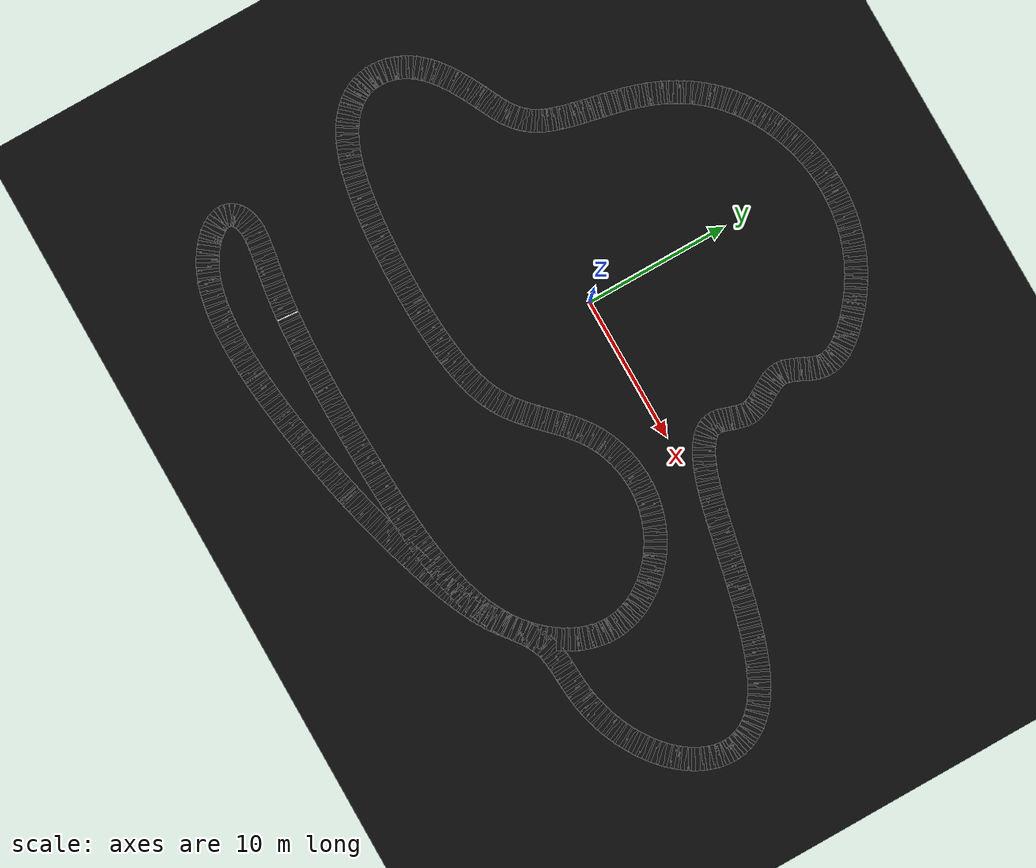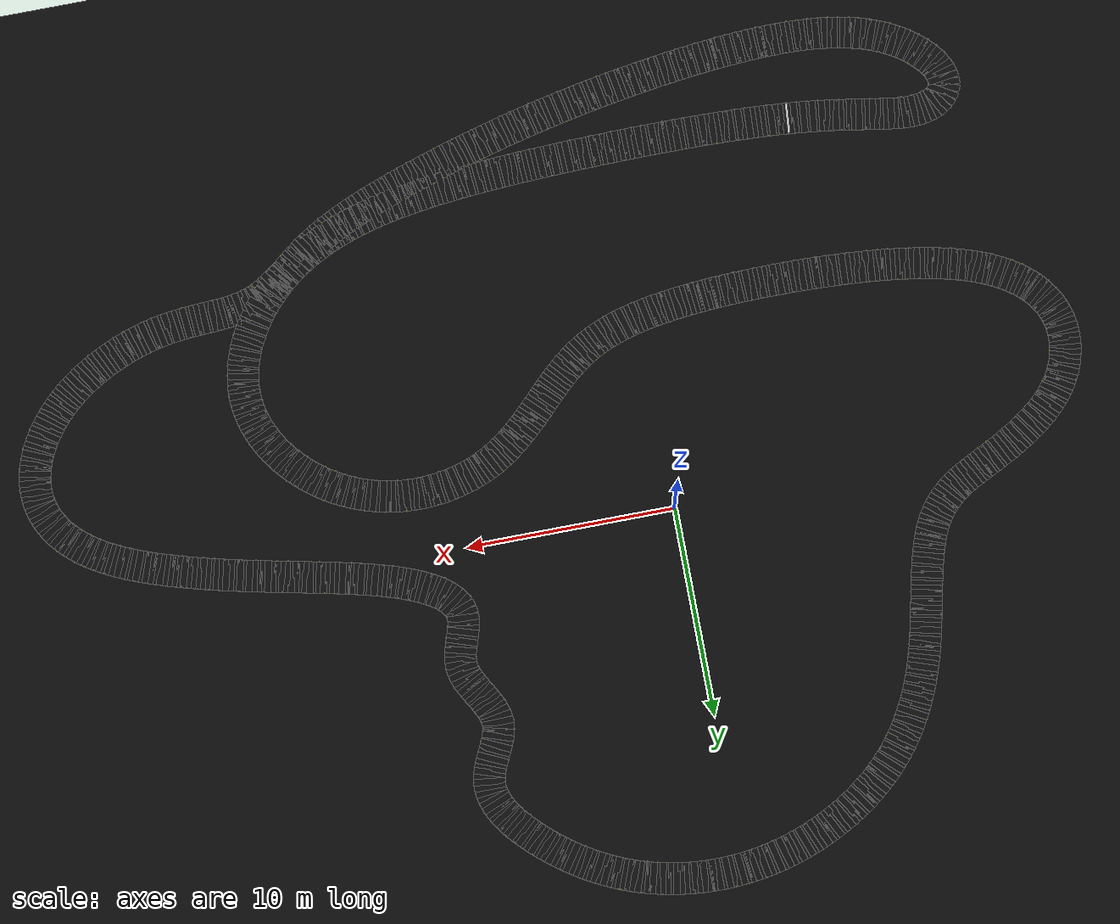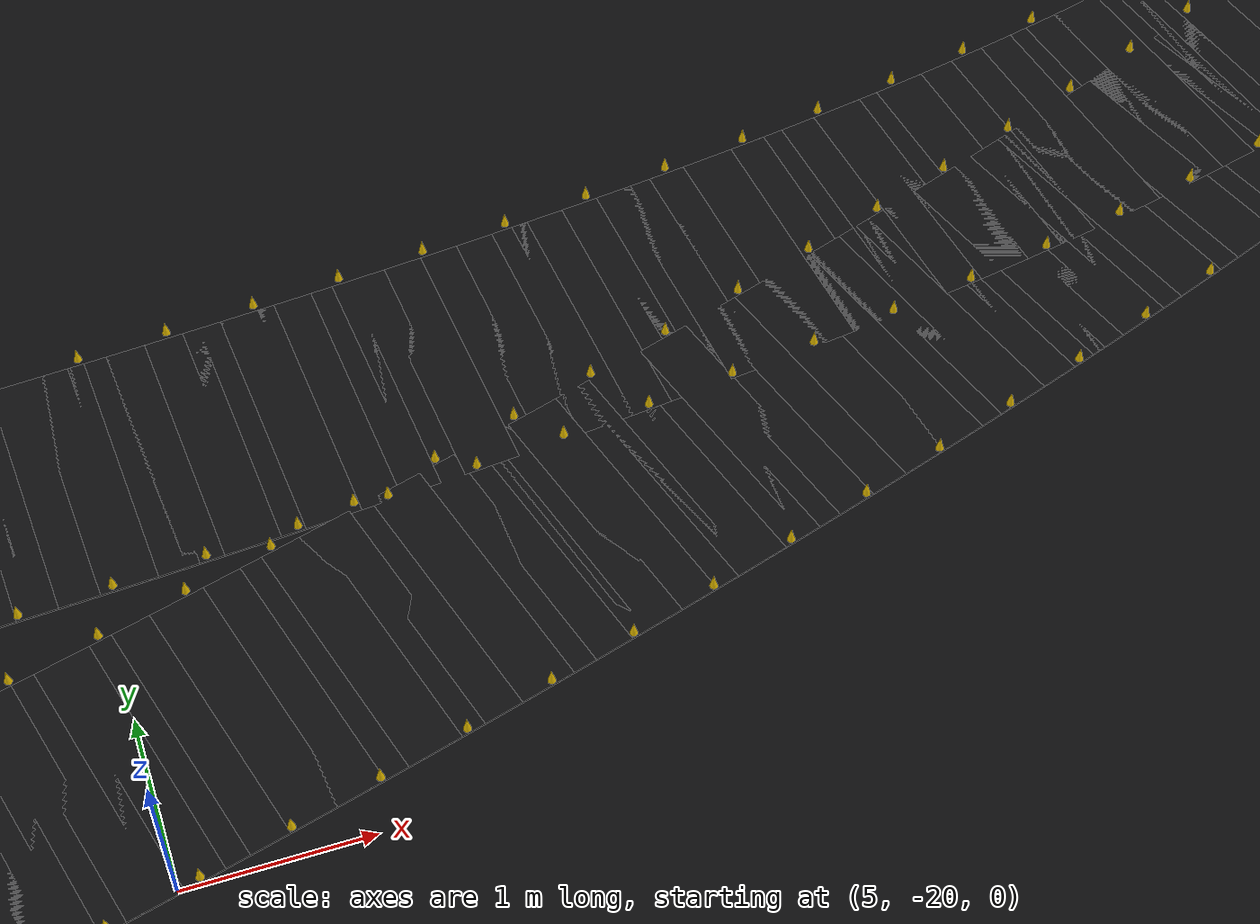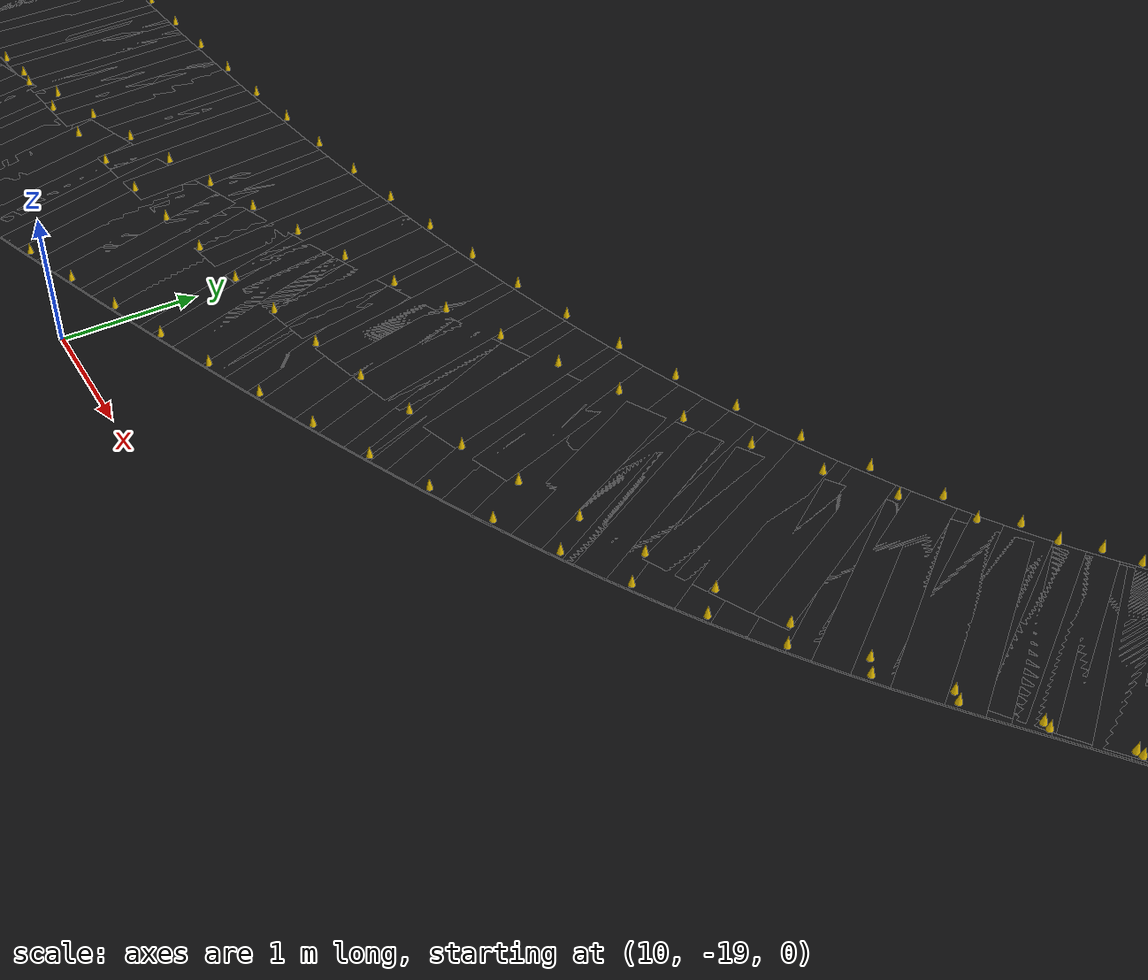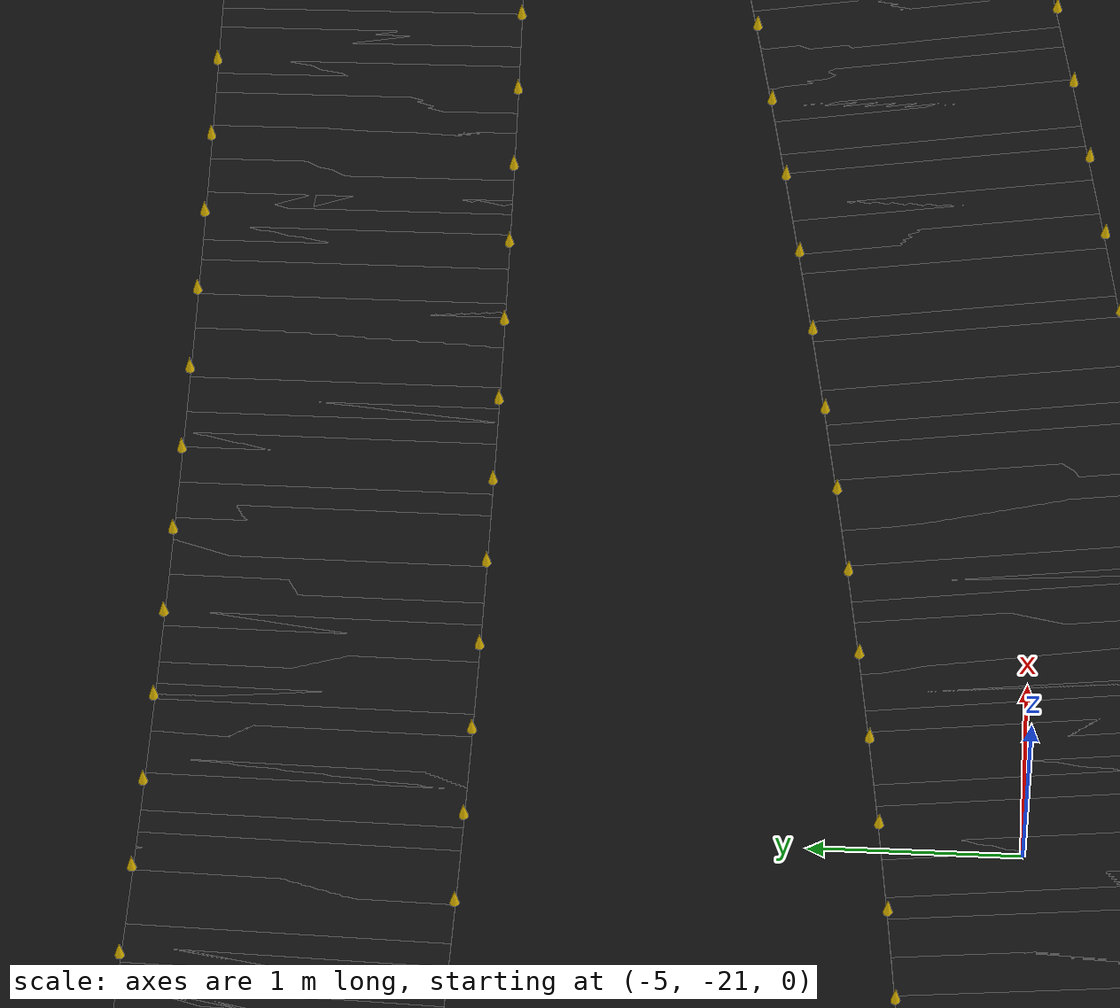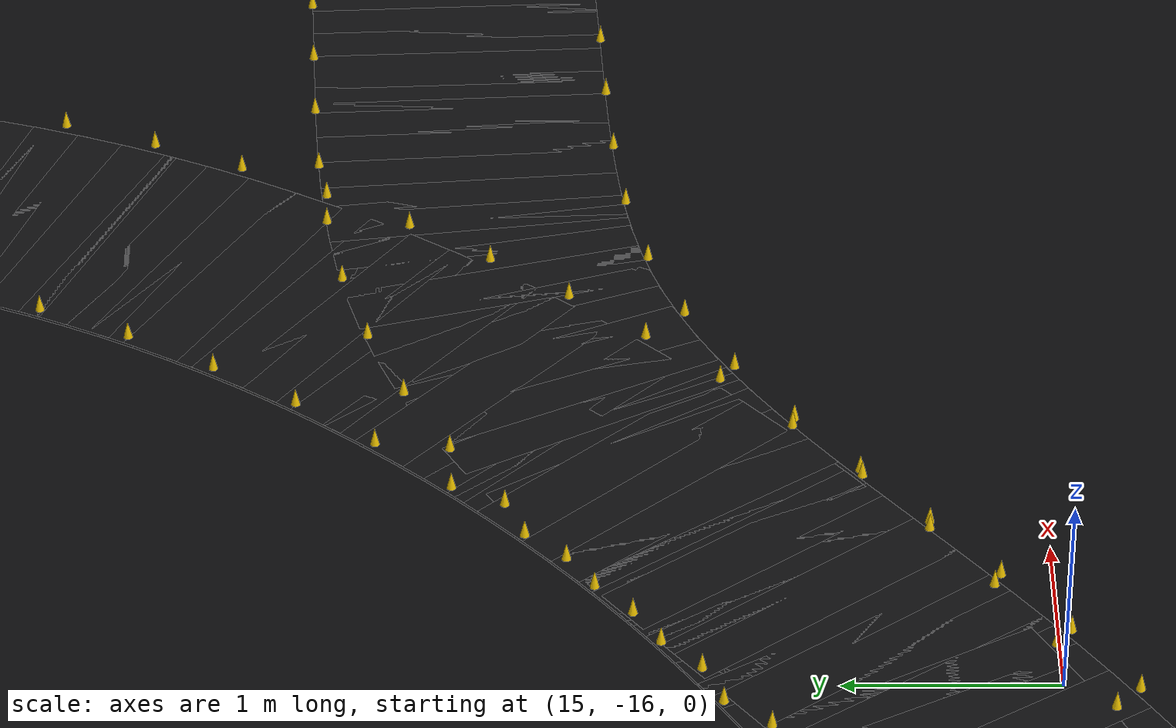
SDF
<?xml version='1.0'?>
<sdf version='1.10'>
  <world name='silverstone'>
    <physics name='1ms' type='ignored'><max_step_size>0.001</max_step_size><real_time_factor>1.0</real_time_factor></physics>
    <plugin filename='gz-sim-physics-system' name='gz::sim::systems::Physics'/>
    <plugin filename='gz-sim-user-commands-system' name='gz::sim::systems::UserCommands'/>
    <plugin filename='gz-sim-scene-broadcaster-system' name='gz::sim::systems::SceneBroadcaster'/>
    <scene><ambient>0.42 0.42 0.44 1</ambient><background>0.055 0.055 0.060 1</background><shadows>true</shadows></scene>
    <light name='sun' type='directional'><pose>0 0 30 0 0 0</pose><diffuse>0.9 0.9 0.9 1</diffuse><specular>0.2 0.2 0.2 1</specular><direction>-0.4 0.2 -1</direction></light>
    <model name='ground'><static>true</static><link name='ground_link'>
      <collision name='ground_collision'><geometry><plane><normal>0 0 1</normal><size>160 160</size></plane></geometry></collision>
      <visual name='ground_visual'><geometry><plane><normal>0 0 1</normal><size>160 160</size></plane></geometry><material><ambient>0.045 0.045 0.050 1</ambient><diffuse>0.045 0.045 0.050 1</diffuse></material></visual>
    </link></model>
    <model name='road'><static>true</static><link name='road_link'>
      <visual name='road_0'><pose>-8.75088 -17.47685 0.00600 0 -0.0000000 -0.0822501</pose><geometry><box><size>0.30995 1.50000 0.01200</size></box></geometry><material><ambient>0.055 0.055 0.060 1</ambient><diffuse>0.055 0.055 0.060 1</diffuse><specular>0.04 0.04 0.04 1</specular></material></visual>
      <visual name='road_1'><pose>-8.53163 -17.49433 0.00600 0 -0.0000000 -0.0768937</pose><geometry><box><size>0.30995 1.50000 0.01200</size></box></geometry><material><ambient>0.055 0.055 0.060 1</ambient><diffuse>0.055 0.055 0.060 1</diffuse><specular>0.04 0.04 0.04 1</specular></material></visual>
      <visual name='road_2'><pose>-8.31229 -17.51068 0.00600 0 -0.0000000 -0.0718663</pose><geometry><box><size>0.30995 1.50000 0.01200</size></box></geometry><material><ambient>0.055 0.055 0.060 1</ambient><diffuse>0.055 0.055 0.060 1</diffuse><specular>0.04 0.04 0.04 1</specular></material></visual>
      <visual name='road_3'><pose>-8.09287 -17.52595 0.00600 0 -0.0000000 -0.0671375</pose><geometry><box><size>0.30995 1.50000 0.01200</size></box></geometry><material><ambient>0.055 0.055 0.060 1</ambient><diffuse>0.055 0.055 0.060 1</diffuse><specular>0.04 0.04 0.04 1</specular></material></visual>
      <visual name='road_4'><pose>-7.87339 -17.54022 0.00600 0 -0.0000000 -0.0626807</pose><geometry><box><size>0.30995 1.50000 0.01200</size></box></geometry><material><ambient>0.055 0.055 0.060 1</ambient><diffuse>0.055 0.055 0.060 1</diffuse><specular>0.04 0.04 0.04 1</specular></material></visual>
      <visual name='road_5'><pose>-7.65384 -17.55352 0.00600 0 -0.0000000 -0.0583713</pose><geometry><box><size>0.30995 1.50000 0.01200</size></box></geometry><material><ambient>0.055 0.055 0.060 1</ambient><diffuse>0.055 0.055 0.060 1</diffuse><specular>0.04 0.04 0.04 1</specular></material></visual>
      <visual name='road_6'><pose>-7.43424 -17.56589 0.00600 0 -0.0000000 -0.0541501</pose><geometry><box><size>0.30995 1.50000 0.01200</size></box></geometry><material><ambient>0.055 0.055 0.060 1</ambient><diffuse>0.055 0.055 0.060 1</diffuse><specular>0.04 0.04 0.04 1</specular></material></visual>
      <visual name='road_7'><pose>-7.21459 -17.57739 0.00600 0 -0.0000000 -0.0504357</pose><geometry><box><size>0.30995 1.50000 0.01200</size></box></geometry><material><ambient>0.055 0.055 0.060 1</ambient><diffuse>0.055 0.055 0.060 1</diffuse><specular>0.04 0.04 0.04 1</specular></material></visual>
      <visual name='road_8'><pose>-6.99491 -17.58809 0.00600 0 -0.0000000 -0.0469038</pose><geometry><box><size>0.30995 1.50000 0.01200</size></box></geometry><material><ambient>0.055 0.055 0.060 1</ambient><diffuse>0.055 0.055 0.060 1</diffuse><specular>0.04 0.04 0.04 1</specular></material></visual>
      <visual name='road_9'><pose>-6.77518 -17.59803 0.00600 0 -0.0000000 -0.0435396</pose><geometry><box><size>0.30995 1.50000 0.01200</size></box></geometry><material><ambient>0.055 0.055 0.060 1</ambient><diffuse>0.055 0.055 0.060 1</diffuse><specular>0.04 0.04 0.04 1</specular></material></visual>
      <visual name='road_10'><pose>-6.55543 -17.60725 0.00600 0 -0.0000000 -0.0403300</pose><geometry><box><size>0.30995 1.50000 0.01200</size></box></geometry><material><ambient>0.055 0.055 0.060 1</ambient><diffuse>0.055 0.055 0.060 1</diffuse><specular>0.04 0.04 0.04 1</specular></material></visual>
      <visual name='road_11'><pose>-6.33564 -17.61578 0.00600 0 -0.0000000 -0.0372629</pose><geometry><box><size>0.30995 1.50000 0.01200</size></box></geometry><material><ambient>0.055 0.055 0.060 1</ambient><diffuse>0.055 0.055 0.060 1</diffuse><specular>0.04 0.04 0.04 1</specular></material></visual>
      <visual name='road_12'><pose>-6.11584 -17.62365 0.00600 0 -0.0000000 -0.0343272</pose><geometry><box><size>0.30995 1.50000 0.01200</size></box></geometry><material><ambient>0.055 0.055 0.060 1</ambient><diffuse>0.055 0.055 0.060 1</diffuse><specular>0.04 0.04 0.04 1</specular></material></visual>
      <visual name='road_13'><pose>-5.89601 -17.63089 0.00600 0 -0.0000000 -0.0315132</pose><geometry><box><size>0.30995 1.50000 0.01200</size></box></geometry><material><ambient>0.055 0.055 0.060 1</ambient><diffuse>0.055 0.055 0.060 1</diffuse><specular>0.04 0.04 0.04 1</specular></material></visual>
      <visual name='road_14'><pose>-5.67616 -17.63753 0.00600 0 -0.0000000 -0.0288115</pose><geometry><box><size>0.30995 1.50000 0.01200</size></box></geometry><material><ambient>0.055 0.055 0.060 1</ambient><diffuse>0.055 0.055 0.060 1</diffuse><specular>0.04 0.04 0.04 1</specular></material></visual>
      <visual name='road_15'><pose>-5.45629 -17.64358 0.00600 0 -0.0000000 -0.0262141</pose><geometry><box><size>0.30995 1.50000 0.01200</size></box></geometry><material><ambient>0.055 0.055 0.060 1</ambient><diffuse>0.055 0.055 0.060 1</diffuse><specular>0.04 0.04 0.04 1</specular></material></visual>
      <visual name='road_16'><pose>-5.23641 -17.64907 0.00600 0 -0.0000000 -0.0237131</pose><geometry><box><size>0.30995 1.50000 0.01200</size></box></geometry><material><ambient>0.055 0.055 0.060 1</ambient><diffuse>0.055 0.055 0.060 1</diffuse><specular>0.04 0.04 0.04 1</specular></material></visual>
      <visual name='road_17'><pose>-5.01652 -17.65402 0.00600 0 -0.0000000 -0.0213018</pose><geometry><box><size>0.30995 1.50000 0.01200</size></box></geometry><material><ambient>0.055 0.055 0.060 1</ambient><diffuse>0.055 0.055 0.060 1</diffuse><specular>0.04 0.04 0.04 1</specular></material></visual>
      <visual name='road_18'><pose>-4.79661 -17.65845 0.00600 0 -0.0000000 -0.0189735</pose><geometry><box><size>0.30995 1.50000 0.01200</size></box></geometry><material><ambient>0.055 0.055 0.060 1</ambient><diffuse>0.055 0.055 0.060 1</diffuse><specular>0.04 0.04 0.04 1</specular></material></visual>
      <visual name='road_19'><pose>-4.57670 -17.66237 0.00600 0 -0.0000000 -0.0167225</pose><geometry><box><size>0.30995 1.50000 0.01200</size></box></geometry><material><ambient>0.055 0.055 0.060 1</ambient><diffuse>0.055 0.055 0.060 1</diffuse><specular>0.04 0.04 0.04 1</specular></material></visual>
      <visual name='road_20'><pose>-4.35678 -17.66581 0.00600 0 -0.0000000 -0.0145433</pose><geometry><box><size>0.30995 1.50000 0.01200</size></box></geometry><material><ambient>0.055 0.055 0.060 1</ambient><diffuse>0.055 0.055 0.060 1</diffuse><specular>0.04 0.04 0.04 1</specular></material></visual>
      <visual name='road_21'><pose>-4.13685 -17.66878 0.00600 0 -0.0000000 -0.0124308</pose><geometry><box><size>0.30995 1.50000 0.01200</size></box></geometry><material><ambient>0.055 0.055 0.060 1</ambient><diffuse>0.055 0.055 0.060 1</diffuse><specular>0.04 0.04 0.04 1</specular></material></visual>
      <visual name='road_22'><pose>-3.91692 -17.67128 0.00600 0 -0.0000000 -0.0103804</pose><geometry><box><size>0.30995 1.50000 0.01200</size></box></geometry><material><ambient>0.055 0.055 0.060 1</ambient><diffuse>0.055 0.055 0.060 1</diffuse><specular>0.04 0.04 0.04 1</specular></material></visual>
      <visual name='road_23'><pose>-3.69698 -17.67335 0.00600 0 -0.0000000 -0.0083876</pose><geometry><box><size>0.30995 1.50000 0.01200</size></box></geometry><material><ambient>0.055 0.055 0.060 1</ambient><diffuse>0.055 0.055 0.060 1</diffuse><specular>0.04 0.04 0.04 1</specular></material></visual>
      <visual name='road_24'><pose>-3.47703 -17.67498 0.00600 0 -0.0000000 -0.0064486</pose><geometry><box><size>0.30995 1.50000 0.01200</size></box></geometry><material><ambient>0.055 0.055 0.060 1</ambient><diffuse>0.055 0.055 0.060 1</diffuse><specular>0.04 0.04 0.04 1</specular></material></visual>
      <visual name='road_25'><pose>-3.25709 -17.67619 0.00600 0 -0.0000000 -0.0045595</pose><geometry><box><size>0.30995 1.50000 0.01200</size></box></geometry><material><ambient>0.055 0.055 0.060 1</ambient><diffuse>0.055 0.055 0.060 1</diffuse><specular>0.04 0.04 0.04 1</specular></material></visual>
      <visual name='road_26'><pose>-3.03714 -17.67699 0.00600 0 -0.0000000 -0.0027168</pose><geometry><box><size>0.30995 1.50000 0.01200</size></box></geometry><material><ambient>0.055 0.055 0.060 1</ambient><diffuse>0.055 0.055 0.060 1</diffuse><specular>0.04 0.04 0.04 1</specular></material></visual>
      <visual name='road_27'><pose>-2.81719 -17.67739 0.00600 0 -0.0000000 -0.0009173</pose><geometry><box><size>0.30995 1.50000 0.01200</size></box></geometry><material><ambient>0.055 0.055 0.060 1</ambient><diffuse>0.055 0.055 0.060 1</diffuse><specular>0.04 0.04 0.04 1</specular></material></visual>
      <visual name='road_28'><pose>-2.59724 -17.67740 0.00600 0 -0.0000000 0.0008422</pose><geometry><box><size>0.30995 1.50000 0.01200</size></box></geometry><material><ambient>0.055 0.055 0.060 1</ambient><diffuse>0.055 0.055 0.060 1</diffuse><specular>0.04 0.04 0.04 1</specular></material></visual>
      <visual name='road_29'><pose>-2.37729 -17.67702 0.00600 0 -0.0000000 0.0025645</pose><geometry><box><size>0.30995 1.50000 0.01200</size></box></geometry><material><ambient>0.055 0.055 0.060 1</ambient><diffuse>0.055 0.055 0.060 1</diffuse><specular>0.04 0.04 0.04 1</specular></material></visual>
      <visual name='road_30'><pose>-2.15735 -17.67627 0.00600 0 -0.0000000 0.0042525</pose><geometry><box><size>0.30995 1.50000 0.01200</size></box></geometry><material><ambient>0.055 0.055 0.060 1</ambient><diffuse>0.055 0.055 0.060 1</diffuse><specular>0.04 0.04 0.04 1</specular></material></visual>
      <visual name='road_31'><pose>-1.93740 -17.67516 0.00600 0 -0.0000000 0.0059086</pose><geometry><box><size>0.30995 1.50000 0.01200</size></box></geometry><material><ambient>0.055 0.055 0.060 1</ambient><diffuse>0.055 0.055 0.060 1</diffuse><specular>0.04 0.04 0.04 1</specular></material></visual>
      <visual name='road_32'><pose>-1.71746 -17.67368 0.00600 0 -0.0000000 0.0075353</pose><geometry><box><size>0.30995 1.50000 0.01200</size></box></geometry><material><ambient>0.055 0.055 0.060 1</ambient><diffuse>0.055 0.055 0.060 1</diffuse><specular>0.04 0.04 0.04 1</specular></material></visual>
      <visual name='road_33'><pose>-1.49751 -17.67184 0.00600 0 -0.0000000 0.0092207</pose><geometry><box><size>0.30995 1.50000 0.01200</size></box></geometry><material><ambient>0.055 0.055 0.060 1</ambient><diffuse>0.055 0.055 0.060 1</diffuse><specular>0.04 0.04 0.04 1</specular></material></visual>
      <visual name='road_34'><pose>-1.27758 -17.66963 0.00600 0 -0.0000000 0.0108146</pose><geometry><box><size>0.30995 1.50000 0.01200</size></box></geometry><material><ambient>0.055 0.055 0.060 1</ambient><diffuse>0.055 0.055 0.060 1</diffuse><specular>0.04 0.04 0.04 1</specular></material></visual>
      <visual name='road_35'><pose>-1.05764 -17.66708 0.00600 0 -0.0000000 0.0123650</pose><geometry><box><size>0.30995 1.50000 0.01200</size></box></geometry><material><ambient>0.055 0.055 0.060 1</ambient><diffuse>0.055 0.055 0.060 1</diffuse><specular>0.04 0.04 0.04 1</specular></material></visual>
      <visual name='road_36'><pose>-0.83771 -17.66420 0.00600 0 -0.0000000 0.0138944</pose><geometry><box><size>0.30995 1.50000 0.01200</size></box></geometry><material><ambient>0.055 0.055 0.060 1</ambient><diffuse>0.055 0.055 0.060 1</diffuse><specular>0.04 0.04 0.04 1</specular></material></visual>
      <visual name='road_37'><pose>-0.61779 -17.66097 0.00600 0 -0.0000000 0.0154049</pose><geometry><box><size>0.30995 1.50000 0.01200</size></box></geometry><material><ambient>0.055 0.055 0.060 1</ambient><diffuse>0.055 0.055 0.060 1</diffuse><specular>0.04 0.04 0.04 1</specular></material></visual>
      <visual name='road_38'><pose>-0.39787 -17.65742 0.00600 0 -0.0000000 0.0168985</pose><geometry><box><size>0.30995 1.50000 0.01200</size></box></geometry><material><ambient>0.055 0.055 0.060 1</ambient><diffuse>0.055 0.055 0.060 1</diffuse><specular>0.04 0.04 0.04 1</specular></material></visual>
      <visual name='road_39'><pose>-0.17795 -17.65354 0.00600 0 -0.0000000 0.0183769</pose><geometry><box><size>0.30995 1.50000 0.01200</size></box></geometry><material><ambient>0.055 0.055 0.060 1</ambient><diffuse>0.055 0.055 0.060 1</diffuse><specular>0.04 0.04 0.04 1</specular></material></visual>
      <visual name='road_40'><pose>0.04196 -17.64934 0.00600 0 -0.0000000 0.0198421</pose><geometry><box><size>0.30995 1.50000 0.01200</size></box></geometry><material><ambient>0.055 0.055 0.060 1</ambient><diffuse>0.055 0.055 0.060 1</diffuse><specular>0.04 0.04 0.04 1</specular></material></visual>
      <visual name='road_41'><pose>0.26186 -17.64482 0.00600 0 -0.0000000 0.0212958</pose><geometry><box><size>0.30995 1.50000 0.01200</size></box></geometry><material><ambient>0.055 0.055 0.060 1</ambient><diffuse>0.055 0.055 0.060 1</diffuse><specular>0.04 0.04 0.04 1</specular></material></visual>
      <visual name='road_42'><pose>0.48176 -17.63997 0.00600 0 -0.0000000 0.0227397</pose><geometry><box><size>0.30995 1.50000 0.01200</size></box></geometry><material><ambient>0.055 0.055 0.060 1</ambient><diffuse>0.055 0.055 0.060 1</diffuse><specular>0.04 0.04 0.04 1</specular></material></visual>
      <visual name='road_43'><pose>0.70164 -17.63481 0.00600 0 -0.0000000 0.0241758</pose><geometry><box><size>0.30995 1.50000 0.01200</size></box></geometry><material><ambient>0.055 0.055 0.060 1</ambient><diffuse>0.055 0.055 0.060 1</diffuse><specular>0.04 0.04 0.04 1</specular></material></visual>
      <visual name='road_44'><pose>0.92153 -17.62934 0.00600 0 -0.0000000 0.0256055</pose><geometry><box><size>0.30995 1.50000 0.01200</size></box></geometry><material><ambient>0.055 0.055 0.060 1</ambient><diffuse>0.055 0.055 0.060 1</diffuse><specular>0.04 0.04 0.04 1</specular></material></visual>
      <visual name='road_45'><pose>1.14140 -17.62355 0.00600 0 -0.0000000 0.0270308</pose><geometry><box><size>0.30995 1.50000 0.01200</size></box></geometry><material><ambient>0.055 0.055 0.060 1</ambient><diffuse>0.055 0.055 0.060 1</diffuse><specular>0.04 0.04 0.04 1</specular></material></visual>
      <visual name='road_46'><pose>1.36126 -17.61745 0.00600 0 -0.0000000 0.0284534</pose><geometry><box><size>0.30995 1.50000 0.01200</size></box></geometry><material><ambient>0.055 0.055 0.060 1</ambient><diffuse>0.055 0.055 0.060 1</diffuse><specular>0.04 0.04 0.04 1</specular></material></visual>
      <visual name='road_47'><pose>1.58112 -17.61104 0.00600 0 -0.0000000 0.0298749</pose><geometry><box><size>0.30995 1.50000 0.01200</size></box></geometry><material><ambient>0.055 0.055 0.060 1</ambient><diffuse>0.055 0.055 0.060 1</diffuse><specular>0.04 0.04 0.04 1</specular></material></visual>
      <visual name='road_48'><pose>1.80096 -17.60431 0.00600 0 -0.0000000 0.0312972</pose><geometry><box><size>0.30995 1.50000 0.01200</size></box></geometry><material><ambient>0.055 0.055 0.060 1</ambient><diffuse>0.055 0.055 0.060 1</diffuse><specular>0.04 0.04 0.04 1</specular></material></visual>
      <visual name='road_49'><pose>2.02080 -17.59727 0.00600 0 -0.0000000 0.0327234</pose><geometry><box><size>0.30995 1.50000 0.01200</size></box></geometry><material><ambient>0.055 0.055 0.060 1</ambient><diffuse>0.055 0.055 0.060 1</diffuse><specular>0.04 0.04 0.04 1</specular></material></visual>
      <visual name='road_50'><pose>2.24063 -17.58992 0.00600 0 -0.0000000 0.0341696</pose><geometry><box><size>0.30995 1.50000 0.01200</size></box></geometry><material><ambient>0.055 0.055 0.060 1</ambient><diffuse>0.055 0.055 0.060 1</diffuse><specular>0.04 0.04 0.04 1</specular></material></visual>
      <visual name='road_51'><pose>2.46044 -17.58224 0.00600 0 -0.0000000 0.0356850</pose><geometry><box><size>0.30995 1.50000 0.01200</size></box></geometry><material><ambient>0.055 0.055 0.060 1</ambient><diffuse>0.055 0.055 0.060 1</diffuse><specular>0.04 0.04 0.04 1</specular></material></visual>
      <visual name='road_52'><pose>2.68024 -17.57421 0.00600 0 -0.0000000 0.0372840</pose><geometry><box><size>0.30995 1.50000 0.01200</size></box></geometry><material><ambient>0.055 0.055 0.060 1</ambient><diffuse>0.055 0.055 0.060 1</diffuse><specular>0.04 0.04 0.04 1</specular></material></visual>
      <visual name='road_53'><pose>2.90003 -17.56583 0.00600 0 -0.0000000 0.0389922</pose><geometry><box><size>0.30995 1.50000 0.01200</size></box></geometry><material><ambient>0.055 0.055 0.060 1</ambient><diffuse>0.055 0.055 0.060 1</diffuse><specular>0.04 0.04 0.04 1</specular></material></visual>
      <visual name='road_54'><pose>3.11981 -17.55706 0.00600 0 -0.0000000 0.0407739</pose><geometry><box><size>0.30995 1.50000 0.01200</size></box></geometry><material><ambient>0.055 0.055 0.060 1</ambient><diffuse>0.055 0.055 0.060 1</diffuse><specular>0.04 0.04 0.04 1</specular></material></visual>
      <visual name='road_55'><pose>3.33957 -17.54789 0.00600 0 -0.0000000 0.0426339</pose><geometry><box><size>0.30995 1.50000 0.01200</size></box></geometry><material><ambient>0.055 0.055 0.060 1</ambient><diffuse>0.055 0.055 0.060 1</diffuse><specular>0.04 0.04 0.04 1</specular></material></visual>
      <visual name='road_56'><pose>3.55931 -17.53830 0.00600 0 -0.0000000 0.0445880</pose><geometry><box><size>0.30995 1.50000 0.01200</size></box></geometry><material><ambient>0.055 0.055 0.060 1</ambient><diffuse>0.055 0.055 0.060 1</diffuse><specular>0.04 0.04 0.04 1</specular></material></visual>
      <visual name='road_57'><pose>3.77903 -17.52827 0.00600 0 -0.0000000 0.0466394</pose><geometry><box><size>0.30995 1.50000 0.01200</size></box></geometry><material><ambient>0.055 0.055 0.060 1</ambient><diffuse>0.055 0.055 0.060 1</diffuse><specular>0.04 0.04 0.04 1</specular></material></visual>
      <visual name='road_58'><pose>3.99872 -17.51778 0.00600 0 -0.0000000 0.0487917</pose><geometry><box><size>0.30995 1.50000 0.01200</size></box></geometry><material><ambient>0.055 0.055 0.060 1</ambient><diffuse>0.055 0.055 0.060 1</diffuse><specular>0.04 0.04 0.04 1</specular></material></visual>
      <visual name='road_59'><pose>4.21840 -17.50680 0.00600 0 -0.0000000 0.0510484</pose><geometry><box><size>0.30995 1.50000 0.01200</size></box></geometry><material><ambient>0.055 0.055 0.060 1</ambient><diffuse>0.055 0.055 0.060 1</diffuse><specular>0.04 0.04 0.04 1</specular></material></visual>
      <visual name='road_60'><pose>4.43805 -17.49532 0.00600 0 -0.0000000 0.0534133</pose><geometry><box><size>0.30995 1.50000 0.01200</size></box></geometry><material><ambient>0.055 0.055 0.060 1</ambient><diffuse>0.055 0.055 0.060 1</diffuse><specular>0.04 0.04 0.04 1</specular></material></visual>
      <visual name='road_61'><pose>4.65767 -17.48330 0.00600 0 -0.0000000 0.0559190</pose><geometry><box><size>0.30995 1.50000 0.01200</size></box></geometry><material><ambient>0.055 0.055 0.060 1</ambient><diffuse>0.055 0.055 0.060 1</diffuse><specular>0.04 0.04 0.04 1</specular></material></visual>
      <visual name='road_62'><pose>4.87726 -17.47072 0.00600 0 -0.0000000 0.0585565</pose><geometry><box><size>0.30995 1.50000 0.01200</size></box></geometry><material><ambient>0.055 0.055 0.060 1</ambient><diffuse>0.055 0.055 0.060 1</diffuse><specular>0.04 0.04 0.04 1</specular></material></visual>
      <visual name='road_63'><pose>5.09681 -17.45755 0.00600 0 -0.0000000 0.0612917</pose><geometry><box><size>0.30995 1.50000 0.01200</size></box></geometry><material><ambient>0.055 0.055 0.060 1</ambient><diffuse>0.055 0.055 0.060 1</diffuse><specular>0.04 0.04 0.04 1</specular></material></visual>
      <visual name='road_64'><pose>5.31633 -17.44376 0.00600 0 -0.0000000 0.0641545</pose><geometry><box><size>0.30995 1.50000 0.01200</size></box></geometry><material><ambient>0.055 0.055 0.060 1</ambient><diffuse>0.055 0.055 0.060 1</diffuse><specular>0.04 0.04 0.04 1</specular></material></visual>
      <visual name='road_65'><pose>5.53580 -17.42933 0.00600 0 -0.0000000 0.0671498</pose><geometry><box><size>0.30995 1.50000 0.01200</size></box></geometry><material><ambient>0.055 0.055 0.060 1</ambient><diffuse>0.055 0.055 0.060 1</diffuse><specular>0.04 0.04 0.04 1</specular></material></visual>
      <visual name='road_66'><pose>5.75523 -17.41423 0.00600 0 -0.0000000 0.0702828</pose><geometry><box><size>0.30995 1.50000 0.01200</size></box></geometry><material><ambient>0.055 0.055 0.060 1</ambient><diffuse>0.055 0.055 0.060 1</diffuse><specular>0.04 0.04 0.04 1</specular></material></visual>
      <visual name='road_67'><pose>5.97461 -17.39842 0.00600 0 -0.0000000 0.0735592</pose><geometry><box><size>0.30995 1.50000 0.01200</size></box></geometry><material><ambient>0.055 0.055 0.060 1</ambient><diffuse>0.055 0.055 0.060 1</diffuse><specular>0.04 0.04 0.04 1</specular></material></visual>
      <visual name='road_68'><pose>6.19394 -17.38188 0.00600 0 -0.0000000 0.0769846</pose><geometry><box><size>0.30995 1.50000 0.01200</size></box></geometry><material><ambient>0.055 0.055 0.060 1</ambient><diffuse>0.055 0.055 0.060 1</diffuse><specular>0.04 0.04 0.04 1</specular></material></visual>
      <visual name='road_69'><pose>6.41320 -17.36457 0.00600 0 -0.0000000 0.0805653</pose><geometry><box><size>0.30995 1.50000 0.01200</size></box></geometry><material><ambient>0.055 0.055 0.060 1</ambient><diffuse>0.055 0.055 0.060 1</diffuse><specular>0.04 0.04 0.04 1</specular></material></visual>
      <visual name='road_70'><pose>6.63241 -17.34646 0.00600 0 -0.0000000 0.0843076</pose><geometry><box><size>0.30995 1.50000 0.01200</size></box></geometry><material><ambient>0.055 0.055 0.060 1</ambient><diffuse>0.055 0.055 0.060 1</diffuse><specular>0.04 0.04 0.04 1</specular></material></visual>
      <visual name='road_71'><pose>6.85154 -17.32751 0.00600 0 -0.0000000 0.0882183</pose><geometry><box><size>0.30995 1.50000 0.01200</size></box></geometry><material><ambient>0.055 0.055 0.060 1</ambient><diffuse>0.055 0.055 0.060 1</diffuse><specular>0.04 0.04 0.04 1</specular></material></visual>
      <visual name='road_72'><pose>7.07059 -17.30769 0.00600 0 -0.0000000 0.0923046</pose><geometry><box><size>0.30995 1.50000 0.01200</size></box></geometry><material><ambient>0.055 0.055 0.060 1</ambient><diffuse>0.055 0.055 0.060 1</diffuse><specular>0.04 0.04 0.04 1</specular></material></visual>
      <visual name='road_73'><pose>7.28956 -17.28694 0.00600 0 -0.0000000 0.0965740</pose><geometry><box><size>0.30995 1.50000 0.01200</size></box></geometry><material><ambient>0.055 0.055 0.060 1</ambient><diffuse>0.055 0.055 0.060 1</diffuse><specular>0.04 0.04 0.04 1</specular></material></visual>
      <visual name='road_74'><pose>7.50843 -17.26525 0.00600 0 -0.0000000 0.1010344</pose><geometry><box><size>0.30995 1.50000 0.01200</size></box></geometry><material><ambient>0.055 0.055 0.060 1</ambient><diffuse>0.055 0.055 0.060 1</diffuse><specular>0.04 0.04 0.04 1</specular></material></visual>
      <visual name='road_75'><pose>7.72721 -17.24253 0.00600 0 -0.0000000 0.1059097</pose><geometry><box><size>0.30995 1.50000 0.01200</size></box></geometry><material><ambient>0.055 0.055 0.060 1</ambient><diffuse>0.055 0.055 0.060 1</diffuse><specular>0.04 0.04 0.04 1</specular></material></visual>
      <visual name='road_76'><pose>7.94586 -17.21871 0.00600 0 -0.0000000 0.1111144</pose><geometry><box><size>0.30995 1.50000 0.01200</size></box></geometry><material><ambient>0.055 0.055 0.060 1</ambient><diffuse>0.055 0.055 0.060 1</diffuse><specular>0.04 0.04 0.04 1</specular></material></visual>
      <visual name='road_77'><pose>8.16439 -17.19376 0.00600 0 -0.0000000 0.1162697</pose><geometry><box><size>0.30995 1.50000 0.01200</size></box></geometry><material><ambient>0.055 0.055 0.060 1</ambient><diffuse>0.055 0.055 0.060 1</diffuse><specular>0.04 0.04 0.04 1</specular></material></visual>
      <visual name='road_78'><pose>8.38278 -17.16765 0.00600 0 -0.0000000 0.1216577</pose><geometry><box><size>0.30995 1.50000 0.01200</size></box></geometry><material><ambient>0.055 0.055 0.060 1</ambient><diffuse>0.055 0.055 0.060 1</diffuse><specular>0.04 0.04 0.04 1</specular></material></visual>
      <visual name='road_79'><pose>8.60103 -17.14035 0.00600 0 -0.0000000 0.1272890</pose><geometry><box><size>0.30995 1.50000 0.01200</size></box></geometry><material><ambient>0.055 0.055 0.060 1</ambient><diffuse>0.055 0.055 0.060 1</diffuse><specular>0.04 0.04 0.04 1</specular></material></visual>
      <visual name='road_80'><pose>8.81911 -17.11178 0.00600 0 -0.0000000 0.1331749</pose><geometry><box><size>0.30995 1.50000 0.01200</size></box></geometry><material><ambient>0.055 0.055 0.060 1</ambient><diffuse>0.055 0.055 0.060 1</diffuse><specular>0.04 0.04 0.04 1</specular></material></visual>
      <visual name='road_81'><pose>9.03702 -17.08189 0.00600 0 -0.0000000 0.1395228</pose><geometry><box><size>0.30995 1.50000 0.01200</size></box></geometry><material><ambient>0.055 0.055 0.060 1</ambient><diffuse>0.055 0.055 0.060 1</diffuse><specular>0.04 0.04 0.04 1</specular></material></visual>
      <visual name='road_82'><pose>9.25472 -17.05051 0.00600 0 -0.0000000 0.1467365</pose><geometry><box><size>0.30995 1.50000 0.01200</size></box></geometry><material><ambient>0.055 0.055 0.060 1</ambient><diffuse>0.055 0.055 0.060 1</diffuse><specular>0.04 0.04 0.04 1</specular></material></visual>
      <visual name='road_83'><pose>9.47219 -17.01761 0.00600 0 -0.0000000 0.1535699</pose><geometry><box><size>0.30995 1.50000 0.01200</size></box></geometry><material><ambient>0.055 0.055 0.060 1</ambient><diffuse>0.055 0.055 0.060 1</diffuse><specular>0.04 0.04 0.04 1</specular></material></visual>
      <visual name='road_84'><pose>9.68943 -16.98319 0.00600 0 -0.0000000 0.1607177</pose><geometry><box><size>0.30995 1.50000 0.01200</size></box></geometry><material><ambient>0.055 0.055 0.060 1</ambient><diffuse>0.055 0.055 0.060 1</diffuse><specular>0.04 0.04 0.04 1</specular></material></visual>
      <visual name='road_85'><pose>9.90640 -16.94718 0.00600 0 -0.0000000 0.1681952</pose><geometry><box><size>0.30995 1.50000 0.01200</size></box></geometry><material><ambient>0.055 0.055 0.060 1</ambient><diffuse>0.055 0.055 0.060 1</diffuse><specular>0.04 0.04 0.04 1</specular></material></visual>
      <visual name='road_86'><pose>10.12308 -16.90940 0.00600 0 -0.0000000 0.1770932</pose><geometry><box><size>0.30995 1.50000 0.01200</size></box></geometry><material><ambient>0.055 0.055 0.060 1</ambient><diffuse>0.055 0.055 0.060 1</diffuse><specular>0.04 0.04 0.04 1</specular></material></visual>
      <visual name='road_87'><pose>10.33942 -16.86971 0.00600 0 -0.0000000 0.1857390</pose><geometry><box><size>0.30995 1.50000 0.01200</size></box></geometry><material><ambient>0.055 0.055 0.060 1</ambient><diffuse>0.055 0.055 0.060 1</diffuse><specular>0.04 0.04 0.04 1</specular></material></visual>
      <visual name='road_88'><pose>10.55540 -16.82815 0.00600 0 -0.0000000 0.1944645</pose><geometry><box><size>0.30995 1.50000 0.01200</size></box></geometry><material><ambient>0.055 0.055 0.060 1</ambient><diffuse>0.055 0.055 0.060 1</diffuse><specular>0.04 0.04 0.04 1</specular></material></visual>
      <visual name='road_89'><pose>10.77099 -16.78462 0.00600 0 -0.0000000 0.2040282</pose><geometry><box><size>0.30995 1.50000 0.01200</size></box></geometry><material><ambient>0.055 0.055 0.060 1</ambient><diffuse>0.055 0.055 0.060 1</diffuse><specular>0.04 0.04 0.04 1</specular></material></visual>
      <visual name='road_90'><pose>10.98613 -16.73886 0.00600 0 -0.0000000 0.2151417</pose><geometry><box><size>0.30995 1.50000 0.01200</size></box></geometry><material><ambient>0.055 0.055 0.060 1</ambient><diffuse>0.055 0.055 0.060 1</diffuse><specular>0.04 0.04 0.04 1</specular></material></visual>
      <visual name='road_91'><pose>11.20076 -16.69081 0.00600 0 -0.0000000 0.2253632</pose><geometry><box><size>0.30995 1.50000 0.01200</size></box></geometry><material><ambient>0.055 0.055 0.060 1</ambient><diffuse>0.055 0.055 0.060 1</diffuse><specular>0.04 0.04 0.04 1</specular></material></visual>
      <visual name='road_92'><pose>11.41486 -16.64044 0.00600 0 -0.0000000 0.2367274</pose><geometry><box><size>0.30995 1.50000 0.01200</size></box></geometry><material><ambient>0.055 0.055 0.060 1</ambient><diffuse>0.055 0.055 0.060 1</diffuse><specular>0.04 0.04 0.04 1</specular></material></visual>
      <visual name='road_93'><pose>11.62832 -16.58746 0.00600 0 -0.0000000 0.2498516</pose><geometry><box><size>0.30995 1.50000 0.01200</size></box></geometry><material><ambient>0.055 0.055 0.060 1</ambient><diffuse>0.055 0.055 0.060 1</diffuse><specular>0.04 0.04 0.04 1</specular></material></visual>
      <visual name='road_94'><pose>11.84110 -16.53180 0.00600 0 -0.0000000 0.2618516</pose><geometry><box><size>0.30995 1.50000 0.01200</size></box></geometry><material><ambient>0.055 0.055 0.060 1</ambient><diffuse>0.055 0.055 0.060 1</diffuse><specular>0.04 0.04 0.04 1</specular></material></visual>
      <visual name='road_95'><pose>12.05313 -16.47332 0.00600 0 -0.0000000 0.2763597</pose><geometry><box><size>0.30995 1.50000 0.01200</size></box></geometry><material><ambient>0.055 0.055 0.060 1</ambient><diffuse>0.055 0.055 0.060 1</diffuse><specular>0.04 0.04 0.04 1</specular></material></visual>
      <visual name='road_96'><pose>12.26431 -16.41187 0.00600 0 -0.0000000 0.2900096</pose><geometry><box><size>0.30995 1.50000 0.01200</size></box></geometry><material><ambient>0.055 0.055 0.060 1</ambient><diffuse>0.055 0.055 0.060 1</diffuse><specular>0.04 0.04 0.04 1</specular></material></visual>
      <visual name='road_97'><pose>12.47460 -16.34743 0.00600 0 -0.0000000 0.3046534</pose><geometry><box><size>0.30995 1.50000 0.01200</size></box></geometry><material><ambient>0.055 0.055 0.060 1</ambient><diffuse>0.055 0.055 0.060 1</diffuse><specular>0.04 0.04 0.04 1</specular></material></visual>
      <visual name='road_98'><pose>12.68390 -16.27986 0.00600 0 -0.0000000 0.3199336</pose><geometry><box><size>0.30995 1.50000 0.01200</size></box></geometry><material><ambient>0.055 0.055 0.060 1</ambient><diffuse>0.055 0.055 0.060 1</diffuse><specular>0.04 0.04 0.04 1</specular></material></visual>
      <visual name='road_99'><pose>12.89214 -16.20908 0.00600 0 -0.0000000 0.3353294</pose><geometry><box><size>0.30995 1.50000 0.01200</size></box></geometry><material><ambient>0.055 0.055 0.060 1</ambient><diffuse>0.055 0.055 0.060 1</diffuse><specular>0.04 0.04 0.04 1</specular></material></visual>
      <visual name='road_100'><pose>13.09923 -16.13501 0.00600 0 -0.0000000 0.3516320</pose><geometry><box><size>0.30995 1.50000 0.01200</size></box></geometry><material><ambient>0.055 0.055 0.060 1</ambient><diffuse>0.055 0.055 0.060 1</diffuse><specular>0.04 0.04 0.04 1</specular></material></visual>
      <visual name='road_101'><pose>13.30507 -16.05753 0.00600 0 -0.0000000 0.3684324</pose><geometry><box><size>0.30994 1.50000 0.01200</size></box></geometry><material><ambient>0.055 0.055 0.060 1</ambient><diffuse>0.055 0.055 0.060 1</diffuse><specular>0.04 0.04 0.04 1</specular></material></visual>
      <visual name='road_102'><pose>13.50958 -15.97661 0.00600 0 -0.0000000 0.3851021</pose><geometry><box><size>0.30995 1.50000 0.01200</size></box></geometry><material><ambient>0.055 0.055 0.060 1</ambient><diffuse>0.055 0.055 0.060 1</diffuse><specular>0.04 0.04 0.04 1</specular></material></visual>
      <visual name='road_103'><pose>13.71262 -15.89207 0.00600 0 -0.0000000 0.4039719</pose><geometry><box><size>0.30994 1.50000 0.01200</size></box></geometry><material><ambient>0.055 0.055 0.060 1</ambient><diffuse>0.055 0.055 0.060 1</diffuse><specular>0.04 0.04 0.04 1</specular></material></visual>
      <visual name='road_104'><pose>13.91409 -15.80386 0.00600 0 -0.0000000 0.4213717</pose><geometry><box><size>0.30994 1.50000 0.01200</size></box></geometry><material><ambient>0.055 0.055 0.060 1</ambient><diffuse>0.055 0.055 0.060 1</diffuse><specular>0.04 0.04 0.04 1</specular></material></visual>
      <visual name='road_105'><pose>14.11390 -15.71195 0.00600 0 -0.0000000 0.4408584</pose><geometry><box><size>0.30995 1.50000 0.01200</size></box></geometry><material><ambient>0.055 0.055 0.060 1</ambient><diffuse>0.055 0.055 0.060 1</diffuse><specular>0.04 0.04 0.04 1</specular></material></visual>
      <visual name='road_106'><pose>14.31187 -15.61614 0.00600 0 -0.0000000 0.4606688</pose><geometry><box><size>0.30994 1.50000 0.01200</size></box></geometry><material><ambient>0.055 0.055 0.060 1</ambient><diffuse>0.055 0.055 0.060 1</diffuse><specular>0.04 0.04 0.04 1</specular></material></visual>
      <visual name='road_107'><pose>14.50791 -15.51645 0.00600 0 -0.0000000 0.4801645</pose><geometry><box><size>0.30994 1.50000 0.01200</size></box></geometry><material><ambient>0.055 0.055 0.060 1</ambient><diffuse>0.055 0.055 0.060 1</diffuse><specular>0.04 0.04 0.04 1</specular></material></visual>
      <visual name='road_108'><pose>14.70192 -15.41285 0.00600 0 -0.0000000 0.5007883</pose><geometry><box><size>0.30995 1.50000 0.01200</size></box></geometry><material><ambient>0.055 0.055 0.060 1</ambient><diffuse>0.055 0.055 0.060 1</diffuse><specular>0.04 0.04 0.04 1</specular></material></visual>
      <visual name='road_109'><pose>14.89366 -15.30513 0.00600 0 -0.0000000 0.5229748</pose><geometry><box><size>0.30994 1.50000 0.01200</size></box></geometry><material><ambient>0.055 0.055 0.060 1</ambient><diffuse>0.055 0.055 0.060 1</diffuse><specular>0.04 0.04 0.04 1</specular></material></visual>
      <visual name='road_110'><pose>15.08300 -15.19325 0.00600 0 -0.0000000 0.5443936</pose><geometry><box><size>0.30994 1.50000 0.01200</size></box></geometry><material><ambient>0.055 0.055 0.060 1</ambient><diffuse>0.055 0.055 0.060 1</diffuse><specular>0.04 0.04 0.04 1</specular></material></visual>
      <visual name='road_111'><pose>15.26987 -15.07728 0.00600 0 -0.0000000 0.5664519</pose><geometry><box><size>0.30994 1.50000 0.01200</size></box></geometry><material><ambient>0.055 0.055 0.060 1</ambient><diffuse>0.055 0.055 0.060 1</diffuse><specular>0.04 0.04 0.04 1</specular></material></visual>
      <visual name='road_112'><pose>15.45410 -14.95716 0.00600 0 -0.0000000 0.5891094</pose><geometry><box><size>0.30994 1.50000 0.01200</size></box></geometry><material><ambient>0.055 0.055 0.060 1</ambient><diffuse>0.055 0.055 0.060 1</diffuse><specular>0.04 0.04 0.04 1</specular></material></visual>
      <visual name='road_113'><pose>15.63552 -14.83285 0.00600 0 -0.0000000 0.6123634</pose><geometry><box><size>0.30994 1.50000 0.01200</size></box></geometry><material><ambient>0.055 0.055 0.060 1</ambient><diffuse>0.055 0.055 0.060 1</diffuse><specular>0.04 0.04 0.04 1</specular></material></visual>
      <visual name='road_114'><pose>15.81393 -14.70424 0.00600 0 -0.0000000 0.6368197</pose><geometry><box><size>0.30994 1.50000 0.01200</size></box></geometry><material><ambient>0.055 0.055 0.060 1</ambient><diffuse>0.055 0.055 0.060 1</diffuse><specular>0.04 0.04 0.04 1</specular></material></visual>
      <visual name='road_115'><pose>15.98917 -14.57135 0.00600 0 -0.0000000 0.6608001</pose><geometry><box><size>0.30994 1.50000 0.01200</size></box></geometry><material><ambient>0.055 0.055 0.060 1</ambient><diffuse>0.055 0.055 0.060 1</diffuse><specular>0.04 0.04 0.04 1</specular></material></visual>
      <visual name='road_116'><pose>16.16115 -14.43427 0.00600 0 -0.0000000 0.6851614</pose><geometry><box><size>0.30994 1.50000 0.01200</size></box></geometry><material><ambient>0.055 0.055 0.060 1</ambient><diffuse>0.055 0.055 0.060 1</diffuse><specular>0.04 0.04 0.04 1</specular></material></visual>
      <visual name='road_117'><pose>16.32971 -14.29301 0.00600 0 -0.0000000 0.7098354</pose><geometry><box><size>0.30994 1.50000 0.01200</size></box></geometry><material><ambient>0.055 0.055 0.060 1</ambient><diffuse>0.055 0.055 0.060 1</diffuse><specular>0.04 0.04 0.04 1</specular></material></visual>
      <visual name='road_118'><pose>16.49471 -14.14762 0.00600 0 -0.0000000 0.7347497</pose><geometry><box><size>0.30994 1.50000 0.01200</size></box></geometry><material><ambient>0.055 0.055 0.060 1</ambient><diffuse>0.055 0.055 0.060 1</diffuse><specular>0.04 0.04 0.04 1</specular></material></visual>
      <visual name='road_119'><pose>16.65604 -13.99814 0.00600 0 -0.0000000 0.7598290</pose><geometry><box><size>0.30994 1.50000 0.01200</size></box></geometry><material><ambient>0.055 0.055 0.060 1</ambient><diffuse>0.055 0.055 0.060 1</diffuse><specular>0.04 0.04 0.04 1</specular></material></visual>
      <visual name='road_120'><pose>16.81355 -13.84467 0.00600 0 -0.0000000 0.7849955</pose><geometry><box><size>0.30994 1.50000 0.01200</size></box></geometry><material><ambient>0.055 0.055 0.060 1</ambient><diffuse>0.055 0.055 0.060 1</diffuse><specular>0.04 0.04 0.04 1</specular></material></visual>
      <visual name='road_121'><pose>16.96715 -13.68728 0.00600 0 -0.0000000 0.8101704</pose><geometry><box><size>0.30994 1.50000 0.01200</size></box></geometry><material><ambient>0.055 0.055 0.060 1</ambient><diffuse>0.055 0.055 0.060 1</diffuse><specular>0.04 0.04 0.04 1</specular></material></visual>
      <visual name='road_122'><pose>17.11675 -13.52607 0.00600 0 -0.0000000 0.8352748</pose><geometry><box><size>0.30994 1.50000 0.01200</size></box></geometry><material><ambient>0.055 0.055 0.060 1</ambient><diffuse>0.055 0.055 0.060 1</diffuse><specular>0.04 0.04 0.04 1</specular></material></visual>
      <visual name='road_123'><pose>17.26226 -13.36117 0.00600 0 -0.0000000 0.8603051</pose><geometry><box><size>0.30994 1.50000 0.01200</size></box></geometry><material><ambient>0.055 0.055 0.060 1</ambient><diffuse>0.055 0.055 0.060 1</diffuse><specular>0.04 0.04 0.04 1</specular></material></visual>
      <visual name='road_124'><pose>17.40358 -13.19266 0.00600 0 -0.0000000 0.8856046</pose><geometry><box><size>0.30994 1.50000 0.01200</size></box></geometry><material><ambient>0.055 0.055 0.060 1</ambient><diffuse>0.055 0.055 0.060 1</diffuse><specular>0.04 0.04 0.04 1</specular></material></visual>
      <visual name='road_125'><pose>17.54054 -13.02059 0.00600 0 -0.0000000 0.9113737</pose><geometry><box><size>0.30994 1.50000 0.01200</size></box></geometry><material><ambient>0.055 0.055 0.060 1</ambient><diffuse>0.055 0.055 0.060 1</diffuse><specular>0.04 0.04 0.04 1</specular></material></visual>
      <visual name='road_126'><pose>17.67299 -12.84502 0.00600 0 -0.0000000 0.9376613</pose><geometry><box><size>0.30994 1.50000 0.01200</size></box></geometry><material><ambient>0.055 0.055 0.060 1</ambient><diffuse>0.055 0.055 0.060 1</diffuse><specular>0.04 0.04 0.04 1</specular></material></visual>
      <visual name='road_127'><pose>17.80069 -12.66597 0.00600 0 -0.0000000 0.9647949</pose><geometry><box><size>0.30994 1.50000 0.01200</size></box></geometry><material><ambient>0.055 0.055 0.060 1</ambient><diffuse>0.055 0.055 0.060 1</diffuse><specular>0.04 0.04 0.04 1</specular></material></visual>
      <visual name='road_128'><pose>17.92342 -12.48348 0.00600 0 -0.0000000 0.9927490</pose><geometry><box><size>0.30994 1.50000 0.01200</size></box></geometry><material><ambient>0.055 0.055 0.060 1</ambient><diffuse>0.055 0.055 0.060 1</diffuse><specular>0.04 0.04 0.04 1</specular></material></visual>
      <visual name='road_129'><pose>18.04096 -12.29761 0.00600 0 -0.0000000 1.0210020</pose><geometry><box><size>0.30994 1.50000 0.01200</size></box></geometry><material><ambient>0.055 0.055 0.060 1</ambient><diffuse>0.055 0.055 0.060 1</diffuse><specular>0.04 0.04 0.04 1</specular></material></visual>
      <visual name='road_130'><pose>18.15314 -12.10846 0.00600 0 -0.0000000 1.0499814</pose><geometry><box><size>0.30994 1.50000 0.01200</size></box></geometry><material><ambient>0.055 0.055 0.060 1</ambient><diffuse>0.055 0.055 0.060 1</diffuse><specular>0.04 0.04 0.04 1</specular></material></visual>
      <visual name='road_131'><pose>18.25972 -11.91610 0.00600 0 -0.0000000 1.0797417</pose><geometry><box><size>0.30994 1.50000 0.01200</size></box></geometry><material><ambient>0.055 0.055 0.060 1</ambient><diffuse>0.055 0.055 0.060 1</diffuse><specular>0.04 0.04 0.04 1</specular></material></visual>
      <visual name='road_132'><pose>18.36044 -11.72061 0.00600 0 -0.0000000 1.1103383</pose><geometry><box><size>0.30994 1.50000 0.01200</size></box></geometry><material><ambient>0.055 0.055 0.060 1</ambient><diffuse>0.055 0.055 0.060 1</diffuse><specular>0.04 0.04 0.04 1</specular></material></visual>
      <visual name='road_133'><pose>18.45502 -11.52207 0.00600 0 -0.0000000 1.1421324</pose><geometry><box><size>0.30994 1.50000 0.01200</size></box></geometry><material><ambient>0.055 0.055 0.060 1</ambient><diffuse>0.055 0.055 0.060 1</diffuse><specular>0.04 0.04 0.04 1</specular></material></visual>
      <visual name='road_134'><pose>18.54304 -11.32055 0.00600 0 -0.0000000 1.1758306</pose><geometry><box><size>0.30994 1.50000 0.01200</size></box></geometry><material><ambient>0.055 0.055 0.060 1</ambient><diffuse>0.055 0.055 0.060 1</diffuse><specular>0.04 0.04 0.04 1</specular></material></visual>
      <visual name='road_135'><pose>18.62423 -11.11618 0.00600 0 -0.0000000 1.2094516</pose><geometry><box><size>0.30993 1.50000 0.01200</size></box></geometry><material><ambient>0.055 0.055 0.060 1</ambient><diffuse>0.055 0.055 0.060 1</diffuse><specular>0.04 0.04 0.04 1</specular></material></visual>
      <visual name='road_136'><pose>18.69839 -10.90916 0.00600 0 -0.0000000 1.2441413</pose><geometry><box><size>0.30993 1.50000 0.01200</size></box></geometry><material><ambient>0.055 0.055 0.060 1</ambient><diffuse>0.055 0.055 0.060 1</diffuse><specular>0.04 0.04 0.04 1</specular></material></visual>
      <visual name='road_137'><pose>18.76515 -10.69964 0.00600 0 -0.0000000 1.2805768</pose><geometry><box><size>0.30993 1.50000 0.01200</size></box></geometry><material><ambient>0.055 0.055 0.060 1</ambient><diffuse>0.055 0.055 0.060 1</diffuse><specular>0.04 0.04 0.04 1</specular></material></visual>
      <visual name='road_138'><pose>18.82400 -10.48777 0.00600 0 -0.0000000 1.3191723</pose><geometry><box><size>0.30993 1.50000 0.01200</size></box></geometry><material><ambient>0.055 0.055 0.060 1</ambient><diffuse>0.055 0.055 0.060 1</diffuse><specular>0.04 0.04 0.04 1</specular></material></visual>
      <visual name='road_139'><pose>18.87465 -10.27379 0.00600 0 -0.0000000 1.3575651</pose><geometry><box><size>0.30993 1.50000 0.01200</size></box></geometry><material><ambient>0.055 0.055 0.060 1</ambient><diffuse>0.055 0.055 0.060 1</diffuse><specular>0.04 0.04 0.04 1</specular></material></visual>
      <visual name='road_140'><pose>18.91685 -10.05799 0.00600 0 -0.0000000 1.3977220</pose><geometry><box><size>0.30993 1.50000 0.01200</size></box></geometry><material><ambient>0.055 0.055 0.060 1</ambient><diffuse>0.055 0.055 0.060 1</diffuse><specular>0.04 0.04 0.04 1</specular></material></visual>
      <visual name='road_141'><pose>18.95004 -9.84063 0.00600 0 -0.0000000 1.4408954</pose><geometry><box><size>0.30993 1.50000 0.01200</size></box></geometry><material><ambient>0.055 0.055 0.060 1</ambient><diffuse>0.055 0.055 0.060 1</diffuse><specular>0.04 0.04 0.04 1</specular></material></visual>
      <visual name='road_142'><pose>18.97389 -9.62205 0.00600 0 -0.0000000 1.4832827</pose><geometry><box><size>0.30993 1.50000 0.01200</size></box></geometry><material><ambient>0.055 0.055 0.060 1</ambient><diffuse>0.055 0.055 0.060 1</diffuse><specular>0.04 0.04 0.04 1</specular></material></visual>
      <visual name='road_143'><pose>18.98815 -9.40264 0.00600 0 -0.0000000 1.5285140</pose><geometry><box><size>0.30993 1.50000 0.01200</size></box></geometry><material><ambient>0.055 0.055 0.060 1</ambient><diffuse>0.055 0.055 0.060 1</diffuse><specular>0.04 0.04 0.04 1</specular></material></visual>
      <visual name='road_144'><pose>18.99232 -9.18282 0.00600 0 -0.0000000 1.5751129</pose><geometry><box><size>0.30992 1.50000 0.01200</size></box></geometry><material><ambient>0.055 0.055 0.060 1</ambient><diffuse>0.055 0.055 0.060 1</diffuse><specular>0.04 0.04 0.04 1</specular></material></visual>
      <visual name='road_145'><pose>18.98629 -8.96303 0.00600 0 -0.0000000 1.6213828</pose><geometry><box><size>0.30993 1.50000 0.01200</size></box></geometry><material><ambient>0.055 0.055 0.060 1</ambient><diffuse>0.055 0.055 0.060 1</diffuse><specular>0.04 0.04 0.04 1</specular></material></visual>
      <visual name='road_146'><pose>18.96971 -8.74380 0.00600 0 -0.0000000 1.6711893</pose><geometry><box><size>0.30993 1.50000 0.01200</size></box></geometry><material><ambient>0.055 0.055 0.060 1</ambient><diffuse>0.055 0.055 0.060 1</diffuse><specular>0.04 0.04 0.04 1</specular></material></visual>
      <visual name='road_147'><pose>18.94269 -8.52560 0.00600 0 -0.0000000 1.7167705</pose><geometry><box><size>0.30993 1.50000 0.01200</size></box></geometry><material><ambient>0.055 0.055 0.060 1</ambient><diffuse>0.055 0.055 0.060 1</diffuse><specular>0.04 0.04 0.04 1</specular></material></visual>
      <visual name='road_148'><pose>18.90566 -8.30887 0.00600 0 -0.0000000 1.7632812</pose><geometry><box><size>0.30993 1.50000 0.01200</size></box></geometry><material><ambient>0.055 0.055 0.060 1</ambient><diffuse>0.055 0.055 0.060 1</diffuse><specular>0.04 0.04 0.04 1</specular></material></visual>
      <visual name='road_149'><pose>18.85880 -8.09405 0.00600 0 -0.0000000 1.8078939</pose><geometry><box><size>0.30993 1.50000 0.01200</size></box></geometry><material><ambient>0.055 0.055 0.060 1</ambient><diffuse>0.055 0.055 0.060 1</diffuse><specular>0.04 0.04 0.04 1</specular></material></visual>
      <visual name='road_150'><pose>18.80259 -7.88148 0.00600 0 -0.0000000 1.8506664</pose><geometry><box><size>0.30993 1.50000 0.01200</size></box></geometry><material><ambient>0.055 0.055 0.060 1</ambient><diffuse>0.055 0.055 0.060 1</diffuse><specular>0.04 0.04 0.04 1</specular></material></visual>
      <visual name='road_151'><pose>18.73728 -7.67152 0.00600 0 -0.0000000 1.8940689</pose><geometry><box><size>0.30993 1.50000 0.01200</size></box></geometry><material><ambient>0.055 0.055 0.060 1</ambient><diffuse>0.055 0.055 0.060 1</diffuse><specular>0.04 0.04 0.04 1</specular></material></visual>
      <visual name='road_152'><pose>18.66330 -7.46446 0.00600 0 -0.0000000 1.9338638</pose><geometry><box><size>0.30993 1.50000 0.01200</size></box></geometry><material><ambient>0.055 0.055 0.060 1</ambient><diffuse>0.055 0.055 0.060 1</diffuse><specular>0.04 0.04 0.04 1</specular></material></visual>
      <visual name='road_153'><pose>18.58106 -7.26053 0.00600 0 -0.0000000 1.9743432</pose><geometry><box><size>0.30993 1.50000 0.01200</size></box></geometry><material><ambient>0.055 0.055 0.060 1</ambient><diffuse>0.055 0.055 0.060 1</diffuse><specular>0.04 0.04 0.04 1</specular></material></visual>
      <visual name='road_154'><pose>18.49086 -7.05999 0.00600 0 -0.0000000 2.0126639</pose><geometry><box><size>0.30993 1.50000 0.01200</size></box></geometry><material><ambient>0.055 0.055 0.060 1</ambient><diffuse>0.055 0.055 0.060 1</diffuse><specular>0.04 0.04 0.04 1</specular></material></visual>
      <visual name='road_155'><pose>18.39321 -6.86296 0.00600 0 -0.0000000 2.0492038</pose><geometry><box><size>0.30994 1.50000 0.01200</size></box></geometry><material><ambient>0.055 0.055 0.060 1</ambient><diffuse>0.055 0.055 0.060 1</diffuse><specular>0.04 0.04 0.04 1</specular></material></visual>
      <visual name='road_156'><pose>18.28831 -6.66969 0.00600 0 -0.0000000 2.0868692</pose><geometry><box><size>0.30994 1.50000 0.01200</size></box></geometry><material><ambient>0.055 0.055 0.060 1</ambient><diffuse>0.055 0.055 0.060 1</diffuse><specular>0.04 0.04 0.04 1</specular></material></visual>
      <visual name='road_157'><pose>18.17652 -6.48033 0.00600 0 -0.0000000 2.1212878</pose><geometry><box><size>0.30994 1.50000 0.01200</size></box></geometry><material><ambient>0.055 0.055 0.060 1</ambient><diffuse>0.055 0.055 0.060 1</diffuse><specular>0.04 0.04 0.04 1</specular></material></visual>
      <visual name='road_158'><pose>18.05831 -6.29490 0.00600 0 -0.0000000 2.1553746</pose><geometry><box><size>0.30994 1.50000 0.01200</size></box></geometry><material><ambient>0.055 0.055 0.060 1</ambient><diffuse>0.055 0.055 0.060 1</diffuse><specular>0.04 0.04 0.04 1</specular></material></visual>
      <visual name='road_159'><pose>17.93383 -6.11362 0.00600 0 -0.0000000 2.1897062</pose><geometry><box><size>0.30994 1.50000 0.01200</size></box></geometry><material><ambient>0.055 0.055 0.060 1</ambient><diffuse>0.055 0.055 0.060 1</diffuse><specular>0.04 0.04 0.04 1</specular></material></visual>
      <visual name='road_160'><pose>17.80340 -5.93656 0.00600 0 -0.0000000 2.2217080</pose><geometry><box><size>0.30994 1.50000 0.01200</size></box></geometry><material><ambient>0.055 0.055 0.060 1</ambient><diffuse>0.055 0.055 0.060 1</diffuse><specular>0.04 0.04 0.04 1</specular></material></visual>
      <visual name='road_161'><pose>17.66738 -5.76376 0.00600 0 -0.0000000 2.2535915</pose><geometry><box><size>0.30994 1.50000 0.01200</size></box></geometry><material><ambient>0.055 0.055 0.060 1</ambient><diffuse>0.055 0.055 0.060 1</diffuse><specular>0.04 0.04 0.04 1</specular></material></visual>
      <visual name='road_162'><pose>17.52590 -5.59541 0.00600 0 -0.0000000 2.2857628</pose><geometry><box><size>0.30994 1.50000 0.01200</size></box></geometry><material><ambient>0.055 0.055 0.060 1</ambient><diffuse>0.055 0.055 0.060 1</diffuse><specular>0.04 0.04 0.04 1</specular></material></visual>
      <visual name='road_163'><pose>17.37923 -5.43155 0.00600 0 -0.0000000 2.3160466</pose><geometry><box><size>0.30994 1.50000 0.01200</size></box></geometry><material><ambient>0.055 0.055 0.060 1</ambient><diffuse>0.055 0.055 0.060 1</diffuse><specular>0.04 0.04 0.04 1</specular></material></visual>
      <visual name='road_164'><pose>17.22767 -5.27220 0.00600 0 -0.0000000 2.3462027</pose><geometry><box><size>0.30994 1.50000 0.01200</size></box></geometry><material><ambient>0.055 0.055 0.060 1</ambient><diffuse>0.055 0.055 0.060 1</diffuse><specular>0.04 0.04 0.04 1</specular></material></visual>
      <visual name='road_165'><pose>17.07131 -5.11756 0.00600 0 -0.0000000 2.3772507</pose><geometry><box><size>0.30994 1.50000 0.01200</size></box></geometry><material><ambient>0.055 0.055 0.060 1</ambient><diffuse>0.055 0.055 0.060 1</diffuse><specular>0.04 0.04 0.04 1</specular></material></visual>
      <visual name='road_166'><pose>16.91036 -4.96771 0.00600 0 -0.0000000 2.4065365</pose><geometry><box><size>0.30994 1.50000 0.01200</size></box></geometry><material><ambient>0.055 0.055 0.060 1</ambient><diffuse>0.055 0.055 0.060 1</diffuse><specular>0.04 0.04 0.04 1</specular></material></visual>
      <visual name='road_167'><pose>16.74510 -4.82261 0.00600 0 -0.0000000 2.4356357</pose><geometry><box><size>0.30994 1.50000 0.01200</size></box></geometry><material><ambient>0.055 0.055 0.060 1</ambient><diffuse>0.055 0.055 0.060 1</diffuse><specular>0.04 0.04 0.04 1</specular></material></visual>
      <visual name='road_168'><pose>16.57558 -4.68252 0.00600 0 -0.0000000 2.4662389</pose><geometry><box><size>0.30994 1.50000 0.01200</size></box></geometry><material><ambient>0.055 0.055 0.060 1</ambient><diffuse>0.055 0.055 0.060 1</diffuse><specular>0.04 0.04 0.04 1</specular></material></visual>
      <visual name='road_169'><pose>16.40198 -4.54751 0.00600 0 -0.0000000 2.4950190</pose><geometry><box><size>0.30994 1.50000 0.01200</size></box></geometry><material><ambient>0.055 0.055 0.060 1</ambient><diffuse>0.055 0.055 0.060 1</diffuse><specular>0.04 0.04 0.04 1</specular></material></visual>
      <visual name='road_170'><pose>16.22457 -4.41755 0.00600 0 -0.0000000 2.5236064</pose><geometry><box><size>0.30994 1.50000 0.01200</size></box></geometry><material><ambient>0.055 0.055 0.060 1</ambient><diffuse>0.055 0.055 0.060 1</diffuse><specular>0.04 0.04 0.04 1</specular></material></visual>
      <visual name='road_171'><pose>16.04345 -4.29281 0.00600 0 -0.0000000 2.5533844</pose><geometry><box><size>0.30994 1.50000 0.01200</size></box></geometry><material><ambient>0.055 0.055 0.060 1</ambient><diffuse>0.055 0.055 0.060 1</diffuse><specular>0.04 0.04 0.04 1</specular></material></visual>
      <visual name='road_172'><pose>15.85877 -4.17342 0.00600 0 -0.0000000 2.5820508</pose><geometry><box><size>0.30994 1.50000 0.01200</size></box></geometry><material><ambient>0.055 0.055 0.060 1</ambient><diffuse>0.055 0.055 0.060 1</diffuse><specular>0.04 0.04 0.04 1</specular></material></visual>
      <visual name='road_173'><pose>15.67076 -4.05933 0.00600 0 -0.0000000 2.6102527</pose><geometry><box><size>0.30994 1.50000 0.01200</size></box></geometry><material><ambient>0.055 0.055 0.060 1</ambient><diffuse>0.055 0.055 0.060 1</diffuse><specular>0.04 0.04 0.04 1</specular></material></visual>
      <visual name='road_174'><pose>15.47956 -3.95066 0.00600 0 -0.0000000 2.6393036</pose><geometry><box><size>0.30994 1.50000 0.01200</size></box></geometry><material><ambient>0.055 0.055 0.060 1</ambient><diffuse>0.055 0.055 0.060 1</diffuse><specular>0.04 0.04 0.04 1</specular></material></visual>
      <visual name='road_175'><pose>15.28531 -3.84757 0.00600 0 -0.0000000 2.6680390</pose><geometry><box><size>0.30994 1.50000 0.01200</size></box></geometry><material><ambient>0.055 0.055 0.060 1</ambient><diffuse>0.055 0.055 0.060 1</diffuse><specular>0.04 0.04 0.04 1</specular></material></visual>
      <visual name='road_176'><pose>15.08821 -3.75002 0.00600 0 -0.0000000 2.6960039</pose><geometry><box><size>0.30994 1.50000 0.01200</size></box></geometry><material><ambient>0.055 0.055 0.060 1</ambient><diffuse>0.055 0.055 0.060 1</diffuse><specular>0.04 0.04 0.04 1</specular></material></visual>
      <visual name='road_177'><pose>14.88844 -3.65807 0.00600 0 -0.0000000 2.7244144</pose><geometry><box><size>0.30994 1.50000 0.01200</size></box></geometry><material><ambient>0.055 0.055 0.060 1</ambient><diffuse>0.055 0.055 0.060 1</diffuse><specular>0.04 0.04 0.04 1</specular></material></visual>
      <visual name='road_178'><pose>14.68611 -3.57189 0.00600 0 -0.0000000 2.7534411</pose><geometry><box><size>0.30994 1.50000 0.01200</size></box></geometry><material><ambient>0.055 0.055 0.060 1</ambient><diffuse>0.055 0.055 0.060 1</diffuse><specular>0.04 0.04 0.04 1</specular></material></visual>
      <visual name='road_179'><pose>14.48141 -3.49150 0.00600 0 -0.0000000 2.7813237</pose><geometry><box><size>0.30994 1.50000 0.01200</size></box></geometry><material><ambient>0.055 0.055 0.060 1</ambient><diffuse>0.055 0.055 0.060 1</diffuse><specular>0.04 0.04 0.04 1</specular></material></visual>
      <visual name='road_180'><pose>14.27455 -3.41685 0.00600 0 -0.0000000 2.8092143</pose><geometry><box><size>0.30994 1.50000 0.01200</size></box></geometry><material><ambient>0.055 0.055 0.060 1</ambient><diffuse>0.055 0.055 0.060 1</diffuse><specular>0.04 0.04 0.04 1</specular></material></visual>
      <visual name='road_181'><pose>14.06563 -3.34816 0.00600 0 -0.0000000 2.8386628</pose><geometry><box><size>0.30994 1.50000 0.01200</size></box></geometry><material><ambient>0.055 0.055 0.060 1</ambient><diffuse>0.055 0.055 0.060 1</diffuse><specular>0.04 0.04 0.04 1</specular></material></visual>
      <visual name='road_182'><pose>13.85483 -3.28550 0.00600 0 -0.0000000 2.8666687</pose><geometry><box><size>0.30994 1.50000 0.01200</size></box></geometry><material><ambient>0.055 0.055 0.060 1</ambient><diffuse>0.055 0.055 0.060 1</diffuse><specular>0.04 0.04 0.04 1</specular></material></visual>
      <visual name='road_183'><pose>13.64235 -3.22877 0.00600 0 -0.0000000 2.8946700</pose><geometry><box><size>0.30994 1.50000 0.01200</size></box></geometry><material><ambient>0.055 0.055 0.060 1</ambient><diffuse>0.055 0.055 0.060 1</diffuse><specular>0.04 0.04 0.04 1</specular></material></visual>
      <visual name='road_184'><pose>13.42835 -3.17810 0.00600 0 -0.0000000 2.9235806</pose><geometry><box><size>0.30994 1.50000 0.01200</size></box></geometry><material><ambient>0.055 0.055 0.060 1</ambient><diffuse>0.055 0.055 0.060 1</diffuse><specular>0.04 0.04 0.04 1</specular></material></visual>
      <visual name='road_185'><pose>13.21298 -3.13364 0.00600 0 -0.0000000 2.9524485</pose><geometry><box><size>0.30994 1.50000 0.01200</size></box></geometry><material><ambient>0.055 0.055 0.060 1</ambient><diffuse>0.055 0.055 0.060 1</diffuse><specular>0.04 0.04 0.04 1</specular></material></visual>
      <visual name='road_186'><pose>12.99642 -3.09535 0.00600 0 -0.0000000 2.9806815</pose><geometry><box><size>0.30994 1.50000 0.01200</size></box></geometry><material><ambient>0.055 0.055 0.060 1</ambient><diffuse>0.055 0.055 0.060 1</diffuse><specular>0.04 0.04 0.04 1</specular></material></visual>
      <visual name='road_187'><pose>12.77886 -3.06319 0.00600 0 -0.0000000 3.0090135</pose><geometry><box><size>0.30994 1.50000 0.01200</size></box></geometry><material><ambient>0.055 0.055 0.060 1</ambient><diffuse>0.055 0.055 0.060 1</diffuse><specular>0.04 0.04 0.04 1</specular></material></visual>
      <visual name='road_188'><pose>12.56047 -3.03738 0.00600 0 -0.0000000 3.0389452</pose><geometry><box><size>0.30994 1.50000 0.01200</size></box></geometry><material><ambient>0.055 0.055 0.060 1</ambient><diffuse>0.055 0.055 0.060 1</diffuse><specular>0.04 0.04 0.04 1</specular></material></visual>
      <visual name='road_189'><pose>12.34141 -3.01794 0.00600 0 -0.0000000 3.0671838</pose><geometry><box><size>0.30994 1.50000 0.01200</size></box></geometry><material><ambient>0.055 0.055 0.060 1</ambient><diffuse>0.055 0.055 0.060 1</diffuse><specular>0.04 0.04 0.04 1</specular></material></visual>
      <visual name='road_190'><pose>12.12189 -3.00465 0.00600 0 -0.0000000 3.0950195</pose><geometry><box><size>0.30994 1.50000 0.01200</size></box></geometry><material><ambient>0.055 0.055 0.060 1</ambient><diffuse>0.055 0.055 0.060 1</diffuse><specular>0.04 0.04 0.04 1</specular></material></visual>
      <visual name='road_191'><pose>11.90209 -2.99747 0.00600 0 -0.0000000 3.1228956</pose><geometry><box><size>0.30994 1.50000 0.01200</size></box></geometry><material><ambient>0.055 0.055 0.060 1</ambient><diffuse>0.055 0.055 0.060 1</diffuse><specular>0.04 0.04 0.04 1</specular></material></visual>
      <visual name='road_192'><pose>11.68217 -2.99646 0.00600 0 -0.0000000 -3.1320802</pose><geometry><box><size>0.30994 1.50000 0.01200</size></box></geometry><material><ambient>0.055 0.055 0.060 1</ambient><diffuse>0.055 0.055 0.060 1</diffuse><specular>0.04 0.04 0.04 1</specular></material></visual>
      <visual name='road_193'><pose>11.46231 -3.00151 0.00600 0 -0.0000000 -3.1051545</pose><geometry><box><size>0.30994 1.50000 0.01200</size></box></geometry><material><ambient>0.055 0.055 0.060 1</ambient><diffuse>0.055 0.055 0.060 1</diffuse><specular>0.04 0.04 0.04 1</specular></material></visual>
      <visual name='road_194'><pose>11.24266 -3.01246 0.00600 0 -0.0000000 -3.0784173</pose><geometry><box><size>0.30994 1.50000 0.01200</size></box></geometry><material><ambient>0.055 0.055 0.060 1</ambient><diffuse>0.055 0.055 0.060 1</diffuse><specular>0.04 0.04 0.04 1</specular></material></visual>
      <visual name='road_195'><pose>11.02339 -3.02933 0.00600 0 -0.0000000 -3.0511938</pose><geometry><box><size>0.30994 1.50000 0.01200</size></box></geometry><material><ambient>0.055 0.055 0.060 1</ambient><diffuse>0.055 0.055 0.060 1</diffuse><specular>0.04 0.04 0.04 1</specular></material></visual>
      <visual name='road_196'><pose>10.80466 -3.05217 0.00600 0 -0.0000000 -3.0239322</pose><geometry><box><size>0.30994 1.50000 0.01200</size></box></geometry><material><ambient>0.055 0.055 0.060 1</ambient><diffuse>0.055 0.055 0.060 1</diffuse><specular>0.04 0.04 0.04 1</specular></material></visual>
      <visual name='road_197'><pose>10.58662 -3.08087 0.00600 0 -0.0000000 -2.9974511</pose><geometry><box><size>0.30994 1.50000 0.01200</size></box></geometry><material><ambient>0.055 0.055 0.060 1</ambient><diffuse>0.055 0.055 0.060 1</diffuse><specular>0.04 0.04 0.04 1</specular></material></visual>
      <visual name='road_198'><pose>10.36942 -3.11535 0.00600 0 -0.0000000 -2.9709474</pose><geometry><box><size>0.30994 1.50000 0.01200</size></box></geometry><material><ambient>0.055 0.055 0.060 1</ambient><diffuse>0.055 0.055 0.060 1</diffuse><specular>0.04 0.04 0.04 1</specular></material></visual>
      <visual name='road_199'><pose>10.15322 -3.15568 0.00600 0 -0.0000000 -2.9433855</pose><geometry><box><size>0.30994 1.50000 0.01200</size></box></geometry><material><ambient>0.055 0.055 0.060 1</ambient><diffuse>0.055 0.055 0.060 1</diffuse><specular>0.04 0.04 0.04 1</specular></material></visual>
      <visual name='road_200'><pose>9.93822 -3.20191 0.00600 0 -0.0000000 -2.9162063</pose><geometry><box><size>0.30994 1.50000 0.01200</size></box></geometry><material><ambient>0.055 0.055 0.060 1</ambient><diffuse>0.055 0.055 0.060 1</diffuse><specular>0.04 0.04 0.04 1</specular></material></visual>
      <visual name='road_201'><pose>9.72454 -3.25394 0.00600 0 -0.0000000 -2.8892785</pose><geometry><box><size>0.30994 1.50000 0.01200</size></box></geometry><material><ambient>0.055 0.055 0.060 1</ambient><diffuse>0.055 0.055 0.060 1</diffuse><specular>0.04 0.04 0.04 1</specular></material></visual>
      <visual name='road_202'><pose>9.51235 -3.31175 0.00600 0 -0.0000000 -2.8619183</pose><geometry><box><size>0.30994 1.50000 0.01200</size></box></geometry><material><ambient>0.055 0.055 0.060 1</ambient><diffuse>0.055 0.055 0.060 1</diffuse><specular>0.04 0.04 0.04 1</specular></material></visual>
      <visual name='road_203'><pose>9.30188 -3.37550 0.00600 0 -0.0000000 -2.8330480</pose><geometry><box><size>0.30994 1.50000 0.01200</size></box></geometry><material><ambient>0.055 0.055 0.060 1</ambient><diffuse>0.055 0.055 0.060 1</diffuse><specular>0.04 0.04 0.04 1</specular></material></visual>
      <visual name='road_204'><pose>9.09330 -3.44520 0.00600 0 -0.0000000 -2.8051519</pose><geometry><box><size>0.30994 1.50000 0.01200</size></box></geometry><material><ambient>0.055 0.055 0.060 1</ambient><diffuse>0.055 0.055 0.060 1</diffuse><specular>0.04 0.04 0.04 1</specular></material></visual>
      <visual name='road_205'><pose>8.88676 -3.52073 0.00600 0 -0.0000000 -2.7768320</pose><geometry><box><size>0.30994 1.50000 0.01200</size></box></geometry><material><ambient>0.055 0.055 0.060 1</ambient><diffuse>0.055 0.055 0.060 1</diffuse><specular>0.04 0.04 0.04 1</specular></material></visual>
      <visual name='road_206'><pose>8.68252 -3.60228 0.00600 0 -0.0000000 -2.7465303</pose><geometry><box><size>0.30994 1.50000 0.01200</size></box></geometry><material><ambient>0.055 0.055 0.060 1</ambient><diffuse>0.055 0.055 0.060 1</diffuse><specular>0.04 0.04 0.04 1</specular></material></visual>
      <visual name='road_207'><pose>8.48083 -3.68993 0.00600 0 -0.0000000 -2.7168079</pose><geometry><box><size>0.30994 1.50000 0.01200</size></box></geometry><material><ambient>0.055 0.055 0.060 1</ambient><diffuse>0.055 0.055 0.060 1</diffuse><specular>0.04 0.04 0.04 1</specular></material></visual>
      <visual name='road_208'><pose>8.28184 -3.78356 0.00600 0 -0.0000000 -2.6867550</pose><geometry><box><size>0.30994 1.50000 0.01200</size></box></geometry><material><ambient>0.055 0.055 0.060 1</ambient><diffuse>0.055 0.055 0.060 1</diffuse><specular>0.04 0.04 0.04 1</specular></material></visual>
      <visual name='road_209'><pose>8.08589 -3.88337 0.00600 0 -0.0000000 -2.6542626</pose><geometry><box><size>0.30994 1.50000 0.01200</size></box></geometry><material><ambient>0.055 0.055 0.060 1</ambient><diffuse>0.055 0.055 0.060 1</diffuse><specular>0.04 0.04 0.04 1</specular></material></visual>
      <visual name='road_210'><pose>7.89323 -3.98941 0.00600 0 -0.0000000 -2.6225619</pose><geometry><box><size>0.30994 1.50000 0.01200</size></box></geometry><material><ambient>0.055 0.055 0.060 1</ambient><diffuse>0.055 0.055 0.060 1</diffuse><specular>0.04 0.04 0.04 1</specular></material></visual>
      <visual name='road_211'><pose>7.70400 -4.10144 0.00600 0 -0.0000000 -2.5915851</pose><geometry><box><size>0.30994 1.50000 0.01200</size></box></geometry><material><ambient>0.055 0.055 0.060 1</ambient><diffuse>0.055 0.055 0.060 1</diffuse><specular>0.04 0.04 0.04 1</specular></material></visual>
      <visual name='road_212'><pose>7.51830 -4.21926 0.00600 0 -0.0000000 -2.5608581</pose><geometry><box><size>0.30994 1.50000 0.01200</size></box></geometry><material><ambient>0.055 0.055 0.060 1</ambient><diffuse>0.055 0.055 0.060 1</diffuse><specular>0.04 0.04 0.04 1</specular></material></visual>
      <visual name='road_213'><pose>7.33609 -4.34240 0.00600 0 -0.0000000 -2.5336466</pose><geometry><box><size>0.30994 1.50000 0.01200</size></box></geometry><material><ambient>0.055 0.055 0.060 1</ambient><diffuse>0.055 0.055 0.060 1</diffuse><specular>0.04 0.04 0.04 1</specular></material></visual>
      <visual name='road_214'><pose>7.15725 -4.47039 0.00600 0 -0.0000000 -2.5072120</pose><geometry><box><size>0.30994 1.50000 0.01200</size></box></geometry><material><ambient>0.055 0.055 0.060 1</ambient><diffuse>0.055 0.055 0.060 1</diffuse><specular>0.04 0.04 0.04 1</specular></material></visual>
      <visual name='road_215'><pose>6.98170 -4.60286 0.00600 0 -0.0000000 -2.4831124</pose><geometry><box><size>0.30994 1.50000 0.01200</size></box></geometry><material><ambient>0.055 0.055 0.060 1</ambient><diffuse>0.055 0.055 0.060 1</diffuse><specular>0.04 0.04 0.04 1</specular></material></visual>
      <visual name='road_216'><pose>6.80922 -4.73932 0.00600 0 -0.0000000 -2.4614405</pose><geometry><box><size>0.30994 1.50000 0.01200</size></box></geometry><material><ambient>0.055 0.055 0.060 1</ambient><diffuse>0.055 0.055 0.060 1</diffuse><specular>0.04 0.04 0.04 1</specular></material></visual>
      <visual name='road_217'><pose>6.63967 -4.87940 0.00600 0 -0.0000000 -2.4407416</pose><geometry><box><size>0.30995 1.50000 0.01200</size></box></geometry><material><ambient>0.055 0.055 0.060 1</ambient><diffuse>0.055 0.055 0.060 1</diffuse><specular>0.04 0.04 0.04 1</specular></material></visual>
      <visual name='road_218'><pose>6.47281 -5.02269 0.00600 0 -0.0000000 -2.4232980</pose><geometry><box><size>0.30995 1.50000 0.01200</size></box></geometry><material><ambient>0.055 0.055 0.060 1</ambient><diffuse>0.055 0.055 0.060 1</diffuse><specular>0.04 0.04 0.04 1</specular></material></visual>
      <visual name='road_219'><pose>6.30839 -5.16877 0.00600 0 -0.0000000 -2.4070722</pose><geometry><box><size>0.30995 1.50000 0.01200</size></box></geometry><material><ambient>0.055 0.055 0.060 1</ambient><diffuse>0.055 0.055 0.060 1</diffuse><specular>0.04 0.04 0.04 1</specular></material></visual>
      <visual name='road_220'><pose>6.14618 -5.31730 0.00600 0 -0.0000000 -2.3933774</pose><geometry><box><size>0.30995 1.50000 0.01200</size></box></geometry><material><ambient>0.055 0.055 0.060 1</ambient><diffuse>0.055 0.055 0.060 1</diffuse><specular>0.04 0.04 0.04 1</specular></material></visual>
      <visual name='road_221'><pose>5.98585 -5.46787 0.00600 0 -0.0000000 -2.3817229</pose><geometry><box><size>0.30995 1.50000 0.01200</size></box></geometry><material><ambient>0.055 0.055 0.060 1</ambient><diffuse>0.055 0.055 0.060 1</diffuse><specular>0.04 0.04 0.04 1</specular></material></visual>
      <visual name='road_222'><pose>5.82716 -5.62016 0.00600 0 -0.0000000 -2.3718951</pose><geometry><box><size>0.30995 1.50000 0.01200</size></box></geometry><material><ambient>0.055 0.055 0.060 1</ambient><diffuse>0.055 0.055 0.060 1</diffuse><specular>0.04 0.04 0.04 1</specular></material></visual>
      <visual name='road_223'><pose>5.66977 -5.77380 0.00600 0 -0.0000000 -2.3645669</pose><geometry><box><size>0.30995 1.50000 0.01200</size></box></geometry><material><ambient>0.055 0.055 0.060 1</ambient><diffuse>0.055 0.055 0.060 1</diffuse><specular>0.04 0.04 0.04 1</specular></material></visual>
      <visual name='road_224'><pose>5.51338 -5.92846 0.00600 0 -0.0000000 -2.3589144</pose><geometry><box><size>0.30995 1.50000 0.01200</size></box></geometry><material><ambient>0.055 0.055 0.060 1</ambient><diffuse>0.055 0.055 0.060 1</diffuse><specular>0.04 0.04 0.04 1</specular></material></visual>
      <visual name='road_225'><pose>5.35768 -6.08381 0.00600 0 -0.0000000 -2.3557338</pose><geometry><box><size>0.30995 1.50000 0.01200</size></box></geometry><material><ambient>0.055 0.055 0.060 1</ambient><diffuse>0.055 0.055 0.060 1</diffuse><specular>0.04 0.04 0.04 1</specular></material></visual>
      <visual name='road_226'><pose>5.20231 -6.23950 0.00600 0 -0.0000000 -2.3545841</pose><geometry><box><size>0.30995 1.50000 0.01200</size></box></geometry><material><ambient>0.055 0.055 0.060 1</ambient><diffuse>0.055 0.055 0.060 1</diffuse><specular>0.04 0.04 0.04 1</specular></material></visual>
      <visual name='road_227'><pose>5.04695 -6.39520 0.00600 0 -0.0000000 -2.3556553</pose><geometry><box><size>0.30995 1.50000 0.01200</size></box></geometry><material><ambient>0.055 0.055 0.060 1</ambient><diffuse>0.055 0.055 0.060 1</diffuse><specular>0.04 0.04 0.04 1</specular></material></visual>
      <visual name='road_228'><pose>4.89125 -6.55054 0.00600 0 -0.0000000 -2.3590382</pose><geometry><box><size>0.30995 1.50000 0.01200</size></box></geometry><material><ambient>0.055 0.055 0.060 1</ambient><diffuse>0.055 0.055 0.060 1</diffuse><specular>0.04 0.04 0.04 1</specular></material></visual>
      <visual name='road_229'><pose>4.73484 -6.70519 0.00600 0 -0.0000000 -2.3647038</pose><geometry><box><size>0.30995 1.50000 0.01200</size></box></geometry><material><ambient>0.055 0.055 0.060 1</ambient><diffuse>0.055 0.055 0.060 1</diffuse><specular>0.04 0.04 0.04 1</specular></material></visual>
      <visual name='road_230'><pose>4.57737 -6.85874 0.00600 0 -0.0000000 -2.3728362</pose><geometry><box><size>0.30995 1.50000 0.01200</size></box></geometry><material><ambient>0.055 0.055 0.060 1</ambient><diffuse>0.055 0.055 0.060 1</diffuse><specular>0.04 0.04 0.04 1</specular></material></visual>
      <visual name='road_231'><pose>4.41847 -7.01082 0.00600 0 -0.0000000 -2.3834625</pose><geometry><box><size>0.30995 1.50000 0.01200</size></box></geometry><material><ambient>0.055 0.055 0.060 1</ambient><diffuse>0.055 0.055 0.060 1</diffuse><specular>0.04 0.04 0.04 1</specular></material></visual>
      <visual name='road_232'><pose>4.25775 -7.16097 0.00600 0 -0.0000000 -2.3968654</pose><geometry><box><size>0.30995 1.50000 0.01200</size></box></geometry><material><ambient>0.055 0.055 0.060 1</ambient><diffuse>0.055 0.055 0.060 1</diffuse><specular>0.04 0.04 0.04 1</specular></material></visual>
      <visual name='road_233'><pose>4.09486 -7.30875 0.00600 0 -0.0000000 -2.4127267</pose><geometry><box><size>0.30995 1.50000 0.01200</size></box></geometry><material><ambient>0.055 0.055 0.060 1</ambient><diffuse>0.055 0.055 0.060 1</diffuse><specular>0.04 0.04 0.04 1</specular></material></visual>
      <visual name='road_234'><pose>3.92944 -7.45368 0.00600 0 -0.0000000 -2.4315064</pose><geometry><box><size>0.30994 1.50000 0.01200</size></box></geometry><material><ambient>0.055 0.055 0.060 1</ambient><diffuse>0.055 0.055 0.060 1</diffuse><specular>0.04 0.04 0.04 1</specular></material></visual>
      <visual name='road_235'><pose>3.76119 -7.59533 0.00600 0 -0.0000000 -2.4520919</pose><geometry><box><size>0.30994 1.50000 0.01200</size></box></geometry><material><ambient>0.055 0.055 0.060 1</ambient><diffuse>0.055 0.055 0.060 1</diffuse><specular>0.04 0.04 0.04 1</specular></material></visual>
      <visual name='road_236'><pose>3.58987 -7.73324 0.00600 0 -0.0000000 -2.4756203</pose><geometry><box><size>0.30994 1.50000 0.01200</size></box></geometry><material><ambient>0.055 0.055 0.060 1</ambient><diffuse>0.055 0.055 0.060 1</diffuse><specular>0.04 0.04 0.04 1</specular></material></visual>
      <visual name='road_237'><pose>3.41529 -7.86699 0.00600 0 -0.0000000 -2.5000593</pose><geometry><box><size>0.30994 1.50000 0.01200</size></box></geometry><material><ambient>0.055 0.055 0.060 1</ambient><diffuse>0.055 0.055 0.060 1</diffuse><specular>0.04 0.04 0.04 1</specular></material></visual>
      <visual name='road_238'><pose>3.23734 -7.99621 0.00600 0 -0.0000000 -2.5270105</pose><geometry><box><size>0.30994 1.50000 0.01200</size></box></geometry><material><ambient>0.055 0.055 0.060 1</ambient><diffuse>0.055 0.055 0.060 1</diffuse><specular>0.04 0.04 0.04 1</specular></material></visual>
      <visual name='road_239'><pose>3.05595 -8.12055 0.00600 0 -0.0000000 -2.5543048</pose><geometry><box><size>0.30994 1.50000 0.01200</size></box></geometry><material><ambient>0.055 0.055 0.060 1</ambient><diffuse>0.055 0.055 0.060 1</diffuse><specular>0.04 0.04 0.04 1</specular></material></visual>
      <visual name='road_240'><pose>2.87117 -8.23980 0.00600 0 -0.0000000 -2.5826672</pose><geometry><box><size>0.30994 1.50000 0.01200</size></box></geometry><material><ambient>0.055 0.055 0.060 1</ambient><diffuse>0.055 0.055 0.060 1</diffuse><specular>0.04 0.04 0.04 1</specular></material></visual>
      <visual name='road_241'><pose>2.68303 -8.35368 0.00600 0 -0.0000000 -2.6119476</pose><geometry><box><size>0.30994 1.50000 0.01200</size></box></geometry><material><ambient>0.055 0.055 0.060 1</ambient><diffuse>0.055 0.055 0.060 1</diffuse><specular>0.04 0.04 0.04 1</specular></material></visual>
      <visual name='road_242'><pose>2.49169 -8.46209 0.00600 0 -0.0000000 -2.6402726</pose><geometry><box><size>0.30994 1.50000 0.01200</size></box></geometry><material><ambient>0.055 0.055 0.060 1</ambient><diffuse>0.055 0.055 0.060 1</diffuse><specular>0.04 0.04 0.04 1</specular></material></visual>
      <visual name='road_243'><pose>2.29734 -8.56500 0.00600 0 -0.0000000 -2.6689240</pose><geometry><box><size>0.30994 1.50000 0.01200</size></box></geometry><material><ambient>0.055 0.055 0.060 1</ambient><diffuse>0.055 0.055 0.060 1</diffuse><specular>0.04 0.04 0.04 1</specular></material></visual>
      <visual name='road_244'><pose>2.10011 -8.66229 0.00600 0 -0.0000000 -2.6977215</pose><geometry><box><size>0.30994 1.50000 0.01200</size></box></geometry><material><ambient>0.055 0.055 0.060 1</ambient><diffuse>0.055 0.055 0.060 1</diffuse><specular>0.04 0.04 0.04 1</specular></material></visual>
      <visual name='road_245'><pose>1.90024 -8.75403 0.00600 0 -0.0000000 -2.7248885</pose><geometry><box><size>0.30994 1.50000 0.01200</size></box></geometry><material><ambient>0.055 0.055 0.060 1</ambient><diffuse>0.055 0.055 0.060 1</diffuse><specular>0.04 0.04 0.04 1</specular></material></visual>
      <visual name='road_246'><pose>1.69798 -8.84038 0.00600 0 -0.0000000 -2.7512825</pose><geometry><box><size>0.30994 1.50000 0.01200</size></box></geometry><material><ambient>0.055 0.055 0.060 1</ambient><diffuse>0.055 0.055 0.060 1</diffuse><specular>0.04 0.04 0.04 1</specular></material></visual>
      <visual name='road_247'><pose>1.49355 -8.92146 0.00600 0 -0.0000000 -2.7767388</pose><geometry><box><size>0.30994 1.50000 0.01200</size></box></geometry><material><ambient>0.055 0.055 0.060 1</ambient><diffuse>0.055 0.055 0.060 1</diffuse><specular>0.04 0.04 0.04 1</specular></material></visual>
      <visual name='road_248'><pose>1.28716 -8.99742 0.00600 0 -0.0000000 -2.8011252</pose><geometry><box><size>0.30994 1.50000 0.01200</size></box></geometry><material><ambient>0.055 0.055 0.060 1</ambient><diffuse>0.055 0.055 0.060 1</diffuse><specular>0.04 0.04 0.04 1</specular></material></visual>
      <visual name='road_249'><pose>1.07902 -9.06845 0.00600 0 -0.0000000 -2.8243415</pose><geometry><box><size>0.30994 1.50000 0.01200</size></box></geometry><material><ambient>0.055 0.055 0.060 1</ambient><diffuse>0.055 0.055 0.060 1</diffuse><specular>0.04 0.04 0.04 1</specular></material></visual>
      <visual name='road_250'><pose>0.86932 -9.13476 0.00600 0 -0.0000000 -2.8463183</pose><geometry><box><size>0.30994 1.50000 0.01200</size></box></geometry><material><ambient>0.055 0.055 0.060 1</ambient><diffuse>0.055 0.055 0.060 1</diffuse><specular>0.04 0.04 0.04 1</specular></material></visual>
      <visual name='road_251'><pose>0.65826 -9.19658 0.00600 0 -0.0000000 -2.8670143</pose><geometry><box><size>0.30994 1.50000 0.01200</size></box></geometry><material><ambient>0.055 0.055 0.060 1</ambient><diffuse>0.055 0.055 0.060 1</diffuse><specular>0.04 0.04 0.04 1</specular></material></visual>
      <visual name='road_252'><pose>0.44599 -9.25414 0.00600 0 -0.0000000 -2.8865142</pose><geometry><box><size>0.30995 1.50000 0.01200</size></box></geometry><material><ambient>0.055 0.055 0.060 1</ambient><diffuse>0.055 0.055 0.060 1</diffuse><specular>0.04 0.04 0.04 1</specular></material></visual>
      <visual name='road_253'><pose>0.23264 -9.30757 0.00600 0 -0.0000000 -2.9059679</pose><geometry><box><size>0.30995 1.50000 0.01200</size></box></geometry><material><ambient>0.055 0.055 0.060 1</ambient><diffuse>0.055 0.055 0.060 1</diffuse><specular>0.04 0.04 0.04 1</specular></material></visual>
      <visual name='road_254'><pose>0.01837 -9.35716 0.00600 0 -0.0000000 -2.9223443</pose><geometry><box><size>0.30995 1.50000 0.01200</size></box></geometry><material><ambient>0.055 0.055 0.060 1</ambient><diffuse>0.055 0.055 0.060 1</diffuse><specular>0.04 0.04 0.04 1</specular></material></visual>
      <visual name='road_255'><pose>-0.19666 -9.40341 0.00600 0 -0.0000000 -2.9370596</pose><geometry><box><size>0.30995 1.50000 0.01200</size></box></geometry><material><ambient>0.055 0.055 0.060 1</ambient><diffuse>0.055 0.055 0.060 1</diffuse><specular>0.04 0.04 0.04 1</specular></material></visual>
      <visual name='road_256'><pose>-0.41234 -9.44647 0.00600 0 -0.0000000 -2.9520091</pose><geometry><box><size>0.30995 1.50000 0.01200</size></box></geometry><material><ambient>0.055 0.055 0.060 1</ambient><diffuse>0.055 0.055 0.060 1</diffuse><specular>0.04 0.04 0.04 1</specular></material></visual>
      <visual name='road_257'><pose>-0.62859 -9.48659 0.00600 0 -0.0000000 -2.9643565</pose><geometry><box><size>0.30995 1.50000 0.01200</size></box></geometry><material><ambient>0.055 0.055 0.060 1</ambient><diffuse>0.055 0.055 0.060 1</diffuse><specular>0.04 0.04 0.04 1</specular></material></visual>
      <visual name='road_258'><pose>-0.84532 -9.52408 0.00600 0 -0.0000000 -2.9762723</pose><geometry><box><size>0.30995 1.50000 0.01200</size></box></geometry><material><ambient>0.055 0.055 0.060 1</ambient><diffuse>0.055 0.055 0.060 1</diffuse><specular>0.04 0.04 0.04 1</specular></material></visual>
      <visual name='road_259'><pose>-1.06246 -9.55905 0.00600 0 -0.0000000 -2.9875140</pose><geometry><box><size>0.30995 1.50000 0.01200</size></box></geometry><material><ambient>0.055 0.055 0.060 1</ambient><diffuse>0.055 0.055 0.060 1</diffuse><specular>0.04 0.04 0.04 1</specular></material></visual>
      <visual name='road_260'><pose>-1.27997 -9.59172 0.00600 0 -0.0000000 -2.9974883</pose><geometry><box><size>0.30995 1.50000 0.01200</size></box></geometry><material><ambient>0.055 0.055 0.060 1</ambient><diffuse>0.055 0.055 0.060 1</diffuse><specular>0.04 0.04 0.04 1</specular></material></visual>
      <visual name='road_261'><pose>-1.49779 -9.62223 0.00600 0 -0.0000000 -3.0074115</pose><geometry><box><size>0.30995 1.50000 0.01200</size></box></geometry><material><ambient>0.055 0.055 0.060 1</ambient><diffuse>0.055 0.055 0.060 1</diffuse><specular>0.04 0.04 0.04 1</specular></material></visual>
      <visual name='road_262'><pose>-1.71588 -9.65069 0.00600 0 -0.0000000 -3.0162286</pose><geometry><box><size>0.30995 1.50000 0.01200</size></box></geometry><material><ambient>0.055 0.055 0.060 1</ambient><diffuse>0.055 0.055 0.060 1</diffuse><specular>0.04 0.04 0.04 1</specular></material></visual>
      <visual name='road_263'><pose>-1.93422 -9.67727 0.00600 0 -0.0000000 -3.0247167</pose><geometry><box><size>0.30995 1.50000 0.01200</size></box></geometry><material><ambient>0.055 0.055 0.060 1</ambient><diffuse>0.055 0.055 0.060 1</diffuse><specular>0.04 0.04 0.04 1</specular></material></visual>
      <visual name='road_264'><pose>-2.15277 -9.70202 0.00600 0 -0.0000000 -3.0329399</pose><geometry><box><size>0.30995 1.50000 0.01200</size></box></geometry><material><ambient>0.055 0.055 0.060 1</ambient><diffuse>0.055 0.055 0.060 1</diffuse><specular>0.04 0.04 0.04 1</specular></material></visual>
      <visual name='road_265'><pose>-2.37150 -9.72510 0.00600 0 -0.0000000 -3.0399423</pose><geometry><box><size>0.30995 1.50000 0.01200</size></box></geometry><material><ambient>0.055 0.055 0.060 1</ambient><diffuse>0.055 0.055 0.060 1</diffuse><specular>0.04 0.04 0.04 1</specular></material></visual>
      <visual name='road_266'><pose>-2.59040 -9.74654 0.00600 0 -0.0000000 -3.0479748</pose><geometry><box><size>0.30995 1.50000 0.01200</size></box></geometry><material><ambient>0.055 0.055 0.060 1</ambient><diffuse>0.055 0.055 0.060 1</diffuse><specular>0.04 0.04 0.04 1</specular></material></visual>
      <visual name='road_267'><pose>-2.80945 -9.76641 0.00600 0 -0.0000000 -3.0542919</pose><geometry><box><size>0.30995 1.50000 0.01200</size></box></geometry><material><ambient>0.055 0.055 0.060 1</ambient><diffuse>0.055 0.055 0.060 1</diffuse><specular>0.04 0.04 0.04 1</specular></material></visual>
      <visual name='road_268'><pose>-3.02862 -9.78487 0.00600 0 -0.0000000 -3.0608081</pose><geometry><box><size>0.30995 1.50000 0.01200</size></box></geometry><material><ambient>0.055 0.055 0.060 1</ambient><diffuse>0.055 0.055 0.060 1</diffuse><specular>0.04 0.04 0.04 1</specular></material></visual>
      <visual name='road_269'><pose>-3.24791 -9.80190 0.00600 0 -0.0000000 -3.0673950</pose><geometry><box><size>0.30995 1.50000 0.01200</size></box></geometry><material><ambient>0.055 0.055 0.060 1</ambient><diffuse>0.055 0.055 0.060 1</diffuse><specular>0.04 0.04 0.04 1</specular></material></visual>
      <visual name='road_270'><pose>-3.46729 -9.81759 0.00600 0 -0.0000000 -3.0729779</pose><geometry><box><size>0.30995 1.50000 0.01200</size></box></geometry><material><ambient>0.055 0.055 0.060 1</ambient><diffuse>0.055 0.055 0.060 1</diffuse><specular>0.04 0.04 0.04 1</specular></material></visual>
      <visual name='road_271'><pose>-3.68677 -9.83203 0.00600 0 -0.0000000 -3.0787831</pose><geometry><box><size>0.30995 1.50000 0.01200</size></box></geometry><material><ambient>0.055 0.055 0.060 1</ambient><diffuse>0.055 0.055 0.060 1</diffuse><specular>0.04 0.04 0.04 1</specular></material></visual>
      <visual name='road_272'><pose>-3.90632 -9.84521 0.00600 0 -0.0000000 -3.0845712</pose><geometry><box><size>0.30995 1.50000 0.01200</size></box></geometry><material><ambient>0.055 0.055 0.060 1</ambient><diffuse>0.055 0.055 0.060 1</diffuse><specular>0.04 0.04 0.04 1</specular></material></visual>
      <visual name='road_273'><pose>-4.12594 -9.85719 0.00600 0 -0.0000000 -3.0895719</pose><geometry><box><size>0.30995 1.50000 0.01200</size></box></geometry><material><ambient>0.055 0.055 0.060 1</ambient><diffuse>0.055 0.055 0.060 1</diffuse><specular>0.04 0.04 0.04 1</specular></material></visual>
      <visual name='road_274'><pose>-4.34562 -9.86808 0.00600 0 -0.0000000 -3.0945504</pose><geometry><box><size>0.30995 1.50000 0.01200</size></box></geometry><material><ambient>0.055 0.055 0.060 1</ambient><diffuse>0.055 0.055 0.060 1</diffuse><specular>0.04 0.04 0.04 1</specular></material></visual>
      <visual name='road_275'><pose>-4.56535 -9.87783 0.00600 0 -0.0000000 -3.0999763</pose><geometry><box><size>0.30995 1.50000 0.01200</size></box></geometry><material><ambient>0.055 0.055 0.060 1</ambient><diffuse>0.055 0.055 0.060 1</diffuse><specular>0.04 0.04 0.04 1</specular></material></visual>
      <visual name='road_276'><pose>-4.78513 -9.88648 0.00600 0 -0.0000000 -3.1045127</pose><geometry><box><size>0.30995 1.50000 0.01200</size></box></geometry><material><ambient>0.055 0.055 0.060 1</ambient><diffuse>0.055 0.055 0.060 1</diffuse><specular>0.04 0.04 0.04 1</specular></material></visual>
      <visual name='road_277'><pose>-5.00494 -9.89415 0.00600 0 -0.0000000 -3.1089303</pose><geometry><box><size>0.30995 1.50000 0.01200</size></box></geometry><material><ambient>0.055 0.055 0.060 1</ambient><diffuse>0.055 0.055 0.060 1</diffuse><specular>0.04 0.04 0.04 1</specular></material></visual>
      <visual name='road_278'><pose>-5.22479 -9.90081 0.00600 0 -0.0000000 -3.1136680</pose><geometry><box><size>0.30995 1.50000 0.01200</size></box></geometry><material><ambient>0.055 0.055 0.060 1</ambient><diffuse>0.055 0.055 0.060 1</diffuse><specular>0.04 0.04 0.04 1</specular></material></visual>
      <visual name='road_279'><pose>-5.44467 -9.90646 0.00600 0 -0.0000000 -3.1181428</pose><geometry><box><size>0.30995 1.50000 0.01200</size></box></geometry><material><ambient>0.055 0.055 0.060 1</ambient><diffuse>0.055 0.055 0.060 1</diffuse><specular>0.04 0.04 0.04 1</specular></material></visual>
      <visual name='road_280'><pose>-5.66457 -9.91117 0.00600 0 -0.0000000 -3.1222131</pose><geometry><box><size>0.30995 1.50000 0.01200</size></box></geometry><material><ambient>0.055 0.055 0.060 1</ambient><diffuse>0.055 0.055 0.060 1</diffuse><specular>0.04 0.04 0.04 1</specular></material></visual>
      <visual name='road_281'><pose>-5.88448 -9.91499 0.00600 0 -0.0000000 -3.1261942</pose><geometry><box><size>0.30995 1.50000 0.01200</size></box></geometry><material><ambient>0.055 0.055 0.060 1</ambient><diffuse>0.055 0.055 0.060 1</diffuse><specular>0.04 0.04 0.04 1</specular></material></visual>
      <visual name='road_282'><pose>-6.10441 -9.91790 0.00600 0 -0.0000000 -3.1305763</pose><geometry><box><size>0.30995 1.50000 0.01200</size></box></geometry><material><ambient>0.055 0.055 0.060 1</ambient><diffuse>0.055 0.055 0.060 1</diffuse><specular>0.04 0.04 0.04 1</specular></material></visual>
      <visual name='road_283'><pose>-6.32435 -9.91989 0.00600 0 -0.0000000 -3.1345292</pose><geometry><box><size>0.30995 1.50000 0.01200</size></box></geometry><material><ambient>0.055 0.055 0.060 1</ambient><diffuse>0.055 0.055 0.060 1</diffuse><specular>0.04 0.04 0.04 1</specular></material></visual>
      <visual name='road_284'><pose>-6.54429 -9.92103 0.00600 0 -0.0000000 -3.1382531</pose><geometry><box><size>0.30995 1.50000 0.01200</size></box></geometry><material><ambient>0.055 0.055 0.060 1</ambient><diffuse>0.055 0.055 0.060 1</diffuse><specular>0.04 0.04 0.04 1</specular></material></visual>
      <visual name='road_285'><pose>-6.76424 -9.92136 0.00600 0 -0.0000000 3.1412741</pose><geometry><box><size>0.30995 1.50000 0.01200</size></box></geometry><material><ambient>0.055 0.055 0.060 1</ambient><diffuse>0.055 0.055 0.060 1</diffuse><specular>0.04 0.04 0.04 1</specular></material></visual>
      <visual name='road_286'><pose>-6.98419 -9.92085 0.00600 0 -0.0000000 3.1372616</pose><geometry><box><size>0.30995 1.50000 0.01200</size></box></geometry><material><ambient>0.055 0.055 0.060 1</ambient><diffuse>0.055 0.055 0.060 1</diffuse><specular>0.04 0.04 0.04 1</specular></material></visual>
      <visual name='road_287'><pose>-7.20414 -9.91949 0.00600 0 -0.0000000 3.1335726</pose><geometry><box><size>0.30995 1.50000 0.01200</size></box></geometry><material><ambient>0.055 0.055 0.060 1</ambient><diffuse>0.055 0.055 0.060 1</diffuse><specular>0.04 0.04 0.04 1</specular></material></visual>
      <visual name='road_288'><pose>-7.42407 -9.91735 0.00600 0 -0.0000000 3.1300994</pose><geometry><box><size>0.30995 1.50000 0.01200</size></box></geometry><material><ambient>0.055 0.055 0.060 1</ambient><diffuse>0.055 0.055 0.060 1</diffuse><specular>0.04 0.04 0.04 1</specular></material></visual>
      <visual name='road_289'><pose>-7.64400 -9.91444 0.00600 0 -0.0000000 3.1266630</pose><geometry><box><size>0.30995 1.50000 0.01200</size></box></geometry><material><ambient>0.055 0.055 0.060 1</ambient><diffuse>0.055 0.055 0.060 1</diffuse><specular>0.04 0.04 0.04 1</specular></material></visual>
      <visual name='road_290'><pose>-7.86392 -9.91074 0.00600 0 -0.0000000 3.1228684</pose><geometry><box><size>0.30995 1.50000 0.01200</size></box></geometry><material><ambient>0.055 0.055 0.060 1</ambient><diffuse>0.055 0.055 0.060 1</diffuse><specular>0.04 0.04 0.04 1</specular></material></visual>
      <visual name='road_291'><pose>-8.08382 -9.90621 0.00600 0 -0.0000000 3.1190808</pose><geometry><box><size>0.30995 1.50000 0.01200</size></box></geometry><material><ambient>0.055 0.055 0.060 1</ambient><diffuse>0.055 0.055 0.060 1</diffuse><specular>0.04 0.04 0.04 1</specular></material></visual>
      <visual name='road_292'><pose>-8.30371 -9.90086 0.00600 0 -0.0000000 3.1154532</pose><geometry><box><size>0.30995 1.50000 0.01200</size></box></geometry><material><ambient>0.055 0.055 0.060 1</ambient><diffuse>0.055 0.055 0.060 1</diffuse><specular>0.04 0.04 0.04 1</specular></material></visual>
      <visual name='road_293'><pose>-8.52357 -9.89470 0.00600 0 -0.0000000 3.1117443</pose><geometry><box><size>0.30995 1.50000 0.01200</size></box></geometry><material><ambient>0.055 0.055 0.060 1</ambient><diffuse>0.055 0.055 0.060 1</diffuse><specular>0.04 0.04 0.04 1</specular></material></visual>
      <visual name='road_294'><pose>-8.74340 -9.88769 0.00600 0 -0.0000000 3.1076475</pose><geometry><box><size>0.30995 1.50000 0.01200</size></box></geometry><material><ambient>0.055 0.055 0.060 1</ambient><diffuse>0.055 0.055 0.060 1</diffuse><specular>0.04 0.04 0.04 1</specular></material></visual>
      <visual name='road_295'><pose>-8.96321 -9.87975 0.00600 0 -0.0000000 3.1034005</pose><geometry><box><size>0.30995 1.50000 0.01200</size></box></geometry><material><ambient>0.055 0.055 0.060 1</ambient><diffuse>0.055 0.055 0.060 1</diffuse><specular>0.04 0.04 0.04 1</specular></material></visual>
      <visual name='road_296'><pose>-9.18298 -9.87092 0.00600 0 -0.0000000 3.0993902</pose><geometry><box><size>0.30995 1.50000 0.01200</size></box></geometry><material><ambient>0.055 0.055 0.060 1</ambient><diffuse>0.055 0.055 0.060 1</diffuse><specular>0.04 0.04 0.04 1</specular></material></visual>
      <visual name='road_297'><pose>-9.40271 -9.86118 0.00600 0 -0.0000000 3.0952780</pose><geometry><box><size>0.30995 1.50000 0.01200</size></box></geometry><material><ambient>0.055 0.055 0.060 1</ambient><diffuse>0.055 0.055 0.060 1</diffuse><specular>0.04 0.04 0.04 1</specular></material></visual>
      <visual name='road_298'><pose>-9.62240 -9.85050 0.00600 0 -0.0000000 3.0906870</pose><geometry><box><size>0.30995 1.50000 0.01200</size></box></geometry><material><ambient>0.055 0.055 0.060 1</ambient><diffuse>0.055 0.055 0.060 1</diffuse><specular>0.04 0.04 0.04 1</specular></material></visual>
      <visual name='road_299'><pose>-9.84204 -9.83879 0.00600 0 -0.0000000 3.0859554</pose><geometry><box><size>0.30995 1.50000 0.01200</size></box></geometry><material><ambient>0.055 0.055 0.060 1</ambient><diffuse>0.055 0.055 0.060 1</diffuse><specular>0.04 0.04 0.04 1</specular></material></visual>
      <visual name='road_300'><pose>-10.06162 -9.82606 0.00600 0 -0.0000000 3.0814623</pose><geometry><box><size>0.30995 1.50000 0.01200</size></box></geometry><material><ambient>0.055 0.055 0.060 1</ambient><diffuse>0.055 0.055 0.060 1</diffuse><specular>0.04 0.04 0.04 1</specular></material></visual>
      <visual name='road_301'><pose>-10.28114 -9.81234 0.00600 0 -0.0000000 3.0768414</pose><geometry><box><size>0.30995 1.50000 0.01200</size></box></geometry><material><ambient>0.055 0.055 0.060 1</ambient><diffuse>0.055 0.055 0.060 1</diffuse><specular>0.04 0.04 0.04 1</specular></material></visual>
      <visual name='road_302'><pose>-10.50059 -9.79751 0.00600 0 -0.0000000 3.0714214</pose><geometry><box><size>0.30995 1.50000 0.01200</size></box></geometry><material><ambient>0.055 0.055 0.060 1</ambient><diffuse>0.055 0.055 0.060 1</diffuse><specular>0.04 0.04 0.04 1</specular></material></visual>
      <visual name='road_303'><pose>-10.71995 -9.78152 0.00600 0 -0.0000000 3.0662640</pose><geometry><box><size>0.30995 1.50000 0.01200</size></box></geometry><material><ambient>0.055 0.055 0.060 1</ambient><diffuse>0.055 0.055 0.060 1</diffuse><specular>0.04 0.04 0.04 1</specular></material></visual>
      <visual name='road_304'><pose>-10.93923 -9.76441 0.00600 0 -0.0000000 3.0611596</pose><geometry><box><size>0.30995 1.50000 0.01200</size></box></geometry><material><ambient>0.055 0.055 0.060 1</ambient><diffuse>0.055 0.055 0.060 1</diffuse><specular>0.04 0.04 0.04 1</specular></material></visual>
      <visual name='road_305'><pose>-11.15842 -9.74613 0.00600 0 -0.0000000 3.0556019</pose><geometry><box><size>0.30995 1.50000 0.01200</size></box></geometry><material><ambient>0.055 0.055 0.060 1</ambient><diffuse>0.055 0.055 0.060 1</diffuse><specular>0.04 0.04 0.04 1</specular></material></visual>
      <visual name='road_306'><pose>-11.37750 -9.72656 0.00600 0 -0.0000000 3.0493866</pose><geometry><box><size>0.30995 1.50000 0.01200</size></box></geometry><material><ambient>0.055 0.055 0.060 1</ambient><diffuse>0.055 0.055 0.060 1</diffuse><specular>0.04 0.04 0.04 1</specular></material></visual>
      <visual name='road_307'><pose>-11.59645 -9.70568 0.00600 0 -0.0000000 3.0436972</pose><geometry><box><size>0.30995 1.50000 0.01200</size></box></geometry><material><ambient>0.055 0.055 0.060 1</ambient><diffuse>0.055 0.055 0.060 1</diffuse><specular>0.04 0.04 0.04 1</specular></material></visual>
      <visual name='road_308'><pose>-11.81528 -9.68353 0.00600 0 -0.0000000 3.0376954</pose><geometry><box><size>0.30995 1.50000 0.01200</size></box></geometry><material><ambient>0.055 0.055 0.060 1</ambient><diffuse>0.055 0.055 0.060 1</diffuse><specular>0.04 0.04 0.04 1</specular></material></visual>
      <visual name='road_309'><pose>-12.03396 -9.65993 0.00600 0 -0.0000000 3.0304575</pose><geometry><box><size>0.30995 1.50000 0.01200</size></box></geometry><material><ambient>0.055 0.055 0.060 1</ambient><diffuse>0.055 0.055 0.060 1</diffuse><specular>0.04 0.04 0.04 1</specular></material></visual>
      <visual name='road_310'><pose>-12.25247 -9.63483 0.00600 0 -0.0000000 3.0240554</pose><geometry><box><size>0.30995 1.50000 0.01200</size></box></geometry><material><ambient>0.055 0.055 0.060 1</ambient><diffuse>0.055 0.055 0.060 1</diffuse><specular>0.04 0.04 0.04 1</specular></material></visual>
      <visual name='road_311'><pose>-12.47081 -9.60829 0.00600 0 -0.0000000 3.0171439</pose><geometry><box><size>0.30995 1.50000 0.01200</size></box></geometry><material><ambient>0.055 0.055 0.060 1</ambient><diffuse>0.055 0.055 0.060 1</diffuse><specular>0.04 0.04 0.04 1</specular></material></visual>
      <visual name='road_312'><pose>-12.68894 -9.58010 0.00600 0 -0.0000000 3.0090026</pose><geometry><box><size>0.30995 1.50000 0.01200</size></box></geometry><material><ambient>0.055 0.055 0.060 1</ambient><diffuse>0.055 0.055 0.060 1</diffuse><specular>0.04 0.04 0.04 1</specular></material></visual>
      <visual name='road_313'><pose>-12.90685 -9.55023 0.00600 0 -0.0000000 3.0017252</pose><geometry><box><size>0.30995 1.50000 0.01200</size></box></geometry><material><ambient>0.055 0.055 0.060 1</ambient><diffuse>0.055 0.055 0.060 1</diffuse><specular>0.04 0.04 0.04 1</specular></material></visual>
      <visual name='road_314'><pose>-13.12451 -9.51864 0.00600 0 -0.0000000 2.9932130</pose><geometry><box><size>0.30995 1.50000 0.01200</size></box></geometry><material><ambient>0.055 0.055 0.060 1</ambient><diffuse>0.055 0.055 0.060 1</diffuse><specular>0.04 0.04 0.04 1</specular></material></visual>
      <visual name='road_315'><pose>-13.34190 -9.48516 0.00600 0 -0.0000000 2.9844111</pose><geometry><box><size>0.30995 1.50000 0.01200</size></box></geometry><material><ambient>0.055 0.055 0.060 1</ambient><diffuse>0.055 0.055 0.060 1</diffuse><specular>0.04 0.04 0.04 1</specular></material></visual>
      <visual name='road_316'><pose>-13.55898 -9.44980 0.00600 0 -0.0000000 2.9757945</pose><geometry><box><size>0.30995 1.50000 0.01200</size></box></geometry><material><ambient>0.055 0.055 0.060 1</ambient><diffuse>0.055 0.055 0.060 1</diffuse><specular>0.04 0.04 0.04 1</specular></material></visual>
      <visual name='road_317'><pose>-13.77572 -9.41235 0.00600 0 -0.0000000 2.9651805</pose><geometry><box><size>0.30995 1.50000 0.01200</size></box></geometry><material><ambient>0.055 0.055 0.060 1</ambient><diffuse>0.055 0.055 0.060 1</diffuse><specular>0.04 0.04 0.04 1</specular></material></visual>
      <visual name='road_318'><pose>-13.99207 -9.37274 0.00600 0 -0.0000000 2.9558868</pose><geometry><box><size>0.30995 1.50000 0.01200</size></box></geometry><material><ambient>0.055 0.055 0.060 1</ambient><diffuse>0.055 0.055 0.060 1</diffuse><specular>0.04 0.04 0.04 1</specular></material></visual>
      <visual name='road_319'><pose>-14.20798 -9.33083 0.00600 0 -0.0000000 2.9438569</pose><geometry><box><size>0.30995 1.50000 0.01200</size></box></geometry><material><ambient>0.055 0.055 0.060 1</ambient><diffuse>0.055 0.055 0.060 1</diffuse><specular>0.04 0.04 0.04 1</specular></material></visual>
      <visual name='road_320'><pose>-14.42341 -9.28648 0.00600 0 -0.0000000 2.9332796</pose><geometry><box><size>0.30995 1.50000 0.01200</size></box></geometry><material><ambient>0.055 0.055 0.060 1</ambient><diffuse>0.055 0.055 0.060 1</diffuse><specular>0.04 0.04 0.04 1</specular></material></visual>
      <visual name='road_321'><pose>-14.63828 -9.23954 0.00600 0 -0.0000000 2.9196960</pose><geometry><box><size>0.30995 1.50000 0.01200</size></box></geometry><material><ambient>0.055 0.055 0.060 1</ambient><diffuse>0.055 0.055 0.060 1</diffuse><specular>0.04 0.04 0.04 1</specular></material></visual>
      <visual name='road_322'><pose>-14.85253 -9.18983 0.00600 0 -0.0000000 2.9075089</pose><geometry><box><size>0.30995 1.50000 0.01200</size></box></geometry><material><ambient>0.055 0.055 0.060 1</ambient><diffuse>0.055 0.055 0.060 1</diffuse><specular>0.04 0.04 0.04 1</specular></material></visual>
      <visual name='road_323'><pose>-15.06607 -9.13715 0.00600 0 -0.0000000 2.8919657</pose><geometry><box><size>0.30995 1.50000 0.01200</size></box></geometry><material><ambient>0.055 0.055 0.060 1</ambient><diffuse>0.055 0.055 0.060 1</diffuse><specular>0.04 0.04 0.04 1</specular></material></visual>
      <visual name='road_324'><pose>-15.27879 -9.08124 0.00600 0 -0.0000000 2.8772054</pose><geometry><box><size>0.30995 1.50000 0.01200</size></box></geometry><material><ambient>0.055 0.055 0.060 1</ambient><diffuse>0.055 0.055 0.060 1</diffuse><specular>0.04 0.04 0.04 1</specular></material></visual>
      <visual name='road_325'><pose>-15.49060 -9.02200 0.00600 0 -0.0000000 2.8605277</pose><geometry><box><size>0.30995 1.50000 0.01200</size></box></geometry><material><ambient>0.055 0.055 0.060 1</ambient><diffuse>0.055 0.055 0.060 1</diffuse><specular>0.04 0.04 0.04 1</specular></material></visual>
      <visual name='road_326'><pose>-15.70132 -8.95901 0.00600 0 -0.0000000 2.8416706</pose><geometry><box><size>0.30994 1.50000 0.01200</size></box></geometry><material><ambient>0.055 0.055 0.060 1</ambient><diffuse>0.055 0.055 0.060 1</diffuse><specular>0.04 0.04 0.04 1</specular></material></visual>
      <visual name='road_327'><pose>-15.91082 -8.89207 0.00600 0 -0.0000000 2.8230245</pose><geometry><box><size>0.30994 1.50000 0.01200</size></box></geometry><material><ambient>0.055 0.055 0.060 1</ambient><diffuse>0.055 0.055 0.060 1</diffuse><specular>0.04 0.04 0.04 1</specular></material></visual>
      <visual name='road_328'><pose>-16.11899 -8.82111 0.00600 0 -0.0000000 2.8030868</pose><geometry><box><size>0.30994 1.50000 0.01200</size></box></geometry><material><ambient>0.055 0.055 0.060 1</ambient><diffuse>0.055 0.055 0.060 1</diffuse><specular>0.04 0.04 0.04 1</specular></material></visual>
      <visual name='road_329'><pose>-16.32560 -8.74574 0.00600 0 -0.0000000 2.7805729</pose><geometry><box><size>0.30994 1.50000 0.01200</size></box></geometry><material><ambient>0.055 0.055 0.060 1</ambient><diffuse>0.055 0.055 0.060 1</diffuse><specular>0.04 0.04 0.04 1</specular></material></visual>
      <visual name='road_330'><pose>-16.53046 -8.66572 0.00600 0 -0.0000000 2.7578248</pose><geometry><box><size>0.30994 1.50000 0.01200</size></box></geometry><material><ambient>0.055 0.055 0.060 1</ambient><diffuse>0.055 0.055 0.060 1</diffuse><specular>0.04 0.04 0.04 1</specular></material></visual>
      <visual name='road_331'><pose>-16.73338 -8.58093 0.00600 0 -0.0000000 2.7337586</pose><geometry><box><size>0.30994 1.50000 0.01200</size></box></geometry><material><ambient>0.055 0.055 0.060 1</ambient><diffuse>0.055 0.055 0.060 1</diffuse><specular>0.04 0.04 0.04 1</specular></material></visual>
      <visual name='road_332'><pose>-16.93413 -8.49112 0.00600 0 -0.0000000 2.7080579</pose><geometry><box><size>0.30994 1.50000 0.01200</size></box></geometry><material><ambient>0.055 0.055 0.060 1</ambient><diffuse>0.055 0.055 0.060 1</diffuse><specular>0.04 0.04 0.04 1</specular></material></visual>
      <visual name='road_333'><pose>-17.13241 -8.39601 0.00600 0 -0.0000000 2.6806238</pose><geometry><box><size>0.30994 1.50000 0.01200</size></box></geometry><material><ambient>0.055 0.055 0.060 1</ambient><diffuse>0.055 0.055 0.060 1</diffuse><specular>0.04 0.04 0.04 1</specular></material></visual>
      <visual name='road_334'><pose>-17.32792 -8.29531 0.00600 0 -0.0000000 2.6513567</pose><geometry><box><size>0.30994 1.50000 0.01200</size></box></geometry><material><ambient>0.055 0.055 0.060 1</ambient><diffuse>0.055 0.055 0.060 1</diffuse><specular>0.04 0.04 0.04 1</specular></material></visual>
      <visual name='road_335'><pose>-17.52029 -8.18876 0.00600 0 -0.0000000 2.6201584</pose><geometry><box><size>0.30994 1.50000 0.01200</size></box></geometry><material><ambient>0.055 0.055 0.060 1</ambient><diffuse>0.055 0.055 0.060 1</diffuse><specular>0.04 0.04 0.04 1</specular></material></visual>
      <visual name='road_336'><pose>-17.70913 -8.07607 0.00600 0 -0.0000000 2.5869345</pose><geometry><box><size>0.30993 1.50000 0.01200</size></box></geometry><material><ambient>0.055 0.055 0.060 1</ambient><diffuse>0.055 0.055 0.060 1</diffuse><specular>0.04 0.04 0.04 1</specular></material></visual>
      <visual name='road_337'><pose>-17.89398 -7.95697 0.00600 0 -0.0000000 2.5515969</pose><geometry><box><size>0.30993 1.50000 0.01200</size></box></geometry><material><ambient>0.055 0.055 0.060 1</ambient><diffuse>0.055 0.055 0.060 1</diffuse><specular>0.04 0.04 0.04 1</specular></material></visual>
      <visual name='road_338'><pose>-18.07431 -7.83114 0.00600 0 -0.0000000 2.5130645</pose><geometry><box><size>0.30993 1.50000 0.01200</size></box></geometry><material><ambient>0.055 0.055 0.060 1</ambient><diffuse>0.055 0.055 0.060 1</diffuse><specular>0.04 0.04 0.04 1</specular></material></visual>
      <visual name='road_339'><pose>-18.24947 -7.69821 0.00600 0 -0.0000000 2.4718367</pose><geometry><box><size>0.30993 1.50000 0.01200</size></box></geometry><material><ambient>0.055 0.055 0.060 1</ambient><diffuse>0.055 0.055 0.060 1</diffuse><specular>0.04 0.04 0.04 1</specular></material></visual>
      <visual name='road_340'><pose>-18.41890 -7.55807 0.00600 0 -0.0000000 2.4292215</pose><geometry><box><size>0.30993 1.50000 0.01200</size></box></geometry><material><ambient>0.055 0.055 0.060 1</ambient><diffuse>0.055 0.055 0.060 1</diffuse><specular>0.04 0.04 0.04 1</specular></material></visual>
      <visual name='road_341'><pose>-18.58189 -7.41051 0.00600 0 -0.0000000 2.3823852</pose><geometry><box><size>0.30992 1.50000 0.01200</size></box></geometry><material><ambient>0.055 0.055 0.060 1</ambient><diffuse>0.055 0.055 0.060 1</diffuse><specular>0.04 0.04 0.04 1</specular></material></visual>
      <visual name='road_342'><pose>-18.73758 -7.25528 0.00600 0 -0.0000000 2.3329870</pose><geometry><box><size>0.30992 1.50000 0.01200</size></box></geometry><material><ambient>0.055 0.055 0.060 1</ambient><diffuse>0.055 0.055 0.060 1</diffuse><specular>0.04 0.04 0.04 1</specular></material></visual>
      <visual name='road_343'><pose>-18.88518 -7.09235 0.00600 0 -0.0000000 2.2807136</pose><geometry><box><size>0.30992 1.50000 0.01200</size></box></geometry><material><ambient>0.055 0.055 0.060 1</ambient><diffuse>0.055 0.055 0.060 1</diffuse><specular>0.04 0.04 0.04 1</specular></material></visual>
      <visual name='road_344'><pose>-19.02382 -6.92174 0.00600 0 -0.0000000 2.2256623</pose><geometry><box><size>0.30992 1.50000 0.01200</size></box></geometry><material><ambient>0.055 0.055 0.060 1</ambient><diffuse>0.055 0.055 0.060 1</diffuse><specular>0.04 0.04 0.04 1</specular></material></visual>
      <visual name='road_345'><pose>-19.15249 -6.74352 0.00600 0 -0.0000000 2.1666050</pose><geometry><box><size>0.30991 1.50000 0.01200</size></box></geometry><material><ambient>0.055 0.055 0.060 1</ambient><diffuse>0.055 0.055 0.060 1</diffuse><specular>0.04 0.04 0.04 1</specular></material></visual>
      <visual name='road_346'><pose>-19.27035 -6.55798 0.00600 0 -0.0000000 2.1068142</pose><geometry><box><size>0.30991 1.50000 0.01200</size></box></geometry><material><ambient>0.055 0.055 0.060 1</ambient><diffuse>0.055 0.055 0.060 1</diffuse><specular>0.04 0.04 0.04 1</specular></material></visual>
      <visual name='road_347'><pose>-19.37663 -6.36558 0.00600 0 -0.0000000 2.0440907</pose><geometry><box><size>0.30991 1.50000 0.01200</size></box></geometry><material><ambient>0.055 0.055 0.060 1</ambient><diffuse>0.055 0.055 0.060 1</diffuse><specular>0.04 0.04 0.04 1</specular></material></visual>
      <visual name='road_348'><pose>-19.47033 -6.16676 0.00600 0 -0.0000000 1.9784180</pose><geometry><box><size>0.30991 1.50000 0.01200</size></box></geometry><material><ambient>0.055 0.055 0.060 1</ambient><diffuse>0.055 0.055 0.060 1</diffuse><specular>0.04 0.04 0.04 1</specular></material></visual>
      <visual name='road_349'><pose>-19.55088 -5.96227 0.00600 0 -0.0000000 1.9136085</pose><geometry><box><size>0.30990 1.50000 0.01200</size></box></geometry><material><ambient>0.055 0.055 0.060 1</ambient><diffuse>0.055 0.055 0.060 1</diffuse><specular>0.04 0.04 0.04 1</specular></material></visual>
      <visual name='road_350'><pose>-19.61803 -5.75299 0.00600 0 -0.0000000 1.8489141</pose><geometry><box><size>0.30990 1.50000 0.01200</size></box></geometry><material><ambient>0.055 0.055 0.060 1</ambient><diffuse>0.055 0.055 0.060 1</diffuse><specular>0.04 0.04 0.04 1</specular></material></visual>
      <visual name='road_351'><pose>-19.67156 -5.53982 0.00600 0 -0.0000000 1.7847729</pose><geometry><box><size>0.30991 1.50000 0.01200</size></box></geometry><material><ambient>0.055 0.055 0.060 1</ambient><diffuse>0.055 0.055 0.060 1</diffuse><specular>0.04 0.04 0.04 1</specular></material></visual>
      <visual name='road_352'><pose>-19.71133 -5.32365 0.00600 0 -0.0000000 1.7207321</pose><geometry><box><size>0.30991 1.50000 0.01200</size></box></geometry><material><ambient>0.055 0.055 0.060 1</ambient><diffuse>0.055 0.055 0.060 1</diffuse><specular>0.04 0.04 0.04 1</specular></material></visual>
      <visual name='road_353'><pose>-19.73732 -5.10538 0.00600 0 -0.0000000 1.6578219</pose><geometry><box><size>0.30991 1.50000 0.01200</size></box></geometry><material><ambient>0.055 0.055 0.060 1</ambient><diffuse>0.055 0.055 0.060 1</diffuse><specular>0.04 0.04 0.04 1</specular></material></visual>
      <visual name='road_354'><pose>-19.74974 -4.88593 0.00600 0 -0.0000000 1.5968968</pose><geometry><box><size>0.30991 1.50000 0.01200</size></box></geometry><material><ambient>0.055 0.055 0.060 1</ambient><diffuse>0.055 0.055 0.060 1</diffuse><specular>0.04 0.04 0.04 1</specular></material></visual>
      <visual name='road_355'><pose>-19.74893 -4.66612 0.00600 0 -0.0000000 1.5373095</pose><geometry><box><size>0.30991 1.50000 0.01200</size></box></geometry><material><ambient>0.055 0.055 0.060 1</ambient><diffuse>0.055 0.055 0.060 1</diffuse><specular>0.04 0.04 0.04 1</specular></material></visual>
      <visual name='road_356'><pose>-19.73518 -4.44673 0.00600 0 -0.0000000 1.4791215</pose><geometry><box><size>0.30992 1.50000 0.01200</size></box></geometry><material><ambient>0.055 0.055 0.060 1</ambient><diffuse>0.055 0.055 0.060 1</diffuse><specular>0.04 0.04 0.04 1</specular></material></visual>
      <visual name='road_357'><pose>-19.70875 -4.22850 0.00600 0 -0.0000000 1.4213679</pose><geometry><box><size>0.30992 1.50000 0.01200</size></box></geometry><material><ambient>0.055 0.055 0.060 1</ambient><diffuse>0.055 0.055 0.060 1</diffuse><specular>0.04 0.04 0.04 1</specular></material></visual>
      <visual name='road_358'><pose>-19.66993 -4.01212 0.00600 0 -0.0000000 1.3652170</pose><geometry><box><size>0.30992 1.50000 0.01200</size></box></geometry><material><ambient>0.055 0.055 0.060 1</ambient><diffuse>0.055 0.055 0.060 1</diffuse><specular>0.04 0.04 0.04 1</specular></material></visual>
      <visual name='road_359'><pose>-19.61925 -3.79821 0.00600 0 -0.0000000 1.3111189</pose><geometry><box><size>0.30992 1.50000 0.01200</size></box></geometry><material><ambient>0.055 0.055 0.060 1</ambient><diffuse>0.055 0.055 0.060 1</diffuse><specular>0.04 0.04 0.04 1</specular></material></visual>
      <visual name='road_360'><pose>-19.55721 -3.58730 0.00600 0 -0.0000000 1.2583043</pose><geometry><box><size>0.30992 1.50000 0.01200</size></box></geometry><material><ambient>0.055 0.055 0.060 1</ambient><diffuse>0.055 0.055 0.060 1</diffuse><specular>0.04 0.04 0.04 1</specular></material></visual>
      <visual name='road_361'><pose>-19.48408 -3.37997 0.00600 0 -0.0000000 1.2051075</pose><geometry><box><size>0.30992 1.50000 0.01200</size></box></geometry><material><ambient>0.055 0.055 0.060 1</ambient><diffuse>0.055 0.055 0.060 1</diffuse><specular>0.04 0.04 0.04 1</specular></material></visual>
      <visual name='road_362'><pose>-19.40025 -3.17674 0.00600 0 -0.0000000 1.1539937</pose><geometry><box><size>0.30992 1.50000 0.01200</size></box></geometry><material><ambient>0.055 0.055 0.060 1</ambient><diffuse>0.055 0.055 0.060 1</diffuse><specular>0.04 0.04 0.04 1</specular></material></visual>
      <visual name='road_363'><pose>-19.30629 -2.97797 0.00600 0 -0.0000000 1.1044624</pose><geometry><box><size>0.30992 1.50000 0.01200</size></box></geometry><material><ambient>0.055 0.055 0.060 1</ambient><diffuse>0.055 0.055 0.060 1</diffuse><specular>0.04 0.04 0.04 1</specular></material></visual>
      <visual name='road_364'><pose>-19.20253 -2.78414 0.00600 0 -0.0000000 1.0541656</pose><geometry><box><size>0.30993 1.50000 0.01200</size></box></geometry><material><ambient>0.055 0.055 0.060 1</ambient><diffuse>0.055 0.055 0.060 1</diffuse><specular>0.04 0.04 0.04 1</specular></material></visual>
      <visual name='road_365'><pose>-19.08932 -2.59567 0.00600 0 -0.0000000 1.0055710</pose><geometry><box><size>0.30992 1.50000 0.01200</size></box></geometry><material><ambient>0.055 0.055 0.060 1</ambient><diffuse>0.055 0.055 0.060 1</diffuse><specular>0.04 0.04 0.04 1</specular></material></visual>
      <visual name='road_366'><pose>-18.96721 -2.41283 0.00600 0 -0.0000000 0.9583873</pose><geometry><box><size>0.30993 1.50000 0.01200</size></box></geometry><material><ambient>0.055 0.055 0.060 1</ambient><diffuse>0.055 0.055 0.060 1</diffuse><specular>0.04 0.04 0.04 1</specular></material></visual>
      <visual name='road_367'><pose>-18.83651 -2.23604 0.00600 0 -0.0000000 0.9099614</pose><geometry><box><size>0.30993 1.50000 0.01200</size></box></geometry><material><ambient>0.055 0.055 0.060 1</ambient><diffuse>0.055 0.055 0.060 1</diffuse><specular>0.04 0.04 0.04 1</specular></material></visual>
      <visual name='road_368'><pose>-18.69787 -2.06537 0.00600 0 -0.0000000 0.8672112</pose><geometry><box><size>0.30993 1.50000 0.01200</size></box></geometry><material><ambient>0.055 0.055 0.060 1</ambient><diffuse>0.055 0.055 0.060 1</diffuse><specular>0.04 0.04 0.04 1</specular></material></visual>
      <visual name='road_369'><pose>-18.55215 -1.90071 0.00600 0 -0.0000000 0.8255207</pose><geometry><box><size>0.30993 1.50000 0.01200</size></box></geometry><material><ambient>0.055 0.055 0.060 1</ambient><diffuse>0.055 0.055 0.060 1</diffuse><specular>0.04 0.04 0.04 1</specular></material></visual>
      <visual name='road_370'><pose>-18.40009 -1.74187 0.00600 0 -0.0000000 0.7888228</pose><geometry><box><size>0.30993 1.50000 0.01200</size></box></geometry><material><ambient>0.055 0.055 0.060 1</ambient><diffuse>0.055 0.055 0.060 1</diffuse><specular>0.04 0.04 0.04 1</specular></material></visual>
      <visual name='road_371'><pose>-18.24240 -1.58860 0.00600 0 -0.0000000 0.7535478</pose><geometry><box><size>0.30994 1.50000 0.01200</size></box></geometry><material><ambient>0.055 0.055 0.060 1</ambient><diffuse>0.055 0.055 0.060 1</diffuse><specular>0.04 0.04 0.04 1</specular></material></visual>
      <visual name='road_372'><pose>-18.07971 -1.44063 0.00600 0 -0.0000000 0.7225442</pose><geometry><box><size>0.30994 1.50000 0.01200</size></box></geometry><material><ambient>0.055 0.055 0.060 1</ambient><diffuse>0.055 0.055 0.060 1</diffuse><specular>0.04 0.04 0.04 1</specular></material></visual>
      <visual name='road_373'><pose>-17.91257 -1.29771 0.00600 0 -0.0000000 0.6923861</pose><geometry><box><size>0.30994 1.50000 0.01200</size></box></geometry><material><ambient>0.055 0.055 0.060 1</ambient><diffuse>0.055 0.055 0.060 1</diffuse><specular>0.04 0.04 0.04 1</specular></material></visual>
      <visual name='road_374'><pose>-17.74148 -1.15953 0.00600 0 -0.0000000 0.6663151</pose><geometry><box><size>0.30994 1.50000 0.01200</size></box></geometry><material><ambient>0.055 0.055 0.060 1</ambient><diffuse>0.055 0.055 0.060 1</diffuse><specular>0.04 0.04 0.04 1</specular></material></visual>
      <visual name='road_375'><pose>-17.56688 -1.02581 0.00600 0 -0.0000000 0.6408637</pose><geometry><box><size>0.30994 1.50000 0.01200</size></box></geometry><material><ambient>0.055 0.055 0.060 1</ambient><diffuse>0.055 0.055 0.060 1</diffuse><specular>0.04 0.04 0.04 1</specular></material></visual>
      <visual name='road_376'><pose>-17.38912 -0.89630 0.00600 0 -0.0000000 0.6184261</pose><geometry><box><size>0.30994 1.50000 0.01200</size></box></geometry><material><ambient>0.055 0.055 0.060 1</ambient><diffuse>0.055 0.055 0.060 1</diffuse><specular>0.04 0.04 0.04 1</specular></material></visual>
      <visual name='road_377'><pose>-17.20861 -0.77066 0.00600 0 -0.0000000 0.5976546</pose><geometry><box><size>0.30994 1.50000 0.01200</size></box></geometry><material><ambient>0.055 0.055 0.060 1</ambient><diffuse>0.055 0.055 0.060 1</diffuse><specular>0.04 0.04 0.04 1</specular></material></visual>
      <visual name='road_378'><pose>-17.02558 -0.64871 0.00600 0 -0.0000000 0.5779036</pose><geometry><box><size>0.30995 1.50000 0.01200</size></box></geometry><material><ambient>0.055 0.055 0.060 1</ambient><diffuse>0.055 0.055 0.060 1</diffuse><specular>0.04 0.04 0.04 1</specular></material></visual>
      <visual name='road_379'><pose>-16.84033 -0.53016 0.00600 0 -0.0000000 0.5606254</pose><geometry><box><size>0.30995 1.50000 0.01200</size></box></geometry><material><ambient>0.055 0.055 0.060 1</ambient><diffuse>0.055 0.055 0.060 1</diffuse><specular>0.04 0.04 0.04 1</specular></material></visual>
      <visual name='road_380'><pose>-16.65311 -0.41475 0.00600 0 -0.0000000 0.5441993</pose><geometry><box><size>0.30995 1.50000 0.01200</size></box></geometry><material><ambient>0.055 0.055 0.060 1</ambient><diffuse>0.055 0.055 0.060 1</diffuse><specular>0.04 0.04 0.04 1</specular></material></visual>
      <visual name='road_381'><pose>-16.46409 -0.30229 0.00600 0 -0.0000000 0.5291757</pose><geometry><box><size>0.30995 1.50000 0.01200</size></box></geometry><material><ambient>0.055 0.055 0.060 1</ambient><diffuse>0.055 0.055 0.060 1</diffuse><specular>0.04 0.04 0.04 1</specular></material></visual>
      <visual name='road_382'><pose>-16.27349 -0.19253 0.00600 0 -0.0000000 0.5158555</pose><geometry><box><size>0.30995 1.50000 0.01200</size></box></geometry><material><ambient>0.055 0.055 0.060 1</ambient><diffuse>0.055 0.055 0.060 1</diffuse><specular>0.04 0.04 0.04 1</specular></material></visual>
      <visual name='road_383'><pose>-16.08148 -0.08525 0.00600 0 -0.0000000 0.5031289</pose><geometry><box><size>0.30995 1.50000 0.01200</size></box></geometry><material><ambient>0.055 0.055 0.060 1</ambient><diffuse>0.055 0.055 0.060 1</diffuse><specular>0.04 0.04 0.04 1</specular></material></visual>
      <visual name='road_384'><pose>-15.88821 0.01972 0.00600 0 -0.0000000 0.4919487</pose><geometry><box><size>0.30995 1.50000 0.01200</size></box></geometry><material><ambient>0.055 0.055 0.060 1</ambient><diffuse>0.055 0.055 0.060 1</diffuse><specular>0.04 0.04 0.04 1</specular></material></visual>
      <visual name='road_385'><pose>-15.69383 0.12264 0.00600 0 -0.0000000 0.4819871</pose><geometry><box><size>0.30995 1.50000 0.01200</size></box></geometry><material><ambient>0.055 0.055 0.060 1</ambient><diffuse>0.055 0.055 0.060 1</diffuse><specular>0.04 0.04 0.04 1</specular></material></visual>
      <visual name='road_386'><pose>-15.49846 0.22368 0.00600 0 -0.0000000 0.4726011</pose><geometry><box><size>0.30995 1.50000 0.01200</size></box></geometry><material><ambient>0.055 0.055 0.060 1</ambient><diffuse>0.055 0.055 0.060 1</diffuse><specular>0.04 0.04 0.04 1</specular></material></visual>
      <visual name='road_387'><pose>-15.30224 0.32304 0.00600 0 -0.0000000 0.4648851</pose><geometry><box><size>0.30995 1.50000 0.01200</size></box></geometry><material><ambient>0.055 0.055 0.060 1</ambient><diffuse>0.055 0.055 0.060 1</diffuse><specular>0.04 0.04 0.04 1</specular></material></visual>
      <visual name='road_388'><pose>-15.10534 0.42106 0.00600 0 -0.0000000 0.4589279</pose><geometry><box><size>0.30995 1.50000 0.01200</size></box></geometry><material><ambient>0.055 0.055 0.060 1</ambient><diffuse>0.055 0.055 0.060 1</diffuse><specular>0.04 0.04 0.04 1</specular></material></visual>
      <visual name='road_389'><pose>-14.90804 0.51828 0.00600 0 -0.0000000 0.4567197</pose><geometry><box><size>0.30995 1.50000 0.01200</size></box></geometry><material><ambient>0.055 0.055 0.060 1</ambient><diffuse>0.055 0.055 0.060 1</diffuse><specular>0.04 0.04 0.04 1</specular></material></visual>
      <visual name='road_390'><pose>-14.71072 0.61545 0.00600 0 -0.0000000 0.4584791</pose><geometry><box><size>0.30995 1.50000 0.01200</size></box></geometry><material><ambient>0.055 0.055 0.060 1</ambient><diffuse>0.055 0.055 0.060 1</diffuse><specular>0.04 0.04 0.04 1</specular></material></visual>
      <visual name='road_391'><pose>-14.51378 0.71338 0.00600 0 -0.0000000 0.4643595</pose><geometry><box><size>0.30995 1.50000 0.01200</size></box></geometry><material><ambient>0.055 0.055 0.060 1</ambient><diffuse>0.055 0.055 0.060 1</diffuse><specular>0.04 0.04 0.04 1</specular></material></visual>
      <visual name='road_392'><pose>-14.31764 0.81291 0.00600 0 -0.0000000 0.4747984</pose><geometry><box><size>0.30995 1.50000 0.01200</size></box></geometry><material><ambient>0.055 0.055 0.060 1</ambient><diffuse>0.055 0.055 0.060 1</diffuse><specular>0.04 0.04 0.04 1</specular></material></visual>
      <visual name='road_393'><pose>-14.12277 0.91489 0.00600 0 -0.0000000 0.4895021</pose><geometry><box><size>0.30995 1.50000 0.01200</size></box></geometry><material><ambient>0.055 0.055 0.060 1</ambient><diffuse>0.055 0.055 0.060 1</diffuse><specular>0.04 0.04 0.04 1</specular></material></visual>
      <visual name='road_394'><pose>-13.92972 1.02025 0.00600 0 -0.0000000 0.5096661</pose><geometry><box><size>0.30994 1.50000 0.01200</size></box></geometry><material><ambient>0.055 0.055 0.060 1</ambient><diffuse>0.055 0.055 0.060 1</diffuse><specular>0.04 0.04 0.04 1</specular></material></visual>
      <visual name='road_395'><pose>-13.73904 1.12984 0.00600 0 -0.0000000 0.5336570</pose><geometry><box><size>0.30994 1.50000 0.01200</size></box></geometry><material><ambient>0.055 0.055 0.060 1</ambient><diffuse>0.055 0.055 0.060 1</diffuse><specular>0.04 0.04 0.04 1</specular></material></visual>
      <visual name='road_396'><pose>-13.55143 1.24458 0.00600 0 -0.0000000 0.5640518</pose><geometry><box><size>0.30994 1.50000 0.01200</size></box></geometry><material><ambient>0.055 0.055 0.060 1</ambient><diffuse>0.055 0.055 0.060 1</diffuse><specular>0.04 0.04 0.04 1</specular></material></visual>
      <visual name='road_397'><pose>-13.36762 1.36529 0.00600 0 -0.0000000 0.5981317</pose><geometry><box><size>0.30993 1.50000 0.01200</size></box></geometry><material><ambient>0.055 0.055 0.060 1</ambient><diffuse>0.055 0.055 0.060 1</diffuse><specular>0.04 0.04 0.04 1</specular></material></visual>
      <visual name='road_398'><pose>-13.18835 1.49263 0.00600 0 -0.0000000 0.6371132</pose><geometry><box><size>0.30993 1.50000 0.01200</size></box></geometry><material><ambient>0.055 0.055 0.060 1</ambient><diffuse>0.055 0.055 0.060 1</diffuse><specular>0.04 0.04 0.04 1</specular></material></visual>
      <visual name='road_399'><pose>-13.01456 1.62731 0.00600 0 -0.0000000 0.6814588</pose><geometry><box><size>0.30993 1.50000 0.01200</size></box></geometry><material><ambient>0.055 0.055 0.060 1</ambient><diffuse>0.055 0.055 0.060 1</diffuse><specular>0.04 0.04 0.04 1</specular></material></visual>
      <visual name='road_400'><pose>-12.84704 1.76972 0.00600 0 -0.0000000 0.7276069</pose><geometry><box><size>0.30992 1.50000 0.01200</size></box></geometry><material><ambient>0.055 0.055 0.060 1</ambient><diffuse>0.055 0.055 0.060 1</diffuse><specular>0.04 0.04 0.04 1</specular></material></visual>
      <visual name='road_401'><pose>-12.68669 1.92013 0.00600 0 -0.0000000 0.7792829</pose><geometry><box><size>0.30992 1.50000 0.01200</size></box></geometry><material><ambient>0.055 0.055 0.060 1</ambient><diffuse>0.055 0.055 0.060 1</diffuse><specular>0.04 0.04 0.04 1</specular></material></visual>
      <visual name='road_402'><pose>-12.53430 2.07859 0.00600 0 -0.0000000 0.8306238</pose><geometry><box><size>0.30992 1.50000 0.01200</size></box></geometry><material><ambient>0.055 0.055 0.060 1</ambient><diffuse>0.055 0.055 0.060 1</diffuse><specular>0.04 0.04 0.04 1</specular></material></visual>
      <visual name='road_403'><pose>-12.39052 2.24489 0.00600 0 -0.0000000 0.8850915</pose><geometry><box><size>0.30992 1.50000 0.01200</size></box></geometry><material><ambient>0.055 0.055 0.060 1</ambient><diffuse>0.055 0.055 0.060 1</diffuse><specular>0.04 0.04 0.04 1</specular></material></visual>
      <visual name='road_404'><pose>-12.25581 2.41862 0.00600 0 -0.0000000 0.9373948</pose><geometry><box><size>0.30992 1.50000 0.01200</size></box></geometry><material><ambient>0.055 0.055 0.060 1</ambient><diffuse>0.055 0.055 0.060 1</diffuse><specular>0.04 0.04 0.04 1</specular></material></visual>
      <visual name='road_405'><pose>-12.13058 2.59931 0.00600 0 -0.0000000 0.9920609</pose><geometry><box><size>0.30992 1.50000 0.01200</size></box></geometry><material><ambient>0.055 0.055 0.060 1</ambient><diffuse>0.055 0.055 0.060 1</diffuse><specular>0.04 0.04 0.04 1</specular></material></visual>
      <visual name='road_406'><pose>-12.01498 2.78632 0.00600 0 -0.0000000 1.0422625</pose><geometry><box><size>0.30992 1.50000 0.01200</size></box></geometry><material><ambient>0.055 0.055 0.060 1</ambient><diffuse>0.055 0.055 0.060 1</diffuse><specular>0.04 0.04 0.04 1</specular></material></visual>
      <visual name='road_407'><pose>-11.90875 2.97880 0.00600 0 -0.0000000 1.0907161</pose><geometry><box><size>0.30992 1.50000 0.01200</size></box></geometry><material><ambient>0.055 0.055 0.060 1</ambient><diffuse>0.055 0.055 0.060 1</diffuse><specular>0.04 0.04 0.04 1</specular></material></visual>
      <visual name='road_408'><pose>-11.81158 3.17604 0.00600 0 -0.0000000 1.1353565</pose><geometry><box><size>0.30993 1.50000 0.01200</size></box></geometry><material><ambient>0.055 0.055 0.060 1</ambient><diffuse>0.055 0.055 0.060 1</diffuse><specular>0.04 0.04 0.04 1</specular></material></visual>
      <visual name='road_409'><pose>-11.72264 3.37715 0.00600 0 -0.0000000 1.1734977</pose><geometry><box><size>0.30994 1.50000 0.01200</size></box></geometry><material><ambient>0.055 0.055 0.060 1</ambient><diffuse>0.055 0.055 0.060 1</diffuse><specular>0.04 0.04 0.04 1</specular></material></visual>
      <visual name='road_410'><pose>-11.64078 3.58126 0.00600 0 -0.0000000 1.2052379</pose><geometry><box><size>0.30994 1.50000 0.01200</size></box></geometry><material><ambient>0.055 0.055 0.060 1</ambient><diffuse>0.055 0.055 0.060 1</diffuse><specular>0.04 0.04 0.04 1</specular></material></visual>
      <visual name='road_411'><pose>-11.56495 3.78769 0.00600 0 -0.0000000 1.2323092</pose><geometry><box><size>0.30994 1.50000 0.01200</size></box></geometry><material><ambient>0.055 0.055 0.060 1</ambient><diffuse>0.055 0.055 0.060 1</diffuse><specular>0.04 0.04 0.04 1</specular></material></visual>
      <visual name='road_412'><pose>-11.49432 3.99597 0.00600 0 -0.0000000 1.2553914</pose><geometry><box><size>0.30995 1.50000 0.01200</size></box></geometry><material><ambient>0.055 0.055 0.060 1</ambient><diffuse>0.055 0.055 0.060 1</diffuse><specular>0.04 0.04 0.04 1</specular></material></visual>
      <visual name='road_413'><pose>-11.42820 4.20573 0.00600 0 -0.0000000 1.2755035</pose><geometry><box><size>0.30995 1.50000 0.01200</size></box></geometry><material><ambient>0.055 0.055 0.060 1</ambient><diffuse>0.055 0.055 0.060 1</diffuse><specular>0.04 0.04 0.04 1</specular></material></visual>
      <visual name='road_414'><pose>-11.36598 4.41669 0.00600 0 -0.0000000 1.2924045</pose><geometry><box><size>0.30995 1.50000 0.01200</size></box></geometry><material><ambient>0.055 0.055 0.060 1</ambient><diffuse>0.055 0.055 0.060 1</diffuse><specular>0.04 0.04 0.04 1</specular></material></visual>
      <visual name='road_415'><pose>-11.30703 4.62858 0.00600 0 -0.0000000 1.3065491</pose><geometry><box><size>0.30995 1.50000 0.01200</size></box></geometry><material><ambient>0.055 0.055 0.060 1</ambient><diffuse>0.055 0.055 0.060 1</diffuse><specular>0.04 0.04 0.04 1</specular></material></visual>
      <visual name='road_416'><pose>-11.25085 4.84123 0.00600 0 -0.0000000 1.3184469</pose><geometry><box><size>0.30995 1.50000 0.01200</size></box></geometry><material><ambient>0.055 0.055 0.060 1</ambient><diffuse>0.055 0.055 0.060 1</diffuse><specular>0.04 0.04 0.04 1</specular></material></visual>
      <visual name='road_417'><pose>-11.19699 5.05448 0.00600 0 -0.0000000 1.3283890</pose><geometry><box><size>0.30995 1.50000 0.01200</size></box></geometry><material><ambient>0.055 0.055 0.060 1</ambient><diffuse>0.055 0.055 0.060 1</diffuse><specular>0.04 0.04 0.04 1</specular></material></visual>
      <visual name='road_418'><pose>-11.14512 5.26822 0.00600 0 -0.0000000 1.3370084</pose><geometry><box><size>0.30995 1.50000 0.01200</size></box></geometry><material><ambient>0.055 0.055 0.060 1</ambient><diffuse>0.055 0.055 0.060 1</diffuse><specular>0.04 0.04 0.04 1</specular></material></visual>
      <visual name='road_419'><pose>-11.09488 5.48235 0.00600 0 -0.0000000 1.3437231</pose><geometry><box><size>0.30995 1.50000 0.01200</size></box></geometry><material><ambient>0.055 0.055 0.060 1</ambient><diffuse>0.055 0.055 0.060 1</diffuse><specular>0.04 0.04 0.04 1</specular></material></visual>
      <visual name='road_420'><pose>-11.04591 5.69678 0.00600 0 -0.0000000 1.3488073</pose><geometry><box><size>0.30995 1.50000 0.01200</size></box></geometry><material><ambient>0.055 0.055 0.060 1</ambient><diffuse>0.055 0.055 0.060 1</diffuse><specular>0.04 0.04 0.04 1</specular></material></visual>
      <visual name='road_421'><pose>-10.99791 5.91143 0.00600 0 -0.0000000 1.3527411</pose><geometry><box><size>0.30995 1.50000 0.01200</size></box></geometry><material><ambient>0.055 0.055 0.060 1</ambient><diffuse>0.055 0.055 0.060 1</diffuse><specular>0.04 0.04 0.04 1</specular></material></visual>
      <visual name='road_422'><pose>-10.95062 6.12623 0.00600 0 -0.0000000 1.3554649</pose><geometry><box><size>0.30995 1.50000 0.01200</size></box></geometry><material><ambient>0.055 0.055 0.060 1</ambient><diffuse>0.055 0.055 0.060 1</diffuse><specular>0.04 0.04 0.04 1</specular></material></visual>
      <visual name='road_423'><pose>-10.90377 6.34113 0.00600 0 -0.0000000 1.3568143</pose><geometry><box><size>0.30995 1.50000 0.01200</size></box></geometry><material><ambient>0.055 0.055 0.060 1</ambient><diffuse>0.055 0.055 0.060 1</diffuse><specular>0.04 0.04 0.04 1</specular></material></visual>
      <visual name='road_424'><pose>-10.85710 6.55607 0.00600 0 -0.0000000 1.3571400</pose><geometry><box><size>0.30995 1.50000 0.01200</size></box></geometry><material><ambient>0.055 0.055 0.060 1</ambient><diffuse>0.055 0.055 0.060 1</diffuse><specular>0.04 0.04 0.04 1</specular></material></visual>
      <visual name='road_425'><pose>-10.81036 6.77100 0.00600 0 -0.0000000 1.3562600</pose><geometry><box><size>0.30995 1.50000 0.01200</size></box></geometry><material><ambient>0.055 0.055 0.060 1</ambient><diffuse>0.055 0.055 0.060 1</diffuse><specular>0.04 0.04 0.04 1</specular></material></visual>
      <visual name='road_426'><pose>-10.76334 6.98586 0.00600 0 -0.0000000 1.3544456</pose><geometry><box><size>0.30995 1.50000 0.01200</size></box></geometry><material><ambient>0.055 0.055 0.060 1</ambient><diffuse>0.055 0.055 0.060 1</diffuse><specular>0.04 0.04 0.04 1</specular></material></visual>
      <visual name='road_427'><pose>-10.71580 7.20061 0.00600 0 -0.0000000 1.3513900</pose><geometry><box><size>0.30995 1.50000 0.01200</size></box></geometry><material><ambient>0.055 0.055 0.060 1</ambient><diffuse>0.055 0.055 0.060 1</diffuse><specular>0.04 0.04 0.04 1</specular></material></visual>
      <visual name='road_428'><pose>-10.66749 7.41519 0.00600 0 -0.0000000 1.3473009</pose><geometry><box><size>0.30995 1.50000 0.01200</size></box></geometry><material><ambient>0.055 0.055 0.060 1</ambient><diffuse>0.055 0.055 0.060 1</diffuse><specular>0.04 0.04 0.04 1</specular></material></visual>
      <visual name='road_429'><pose>-10.61822 7.62955 0.00600 0 -0.0000000 1.3424842</pose><geometry><box><size>0.30995 1.50000 0.01200</size></box></geometry><material><ambient>0.055 0.055 0.060 1</ambient><diffuse>0.055 0.055 0.060 1</diffuse><specular>0.04 0.04 0.04 1</specular></material></visual>
      <visual name='road_430'><pose>-10.56772 7.84362 0.00600 0 -0.0000000 1.3357781</pose><geometry><box><size>0.30995 1.50000 0.01200</size></box></geometry><material><ambient>0.055 0.055 0.060 1</ambient><diffuse>0.055 0.055 0.060 1</diffuse><specular>0.04 0.04 0.04 1</specular></material></visual>
      <visual name='road_431'><pose>-10.51575 8.05734 0.00600 0 -0.0000000 1.3286940</pose><geometry><box><size>0.30995 1.50000 0.01200</size></box></geometry><material><ambient>0.055 0.055 0.060 1</ambient><diffuse>0.055 0.055 0.060 1</diffuse><specular>0.04 0.04 0.04 1</specular></material></visual>
      <visual name='road_432'><pose>-10.46213 8.27065 0.00600 0 -0.0000000 1.3203972</pose><geometry><box><size>0.30995 1.50000 0.01200</size></box></geometry><material><ambient>0.055 0.055 0.060 1</ambient><diffuse>0.055 0.055 0.060 1</diffuse><specular>0.04 0.04 0.04 1</specular></material></visual>
      <visual name='road_433'><pose>-10.40654 8.48345 0.00600 0 -0.0000000 1.3100978</pose><geometry><box><size>0.30995 1.50000 0.01200</size></box></geometry><material><ambient>0.055 0.055 0.060 1</ambient><diffuse>0.055 0.055 0.060 1</diffuse><specular>0.04 0.04 0.04 1</specular></material></visual>
      <visual name='road_434'><pose>-10.34873 8.69566 0.00600 0 -0.0000000 1.2995705</pose><geometry><box><size>0.30995 1.50000 0.01200</size></box></geometry><material><ambient>0.055 0.055 0.060 1</ambient><diffuse>0.055 0.055 0.060 1</diffuse><specular>0.04 0.04 0.04 1</specular></material></visual>
      <visual name='road_435'><pose>-10.28849 8.90720 0.00600 0 -0.0000000 1.2871859</pose><geometry><box><size>0.30995 1.50000 0.01200</size></box></geometry><material><ambient>0.055 0.055 0.060 1</ambient><diffuse>0.055 0.055 0.060 1</diffuse><specular>0.04 0.04 0.04 1</specular></material></visual>
      <visual name='road_436'><pose>-10.22545 9.11791 0.00600 0 -0.0000000 1.2730488</pose><geometry><box><size>0.30995 1.50000 0.01200</size></box></geometry><material><ambient>0.055 0.055 0.060 1</ambient><diffuse>0.055 0.055 0.060 1</diffuse><specular>0.04 0.04 0.04 1</specular></material></visual>
      <visual name='road_437'><pose>-10.15948 9.32773 0.00600 0 -0.0000000 1.2592559</pose><geometry><box><size>0.30995 1.50000 0.01200</size></box></geometry><material><ambient>0.055 0.055 0.060 1</ambient><diffuse>0.055 0.055 0.060 1</diffuse><specular>0.04 0.04 0.04 1</specular></material></visual>
      <visual name='road_438'><pose>-10.09052 9.53658 0.00600 0 -0.0000000 1.2444988</pose><geometry><box><size>0.30995 1.50000 0.01200</size></box></geometry><material><ambient>0.055 0.055 0.060 1</ambient><diffuse>0.055 0.055 0.060 1</diffuse><specular>0.04 0.04 0.04 1</specular></material></visual>
      <visual name='road_439'><pose>-10.01837 9.74434 0.00600 0 -0.0000000 1.2285972</pose><geometry><box><size>0.30995 1.50000 0.01200</size></box></geometry><material><ambient>0.055 0.055 0.060 1</ambient><diffuse>0.055 0.055 0.060 1</diffuse><specular>0.04 0.04 0.04 1</specular></material></visual>
      <visual name='road_440'><pose>-9.94299 9.95096 0.00600 0 -0.0000000 1.2133503</pose><geometry><box><size>0.30995 1.50000 0.01200</size></box></geometry><material><ambient>0.055 0.055 0.060 1</ambient><diffuse>0.055 0.055 0.060 1</diffuse><specular>0.04 0.04 0.04 1</specular></material></visual>
      <visual name='road_441'><pose>-9.86442 10.15639 0.00600 0 -0.0000000 1.1976201</pose><geometry><box><size>0.30995 1.50000 0.01200</size></box></geometry><material><ambient>0.055 0.055 0.060 1</ambient><diffuse>0.055 0.055 0.060 1</diffuse><specular>0.04 0.04 0.04 1</specular></material></visual>
      <visual name='road_442'><pose>-9.78244 10.36048 0.00600 0 -0.0000000 1.1800835</pose><geometry><box><size>0.30995 1.50000 0.01200</size></box></geometry><material><ambient>0.055 0.055 0.060 1</ambient><diffuse>0.055 0.055 0.060 1</diffuse><specular>0.04 0.04 0.04 1</specular></material></visual>
      <visual name='road_443'><pose>-9.69696 10.56312 0.00600 0 -0.0000000 1.1631625</pose><geometry><box><size>0.30994 1.50000 0.01200</size></box></geometry><material><ambient>0.055 0.055 0.060 1</ambient><diffuse>0.055 0.055 0.060 1</diffuse><specular>0.04 0.04 0.04 1</specular></material></visual>
      <visual name='road_444'><pose>-9.60804 10.76428 0.00600 0 -0.0000000 1.1459839</pose><geometry><box><size>0.30994 1.50000 0.01200</size></box></geometry><material><ambient>0.055 0.055 0.060 1</ambient><diffuse>0.055 0.055 0.060 1</diffuse><specular>0.04 0.04 0.04 1</specular></material></visual>
      <visual name='road_445'><pose>-9.51563 10.96386 0.00600 0 -0.0000000 1.1283374</pose><geometry><box><size>0.30995 1.50000 0.01200</size></box></geometry><material><ambient>0.055 0.055 0.060 1</ambient><diffuse>0.055 0.055 0.060 1</diffuse><specular>0.04 0.04 0.04 1</specular></material></visual>
      <visual name='road_446'><pose>-9.41953 11.16169 0.00600 0 -0.0000000 1.1088367</pose><geometry><box><size>0.30995 1.50000 0.01200</size></box></geometry><material><ambient>0.055 0.055 0.060 1</ambient><diffuse>0.055 0.055 0.060 1</diffuse><specular>0.04 0.04 0.04 1</specular></material></visual>
      <visual name='road_447'><pose>-9.31967 11.35765 0.00600 0 -0.0000000 1.0902362</pose><geometry><box><size>0.30994 1.50000 0.01200</size></box></geometry><material><ambient>0.055 0.055 0.060 1</ambient><diffuse>0.055 0.055 0.060 1</diffuse><specular>0.04 0.04 0.04 1</specular></material></visual>
      <visual name='road_448'><pose>-9.21616 11.55170 0.00600 0 -0.0000000 1.0712552</pose><geometry><box><size>0.30994 1.50000 0.01200</size></box></geometry><material><ambient>0.055 0.055 0.060 1</ambient><diffuse>0.055 0.055 0.060 1</diffuse><specular>0.04 0.04 0.04 1</specular></material></visual>
      <visual name='road_449'><pose>-9.10894 11.74373 0.00600 0 -0.0000000 1.0518666</pose><geometry><box><size>0.30994 1.50000 0.01200</size></box></geometry><material><ambient>0.055 0.055 0.060 1</ambient><diffuse>0.055 0.055 0.060 1</diffuse><specular>0.04 0.04 0.04 1</specular></material></visual>
      <visual name='road_450'><pose>-8.99790 11.93358 0.00600 0 -0.0000000 1.0313264</pose><geometry><box><size>0.30995 1.50000 0.01200</size></box></geometry><material><ambient>0.055 0.055 0.060 1</ambient><diffuse>0.055 0.055 0.060 1</diffuse><specular>0.04 0.04 0.04 1</specular></material></visual>
      <visual name='road_451'><pose>-8.88298 12.12110 0.00600 0 -0.0000000 1.0105853</pose><geometry><box><size>0.30994 1.50000 0.01200</size></box></geometry><material><ambient>0.055 0.055 0.060 1</ambient><diffuse>0.055 0.055 0.060 1</diffuse><specular>0.04 0.04 0.04 1</specular></material></visual>
      <visual name='road_452'><pose>-8.76421 12.30620 0.00600 0 -0.0000000 0.9901127</pose><geometry><box><size>0.30994 1.50000 0.01200</size></box></geometry><material><ambient>0.055 0.055 0.060 1</ambient><diffuse>0.055 0.055 0.060 1</diffuse><specular>0.04 0.04 0.04 1</specular></material></visual>
      <visual name='road_453'><pose>-8.64166 12.48882 0.00600 0 -0.0000000 0.9693431</pose><geometry><box><size>0.30994 1.50000 0.01200</size></box></geometry><material><ambient>0.055 0.055 0.060 1</ambient><diffuse>0.055 0.055 0.060 1</diffuse><specular>0.04 0.04 0.04 1</specular></material></visual>
      <visual name='road_454'><pose>-8.51531 12.66884 0.00600 0 -0.0000000 0.9483123</pose><geometry><box><size>0.30994 1.50000 0.01200</size></box></geometry><material><ambient>0.055 0.055 0.060 1</ambient><diffuse>0.055 0.055 0.060 1</diffuse><specular>0.04 0.04 0.04 1</specular></material></visual>
      <visual name='road_455'><pose>-8.38510 12.84608 0.00600 0 -0.0000000 0.9260296</pose><geometry><box><size>0.30995 1.50000 0.01200</size></box></geometry><material><ambient>0.055 0.055 0.060 1</ambient><diffuse>0.055 0.055 0.060 1</diffuse><specular>0.04 0.04 0.04 1</specular></material></visual>
      <visual name='road_456'><pose>-8.25101 13.02041 0.00600 0 -0.0000000 0.9042188</pose><geometry><box><size>0.30994 1.50000 0.01200</size></box></geometry><material><ambient>0.055 0.055 0.060 1</ambient><diffuse>0.055 0.055 0.060 1</diffuse><specular>0.04 0.04 0.04 1</specular></material></visual>
      <visual name='road_457'><pose>-8.11316 13.19178 0.00600 0 -0.0000000 0.8826115</pose><geometry><box><size>0.30994 1.50000 0.01200</size></box></geometry><material><ambient>0.055 0.055 0.060 1</ambient><diffuse>0.055 0.055 0.060 1</diffuse><specular>0.04 0.04 0.04 1</specular></material></visual>
      <visual name='road_458'><pose>-7.97164 13.36013 0.00600 0 -0.0000000 0.8609075</pose><geometry><box><size>0.30994 1.50000 0.01200</size></box></geometry><material><ambient>0.055 0.055 0.060 1</ambient><diffuse>0.055 0.055 0.060 1</diffuse><specular>0.04 0.04 0.04 1</specular></material></visual>
      <visual name='road_459'><pose>-7.82650 13.52536 0.00600 0 -0.0000000 0.8391532</pose><geometry><box><size>0.30994 1.50000 0.01200</size></box></geometry><material><ambient>0.055 0.055 0.060 1</ambient><diffuse>0.055 0.055 0.060 1</diffuse><specular>0.04 0.04 0.04 1</specular></material></visual>
      <visual name='road_460'><pose>-7.67768 13.68729 0.00600 0 -0.0000000 0.8159611</pose><geometry><box><size>0.30994 1.50000 0.01200</size></box></geometry><material><ambient>0.055 0.055 0.060 1</ambient><diffuse>0.055 0.055 0.060 1</diffuse><specular>0.04 0.04 0.04 1</specular></material></visual>
      <visual name='road_461'><pose>-7.52525 13.84583 0.00600 0 -0.0000000 0.7941023</pose><geometry><box><size>0.30994 1.50000 0.01200</size></box></geometry><material><ambient>0.055 0.055 0.060 1</ambient><diffuse>0.055 0.055 0.060 1</diffuse><specular>0.04 0.04 0.04 1</specular></material></visual>
      <visual name='road_462'><pose>-7.36940 14.00101 0.00600 0 -0.0000000 0.7724211</pose><geometry><box><size>0.30994 1.50000 0.01200</size></box></geometry><material><ambient>0.055 0.055 0.060 1</ambient><diffuse>0.055 0.055 0.060 1</diffuse><specular>0.04 0.04 0.04 1</specular></material></visual>
      <visual name='road_463'><pose>-7.21024 14.15279 0.00600 0 -0.0000000 0.7508751</pose><geometry><box><size>0.30994 1.50000 0.01200</size></box></geometry><material><ambient>0.055 0.055 0.060 1</ambient><diffuse>0.055 0.055 0.060 1</diffuse><specular>0.04 0.04 0.04 1</specular></material></visual>
      <visual name='road_464'><pose>-7.04778 14.30103 0.00600 0 -0.0000000 0.7284820</pose><geometry><box><size>0.30994 1.50000 0.01200</size></box></geometry><material><ambient>0.055 0.055 0.060 1</ambient><diffuse>0.055 0.055 0.060 1</diffuse><specular>0.04 0.04 0.04 1</specular></material></visual>
      <visual name='road_465'><pose>-6.88209 14.44566 0.00600 0 -0.0000000 0.7067661</pose><geometry><box><size>0.30994 1.50000 0.01200</size></box></geometry><material><ambient>0.055 0.055 0.060 1</ambient><diffuse>0.055 0.055 0.060 1</diffuse><specular>0.04 0.04 0.04 1</specular></material></visual>
      <visual name='road_466'><pose>-6.71339 14.58676 0.00600 0 -0.0000000 0.6863271</pose><geometry><box><size>0.30994 1.50000 0.01200</size></box></geometry><material><ambient>0.055 0.055 0.060 1</ambient><diffuse>0.055 0.055 0.060 1</diffuse><specular>0.04 0.04 0.04 1</specular></material></visual>
      <visual name='road_467'><pose>-6.54187 14.72443 0.00600 0 -0.0000000 0.6664146</pose><geometry><box><size>0.30994 1.50000 0.01200</size></box></geometry><material><ambient>0.055 0.055 0.060 1</ambient><diffuse>0.055 0.055 0.060 1</diffuse><specular>0.04 0.04 0.04 1</specular></material></visual>
      <visual name='road_468'><pose>-6.36758 14.85857 0.00600 0 -0.0000000 0.6455259</pose><geometry><box><size>0.30995 1.50000 0.01200</size></box></geometry><material><ambient>0.055 0.055 0.060 1</ambient><diffuse>0.055 0.055 0.060 1</diffuse><specular>0.04 0.04 0.04 1</specular></material></visual>
      <visual name='road_469'><pose>-6.19063 14.98918 0.00600 0 -0.0000000 0.6261595</pose><geometry><box><size>0.30994 1.50000 0.01200</size></box></geometry><material><ambient>0.055 0.055 0.060 1</ambient><diffuse>0.055 0.055 0.060 1</diffuse><specular>0.04 0.04 0.04 1</specular></material></visual>
      <visual name='road_470'><pose>-6.01123 15.11641 0.00600 0 -0.0000000 0.6076003</pose><geometry><box><size>0.30994 1.50000 0.01200</size></box></geometry><material><ambient>0.055 0.055 0.060 1</ambient><diffuse>0.055 0.055 0.060 1</diffuse><specular>0.04 0.04 0.04 1</specular></material></visual>
      <visual name='road_471'><pose>-5.82949 15.24027 0.00600 0 -0.0000000 0.5887583</pose><geometry><box><size>0.30995 1.50000 0.01200</size></box></geometry><material><ambient>0.055 0.055 0.060 1</ambient><diffuse>0.055 0.055 0.060 1</diffuse><specular>0.04 0.04 0.04 1</specular></material></visual>
      <visual name='road_472'><pose>-5.64542 15.36065 0.00600 0 -0.0000000 0.5696487</pose><geometry><box><size>0.30994 1.50000 0.01200</size></box></geometry><material><ambient>0.055 0.055 0.060 1</ambient><diffuse>0.055 0.055 0.060 1</diffuse><specular>0.04 0.04 0.04 1</specular></material></visual>
      <visual name='road_473'><pose>-5.45919 15.47764 0.00600 0 -0.0000000 0.5521210</pose><geometry><box><size>0.30994 1.50000 0.01200</size></box></geometry><material><ambient>0.055 0.055 0.060 1</ambient><diffuse>0.055 0.055 0.060 1</diffuse><specular>0.04 0.04 0.04 1</specular></material></visual>
      <visual name='road_474'><pose>-5.27093 15.59136 0.00600 0 -0.0000000 0.5346568</pose><geometry><box><size>0.30995 1.50000 0.01200</size></box></geometry><material><ambient>0.055 0.055 0.060 1</ambient><diffuse>0.055 0.055 0.060 1</diffuse><specular>0.04 0.04 0.04 1</specular></material></visual>
      <visual name='road_475'><pose>-5.08064 15.70164 0.00600 0 -0.0000000 0.5158906</pose><geometry><box><size>0.30995 1.50000 0.01200</size></box></geometry><material><ambient>0.055 0.055 0.060 1</ambient><diffuse>0.055 0.055 0.060 1</diffuse><specular>0.04 0.04 0.04 1</specular></material></visual>
      <visual name='road_476'><pose>-4.88843 15.80853 0.00600 0 -0.0000000 0.4991021</pose><geometry><box><size>0.30994 1.50000 0.01200</size></box></geometry><material><ambient>0.055 0.055 0.060 1</ambient><diffuse>0.055 0.055 0.060 1</diffuse><specular>0.04 0.04 0.04 1</specular></material></visual>
      <visual name='road_477'><pose>-4.69445 15.91220 0.00600 0 -0.0000000 0.4824956</pose><geometry><box><size>0.30995 1.50000 0.01200</size></box></geometry><material><ambient>0.055 0.055 0.060 1</ambient><diffuse>0.055 0.055 0.060 1</diffuse><specular>0.04 0.04 0.04 1</specular></material></visual>
      <visual name='road_478'><pose>-4.49869 16.01244 0.00600 0 -0.0000000 0.4640559</pose><geometry><box><size>0.30995 1.50000 0.01200</size></box></geometry><material><ambient>0.055 0.055 0.060 1</ambient><diffuse>0.055 0.055 0.060 1</diffuse><specular>0.04 0.04 0.04 1</specular></material></visual>
      <visual name='road_479'><pose>-4.30121 16.10928 0.00600 0 -0.0000000 0.4477382</pose><geometry><box><size>0.30994 1.50000 0.01200</size></box></geometry><material><ambient>0.055 0.055 0.060 1</ambient><diffuse>0.055 0.055 0.060 1</diffuse><specular>0.04 0.04 0.04 1</specular></material></visual>
      <visual name='road_480'><pose>-4.10219 16.20288 0.00600 0 -0.0000000 0.4315177</pose><geometry><box><size>0.30995 1.50000 0.01200</size></box></geometry><material><ambient>0.055 0.055 0.060 1</ambient><diffuse>0.055 0.055 0.060 1</diffuse><specular>0.04 0.04 0.04 1</specular></material></visual>
      <visual name='road_481'><pose>-3.90159 16.29306 0.00600 0 -0.0000000 0.4134471</pose><geometry><box><size>0.30995 1.50000 0.01200</size></box></geometry><material><ambient>0.055 0.055 0.060 1</ambient><diffuse>0.055 0.055 0.060 1</diffuse><specular>0.04 0.04 0.04 1</specular></material></visual>
      <visual name='road_482'><pose>-3.69947 16.37979 0.00600 0 -0.0000000 0.3972723</pose><geometry><box><size>0.30994 1.50000 0.01200</size></box></geometry><material><ambient>0.055 0.055 0.060 1</ambient><diffuse>0.055 0.055 0.060 1</diffuse><specular>0.04 0.04 0.04 1</specular></material></visual>
      <visual name='road_483'><pose>-3.49599 16.46326 0.00600 0 -0.0000000 0.3811880</pose><geometry><box><size>0.30995 1.50000 0.01200</size></box></geometry><material><ambient>0.055 0.055 0.060 1</ambient><diffuse>0.055 0.055 0.060 1</diffuse><specular>0.04 0.04 0.04 1</specular></material></visual>
      <visual name='road_484'><pose>-3.29111 16.54324 0.00600 0 -0.0000000 0.3632080</pose><geometry><box><size>0.30995 1.50000 0.01200</size></box></geometry><material><ambient>0.055 0.055 0.060 1</ambient><diffuse>0.055 0.055 0.060 1</diffuse><specular>0.04 0.04 0.04 1</specular></material></visual>
      <visual name='road_485'><pose>-3.08489 16.61971 0.00600 0 -0.0000000 0.3469733</pose><geometry><box><size>0.30994 1.50000 0.01200</size></box></geometry><material><ambient>0.055 0.055 0.060 1</ambient><diffuse>0.055 0.055 0.060 1</diffuse><specular>0.04 0.04 0.04 1</specular></material></visual>
      <visual name='road_486'><pose>-2.87746 16.69282 0.00600 0 -0.0000000 0.3307788</pose><geometry><box><size>0.30995 1.50000 0.01200</size></box></geometry><material><ambient>0.055 0.055 0.060 1</ambient><diffuse>0.055 0.055 0.060 1</diffuse><specular>0.04 0.04 0.04 1</specular></material></visual>
      <visual name='road_487'><pose>-2.66881 16.76237 0.00600 0 -0.0000000 0.3126979</pose><geometry><box><size>0.30995 1.50000 0.01200</size></box></geometry><material><ambient>0.055 0.055 0.060 1</ambient><diffuse>0.055 0.055 0.060 1</diffuse><specular>0.04 0.04 0.04 1</specular></material></visual>
      <visual name='road_488'><pose>-2.45898 16.82829 0.00600 0 -0.0000000 0.2961114</pose><geometry><box><size>0.30994 1.50000 0.01200</size></box></geometry><material><ambient>0.055 0.055 0.060 1</ambient><diffuse>0.055 0.055 0.060 1</diffuse><specular>0.04 0.04 0.04 1</specular></material></visual>
      <visual name='road_489'><pose>-2.24809 16.89072 0.00600 0 -0.0000000 0.2795545</pose><geometry><box><size>0.30995 1.50000 0.01200</size></box></geometry><material><ambient>0.055 0.055 0.060 1</ambient><diffuse>0.055 0.055 0.060 1</diffuse><specular>0.04 0.04 0.04 1</specular></material></visual>
      <visual name='road_490'><pose>-2.03615 16.94947 0.00600 0 -0.0000000 0.2612650</pose><geometry><box><size>0.30995 1.50000 0.01200</size></box></geometry><material><ambient>0.055 0.055 0.060 1</ambient><diffuse>0.055 0.055 0.060 1</diffuse><specular>0.04 0.04 0.04 1</specular></material></visual>
      <visual name='road_491'><pose>-1.82319 17.00444 0.00600 0 -0.0000000 0.2439327</pose><geometry><box><size>0.30994 1.50000 0.01200</size></box></geometry><material><ambient>0.055 0.055 0.060 1</ambient><diffuse>0.055 0.055 0.060 1</diffuse><specular>0.04 0.04 0.04 1</specular></material></visual>
      <visual name='road_492'><pose>-1.60932 17.05572 0.00600 0 -0.0000000 0.2267456</pose><geometry><box><size>0.30994 1.50000 0.01200</size></box></geometry><material><ambient>0.055 0.055 0.060 1</ambient><diffuse>0.055 0.055 0.060 1</diffuse><specular>0.04 0.04 0.04 1</specular></material></visual>
      <visual name='road_493'><pose>-1.39456 17.10318 0.00600 0 -0.0000000 0.2082283</pose><geometry><box><size>0.30995 1.50000 0.01200</size></box></geometry><material><ambient>0.055 0.055 0.060 1</ambient><diffuse>0.055 0.055 0.060 1</diffuse><specular>0.04 0.04 0.04 1</specular></material></visual>
      <visual name='road_494'><pose>-1.17897 17.14665 0.00600 0 -0.0000000 0.1896988</pose><geometry><box><size>0.30994 1.50000 0.01200</size></box></geometry><material><ambient>0.055 0.055 0.060 1</ambient><diffuse>0.055 0.055 0.060 1</diffuse><specular>0.04 0.04 0.04 1</specular></material></visual>
      <visual name='road_495'><pose>-0.96262 17.18621 0.00600 0 -0.0000000 0.1719647</pose><geometry><box><size>0.30994 1.50000 0.01200</size></box></geometry><material><ambient>0.055 0.055 0.060 1</ambient><diffuse>0.055 0.055 0.060 1</diffuse><specular>0.04 0.04 0.04 1</specular></material></visual>
      <visual name='road_496'><pose>-0.74560 17.22190 0.00600 0 -0.0000000 0.1540851</pose><geometry><box><size>0.30995 1.50000 0.01200</size></box></geometry><material><ambient>0.055 0.055 0.060 1</ambient><diffuse>0.055 0.055 0.060 1</diffuse><specular>0.04 0.04 0.04 1</specular></material></visual>
      <visual name='road_497'><pose>-0.52795 17.25358 0.00600 0 -0.0000000 0.1349489</pose><geometry><box><size>0.30995 1.50000 0.01200</size></box></geometry><material><ambient>0.055 0.055 0.060 1</ambient><diffuse>0.055 0.055 0.060 1</diffuse><specular>0.04 0.04 0.04 1</specular></material></visual>
      <visual name='road_498'><pose>-0.30976 17.28125 0.00600 0 -0.0000000 0.1173996</pose><geometry><box><size>0.30994 1.50000 0.01200</size></box></geometry><material><ambient>0.055 0.055 0.060 1</ambient><diffuse>0.055 0.055 0.060 1</diffuse><specular>0.04 0.04 0.04 1</specular></material></visual>
      <visual name='road_499'><pose>-0.09112 17.30510 0.00600 0 -0.0000000 0.0998790</pose><geometry><box><size>0.30994 1.50000 0.01200</size></box></geometry><material><ambient>0.055 0.055 0.060 1</ambient><diffuse>0.055 0.055 0.060 1</diffuse><specular>0.04 0.04 0.04 1</specular></material></visual>
      <visual name='road_500'><pose>0.12790 17.32506 0.00600 0 -0.0000000 0.0818744</pose><geometry><box><size>0.30995 1.50000 0.01200</size></box></geometry><material><ambient>0.055 0.055 0.060 1</ambient><diffuse>0.055 0.055 0.060 1</diffuse><specular>0.04 0.04 0.04 1</specular></material></visual>
      <visual name='road_501'><pose>0.34726 17.34103 0.00600 0 -0.0000000 0.0634947</pose><geometry><box><size>0.30995 1.50000 0.01200</size></box></geometry><material><ambient>0.055 0.055 0.060 1</ambient><diffuse>0.055 0.055 0.060 1</diffuse><specular>0.04 0.04 0.04 1</specular></material></visual>
      <visual name='road_502'><pose>0.56687 17.35308 0.00600 0 -0.0000000 0.0461116</pose><geometry><box><size>0.30994 1.50000 0.01200</size></box></geometry><material><ambient>0.055 0.055 0.060 1</ambient><diffuse>0.055 0.055 0.060 1</diffuse><specular>0.04 0.04 0.04 1</specular></material></visual>
      <visual name='road_503'><pose>0.78665 17.36131 0.00600 0 -0.0000000 0.0287355</pose><geometry><box><size>0.30994 1.50000 0.01200</size></box></geometry><material><ambient>0.055 0.055 0.060 1</ambient><diffuse>0.055 0.055 0.060 1</diffuse><specular>0.04 0.04 0.04 1</specular></material></visual>
      <visual name='road_504'><pose>1.00654 17.36570 0.00600 0 -0.0000000 0.0111713</pose><geometry><box><size>0.30995 1.50000 0.01200</size></box></geometry><material><ambient>0.055 0.055 0.060 1</ambient><diffuse>0.055 0.055 0.060 1</diffuse><specular>0.04 0.04 0.04 1</specular></material></visual>
      <visual name='road_505'><pose>1.22648 17.36613 0.00600 0 -0.0000000 -0.0072203</pose><geometry><box><size>0.30995 1.50000 0.01200</size></box></geometry><material><ambient>0.055 0.055 0.060 1</ambient><diffuse>0.055 0.055 0.060 1</diffuse><specular>0.04 0.04 0.04 1</specular></material></visual>
      <visual name='road_506'><pose>1.44639 17.36264 0.00600 0 -0.0000000 -0.0245527</pose><geometry><box><size>0.30994 1.50000 0.01200</size></box></geometry><material><ambient>0.055 0.055 0.060 1</ambient><diffuse>0.055 0.055 0.060 1</diffuse><specular>0.04 0.04 0.04 1</specular></material></visual>
      <visual name='road_507'><pose>1.66620 17.35533 0.00600 0 -0.0000000 -0.0419152</pose><geometry><box><size>0.30994 1.50000 0.01200</size></box></geometry><material><ambient>0.055 0.055 0.060 1</ambient><diffuse>0.055 0.055 0.060 1</diffuse><specular>0.04 0.04 0.04 1</specular></material></visual>
      <visual name='road_508'><pose>1.88586 17.34420 0.00600 0 -0.0000000 -0.0593191</pose><geometry><box><size>0.30995 1.50000 0.01200</size></box></geometry><material><ambient>0.055 0.055 0.060 1</ambient><diffuse>0.055 0.055 0.060 1</diffuse><specular>0.04 0.04 0.04 1</specular></material></visual>
      <visual name='road_509'><pose>2.10529 17.32923 0.00600 0 -0.0000000 -0.0769625</pose><geometry><box><size>0.30995 1.50000 0.01200</size></box></geometry><material><ambient>0.055 0.055 0.060 1</ambient><diffuse>0.055 0.055 0.060 1</diffuse><specular>0.04 0.04 0.04 1</specular></material></visual>
      <visual name='road_510'><pose>2.32441 17.31032 0.00600 0 -0.0000000 -0.0952109</pose><geometry><box><size>0.30995 1.50000 0.01200</size></box></geometry><material><ambient>0.055 0.055 0.060 1</ambient><diffuse>0.055 0.055 0.060 1</diffuse><specular>0.04 0.04 0.04 1</specular></material></visual>
      <visual name='road_511'><pose>2.54316 17.28749 0.00600 0 -0.0000000 -0.1127525</pose><geometry><box><size>0.30995 1.50000 0.01200</size></box></geometry><material><ambient>0.055 0.055 0.060 1</ambient><diffuse>0.055 0.055 0.060 1</diffuse><specular>0.04 0.04 0.04 1</specular></material></visual>
      <visual name='road_512'><pose>2.76147 17.26082 0.00600 0 -0.0000000 -0.1303941</pose><geometry><box><size>0.30994 1.50000 0.01200</size></box></geometry><material><ambient>0.055 0.055 0.060 1</ambient><diffuse>0.055 0.055 0.060 1</diffuse><specular>0.04 0.04 0.04 1</specular></material></visual>
      <visual name='road_513'><pose>2.97928 17.23028 0.00600 0 -0.0000000 -0.1481535</pose><geometry><box><size>0.30994 1.50000 0.01200</size></box></geometry><material><ambient>0.055 0.055 0.060 1</ambient><diffuse>0.055 0.055 0.060 1</diffuse><specular>0.04 0.04 0.04 1</specular></material></visual>
      <visual name='road_514'><pose>3.19650 17.19587 0.00600 0 -0.0000000 -0.1660499</pose><geometry><box><size>0.30994 1.50000 0.01200</size></box></geometry><material><ambient>0.055 0.055 0.060 1</ambient><diffuse>0.055 0.055 0.060 1</diffuse><specular>0.04 0.04 0.04 1</specular></material></visual>
      <visual name='road_515'><pose>3.41308 17.15756 0.00600 0 -0.0000000 -0.1841042</pose><geometry><box><size>0.30995 1.50000 0.01200</size></box></geometry><material><ambient>0.055 0.055 0.060 1</ambient><diffuse>0.055 0.055 0.060 1</diffuse><specular>0.04 0.04 0.04 1</specular></material></visual>
      <visual name='road_516'><pose>3.62892 17.11533 0.00600 0 -0.0000000 -0.2023915</pose><geometry><box><size>0.30995 1.50000 0.01200</size></box></geometry><material><ambient>0.055 0.055 0.060 1</ambient><diffuse>0.055 0.055 0.060 1</diffuse><specular>0.04 0.04 0.04 1</specular></material></visual>
      <visual name='road_517'><pose>3.84394 17.06909 0.00600 0 -0.0000000 -0.2212324</pose><geometry><box><size>0.30995 1.50000 0.01200</size></box></geometry><material><ambient>0.055 0.055 0.060 1</ambient><diffuse>0.055 0.055 0.060 1</diffuse><specular>0.04 0.04 0.04 1</specular></material></visual>
      <visual name='road_518'><pose>4.05806 17.01883 0.00600 0 -0.0000000 -0.2398281</pose><geometry><box><size>0.30995 1.50000 0.01200</size></box></geometry><material><ambient>0.055 0.055 0.060 1</ambient><diffuse>0.055 0.055 0.060 1</diffuse><specular>0.04 0.04 0.04 1</specular></material></visual>
      <visual name='road_519'><pose>4.27120 16.96458 0.00600 0 -0.0000000 -0.2586820</pose><geometry><box><size>0.30995 1.50000 0.01200</size></box></geometry><material><ambient>0.055 0.055 0.060 1</ambient><diffuse>0.055 0.055 0.060 1</diffuse><specular>0.04 0.04 0.04 1</specular></material></visual>
      <visual name='road_520'><pose>4.48327 16.90629 0.00600 0 -0.0000000 -0.2778247</pose><geometry><box><size>0.30994 1.50000 0.01200</size></box></geometry><material><ambient>0.055 0.055 0.060 1</ambient><diffuse>0.055 0.055 0.060 1</diffuse><specular>0.04 0.04 0.04 1</specular></material></visual>
      <visual name='road_521'><pose>4.69417 16.84391 0.00600 0 -0.0000000 -0.2972846</pose><geometry><box><size>0.30994 1.50000 0.01200</size></box></geometry><material><ambient>0.055 0.055 0.060 1</ambient><diffuse>0.055 0.055 0.060 1</diffuse><specular>0.04 0.04 0.04 1</specular></material></visual>
      <visual name='road_522'><pose>4.90381 16.77742 0.00600 0 -0.0000000 -0.3169636</pose><geometry><box><size>0.30994 1.50000 0.01200</size></box></geometry><material><ambient>0.055 0.055 0.060 1</ambient><diffuse>0.055 0.055 0.060 1</diffuse><specular>0.04 0.04 0.04 1</specular></material></visual>
      <visual name='road_523'><pose>5.11211 16.70681 0.00600 0 -0.0000000 -0.3366827</pose><geometry><box><size>0.30994 1.50000 0.01200</size></box></geometry><material><ambient>0.055 0.055 0.060 1</ambient><diffuse>0.055 0.055 0.060 1</diffuse><specular>0.04 0.04 0.04 1</specular></material></visual>
      <visual name='road_524'><pose>5.31897 16.63212 0.00600 0 -0.0000000 -0.3563976</pose><geometry><box><size>0.30994 1.50000 0.01200</size></box></geometry><material><ambient>0.055 0.055 0.060 1</ambient><diffuse>0.055 0.055 0.060 1</diffuse><specular>0.04 0.04 0.04 1</specular></material></visual>
      <visual name='road_525'><pose>5.52431 16.55336 0.00600 0 -0.0000000 -0.3760846</pose><geometry><box><size>0.30994 1.50000 0.01200</size></box></geometry><material><ambient>0.055 0.055 0.060 1</ambient><diffuse>0.055 0.055 0.060 1</diffuse><specular>0.04 0.04 0.04 1</specular></material></visual>
      <visual name='road_526'><pose>5.72807 16.47057 0.00600 0 -0.0000000 -0.3957210</pose><geometry><box><size>0.30994 1.50000 0.01200</size></box></geometry><material><ambient>0.055 0.055 0.060 1</ambient><diffuse>0.055 0.055 0.060 1</diffuse><specular>0.04 0.04 0.04 1</specular></material></visual>
      <visual name='road_527'><pose>5.93017 16.38381 0.00600 0 -0.0000000 -0.4152848</pose><geometry><box><size>0.30995 1.50000 0.01200</size></box></geometry><material><ambient>0.055 0.055 0.060 1</ambient><diffuse>0.055 0.055 0.060 1</diffuse><specular>0.04 0.04 0.04 1</specular></material></visual>
      <visual name='road_528'><pose>6.13054 16.29313 0.00600 0 -0.0000000 -0.4347551</pose><geometry><box><size>0.30995 1.50000 0.01200</size></box></geometry><material><ambient>0.055 0.055 0.060 1</ambient><diffuse>0.055 0.055 0.060 1</diffuse><specular>0.04 0.04 0.04 1</specular></material></visual>
      <visual name='road_529'><pose>6.32909 16.19852 0.00600 0 -0.0000000 -0.4545838</pose><geometry><box><size>0.30995 1.50000 0.01200</size></box></geometry><material><ambient>0.055 0.055 0.060 1</ambient><diffuse>0.055 0.055 0.060 1</diffuse><specular>0.04 0.04 0.04 1</specular></material></visual>
      <visual name='road_530'><pose>6.52575 16.10005 0.00600 0 -0.0000000 -0.4738689</pose><geometry><box><size>0.30995 1.50000 0.01200</size></box></geometry><material><ambient>0.055 0.055 0.060 1</ambient><diffuse>0.055 0.055 0.060 1</diffuse><specular>0.04 0.04 0.04 1</specular></material></visual>
      <visual name='road_531'><pose>6.72048 15.99782 0.00600 0 -0.0000000 -0.4929902</pose><geometry><box><size>0.30994 1.50000 0.01200</size></box></geometry><material><ambient>0.055 0.055 0.060 1</ambient><diffuse>0.055 0.055 0.060 1</diffuse><specular>0.04 0.04 0.04 1</specular></material></visual>
      <visual name='road_532'><pose>6.91323 15.89190 0.00600 0 -0.0000000 -0.5119406</pose><geometry><box><size>0.30994 1.50000 0.01200</size></box></geometry><material><ambient>0.055 0.055 0.060 1</ambient><diffuse>0.055 0.055 0.060 1</diffuse><specular>0.04 0.04 0.04 1</specular></material></visual>
      <visual name='road_533'><pose>7.10395 15.78236 0.00600 0 -0.0000000 -0.5307050</pose><geometry><box><size>0.30994 1.50000 0.01200</size></box></geometry><material><ambient>0.055 0.055 0.060 1</ambient><diffuse>0.055 0.055 0.060 1</diffuse><specular>0.04 0.04 0.04 1</specular></material></visual>
      <visual name='road_534'><pose>7.29259 15.66929 0.00600 0 -0.0000000 -0.5492697</pose><geometry><box><size>0.30995 1.50000 0.01200</size></box></geometry><material><ambient>0.055 0.055 0.060 1</ambient><diffuse>0.055 0.055 0.060 1</diffuse><specular>0.04 0.04 0.04 1</specular></material></visual>
      <visual name='road_535'><pose>7.47908 15.55270 0.00600 0 -0.0000000 -0.5681530</pose><geometry><box><size>0.30995 1.50000 0.01200</size></box></geometry><material><ambient>0.055 0.055 0.060 1</ambient><diffuse>0.055 0.055 0.060 1</diffuse><specular>0.04 0.04 0.04 1</specular></material></visual>
      <visual name='road_536'><pose>7.66337 15.43266 0.00600 0 -0.0000000 -0.5865849</pose><geometry><box><size>0.30995 1.50000 0.01200</size></box></geometry><material><ambient>0.055 0.055 0.060 1</ambient><diffuse>0.055 0.055 0.060 1</diffuse><specular>0.04 0.04 0.04 1</specular></material></visual>
      <visual name='road_537'><pose>7.84544 15.30928 0.00600 0 -0.0000000 -0.6045020</pose><geometry><box><size>0.30995 1.50000 0.01200</size></box></geometry><material><ambient>0.055 0.055 0.060 1</ambient><diffuse>0.055 0.055 0.060 1</diffuse><specular>0.04 0.04 0.04 1</specular></material></visual>
      <visual name='road_538'><pose>8.02529 15.18269 0.00600 0 -0.0000000 -0.6221730</pose><geometry><box><size>0.30995 1.50000 0.01200</size></box></geometry><material><ambient>0.055 0.055 0.060 1</ambient><diffuse>0.055 0.055 0.060 1</diffuse><specular>0.04 0.04 0.04 1</specular></material></visual>
      <visual name='road_539'><pose>8.20285 15.05290 0.00600 0 -0.0000000 -0.6402330</pose><geometry><box><size>0.30995 1.50000 0.01200</size></box></geometry><material><ambient>0.055 0.055 0.060 1</ambient><diffuse>0.055 0.055 0.060 1</diffuse><specular>0.04 0.04 0.04 1</specular></material></visual>
      <visual name='road_540'><pose>8.37807 14.91997 0.00600 0 -0.0000000 -0.6577317</pose><geometry><box><size>0.30995 1.50000 0.01200</size></box></geometry><material><ambient>0.055 0.055 0.060 1</ambient><diffuse>0.055 0.055 0.060 1</diffuse><specular>0.04 0.04 0.04 1</specular></material></visual>
      <visual name='road_541'><pose>8.55098 14.78405 0.00600 0 -0.0000000 -0.6746316</pose><geometry><box><size>0.30995 1.50000 0.01200</size></box></geometry><material><ambient>0.055 0.055 0.060 1</ambient><diffuse>0.055 0.055 0.060 1</diffuse><specular>0.04 0.04 0.04 1</specular></material></visual>
      <visual name='road_542'><pose>8.72155 14.64521 0.00600 0 -0.0000000 -0.6918445</pose><geometry><box><size>0.30995 1.50000 0.01200</size></box></geometry><material><ambient>0.055 0.055 0.060 1</ambient><diffuse>0.055 0.055 0.060 1</diffuse><specular>0.04 0.04 0.04 1</specular></material></visual>
      <visual name='road_543'><pose>8.88973 14.50347 0.00600 0 -0.0000000 -0.7086904</pose><geometry><box><size>0.30995 1.50000 0.01200</size></box></geometry><material><ambient>0.055 0.055 0.060 1</ambient><diffuse>0.055 0.055 0.060 1</diffuse><specular>0.04 0.04 0.04 1</specular></material></visual>
      <visual name='road_544'><pose>9.05556 14.35899 0.00600 0 -0.0000000 -0.7247790</pose><geometry><box><size>0.30995 1.50000 0.01200</size></box></geometry><material><ambient>0.055 0.055 0.060 1</ambient><diffuse>0.055 0.055 0.060 1</diffuse><specular>0.04 0.04 0.04 1</specular></material></visual>
      <visual name='road_545'><pose>9.21892 14.21173 0.00600 0 -0.0000000 -0.7424247</pose><geometry><box><size>0.30995 1.50000 0.01200</size></box></geometry><material><ambient>0.055 0.055 0.060 1</ambient><diffuse>0.055 0.055 0.060 1</diffuse><specular>0.04 0.04 0.04 1</specular></material></visual>
      <visual name='road_546'><pose>9.37964 14.06159 0.00600 0 -0.0000000 -0.7603234</pose><geometry><box><size>0.30995 1.50000 0.01200</size></box></geometry><material><ambient>0.055 0.055 0.060 1</ambient><diffuse>0.055 0.055 0.060 1</diffuse><specular>0.04 0.04 0.04 1</specular></material></visual>
      <visual name='road_547'><pose>9.53744 13.90839 0.00600 0 -0.0000000 -0.7808693</pose><geometry><box><size>0.30994 1.50000 0.01200</size></box></geometry><material><ambient>0.055 0.055 0.060 1</ambient><diffuse>0.055 0.055 0.060 1</diffuse><specular>0.04 0.04 0.04 1</specular></material></visual>
      <visual name='road_548'><pose>9.69197 13.75190 0.00600 0 -0.0000000 -0.8025382</pose><geometry><box><size>0.30994 1.50000 0.01200</size></box></geometry><material><ambient>0.055 0.055 0.060 1</ambient><diffuse>0.055 0.055 0.060 1</diffuse><specular>0.04 0.04 0.04 1</specular></material></visual>
      <visual name='road_549'><pose>9.84280 13.59185 0.00600 0 -0.0000000 -0.8275606</pose><geometry><box><size>0.30994 1.50000 0.01200</size></box></geometry><material><ambient>0.055 0.055 0.060 1</ambient><diffuse>0.055 0.055 0.060 1</diffuse><specular>0.04 0.04 0.04 1</specular></material></visual>
      <visual name='road_550'><pose>9.98945 13.42796 0.00600 0 -0.0000000 -0.8541230</pose><geometry><box><size>0.30994 1.50000 0.01200</size></box></geometry><material><ambient>0.055 0.055 0.060 1</ambient><diffuse>0.055 0.055 0.060 1</diffuse><specular>0.04 0.04 0.04 1</specular></material></visual>
      <visual name='road_551'><pose>10.13135 13.25995 0.00600 0 -0.0000000 -0.8848325</pose><geometry><box><size>0.30994 1.50000 0.01200</size></box></geometry><material><ambient>0.055 0.055 0.060 1</ambient><diffuse>0.055 0.055 0.060 1</diffuse><specular>0.04 0.04 0.04 1</specular></material></visual>
      <visual name='road_552'><pose>10.26770 13.08742 0.00600 0 -0.0000000 -0.9191673</pose><geometry><box><size>0.30993 1.50000 0.01200</size></box></geometry><material><ambient>0.055 0.055 0.060 1</ambient><diffuse>0.055 0.055 0.060 1</diffuse><specular>0.04 0.04 0.04 1</specular></material></visual>
      <visual name='road_553'><pose>10.39767 12.91005 0.00600 0 -0.0000000 -0.9576664</pose><geometry><box><size>0.30993 1.50000 0.01200</size></box></geometry><material><ambient>0.055 0.055 0.060 1</ambient><diffuse>0.055 0.055 0.060 1</diffuse><specular>0.04 0.04 0.04 1</specular></material></visual>
      <visual name='road_554'><pose>10.52019 12.72748 0.00600 0 -0.0000000 -1.0017821</pose><geometry><box><size>0.30992 1.50000 0.01200</size></box></geometry><material><ambient>0.055 0.055 0.060 1</ambient><diffuse>0.055 0.055 0.060 1</diffuse><specular>0.04 0.04 0.04 1</specular></material></visual>
      <visual name='road_555'><pose>10.63391 12.53932 0.00600 0 -0.0000000 -1.0525843</pose><geometry><box><size>0.30992 1.50000 0.01200</size></box></geometry><material><ambient>0.055 0.055 0.060 1</ambient><diffuse>0.055 0.055 0.060 1</diffuse><specular>0.04 0.04 0.04 1</specular></material></visual>
      <visual name='road_556'><pose>10.73714 12.34525 0.00600 0 -0.0000000 -1.1112826</pose><geometry><box><size>0.30991 1.50000 0.01200</size></box></geometry><material><ambient>0.055 0.055 0.060 1</ambient><diffuse>0.055 0.055 0.060 1</diffuse><specular>0.04 0.04 0.04 1</specular></material></visual>
      <visual name='road_557'><pose>10.82787 12.14508 0.00600 0 -0.0000000 -1.1791743</pose><geometry><box><size>0.30989 1.50000 0.01200</size></box></geometry><material><ambient>0.055 0.055 0.060 1</ambient><diffuse>0.055 0.055 0.060 1</diffuse><specular>0.04 0.04 0.04 1</specular></material></visual>
      <visual name='road_558'><pose>10.90364 11.93885 0.00600 0 -0.0000000 -1.2582106</pose><geometry><box><size>0.30988 1.50000 0.01200</size></box></geometry><material><ambient>0.055 0.055 0.060 1</ambient><diffuse>0.055 0.055 0.060 1</diffuse><specular>0.04 0.04 0.04 1</specular></material></visual>
      <visual name='road_559'><pose>10.96139 11.72695 0.00600 0 -0.0000000 -1.3512566</pose><geometry><box><size>0.30985 1.50000 0.01200</size></box></geometry><material><ambient>0.055 0.055 0.060 1</ambient><diffuse>0.055 0.055 0.060 1</diffuse><specular>0.04 0.04 0.04 1</specular></material></visual>
      <visual name='road_560'><pose>10.99801 11.51048 0.00600 0 -0.0000000 -1.4551539</pose><geometry><box><size>0.30983 1.50000 0.01200</size></box></geometry><material><ambient>0.055 0.055 0.060 1</ambient><diffuse>0.055 0.055 0.060 1</diffuse><specular>0.04 0.04 0.04 1</specular></material></visual>
      <visual name='road_561'><pose>11.01027 11.29141 0.00600 0 -0.0000000 -1.5746364</pose><geometry><box><size>0.30980 1.50000 0.01200</size></box></geometry><material><ambient>0.055 0.055 0.060 1</ambient><diffuse>0.055 0.055 0.060 1</diffuse><specular>0.04 0.04 0.04 1</specular></material></visual>
      <visual name='road_562'><pose>10.99627 11.07244 0.00600 0 -0.0000000 -1.6947240</pose><geometry><box><size>0.30981 1.50000 0.01200</size></box></geometry><material><ambient>0.055 0.055 0.060 1</ambient><diffuse>0.055 0.055 0.060 1</diffuse><specular>0.04 0.04 0.04 1</specular></material></visual>
      <visual name='road_563'><pose>10.95793 10.85627 0.00600 0 -0.0000000 -1.7978771</pose><geometry><box><size>0.30987 1.50000 0.01200</size></box></geometry><material><ambient>0.055 0.055 0.060 1</ambient><diffuse>0.055 0.055 0.060 1</diffuse><specular>0.04 0.04 0.04 1</specular></material></visual>
      <visual name='road_564'><pose>10.89961 10.64446 0.00600 0 -0.0000000 -1.8810525</pose><geometry><box><size>0.30990 1.50000 0.01200</size></box></geometry><material><ambient>0.055 0.055 0.060 1</ambient><diffuse>0.055 0.055 0.060 1</diffuse><specular>0.04 0.04 0.04 1</specular></material></visual>
      <visual name='road_565'><pose>10.82614 10.43729 0.00600 0 -0.0000000 -1.9422158</pose><geometry><box><size>0.30992 1.50000 0.01200</size></box></geometry><material><ambient>0.055 0.055 0.060 1</ambient><diffuse>0.055 0.055 0.060 1</diffuse><specular>0.04 0.04 0.04 1</specular></material></visual>
      <visual name='road_566'><pose>10.74181 10.23423 0.00600 0 -0.0000000 -1.9865933</pose><geometry><box><size>0.30994 1.50000 0.01200</size></box></geometry><material><ambient>0.055 0.055 0.060 1</ambient><diffuse>0.055 0.055 0.060 1</diffuse><specular>0.04 0.04 0.04 1</specular></material></visual>
      <visual name='road_567'><pose>10.65032 10.03424 0.00600 0 -0.0000000 -2.0131253</pose><geometry><box><size>0.30995 1.50000 0.01200</size></box></geometry><material><ambient>0.055 0.055 0.060 1</ambient><diffuse>0.055 0.055 0.060 1</diffuse><specular>0.04 0.04 0.04 1</specular></material></visual>
      <visual name='road_568'><pose>10.55504 9.83601 0.00600 0 -0.0000000 -2.0245599</pose><geometry><box><size>0.30995 1.50000 0.01200</size></box></geometry><material><ambient>0.055 0.055 0.060 1</ambient><diffuse>0.055 0.055 0.060 1</diffuse><specular>0.04 0.04 0.04 1</specular></material></visual>
      <visual name='road_569'><pose>10.45903 9.63812 0.00600 0 -0.0000000 -2.0204002</pose><geometry><box><size>0.30995 1.50000 0.01200</size></box></geometry><material><ambient>0.055 0.055 0.060 1</ambient><diffuse>0.055 0.055 0.060 1</diffuse><specular>0.04 0.04 0.04 1</specular></material></visual>
      <visual name='road_570'><pose>10.36551 9.43906 0.00600 0 -0.0000000 -1.9996175</pose><geometry><box><size>0.30994 1.50000 0.01200</size></box></geometry><material><ambient>0.055 0.055 0.060 1</ambient><diffuse>0.055 0.055 0.060 1</diffuse><specular>0.04 0.04 0.04 1</specular></material></visual>
      <visual name='road_571'><pose>10.27794 9.23736 0.00600 0 -0.0000000 -1.9611689</pose><geometry><box><size>0.30993 1.50000 0.01200</size></box></geometry><material><ambient>0.055 0.055 0.060 1</ambient><diffuse>0.055 0.055 0.060 1</diffuse><specular>0.04 0.04 0.04 1</specular></material></visual>
      <visual name='road_572'><pose>10.20062 9.03160 0.00600 0 -0.0000000 -1.8993231</pose><geometry><box><size>0.30990 1.50000 0.01200</size></box></geometry><material><ambient>0.055 0.055 0.060 1</ambient><diffuse>0.055 0.055 0.060 1</diffuse><specular>0.04 0.04 0.04 1</specular></material></visual>
      <visual name='road_573'><pose>10.13883 8.82080 0.00600 0 -0.0000000 -1.8125267</pose><geometry><box><size>0.30984 1.50000 0.01200</size></box></geometry><material><ambient>0.055 0.055 0.060 1</ambient><diffuse>0.055 0.055 0.060 1</diffuse><specular>0.04 0.04 0.04 1</specular></material></visual>
      <visual name='road_574'><pose>10.09886 8.60505 0.00600 0 -0.0000000 -1.6954498</pose><geometry><box><size>0.30977 1.50000 0.01200</size></box></geometry><material><ambient>0.055 0.055 0.060 1</ambient><diffuse>0.055 0.055 0.060 1</diffuse><specular>0.04 0.04 0.04 1</specular></material></visual>
      <visual name='road_575'><pose>10.08765 8.38620 0.00600 0 -0.0000000 -1.5484481</pose><geometry><box><size>0.30969 1.50000 0.01200</size></box></geometry><material><ambient>0.055 0.055 0.060 1</ambient><diffuse>0.055 0.055 0.060 1</diffuse><specular>0.04 0.04 0.04 1</specular></material></visual>
      <visual name='road_576'><pose>10.10903 8.16815 0.00600 0 -0.0000000 -1.3976966</pose><geometry><box><size>0.30976 1.50000 0.01200</size></box></geometry><material><ambient>0.055 0.055 0.060 1</ambient><diffuse>0.055 0.055 0.060 1</diffuse><specular>0.04 0.04 0.04 1</specular></material></visual>
      <visual name='road_577'><pose>10.15979 7.95470 0.00600 0 -0.0000000 -1.2769520</pose><geometry><box><size>0.30984 1.50000 0.01200</size></box></geometry><material><ambient>0.055 0.055 0.060 1</ambient><diffuse>0.055 0.055 0.060 1</diffuse><specular>0.04 0.04 0.04 1</specular></material></visual>
      <visual name='road_578'><pose>10.23295 7.74760 0.00600 0 -0.0000000 -1.1855586</pose><geometry><box><size>0.30989 1.50000 0.01200</size></box></geometry><material><ambient>0.055 0.055 0.060 1</ambient><diffuse>0.055 0.055 0.060 1</diffuse><specular>0.04 0.04 0.04 1</specular></material></visual>
      <visual name='road_579'><pose>10.32205 7.54668 0.00600 0 -0.0000000 -1.1211885</pose><geometry><box><size>0.30992 1.50000 0.01200</size></box></geometry><material><ambient>0.055 0.055 0.060 1</ambient><diffuse>0.055 0.055 0.060 1</diffuse><specular>0.04 0.04 0.04 1</specular></material></visual>
      <visual name='road_580'><pose>10.42196 7.35081 0.00600 0 -0.0000000 -1.0770514</pose><geometry><box><size>0.30994 1.50000 0.01200</size></box></geometry><material><ambient>0.055 0.055 0.060 1</ambient><diffuse>0.055 0.055 0.060 1</diffuse><specular>0.04 0.04 0.04 1</specular></material></visual>
      <visual name='road_581'><pose>10.52879 7.15858 0.00600 0 -0.0000000 -1.0500695</pose><geometry><box><size>0.30995 1.50000 0.01200</size></box></geometry><material><ambient>0.055 0.055 0.060 1</ambient><diffuse>0.055 0.055 0.060 1</diffuse><specular>0.04 0.04 0.04 1</specular></material></visual>
      <visual name='road_582'><pose>10.63937 6.96846 0.00600 0 -0.0000000 -1.0379168</pose><geometry><box><size>0.30995 1.50000 0.01200</size></box></geometry><material><ambient>0.055 0.055 0.060 1</ambient><diffuse>0.055 0.055 0.060 1</diffuse><specular>0.04 0.04 0.04 1</specular></material></visual>
      <visual name='road_583'><pose>10.75094 6.77891 0.00600 0 -0.0000000 -1.0396255</pose><geometry><box><size>0.30995 1.50000 0.01200</size></box></geometry><material><ambient>0.055 0.055 0.060 1</ambient><diffuse>0.055 0.055 0.060 1</diffuse><specular>0.04 0.04 0.04 1</specular></material></visual>
      <visual name='road_584'><pose>10.86082 6.58838 0.00600 0 -0.0000000 -1.0557961</pose><geometry><box><size>0.30994 1.50000 0.01200</size></box></geometry><material><ambient>0.055 0.055 0.060 1</ambient><diffuse>0.055 0.055 0.060 1</diffuse><specular>0.04 0.04 0.04 1</specular></material></visual>
      <visual name='road_585'><pose>10.96618 6.39535 0.00600 0 -0.0000000 -1.0865179</pose><geometry><box><size>0.30993 1.50000 0.01200</size></box></geometry><material><ambient>0.055 0.055 0.060 1</ambient><diffuse>0.055 0.055 0.060 1</diffuse><specular>0.04 0.04 0.04 1</specular></material></visual>
      <visual name='road_586'><pose>11.06366 6.19829 0.00600 0 -0.0000000 -1.1363592</pose><geometry><box><size>0.30991 1.50000 0.01200</size></box></geometry><material><ambient>0.055 0.055 0.060 1</ambient><diffuse>0.055 0.055 0.060 1</diffuse><specular>0.04 0.04 0.04 1</specular></material></visual>
      <visual name='road_587'><pose>11.14908 5.99581 0.00600 0 -0.0000000 -1.2067395</pose><geometry><box><size>0.30988 1.50000 0.01200</size></box></geometry><material><ambient>0.055 0.055 0.060 1</ambient><diffuse>0.055 0.055 0.060 1</diffuse><specular>0.04 0.04 0.04 1</specular></material></visual>
      <visual name='road_588'><pose>11.21717 5.78704 0.00600 0 -0.0000000 -1.3043521</pose><geometry><box><size>0.30983 1.50000 0.01200</size></box></geometry><material><ambient>0.055 0.055 0.060 1</ambient><diffuse>0.055 0.055 0.060 1</diffuse><specular>0.04 0.04 0.04 1</specular></material></visual>
      <visual name='road_589'><pose>11.26111 5.57215 0.00600 0 -0.0000000 -1.4339033</pose><geometry><box><size>0.30977 1.50000 0.01200</size></box></geometry><material><ambient>0.055 0.055 0.060 1</ambient><diffuse>0.055 0.055 0.060 1</diffuse><specular>0.04 0.04 0.04 1</specular></material></visual>
      <visual name='road_590'><pose>11.27620 5.35339 0.00600 0 -0.0000000 -1.5699069</pose><geometry><box><size>0.30980 1.50000 0.01200</size></box></geometry><material><ambient>0.055 0.055 0.060 1</ambient><diffuse>0.055 0.055 0.060 1</diffuse><specular>0.04 0.04 0.04 1</specular></material></visual>
      <visual name='road_591'><pose>11.26386 5.13427 0.00600 0 -0.0000000 -1.6842280</pose><geometry><box><size>0.30985 1.50000 0.01200</size></box></geometry><material><ambient>0.055 0.055 0.060 1</ambient><diffuse>0.055 0.055 0.060 1</diffuse><specular>0.04 0.04 0.04 1</specular></material></visual>
      <visual name='road_592'><pose>11.22937 4.91734 0.00600 0 -0.0000000 -1.7726987</pose><geometry><box><size>0.30989 1.50000 0.01200</size></box></geometry><material><ambient>0.055 0.055 0.060 1</ambient><diffuse>0.055 0.055 0.060 1</diffuse><specular>0.04 0.04 0.04 1</specular></material></visual>
      <visual name='road_593'><pose>11.17847 4.70352 0.00600 0 -0.0000000 -1.8362203</pose><geometry><box><size>0.30992 1.50000 0.01200</size></box></geometry><material><ambient>0.055 0.055 0.060 1</ambient><diffuse>0.055 0.055 0.060 1</diffuse><specular>0.04 0.04 0.04 1</specular></material></visual>
      <visual name='road_594'><pose>11.11649 4.49255 0.00600 0 -0.0000000 -1.8769522</pose><geometry><box><size>0.30994 1.50000 0.01200</size></box></geometry><material><ambient>0.055 0.055 0.060 1</ambient><diffuse>0.055 0.055 0.060 1</diffuse><specular>0.04 0.04 0.04 1</specular></material></visual>
      <visual name='road_595'><pose>11.04815 4.28350 0.00600 0 -0.0000000 -1.8965337</pose><geometry><box><size>0.30995 1.50000 0.01200</size></box></geometry><material><ambient>0.055 0.055 0.060 1</ambient><diffuse>0.055 0.055 0.060 1</diffuse><specular>0.04 0.04 0.04 1</specular></material></visual>
      <visual name='road_596'><pose>10.97790 4.07507 0.00600 0 -0.0000000 -1.8951736</pose><geometry><box><size>0.30995 1.50000 0.01200</size></box></geometry><material><ambient>0.055 0.055 0.060 1</ambient><diffuse>0.055 0.055 0.060 1</diffuse><specular>0.04 0.04 0.04 1</specular></material></visual>
      <visual name='road_597'><pose>10.91032 3.86579 0.00600 0 -0.0000000 -1.8711522</pose><geometry><box><size>0.30994 1.50000 0.01200</size></box></geometry><material><ambient>0.055 0.055 0.060 1</ambient><diffuse>0.055 0.055 0.060 1</diffuse><specular>0.04 0.04 0.04 1</specular></material></visual>
      <visual name='road_598'><pose>10.85061 3.65420 0.00600 0 -0.0000000 -1.8204966</pose><geometry><box><size>0.30991 1.50000 0.01200</size></box></geometry><material><ambient>0.055 0.055 0.060 1</ambient><diffuse>0.055 0.055 0.060 1</diffuse><specular>0.04 0.04 0.04 1</specular></material></visual>
      <visual name='road_599'><pose>10.80525 3.43925 0.00600 0 -0.0000000 -1.7370259</pose><geometry><box><size>0.30984 1.50000 0.01200</size></box></geometry><material><ambient>0.055 0.055 0.060 1</ambient><diffuse>0.055 0.055 0.060 1</diffuse><specular>0.04 0.04 0.04 1</specular></material></visual>
      <visual name='road_600'><pose>10.78235 3.22107 0.00600 0 -0.0000000 -1.6137166</pose><geometry><box><size>0.30974 1.50000 0.01200</size></box></geometry><material><ambient>0.055 0.055 0.060 1</ambient><diffuse>0.055 0.055 0.060 1</diffuse><specular>0.04 0.04 0.04 1</specular></material></visual>
      <visual name='road_601'><pose>10.79158 3.00239 0.00600 0 -0.0000000 -1.4434347</pose><geometry><box><size>0.30960 1.50000 0.01200</size></box></geometry><material><ambient>0.055 0.055 0.060 1</ambient><diffuse>0.055 0.055 0.060 1</diffuse><specular>0.04 0.04 0.04 1</specular></material></visual>
      <visual name='road_602'><pose>10.84027 2.78933 0.00600 0 -0.0000000 -1.2488560</pose><geometry><box><size>0.30959 1.50000 0.01200</size></box></geometry><material><ambient>0.055 0.055 0.060 1</ambient><diffuse>0.055 0.055 0.060 1</diffuse><specular>0.04 0.04 0.04 1</specular></material></visual>
      <visual name='road_603'><pose>10.92753 2.58869 0.00600 0 -0.0000000 -1.0722997</pose><geometry><box><size>0.30971 1.50000 0.01200</size></box></geometry><material><ambient>0.055 0.055 0.060 1</ambient><diffuse>0.055 0.055 0.060 1</diffuse><specular>0.04 0.04 0.04 1</specular></material></visual>
      <visual name='road_604'><pose>11.04606 2.40434 0.00600 0 -0.0000000 -0.9265417</pose><geometry><box><size>0.30980 1.50000 0.01200</size></box></geometry><material><ambient>0.055 0.055 0.060 1</ambient><diffuse>0.055 0.055 0.060 1</diffuse><specular>0.04 0.04 0.04 1</specular></material></visual>
      <visual name='road_605'><pose>11.18775 2.23675 0.00600 0 -0.0000000 -0.8113494</pose><geometry><box><size>0.30985 1.50000 0.01200</size></box></geometry><material><ambient>0.055 0.055 0.060 1</ambient><diffuse>0.055 0.055 0.060 1</diffuse><specular>0.04 0.04 0.04 1</specular></material></visual>
      <visual name='road_606'><pose>11.34596 2.08439 0.00600 0 -0.0000000 -0.7217304</pose><geometry><box><size>0.30989 1.50000 0.01200</size></box></geometry><material><ambient>0.055 0.055 0.060 1</ambient><diffuse>0.055 0.055 0.060 1</diffuse><specular>0.04 0.04 0.04 1</specular></material></visual>
      <visual name='road_607'><pose>11.51616 1.94539 0.00600 0 -0.0000000 -0.6480082</pose><geometry><box><size>0.30991 1.50000 0.01200</size></box></geometry><material><ambient>0.055 0.055 0.060 1</ambient><diffuse>0.055 0.055 0.060 1</diffuse><specular>0.04 0.04 0.04 1</specular></material></visual>
      <visual name='road_608'><pose>11.69524 1.81791 0.00600 0 -0.0000000 -0.5892496</pose><geometry><box><size>0.30992 1.50000 0.01200</size></box></geometry><material><ambient>0.055 0.055 0.060 1</ambient><diffuse>0.055 0.055 0.060 1</diffuse><specular>0.04 0.04 0.04 1</specular></material></visual>
      <visual name='road_609'><pose>11.88093 1.70018 0.00600 0 -0.0000000 -0.5408106</pose><geometry><box><size>0.30993 1.50000 0.01200</size></box></geometry><material><ambient>0.055 0.055 0.060 1</ambient><diffuse>0.055 0.055 0.060 1</diffuse><specular>0.04 0.04 0.04 1</specular></material></visual>
      <visual name='road_610'><pose>12.07176 1.59094 0.00600 0 -0.0000000 -0.4990466</pose><geometry><box><size>0.30994 1.50000 0.01200</size></box></geometry><material><ambient>0.055 0.055 0.060 1</ambient><diffuse>0.055 0.055 0.060 1</diffuse><specular>0.04 0.04 0.04 1</specular></material></visual>
      <visual name='road_611'><pose>12.26663 1.48904 0.00600 0 -0.0000000 -0.4646115</pose><geometry><box><size>0.30994 1.50000 0.01200</size></box></geometry><material><ambient>0.055 0.055 0.060 1</ambient><diffuse>0.055 0.055 0.060 1</diffuse><specular>0.04 0.04 0.04 1</specular></material></visual>
      <visual name='road_612'><pose>12.46468 1.39346 0.00600 0 -0.0000000 -0.4346450</pose><geometry><box><size>0.30994 1.50000 0.01200</size></box></geometry><material><ambient>0.055 0.055 0.060 1</ambient><diffuse>0.055 0.055 0.060 1</diffuse><specular>0.04 0.04 0.04 1</specular></material></visual>
      <visual name='road_613'><pose>12.66536 1.30349 0.00600 0 -0.0000000 -0.4082649</pose><geometry><box><size>0.30994 1.50000 0.01200</size></box></geometry><material><ambient>0.055 0.055 0.060 1</ambient><diffuse>0.055 0.055 0.060 1</diffuse><specular>0.04 0.04 0.04 1</specular></material></visual>
      <visual name='road_614'><pose>12.86822 1.21854 0.00600 0 -0.0000000 -0.3848489</pose><geometry><box><size>0.30994 1.50000 0.01200</size></box></geometry><material><ambient>0.055 0.055 0.060 1</ambient><diffuse>0.055 0.055 0.060 1</diffuse><specular>0.04 0.04 0.04 1</specular></material></visual>
      <visual name='road_615'><pose>13.07290 1.13805 0.00600 0 -0.0000000 -0.3645194</pose><geometry><box><size>0.30994 1.50000 0.01200</size></box></geometry><material><ambient>0.055 0.055 0.060 1</ambient><diffuse>0.055 0.055 0.060 1</diffuse><specular>0.04 0.04 0.04 1</specular></material></visual>
      <visual name='road_616'><pose>13.27910 1.06154 0.00600 0 -0.0000000 -0.3461012</pose><geometry><box><size>0.30995 1.50000 0.01200</size></box></geometry><material><ambient>0.055 0.055 0.060 1</ambient><diffuse>0.055 0.055 0.060 1</diffuse><specular>0.04 0.04 0.04 1</specular></material></visual>
      <visual name='road_617'><pose>13.48661 0.98866 0.00600 0 -0.0000000 -0.3293572</pose><geometry><box><size>0.30995 1.50000 0.01200</size></box></geometry><material><ambient>0.055 0.055 0.060 1</ambient><diffuse>0.055 0.055 0.060 1</diffuse><specular>0.04 0.04 0.04 1</specular></material></visual>
      <visual name='road_618'><pose>13.69527 0.91913 0.00600 0 -0.0000000 -0.3139914</pose><geometry><box><size>0.30995 1.50000 0.01200</size></box></geometry><material><ambient>0.055 0.055 0.060 1</ambient><diffuse>0.055 0.055 0.060 1</diffuse><specular>0.04 0.04 0.04 1</specular></material></visual>
      <visual name='road_619'><pose>13.90492 0.85264 0.00600 0 -0.0000000 -0.3002226</pose><geometry><box><size>0.30995 1.50000 0.01200</size></box></geometry><material><ambient>0.055 0.055 0.060 1</ambient><diffuse>0.055 0.055 0.060 1</diffuse><specular>0.04 0.04 0.04 1</specular></material></visual>
      <visual name='road_620'><pose>14.11542 0.78888 0.00600 0 -0.0000000 -0.2879661</pose><geometry><box><size>0.30995 1.50000 0.01200</size></box></geometry><material><ambient>0.055 0.055 0.060 1</ambient><diffuse>0.055 0.055 0.060 1</diffuse><specular>0.04 0.04 0.04 1</specular></material></visual>
      <visual name='road_621'><pose>14.32665 0.72757 0.00600 0 -0.0000000 -0.2770585</pose><geometry><box><size>0.30995 1.50000 0.01200</size></box></geometry><material><ambient>0.055 0.055 0.060 1</ambient><diffuse>0.055 0.055 0.060 1</diffuse><specular>0.04 0.04 0.04 1</specular></material></visual>
      <visual name='road_622'><pose>14.53849 0.66842 0.00600 0 -0.0000000 -0.2674986</pose><geometry><box><size>0.30995 1.50000 0.01200</size></box></geometry><material><ambient>0.055 0.055 0.060 1</ambient><diffuse>0.055 0.055 0.060 1</diffuse><specular>0.04 0.04 0.04 1</specular></material></visual>
      <visual name='road_623'><pose>14.75086 0.61118 0.00600 0 -0.0000000 -0.2590592</pose><geometry><box><size>0.30995 1.50000 0.01200</size></box></geometry><material><ambient>0.055 0.055 0.060 1</ambient><diffuse>0.055 0.055 0.060 1</diffuse><specular>0.04 0.04 0.04 1</specular></material></visual>
      <visual name='road_624'><pose>14.96367 0.55563 0.00600 0 -0.0000000 -0.2516047</pose><geometry><box><size>0.30995 1.50000 0.01200</size></box></geometry><material><ambient>0.055 0.055 0.060 1</ambient><diffuse>0.055 0.055 0.060 1</diffuse><specular>0.04 0.04 0.04 1</specular></material></visual>
      <visual name='road_625'><pose>15.17688 0.50157 0.00600 0 -0.0000000 -0.2450184</pose><geometry><box><size>0.30995 1.50000 0.01200</size></box></geometry><material><ambient>0.055 0.055 0.060 1</ambient><diffuse>0.055 0.055 0.060 1</diffuse><specular>0.04 0.04 0.04 1</specular></material></visual>
      <visual name='road_626'><pose>15.39041 0.44886 0.00600 0 -0.0000000 -0.2390205</pose><geometry><box><size>0.30995 1.50000 0.01200</size></box></geometry><material><ambient>0.055 0.055 0.060 1</ambient><diffuse>0.055 0.055 0.060 1</diffuse><specular>0.04 0.04 0.04 1</specular></material></visual>
      <visual name='road_627'><pose>15.60425 0.39736 0.00600 0 -0.0000000 -0.2336479</pose><geometry><box><size>0.30995 1.50000 0.01200</size></box></geometry><material><ambient>0.055 0.055 0.060 1</ambient><diffuse>0.055 0.055 0.060 1</diffuse><specular>0.04 0.04 0.04 1</specular></material></visual>
      <visual name='road_628'><pose>15.81833 0.34691 0.00600 0 -0.0000000 -0.2291850</pose><geometry><box><size>0.30995 1.50000 0.01200</size></box></geometry><material><ambient>0.055 0.055 0.060 1</ambient><diffuse>0.055 0.055 0.060 1</diffuse><specular>0.04 0.04 0.04 1</specular></material></visual>
      <visual name='road_629'><pose>16.03263 0.29737 0.00600 0 -0.0000000 -0.2252528</pose><geometry><box><size>0.30995 1.50000 0.01200</size></box></geometry><material><ambient>0.055 0.055 0.060 1</ambient><diffuse>0.055 0.055 0.060 1</diffuse><specular>0.04 0.04 0.04 1</specular></material></visual>
      <visual name='road_630'><pose>16.24711 0.24865 0.00600 0 -0.0000000 -0.2214703</pose><geometry><box><size>0.30995 1.50000 0.01200</size></box></geometry><material><ambient>0.055 0.055 0.060 1</ambient><diffuse>0.055 0.055 0.060 1</diffuse><specular>0.04 0.04 0.04 1</specular></material></visual>
      <visual name='road_631'><pose>16.46176 0.20064 0.00600 0 -0.0000000 -0.2185844</pose><geometry><box><size>0.30995 1.50000 0.01200</size></box></geometry><material><ambient>0.055 0.055 0.060 1</ambient><diffuse>0.055 0.055 0.060 1</diffuse><specular>0.04 0.04 0.04 1</specular></material></visual>
      <visual name='road_632'><pose>16.67653 0.15322 0.00600 0 -0.0000000 -0.2160085</pose><geometry><box><size>0.30995 1.50000 0.01200</size></box></geometry><material><ambient>0.055 0.055 0.060 1</ambient><diffuse>0.055 0.055 0.060 1</diffuse><specular>0.04 0.04 0.04 1</specular></material></visual>
      <visual name='road_633'><pose>16.89143 0.10633 0.00600 0 -0.0000000 -0.2137180</pose><geometry><box><size>0.30995 1.50000 0.01200</size></box></geometry><material><ambient>0.055 0.055 0.060 1</ambient><diffuse>0.055 0.055 0.060 1</diffuse><specular>0.04 0.04 0.04 1</specular></material></visual>
      <visual name='road_634'><pose>17.10641 0.05986 0.00600 0 -0.0000000 -0.2120303</pose><geometry><box><size>0.30995 1.50000 0.01200</size></box></geometry><material><ambient>0.055 0.055 0.060 1</ambient><diffuse>0.055 0.055 0.060 1</diffuse><specular>0.04 0.04 0.04 1</specular></material></visual>
      <visual name='road_635'><pose>17.32147 0.01374 0.00600 0 -0.0000000 -0.2104923</pose><geometry><box><size>0.30995 1.50000 0.01200</size></box></geometry><material><ambient>0.055 0.055 0.060 1</ambient><diffuse>0.055 0.055 0.060 1</diffuse><specular>0.04 0.04 0.04 1</specular></material></visual>
      <visual name='road_636'><pose>17.53659 -0.03211 0.00600 0 -0.0000000 -0.2094465</pose><geometry><box><size>0.30995 1.50000 0.01200</size></box></geometry><material><ambient>0.055 0.055 0.060 1</ambient><diffuse>0.055 0.055 0.060 1</diffuse><specular>0.04 0.04 0.04 1</specular></material></visual>
      <visual name='road_637'><pose>17.75175 -0.07775 0.00600 0 -0.0000000 -0.2086509</pose><geometry><box><size>0.30995 1.50000 0.01200</size></box></geometry><material><ambient>0.055 0.055 0.060 1</ambient><diffuse>0.055 0.055 0.060 1</diffuse><specular>0.04 0.04 0.04 1</specular></material></visual>
      <visual name='road_638'><pose>17.96694 -0.12326 0.00600 0 -0.0000000 -0.2081845</pose><geometry><box><size>0.30995 1.50000 0.01200</size></box></geometry><material><ambient>0.055 0.055 0.060 1</ambient><diffuse>0.055 0.055 0.060 1</diffuse><specular>0.04 0.04 0.04 1</specular></material></visual>
      <visual name='road_639'><pose>18.18214 -0.16870 0.00600 0 -0.0000000 -0.2080040</pose><geometry><box><size>0.30995 1.50000 0.01200</size></box></geometry><material><ambient>0.055 0.055 0.060 1</ambient><diffuse>0.055 0.055 0.060 1</diffuse><specular>0.04 0.04 0.04 1</specular></material></visual>
      <visual name='road_640'><pose>18.39735 -0.21414 0.00600 0 -0.0000000 -0.2081172</pose><geometry><box><size>0.30995 1.50000 0.01200</size></box></geometry><material><ambient>0.055 0.055 0.060 1</ambient><diffuse>0.055 0.055 0.060 1</diffuse><specular>0.04 0.04 0.04 1</specular></material></visual>
      <visual name='road_641'><pose>18.61254 -0.25962 0.00600 0 -0.0000000 -0.2084714</pose><geometry><box><size>0.30995 1.50000 0.01200</size></box></geometry><material><ambient>0.055 0.055 0.060 1</ambient><diffuse>0.055 0.055 0.060 1</diffuse><specular>0.04 0.04 0.04 1</specular></material></visual>
      <visual name='road_642'><pose>18.82771 -0.30522 0.00600 0 -0.0000000 -0.2091452</pose><geometry><box><size>0.30995 1.50000 0.01200</size></box></geometry><material><ambient>0.055 0.055 0.060 1</ambient><diffuse>0.055 0.055 0.060 1</diffuse><specular>0.04 0.04 0.04 1</specular></material></visual>
      <visual name='road_643'><pose>19.04285 -0.35097 0.00600 0 -0.0000000 -0.2099912</pose><geometry><box><size>0.30995 1.50000 0.01200</size></box></geometry><material><ambient>0.055 0.055 0.060 1</ambient><diffuse>0.055 0.055 0.060 1</diffuse><specular>0.04 0.04 0.04 1</specular></material></visual>
      <visual name='road_644'><pose>19.25794 -0.39695 0.00600 0 -0.0000000 -0.2111923</pose><geometry><box><size>0.30995 1.50000 0.01200</size></box></geometry><material><ambient>0.055 0.055 0.060 1</ambient><diffuse>0.055 0.055 0.060 1</diffuse><specular>0.04 0.04 0.04 1</specular></material></visual>
      <visual name='road_645'><pose>19.47297 -0.44320 0.00600 0 -0.0000000 -0.2125177</pose><geometry><box><size>0.30995 1.50000 0.01200</size></box></geometry><material><ambient>0.055 0.055 0.060 1</ambient><diffuse>0.055 0.055 0.060 1</diffuse><specular>0.04 0.04 0.04 1</specular></material></visual>
      <visual name='road_646'><pose>19.68793 -0.48977 0.00600 0 -0.0000000 -0.2142024</pose><geometry><box><size>0.30995 1.50000 0.01200</size></box></geometry><material><ambient>0.055 0.055 0.060 1</ambient><diffuse>0.055 0.055 0.060 1</diffuse><specular>0.04 0.04 0.04 1</specular></material></visual>
      <visual name='road_647'><pose>19.90281 -0.53672 0.00600 0 -0.0000000 -0.2160191</pose><geometry><box><size>0.30995 1.50000 0.01200</size></box></geometry><material><ambient>0.055 0.055 0.060 1</ambient><diffuse>0.055 0.055 0.060 1</diffuse><specular>0.04 0.04 0.04 1</specular></material></visual>
      <visual name='road_648'><pose>20.11760 -0.58410 0.00600 0 -0.0000000 -0.2181372</pose><geometry><box><size>0.30995 1.50000 0.01200</size></box></geometry><material><ambient>0.055 0.055 0.060 1</ambient><diffuse>0.055 0.055 0.060 1</diffuse><specular>0.04 0.04 0.04 1</specular></material></visual>
      <visual name='road_649'><pose>20.33228 -0.63195 0.00600 0 -0.0000000 -0.2204765</pose><geometry><box><size>0.30995 1.50000 0.01200</size></box></geometry><material><ambient>0.055 0.055 0.060 1</ambient><diffuse>0.055 0.055 0.060 1</diffuse><specular>0.04 0.04 0.04 1</specular></material></visual>
      <visual name='road_650'><pose>20.54685 -0.68032 0.00600 0 -0.0000000 -0.2229746</pose><geometry><box><size>0.30995 1.50000 0.01200</size></box></geometry><material><ambient>0.055 0.055 0.060 1</ambient><diffuse>0.055 0.055 0.060 1</diffuse><specular>0.04 0.04 0.04 1</specular></material></visual>
      <visual name='road_651'><pose>20.76128 -0.72927 0.00600 0 -0.0000000 -0.2258874</pose><geometry><box><size>0.30995 1.50000 0.01200</size></box></geometry><material><ambient>0.055 0.055 0.060 1</ambient><diffuse>0.055 0.055 0.060 1</diffuse><specular>0.04 0.04 0.04 1</specular></material></visual>
      <visual name='road_652'><pose>20.97557 -0.77883 0.00600 0 -0.0000000 -0.2287214</pose><geometry><box><size>0.30995 1.50000 0.01200</size></box></geometry><material><ambient>0.055 0.055 0.060 1</ambient><diffuse>0.055 0.055 0.060 1</diffuse><specular>0.04 0.04 0.04 1</specular></material></visual>
      <visual name='road_653'><pose>21.18970 -0.82908 0.00600 0 -0.0000000 -0.2322772</pose><geometry><box><size>0.30995 1.50000 0.01200</size></box></geometry><material><ambient>0.055 0.055 0.060 1</ambient><diffuse>0.055 0.055 0.060 1</diffuse><specular>0.04 0.04 0.04 1</specular></material></visual>
      <visual name='road_654'><pose>21.40366 -0.88005 0.00600 0 -0.0000000 -0.2354608</pose><geometry><box><size>0.30995 1.50000 0.01200</size></box></geometry><material><ambient>0.055 0.055 0.060 1</ambient><diffuse>0.055 0.055 0.060 1</diffuse><specular>0.04 0.04 0.04 1</specular></material></visual>
      <visual name='road_655'><pose>21.61743 -0.93181 0.00600 0 -0.0000000 -0.2396493</pose><geometry><box><size>0.30995 1.50000 0.01200</size></box></geometry><material><ambient>0.055 0.055 0.060 1</ambient><diffuse>0.055 0.055 0.060 1</diffuse><specular>0.04 0.04 0.04 1</specular></material></visual>
      <visual name='road_656'><pose>21.83100 -0.98442 0.00600 0 -0.0000000 -0.2433584</pose><geometry><box><size>0.30995 1.50000 0.01200</size></box></geometry><material><ambient>0.055 0.055 0.060 1</ambient><diffuse>0.055 0.055 0.060 1</diffuse><specular>0.04 0.04 0.04 1</specular></material></visual>
      <visual name='road_657'><pose>22.04434 -1.03791 0.00600 0 -0.0000000 -0.2479715</pose><geometry><box><size>0.30995 1.50000 0.01200</size></box></geometry><material><ambient>0.055 0.055 0.060 1</ambient><diffuse>0.055 0.055 0.060 1</diffuse><specular>0.04 0.04 0.04 1</specular></material></visual>
      <visual name='road_658'><pose>22.25744 -1.09236 0.00600 0 -0.0000000 -0.2523871</pose><geometry><box><size>0.30995 1.50000 0.01200</size></box></geometry><material><ambient>0.055 0.055 0.060 1</ambient><diffuse>0.055 0.055 0.060 1</diffuse><specular>0.04 0.04 0.04 1</specular></material></visual>
      <visual name='road_659'><pose>22.47028 -1.14783 0.00600 0 -0.0000000 -0.2574555</pose><geometry><box><size>0.30995 1.50000 0.01200</size></box></geometry><material><ambient>0.055 0.055 0.060 1</ambient><diffuse>0.055 0.055 0.060 1</diffuse><specular>0.04 0.04 0.04 1</specular></material></visual>
      <visual name='road_660'><pose>22.68284 -1.20438 0.00600 0 -0.0000000 -0.2626485</pose><geometry><box><size>0.30995 1.50000 0.01200</size></box></geometry><material><ambient>0.055 0.055 0.060 1</ambient><diffuse>0.055 0.055 0.060 1</diffuse><specular>0.04 0.04 0.04 1</specular></material></visual>
      <visual name='road_661'><pose>22.89508 -1.26208 0.00600 0 -0.0000000 -0.2682414</pose><geometry><box><size>0.30995 1.50000 0.01200</size></box></geometry><material><ambient>0.055 0.055 0.060 1</ambient><diffuse>0.055 0.055 0.060 1</diffuse><specular>0.04 0.04 0.04 1</specular></material></visual>
      <visual name='road_662'><pose>23.10699 -1.32102 0.00600 0 -0.0000000 -0.2742719</pose><geometry><box><size>0.30995 1.50000 0.01200</size></box></geometry><material><ambient>0.055 0.055 0.060 1</ambient><diffuse>0.055 0.055 0.060 1</diffuse><specular>0.04 0.04 0.04 1</specular></material></visual>
      <visual name='road_663'><pose>23.31853 -1.38125 0.00600 0 -0.0000000 -0.2805082</pose><geometry><box><size>0.30995 1.50000 0.01200</size></box></geometry><material><ambient>0.055 0.055 0.060 1</ambient><diffuse>0.055 0.055 0.060 1</diffuse><specular>0.04 0.04 0.04 1</specular></material></visual>
      <visual name='road_664'><pose>23.52967 -1.44287 0.00600 0 -0.0000000 -0.2874183</pose><geometry><box><size>0.30995 1.50000 0.01200</size></box></geometry><material><ambient>0.055 0.055 0.060 1</ambient><diffuse>0.055 0.055 0.060 1</diffuse><specular>0.04 0.04 0.04 1</specular></material></visual>
      <visual name='road_665'><pose>23.74037 -1.50596 0.00600 0 -0.0000000 -0.2944815</pose><geometry><box><size>0.30995 1.50000 0.01200</size></box></geometry><material><ambient>0.055 0.055 0.060 1</ambient><diffuse>0.055 0.055 0.060 1</diffuse><specular>0.04 0.04 0.04 1</specular></material></visual>
      <visual name='road_666'><pose>23.95060 -1.57062 0.00600 0 -0.0000000 -0.3022869</pose><geometry><box><size>0.30995 1.50000 0.01200</size></box></geometry><material><ambient>0.055 0.055 0.060 1</ambient><diffuse>0.055 0.055 0.060 1</diffuse><specular>0.04 0.04 0.04 1</specular></material></visual>
      <visual name='road_667'><pose>24.16030 -1.63696 0.00600 0 -0.0000000 -0.3104443</pose><geometry><box><size>0.30995 1.50000 0.01200</size></box></geometry><material><ambient>0.055 0.055 0.060 1</ambient><diffuse>0.055 0.055 0.060 1</diffuse><specular>0.04 0.04 0.04 1</specular></material></visual>
      <visual name='road_668'><pose>24.36944 -1.70506 0.00600 0 -0.0000000 -0.3191226</pose><geometry><box><size>0.30995 1.50000 0.01200</size></box></geometry><material><ambient>0.055 0.055 0.060 1</ambient><diffuse>0.055 0.055 0.060 1</diffuse><specular>0.04 0.04 0.04 1</specular></material></visual>
      <visual name='road_669'><pose>24.57795 -1.77506 0.00600 0 -0.0000000 -0.3287495</pose><geometry><box><size>0.30995 1.50000 0.01200</size></box></geometry><material><ambient>0.055 0.055 0.060 1</ambient><diffuse>0.055 0.055 0.060 1</diffuse><specular>0.04 0.04 0.04 1</specular></material></visual>
      <visual name='road_670'><pose>24.78577 -1.84706 0.00600 0 -0.0000000 -0.3382261</pose><geometry><box><size>0.30995 1.50000 0.01200</size></box></geometry><material><ambient>0.055 0.055 0.060 1</ambient><diffuse>0.055 0.055 0.060 1</diffuse><specular>0.04 0.04 0.04 1</specular></material></visual>
      <visual name='road_671'><pose>24.99283 -1.92124 0.00600 0 -0.0000000 -0.3498374</pose><geometry><box><size>0.30995 1.50000 0.01200</size></box></geometry><material><ambient>0.055 0.055 0.060 1</ambient><diffuse>0.055 0.055 0.060 1</diffuse><specular>0.04 0.04 0.04 1</specular></material></visual>
      <visual name='road_672'><pose>25.19904 -1.99775 0.00600 0 -0.0000000 -0.3607201</pose><geometry><box><size>0.30995 1.50000 0.01200</size></box></geometry><material><ambient>0.055 0.055 0.060 1</ambient><diffuse>0.055 0.055 0.060 1</diffuse><specular>0.04 0.04 0.04 1</specular></material></visual>
      <visual name='road_673'><pose>25.40433 -2.07669 0.00600 0 -0.0000000 -0.3735037</pose><geometry><box><size>0.30995 1.50000 0.01200</size></box></geometry><material><ambient>0.055 0.055 0.060 1</ambient><diffuse>0.055 0.055 0.060 1</diffuse><specular>0.04 0.04 0.04 1</specular></material></visual>
      <visual name='road_674'><pose>25.60855 -2.15834 0.00600 0 -0.0000000 -0.3871217</pose><geometry><box><size>0.30995 1.50000 0.01200</size></box></geometry><material><ambient>0.055 0.055 0.060 1</ambient><diffuse>0.055 0.055 0.060 1</diffuse><specular>0.04 0.04 0.04 1</specular></material></visual>
      <visual name='road_675'><pose>25.81163 -2.24279 0.00600 0 -0.0000000 -0.4011036</pose><geometry><box><size>0.30995 1.50000 0.01200</size></box></geometry><material><ambient>0.055 0.055 0.060 1</ambient><diffuse>0.055 0.055 0.060 1</diffuse><specular>0.04 0.04 0.04 1</specular></material></visual>
      <visual name='road_676'><pose>26.01341 -2.33030 0.00600 0 -0.0000000 -0.4172717</pose><geometry><box><size>0.30995 1.50000 0.01200</size></box></geometry><material><ambient>0.055 0.055 0.060 1</ambient><diffuse>0.055 0.055 0.060 1</diffuse><specular>0.04 0.04 0.04 1</specular></material></visual>
      <visual name='road_677'><pose>26.21369 -2.42119 0.00600 0 -0.0000000 -0.4347397</pose><geometry><box><size>0.30994 1.50000 0.01200</size></box></geometry><material><ambient>0.055 0.055 0.060 1</ambient><diffuse>0.055 0.055 0.060 1</diffuse><specular>0.04 0.04 0.04 1</specular></material></visual>
      <visual name='road_678'><pose>26.41231 -2.51564 0.00600 0 -0.0000000 -0.4531000</pose><geometry><box><size>0.30994 1.50000 0.01200</size></box></geometry><material><ambient>0.055 0.055 0.060 1</ambient><diffuse>0.055 0.055 0.060 1</diffuse><specular>0.04 0.04 0.04 1</specular></material></visual>
      <visual name='road_679'><pose>26.60907 -2.61392 0.00600 0 -0.0000000 -0.4733175</pose><geometry><box><size>0.30994 1.50000 0.01200</size></box></geometry><material><ambient>0.055 0.055 0.060 1</ambient><diffuse>0.055 0.055 0.060 1</diffuse><specular>0.04 0.04 0.04 1</specular></material></visual>
      <visual name='road_680'><pose>26.80368 -2.71635 0.00600 0 -0.0000000 -0.4957084</pose><geometry><box><size>0.30994 1.50000 0.01200</size></box></geometry><material><ambient>0.055 0.055 0.060 1</ambient><diffuse>0.055 0.055 0.060 1</diffuse><specular>0.04 0.04 0.04 1</specular></material></visual>
      <visual name='road_681'><pose>26.99578 -2.82343 0.00600 0 -0.0000000 -0.5213192</pose><geometry><box><size>0.30994 1.50000 0.01200</size></box></geometry><material><ambient>0.055 0.055 0.060 1</ambient><diffuse>0.055 0.055 0.060 1</diffuse><specular>0.04 0.04 0.04 1</specular></material></visual>
      <visual name='road_682'><pose>27.18501 -2.93550 0.00600 0 -0.0000000 -0.5480336</pose><geometry><box><size>0.30994 1.50000 0.01200</size></box></geometry><material><ambient>0.055 0.055 0.060 1</ambient><diffuse>0.055 0.055 0.060 1</diffuse><specular>0.04 0.04 0.04 1</specular></material></visual>
      <visual name='road_683'><pose>27.37107 -3.05274 0.00600 0 -0.0000000 -0.5765327</pose><geometry><box><size>0.30994 1.50000 0.01200</size></box></geometry><material><ambient>0.055 0.055 0.060 1</ambient><diffuse>0.055 0.055 0.060 1</diffuse><specular>0.04 0.04 0.04 1</specular></material></visual>
      <visual name='road_684'><pose>27.55360 -3.17540 0.00600 0 -0.0000000 -0.6068935</pose><geometry><box><size>0.30994 1.50000 0.01200</size></box></geometry><material><ambient>0.055 0.055 0.060 1</ambient><diffuse>0.055 0.055 0.060 1</diffuse><specular>0.04 0.04 0.04 1</specular></material></visual>
      <visual name='road_685'><pose>27.73218 -3.30372 0.00600 0 -0.0000000 -0.6392211</pose><geometry><box><size>0.30994 1.50000 0.01200</size></box></geometry><material><ambient>0.055 0.055 0.060 1</ambient><diffuse>0.055 0.055 0.060 1</diffuse><specular>0.04 0.04 0.04 1</specular></material></visual>
      <visual name='road_686'><pose>27.90639 -3.43793 0.00600 0 -0.0000000 -0.6736175</pose><geometry><box><size>0.30994 1.50000 0.01200</size></box></geometry><material><ambient>0.055 0.055 0.060 1</ambient><diffuse>0.055 0.055 0.060 1</diffuse><specular>0.04 0.04 0.04 1</specular></material></visual>
      <visual name='road_687'><pose>28.07564 -3.57832 0.00600 0 -0.0000000 -0.7113090</pose><geometry><box><size>0.30994 1.50000 0.01200</size></box></geometry><material><ambient>0.055 0.055 0.060 1</ambient><diffuse>0.055 0.055 0.060 1</diffuse><specular>0.04 0.04 0.04 1</specular></material></visual>
      <visual name='road_688'><pose>28.23934 -3.72513 0.00600 0 -0.0000000 -0.7508460</pose><geometry><box><size>0.30993 1.50000 0.01200</size></box></geometry><material><ambient>0.055 0.055 0.060 1</ambient><diffuse>0.055 0.055 0.060 1</diffuse><specular>0.04 0.04 0.04 1</specular></material></visual>
      <visual name='road_689'><pose>28.39694 -3.87846 0.00600 0 -0.0000000 -0.7924878</pose><geometry><box><size>0.30993 1.50000 0.01200</size></box></geometry><material><ambient>0.055 0.055 0.060 1</ambient><diffuse>0.055 0.055 0.060 1</diffuse><specular>0.04 0.04 0.04 1</specular></material></visual>
      <visual name='road_690'><pose>28.54782 -4.03840 0.00600 0 -0.0000000 -0.8365259</pose><geometry><box><size>0.30993 1.50000 0.01200</size></box></geometry><material><ambient>0.055 0.055 0.060 1</ambient><diffuse>0.055 0.055 0.060 1</diffuse><specular>0.04 0.04 0.04 1</specular></material></visual>
      <visual name='road_691'><pose>28.69105 -4.20520 0.00600 0 -0.0000000 -0.8860295</pose><geometry><box><size>0.30992 1.50000 0.01200</size></box></geometry><material><ambient>0.055 0.055 0.060 1</ambient><diffuse>0.055 0.055 0.060 1</diffuse><specular>0.04 0.04 0.04 1</specular></material></visual>
      <visual name='road_692'><pose>28.82583 -4.37889 0.00600 0 -0.0000000 -0.9357211</pose><geometry><box><size>0.30992 1.50000 0.01200</size></box></geometry><material><ambient>0.055 0.055 0.060 1</ambient><diffuse>0.055 0.055 0.060 1</diffuse><specular>0.04 0.04 0.04 1</specular></material></visual>
      <visual name='road_693'><pose>28.95140 -4.55933 0.00600 0 -0.0000000 -0.9899162</pose><geometry><box><size>0.30991 1.50000 0.01200</size></box></geometry><material><ambient>0.055 0.055 0.060 1</ambient><diffuse>0.055 0.055 0.060 1</diffuse><specular>0.04 0.04 0.04 1</specular></material></visual>
      <visual name='road_694'><pose>29.06681 -4.74643 0.00600 0 -0.0000000 -1.0462944</pose><geometry><box><size>0.30991 1.50000 0.01200</size></box></geometry><material><ambient>0.055 0.055 0.060 1</ambient><diffuse>0.055 0.055 0.060 1</diffuse><specular>0.04 0.04 0.04 1</specular></material></visual>
      <visual name='road_695'><pose>29.17113 -4.93991 0.00600 0 -0.0000000 -1.1063077</pose><geometry><box><size>0.30991 1.50000 0.01200</size></box></geometry><material><ambient>0.055 0.055 0.060 1</ambient><diffuse>0.055 0.055 0.060 1</diffuse><specular>0.04 0.04 0.04 1</specular></material></visual>
      <visual name='road_696'><pose>29.26361 -5.13932 0.00600 0 -0.0000000 -1.1667886</pose><geometry><box><size>0.30991 1.50000 0.01200</size></box></geometry><material><ambient>0.055 0.055 0.060 1</ambient><diffuse>0.055 0.055 0.060 1</diffuse><specular>0.04 0.04 0.04 1</specular></material></visual>
      <visual name='road_697'><pose>29.34329 -5.34415 0.00600 0 -0.0000000 -1.2328163</pose><geometry><box><size>0.30991 1.50000 0.01200</size></box></geometry><material><ambient>0.055 0.055 0.060 1</ambient><diffuse>0.055 0.055 0.060 1</diffuse><specular>0.04 0.04 0.04 1</specular></material></visual>
      <visual name='road_698'><pose>29.40947 -5.55374 0.00600 0 -0.0000000 -1.2970715</pose><geometry><box><size>0.30990 1.50000 0.01200</size></box></geometry><material><ambient>0.055 0.055 0.060 1</ambient><diffuse>0.055 0.055 0.060 1</diffuse><specular>0.04 0.04 0.04 1</specular></material></visual>
      <visual name='road_699'><pose>29.46190 -5.76718 0.00600 0 -0.0000000 -1.3627740</pose><geometry><box><size>0.30991 1.50000 0.01200</size></box></geometry><material><ambient>0.055 0.055 0.060 1</ambient><diffuse>0.055 0.055 0.060 1</diffuse><specular>0.04 0.04 0.04 1</specular></material></visual>
      <visual name='road_700'><pose>29.49994 -5.98365 0.00600 0 -0.0000000 -1.4309178</pose><geometry><box><size>0.30991 1.50000 0.01200</size></box></geometry><material><ambient>0.055 0.055 0.060 1</ambient><diffuse>0.055 0.055 0.060 1</diffuse><specular>0.04 0.04 0.04 1</specular></material></visual>
      <visual name='road_701'><pose>29.52350 -6.20217 0.00600 0 -0.0000000 -1.4958665</pose><geometry><box><size>0.30990 1.50000 0.01200</size></box></geometry><material><ambient>0.055 0.055 0.060 1</ambient><diffuse>0.055 0.055 0.060 1</diffuse><specular>0.04 0.04 0.04 1</specular></material></visual>
      <visual name='road_702'><pose>29.53288 -6.42176 0.00600 0 -0.0000000 -1.5603462</pose><geometry><box><size>0.30991 1.50000 0.01200</size></box></geometry><material><ambient>0.055 0.055 0.060 1</ambient><diffuse>0.055 0.055 0.060 1</diffuse><specular>0.04 0.04 0.04 1</specular></material></visual>
      <visual name='road_703'><pose>29.52815 -6.64150 0.00600 0 -0.0000000 -1.6242715</pose><geometry><box><size>0.30991 1.50000 0.01200</size></box></geometry><material><ambient>0.055 0.055 0.060 1</ambient><diffuse>0.055 0.055 0.060 1</diffuse><specular>0.04 0.04 0.04 1</specular></material></visual>
      <visual name='road_704'><pose>29.51004 -6.86057 0.00600 0 -0.0000000 -1.6822942</pose><geometry><box><size>0.30991 1.50000 0.01200</size></box></geometry><material><ambient>0.055 0.055 0.060 1</ambient><diffuse>0.055 0.055 0.060 1</diffuse><specular>0.04 0.04 0.04 1</specular></material></visual>
      <visual name='road_705'><pose>29.47931 -7.07824 0.00600 0 -0.0000000 -1.7398379</pose><geometry><box><size>0.30992 1.50000 0.01200</size></box></geometry><material><ambient>0.055 0.055 0.060 1</ambient><diffuse>0.055 0.055 0.060 1</diffuse><specular>0.04 0.04 0.04 1</specular></material></visual>
      <visual name='road_706'><pose>29.43669 -7.29391 0.00600 0 -0.0000000 -1.7919765</pose><geometry><box><size>0.30992 1.50000 0.01200</size></box></geometry><material><ambient>0.055 0.055 0.060 1</ambient><diffuse>0.055 0.055 0.060 1</diffuse><specular>0.04 0.04 0.04 1</specular></material></visual>
      <visual name='road_707'><pose>29.38300 -7.50711 0.00600 0 -0.0000000 -1.8429576</pose><geometry><box><size>0.30992 1.50000 0.01200</size></box></geometry><material><ambient>0.055 0.055 0.060 1</ambient><diffuse>0.055 0.055 0.060 1</diffuse><specular>0.04 0.04 0.04 1</specular></material></visual>
      <visual name='road_708'><pose>29.31901 -7.71745 0.00600 0 -0.0000000 -1.8893150</pose><geometry><box><size>0.30993 1.50000 0.01200</size></box></geometry><material><ambient>0.055 0.055 0.060 1</ambient><diffuse>0.055 0.055 0.060 1</diffuse><specular>0.04 0.04 0.04 1</specular></material></visual>
      <visual name='road_709'><pose>29.24535 -7.92462 0.00600 0 -0.0000000 -1.9355111</pose><geometry><box><size>0.30993 1.50000 0.01200</size></box></geometry><material><ambient>0.055 0.055 0.060 1</ambient><diffuse>0.055 0.055 0.060 1</diffuse><specular>0.04 0.04 0.04 1</specular></material></visual>
      <visual name='road_710'><pose>29.16269 -8.12837 0.00600 0 -0.0000000 -1.9768961</pose><geometry><box><size>0.30993 1.50000 0.01200</size></box></geometry><material><ambient>0.055 0.055 0.060 1</ambient><diffuse>0.055 0.055 0.060 1</diffuse><specular>0.04 0.04 0.04 1</specular></material></visual>
      <visual name='road_711'><pose>29.07171 -8.32855 0.00600 0 -0.0000000 -2.0178113</pose><geometry><box><size>0.30993 1.50000 0.01200</size></box></geometry><material><ambient>0.055 0.055 0.060 1</ambient><diffuse>0.055 0.055 0.060 1</diffuse><specular>0.04 0.04 0.04 1</specular></material></visual>
      <visual name='road_712'><pose>28.97283 -8.52496 0.00600 0 -0.0000000 -2.0565712</pose><geometry><box><size>0.30993 1.50000 0.01200</size></box></geometry><material><ambient>0.055 0.055 0.060 1</ambient><diffuse>0.055 0.055 0.060 1</diffuse><specular>0.04 0.04 0.04 1</specular></material></visual>
      <visual name='road_713'><pose>28.86667 -8.71753 0.00600 0 -0.0000000 -2.0927335</pose><geometry><box><size>0.30993 1.50000 0.01200</size></box></geometry><material><ambient>0.055 0.055 0.060 1</ambient><diffuse>0.055 0.055 0.060 1</diffuse><specular>0.04 0.04 0.04 1</specular></material></visual>
      <visual name='road_714'><pose>28.75372 -8.90621 0.00600 0 -0.0000000 -2.1276558</pose><geometry><box><size>0.30994 1.50000 0.01200</size></box></geometry><material><ambient>0.055 0.055 0.060 1</ambient><diffuse>0.055 0.055 0.060 1</diffuse><specular>0.04 0.04 0.04 1</specular></material></visual>
      <visual name='road_715'><pose>28.63425 -9.09083 0.00600 0 -0.0000000 -2.1626078</pose><geometry><box><size>0.30994 1.50000 0.01200</size></box></geometry><material><ambient>0.055 0.055 0.060 1</ambient><diffuse>0.055 0.055 0.060 1</diffuse><specular>0.04 0.04 0.04 1</specular></material></visual>
      <visual name='road_716'><pose>28.50864 -9.27134 0.00600 0 -0.0000000 -2.1948825</pose><geometry><box><size>0.30994 1.50000 0.01200</size></box></geometry><material><ambient>0.055 0.055 0.060 1</ambient><diffuse>0.055 0.055 0.060 1</diffuse><specular>0.04 0.04 0.04 1</specular></material></visual>
      <visual name='road_717'><pose>28.37736 -9.44776 0.00600 0 -0.0000000 -2.2261793</pose><geometry><box><size>0.30994 1.50000 0.01200</size></box></geometry><material><ambient>0.055 0.055 0.060 1</ambient><diffuse>0.055 0.055 0.060 1</diffuse><specular>0.04 0.04 0.04 1</specular></material></visual>
      <visual name='road_718'><pose>28.24069 -9.62005 0.00600 0 -0.0000000 -2.2566002</pose><geometry><box><size>0.30994 1.50000 0.01200</size></box></geometry><material><ambient>0.055 0.055 0.060 1</ambient><diffuse>0.055 0.055 0.060 1</diffuse><specular>0.04 0.04 0.04 1</specular></material></visual>
      <visual name='road_719'><pose>28.09892 -9.78816 0.00600 0 -0.0000000 -2.2862408</pose><geometry><box><size>0.30994 1.50000 0.01200</size></box></geometry><material><ambient>0.055 0.055 0.060 1</ambient><diffuse>0.055 0.055 0.060 1</diffuse><specular>0.04 0.04 0.04 1</specular></material></visual>
      <visual name='road_720'><pose>27.95227 -9.95205 0.00600 0 -0.0000000 -2.3151898</pose><geometry><box><size>0.30994 1.50000 0.01200</size></box></geometry><material><ambient>0.055 0.055 0.060 1</ambient><diffuse>0.055 0.055 0.060 1</diffuse><specular>0.04 0.04 0.04 1</specular></material></visual>
      <visual name='road_721'><pose>27.80095 -10.11164 0.00600 0 -0.0000000 -2.3440682</pose><geometry><box><size>0.30994 1.50000 0.01200</size></box></geometry><material><ambient>0.055 0.055 0.060 1</ambient><diffuse>0.055 0.055 0.060 1</diffuse><specular>0.04 0.04 0.04 1</specular></material></visual>
      <visual name='road_722'><pose>27.64517 -10.26687 0.00600 0 -0.0000000 -2.3718069</pose><geometry><box><size>0.30994 1.50000 0.01200</size></box></geometry><material><ambient>0.055 0.055 0.060 1</ambient><diffuse>0.055 0.055 0.060 1</diffuse><specular>0.04 0.04 0.04 1</specular></material></visual>
      <visual name='road_723'><pose>27.48519 -10.41777 0.00600 0 -0.0000000 -2.3990537</pose><geometry><box><size>0.30994 1.50000 0.01200</size></box></geometry><material><ambient>0.055 0.055 0.060 1</ambient><diffuse>0.055 0.055 0.060 1</diffuse><specular>0.04 0.04 0.04 1</specular></material></visual>
      <visual name='road_724'><pose>27.32118 -10.56428 0.00600 0 -0.0000000 -2.4258708</pose><geometry><box><size>0.30994 1.50000 0.01200</size></box></geometry><material><ambient>0.055 0.055 0.060 1</ambient><diffuse>0.055 0.055 0.060 1</diffuse><specular>0.04 0.04 0.04 1</specular></material></visual>
      <visual name='road_725'><pose>27.15336 -10.70642 0.00600 0 -0.0000000 -2.4518973</pose><geometry><box><size>0.30994 1.50000 0.01200</size></box></geometry><material><ambient>0.055 0.055 0.060 1</ambient><diffuse>0.055 0.055 0.060 1</diffuse><specular>0.04 0.04 0.04 1</specular></material></visual>
      <visual name='road_726'><pose>26.98196 -10.84422 0.00600 0 -0.0000000 -2.4768962</pose><geometry><box><size>0.30994 1.50000 0.01200</size></box></geometry><material><ambient>0.055 0.055 0.060 1</ambient><diffuse>0.055 0.055 0.060 1</diffuse><specular>0.04 0.04 0.04 1</specular></material></visual>
      <visual name='road_727'><pose>26.80724 -10.97779 0.00600 0 -0.0000000 -2.5009522</pose><geometry><box><size>0.30994 1.50000 0.01200</size></box></geometry><material><ambient>0.055 0.055 0.060 1</ambient><diffuse>0.055 0.055 0.060 1</diffuse><specular>0.04 0.04 0.04 1</specular></material></visual>
      <visual name='road_728'><pose>26.62941 -11.10718 0.00600 0 -0.0000000 -2.5241575</pose><geometry><box><size>0.30994 1.50000 0.01200</size></box></geometry><material><ambient>0.055 0.055 0.060 1</ambient><diffuse>0.055 0.055 0.060 1</diffuse><specular>0.04 0.04 0.04 1</specular></material></visual>
      <visual name='road_729'><pose>26.44867 -11.23249 0.00600 0 -0.0000000 -2.5465999</pose><geometry><box><size>0.30994 1.50000 0.01200</size></box></geometry><material><ambient>0.055 0.055 0.060 1</ambient><diffuse>0.055 0.055 0.060 1</diffuse><specular>0.04 0.04 0.04 1</specular></material></visual>
      <visual name='road_730'><pose>26.26520 -11.35377 0.00600 0 -0.0000000 -2.5683627</pose><geometry><box><size>0.30994 1.50000 0.01200</size></box></geometry><material><ambient>0.055 0.055 0.060 1</ambient><diffuse>0.055 0.055 0.060 1</diffuse><specular>0.04 0.04 0.04 1</specular></material></visual>
      <visual name='road_731'><pose>26.07917 -11.47109 0.00600 0 -0.0000000 -2.5895248</pose><geometry><box><size>0.30994 1.50000 0.01200</size></box></geometry><material><ambient>0.055 0.055 0.060 1</ambient><diffuse>0.055 0.055 0.060 1</diffuse><specular>0.04 0.04 0.04 1</specular></material></visual>
      <visual name='road_732'><pose>25.89073 -11.58450 0.00600 0 -0.0000000 -2.6101620</pose><geometry><box><size>0.30994 1.50000 0.01200</size></box></geometry><material><ambient>0.055 0.055 0.060 1</ambient><diffuse>0.055 0.055 0.060 1</diffuse><specular>0.04 0.04 0.04 1</specular></material></visual>
      <visual name='road_733'><pose>25.70002 -11.69403 0.00600 0 -0.0000000 -2.6303465</pose><geometry><box><size>0.30994 1.50000 0.01200</size></box></geometry><material><ambient>0.055 0.055 0.060 1</ambient><diffuse>0.055 0.055 0.060 1</diffuse><specular>0.04 0.04 0.04 1</specular></material></visual>
      <visual name='road_734'><pose>25.50715 -11.79973 0.00600 0 -0.0000000 -2.6501480</pose><geometry><box><size>0.30995 1.50000 0.01200</size></box></geometry><material><ambient>0.055 0.055 0.060 1</ambient><diffuse>0.055 0.055 0.060 1</diffuse><specular>0.04 0.04 0.04 1</specular></material></visual>
      <visual name='road_735'><pose>25.31224 -11.90163 0.00600 0 -0.0000000 -2.6696340</pose><geometry><box><size>0.30995 1.50000 0.01200</size></box></geometry><material><ambient>0.055 0.055 0.060 1</ambient><diffuse>0.055 0.055 0.060 1</diffuse><specular>0.04 0.04 0.04 1</specular></material></visual>
      <visual name='road_736'><pose>25.11540 -11.99973 0.00600 0 -0.0000000 -2.6888706</pose><geometry><box><size>0.30995 1.50000 0.01200</size></box></geometry><material><ambient>0.055 0.055 0.060 1</ambient><diffuse>0.055 0.055 0.060 1</diffuse><specular>0.04 0.04 0.04 1</specular></material></visual>
      <visual name='road_737'><pose>24.91671 -12.09404 0.00600 0 -0.0000000 -2.7079229</pose><geometry><box><size>0.30995 1.50000 0.01200</size></box></geometry><material><ambient>0.055 0.055 0.060 1</ambient><diffuse>0.055 0.055 0.060 1</diffuse><specular>0.04 0.04 0.04 1</specular></material></visual>
      <visual name='road_738'><pose>24.71626 -12.18455 0.00600 0 -0.0000000 -2.7270086</pose><geometry><box><size>0.30995 1.50000 0.01200</size></box></geometry><material><ambient>0.055 0.055 0.060 1</ambient><diffuse>0.055 0.055 0.060 1</diffuse><specular>0.04 0.04 0.04 1</specular></material></visual>
      <visual name='road_739'><pose>24.51413 -12.27124 0.00600 0 -0.0000000 -2.7458638</pose><geometry><box><size>0.30995 1.50000 0.01200</size></box></geometry><material><ambient>0.055 0.055 0.060 1</ambient><diffuse>0.055 0.055 0.060 1</diffuse><specular>0.04 0.04 0.04 1</specular></material></visual>
      <visual name='road_740'><pose>24.31040 -12.35411 0.00600 0 -0.0000000 -2.7647185</pose><geometry><box><size>0.30995 1.50000 0.01200</size></box></geometry><material><ambient>0.055 0.055 0.060 1</ambient><diffuse>0.055 0.055 0.060 1</diffuse><specular>0.04 0.04 0.04 1</specular></material></visual>
      <visual name='road_741'><pose>24.10514 -12.43311 0.00600 0 -0.0000000 -2.7836457</pose><geometry><box><size>0.30995 1.50000 0.01200</size></box></geometry><material><ambient>0.055 0.055 0.060 1</ambient><diffuse>0.055 0.055 0.060 1</diffuse><specular>0.04 0.04 0.04 1</specular></material></visual>
      <visual name='road_742'><pose>23.89842 -12.50820 0.00600 0 -0.0000000 -2.8027149</pose><geometry><box><size>0.30995 1.50000 0.01200</size></box></geometry><material><ambient>0.055 0.055 0.060 1</ambient><diffuse>0.055 0.055 0.060 1</diffuse><specular>0.04 0.04 0.04 1</specular></material></visual>
      <visual name='road_743'><pose>23.69030 -12.57931 0.00600 0 -0.0000000 -2.8219994</pose><geometry><box><size>0.30995 1.50000 0.01200</size></box></geometry><material><ambient>0.055 0.055 0.060 1</ambient><diffuse>0.055 0.055 0.060 1</diffuse><specular>0.04 0.04 0.04 1</specular></material></visual>
      <visual name='road_744'><pose>23.48083 -12.64636 0.00600 0 -0.0000000 -2.8415762</pose><geometry><box><size>0.30995 1.50000 0.01200</size></box></geometry><material><ambient>0.055 0.055 0.060 1</ambient><diffuse>0.055 0.055 0.060 1</diffuse><specular>0.04 0.04 0.04 1</specular></material></visual>
      <visual name='road_745'><pose>23.27008 -12.70926 0.00600 0 -0.0000000 -2.8615278</pose><geometry><box><size>0.30995 1.50000 0.01200</size></box></geometry><material><ambient>0.055 0.055 0.060 1</ambient><diffuse>0.055 0.055 0.060 1</diffuse><specular>0.04 0.04 0.04 1</specular></material></visual>
      <visual name='road_746'><pose>23.05810 -12.76786 0.00600 0 -0.0000000 -2.8822028</pose><geometry><box><size>0.30995 1.50000 0.01200</size></box></geometry><material><ambient>0.055 0.055 0.060 1</ambient><diffuse>0.055 0.055 0.060 1</diffuse><specular>0.04 0.04 0.04 1</specular></material></visual>
      <visual name='road_747'><pose>22.84494 -12.82202 0.00600 0 -0.0000000 -2.9033342</pose><geometry><box><size>0.30994 1.50000 0.01200</size></box></geometry><material><ambient>0.055 0.055 0.060 1</ambient><diffuse>0.055 0.055 0.060 1</diffuse><specular>0.04 0.04 0.04 1</specular></material></visual>
      <visual name='road_748'><pose>22.63067 -12.87160 0.00600 0 -0.0000000 -2.9251080</pose><geometry><box><size>0.30994 1.50000 0.01200</size></box></geometry><material><ambient>0.055 0.055 0.060 1</ambient><diffuse>0.055 0.055 0.060 1</diffuse><specular>0.04 0.04 0.04 1</specular></material></visual>
      <visual name='road_749'><pose>22.41536 -12.91643 0.00600 0 -0.0000000 -2.9475463</pose><geometry><box><size>0.30994 1.50000 0.01200</size></box></geometry><material><ambient>0.055 0.055 0.060 1</ambient><diffuse>0.055 0.055 0.060 1</diffuse><specular>0.04 0.04 0.04 1</specular></material></visual>
      <visual name='road_750'><pose>22.19910 -12.95647 0.00600 0 -0.0000000 -2.9694949</pose><geometry><box><size>0.30994 1.50000 0.01200</size></box></geometry><material><ambient>0.055 0.055 0.060 1</ambient><diffuse>0.055 0.055 0.060 1</diffuse><specular>0.04 0.04 0.04 1</specular></material></visual>
      <visual name='road_751'><pose>21.98205 -12.99191 0.00600 0 -0.0000000 -2.9900051</pose><geometry><box><size>0.30994 1.50000 0.01200</size></box></geometry><material><ambient>0.055 0.055 0.060 1</ambient><diffuse>0.055 0.055 0.060 1</diffuse><specular>0.04 0.04 0.04 1</specular></material></visual>
      <visual name='road_752'><pose>21.76433 -13.02306 0.00600 0 -0.0000000 -3.0089100</pose><geometry><box><size>0.30995 1.50000 0.01200</size></box></geometry><material><ambient>0.055 0.055 0.060 1</ambient><diffuse>0.055 0.055 0.060 1</diffuse><specular>0.04 0.04 0.04 1</specular></material></visual>
      <visual name='road_753'><pose>21.54607 -13.05022 0.00600 0 -0.0000000 -3.0266662</pose><geometry><box><size>0.30995 1.50000 0.01200</size></box></geometry><material><ambient>0.055 0.055 0.060 1</ambient><diffuse>0.055 0.055 0.060 1</diffuse><specular>0.04 0.04 0.04 1</specular></material></visual>
      <visual name='road_754'><pose>21.32740 -13.07377 0.00600 0 -0.0000000 -3.0420179</pose><geometry><box><size>0.30995 1.50000 0.01200</size></box></geometry><material><ambient>0.055 0.055 0.060 1</ambient><diffuse>0.055 0.055 0.060 1</diffuse><specular>0.04 0.04 0.04 1</specular></material></visual>
      <visual name='road_755'><pose>21.10841 -13.09419 0.00600 0 -0.0000000 -3.0551428</pose><geometry><box><size>0.30995 1.50000 0.01200</size></box></geometry><material><ambient>0.055 0.055 0.060 1</ambient><diffuse>0.055 0.055 0.060 1</diffuse><specular>0.04 0.04 0.04 1</specular></material></visual>
      <visual name='road_756'><pose>20.88918 -13.11196 0.00600 0 -0.0000000 -3.0662709</pose><geometry><box><size>0.30995 1.50000 0.01200</size></box></geometry><material><ambient>0.055 0.055 0.060 1</ambient><diffuse>0.055 0.055 0.060 1</diffuse><specular>0.04 0.04 0.04 1</specular></material></visual>
      <visual name='road_757'><pose>20.66979 -13.12755 0.00600 0 -0.0000000 -3.0750908</pose><geometry><box><size>0.30995 1.50000 0.01200</size></box></geometry><material><ambient>0.055 0.055 0.060 1</ambient><diffuse>0.055 0.055 0.060 1</diffuse><specular>0.04 0.04 0.04 1</specular></material></visual>
      <visual name='road_758'><pose>20.45028 -13.14152 0.00600 0 -0.0000000 -3.0809356</pose><geometry><box><size>0.30995 1.50000 0.01200</size></box></geometry><material><ambient>0.055 0.055 0.060 1</ambient><diffuse>0.055 0.055 0.060 1</diffuse><specular>0.04 0.04 0.04 1</specular></material></visual>
      <visual name='road_759'><pose>20.23072 -13.15451 0.00600 0 -0.0000000 -3.0841069</pose><geometry><box><size>0.30995 1.50000 0.01200</size></box></geometry><material><ambient>0.055 0.055 0.060 1</ambient><diffuse>0.055 0.055 0.060 1</diffuse><specular>0.04 0.04 0.04 1</specular></material></visual>
      <visual name='road_760'><pose>20.01113 -13.16716 0.00600 0 -0.0000000 -3.0840100</pose><geometry><box><size>0.30995 1.50000 0.01200</size></box></geometry><material><ambient>0.055 0.055 0.060 1</ambient><diffuse>0.055 0.055 0.060 1</diffuse><specular>0.04 0.04 0.04 1</specular></material></visual>
      <visual name='road_761'><pose>19.79157 -13.18022 0.00600 0 -0.0000000 -3.0803165</pose><geometry><box><size>0.30995 1.50000 0.01200</size></box></geometry><material><ambient>0.055 0.055 0.060 1</ambient><diffuse>0.055 0.055 0.060 1</diffuse><specular>0.04 0.04 0.04 1</specular></material></visual>
      <visual name='road_762'><pose>19.57209 -13.19450 0.00600 0 -0.0000000 -3.0729543</pose><geometry><box><size>0.30995 1.50000 0.01200</size></box></geometry><material><ambient>0.055 0.055 0.060 1</ambient><diffuse>0.055 0.055 0.060 1</diffuse><specular>0.04 0.04 0.04 1</specular></material></visual>
      <visual name='road_763'><pose>19.35276 -13.21093 0.00600 0 -0.0000000 -3.0606668</pose><geometry><box><size>0.30995 1.50000 0.01200</size></box></geometry><material><ambient>0.055 0.055 0.060 1</ambient><diffuse>0.055 0.055 0.060 1</diffuse><specular>0.04 0.04 0.04 1</specular></material></visual>
      <visual name='road_764'><pose>19.13370 -13.23053 0.00600 0 -0.0000000 -3.0440106</pose><geometry><box><size>0.30994 1.50000 0.01200</size></box></geometry><material><ambient>0.055 0.055 0.060 1</ambient><diffuse>0.055 0.055 0.060 1</diffuse><specular>0.04 0.04 0.04 1</specular></material></visual>
      <visual name='road_765'><pose>18.91507 -13.25439 0.00600 0 -0.0000000 -3.0218358</pose><geometry><box><size>0.30994 1.50000 0.01200</size></box></geometry><material><ambient>0.055 0.055 0.060 1</ambient><diffuse>0.055 0.055 0.060 1</diffuse><specular>0.04 0.04 0.04 1</specular></material></visual>
      <visual name='road_766'><pose>18.69713 -13.28386 0.00600 0 -0.0000000 -2.9924740</pose><geometry><box><size>0.30994 1.50000 0.01200</size></box></geometry><material><ambient>0.055 0.055 0.060 1</ambient><diffuse>0.055 0.055 0.060 1</diffuse><specular>0.04 0.04 0.04 1</specular></material></visual>
      <visual name='road_767'><pose>18.48029 -13.32041 0.00600 0 -0.0000000 -2.9567421</pose><geometry><box><size>0.30993 1.50000 0.01200</size></box></geometry><material><ambient>0.055 0.055 0.060 1</ambient><diffuse>0.055 0.055 0.060 1</diffuse><specular>0.04 0.04 0.04 1</specular></material></visual>
      <visual name='road_768'><pose>18.26509 -13.36552 0.00600 0 -0.0000000 -2.9131627</pose><geometry><box><size>0.30992 1.50000 0.01200</size></box></geometry><material><ambient>0.055 0.055 0.060 1</ambient><diffuse>0.055 0.055 0.060 1</diffuse><specular>0.04 0.04 0.04 1</specular></material></visual>
      <visual name='road_769'><pose>18.05232 -13.42084 0.00600 0 -0.0000000 -2.8613687</pose><geometry><box><size>0.30992 1.50000 0.01200</size></box></geometry><material><ambient>0.055 0.055 0.060 1</ambient><diffuse>0.055 0.055 0.060 1</diffuse><specular>0.04 0.04 0.04 1</specular></material></visual>
      <visual name='road_770'><pose>17.84282 -13.48743 0.00600 0 -0.0000000 -2.8062376</pose><geometry><box><size>0.30992 1.50000 0.01200</size></box></geometry><material><ambient>0.055 0.055 0.060 1</ambient><diffuse>0.055 0.055 0.060 1</diffuse><specular>0.04 0.04 0.04 1</specular></material></visual>
      <visual name='road_771'><pose>17.63721 -13.56527 0.00600 0 -0.0000000 -2.7531702</pose><geometry><box><size>0.30992 1.50000 0.01200</size></box></geometry><material><ambient>0.055 0.055 0.060 1</ambient><diffuse>0.055 0.055 0.060 1</diffuse><specular>0.04 0.04 0.04 1</specular></material></visual>
      <visual name='road_772'><pose>17.43587 -13.65358 0.00600 0 -0.0000000 -2.7033479</pose><geometry><box><size>0.30993 1.50000 0.01200</size></box></geometry><material><ambient>0.055 0.055 0.060 1</ambient><diffuse>0.055 0.055 0.060 1</diffuse><specular>0.04 0.04 0.04 1</specular></material></visual>
      <visual name='road_773'><pose>17.23897 -13.75141 0.00600 0 -0.0000000 -2.6575340</pose><geometry><box><size>0.30993 1.50000 0.01200</size></box></geometry><material><ambient>0.055 0.055 0.060 1</ambient><diffuse>0.055 0.055 0.060 1</diffuse><specular>0.04 0.04 0.04 1</specular></material></visual>
      <visual name='road_774'><pose>17.04650 -13.85774 0.00600 0 -0.0000000 -2.6162386</pose><geometry><box><size>0.30994 1.50000 0.01200</size></box></geometry><material><ambient>0.055 0.055 0.060 1</ambient><diffuse>0.055 0.055 0.060 1</diffuse><specular>0.04 0.04 0.04 1</specular></material></visual>
      <visual name='road_775'><pose>16.85830 -13.97149 0.00600 0 -0.0000000 -2.5796472</pose><geometry><box><size>0.30994 1.50000 0.01200</size></box></geometry><material><ambient>0.055 0.055 0.060 1</ambient><diffuse>0.055 0.055 0.060 1</diffuse><specular>0.04 0.04 0.04 1</specular></material></visual>
      <visual name='road_776'><pose>16.67405 -14.09153 0.00600 0 -0.0000000 -2.5486878</pose><geometry><box><size>0.30994 1.50000 0.01200</size></box></geometry><material><ambient>0.055 0.055 0.060 1</ambient><diffuse>0.055 0.055 0.060 1</diffuse><specular>0.04 0.04 0.04 1</specular></material></visual>
      <visual name='road_777'><pose>16.49325 -14.21675 0.00600 0 -0.0000000 -2.5230141</pose><geometry><box><size>0.30994 1.50000 0.01200</size></box></geometry><material><ambient>0.055 0.055 0.060 1</ambient><diffuse>0.055 0.055 0.060 1</diffuse><specular>0.04 0.04 0.04 1</specular></material></visual>
      <visual name='road_778'><pose>16.31538 -14.34610 0.00600 0 -0.0000000 -2.5026263</pose><geometry><box><size>0.30995 1.50000 0.01200</size></box></geometry><material><ambient>0.055 0.055 0.060 1</ambient><diffuse>0.055 0.055 0.060 1</diffuse><specular>0.04 0.04 0.04 1</specular></material></visual>
      <visual name='road_779'><pose>16.13983 -14.47860 0.00600 0 -0.0000000 -2.4874716</pose><geometry><box><size>0.30995 1.50000 0.01200</size></box></geometry><material><ambient>0.055 0.055 0.060 1</ambient><diffuse>0.055 0.055 0.060 1</diffuse><specular>0.04 0.04 0.04 1</specular></material></visual>
      <visual name='road_780'><pose>15.96596 -14.61330 0.00600 0 -0.0000000 -2.4774694</pose><geometry><box><size>0.30995 1.50000 0.01200</size></box></geometry><material><ambient>0.055 0.055 0.060 1</ambient><diffuse>0.055 0.055 0.060 1</diffuse><specular>0.04 0.04 0.04 1</specular></material></visual>
      <visual name='road_781'><pose>15.79309 -14.74930 0.00600 0 -0.0000000 -2.4725296</pose><geometry><box><size>0.30995 1.50000 0.01200</size></box></geometry><material><ambient>0.055 0.055 0.060 1</ambient><diffuse>0.055 0.055 0.060 1</diffuse><specular>0.04 0.04 0.04 1</specular></material></visual>
      <visual name='road_782'><pose>15.62056 -14.88572 0.00600 0 -0.0000000 -2.4725648</pose><geometry><box><size>0.30995 1.50000 0.01200</size></box></geometry><material><ambient>0.055 0.055 0.060 1</ambient><diffuse>0.055 0.055 0.060 1</diffuse><specular>0.04 0.04 0.04 1</specular></material></visual>
      <visual name='road_783'><pose>15.44769 -15.02171 0.00600 0 -0.0000000 -2.4774957</pose><geometry><box><size>0.30995 1.50000 0.01200</size></box></geometry><material><ambient>0.055 0.055 0.060 1</ambient><diffuse>0.055 0.055 0.060 1</diffuse><specular>0.04 0.04 0.04 1</specular></material></visual>
      <visual name='road_784'><pose>15.27383 -15.15643 0.00600 0 -0.0000000 -2.4872505</pose><geometry><box><size>0.30995 1.50000 0.01200</size></box></geometry><material><ambient>0.055 0.055 0.060 1</ambient><diffuse>0.055 0.055 0.060 1</diffuse><specular>0.04 0.04 0.04 1</specular></material></visual>
      <visual name='road_785'><pose>15.09835 -15.28902 0.00600 0 -0.0000000 -2.5017409</pose><geometry><box><size>0.30995 1.50000 0.01200</size></box></geometry><material><ambient>0.055 0.055 0.060 1</ambient><diffuse>0.055 0.055 0.060 1</diffuse><specular>0.04 0.04 0.04 1</specular></material></visual>
      <visual name='road_786'><pose>14.92076 -15.41876 0.00600 0 -0.0000000 -2.5196204</pose><geometry><box><size>0.30995 1.50000 0.01200</size></box></geometry><material><ambient>0.055 0.055 0.060 1</ambient><diffuse>0.055 0.055 0.060 1</diffuse><specular>0.04 0.04 0.04 1</specular></material></visual>
      <visual name='road_787'><pose>14.74080 -15.54521 0.00600 0 -0.0000000 -2.5385220</pose><geometry><box><size>0.30995 1.50000 0.01200</size></box></geometry><material><ambient>0.055 0.055 0.060 1</ambient><diffuse>0.055 0.055 0.060 1</diffuse><specular>0.04 0.04 0.04 1</specular></material></visual>
      <visual name='road_788'><pose>14.55847 -15.66819 0.00600 0 -0.0000000 -2.5578548</pose><geometry><box><size>0.30995 1.50000 0.01200</size></box></geometry><material><ambient>0.055 0.055 0.060 1</ambient><diffuse>0.055 0.055 0.060 1</diffuse><specular>0.04 0.04 0.04 1</specular></material></visual>
      <visual name='road_789'><pose>14.37379 -15.78762 0.00600 0 -0.0000000 -2.5772463</pose><geometry><box><size>0.30995 1.50000 0.01200</size></box></geometry><material><ambient>0.055 0.055 0.060 1</ambient><diffuse>0.055 0.055 0.060 1</diffuse><specular>0.04 0.04 0.04 1</specular></material></visual>
      <visual name='road_790'><pose>14.18684 -15.90348 0.00600 0 -0.0000000 -2.5963445</pose><geometry><box><size>0.30995 1.50000 0.01200</size></box></geometry><material><ambient>0.055 0.055 0.060 1</ambient><diffuse>0.055 0.055 0.060 1</diffuse><specular>0.04 0.04 0.04 1</specular></material></visual>
      <visual name='road_791'><pose>13.99775 -16.01580 0.00600 0 -0.0000000 -2.6148379</pose><geometry><box><size>0.30995 1.50000 0.01200</size></box></geometry><material><ambient>0.055 0.055 0.060 1</ambient><diffuse>0.055 0.055 0.060 1</diffuse><specular>0.04 0.04 0.04 1</specular></material></visual>
      <visual name='road_792'><pose>13.80666 -16.12469 0.00600 0 -0.0000000 -2.6324707</pose><geometry><box><size>0.30995 1.50000 0.01200</size></box></geometry><material><ambient>0.055 0.055 0.060 1</ambient><diffuse>0.055 0.055 0.060 1</diffuse><specular>0.04 0.04 0.04 1</specular></material></visual>
      <visual name='road_793'><pose>13.61371 -16.23025 0.00600 0 -0.0000000 -2.6494730</pose><geometry><box><size>0.30995 1.50000 0.01200</size></box></geometry><material><ambient>0.055 0.055 0.060 1</ambient><diffuse>0.055 0.055 0.060 1</diffuse><specular>0.04 0.04 0.04 1</specular></material></visual>
      <visual name='road_794'><pose>13.41905 -16.33262 0.00600 0 -0.0000000 -2.6654330</pose><geometry><box><size>0.30995 1.50000 0.01200</size></box></geometry><material><ambient>0.055 0.055 0.060 1</ambient><diffuse>0.055 0.055 0.060 1</diffuse><specular>0.04 0.04 0.04 1</specular></material></visual>
      <visual name='road_795'><pose>13.22284 -16.43201 0.00600 0 -0.0000000 -2.6799873</pose><geometry><box><size>0.30995 1.50000 0.01200</size></box></geometry><material><ambient>0.055 0.055 0.060 1</ambient><diffuse>0.055 0.055 0.060 1</diffuse><specular>0.04 0.04 0.04 1</specular></material></visual>
      <visual name='road_796'><pose>13.02524 -16.52859 0.00600 0 -0.0000000 -2.6940020</pose><geometry><box><size>0.30995 1.50000 0.01200</size></box></geometry><material><ambient>0.055 0.055 0.060 1</ambient><diffuse>0.055 0.055 0.060 1</diffuse><specular>0.04 0.04 0.04 1</specular></material></visual>
      <visual name='road_797'><pose>12.82637 -16.62253 0.00600 0 -0.0000000 -2.7066110</pose><geometry><box><size>0.30995 1.50000 0.01200</size></box></geometry><material><ambient>0.055 0.055 0.060 1</ambient><diffuse>0.055 0.055 0.060 1</diffuse><specular>0.04 0.04 0.04 1</specular></material></visual>
      <visual name='road_798'><pose>12.62637 -16.71406 0.00600 0 -0.0000000 -2.7181293</pose><geometry><box><size>0.30995 1.50000 0.01200</size></box></geometry><material><ambient>0.055 0.055 0.060 1</ambient><diffuse>0.055 0.055 0.060 1</diffuse><specular>0.04 0.04 0.04 1</specular></material></visual>
      <visual name='road_799'><pose>12.42536 -16.80334 0.00600 0 -0.0000000 -2.7290586</pose><geometry><box><size>0.30995 1.50000 0.01200</size></box></geometry><material><ambient>0.055 0.055 0.060 1</ambient><diffuse>0.055 0.055 0.060 1</diffuse><specular>0.04 0.04 0.04 1</specular></material></visual>
      <visual name='road_800'><pose>12.22343 -16.89052 0.00600 0 -0.0000000 -2.7390058</pose><geometry><box><size>0.30995 1.50000 0.01200</size></box></geometry><material><ambient>0.055 0.055 0.060 1</ambient><diffuse>0.055 0.055 0.060 1</diffuse><specular>0.04 0.04 0.04 1</specular></material></visual>
      <visual name='road_801'><pose>12.02069 -16.97579 0.00600 0 -0.0000000 -2.7479981</pose><geometry><box><size>0.30995 1.50000 0.01200</size></box></geometry><material><ambient>0.055 0.055 0.060 1</ambient><diffuse>0.055 0.055 0.060 1</diffuse><specular>0.04 0.04 0.04 1</specular></material></visual>
      <visual name='road_802'><pose>11.81721 -17.05930 0.00600 0 -0.0000000 -2.7562665</pose><geometry><box><size>0.30995 1.50000 0.01200</size></box></geometry><material><ambient>0.055 0.055 0.060 1</ambient><diffuse>0.055 0.055 0.060 1</diffuse><specular>0.04 0.04 0.04 1</specular></material></visual>
      <visual name='road_803'><pose>11.61308 -17.14120 0.00600 0 -0.0000000 -2.7638492</pose><geometry><box><size>0.30995 1.50000 0.01200</size></box></geometry><material><ambient>0.055 0.055 0.060 1</ambient><diffuse>0.055 0.055 0.060 1</diffuse><specular>0.04 0.04 0.04 1</specular></material></visual>
      <visual name='road_804'><pose>11.40836 -17.22161 0.00600 0 -0.0000000 -2.7707872</pose><geometry><box><size>0.30995 1.50000 0.01200</size></box></geometry><material><ambient>0.055 0.055 0.060 1</ambient><diffuse>0.055 0.055 0.060 1</diffuse><specular>0.04 0.04 0.04 1</specular></material></visual>
      <visual name='road_805'><pose>11.20311 -17.30065 0.00600 0 -0.0000000 -2.7771814</pose><geometry><box><size>0.30995 1.50000 0.01200</size></box></geometry><material><ambient>0.055 0.055 0.060 1</ambient><diffuse>0.055 0.055 0.060 1</diffuse><specular>0.04 0.04 0.04 1</specular></material></visual>
      <visual name='road_806'><pose>10.99736 -17.37841 0.00600 0 -0.0000000 -2.7832894</pose><geometry><box><size>0.30995 1.50000 0.01200</size></box></geometry><material><ambient>0.055 0.055 0.060 1</ambient><diffuse>0.055 0.055 0.060 1</diffuse><specular>0.04 0.04 0.04 1</specular></material></visual>
      <visual name='road_807'><pose>10.79118 -17.45499 0.00600 0 -0.0000000 -2.7886737</pose><geometry><box><size>0.30995 1.50000 0.01200</size></box></geometry><material><ambient>0.055 0.055 0.060 1</ambient><diffuse>0.055 0.055 0.060 1</diffuse><specular>0.04 0.04 0.04 1</specular></material></visual>
      <visual name='road_808'><pose>10.58460 -17.53050 0.00600 0 -0.0000000 -2.7936570</pose><geometry><box><size>0.30995 1.50000 0.01200</size></box></geometry><material><ambient>0.055 0.055 0.060 1</ambient><diffuse>0.055 0.055 0.060 1</diffuse><specular>0.04 0.04 0.04 1</specular></material></visual>
      <visual name='road_809'><pose>10.37764 -17.60499 0.00600 0 -0.0000000 -2.7985636</pose><geometry><box><size>0.30995 1.50000 0.01200</size></box></geometry><material><ambient>0.055 0.055 0.060 1</ambient><diffuse>0.055 0.055 0.060 1</diffuse><specular>0.04 0.04 0.04 1</specular></material></visual>
      <visual name='road_810'><pose>10.17034 -17.67848 0.00600 0 -0.0000000 -2.8032540</pose><geometry><box><size>0.30995 1.50000 0.01200</size></box></geometry><material><ambient>0.055 0.055 0.060 1</ambient><diffuse>0.055 0.055 0.060 1</diffuse><specular>0.04 0.04 0.04 1</specular></material></visual>
      <visual name='road_811'><pose>9.96271 -17.75106 0.00600 0 -0.0000000 -2.8073621</pose><geometry><box><size>0.30995 1.50000 0.01200</size></box></geometry><material><ambient>0.055 0.055 0.060 1</ambient><diffuse>0.055 0.055 0.060 1</diffuse><specular>0.04 0.04 0.04 1</specular></material></visual>
      <visual name='road_812'><pose>9.75477 -17.82274 0.00600 0 -0.0000000 -2.8118546</pose><geometry><box><size>0.30995 1.50000 0.01200</size></box></geometry><material><ambient>0.055 0.055 0.060 1</ambient><diffuse>0.055 0.055 0.060 1</diffuse><specular>0.04 0.04 0.04 1</specular></material></visual>
      <visual name='road_813'><pose>9.54654 -17.89357 0.00600 0 -0.0000000 -2.8156476</pose><geometry><box><size>0.30995 1.50000 0.01200</size></box></geometry><material><ambient>0.055 0.055 0.060 1</ambient><diffuse>0.055 0.055 0.060 1</diffuse><specular>0.04 0.04 0.04 1</specular></material></visual>
      <visual name='road_814'><pose>9.33803 -17.96357 0.00600 0 -0.0000000 -2.8196750</pose><geometry><box><size>0.30995 1.50000 0.01200</size></box></geometry><material><ambient>0.055 0.055 0.060 1</ambient><diffuse>0.055 0.055 0.060 1</diffuse><specular>0.04 0.04 0.04 1</specular></material></visual>
      <visual name='road_815'><pose>9.12925 -18.03278 0.00600 0 -0.0000000 -2.8233131</pose><geometry><box><size>0.30995 1.50000 0.01200</size></box></geometry><material><ambient>0.055 0.055 0.060 1</ambient><diffuse>0.055 0.055 0.060 1</diffuse><specular>0.04 0.04 0.04 1</specular></material></visual>
      <visual name='road_816'><pose>8.92022 -18.10122 0.00600 0 -0.0000000 -2.8270948</pose><geometry><box><size>0.30995 1.50000 0.01200</size></box></geometry><material><ambient>0.055 0.055 0.060 1</ambient><diffuse>0.055 0.055 0.060 1</diffuse><specular>0.04 0.04 0.04 1</specular></material></visual>
      <visual name='road_817'><pose>8.71094 -18.16890 0.00600 0 -0.0000000 -2.8304840</pose><geometry><box><size>0.30995 1.50000 0.01200</size></box></geometry><material><ambient>0.055 0.055 0.060 1</ambient><diffuse>0.055 0.055 0.060 1</diffuse><specular>0.04 0.04 0.04 1</specular></material></visual>
      <visual name='road_818'><pose>8.50143 -18.23584 0.00600 0 -0.0000000 -2.8342019</pose><geometry><box><size>0.30995 1.50000 0.01200</size></box></geometry><material><ambient>0.055 0.055 0.060 1</ambient><diffuse>0.055 0.055 0.060 1</diffuse><specular>0.04 0.04 0.04 1</specular></material></visual>
      <visual name='road_819'><pose>8.29169 -18.30207 0.00600 0 -0.0000000 -2.8373078</pose><geometry><box><size>0.30995 1.50000 0.01200</size></box></geometry><material><ambient>0.055 0.055 0.060 1</ambient><diffuse>0.055 0.055 0.060 1</diffuse><specular>0.04 0.04 0.04 1</specular></material></visual>
      <visual name='road_820'><pose>8.08172 -18.36758 0.00600 0 -0.0000000 -2.8410182</pose><geometry><box><size>0.30995 1.50000 0.01200</size></box></geometry><material><ambient>0.055 0.055 0.060 1</ambient><diffuse>0.055 0.055 0.060 1</diffuse><specular>0.04 0.04 0.04 1</specular></material></visual>
      <visual name='road_821'><pose>7.87153 -18.43237 0.00600 0 -0.0000000 -2.8440980</pose><geometry><box><size>0.30995 1.50000 0.01200</size></box></geometry><material><ambient>0.055 0.055 0.060 1</ambient><diffuse>0.055 0.055 0.060 1</diffuse><specular>0.04 0.04 0.04 1</specular></material></visual>
      <visual name='road_822'><pose>7.66114 -18.49650 0.00600 0 -0.0000000 -2.8473672</pose><geometry><box><size>0.30995 1.50000 0.01200</size></box></geometry><material><ambient>0.055 0.055 0.060 1</ambient><diffuse>0.055 0.055 0.060 1</diffuse><specular>0.04 0.04 0.04 1</specular></material></visual>
      <visual name='road_823'><pose>7.45054 -18.55993 0.00600 0 -0.0000000 -2.8507297</pose><geometry><box><size>0.30995 1.50000 0.01200</size></box></geometry><material><ambient>0.055 0.055 0.060 1</ambient><diffuse>0.055 0.055 0.060 1</diffuse><specular>0.04 0.04 0.04 1</specular></material></visual>
      <visual name='road_824'><pose>7.23973 -18.62270 0.00600 0 -0.0000000 -2.8536930</pose><geometry><box><size>0.30995 1.50000 0.01200</size></box></geometry><material><ambient>0.055 0.055 0.060 1</ambient><diffuse>0.055 0.055 0.060 1</diffuse><specular>0.04 0.04 0.04 1</specular></material></visual>
      <visual name='road_825'><pose>7.02873 -18.68480 0.00600 0 -0.0000000 -2.8570442</pose><geometry><box><size>0.30995 1.50000 0.01200</size></box></geometry><material><ambient>0.055 0.055 0.060 1</ambient><diffuse>0.055 0.055 0.060 1</diffuse><specular>0.04 0.04 0.04 1</specular></material></visual>
      <visual name='road_826'><pose>6.81753 -18.74621 0.00600 0 -0.0000000 -2.8601883</pose><geometry><box><size>0.30995 1.50000 0.01200</size></box></geometry><material><ambient>0.055 0.055 0.060 1</ambient><diffuse>0.055 0.055 0.060 1</diffuse><specular>0.04 0.04 0.04 1</specular></material></visual>
      <visual name='road_827'><pose>6.60614 -18.80698 0.00600 0 -0.0000000 -2.8631230</pose><geometry><box><size>0.30995 1.50000 0.01200</size></box></geometry><material><ambient>0.055 0.055 0.060 1</ambient><diffuse>0.055 0.055 0.060 1</diffuse><specular>0.04 0.04 0.04 1</specular></material></visual>
      <visual name='road_828'><pose>6.39457 -18.86709 0.00600 0 -0.0000000 -2.8664465</pose><geometry><box><size>0.30995 1.50000 0.01200</size></box></geometry><material><ambient>0.055 0.055 0.060 1</ambient><diffuse>0.055 0.055 0.060 1</diffuse><specular>0.04 0.04 0.04 1</specular></material></visual>
      <visual name='road_829'><pose>6.18280 -18.92652 0.00600 0 -0.0000000 -2.8695644</pose><geometry><box><size>0.30995 1.50000 0.01200</size></box></geometry><material><ambient>0.055 0.055 0.060 1</ambient><diffuse>0.055 0.055 0.060 1</diffuse><specular>0.04 0.04 0.04 1</specular></material></visual>
      <visual name='road_830'><pose>5.97085 -18.98530 0.00600 0 -0.0000000 -2.8725036</pose><geometry><box><size>0.30995 1.50000 0.01200</size></box></geometry><material><ambient>0.055 0.055 0.060 1</ambient><diffuse>0.055 0.055 0.060 1</diffuse><specular>0.04 0.04 0.04 1</specular></material></visual>
      <visual name='road_831'><pose>5.75873 -19.04344 0.00600 0 -0.0000000 -2.8757047</pose><geometry><box><size>0.30995 1.50000 0.01200</size></box></geometry><material><ambient>0.055 0.055 0.060 1</ambient><diffuse>0.055 0.055 0.060 1</diffuse><specular>0.04 0.04 0.04 1</specular></material></visual>
      <visual name='road_832'><pose>5.54641 -19.10089 0.00600 0 -0.0000000 -2.8789639</pose><geometry><box><size>0.30995 1.50000 0.01200</size></box></geometry><material><ambient>0.055 0.055 0.060 1</ambient><diffuse>0.055 0.055 0.060 1</diffuse><specular>0.04 0.04 0.04 1</specular></material></visual>
      <visual name='road_833'><pose>5.33392 -19.15767 0.00600 0 -0.0000000 -2.8819379</pose><geometry><box><size>0.30995 1.50000 0.01200</size></box></geometry><material><ambient>0.055 0.055 0.060 1</ambient><diffuse>0.055 0.055 0.060 1</diffuse><specular>0.04 0.04 0.04 1</specular></material></visual>
      <visual name='road_834'><pose>5.12126 -19.21382 0.00600 0 -0.0000000 -2.8849331</pose><geometry><box><size>0.30995 1.50000 0.01200</size></box></geometry><material><ambient>0.055 0.055 0.060 1</ambient><diffuse>0.055 0.055 0.060 1</diffuse><specular>0.04 0.04 0.04 1</specular></material></visual>
      <visual name='road_835'><pose>4.90842 -19.26928 0.00600 0 -0.0000000 -2.8884845</pose><geometry><box><size>0.30995 1.50000 0.01200</size></box></geometry><material><ambient>0.055 0.055 0.060 1</ambient><diffuse>0.055 0.055 0.060 1</diffuse><specular>0.04 0.04 0.04 1</specular></material></visual>
      <visual name='road_836'><pose>4.69539 -19.32404 0.00600 0 -0.0000000 -2.8915222</pose><geometry><box><size>0.30995 1.50000 0.01200</size></box></geometry><material><ambient>0.055 0.055 0.060 1</ambient><diffuse>0.055 0.055 0.060 1</diffuse><specular>0.04 0.04 0.04 1</specular></material></visual>
      <visual name='road_837'><pose>4.48220 -19.37814 0.00600 0 -0.0000000 -2.8945859</pose><geometry><box><size>0.30995 1.50000 0.01200</size></box></geometry><material><ambient>0.055 0.055 0.060 1</ambient><diffuse>0.055 0.055 0.060 1</diffuse><specular>0.04 0.04 0.04 1</specular></material></visual>
      <visual name='road_838'><pose>4.26884 -19.43157 0.00600 0 -0.0000000 -2.8978713</pose><geometry><box><size>0.30995 1.50000 0.01200</size></box></geometry><material><ambient>0.055 0.055 0.060 1</ambient><diffuse>0.055 0.055 0.060 1</diffuse><specular>0.04 0.04 0.04 1</specular></material></visual>
      <visual name='road_839'><pose>4.05530 -19.48427 0.00600 0 -0.0000000 -2.9013505</pose><geometry><box><size>0.30995 1.50000 0.01200</size></box></geometry><material><ambient>0.055 0.055 0.060 1</ambient><diffuse>0.055 0.055 0.060 1</diffuse><specular>0.04 0.04 0.04 1</specular></material></visual>
      <visual name='road_840'><pose>3.84159 -19.53627 0.00600 0 -0.0000000 -2.9045156</pose><geometry><box><size>0.30995 1.50000 0.01200</size></box></geometry><material><ambient>0.055 0.055 0.060 1</ambient><diffuse>0.055 0.055 0.060 1</diffuse><specular>0.04 0.04 0.04 1</specular></material></visual>
      <visual name='road_841'><pose>3.62771 -19.58759 0.00600 0 -0.0000000 -2.9077110</pose><geometry><box><size>0.30995 1.50000 0.01200</size></box></geometry><material><ambient>0.055 0.055 0.060 1</ambient><diffuse>0.055 0.055 0.060 1</diffuse><specular>0.04 0.04 0.04 1</specular></material></visual>
      <visual name='road_842'><pose>3.41366 -19.63819 0.00600 0 -0.0000000 -2.9111926</pose><geometry><box><size>0.30995 1.50000 0.01200</size></box></geometry><material><ambient>0.055 0.055 0.060 1</ambient><diffuse>0.055 0.055 0.060 1</diffuse><specular>0.04 0.04 0.04 1</specular></material></visual>
      <visual name='road_843'><pose>3.19944 -19.68806 0.00600 0 -0.0000000 -2.9145683</pose><geometry><box><size>0.30995 1.50000 0.01200</size></box></geometry><material><ambient>0.055 0.055 0.060 1</ambient><diffuse>0.055 0.055 0.060 1</diffuse><specular>0.04 0.04 0.04 1</specular></material></visual>
      <visual name='road_844'><pose>2.98506 -19.73723 0.00600 0 -0.0000000 -2.9176625</pose><geometry><box><size>0.30995 1.50000 0.01200</size></box></geometry><material><ambient>0.055 0.055 0.060 1</ambient><diffuse>0.055 0.055 0.060 1</diffuse><specular>0.04 0.04 0.04 1</specular></material></visual>
      <visual name='road_845'><pose>2.77053 -19.78574 0.00600 0 -0.0000000 -2.9207202</pose><geometry><box><size>0.30995 1.50000 0.01200</size></box></geometry><material><ambient>0.055 0.055 0.060 1</ambient><diffuse>0.055 0.055 0.060 1</diffuse><specular>0.04 0.04 0.04 1</specular></material></visual>
      <visual name='road_846'><pose>2.55584 -19.83357 0.00600 0 -0.0000000 -2.9240795</pose><geometry><box><size>0.30995 1.50000 0.01200</size></box></geometry><material><ambient>0.055 0.055 0.060 1</ambient><diffuse>0.055 0.055 0.060 1</diffuse><specular>0.04 0.04 0.04 1</specular></material></visual>
      <visual name='road_847'><pose>2.34100 -19.88070 0.00600 0 -0.0000000 -2.9272327</pose><geometry><box><size>0.30995 1.50000 0.01200</size></box></geometry><material><ambient>0.055 0.055 0.060 1</ambient><diffuse>0.055 0.055 0.060 1</diffuse><specular>0.04 0.04 0.04 1</specular></material></visual>
      <visual name='road_848'><pose>2.12602 -19.92717 0.00600 0 -0.0000000 -2.9301855</pose><geometry><box><size>0.30995 1.50000 0.01200</size></box></geometry><material><ambient>0.055 0.055 0.060 1</ambient><diffuse>0.055 0.055 0.060 1</diffuse><specular>0.04 0.04 0.04 1</specular></material></visual>
      <visual name='road_849'><pose>1.91090 -19.97301 0.00600 0 -0.0000000 -2.9331109</pose><geometry><box><size>0.30995 1.50000 0.01200</size></box></geometry><material><ambient>0.055 0.055 0.060 1</ambient><diffuse>0.055 0.055 0.060 1</diffuse><specular>0.04 0.04 0.04 1</specular></material></visual>
      <visual name='road_850'><pose>1.69564 -20.01818 0.00600 0 -0.0000000 -2.9363784</pose><geometry><box><size>0.30995 1.50000 0.01200</size></box></geometry><material><ambient>0.055 0.055 0.060 1</ambient><diffuse>0.055 0.055 0.060 1</diffuse><specular>0.04 0.04 0.04 1</specular></material></visual>
      <visual name='road_851'><pose>1.48024 -20.06268 0.00600 0 -0.0000000 -2.9393708</pose><geometry><box><size>0.30995 1.50000 0.01200</size></box></geometry><material><ambient>0.055 0.055 0.060 1</ambient><diffuse>0.055 0.055 0.060 1</diffuse><specular>0.04 0.04 0.04 1</specular></material></visual>
      <visual name='road_852'><pose>1.26471 -20.10655 0.00600 0 -0.0000000 -2.9422215</pose><geometry><box><size>0.30995 1.50000 0.01200</size></box></geometry><material><ambient>0.055 0.055 0.060 1</ambient><diffuse>0.055 0.055 0.060 1</diffuse><specular>0.04 0.04 0.04 1</specular></material></visual>
      <visual name='road_853'><pose>1.04905 -20.14980 0.00600 0 -0.0000000 -2.9450534</pose><geometry><box><size>0.30995 1.50000 0.01200</size></box></geometry><material><ambient>0.055 0.055 0.060 1</ambient><diffuse>0.055 0.055 0.060 1</diffuse><specular>0.04 0.04 0.04 1</specular></material></visual>
      <visual name='road_854'><pose>0.83327 -20.19240 0.00600 0 -0.0000000 -2.9482940</pose><geometry><box><size>0.30995 1.50000 0.01200</size></box></geometry><material><ambient>0.055 0.055 0.060 1</ambient><diffuse>0.055 0.055 0.060 1</diffuse><specular>0.04 0.04 0.04 1</specular></material></visual>
      <visual name='road_855'><pose>0.61736 -20.23435 0.00600 0 -0.0000000 -2.9511476</pose><geometry><box><size>0.30995 1.50000 0.01200</size></box></geometry><material><ambient>0.055 0.055 0.060 1</ambient><diffuse>0.055 0.055 0.060 1</diffuse><specular>0.04 0.04 0.04 1</specular></material></visual>
      <visual name='road_856'><pose>0.40133 -20.27568 0.00600 0 -0.0000000 -2.9539329</pose><geometry><box><size>0.30995 1.50000 0.01200</size></box></geometry><material><ambient>0.055 0.055 0.060 1</ambient><diffuse>0.055 0.055 0.060 1</diffuse><specular>0.04 0.04 0.04 1</specular></material></visual>
      <visual name='road_857'><pose>0.18518 -20.31641 0.00600 0 -0.0000000 -2.9567648</pose><geometry><box><size>0.30995 1.50000 0.01200</size></box></geometry><material><ambient>0.055 0.055 0.060 1</ambient><diffuse>0.055 0.055 0.060 1</diffuse><specular>0.04 0.04 0.04 1</specular></material></visual>
      <visual name='road_858'><pose>-0.03109 -20.35648 0.00600 0 -0.0000000 -2.9599593</pose><geometry><box><size>0.30995 1.50000 0.01200</size></box></geometry><material><ambient>0.055 0.055 0.060 1</ambient><diffuse>0.055 0.055 0.060 1</diffuse><specular>0.04 0.04 0.04 1</specular></material></visual>
      <visual name='road_859'><pose>-0.24747 -20.39592 0.00600 0 -0.0000000 -2.9627192</pose><geometry><box><size>0.30995 1.50000 0.01200</size></box></geometry><material><ambient>0.055 0.055 0.060 1</ambient><diffuse>0.055 0.055 0.060 1</diffuse><specular>0.04 0.04 0.04 1</specular></material></visual>
      <visual name='road_860'><pose>-0.46396 -20.43475 0.00600 0 -0.0000000 -2.9654749</pose><geometry><box><size>0.30995 1.50000 0.01200</size></box></geometry><material><ambient>0.055 0.055 0.060 1</ambient><diffuse>0.055 0.055 0.060 1</diffuse><specular>0.04 0.04 0.04 1</specular></material></visual>
      <visual name='road_861'><pose>-0.68057 -20.47296 0.00600 0 -0.0000000 -2.9684790</pose><geometry><box><size>0.30995 1.50000 0.01200</size></box></geometry><material><ambient>0.055 0.055 0.060 1</ambient><diffuse>0.055 0.055 0.060 1</diffuse><specular>0.04 0.04 0.04 1</specular></material></visual>
      <visual name='road_862'><pose>-0.89729 -20.51052 0.00600 0 -0.0000000 -2.9714826</pose><geometry><box><size>0.30995 1.50000 0.01200</size></box></geometry><material><ambient>0.055 0.055 0.060 1</ambient><diffuse>0.055 0.055 0.060 1</diffuse><specular>0.04 0.04 0.04 1</specular></material></visual>
      <visual name='road_863'><pose>-1.11411 -20.54746 0.00600 0 -0.0000000 -2.9742410</pose><geometry><box><size>0.30995 1.50000 0.01200</size></box></geometry><material><ambient>0.055 0.055 0.060 1</ambient><diffuse>0.055 0.055 0.060 1</diffuse><specular>0.04 0.04 0.04 1</specular></material></visual>
      <visual name='road_864'><pose>-1.33104 -20.58379 0.00600 0 -0.0000000 -2.9770412</pose><geometry><box><size>0.30995 1.50000 0.01200</size></box></geometry><material><ambient>0.055 0.055 0.060 1</ambient><diffuse>0.055 0.055 0.060 1</diffuse><specular>0.04 0.04 0.04 1</specular></material></visual>
      <visual name='road_865'><pose>-1.54807 -20.61947 0.00600 0 -0.0000000 -2.9802961</pose><geometry><box><size>0.30995 1.50000 0.01200</size></box></geometry><material><ambient>0.055 0.055 0.060 1</ambient><diffuse>0.055 0.055 0.060 1</diffuse><specular>0.04 0.04 0.04 1</specular></material></visual>
      <visual name='road_866'><pose>-1.76522 -20.65449 0.00600 0 -0.0000000 -2.9830804</pose><geometry><box><size>0.30995 1.50000 0.01200</size></box></geometry><material><ambient>0.055 0.055 0.060 1</ambient><diffuse>0.055 0.055 0.060 1</diffuse><specular>0.04 0.04 0.04 1</specular></material></visual>
      <visual name='road_867'><pose>-1.98246 -20.68891 0.00600 0 -0.0000000 -2.9858760</pose><geometry><box><size>0.30995 1.50000 0.01200</size></box></geometry><material><ambient>0.055 0.055 0.060 1</ambient><diffuse>0.055 0.055 0.060 1</diffuse><specular>0.04 0.04 0.04 1</specular></material></visual>
      <visual name='road_868'><pose>-2.19980 -20.72266 0.00600 0 -0.0000000 -2.9891532</pose><geometry><box><size>0.30995 1.50000 0.01200</size></box></geometry><material><ambient>0.055 0.055 0.060 1</ambient><diffuse>0.055 0.055 0.060 1</diffuse><specular>0.04 0.04 0.04 1</specular></material></visual>
      <visual name='road_869'><pose>-2.41725 -20.75574 0.00600 0 -0.0000000 -2.9920735</pose><geometry><box><size>0.30995 1.50000 0.01200</size></box></geometry><material><ambient>0.055 0.055 0.060 1</ambient><diffuse>0.055 0.055 0.060 1</diffuse><specular>0.04 0.04 0.04 1</specular></material></visual>
      <visual name='road_870'><pose>-2.63479 -20.78820 0.00600 0 -0.0000000 -2.9949280</pose><geometry><box><size>0.30995 1.50000 0.01200</size></box></geometry><material><ambient>0.055 0.055 0.060 1</ambient><diffuse>0.055 0.055 0.060 1</diffuse><specular>0.04 0.04 0.04 1</specular></material></visual>
      <visual name='road_871'><pose>-2.85243 -20.81997 0.00600 0 -0.0000000 -2.9982951</pose><geometry><box><size>0.30995 1.50000 0.01200</size></box></geometry><material><ambient>0.055 0.055 0.060 1</ambient><diffuse>0.055 0.055 0.060 1</diffuse><specular>0.04 0.04 0.04 1</specular></material></visual>
      <visual name='road_872'><pose>-3.07017 -20.85106 0.00600 0 -0.0000000 -3.0013108</pose><geometry><box><size>0.30995 1.50000 0.01200</size></box></geometry><material><ambient>0.055 0.055 0.060 1</ambient><diffuse>0.055 0.055 0.060 1</diffuse><specular>0.04 0.04 0.04 1</specular></material></visual>
      <visual name='road_873'><pose>-3.28800 -20.88149 0.00600 0 -0.0000000 -3.0042647</pose><geometry><box><size>0.30995 1.50000 0.01200</size></box></geometry><material><ambient>0.055 0.055 0.060 1</ambient><diffuse>0.055 0.055 0.060 1</diffuse><specular>0.04 0.04 0.04 1</specular></material></visual>
      <visual name='road_874'><pose>-3.50594 -20.91121 0.00600 0 -0.0000000 -3.0078696</pose><geometry><box><size>0.30995 1.50000 0.01200</size></box></geometry><material><ambient>0.055 0.055 0.060 1</ambient><diffuse>0.055 0.055 0.060 1</diffuse><specular>0.04 0.04 0.04 1</specular></material></visual>
      <visual name='road_875'><pose>-3.72396 -20.94020 0.00600 0 -0.0000000 -3.0108962</pose><geometry><box><size>0.30995 1.50000 0.01200</size></box></geometry><material><ambient>0.055 0.055 0.060 1</ambient><diffuse>0.055 0.055 0.060 1</diffuse><specular>0.04 0.04 0.04 1</specular></material></visual>
      <visual name='road_876'><pose>-3.94209 -20.96850 0.00600 0 -0.0000000 -3.0142428</pose><geometry><box><size>0.30995 1.50000 0.01200</size></box></geometry><material><ambient>0.055 0.055 0.060 1</ambient><diffuse>0.055 0.055 0.060 1</diffuse><specular>0.04 0.04 0.04 1</specular></material></visual>
      <visual name='road_877'><pose>-4.16030 -20.99605 0.00600 0 -0.0000000 -3.0177761</pose><geometry><box><size>0.30995 1.50000 0.01200</size></box></geometry><material><ambient>0.055 0.055 0.060 1</ambient><diffuse>0.055 0.055 0.060 1</diffuse><specular>0.04 0.04 0.04 1</specular></material></visual>
      <visual name='road_878'><pose>-4.37861 -21.02287 0.00600 0 -0.0000000 -3.0209535</pose><geometry><box><size>0.30995 1.50000 0.01200</size></box></geometry><material><ambient>0.055 0.055 0.060 1</ambient><diffuse>0.055 0.055 0.060 1</diffuse><specular>0.04 0.04 0.04 1</specular></material></visual>
      <visual name='road_879'><pose>-4.59701 -21.04890 0.00600 0 -0.0000000 -3.0249333</pose><geometry><box><size>0.30995 1.50000 0.01200</size></box></geometry><material><ambient>0.055 0.055 0.060 1</ambient><diffuse>0.055 0.055 0.060 1</diffuse><specular>0.04 0.04 0.04 1</specular></material></visual>
      <visual name='road_880'><pose>-4.81551 -21.07414 0.00600 0 -0.0000000 -3.0282726</pose><geometry><box><size>0.30995 1.50000 0.01200</size></box></geometry><material><ambient>0.055 0.055 0.060 1</ambient><diffuse>0.055 0.055 0.060 1</diffuse><specular>0.04 0.04 0.04 1</specular></material></visual>
      <visual name='road_881'><pose>-5.03410 -21.09857 0.00600 0 -0.0000000 -3.0323138</pose><geometry><box><size>0.30995 1.50000 0.01200</size></box></geometry><material><ambient>0.055 0.055 0.060 1</ambient><diffuse>0.055 0.055 0.060 1</diffuse><specular>0.04 0.04 0.04 1</specular></material></visual>
      <visual name='road_882'><pose>-5.25278 -21.12214 0.00600 0 -0.0000000 -3.0360903</pose><geometry><box><size>0.30995 1.50000 0.01200</size></box></geometry><material><ambient>0.055 0.055 0.060 1</ambient><diffuse>0.055 0.055 0.060 1</diffuse><specular>0.04 0.04 0.04 1</specular></material></visual>
      <visual name='road_883'><pose>-5.47155 -21.14484 0.00600 0 -0.0000000 -3.0403509</pose><geometry><box><size>0.30995 1.50000 0.01200</size></box></geometry><material><ambient>0.055 0.055 0.060 1</ambient><diffuse>0.055 0.055 0.060 1</diffuse><specular>0.04 0.04 0.04 1</specular></material></visual>
      <visual name='road_884'><pose>-5.69042 -21.16662 0.00600 0 -0.0000000 -3.0444902</pose><geometry><box><size>0.30995 1.50000 0.01200</size></box></geometry><material><ambient>0.055 0.055 0.060 1</ambient><diffuse>0.055 0.055 0.060 1</diffuse><specular>0.04 0.04 0.04 1</specular></material></visual>
      <visual name='road_885'><pose>-5.90938 -21.18743 0.00600 0 -0.0000000 -3.0491156</pose><geometry><box><size>0.30995 1.50000 0.01200</size></box></geometry><material><ambient>0.055 0.055 0.060 1</ambient><diffuse>0.055 0.055 0.060 1</diffuse><specular>0.04 0.04 0.04 1</specular></material></visual>
      <visual name='road_886'><pose>-6.12843 -21.20726 0.00600 0 -0.0000000 -3.0535236</pose><geometry><box><size>0.30995 1.50000 0.01200</size></box></geometry><material><ambient>0.055 0.055 0.060 1</ambient><diffuse>0.055 0.055 0.060 1</diffuse><specular>0.04 0.04 0.04 1</specular></material></visual>
      <visual name='road_887'><pose>-6.34758 -21.22604 0.00600 0 -0.0000000 -3.0586837</pose><geometry><box><size>0.30995 1.50000 0.01200</size></box></geometry><material><ambient>0.055 0.055 0.060 1</ambient><diffuse>0.055 0.055 0.060 1</diffuse><specular>0.04 0.04 0.04 1</specular></material></visual>
      <visual name='road_888'><pose>-6.56681 -21.24374 0.00600 0 -0.0000000 -3.0633672</pose><geometry><box><size>0.30995 1.50000 0.01200</size></box></geometry><material><ambient>0.055 0.055 0.060 1</ambient><diffuse>0.055 0.055 0.060 1</diffuse><specular>0.04 0.04 0.04 1</specular></material></visual>
      <visual name='road_889'><pose>-6.78614 -21.26031 0.00600 0 -0.0000000 -3.0690194</pose><geometry><box><size>0.30995 1.50000 0.01200</size></box></geometry><material><ambient>0.055 0.055 0.060 1</ambient><diffuse>0.055 0.055 0.060 1</diffuse><specular>0.04 0.04 0.04 1</specular></material></visual>
      <visual name='road_890'><pose>-7.00555 -21.27568 0.00600 0 -0.0000000 -3.0743334</pose><geometry><box><size>0.30995 1.50000 0.01200</size></box></geometry><material><ambient>0.055 0.055 0.060 1</ambient><diffuse>0.055 0.055 0.060 1</diffuse><specular>0.04 0.04 0.04 1</specular></material></visual>
      <visual name='road_891'><pose>-7.22504 -21.28984 0.00600 0 -0.0000000 -3.0799662</pose><geometry><box><size>0.30995 1.50000 0.01200</size></box></geometry><material><ambient>0.055 0.055 0.060 1</ambient><diffuse>0.055 0.055 0.060 1</diffuse><specular>0.04 0.04 0.04 1</specular></material></visual>
      <visual name='road_892'><pose>-7.44461 -21.30269 0.00600 0 -0.0000000 -3.0863398</pose><geometry><box><size>0.30995 1.50000 0.01200</size></box></geometry><material><ambient>0.055 0.055 0.060 1</ambient><diffuse>0.055 0.055 0.060 1</diffuse><specular>0.04 0.04 0.04 1</specular></material></visual>
      <visual name='road_893'><pose>-7.66426 -21.31417 0.00600 0 -0.0000000 -3.0924189</pose><geometry><box><size>0.30995 1.50000 0.01200</size></box></geometry><material><ambient>0.055 0.055 0.060 1</ambient><diffuse>0.055 0.055 0.060 1</diffuse><specular>0.04 0.04 0.04 1</specular></material></visual>
      <visual name='road_894'><pose>-7.88397 -21.32427 0.00600 0 -0.0000000 -3.0988575</pose><geometry><box><size>0.30995 1.50000 0.01200</size></box></geometry><material><ambient>0.055 0.055 0.060 1</ambient><diffuse>0.055 0.055 0.060 1</diffuse><specular>0.04 0.04 0.04 1</specular></material></visual>
      <visual name='road_895'><pose>-8.10375 -21.33286 0.00600 0 -0.0000000 -3.1062525</pose><geometry><box><size>0.30995 1.50000 0.01200</size></box></geometry><material><ambient>0.055 0.055 0.060 1</ambient><diffuse>0.055 0.055 0.060 1</diffuse><specular>0.04 0.04 0.04 1</specular></material></visual>
      <visual name='road_896'><pose>-8.32359 -21.33984 0.00600 0 -0.0000000 -3.1133896</pose><geometry><box><size>0.30995 1.50000 0.01200</size></box></geometry><material><ambient>0.055 0.055 0.060 1</ambient><diffuse>0.055 0.055 0.060 1</diffuse><specular>0.04 0.04 0.04 1</specular></material></visual>
      <visual name='road_897'><pose>-8.54347 -21.34522 0.00600 0 -0.0000000 -3.1209356</pose><geometry><box><size>0.30995 1.50000 0.01200</size></box></geometry><material><ambient>0.055 0.055 0.060 1</ambient><diffuse>0.055 0.055 0.060 1</diffuse><specular>0.04 0.04 0.04 1</specular></material></visual>
      <visual name='road_898'><pose>-8.76339 -21.34888 0.00600 0 -0.0000000 -3.1289194</pose><geometry><box><size>0.30995 1.50000 0.01200</size></box></geometry><material><ambient>0.055 0.055 0.060 1</ambient><diffuse>0.055 0.055 0.060 1</diffuse><specular>0.04 0.04 0.04 1</specular></material></visual>
      <visual name='road_899'><pose>-8.98332 -21.35072 0.00600 0 -0.0000000 -3.1375711</pose><geometry><box><size>0.30995 1.50000 0.01200</size></box></geometry><material><ambient>0.055 0.055 0.060 1</ambient><diffuse>0.055 0.055 0.060 1</diffuse><specular>0.04 0.04 0.04 1</specular></material></visual>
      <visual name='road_900'><pose>-9.20327 -21.35060 0.00600 0 -0.0000000 3.1365060</pose><geometry><box><size>0.30995 1.50000 0.01200</size></box></geometry><material><ambient>0.055 0.055 0.060 1</ambient><diffuse>0.055 0.055 0.060 1</diffuse><specular>0.04 0.04 0.04 1</specular></material></visual>
      <visual name='road_901'><pose>-9.42321 -21.34844 0.00600 0 -0.0000000 3.1270799</pose><geometry><box><size>0.30995 1.50000 0.01200</size></box></geometry><material><ambient>0.055 0.055 0.060 1</ambient><diffuse>0.055 0.055 0.060 1</diffuse><specular>0.04 0.04 0.04 1</specular></material></visual>
      <visual name='road_902'><pose>-9.64311 -21.34415 0.00600 0 -0.0000000 3.1170871</pose><geometry><box><size>0.30995 1.50000 0.01200</size></box></geometry><material><ambient>0.055 0.055 0.060 1</ambient><diffuse>0.055 0.055 0.060 1</diffuse><specular>0.04 0.04 0.04 1</specular></material></visual>
      <visual name='road_903'><pose>-9.86296 -21.33760 0.00600 0 -0.0000000 3.1064872</pose><geometry><box><size>0.30995 1.50000 0.01200</size></box></geometry><material><ambient>0.055 0.055 0.060 1</ambient><diffuse>0.055 0.055 0.060 1</diffuse><specular>0.04 0.04 0.04 1</specular></material></visual>
      <visual name='road_904'><pose>-10.08272 -21.32864 0.00600 0 -0.0000000 3.0952372</pose><geometry><box><size>0.30995 1.50000 0.01200</size></box></geometry><material><ambient>0.055 0.055 0.060 1</ambient><diffuse>0.055 0.055 0.060 1</diffuse><specular>0.04 0.04 0.04 1</specular></material></visual>
      <visual name='road_905'><pose>-10.30236 -21.31714 0.00600 0 -0.0000000 3.0832911</pose><geometry><box><size>0.30995 1.50000 0.01200</size></box></geometry><material><ambient>0.055 0.055 0.060 1</ambient><diffuse>0.055 0.055 0.060 1</diffuse><specular>0.04 0.04 0.04 1</specular></material></visual>
      <visual name='road_906'><pose>-10.52184 -21.30293 0.00600 0 -0.0000000 3.0705994</pose><geometry><box><size>0.30995 1.50000 0.01200</size></box></geometry><material><ambient>0.055 0.055 0.060 1</ambient><diffuse>0.055 0.055 0.060 1</diffuse><specular>0.04 0.04 0.04 1</specular></material></visual>
      <visual name='road_907'><pose>-10.74112 -21.28585 0.00600 0 -0.0000000 3.0571098</pose><geometry><box><size>0.30995 1.50000 0.01200</size></box></geometry><material><ambient>0.055 0.055 0.060 1</ambient><diffuse>0.055 0.055 0.060 1</diffuse><specular>0.04 0.04 0.04 1</specular></material></visual>
      <visual name='road_908'><pose>-10.96014 -21.26572 0.00600 0 -0.0000000 3.0427696</pose><geometry><box><size>0.30995 1.50000 0.01200</size></box></geometry><material><ambient>0.055 0.055 0.060 1</ambient><diffuse>0.055 0.055 0.060 1</diffuse><specular>0.04 0.04 0.04 1</specular></material></visual>
      <visual name='road_909'><pose>-11.17883 -21.24229 0.00600 0 -0.0000000 3.0269946</pose><geometry><box><size>0.30995 1.50000 0.01200</size></box></geometry><material><ambient>0.055 0.055 0.060 1</ambient><diffuse>0.055 0.055 0.060 1</diffuse><specular>0.04 0.04 0.04 1</specular></material></visual>
      <visual name='road_910'><pose>-11.39711 -21.21539 0.00600 0 -0.0000000 3.0108931</pose><geometry><box><size>0.30995 1.50000 0.01200</size></box></geometry><material><ambient>0.055 0.055 0.060 1</ambient><diffuse>0.055 0.055 0.060 1</diffuse><specular>0.04 0.04 0.04 1</specular></material></visual>
      <visual name='road_911'><pose>-11.61493 -21.18489 0.00600 0 -0.0000000 2.9940658</pose><geometry><box><size>0.30995 1.50000 0.01200</size></box></geometry><material><ambient>0.055 0.055 0.060 1</ambient><diffuse>0.055 0.055 0.060 1</diffuse><specular>0.04 0.04 0.04 1</specular></material></visual>
      <visual name='road_912'><pose>-11.83218 -21.15061 0.00600 0 -0.0000000 2.9761693</pose><geometry><box><size>0.30995 1.50000 0.01200</size></box></geometry><material><ambient>0.055 0.055 0.060 1</ambient><diffuse>0.055 0.055 0.060 1</diffuse><specular>0.04 0.04 0.04 1</specular></material></visual>
      <visual name='road_913'><pose>-12.04875 -21.11228 0.00600 0 -0.0000000 2.9566642</pose><geometry><box><size>0.30995 1.50000 0.01200</size></box></geometry><material><ambient>0.055 0.055 0.060 1</ambient><diffuse>0.055 0.055 0.060 1</diffuse><specular>0.04 0.04 0.04 1</specular></material></visual>
      <visual name='road_914'><pose>-12.26453 -21.06974 0.00600 0 -0.0000000 2.9372013</pose><geometry><box><size>0.30994 1.50000 0.01200</size></box></geometry><material><ambient>0.055 0.055 0.060 1</ambient><diffuse>0.055 0.055 0.060 1</diffuse><specular>0.04 0.04 0.04 1</specular></material></visual>
      <visual name='road_915'><pose>-12.47938 -21.02276 0.00600 0 -0.0000000 2.9153877</pose><geometry><box><size>0.30994 1.50000 0.01200</size></box></geometry><material><ambient>0.055 0.055 0.060 1</ambient><diffuse>0.055 0.055 0.060 1</diffuse><specular>0.04 0.04 0.04 1</specular></material></visual>
      <visual name='road_916'><pose>-12.69316 -20.97111 0.00600 0 -0.0000000 2.8937311</pose><geometry><box><size>0.30994 1.50000 0.01200</size></box></geometry><material><ambient>0.055 0.055 0.060 1</ambient><diffuse>0.055 0.055 0.060 1</diffuse><specular>0.04 0.04 0.04 1</specular></material></visual>
      <visual name='road_917'><pose>-12.90569 -20.91456 0.00600 0 -0.0000000 2.8693170</pose><geometry><box><size>0.30994 1.50000 0.01200</size></box></geometry><material><ambient>0.055 0.055 0.060 1</ambient><diffuse>0.055 0.055 0.060 1</diffuse><specular>0.04 0.04 0.04 1</specular></material></visual>
      <visual name='road_918'><pose>-13.11678 -20.85283 0.00600 0 -0.0000000 2.8449001</pose><geometry><box><size>0.30994 1.50000 0.01200</size></box></geometry><material><ambient>0.055 0.055 0.060 1</ambient><diffuse>0.055 0.055 0.060 1</diffuse><specular>0.04 0.04 0.04 1</specular></material></visual>
      <visual name='road_919'><pose>-13.32624 -20.78581 0.00600 0 -0.0000000 2.8189486</pose><geometry><box><size>0.30994 1.50000 0.01200</size></box></geometry><material><ambient>0.055 0.055 0.060 1</ambient><diffuse>0.055 0.055 0.060 1</diffuse><specular>0.04 0.04 0.04 1</specular></material></visual>
      <visual name='road_920'><pose>-13.53381 -20.71314 0.00600 0 -0.0000000 2.7907021</pose><geometry><box><size>0.30994 1.50000 0.01200</size></box></geometry><material><ambient>0.055 0.055 0.060 1</ambient><diffuse>0.055 0.055 0.060 1</diffuse><specular>0.04 0.04 0.04 1</specular></material></visual>
      <visual name='road_921'><pose>-13.73922 -20.63458 0.00600 0 -0.0000000 2.7619050</pose><geometry><box><size>0.30994 1.50000 0.01200</size></box></geometry><material><ambient>0.055 0.055 0.060 1</ambient><diffuse>0.055 0.055 0.060 1</diffuse><specular>0.04 0.04 0.04 1</specular></material></visual>
      <visual name='road_922'><pose>-13.94221 -20.54999 0.00600 0 -0.0000000 2.7316189</pose><geometry><box><size>0.30994 1.50000 0.01200</size></box></geometry><material><ambient>0.055 0.055 0.060 1</ambient><diffuse>0.055 0.055 0.060 1</diffuse><specular>0.04 0.04 0.04 1</specular></material></visual>
      <visual name='road_923'><pose>-14.14248 -20.45915 0.00600 0 -0.0000000 2.6998953</pose><geometry><box><size>0.30994 1.50000 0.01200</size></box></geometry><material><ambient>0.055 0.055 0.060 1</ambient><diffuse>0.055 0.055 0.060 1</diffuse><specular>0.04 0.04 0.04 1</specular></material></visual>
      <visual name='road_924'><pose>-14.33970 -20.36187 0.00600 0 -0.0000000 2.6668123</pose><geometry><box><size>0.30994 1.50000 0.01200</size></box></geometry><material><ambient>0.055 0.055 0.060 1</ambient><diffuse>0.055 0.055 0.060 1</diffuse><specular>0.04 0.04 0.04 1</specular></material></visual>
      <visual name='road_925'><pose>-14.53353 -20.25800 0.00600 0 -0.0000000 2.6324747</pose><geometry><box><size>0.30994 1.50000 0.01200</size></box></geometry><material><ambient>0.055 0.055 0.060 1</ambient><diffuse>0.055 0.055 0.060 1</diffuse><specular>0.04 0.04 0.04 1</specular></material></visual>
      <visual name='road_926'><pose>-14.72361 -20.14743 0.00600 0 -0.0000000 2.5970147</pose><geometry><box><size>0.30994 1.50000 0.01200</size></box></geometry><material><ambient>0.055 0.055 0.060 1</ambient><diffuse>0.055 0.055 0.060 1</diffuse><specular>0.04 0.04 0.04 1</specular></material></visual>
      <visual name='road_927'><pose>-14.90959 -20.03011 0.00600 0 -0.0000000 2.5605895</pose><geometry><box><size>0.30994 1.50000 0.01200</size></box></geometry><material><ambient>0.055 0.055 0.060 1</ambient><diffuse>0.055 0.055 0.060 1</diffuse><specular>0.04 0.04 0.04 1</specular></material></visual>
      <visual name='road_928'><pose>-15.09110 -19.90598 0.00600 0 -0.0000000 2.5229406</pose><geometry><box><size>0.30994 1.50000 0.01200</size></box></geometry><material><ambient>0.055 0.055 0.060 1</ambient><diffuse>0.055 0.055 0.060 1</diffuse><specular>0.04 0.04 0.04 1</specular></material></visual>
      <visual name='road_929'><pose>-15.26770 -19.77496 0.00600 0 -0.0000000 2.4836865</pose><geometry><box><size>0.30993 1.50000 0.01200</size></box></geometry><material><ambient>0.055 0.055 0.060 1</ambient><diffuse>0.055 0.055 0.060 1</diffuse><specular>0.04 0.04 0.04 1</specular></material></visual>
      <visual name='road_930'><pose>-15.43894 -19.63701 0.00600 0 -0.0000000 2.4431621</pose><geometry><box><size>0.30993 1.50000 0.01200</size></box></geometry><material><ambient>0.055 0.055 0.060 1</ambient><diffuse>0.055 0.055 0.060 1</diffuse><specular>0.04 0.04 0.04 1</specular></material></visual>
      <visual name='road_931'><pose>-15.60421 -19.49199 0.00600 0 -0.0000000 2.3996204</pose><geometry><box><size>0.30993 1.50000 0.01200</size></box></geometry><material><ambient>0.055 0.055 0.060 1</ambient><diffuse>0.055 0.055 0.060 1</diffuse><specular>0.04 0.04 0.04 1</specular></material></visual>
      <visual name='road_932'><pose>-15.76271 -19.33962 0.00600 0 -0.0000000 2.3521410</pose><geometry><box><size>0.30993 1.50000 0.01200</size></box></geometry><material><ambient>0.055 0.055 0.060 1</ambient><diffuse>0.055 0.055 0.060 1</diffuse><specular>0.04 0.04 0.04 1</specular></material></visual>
      <visual name='road_933'><pose>-15.91340 -19.17954 0.00600 0 -0.0000000 2.2998950</pose><geometry><box><size>0.30992 1.50000 0.01200</size></box></geometry><material><ambient>0.055 0.055 0.060 1</ambient><diffuse>0.055 0.055 0.060 1</diffuse><specular>0.04 0.04 0.04 1</specular></material></visual>
      <visual name='road_934'><pose>-16.05496 -19.01137 0.00600 0 -0.0000000 2.2410516</pose><geometry><box><size>0.30991 1.50000 0.01200</size></box></geometry><material><ambient>0.055 0.055 0.060 1</ambient><diffuse>0.055 0.055 0.060 1</diffuse><specular>0.04 0.04 0.04 1</specular></material></visual>
      <visual name='road_935'><pose>-16.18550 -18.83457 0.00600 0 -0.0000000 2.1725082</pose><geometry><box><size>0.30989 1.50000 0.01200</size></box></geometry><material><ambient>0.055 0.055 0.060 1</ambient><diffuse>0.055 0.055 0.060 1</diffuse><specular>0.04 0.04 0.04 1</specular></material></visual>
      <visual name='road_936'><pose>-16.30237 -18.64853 0.00600 0 -0.0000000 2.0909446</pose><geometry><box><size>0.30987 1.50000 0.01200</size></box></geometry><material><ambient>0.055 0.055 0.060 1</ambient><diffuse>0.055 0.055 0.060 1</diffuse><specular>0.04 0.04 0.04 1</specular></material></visual>
      <visual name='road_937'><pose>-16.40190 -18.45281 0.00600 0 -0.0000000 1.9915152</pose><geometry><box><size>0.30983 1.50000 0.01200</size></box></geometry><material><ambient>0.055 0.055 0.060 1</ambient><diffuse>0.055 0.055 0.060 1</diffuse><specular>0.04 0.04 0.04 1</specular></material></visual>
      <visual name='road_938'><pose>-16.47861 -18.24730 0.00600 0 -0.0000000 1.8645200</pose><geometry><box><size>0.30976 1.50000 0.01200</size></box></geometry><material><ambient>0.055 0.055 0.060 1</ambient><diffuse>0.055 0.055 0.060 1</diffuse><specular>0.04 0.04 0.04 1</specular></material></visual>
      <visual name='road_939'><pose>-16.52465 -18.03324 0.00600 0 -0.0000000 1.7007743</pose><geometry><box><size>0.30963 1.50000 0.01200</size></box></geometry><material><ambient>0.055 0.055 0.060 1</ambient><diffuse>0.055 0.055 0.060 1</diffuse><specular>0.04 0.04 0.04 1</specular></material></visual>
      <visual name='road_940'><pose>-16.53040 -17.81494 0.00600 0 -0.0000000 1.4933541</pose><geometry><box><size>0.30947 1.50000 0.01200</size></box></geometry><material><ambient>0.055 0.055 0.060 1</ambient><diffuse>0.055 0.055 0.060 1</diffuse><specular>0.04 0.04 0.04 1</specular></material></visual>
      <visual name='road_941'><pose>-16.48834 -17.60110 0.00600 0 -0.0000000 1.2597995</pose><geometry><box><size>0.30940 1.50000 0.01200</size></box></geometry><material><ambient>0.055 0.055 0.060 1</ambient><diffuse>0.055 0.055 0.060 1</diffuse><specular>0.04 0.04 0.04 1</specular></material></visual>
      <visual name='road_942'><pose>-16.39789 -17.40282 0.00600 0 -0.0000000 1.0259182</pose><geometry><box><size>0.30947 1.50000 0.01200</size></box></geometry><material><ambient>0.055 0.055 0.060 1</ambient><diffuse>0.055 0.055 0.060 1</diffuse><specular>0.04 0.04 0.04 1</specular></material></visual>
      <visual name='road_943'><pose>-16.26557 -17.22922 0.00600 0 -0.0000000 0.8131865</pose><geometry><box><size>0.30959 1.50000 0.01200</size></box></geometry><material><ambient>0.055 0.055 0.060 1</ambient><diffuse>0.055 0.055 0.060 1</diffuse><specular>0.04 0.04 0.04 1</specular></material></visual>
      <visual name='road_944'><pose>-16.10158 -17.08443 0.00600 0 -0.0000000 0.6334903</pose><geometry><box><size>0.30970 1.50000 0.01200</size></box></geometry><material><ambient>0.055 0.055 0.060 1</ambient><diffuse>0.055 0.055 0.060 1</diffuse><specular>0.04 0.04 0.04 1</specular></material></visual>
      <visual name='road_945'><pose>-15.91582 -16.96818 0.00600 0 -0.0000000 0.4848140</pose><geometry><box><size>0.30978 1.50000 0.01200</size></box></geometry><material><ambient>0.055 0.055 0.060 1</ambient><diffuse>0.055 0.055 0.060 1</diffuse><specular>0.04 0.04 0.04 1</specular></material></visual>
      <visual name='road_946'><pose>-15.71590 -16.87779 0.00600 0 -0.0000000 0.3644450</pose><geometry><box><size>0.30983 1.50000 0.01200</size></box></geometry><material><ambient>0.055 0.055 0.060 1</ambient><diffuse>0.055 0.055 0.060 1</diffuse><specular>0.04 0.04 0.04 1</specular></material></visual>
      <visual name='road_947'><pose>-15.50706 -16.80998 0.00600 0 -0.0000000 0.2635532</pose><geometry><box><size>0.30987 1.50000 0.01200</size></box></geometry><material><ambient>0.055 0.055 0.060 1</ambient><diffuse>0.055 0.055 0.060 1</diffuse><specular>0.04 0.04 0.04 1</specular></material></visual>
      <visual name='road_948'><pose>-15.29274 -16.76176 0.00600 0 -0.0000000 0.1790238</pose><geometry><box><size>0.30989 1.50000 0.01200</size></box></geometry><material><ambient>0.055 0.055 0.060 1</ambient><diffuse>0.055 0.055 0.060 1</diffuse><specular>0.04 0.04 0.04 1</specular></material></visual>
      <visual name='road_949'><pose>-15.07523 -16.73041 0.00600 0 -0.0000000 0.1073137</pose><geometry><box><size>0.30990 1.50000 0.01200</size></box></geometry><material><ambient>0.055 0.055 0.060 1</ambient><diffuse>0.055 0.055 0.060 1</diffuse><specular>0.04 0.04 0.04 1</specular></material></visual>
      <visual name='road_950'><pose>-14.85606 -16.71376 0.00600 0 -0.0000000 0.0443192</pose><geometry><box><size>0.30992 1.50000 0.01200</size></box></geometry><material><ambient>0.055 0.055 0.060 1</ambient><diffuse>0.055 0.055 0.060 1</diffuse><specular>0.04 0.04 0.04 1</specular></material></visual>
      <visual name='road_951'><pose>-14.63625 -16.71005 0.00600 0 -0.0000000 -0.0106109</pose><geometry><box><size>0.30993 1.50000 0.01200</size></box></geometry><material><ambient>0.055 0.055 0.060 1</ambient><diffuse>0.055 0.055 0.060 1</diffuse><specular>0.04 0.04 0.04 1</specular></material></visual>
      <visual name='road_952'><pose>-14.41650 -16.71723 0.00600 0 -0.0000000 -0.0547079</pose><geometry><box><size>0.30994 1.50000 0.01200</size></box></geometry><material><ambient>0.055 0.055 0.060 1</ambient><diffuse>0.055 0.055 0.060 1</diffuse><specular>0.04 0.04 0.04 1</specular></material></visual>
      <visual name='road_953'><pose>-14.19716 -16.73300 0.00600 0 -0.0000000 -0.0888409</pose><geometry><box><size>0.30994 1.50000 0.01200</size></box></geometry><material><ambient>0.055 0.055 0.060 1</ambient><diffuse>0.055 0.055 0.060 1</diffuse><specular>0.04 0.04 0.04 1</specular></material></visual>
      <visual name='road_954'><pose>-13.97836 -16.75530 0.00600 0 -0.0000000 -0.1142402</pose><geometry><box><size>0.30994 1.50000 0.01200</size></box></geometry><material><ambient>0.055 0.055 0.060 1</ambient><diffuse>0.055 0.055 0.060 1</diffuse><specular>0.04 0.04 0.04 1</specular></material></visual>
      <visual name='road_955'><pose>-13.76010 -16.78237 0.00600 0 -0.0000000 -0.1325871</pose><geometry><box><size>0.30995 1.50000 0.01200</size></box></geometry><material><ambient>0.055 0.055 0.060 1</ambient><diffuse>0.055 0.055 0.060 1</diffuse><specular>0.04 0.04 0.04 1</specular></material></visual>
      <visual name='road_956'><pose>-13.54230 -16.81296 0.00600 0 -0.0000000 -0.1464963</pose><geometry><box><size>0.30995 1.50000 0.01200</size></box></geometry><material><ambient>0.055 0.055 0.060 1</ambient><diffuse>0.055 0.055 0.060 1</diffuse><specular>0.04 0.04 0.04 1</specular></material></visual>
      <visual name='road_957'><pose>-13.32486 -16.84607 0.00600 0 -0.0000000 -0.1557487</pose><geometry><box><size>0.30995 1.50000 0.01200</size></box></geometry><material><ambient>0.055 0.055 0.060 1</ambient><diffuse>0.055 0.055 0.060 1</diffuse><specular>0.04 0.04 0.04 1</specular></material></visual>
      <visual name='road_958'><pose>-13.10768 -16.88086 0.00600 0 -0.0000000 -0.1618586</pose><geometry><box><size>0.30995 1.50000 0.01200</size></box></geometry><material><ambient>0.055 0.055 0.060 1</ambient><diffuse>0.055 0.055 0.060 1</diffuse><specular>0.04 0.04 0.04 1</specular></material></visual>
      <visual name='road_959'><pose>-12.89067 -16.91669 0.00600 0 -0.0000000 -0.1654750</pose><geometry><box><size>0.30995 1.50000 0.01200</size></box></geometry><material><ambient>0.055 0.055 0.060 1</ambient><diffuse>0.055 0.055 0.060 1</diffuse><specular>0.04 0.04 0.04 1</specular></material></visual>
      <visual name='road_960'><pose>-12.67375 -16.95309 0.00600 0 -0.0000000 -0.1670464</pose><geometry><box><size>0.30995 1.50000 0.01200</size></box></geometry><material><ambient>0.055 0.055 0.060 1</ambient><diffuse>0.055 0.055 0.060 1</diffuse><specular>0.04 0.04 0.04 1</specular></material></visual>
      <visual name='road_961'><pose>-12.45686 -16.98966 0.00600 0 -0.0000000 -0.1669645</pose><geometry><box><size>0.30995 1.50000 0.01200</size></box></geometry><material><ambient>0.055 0.055 0.060 1</ambient><diffuse>0.055 0.055 0.060 1</diffuse><specular>0.04 0.04 0.04 1</specular></material></visual>
      <visual name='road_962'><pose>-12.23995 -17.02606 0.00600 0 -0.0000000 -0.1655697</pose><geometry><box><size>0.30995 1.50000 0.01200</size></box></geometry><material><ambient>0.055 0.055 0.060 1</ambient><diffuse>0.055 0.055 0.060 1</diffuse><specular>0.04 0.04 0.04 1</specular></material></visual>
      <visual name='road_963'><pose>-12.02296 -17.06205 0.00600 0 -0.0000000 -0.1631569</pose><geometry><box><size>0.30995 1.50000 0.01200</size></box></geometry><material><ambient>0.055 0.055 0.060 1</ambient><diffuse>0.055 0.055 0.060 1</diffuse><specular>0.04 0.04 0.04 1</specular></material></visual>
      <visual name='road_964'><pose>-11.80588 -17.09743 0.00600 0 -0.0000000 -0.1599801</pose><geometry><box><size>0.30995 1.50000 0.01200</size></box></geometry><material><ambient>0.055 0.055 0.060 1</ambient><diffuse>0.055 0.055 0.060 1</diffuse><specular>0.04 0.04 0.04 1</specular></material></visual>
      <visual name='road_965'><pose>-11.58867 -17.13204 0.00600 0 -0.0000000 -0.1560572</pose><geometry><box><size>0.30995 1.50000 0.01200</size></box></geometry><material><ambient>0.055 0.055 0.060 1</ambient><diffuse>0.055 0.055 0.060 1</diffuse><specular>0.04 0.04 0.04 1</specular></material></visual>
      <visual name='road_966'><pose>-11.37132 -17.16573 0.00600 0 -0.0000000 -0.1514437</pose><geometry><box><size>0.30995 1.50000 0.01200</size></box></geometry><material><ambient>0.055 0.055 0.060 1</ambient><diffuse>0.055 0.055 0.060 1</diffuse><specular>0.04 0.04 0.04 1</specular></material></visual>
      <visual name='road_967'><pose>-11.15381 -17.19841 0.00600 0 -0.0000000 -0.1468497</pose><geometry><box><size>0.30995 1.50000 0.01200</size></box></geometry><material><ambient>0.055 0.055 0.060 1</ambient><diffuse>0.055 0.055 0.060 1</diffuse><specular>0.04 0.04 0.04 1</specular></material></visual>
      <visual name='road_968'><pose>-10.93614 -17.23000 0.00600 0 -0.0000000 -0.1413667</pose><geometry><box><size>0.30995 1.50000 0.01200</size></box></geometry><material><ambient>0.055 0.055 0.060 1</ambient><diffuse>0.055 0.055 0.060 1</diffuse><specular>0.04 0.04 0.04 1</specular></material></visual>
      <visual name='road_969'><pose>-10.71831 -17.26042 0.00600 0 -0.0000000 -0.1361409</pose><geometry><box><size>0.30995 1.50000 0.01200</size></box></geometry><material><ambient>0.055 0.055 0.060 1</ambient><diffuse>0.055 0.055 0.060 1</diffuse><specular>0.04 0.04 0.04 1</specular></material></visual>
      <visual name='road_970'><pose>-10.50031 -17.28963 0.00600 0 -0.0000000 -0.1302676</pose><geometry><box><size>0.30995 1.50000 0.01200</size></box></geometry><material><ambient>0.055 0.055 0.060 1</ambient><diffuse>0.055 0.055 0.060 1</diffuse><specular>0.04 0.04 0.04 1</specular></material></visual>
      <visual name='road_971'><pose>-10.28215 -17.31760 0.00600 0 -0.0000000 -0.1248149</pose><geometry><box><size>0.30995 1.50000 0.01200</size></box></geometry><material><ambient>0.055 0.055 0.060 1</ambient><diffuse>0.055 0.055 0.060 1</diffuse><specular>0.04 0.04 0.04 1</specular></material></visual>
      <visual name='road_972'><pose>-10.06382 -17.34428 0.00600 0 -0.0000000 -0.1183909</pose><geometry><box><size>0.30995 1.50000 0.01200</size></box></geometry><material><ambient>0.055 0.055 0.060 1</ambient><diffuse>0.055 0.055 0.060 1</diffuse><specular>0.04 0.04 0.04 1</specular></material></visual>
      <visual name='road_973'><pose>-9.84534 -17.36966 0.00600 0 -0.0000000 -0.1128603</pose><geometry><box><size>0.30995 1.50000 0.01200</size></box></geometry><material><ambient>0.055 0.055 0.060 1</ambient><diffuse>0.055 0.055 0.060 1</diffuse><specular>0.04 0.04 0.04 1</specular></material></visual>
      <visual name='road_974'><pose>-9.62672 -17.39375 0.00600 0 -0.0000000 -0.1066447</pose><geometry><box><size>0.30995 1.50000 0.01200</size></box></geometry><material><ambient>0.055 0.055 0.060 1</ambient><diffuse>0.055 0.055 0.060 1</diffuse><specular>0.04 0.04 0.04 1</specular></material></visual>
      <visual name='road_975'><pose>-9.40795 -17.41648 0.00600 0 -0.0000000 -0.1004038</pose><geometry><box><size>0.30995 1.50000 0.01200</size></box></geometry><material><ambient>0.055 0.055 0.060 1</ambient><diffuse>0.055 0.055 0.060 1</diffuse><specular>0.04 0.04 0.04 1</specular></material></visual>
      <visual name='road_976'><pose>-9.18905 -17.43790 0.00600 0 -0.0000000 -0.0946570</pose><geometry><box><size>0.30995 1.50000 0.01200</size></box></geometry><material><ambient>0.055 0.055 0.060 1</ambient><diffuse>0.055 0.055 0.060 1</diffuse><specular>0.04 0.04 0.04 1</specular></material></visual>
      <visual name='road_977'><pose>-8.97003 -17.45805 0.00600 0 -0.0000000 -0.0888704</pose><geometry><box><size>0.30995 1.50000 0.01200</size></box></geometry><material><ambient>0.055 0.055 0.060 1</ambient><diffuse>0.055 0.055 0.060 1</diffuse><specular>0.04 0.04 0.04 1</specular></material></visual>
    </link></model>
    <model name='yellow_cones'><static>true</static><link name='cones_link'>
      <visual name='left_cone_0'><pose>-8.79639 -16.72056 0.05700 0 0 0</pose><geometry><mesh><uri>model://urrc_track_gazebo/meshes/yellow_cone.stl</uri><scale>1 1 1.500000</scale></mesh></geometry><material><ambient>1.0 0.78 0.0 1</ambient><diffuse>1.0 0.82 0.0 1</diffuse><specular>0.2 0.2 0.05 1</specular></material></visual>
      <collision name='left_cone_col_0'><pose>-8.79639 -16.72056 0.05700 0 0 0</pose><geometry><cylinder><radius>0.01800</radius><length>0.09000</length></cylinder></geometry></collision>
      <visual name='left_cone_1'><pose>-8.29839 -16.75974 0.05700 0 0 0</pose><geometry><mesh><uri>model://urrc_track_gazebo/meshes/yellow_cone.stl</uri><scale>1 1 1.500000</scale></mesh></geometry><material><ambient>1.0 0.78 0.0 1</ambient><diffuse>1.0 0.82 0.0 1</diffuse><specular>0.2 0.2 0.05 1</specular></material></visual>
      <collision name='left_cone_col_1'><pose>-8.29839 -16.75974 0.05700 0 0 0</pose><geometry><cylinder><radius>0.01800</radius><length>0.09000</length></cylinder></geometry></collision>
      <visual name='left_cone_2'><pose>-7.79997 -16.79335 0.05700 0 0 0</pose><geometry><mesh><uri>model://urrc_track_gazebo/meshes/yellow_cone.stl</uri><scale>1 1 1.500000</scale></mesh></geometry><material><ambient>1.0 0.78 0.0 1</ambient><diffuse>1.0 0.82 0.0 1</diffuse><specular>0.2 0.2 0.05 1</specular></material></visual>
      <collision name='left_cone_col_2'><pose>-7.79997 -16.79335 0.05700 0 0 0</pose><geometry><cylinder><radius>0.01800</radius><length>0.09000</length></cylinder></geometry></collision>
      <visual name='left_cone_3'><pose>-7.30125 -16.82199 0.05700 0 0 0</pose><geometry><mesh><uri>model://urrc_track_gazebo/meshes/yellow_cone.stl</uri><scale>1 1 1.500000</scale></mesh></geometry><material><ambient>1.0 0.78 0.0 1</ambient><diffuse>1.0 0.82 0.0 1</diffuse><specular>0.2 0.2 0.05 1</specular></material></visual>
      <collision name='left_cone_col_3'><pose>-7.30125 -16.82199 0.05700 0 0 0</pose><geometry><cylinder><radius>0.01800</radius><length>0.09000</length></cylinder></geometry></collision>
      <visual name='left_cone_4'><pose>-6.80228 -16.84614 0.05700 0 0 0</pose><geometry><mesh><uri>model://urrc_track_gazebo/meshes/yellow_cone.stl</uri><scale>1 1 1.500000</scale></mesh></geometry><material><ambient>1.0 0.78 0.0 1</ambient><diffuse>1.0 0.82 0.0 1</diffuse><specular>0.2 0.2 0.05 1</specular></material></visual>
      <collision name='left_cone_col_4'><pose>-6.80228 -16.84614 0.05700 0 0 0</pose><geometry><cylinder><radius>0.01800</radius><length>0.09000</length></cylinder></geometry></collision>
      <visual name='left_cone_5'><pose>-6.30315 -16.86647 0.05700 0 0 0</pose><geometry><mesh><uri>model://urrc_track_gazebo/meshes/yellow_cone.stl</uri><scale>1 1 1.500000</scale></mesh></geometry><material><ambient>1.0 0.78 0.0 1</ambient><diffuse>1.0 0.82 0.0 1</diffuse><specular>0.2 0.2 0.05 1</specular></material></visual>
      <collision name='left_cone_col_5'><pose>-6.30315 -16.86647 0.05700 0 0 0</pose><geometry><cylinder><radius>0.01800</radius><length>0.09000</length></cylinder></geometry></collision>
      <visual name='left_cone_6'><pose>-5.80389 -16.88342 0.05700 0 0 0</pose><geometry><mesh><uri>model://urrc_track_gazebo/meshes/yellow_cone.stl</uri><scale>1 1 1.500000</scale></mesh></geometry><material><ambient>1.0 0.78 0.0 1</ambient><diffuse>1.0 0.82 0.0 1</diffuse><specular>0.2 0.2 0.05 1</specular></material></visual>
      <collision name='left_cone_col_6'><pose>-5.80389 -16.88342 0.05700 0 0 0</pose><geometry><cylinder><radius>0.01800</radius><length>0.09000</length></cylinder></geometry></collision>
      <visual name='left_cone_7'><pose>-5.30453 -16.89724 0.05700 0 0 0</pose><geometry><mesh><uri>model://urrc_track_gazebo/meshes/yellow_cone.stl</uri><scale>1 1 1.500000</scale></mesh></geometry><material><ambient>1.0 0.78 0.0 1</ambient><diffuse>1.0 0.82 0.0 1</diffuse><specular>0.2 0.2 0.05 1</specular></material></visual>
      <collision name='left_cone_col_7'><pose>-5.30453 -16.89724 0.05700 0 0 0</pose><geometry><cylinder><radius>0.01800</radius><length>0.09000</length></cylinder></geometry></collision>
      <visual name='left_cone_8'><pose>-4.80510 -16.90815 0.05700 0 0 0</pose><geometry><mesh><uri>model://urrc_track_gazebo/meshes/yellow_cone.stl</uri><scale>1 1 1.500000</scale></mesh></geometry><material><ambient>1.0 0.78 0.0 1</ambient><diffuse>1.0 0.82 0.0 1</diffuse><specular>0.2 0.2 0.05 1</specular></material></visual>
      <collision name='left_cone_col_8'><pose>-4.80510 -16.90815 0.05700 0 0 0</pose><geometry><cylinder><radius>0.01800</radius><length>0.09000</length></cylinder></geometry></collision>
      <visual name='left_cone_9'><pose>-4.30563 -16.91647 0.05700 0 0 0</pose><geometry><mesh><uri>model://urrc_track_gazebo/meshes/yellow_cone.stl</uri><scale>1 1 1.500000</scale></mesh></geometry><material><ambient>1.0 0.78 0.0 1</ambient><diffuse>1.0 0.82 0.0 1</diffuse><specular>0.2 0.2 0.05 1</specular></material></visual>
      <collision name='left_cone_col_9'><pose>-4.30563 -16.91647 0.05700 0 0 0</pose><geometry><cylinder><radius>0.01800</radius><length>0.09000</length></cylinder></geometry></collision>
      <visual name='left_cone_10'><pose>-3.80611 -16.92237 0.05700 0 0 0</pose><geometry><mesh><uri>model://urrc_track_gazebo/meshes/yellow_cone.stl</uri><scale>1 1 1.500000</scale></mesh></geometry><material><ambient>1.0 0.78 0.0 1</ambient><diffuse>1.0 0.82 0.0 1</diffuse><specular>0.2 0.2 0.05 1</specular></material></visual>
      <collision name='left_cone_col_10'><pose>-3.80611 -16.92237 0.05700 0 0 0</pose><geometry><cylinder><radius>0.01800</radius><length>0.09000</length></cylinder></geometry></collision>
      <visual name='left_cone_11'><pose>-3.30658 -16.92596 0.05700 0 0 0</pose><geometry><mesh><uri>model://urrc_track_gazebo/meshes/yellow_cone.stl</uri><scale>1 1 1.500000</scale></mesh></geometry><material><ambient>1.0 0.78 0.0 1</ambient><diffuse>1.0 0.82 0.0 1</diffuse><specular>0.2 0.2 0.05 1</specular></material></visual>
      <collision name='left_cone_col_11'><pose>-3.30658 -16.92596 0.05700 0 0 0</pose><geometry><cylinder><radius>0.01800</radius><length>0.09000</length></cylinder></geometry></collision>
      <visual name='left_cone_12'><pose>-2.80703 -16.92740 0.05700 0 0 0</pose><geometry><mesh><uri>model://urrc_track_gazebo/meshes/yellow_cone.stl</uri><scale>1 1 1.500000</scale></mesh></geometry><material><ambient>1.0 0.78 0.0 1</ambient><diffuse>1.0 0.82 0.0 1</diffuse><specular>0.2 0.2 0.05 1</specular></material></visual>
      <collision name='left_cone_col_12'><pose>-2.80703 -16.92740 0.05700 0 0 0</pose><geometry><cylinder><radius>0.01800</radius><length>0.09000</length></cylinder></geometry></collision>
      <visual name='left_cone_13'><pose>-2.30748 -16.92684 0.05700 0 0 0</pose><geometry><mesh><uri>model://urrc_track_gazebo/meshes/yellow_cone.stl</uri><scale>1 1 1.500000</scale></mesh></geometry><material><ambient>1.0 0.78 0.0 1</ambient><diffuse>1.0 0.82 0.0 1</diffuse><specular>0.2 0.2 0.05 1</specular></material></visual>
      <collision name='left_cone_col_13'><pose>-2.30748 -16.92684 0.05700 0 0 0</pose><geometry><cylinder><radius>0.01800</radius><length>0.09000</length></cylinder></geometry></collision>
      <visual name='left_cone_14'><pose>-1.80794 -16.92434 0.05700 0 0 0</pose><geometry><mesh><uri>model://urrc_track_gazebo/meshes/yellow_cone.stl</uri><scale>1 1 1.500000</scale></mesh></geometry><material><ambient>1.0 0.78 0.0 1</ambient><diffuse>1.0 0.82 0.0 1</diffuse><specular>0.2 0.2 0.05 1</specular></material></visual>
      <collision name='left_cone_col_14'><pose>-1.80794 -16.92434 0.05700 0 0 0</pose><geometry><cylinder><radius>0.01800</radius><length>0.09000</length></cylinder></geometry></collision>
      <visual name='left_cone_15'><pose>-1.30841 -16.91992 0.05700 0 0 0</pose><geometry><mesh><uri>model://urrc_track_gazebo/meshes/yellow_cone.stl</uri><scale>1 1 1.500000</scale></mesh></geometry><material><ambient>1.0 0.78 0.0 1</ambient><diffuse>1.0 0.82 0.0 1</diffuse><specular>0.2 0.2 0.05 1</specular></material></visual>
      <collision name='left_cone_col_15'><pose>-1.30841 -16.91992 0.05700 0 0 0</pose><geometry><cylinder><radius>0.01800</radius><length>0.09000</length></cylinder></geometry></collision>
      <visual name='left_cone_16'><pose>-0.80890 -16.91372 0.05700 0 0 0</pose><geometry><mesh><uri>model://urrc_track_gazebo/meshes/yellow_cone.stl</uri><scale>1 1 1.500000</scale></mesh></geometry><material><ambient>1.0 0.78 0.0 1</ambient><diffuse>1.0 0.82 0.0 1</diffuse><specular>0.2 0.2 0.05 1</specular></material></visual>
      <collision name='left_cone_col_16'><pose>-0.80890 -16.91372 0.05700 0 0 0</pose><geometry><cylinder><radius>0.01800</radius><length>0.09000</length></cylinder></geometry></collision>
      <visual name='left_cone_17'><pose>-0.30942 -16.90581 0.05700 0 0 0</pose><geometry><mesh><uri>model://urrc_track_gazebo/meshes/yellow_cone.stl</uri><scale>1 1 1.500000</scale></mesh></geometry><material><ambient>1.0 0.78 0.0 1</ambient><diffuse>1.0 0.82 0.0 1</diffuse><specular>0.2 0.2 0.05 1</specular></material></visual>
      <collision name='left_cone_col_17'><pose>-0.30942 -16.90581 0.05700 0 0 0</pose><geometry><cylinder><radius>0.01800</radius><length>0.09000</length></cylinder></geometry></collision>
      <visual name='left_cone_18'><pose>0.19004 -16.89617 0.05700 0 0 0</pose><geometry><mesh><uri>model://urrc_track_gazebo/meshes/yellow_cone.stl</uri><scale>1 1 1.500000</scale></mesh></geometry><material><ambient>1.0 0.78 0.0 1</ambient><diffuse>1.0 0.82 0.0 1</diffuse><specular>0.2 0.2 0.05 1</specular></material></visual>
      <collision name='left_cone_col_18'><pose>0.19004 -16.89617 0.05700 0 0 0</pose><geometry><cylinder><radius>0.01800</radius><length>0.09000</length></cylinder></geometry></collision>
      <visual name='left_cone_19'><pose>0.68946 -16.88489 0.05700 0 0 0</pose><geometry><mesh><uri>model://urrc_track_gazebo/meshes/yellow_cone.stl</uri><scale>1 1 1.500000</scale></mesh></geometry><material><ambient>1.0 0.78 0.0 1</ambient><diffuse>1.0 0.82 0.0 1</diffuse><specular>0.2 0.2 0.05 1</specular></material></visual>
      <collision name='left_cone_col_19'><pose>0.68946 -16.88489 0.05700 0 0 0</pose><geometry><cylinder><radius>0.01800</radius><length>0.09000</length></cylinder></geometry></collision>
      <visual name='left_cone_20'><pose>1.18884 -16.87199 0.05700 0 0 0</pose><geometry><mesh><uri>model://urrc_track_gazebo/meshes/yellow_cone.stl</uri><scale>1 1 1.500000</scale></mesh></geometry><material><ambient>1.0 0.78 0.0 1</ambient><diffuse>1.0 0.82 0.0 1</diffuse><specular>0.2 0.2 0.05 1</specular></material></visual>
      <collision name='left_cone_col_20'><pose>1.18884 -16.87199 0.05700 0 0 0</pose><geometry><cylinder><radius>0.01800</radius><length>0.09000</length></cylinder></geometry></collision>
      <visual name='left_cone_21'><pose>1.68818 -16.85747 0.05700 0 0 0</pose><geometry><mesh><uri>model://urrc_track_gazebo/meshes/yellow_cone.stl</uri><scale>1 1 1.500000</scale></mesh></geometry><material><ambient>1.0 0.78 0.0 1</ambient><diffuse>1.0 0.82 0.0 1</diffuse><specular>0.2 0.2 0.05 1</specular></material></visual>
      <collision name='left_cone_col_21'><pose>1.68818 -16.85747 0.05700 0 0 0</pose><geometry><cylinder><radius>0.01800</radius><length>0.09000</length></cylinder></geometry></collision>
      <visual name='left_cone_22'><pose>2.18747 -16.84130 0.05700 0 0 0</pose><geometry><mesh><uri>model://urrc_track_gazebo/meshes/yellow_cone.stl</uri><scale>1 1 1.500000</scale></mesh></geometry><material><ambient>1.0 0.78 0.0 1</ambient><diffuse>1.0 0.82 0.0 1</diffuse><specular>0.2 0.2 0.05 1</specular></material></visual>
      <collision name='left_cone_col_22'><pose>2.18747 -16.84130 0.05700 0 0 0</pose><geometry><cylinder><radius>0.01800</radius><length>0.09000</length></cylinder></geometry></collision>
      <visual name='left_cone_23'><pose>2.68670 -16.82345 0.05700 0 0 0</pose><geometry><mesh><uri>model://urrc_track_gazebo/meshes/yellow_cone.stl</uri><scale>1 1 1.500000</scale></mesh></geometry><material><ambient>1.0 0.78 0.0 1</ambient><diffuse>1.0 0.82 0.0 1</diffuse><specular>0.2 0.2 0.05 1</specular></material></visual>
      <collision name='left_cone_col_23'><pose>2.68670 -16.82345 0.05700 0 0 0</pose><geometry><cylinder><radius>0.01800</radius><length>0.09000</length></cylinder></geometry></collision>
      <visual name='left_cone_24'><pose>3.18586 -16.80373 0.05700 0 0 0</pose><geometry><mesh><uri>model://urrc_track_gazebo/meshes/yellow_cone.stl</uri><scale>1 1 1.500000</scale></mesh></geometry><material><ambient>1.0 0.78 0.0 1</ambient><diffuse>1.0 0.82 0.0 1</diffuse><specular>0.2 0.2 0.05 1</specular></material></visual>
      <collision name='left_cone_col_24'><pose>3.18586 -16.80373 0.05700 0 0 0</pose><geometry><cylinder><radius>0.01800</radius><length>0.09000</length></cylinder></geometry></collision>
      <visual name='left_cone_25'><pose>3.68492 -16.78184 0.05700 0 0 0</pose><geometry><mesh><uri>model://urrc_track_gazebo/meshes/yellow_cone.stl</uri><scale>1 1 1.500000</scale></mesh></geometry><material><ambient>1.0 0.78 0.0 1</ambient><diffuse>1.0 0.82 0.0 1</diffuse><specular>0.2 0.2 0.05 1</specular></material></visual>
      <collision name='left_cone_col_25'><pose>3.68492 -16.78184 0.05700 0 0 0</pose><geometry><cylinder><radius>0.01800</radius><length>0.09000</length></cylinder></geometry></collision>
      <visual name='left_cone_26'><pose>4.18388 -16.75759 0.05700 0 0 0</pose><geometry><mesh><uri>model://urrc_track_gazebo/meshes/yellow_cone.stl</uri><scale>1 1 1.500000</scale></mesh></geometry><material><ambient>1.0 0.78 0.0 1</ambient><diffuse>1.0 0.82 0.0 1</diffuse><specular>0.2 0.2 0.05 1</specular></material></visual>
      <collision name='left_cone_col_26'><pose>4.18388 -16.75759 0.05700 0 0 0</pose><geometry><cylinder><radius>0.01800</radius><length>0.09000</length></cylinder></geometry></collision>
      <visual name='left_cone_27'><pose>4.68271 -16.73072 0.05700 0 0 0</pose><geometry><mesh><uri>model://urrc_track_gazebo/meshes/yellow_cone.stl</uri><scale>1 1 1.500000</scale></mesh></geometry><material><ambient>1.0 0.78 0.0 1</ambient><diffuse>1.0 0.82 0.0 1</diffuse><specular>0.2 0.2 0.05 1</specular></material></visual>
      <collision name='left_cone_col_27'><pose>4.68271 -16.73072 0.05700 0 0 0</pose><geometry><cylinder><radius>0.01800</radius><length>0.09000</length></cylinder></geometry></collision>
      <visual name='left_cone_28'><pose>5.18136 -16.70088 0.05700 0 0 0</pose><geometry><mesh><uri>model://urrc_track_gazebo/meshes/yellow_cone.stl</uri><scale>1 1 1.500000</scale></mesh></geometry><material><ambient>1.0 0.78 0.0 1</ambient><diffuse>1.0 0.82 0.0 1</diffuse><specular>0.2 0.2 0.05 1</specular></material></visual>
      <collision name='left_cone_col_28'><pose>5.18136 -16.70088 0.05700 0 0 0</pose><geometry><cylinder><radius>0.01800</radius><length>0.09000</length></cylinder></geometry></collision>
      <visual name='left_cone_29'><pose>5.67981 -16.66768 0.05700 0 0 0</pose><geometry><mesh><uri>model://urrc_track_gazebo/meshes/yellow_cone.stl</uri><scale>1 1 1.500000</scale></mesh></geometry><material><ambient>1.0 0.78 0.0 1</ambient><diffuse>1.0 0.82 0.0 1</diffuse><specular>0.2 0.2 0.05 1</specular></material></visual>
      <collision name='left_cone_col_29'><pose>5.67981 -16.66768 0.05700 0 0 0</pose><geometry><cylinder><radius>0.01800</radius><length>0.09000</length></cylinder></geometry></collision>
      <visual name='left_cone_30'><pose>6.17800 -16.63088 0.05700 0 0 0</pose><geometry><mesh><uri>model://urrc_track_gazebo/meshes/yellow_cone.stl</uri><scale>1 1 1.500000</scale></mesh></geometry><material><ambient>1.0 0.78 0.0 1</ambient><diffuse>1.0 0.82 0.0 1</diffuse><specular>0.2 0.2 0.05 1</specular></material></visual>
      <collision name='left_cone_col_30'><pose>6.17800 -16.63088 0.05700 0 0 0</pose><geometry><cylinder><radius>0.01800</radius><length>0.09000</length></cylinder></geometry></collision>
      <visual name='left_cone_31'><pose>6.67587 -16.59007 0.05700 0 0 0</pose><geometry><mesh><uri>model://urrc_track_gazebo/meshes/yellow_cone.stl</uri><scale>1 1 1.500000</scale></mesh></geometry><material><ambient>1.0 0.78 0.0 1</ambient><diffuse>1.0 0.82 0.0 1</diffuse><specular>0.2 0.2 0.05 1</specular></material></visual>
      <collision name='left_cone_col_31'><pose>6.67587 -16.59007 0.05700 0 0 0</pose><geometry><cylinder><radius>0.01800</radius><length>0.09000</length></cylinder></geometry></collision>
      <visual name='left_cone_32'><pose>7.17336 -16.54469 0.05700 0 0 0</pose><geometry><mesh><uri>model://urrc_track_gazebo/meshes/yellow_cone.stl</uri><scale>1 1 1.500000</scale></mesh></geometry><material><ambient>1.0 0.78 0.0 1</ambient><diffuse>1.0 0.82 0.0 1</diffuse><specular>0.2 0.2 0.05 1</specular></material></visual>
      <collision name='left_cone_col_32'><pose>7.17336 -16.54469 0.05700 0 0 0</pose><geometry><cylinder><radius>0.01800</radius><length>0.09000</length></cylinder></geometry></collision>
      <visual name='left_cone_33'><pose>7.67036 -16.49435 0.05700 0 0 0</pose><geometry><mesh><uri>model://urrc_track_gazebo/meshes/yellow_cone.stl</uri><scale>1 1 1.500000</scale></mesh></geometry><material><ambient>1.0 0.78 0.0 1</ambient><diffuse>1.0 0.82 0.0 1</diffuse><specular>0.2 0.2 0.05 1</specular></material></visual>
      <collision name='left_cone_col_33'><pose>7.67036 -16.49435 0.05700 0 0 0</pose><geometry><cylinder><radius>0.01800</radius><length>0.09000</length></cylinder></geometry></collision>
      <visual name='left_cone_34'><pose>8.16675 -16.43833 0.05700 0 0 0</pose><geometry><mesh><uri>model://urrc_track_gazebo/meshes/yellow_cone.stl</uri><scale>1 1 1.500000</scale></mesh></geometry><material><ambient>1.0 0.78 0.0 1</ambient><diffuse>1.0 0.82 0.0 1</diffuse><specular>0.2 0.2 0.05 1</specular></material></visual>
      <collision name='left_cone_col_34'><pose>8.16675 -16.43833 0.05700 0 0 0</pose><geometry><cylinder><radius>0.01800</radius><length>0.09000</length></cylinder></geometry></collision>
      <visual name='left_cone_35'><pose>8.66240 -16.37608 0.05700 0 0 0</pose><geometry><mesh><uri>model://urrc_track_gazebo/meshes/yellow_cone.stl</uri><scale>1 1 1.500000</scale></mesh></geometry><material><ambient>1.0 0.78 0.0 1</ambient><diffuse>1.0 0.82 0.0 1</diffuse><specular>0.2 0.2 0.05 1</specular></material></visual>
      <collision name='left_cone_col_35'><pose>8.66240 -16.37608 0.05700 0 0 0</pose><geometry><cylinder><radius>0.01800</radius><length>0.09000</length></cylinder></geometry></collision>
      <visual name='left_cone_36'><pose>9.15712 -16.30679 0.05700 0 0 0</pose><geometry><mesh><uri>model://urrc_track_gazebo/meshes/yellow_cone.stl</uri><scale>1 1 1.500000</scale></mesh></geometry><material><ambient>1.0 0.78 0.0 1</ambient><diffuse>1.0 0.82 0.0 1</diffuse><specular>0.2 0.2 0.05 1</specular></material></visual>
      <collision name='left_cone_col_36'><pose>9.15712 -16.30679 0.05700 0 0 0</pose><geometry><cylinder><radius>0.01800</radius><length>0.09000</length></cylinder></geometry></collision>
      <visual name='left_cone_37'><pose>9.65066 -16.22962 0.05700 0 0 0</pose><geometry><mesh><uri>model://urrc_track_gazebo/meshes/yellow_cone.stl</uri><scale>1 1 1.500000</scale></mesh></geometry><material><ambient>1.0 0.78 0.0 1</ambient><diffuse>1.0 0.82 0.0 1</diffuse><specular>0.2 0.2 0.05 1</specular></material></visual>
      <collision name='left_cone_col_37'><pose>9.65066 -16.22962 0.05700 0 0 0</pose><geometry><cylinder><radius>0.01800</radius><length>0.09000</length></cylinder></geometry></collision>
      <visual name='left_cone_38'><pose>10.14273 -16.14352 0.05700 0 0 0</pose><geometry><mesh><uri>model://urrc_track_gazebo/meshes/yellow_cone.stl</uri><scale>1 1 1.500000</scale></mesh></geometry><material><ambient>1.0 0.78 0.0 1</ambient><diffuse>1.0 0.82 0.0 1</diffuse><specular>0.2 0.2 0.05 1</specular></material></visual>
      <collision name='left_cone_col_38'><pose>10.14273 -16.14352 0.05700 0 0 0</pose><geometry><cylinder><radius>0.01800</radius><length>0.09000</length></cylinder></geometry></collision>
      <visual name='left_cone_39'><pose>10.63291 -16.04731 0.05700 0 0 0</pose><geometry><mesh><uri>model://urrc_track_gazebo/meshes/yellow_cone.stl</uri><scale>1 1 1.500000</scale></mesh></geometry><material><ambient>1.0 0.78 0.0 1</ambient><diffuse>1.0 0.82 0.0 1</diffuse><specular>0.2 0.2 0.05 1</specular></material></visual>
      <collision name='left_cone_col_39'><pose>10.63291 -16.04731 0.05700 0 0 0</pose><geometry><cylinder><radius>0.01800</radius><length>0.09000</length></cylinder></geometry></collision>
      <visual name='left_cone_40'><pose>11.12072 -15.93969 0.05700 0 0 0</pose><geometry><mesh><uri>model://urrc_track_gazebo/meshes/yellow_cone.stl</uri><scale>1 1 1.500000</scale></mesh></geometry><material><ambient>1.0 0.78 0.0 1</ambient><diffuse>1.0 0.82 0.0 1</diffuse><specular>0.2 0.2 0.05 1</specular></material></visual>
      <collision name='left_cone_col_40'><pose>11.12072 -15.93969 0.05700 0 0 0</pose><geometry><cylinder><radius>0.01800</radius><length>0.09000</length></cylinder></geometry></collision>
      <visual name='left_cone_41'><pose>11.60533 -15.81852 0.05700 0 0 0</pose><geometry><mesh><uri>model://urrc_track_gazebo/meshes/yellow_cone.stl</uri><scale>1 1 1.500000</scale></mesh></geometry><material><ambient>1.0 0.78 0.0 1</ambient><diffuse>1.0 0.82 0.0 1</diffuse><specular>0.2 0.2 0.05 1</specular></material></visual>
      <collision name='left_cone_col_41'><pose>11.60533 -15.81852 0.05700 0 0 0</pose><geometry><cylinder><radius>0.01800</radius><length>0.09000</length></cylinder></geometry></collision>
      <visual name='left_cone_42'><pose>12.08595 -15.68241 0.05700 0 0 0</pose><geometry><mesh><uri>model://urrc_track_gazebo/meshes/yellow_cone.stl</uri><scale>1 1 1.500000</scale></mesh></geometry><material><ambient>1.0 0.78 0.0 1</ambient><diffuse>1.0 0.82 0.0 1</diffuse><specular>0.2 0.2 0.05 1</specular></material></visual>
      <collision name='left_cone_col_42'><pose>12.08595 -15.68241 0.05700 0 0 0</pose><geometry><cylinder><radius>0.01800</radius><length>0.09000</length></cylinder></geometry></collision>
      <visual name='left_cone_43'><pose>12.56161 -15.52989 0.05700 0 0 0</pose><geometry><mesh><uri>model://urrc_track_gazebo/meshes/yellow_cone.stl</uri><scale>1 1 1.500000</scale></mesh></geometry><material><ambient>1.0 0.78 0.0 1</ambient><diffuse>1.0 0.82 0.0 1</diffuse><specular>0.2 0.2 0.05 1</specular></material></visual>
      <collision name='left_cone_col_43'><pose>12.56161 -15.52989 0.05700 0 0 0</pose><geometry><cylinder><radius>0.01800</radius><length>0.09000</length></cylinder></geometry></collision>
      <visual name='left_cone_44'><pose>13.03111 -15.35934 0.05700 0 0 0</pose><geometry><mesh><uri>model://urrc_track_gazebo/meshes/yellow_cone.stl</uri><scale>1 1 1.500000</scale></mesh></geometry><material><ambient>1.0 0.78 0.0 1</ambient><diffuse>1.0 0.82 0.0 1</diffuse><specular>0.2 0.2 0.05 1</specular></material></visual>
      <collision name='left_cone_col_44'><pose>13.03111 -15.35934 0.05700 0 0 0</pose><geometry><cylinder><radius>0.01800</radius><length>0.09000</length></cylinder></geometry></collision>
      <visual name='left_cone_45'><pose>13.49339 -15.17012 0.05700 0 0 0</pose><geometry><mesh><uri>model://urrc_track_gazebo/meshes/yellow_cone.stl</uri><scale>1 1 1.500000</scale></mesh></geometry><material><ambient>1.0 0.78 0.0 1</ambient><diffuse>1.0 0.82 0.0 1</diffuse><specular>0.2 0.2 0.05 1</specular></material></visual>
      <collision name='left_cone_col_45'><pose>13.49339 -15.17012 0.05700 0 0 0</pose><geometry><cylinder><radius>0.01800</radius><length>0.09000</length></cylinder></geometry></collision>
      <visual name='left_cone_46'><pose>13.94660 -14.96014 0.05700 0 0 0</pose><geometry><mesh><uri>model://urrc_track_gazebo/meshes/yellow_cone.stl</uri><scale>1 1 1.500000</scale></mesh></geometry><material><ambient>1.0 0.78 0.0 1</ambient><diffuse>1.0 0.82 0.0 1</diffuse><specular>0.2 0.2 0.05 1</specular></material></visual>
      <collision name='left_cone_col_46'><pose>13.94660 -14.96014 0.05700 0 0 0</pose><geometry><cylinder><radius>0.01800</radius><length>0.09000</length></cylinder></geometry></collision>
      <visual name='left_cone_47'><pose>14.38936 -14.72892 0.05700 0 0 0</pose><geometry><mesh><uri>model://urrc_track_gazebo/meshes/yellow_cone.stl</uri><scale>1 1 1.500000</scale></mesh></geometry><material><ambient>1.0 0.78 0.0 1</ambient><diffuse>1.0 0.82 0.0 1</diffuse><specular>0.2 0.2 0.05 1</specular></material></visual>
      <collision name='left_cone_col_47'><pose>14.38936 -14.72892 0.05700 0 0 0</pose><geometry><cylinder><radius>0.01800</radius><length>0.09000</length></cylinder></geometry></collision>
      <visual name='left_cone_48'><pose>14.81941 -14.47488 0.05700 0 0 0</pose><geometry><mesh><uri>model://urrc_track_gazebo/meshes/yellow_cone.stl</uri><scale>1 1 1.500000</scale></mesh></geometry><material><ambient>1.0 0.78 0.0 1</ambient><diffuse>1.0 0.82 0.0 1</diffuse><specular>0.2 0.2 0.05 1</specular></material></visual>
      <collision name='left_cone_col_48'><pose>14.81941 -14.47488 0.05700 0 0 0</pose><geometry><cylinder><radius>0.01800</radius><length>0.09000</length></cylinder></geometry></collision>
      <visual name='left_cone_49'><pose>15.23493 -14.19771 0.05700 0 0 0</pose><geometry><mesh><uri>model://urrc_track_gazebo/meshes/yellow_cone.stl</uri><scale>1 1 1.500000</scale></mesh></geometry><material><ambient>1.0 0.78 0.0 1</ambient><diffuse>1.0 0.82 0.0 1</diffuse><specular>0.2 0.2 0.05 1</specular></material></visual>
      <collision name='left_cone_col_49'><pose>15.23493 -14.19771 0.05700 0 0 0</pose><geometry><cylinder><radius>0.01800</radius><length>0.09000</length></cylinder></geometry></collision>
      <visual name='left_cone_50'><pose>15.63360 -13.89684 0.05700 0 0 0</pose><geometry><mesh><uri>model://urrc_track_gazebo/meshes/yellow_cone.stl</uri><scale>1 1 1.500000</scale></mesh></geometry><material><ambient>1.0 0.78 0.0 1</ambient><diffuse>1.0 0.82 0.0 1</diffuse><specular>0.2 0.2 0.05 1</specular></material></visual>
      <collision name='left_cone_col_50'><pose>15.63360 -13.89684 0.05700 0 0 0</pose><geometry><cylinder><radius>0.01800</radius><length>0.09000</length></cylinder></geometry></collision>
      <visual name='left_cone_51'><pose>16.01304 -13.57204 0.05700 0 0 0</pose><geometry><mesh><uri>model://urrc_track_gazebo/meshes/yellow_cone.stl</uri><scale>1 1 1.500000</scale></mesh></geometry><material><ambient>1.0 0.78 0.0 1</ambient><diffuse>1.0 0.82 0.0 1</diffuse><specular>0.2 0.2 0.05 1</specular></material></visual>
      <collision name='left_cone_col_51'><pose>16.01304 -13.57204 0.05700 0 0 0</pose><geometry><cylinder><radius>0.01800</radius><length>0.09000</length></cylinder></geometry></collision>
      <visual name='left_cone_52'><pose>16.37201 -13.22476 0.05700 0 0 0</pose><geometry><mesh><uri>model://urrc_track_gazebo/meshes/yellow_cone.stl</uri><scale>1 1 1.500000</scale></mesh></geometry><material><ambient>1.0 0.78 0.0 1</ambient><diffuse>1.0 0.82 0.0 1</diffuse><specular>0.2 0.2 0.05 1</specular></material></visual>
      <collision name='left_cone_col_52'><pose>16.37201 -13.22476 0.05700 0 0 0</pose><geometry><cylinder><radius>0.01800</radius><length>0.09000</length></cylinder></geometry></collision>
      <visual name='left_cone_53'><pose>16.70811 -12.85530 0.05700 0 0 0</pose><geometry><mesh><uri>model://urrc_track_gazebo/meshes/yellow_cone.stl</uri><scale>1 1 1.500000</scale></mesh></geometry><material><ambient>1.0 0.78 0.0 1</ambient><diffuse>1.0 0.82 0.0 1</diffuse><specular>0.2 0.2 0.05 1</specular></material></visual>
      <collision name='left_cone_col_53'><pose>16.70811 -12.85530 0.05700 0 0 0</pose><geometry><cylinder><radius>0.01800</radius><length>0.09000</length></cylinder></geometry></collision>
      <visual name='left_cone_54'><pose>17.02074 -12.46580 0.05700 0 0 0</pose><geometry><mesh><uri>model://urrc_track_gazebo/meshes/yellow_cone.stl</uri><scale>1 1 1.500000</scale></mesh></geometry><material><ambient>1.0 0.78 0.0 1</ambient><diffuse>1.0 0.82 0.0 1</diffuse><specular>0.2 0.2 0.05 1</specular></material></visual>
      <collision name='left_cone_col_54'><pose>17.02074 -12.46580 0.05700 0 0 0</pose><geometry><cylinder><radius>0.01800</radius><length>0.09000</length></cylinder></geometry></collision>
      <visual name='left_cone_55'><pose>17.30663 -12.05628 0.05700 0 0 0</pose><geometry><mesh><uri>model://urrc_track_gazebo/meshes/yellow_cone.stl</uri><scale>1 1 1.500000</scale></mesh></geometry><material><ambient>1.0 0.78 0.0 1</ambient><diffuse>1.0 0.82 0.0 1</diffuse><specular>0.2 0.2 0.05 1</specular></material></visual>
      <collision name='left_cone_col_55'><pose>17.30663 -12.05628 0.05700 0 0 0</pose><geometry><cylinder><radius>0.01800</radius><length>0.09000</length></cylinder></geometry></collision>
      <visual name='left_cone_56'><pose>17.56320 -11.62781 0.05700 0 0 0</pose><geometry><mesh><uri>model://urrc_track_gazebo/meshes/yellow_cone.stl</uri><scale>1 1 1.500000</scale></mesh></geometry><material><ambient>1.0 0.78 0.0 1</ambient><diffuse>1.0 0.82 0.0 1</diffuse><specular>0.2 0.2 0.05 1</specular></material></visual>
      <collision name='left_cone_col_56'><pose>17.56320 -11.62781 0.05700 0 0 0</pose><geometry><cylinder><radius>0.01800</radius><length>0.09000</length></cylinder></geometry></collision>
      <visual name='left_cone_57'><pose>17.78630 -11.18100 0.05700 0 0 0</pose><geometry><mesh><uri>model://urrc_track_gazebo/meshes/yellow_cone.stl</uri><scale>1 1 1.500000</scale></mesh></geometry><material><ambient>1.0 0.78 0.0 1</ambient><diffuse>1.0 0.82 0.0 1</diffuse><specular>0.2 0.2 0.05 1</specular></material></visual>
      <collision name='left_cone_col_57'><pose>17.78630 -11.18100 0.05700 0 0 0</pose><geometry><cylinder><radius>0.01800</radius><length>0.09000</length></cylinder></geometry></collision>
      <visual name='left_cone_58'><pose>17.97157 -10.71728 0.05700 0 0 0</pose><geometry><mesh><uri>model://urrc_track_gazebo/meshes/yellow_cone.stl</uri><scale>1 1 1.500000</scale></mesh></geometry><material><ambient>1.0 0.78 0.0 1</ambient><diffuse>1.0 0.82 0.0 1</diffuse><specular>0.2 0.2 0.05 1</specular></material></visual>
      <collision name='left_cone_col_58'><pose>17.97157 -10.71728 0.05700 0 0 0</pose><geometry><cylinder><radius>0.01800</radius><length>0.09000</length></cylinder></geometry></collision>
      <visual name='left_cone_59'><pose>18.11373 -10.23859 0.05700 0 0 0</pose><geometry><mesh><uri>model://urrc_track_gazebo/meshes/yellow_cone.stl</uri><scale>1 1 1.500000</scale></mesh></geometry><material><ambient>1.0 0.78 0.0 1</ambient><diffuse>1.0 0.82 0.0 1</diffuse><specular>0.2 0.2 0.05 1</specular></material></visual>
      <collision name='left_cone_col_59'><pose>18.11373 -10.23859 0.05700 0 0 0</pose><geometry><cylinder><radius>0.01800</radius><length>0.09000</length></cylinder></geometry></collision>
      <visual name='left_cone_60'><pose>18.20578 -9.74788 0.05700 0 0 0</pose><geometry><mesh><uri>model://urrc_track_gazebo/meshes/yellow_cone.stl</uri><scale>1 1 1.500000</scale></mesh></geometry><material><ambient>1.0 0.78 0.0 1</ambient><diffuse>1.0 0.82 0.0 1</diffuse><specular>0.2 0.2 0.05 1</specular></material></visual>
      <collision name='left_cone_col_60'><pose>18.20578 -9.74788 0.05700 0 0 0</pose><geometry><cylinder><radius>0.01800</radius><length>0.09000</length></cylinder></geometry></collision>
      <visual name='left_cone_61'><pose>18.24272 -9.25003 0.05700 0 0 0</pose><geometry><mesh><uri>model://urrc_track_gazebo/meshes/yellow_cone.stl</uri><scale>1 1 1.500000</scale></mesh></geometry><material><ambient>1.0 0.78 0.0 1</ambient><diffuse>1.0 0.82 0.0 1</diffuse><specular>0.2 0.2 0.05 1</specular></material></visual>
      <collision name='left_cone_col_61'><pose>18.24272 -9.25003 0.05700 0 0 0</pose><geometry><cylinder><radius>0.01800</radius><length>0.09000</length></cylinder></geometry></collision>
      <visual name='left_cone_62'><pose>18.21679 -8.75148 0.05700 0 0 0</pose><geometry><mesh><uri>model://urrc_track_gazebo/meshes/yellow_cone.stl</uri><scale>1 1 1.500000</scale></mesh></geometry><material><ambient>1.0 0.78 0.0 1</ambient><diffuse>1.0 0.82 0.0 1</diffuse><specular>0.2 0.2 0.05 1</specular></material></visual>
      <collision name='left_cone_col_62'><pose>18.21679 -8.75148 0.05700 0 0 0</pose><geometry><cylinder><radius>0.01800</radius><length>0.09000</length></cylinder></geometry></collision>
      <visual name='left_cone_63'><pose>18.12741 -8.26035 0.05700 0 0 0</pose><geometry><mesh><uri>model://urrc_track_gazebo/meshes/yellow_cone.stl</uri><scale>1 1 1.500000</scale></mesh></geometry><material><ambient>1.0 0.78 0.0 1</ambient><diffuse>1.0 0.82 0.0 1</diffuse><specular>0.2 0.2 0.05 1</specular></material></visual>
      <collision name='left_cone_col_63'><pose>18.12741 -8.26035 0.05700 0 0 0</pose><geometry><cylinder><radius>0.01800</radius><length>0.09000</length></cylinder></geometry></collision>
      <visual name='left_cone_64'><pose>17.98199 -7.78276 0.05700 0 0 0</pose><geometry><mesh><uri>model://urrc_track_gazebo/meshes/yellow_cone.stl</uri><scale>1 1 1.500000</scale></mesh></geometry><material><ambient>1.0 0.78 0.0 1</ambient><diffuse>1.0 0.82 0.0 1</diffuse><specular>0.2 0.2 0.05 1</specular></material></visual>
      <collision name='left_cone_col_64'><pose>17.98199 -7.78276 0.05700 0 0 0</pose><geometry><cylinder><radius>0.01800</radius><length>0.09000</length></cylinder></geometry></collision>
      <visual name='left_cone_65'><pose>17.78591 -7.32353 0.05700 0 0 0</pose><geometry><mesh><uri>model://urrc_track_gazebo/meshes/yellow_cone.stl</uri><scale>1 1 1.500000</scale></mesh></geometry><material><ambient>1.0 0.78 0.0 1</ambient><diffuse>1.0 0.82 0.0 1</diffuse><specular>0.2 0.2 0.05 1</specular></material></visual>
      <collision name='left_cone_col_65'><pose>17.78591 -7.32353 0.05700 0 0 0</pose><geometry><cylinder><radius>0.01800</radius><length>0.09000</length></cylinder></geometry></collision>
      <visual name='left_cone_66'><pose>17.54546 -6.88590 0.05700 0 0 0</pose><geometry><mesh><uri>model://urrc_track_gazebo/meshes/yellow_cone.stl</uri><scale>1 1 1.500000</scale></mesh></geometry><material><ambient>1.0 0.78 0.0 1</ambient><diffuse>1.0 0.82 0.0 1</diffuse><specular>0.2 0.2 0.05 1</specular></material></visual>
      <collision name='left_cone_col_66'><pose>17.54546 -6.88590 0.05700 0 0 0</pose><geometry><cylinder><radius>0.01800</radius><length>0.09000</length></cylinder></geometry></collision>
      <visual name='left_cone_67'><pose>17.26752 -6.47100 0.05700 0 0 0</pose><geometry><mesh><uri>model://urrc_track_gazebo/meshes/yellow_cone.stl</uri><scale>1 1 1.500000</scale></mesh></geometry><material><ambient>1.0 0.78 0.0 1</ambient><diffuse>1.0 0.82 0.0 1</diffuse><specular>0.2 0.2 0.05 1</specular></material></visual>
      <collision name='left_cone_col_67'><pose>17.26752 -6.47100 0.05700 0 0 0</pose><geometry><cylinder><radius>0.01800</radius><length>0.09000</length></cylinder></geometry></collision>
      <visual name='left_cone_68'><pose>16.95481 -6.08162 0.05700 0 0 0</pose><geometry><mesh><uri>model://urrc_track_gazebo/meshes/yellow_cone.stl</uri><scale>1 1 1.500000</scale></mesh></geometry><material><ambient>1.0 0.78 0.0 1</ambient><diffuse>1.0 0.82 0.0 1</diffuse><specular>0.2 0.2 0.05 1</specular></material></visual>
      <collision name='left_cone_col_68'><pose>16.95481 -6.08162 0.05700 0 0 0</pose><geometry><cylinder><radius>0.01800</radius><length>0.09000</length></cylinder></geometry></collision>
      <visual name='left_cone_69'><pose>16.61309 -5.71742 0.05700 0 0 0</pose><geometry><mesh><uri>model://urrc_track_gazebo/meshes/yellow_cone.stl</uri><scale>1 1 1.500000</scale></mesh></geometry><material><ambient>1.0 0.78 0.0 1</ambient><diffuse>1.0 0.82 0.0 1</diffuse><specular>0.2 0.2 0.05 1</specular></material></visual>
      <collision name='left_cone_col_69'><pose>16.61309 -5.71742 0.05700 0 0 0</pose><geometry><cylinder><radius>0.01800</radius><length>0.09000</length></cylinder></geometry></collision>
      <visual name='left_cone_70'><pose>16.24400 -5.38097 0.05700 0 0 0</pose><geometry><mesh><uri>model://urrc_track_gazebo/meshes/yellow_cone.stl</uri><scale>1 1 1.500000</scale></mesh></geometry><material><ambient>1.0 0.78 0.0 1</ambient><diffuse>1.0 0.82 0.0 1</diffuse><specular>0.2 0.2 0.05 1</specular></material></visual>
      <collision name='left_cone_col_70'><pose>16.24400 -5.38097 0.05700 0 0 0</pose><geometry><cylinder><radius>0.01800</radius><length>0.09000</length></cylinder></geometry></collision>
      <visual name='left_cone_71'><pose>15.85121 -5.07253 0.05700 0 0 0</pose><geometry><mesh><uri>model://urrc_track_gazebo/meshes/yellow_cone.stl</uri><scale>1 1 1.500000</scale></mesh></geometry><material><ambient>1.0 0.78 0.0 1</ambient><diffuse>1.0 0.82 0.0 1</diffuse><specular>0.2 0.2 0.05 1</specular></material></visual>
      <collision name='left_cone_col_71'><pose>15.85121 -5.07253 0.05700 0 0 0</pose><geometry><cylinder><radius>0.01800</radius><length>0.09000</length></cylinder></geometry></collision>
      <visual name='left_cone_72'><pose>15.43667 -4.79401 0.05700 0 0 0</pose><geometry><mesh><uri>model://urrc_track_gazebo/meshes/yellow_cone.stl</uri><scale>1 1 1.500000</scale></mesh></geometry><material><ambient>1.0 0.78 0.0 1</ambient><diffuse>1.0 0.82 0.0 1</diffuse><specular>0.2 0.2 0.05 1</specular></material></visual>
      <collision name='left_cone_col_72'><pose>15.43667 -4.79401 0.05700 0 0 0</pose><geometry><cylinder><radius>0.01800</radius><length>0.09000</length></cylinder></geometry></collision>
      <visual name='left_cone_73'><pose>15.00324 -4.54589 0.05700 0 0 0</pose><geometry><mesh><uri>model://urrc_track_gazebo/meshes/yellow_cone.stl</uri><scale>1 1 1.500000</scale></mesh></geometry><material><ambient>1.0 0.78 0.0 1</ambient><diffuse>1.0 0.82 0.0 1</diffuse><specular>0.2 0.2 0.05 1</specular></material></visual>
      <collision name='left_cone_col_73'><pose>15.00324 -4.54589 0.05700 0 0 0</pose><geometry><cylinder><radius>0.01800</radius><length>0.09000</length></cylinder></geometry></collision>
      <visual name='left_cone_74'><pose>14.55300 -4.32975 0.05700 0 0 0</pose><geometry><mesh><uri>model://urrc_track_gazebo/meshes/yellow_cone.stl</uri><scale>1 1 1.500000</scale></mesh></geometry><material><ambient>1.0 0.78 0.0 1</ambient><diffuse>1.0 0.82 0.0 1</diffuse><specular>0.2 0.2 0.05 1</specular></material></visual>
      <collision name='left_cone_col_74'><pose>14.55300 -4.32975 0.05700 0 0 0</pose><geometry><cylinder><radius>0.01800</radius><length>0.09000</length></cylinder></geometry></collision>
      <visual name='left_cone_75'><pose>14.08858 -4.14604 0.05700 0 0 0</pose><geometry><mesh><uri>model://urrc_track_gazebo/meshes/yellow_cone.stl</uri><scale>1 1 1.500000</scale></mesh></geometry><material><ambient>1.0 0.78 0.0 1</ambient><diffuse>1.0 0.82 0.0 1</diffuse><specular>0.2 0.2 0.05 1</specular></material></visual>
      <collision name='left_cone_col_75'><pose>14.08858 -4.14604 0.05700 0 0 0</pose><geometry><cylinder><radius>0.01800</radius><length>0.09000</length></cylinder></geometry></collision>
      <visual name='left_cone_76'><pose>13.61212 -3.99629 0.05700 0 0 0</pose><geometry><mesh><uri>model://urrc_track_gazebo/meshes/yellow_cone.stl</uri><scale>1 1 1.500000</scale></mesh></geometry><material><ambient>1.0 0.78 0.0 1</ambient><diffuse>1.0 0.82 0.0 1</diffuse><specular>0.2 0.2 0.05 1</specular></material></visual>
      <collision name='left_cone_col_76'><pose>13.61212 -3.99629 0.05700 0 0 0</pose><geometry><cylinder><radius>0.01800</radius><length>0.09000</length></cylinder></geometry></collision>
      <visual name='left_cone_77'><pose>13.12627 -3.88064 0.05700 0 0 0</pose><geometry><mesh><uri>model://urrc_track_gazebo/meshes/yellow_cone.stl</uri><scale>1 1 1.500000</scale></mesh></geometry><material><ambient>1.0 0.78 0.0 1</ambient><diffuse>1.0 0.82 0.0 1</diffuse><specular>0.2 0.2 0.05 1</specular></material></visual>
      <collision name='left_cone_col_77'><pose>13.12627 -3.88064 0.05700 0 0 0</pose><geometry><cylinder><radius>0.01800</radius><length>0.09000</length></cylinder></geometry></collision>
      <visual name='left_cone_78'><pose>12.63332 -3.80043 0.05700 0 0 0</pose><geometry><mesh><uri>model://urrc_track_gazebo/meshes/yellow_cone.stl</uri><scale>1 1 1.500000</scale></mesh></geometry><material><ambient>1.0 0.78 0.0 1</ambient><diffuse>1.0 0.82 0.0 1</diffuse><specular>0.2 0.2 0.05 1</specular></material></visual>
      <collision name='left_cone_col_78'><pose>12.63332 -3.80043 0.05700 0 0 0</pose><geometry><cylinder><radius>0.01800</radius><length>0.09000</length></cylinder></geometry></collision>
      <visual name='left_cone_79'><pose>12.13586 -3.75610 0.05700 0 0 0</pose><geometry><mesh><uri>model://urrc_track_gazebo/meshes/yellow_cone.stl</uri><scale>1 1 1.500000</scale></mesh></geometry><material><ambient>1.0 0.78 0.0 1</ambient><diffuse>1.0 0.82 0.0 1</diffuse><specular>0.2 0.2 0.05 1</specular></material></visual>
      <collision name='left_cone_col_79'><pose>12.13586 -3.75610 0.05700 0 0 0</pose><geometry><cylinder><radius>0.01800</radius><length>0.09000</length></cylinder></geometry></collision>
      <visual name='left_cone_80'><pose>11.63652 -3.74692 0.05700 0 0 0</pose><geometry><mesh><uri>model://urrc_track_gazebo/meshes/yellow_cone.stl</uri><scale>1 1 1.500000</scale></mesh></geometry><material><ambient>1.0 0.78 0.0 1</ambient><diffuse>1.0 0.82 0.0 1</diffuse><specular>0.2 0.2 0.05 1</specular></material></visual>
      <collision name='left_cone_col_80'><pose>11.63652 -3.74692 0.05700 0 0 0</pose><geometry><cylinder><radius>0.01800</radius><length>0.09000</length></cylinder></geometry></collision>
      <visual name='left_cone_81'><pose>11.13770 -3.77206 0.05700 0 0 0</pose><geometry><mesh><uri>model://urrc_track_gazebo/meshes/yellow_cone.stl</uri><scale>1 1 1.500000</scale></mesh></geometry><material><ambient>1.0 0.78 0.0 1</ambient><diffuse>1.0 0.82 0.0 1</diffuse><specular>0.2 0.2 0.05 1</specular></material></visual>
      <collision name='left_cone_col_81'><pose>11.13770 -3.77206 0.05700 0 0 0</pose><geometry><cylinder><radius>0.01800</radius><length>0.09000</length></cylinder></geometry></collision>
      <visual name='left_cone_82'><pose>10.64172 -3.83072 0.05700 0 0 0</pose><geometry><mesh><uri>model://urrc_track_gazebo/meshes/yellow_cone.stl</uri><scale>1 1 1.500000</scale></mesh></geometry><material><ambient>1.0 0.78 0.0 1</ambient><diffuse>1.0 0.82 0.0 1</diffuse><specular>0.2 0.2 0.05 1</specular></material></visual>
      <collision name='left_cone_col_82'><pose>10.64172 -3.83072 0.05700 0 0 0</pose><geometry><cylinder><radius>0.01800</radius><length>0.09000</length></cylinder></geometry></collision>
      <visual name='left_cone_83'><pose>10.15080 -3.92261 0.05700 0 0 0</pose><geometry><mesh><uri>model://urrc_track_gazebo/meshes/yellow_cone.stl</uri><scale>1 1 1.500000</scale></mesh></geometry><material><ambient>1.0 0.78 0.0 1</ambient><diffuse>1.0 0.82 0.0 1</diffuse><specular>0.2 0.2 0.05 1</specular></material></visual>
      <collision name='left_cone_col_83'><pose>10.15080 -3.92261 0.05700 0 0 0</pose><geometry><cylinder><radius>0.01800</radius><length>0.09000</length></cylinder></geometry></collision>
      <visual name='left_cone_84'><pose>9.66723 -4.04755 0.05700 0 0 0</pose><geometry><mesh><uri>model://urrc_track_gazebo/meshes/yellow_cone.stl</uri><scale>1 1 1.500000</scale></mesh></geometry><material><ambient>1.0 0.78 0.0 1</ambient><diffuse>1.0 0.82 0.0 1</diffuse><specular>0.2 0.2 0.05 1</specular></material></visual>
      <collision name='left_cone_col_84'><pose>9.66723 -4.04755 0.05700 0 0 0</pose><geometry><cylinder><radius>0.01800</radius><length>0.09000</length></cylinder></geometry></collision>
      <visual name='left_cone_85'><pose>9.19371 -4.20632 0.05700 0 0 0</pose><geometry><mesh><uri>model://urrc_track_gazebo/meshes/yellow_cone.stl</uri><scale>1 1 1.500000</scale></mesh></geometry><material><ambient>1.0 0.78 0.0 1</ambient><diffuse>1.0 0.82 0.0 1</diffuse><specular>0.2 0.2 0.05 1</specular></material></visual>
      <collision name='left_cone_col_85'><pose>9.19371 -4.20632 0.05700 0 0 0</pose><geometry><cylinder><radius>0.01800</radius><length>0.09000</length></cylinder></geometry></collision>
      <visual name='left_cone_86'><pose>8.73299 -4.39907 0.05700 0 0 0</pose><geometry><mesh><uri>model://urrc_track_gazebo/meshes/yellow_cone.stl</uri><scale>1 1 1.500000</scale></mesh></geometry><material><ambient>1.0 0.78 0.0 1</ambient><diffuse>1.0 0.82 0.0 1</diffuse><specular>0.2 0.2 0.05 1</specular></material></visual>
      <collision name='left_cone_col_86'><pose>8.73299 -4.39907 0.05700 0 0 0</pose><geometry><cylinder><radius>0.01800</radius><length>0.09000</length></cylinder></geometry></collision>
      <visual name='left_cone_87'><pose>8.28875 -4.62721 0.05700 0 0 0</pose><geometry><mesh><uri>model://urrc_track_gazebo/meshes/yellow_cone.stl</uri><scale>1 1 1.500000</scale></mesh></geometry><material><ambient>1.0 0.78 0.0 1</ambient><diffuse>1.0 0.82 0.0 1</diffuse><specular>0.2 0.2 0.05 1</specular></material></visual>
      <collision name='left_cone_col_87'><pose>8.28875 -4.62721 0.05700 0 0 0</pose><geometry><cylinder><radius>0.01800</radius><length>0.09000</length></cylinder></geometry></collision>
      <visual name='left_cone_88'><pose>7.86394 -4.88977 0.05700 0 0 0</pose><geometry><mesh><uri>model://urrc_track_gazebo/meshes/yellow_cone.stl</uri><scale>1 1 1.500000</scale></mesh></geometry><material><ambient>1.0 0.78 0.0 1</ambient><diffuse>1.0 0.82 0.0 1</diffuse><specular>0.2 0.2 0.05 1</specular></material></visual>
      <collision name='left_cone_col_88'><pose>7.86394 -4.88977 0.05700 0 0 0</pose><geometry><cylinder><radius>0.01800</radius><length>0.09000</length></cylinder></geometry></collision>
      <visual name='left_cone_89'><pose>7.45887 -5.18195 0.05700 0 0 0</pose><geometry><mesh><uri>model://urrc_track_gazebo/meshes/yellow_cone.stl</uri><scale>1 1 1.500000</scale></mesh></geometry><material><ambient>1.0 0.78 0.0 1</ambient><diffuse>1.0 0.82 0.0 1</diffuse><specular>0.2 0.2 0.05 1</specular></material></visual>
      <collision name='left_cone_col_89'><pose>7.45887 -5.18195 0.05700 0 0 0</pose><geometry><cylinder><radius>0.01800</radius><length>0.09000</length></cylinder></geometry></collision>
      <visual name='left_cone_90'><pose>7.07104 -5.49672 0.05700 0 0 0</pose><geometry><mesh><uri>model://urrc_track_gazebo/meshes/yellow_cone.stl</uri><scale>1 1 1.500000</scale></mesh></geometry><material><ambient>1.0 0.78 0.0 1</ambient><diffuse>1.0 0.82 0.0 1</diffuse><specular>0.2 0.2 0.05 1</specular></material></visual>
      <collision name='left_cone_col_90'><pose>7.07104 -5.49672 0.05700 0 0 0</pose><geometry><cylinder><radius>0.01800</radius><length>0.09000</length></cylinder></geometry></collision>
      <visual name='left_cone_91'><pose>6.69774 -5.82862 0.05700 0 0 0</pose><geometry><mesh><uri>model://urrc_track_gazebo/meshes/yellow_cone.stl</uri><scale>1 1 1.500000</scale></mesh></geometry><material><ambient>1.0 0.78 0.0 1</ambient><diffuse>1.0 0.82 0.0 1</diffuse><specular>0.2 0.2 0.05 1</specular></material></visual>
      <collision name='left_cone_col_91'><pose>6.69774 -5.82862 0.05700 0 0 0</pose><geometry><cylinder><radius>0.01800</radius><length>0.09000</length></cylinder></geometry></collision>
      <visual name='left_cone_92'><pose>6.33517 -6.17225 0.05700 0 0 0</pose><geometry><mesh><uri>model://urrc_track_gazebo/meshes/yellow_cone.stl</uri><scale>1 1 1.500000</scale></mesh></geometry><material><ambient>1.0 0.78 0.0 1</ambient><diffuse>1.0 0.82 0.0 1</diffuse><specular>0.2 0.2 0.05 1</specular></material></visual>
      <collision name='left_cone_col_92'><pose>6.33517 -6.17225 0.05700 0 0 0</pose><geometry><cylinder><radius>0.01800</radius><length>0.09000</length></cylinder></geometry></collision>
      <visual name='left_cone_93'><pose>5.97934 -6.52287 0.05700 0 0 0</pose><geometry><mesh><uri>model://urrc_track_gazebo/meshes/yellow_cone.stl</uri><scale>1 1 1.500000</scale></mesh></geometry><material><ambient>1.0 0.78 0.0 1</ambient><diffuse>1.0 0.82 0.0 1</diffuse><specular>0.2 0.2 0.05 1</specular></material></visual>
      <collision name='left_cone_col_93'><pose>5.97934 -6.52287 0.05700 0 0 0</pose><geometry><cylinder><radius>0.01800</radius><length>0.09000</length></cylinder></geometry></collision>
      <visual name='left_cone_94'><pose>5.62638 -6.87637 0.05700 0 0 0</pose><geometry><mesh><uri>model://urrc_track_gazebo/meshes/yellow_cone.stl</uri><scale>1 1 1.500000</scale></mesh></geometry><material><ambient>1.0 0.78 0.0 1</ambient><diffuse>1.0 0.82 0.0 1</diffuse><specular>0.2 0.2 0.05 1</specular></material></visual>
      <collision name='left_cone_col_94'><pose>5.62638 -6.87637 0.05700 0 0 0</pose><geometry><cylinder><radius>0.01800</radius><length>0.09000</length></cylinder></geometry></collision>
      <visual name='left_cone_95'><pose>5.27219 -7.22865 0.05700 0 0 0</pose><geometry><mesh><uri>model://urrc_track_gazebo/meshes/yellow_cone.stl</uri><scale>1 1 1.500000</scale></mesh></geometry><material><ambient>1.0 0.78 0.0 1</ambient><diffuse>1.0 0.82 0.0 1</diffuse><specular>0.2 0.2 0.05 1</specular></material></visual>
      <collision name='left_cone_col_95'><pose>5.27219 -7.22865 0.05700 0 0 0</pose><geometry><cylinder><radius>0.01800</radius><length>0.09000</length></cylinder></geometry></collision>
      <visual name='left_cone_96'><pose>4.91281 -7.57561 0.05700 0 0 0</pose><geometry><mesh><uri>model://urrc_track_gazebo/meshes/yellow_cone.stl</uri><scale>1 1 1.500000</scale></mesh></geometry><material><ambient>1.0 0.78 0.0 1</ambient><diffuse>1.0 0.82 0.0 1</diffuse><specular>0.2 0.2 0.05 1</specular></material></visual>
      <collision name='left_cone_col_96'><pose>4.91281 -7.57561 0.05700 0 0 0</pose><geometry><cylinder><radius>0.01800</radius><length>0.09000</length></cylinder></geometry></collision>
      <visual name='left_cone_97'><pose>4.54433 -7.91287 0.05700 0 0 0</pose><geometry><mesh><uri>model://urrc_track_gazebo/meshes/yellow_cone.stl</uri><scale>1 1 1.500000</scale></mesh></geometry><material><ambient>1.0 0.78 0.0 1</ambient><diffuse>1.0 0.82 0.0 1</diffuse><specular>0.2 0.2 0.05 1</specular></material></visual>
      <collision name='left_cone_col_97'><pose>4.54433 -7.91287 0.05700 0 0 0</pose><geometry><cylinder><radius>0.01800</radius><length>0.09000</length></cylinder></geometry></collision>
      <visual name='left_cone_98'><pose>4.16319 -8.23573 0.05700 0 0 0</pose><geometry><mesh><uri>model://urrc_track_gazebo/meshes/yellow_cone.stl</uri><scale>1 1 1.500000</scale></mesh></geometry><material><ambient>1.0 0.78 0.0 1</ambient><diffuse>1.0 0.82 0.0 1</diffuse><specular>0.2 0.2 0.05 1</specular></material></visual>
      <collision name='left_cone_col_98'><pose>4.16319 -8.23573 0.05700 0 0 0</pose><geometry><cylinder><radius>0.01800</radius><length>0.09000</length></cylinder></geometry></collision>
      <visual name='left_cone_99'><pose>3.76686 -8.53974 0.05700 0 0 0</pose><geometry><mesh><uri>model://urrc_track_gazebo/meshes/yellow_cone.stl</uri><scale>1 1 1.500000</scale></mesh></geometry><material><ambient>1.0 0.78 0.0 1</ambient><diffuse>1.0 0.82 0.0 1</diffuse><specular>0.2 0.2 0.05 1</specular></material></visual>
      <collision name='left_cone_col_99'><pose>3.76686 -8.53974 0.05700 0 0 0</pose><geometry><cylinder><radius>0.01800</radius><length>0.09000</length></cylinder></geometry></collision>
      <visual name='left_cone_100'><pose>3.35472 -8.82192 0.05700 0 0 0</pose><geometry><mesh><uri>model://urrc_track_gazebo/meshes/yellow_cone.stl</uri><scale>1 1 1.500000</scale></mesh></geometry><material><ambient>1.0 0.78 0.0 1</ambient><diffuse>1.0 0.82 0.0 1</diffuse><specular>0.2 0.2 0.05 1</specular></material></visual>
      <collision name='left_cone_col_100'><pose>3.35472 -8.82192 0.05700 0 0 0</pose><geometry><cylinder><radius>0.01800</radius><length>0.09000</length></cylinder></geometry></collision>
      <visual name='left_cone_101'><pose>2.92639 -9.07884 0.05700 0 0 0</pose><geometry><mesh><uri>model://urrc_track_gazebo/meshes/yellow_cone.stl</uri><scale>1 1 1.500000</scale></mesh></geometry><material><ambient>1.0 0.78 0.0 1</ambient><diffuse>1.0 0.82 0.0 1</diffuse><specular>0.2 0.2 0.05 1</specular></material></visual>
      <collision name='left_cone_col_101'><pose>2.92639 -9.07884 0.05700 0 0 0</pose><geometry><cylinder><radius>0.01800</radius><length>0.09000</length></cylinder></geometry></collision>
      <visual name='left_cone_102'><pose>2.48379 -9.31029 0.05700 0 0 0</pose><geometry><mesh><uri>model://urrc_track_gazebo/meshes/yellow_cone.stl</uri><scale>1 1 1.500000</scale></mesh></geometry><material><ambient>1.0 0.78 0.0 1</ambient><diffuse>1.0 0.82 0.0 1</diffuse><specular>0.2 0.2 0.05 1</specular></material></visual>
      <collision name='left_cone_col_102'><pose>2.48379 -9.31029 0.05700 0 0 0</pose><geometry><cylinder><radius>0.01800</radius><length>0.09000</length></cylinder></geometry></collision>
      <visual name='left_cone_103'><pose>2.02838 -9.51543 0.05700 0 0 0</pose><geometry><mesh><uri>model://urrc_track_gazebo/meshes/yellow_cone.stl</uri><scale>1 1 1.500000</scale></mesh></geometry><material><ambient>1.0 0.78 0.0 1</ambient><diffuse>1.0 0.82 0.0 1</diffuse><specular>0.2 0.2 0.05 1</specular></material></visual>
      <collision name='left_cone_col_103'><pose>2.02838 -9.51543 0.05700 0 0 0</pose><geometry><cylinder><radius>0.01800</radius><length>0.09000</length></cylinder></geometry></collision>
      <visual name='left_cone_104'><pose>1.56250 -9.69555 0.05700 0 0 0</pose><geometry><mesh><uri>model://urrc_track_gazebo/meshes/yellow_cone.stl</uri><scale>1 1 1.500000</scale></mesh></geometry><material><ambient>1.0 0.78 0.0 1</ambient><diffuse>1.0 0.82 0.0 1</diffuse><specular>0.2 0.2 0.05 1</specular></material></visual>
      <collision name='left_cone_col_104'><pose>1.56250 -9.69555 0.05700 0 0 0</pose><geometry><cylinder><radius>0.01800</radius><length>0.09000</length></cylinder></geometry></collision>
      <visual name='left_cone_105'><pose>1.08818 -9.85211 0.05700 0 0 0</pose><geometry><mesh><uri>model://urrc_track_gazebo/meshes/yellow_cone.stl</uri><scale>1 1 1.500000</scale></mesh></geometry><material><ambient>1.0 0.78 0.0 1</ambient><diffuse>1.0 0.82 0.0 1</diffuse><specular>0.2 0.2 0.05 1</specular></material></visual>
      <collision name='left_cone_col_105'><pose>1.08818 -9.85211 0.05700 0 0 0</pose><geometry><cylinder><radius>0.01800</radius><length>0.09000</length></cylinder></geometry></collision>
      <visual name='left_cone_106'><pose>0.60729 -9.98716 0.05700 0 0 0</pose><geometry><mesh><uri>model://urrc_track_gazebo/meshes/yellow_cone.stl</uri><scale>1 1 1.500000</scale></mesh></geometry><material><ambient>1.0 0.78 0.0 1</ambient><diffuse>1.0 0.82 0.0 1</diffuse><specular>0.2 0.2 0.05 1</specular></material></visual>
      <collision name='left_cone_col_106'><pose>0.60729 -9.98716 0.05700 0 0 0</pose><geometry><cylinder><radius>0.01800</radius><length>0.09000</length></cylinder></geometry></collision>
      <visual name='left_cone_107'><pose>0.12129 -10.10261 0.05700 0 0 0</pose><geometry><mesh><uri>model://urrc_track_gazebo/meshes/yellow_cone.stl</uri><scale>1 1 1.500000</scale></mesh></geometry><material><ambient>1.0 0.78 0.0 1</ambient><diffuse>1.0 0.82 0.0 1</diffuse><specular>0.2 0.2 0.05 1</specular></material></visual>
      <collision name='left_cone_col_107'><pose>0.12129 -10.10261 0.05700 0 0 0</pose><geometry><cylinder><radius>0.01800</radius><length>0.09000</length></cylinder></geometry></collision>
      <visual name='left_cone_108'><pose>-0.36834 -10.20154 0.05700 0 0 0</pose><geometry><mesh><uri>model://urrc_track_gazebo/meshes/yellow_cone.stl</uri><scale>1 1 1.500000</scale></mesh></geometry><material><ambient>1.0 0.78 0.0 1</ambient><diffuse>1.0 0.82 0.0 1</diffuse><specular>0.2 0.2 0.05 1</specular></material></visual>
      <collision name='left_cone_col_108'><pose>-0.36834 -10.20154 0.05700 0 0 0</pose><geometry><cylinder><radius>0.01800</radius><length>0.09000</length></cylinder></geometry></collision>
      <visual name='left_cone_109'><pose>-0.86057 -10.28661 0.05700 0 0 0</pose><geometry><mesh><uri>model://urrc_track_gazebo/meshes/yellow_cone.stl</uri><scale>1 1 1.500000</scale></mesh></geometry><material><ambient>1.0 0.78 0.0 1</ambient><diffuse>1.0 0.82 0.0 1</diffuse><specular>0.2 0.2 0.05 1</specular></material></visual>
      <collision name='left_cone_col_109'><pose>-0.86057 -10.28661 0.05700 0 0 0</pose><geometry><cylinder><radius>0.01800</radius><length>0.09000</length></cylinder></geometry></collision>
      <visual name='left_cone_110'><pose>-1.35473 -10.35972 0.05700 0 0 0</pose><geometry><mesh><uri>model://urrc_track_gazebo/meshes/yellow_cone.stl</uri><scale>1 1 1.500000</scale></mesh></geometry><material><ambient>1.0 0.78 0.0 1</ambient><diffuse>1.0 0.82 0.0 1</diffuse><specular>0.2 0.2 0.05 1</specular></material></visual>
      <collision name='left_cone_col_110'><pose>-1.35473 -10.35972 0.05700 0 0 0</pose><geometry><cylinder><radius>0.01800</radius><length>0.09000</length></cylinder></geometry></collision>
      <visual name='left_cone_111'><pose>-1.85030 -10.42256 0.05700 0 0 0</pose><geometry><mesh><uri>model://urrc_track_gazebo/meshes/yellow_cone.stl</uri><scale>1 1 1.500000</scale></mesh></geometry><material><ambient>1.0 0.78 0.0 1</ambient><diffuse>1.0 0.82 0.0 1</diffuse><specular>0.2 0.2 0.05 1</specular></material></visual>
      <collision name='left_cone_col_111'><pose>-1.85030 -10.42256 0.05700 0 0 0</pose><geometry><cylinder><radius>0.01800</radius><length>0.09000</length></cylinder></geometry></collision>
      <visual name='left_cone_112'><pose>-2.34693 -10.47648 0.05700 0 0 0</pose><geometry><mesh><uri>model://urrc_track_gazebo/meshes/yellow_cone.stl</uri><scale>1 1 1.500000</scale></mesh></geometry><material><ambient>1.0 0.78 0.0 1</ambient><diffuse>1.0 0.82 0.0 1</diffuse><specular>0.2 0.2 0.05 1</specular></material></visual>
      <collision name='left_cone_col_112'><pose>-2.34693 -10.47648 0.05700 0 0 0</pose><geometry><cylinder><radius>0.01800</radius><length>0.09000</length></cylinder></geometry></collision>
      <visual name='left_cone_113'><pose>-2.84437 -10.52229 0.05700 0 0 0</pose><geometry><mesh><uri>model://urrc_track_gazebo/meshes/yellow_cone.stl</uri><scale>1 1 1.500000</scale></mesh></geometry><material><ambient>1.0 0.78 0.0 1</ambient><diffuse>1.0 0.82 0.0 1</diffuse><specular>0.2 0.2 0.05 1</specular></material></visual>
      <collision name='left_cone_col_113'><pose>-2.84437 -10.52229 0.05700 0 0 0</pose><geometry><cylinder><radius>0.01800</radius><length>0.09000</length></cylinder></geometry></collision>
      <visual name='left_cone_114'><pose>-3.34243 -10.56075 0.05700 0 0 0</pose><geometry><mesh><uri>model://urrc_track_gazebo/meshes/yellow_cone.stl</uri><scale>1 1 1.500000</scale></mesh></geometry><material><ambient>1.0 0.78 0.0 1</ambient><diffuse>1.0 0.82 0.0 1</diffuse><specular>0.2 0.2 0.05 1</specular></material></visual>
      <collision name='left_cone_col_114'><pose>-3.34243 -10.56075 0.05700 0 0 0</pose><geometry><cylinder><radius>0.01800</radius><length>0.09000</length></cylinder></geometry></collision>
      <visual name='left_cone_115'><pose>-3.84095 -10.59269 0.05700 0 0 0</pose><geometry><mesh><uri>model://urrc_track_gazebo/meshes/yellow_cone.stl</uri><scale>1 1 1.500000</scale></mesh></geometry><material><ambient>1.0 0.78 0.0 1</ambient><diffuse>1.0 0.82 0.0 1</diffuse><specular>0.2 0.2 0.05 1</specular></material></visual>
      <collision name='left_cone_col_115'><pose>-3.84095 -10.59269 0.05700 0 0 0</pose><geometry><cylinder><radius>0.01800</radius><length>0.09000</length></cylinder></geometry></collision>
      <visual name='left_cone_116'><pose>-4.33982 -10.61864 0.05700 0 0 0</pose><geometry><mesh><uri>model://urrc_track_gazebo/meshes/yellow_cone.stl</uri><scale>1 1 1.500000</scale></mesh></geometry><material><ambient>1.0 0.78 0.0 1</ambient><diffuse>1.0 0.82 0.0 1</diffuse><specular>0.2 0.2 0.05 1</specular></material></visual>
      <collision name='left_cone_col_116'><pose>-4.33982 -10.61864 0.05700 0 0 0</pose><geometry><cylinder><radius>0.01800</radius><length>0.09000</length></cylinder></geometry></collision>
      <visual name='left_cone_117'><pose>-4.83895 -10.63896 0.05700 0 0 0</pose><geometry><mesh><uri>model://urrc_track_gazebo/meshes/yellow_cone.stl</uri><scale>1 1 1.500000</scale></mesh></geometry><material><ambient>1.0 0.78 0.0 1</ambient><diffuse>1.0 0.82 0.0 1</diffuse><specular>0.2 0.2 0.05 1</specular></material></visual>
      <collision name='left_cone_col_117'><pose>-4.83895 -10.63896 0.05700 0 0 0</pose><geometry><cylinder><radius>0.01800</radius><length>0.09000</length></cylinder></geometry></collision>
      <visual name='left_cone_118'><pose>-5.33827 -10.65414 0.05700 0 0 0</pose><geometry><mesh><uri>model://urrc_track_gazebo/meshes/yellow_cone.stl</uri><scale>1 1 1.500000</scale></mesh></geometry><material><ambient>1.0 0.78 0.0 1</ambient><diffuse>1.0 0.82 0.0 1</diffuse><specular>0.2 0.2 0.05 1</specular></material></visual>
      <collision name='left_cone_col_118'><pose>-5.33827 -10.65414 0.05700 0 0 0</pose><geometry><cylinder><radius>0.01800</radius><length>0.09000</length></cylinder></geometry></collision>
      <visual name='left_cone_119'><pose>-5.83771 -10.66436 0.05700 0 0 0</pose><geometry><mesh><uri>model://urrc_track_gazebo/meshes/yellow_cone.stl</uri><scale>1 1 1.500000</scale></mesh></geometry><material><ambient>1.0 0.78 0.0 1</ambient><diffuse>1.0 0.82 0.0 1</diffuse><specular>0.2 0.2 0.05 1</specular></material></visual>
      <collision name='left_cone_col_119'><pose>-5.83771 -10.66436 0.05700 0 0 0</pose><geometry><cylinder><radius>0.01800</radius><length>0.09000</length></cylinder></geometry></collision>
      <visual name='left_cone_120'><pose>-6.33723 -10.67000 0.05700 0 0 0</pose><geometry><mesh><uri>model://urrc_track_gazebo/meshes/yellow_cone.stl</uri><scale>1 1 1.500000</scale></mesh></geometry><material><ambient>1.0 0.78 0.0 1</ambient><diffuse>1.0 0.82 0.0 1</diffuse><specular>0.2 0.2 0.05 1</specular></material></visual>
      <collision name='left_cone_col_120'><pose>-6.33723 -10.67000 0.05700 0 0 0</pose><geometry><cylinder><radius>0.01800</radius><length>0.09000</length></cylinder></geometry></collision>
      <visual name='left_cone_121'><pose>-6.83677 -10.67134 0.05700 0 0 0</pose><geometry><mesh><uri>model://urrc_track_gazebo/meshes/yellow_cone.stl</uri><scale>1 1 1.500000</scale></mesh></geometry><material><ambient>1.0 0.78 0.0 1</ambient><diffuse>1.0 0.82 0.0 1</diffuse><specular>0.2 0.2 0.05 1</specular></material></visual>
      <collision name='left_cone_col_121'><pose>-6.83677 -10.67134 0.05700 0 0 0</pose><geometry><cylinder><radius>0.01800</radius><length>0.09000</length></cylinder></geometry></collision>
      <visual name='left_cone_122'><pose>-7.33631 -10.66841 0.05700 0 0 0</pose><geometry><mesh><uri>model://urrc_track_gazebo/meshes/yellow_cone.stl</uri><scale>1 1 1.500000</scale></mesh></geometry><material><ambient>1.0 0.78 0.0 1</ambient><diffuse>1.0 0.82 0.0 1</diffuse><specular>0.2 0.2 0.05 1</specular></material></visual>
      <collision name='left_cone_col_122'><pose>-7.33631 -10.66841 0.05700 0 0 0</pose><geometry><cylinder><radius>0.01800</radius><length>0.09000</length></cylinder></geometry></collision>
      <visual name='left_cone_123'><pose>-7.83581 -10.66140 0.05700 0 0 0</pose><geometry><mesh><uri>model://urrc_track_gazebo/meshes/yellow_cone.stl</uri><scale>1 1 1.500000</scale></mesh></geometry><material><ambient>1.0 0.78 0.0 1</ambient><diffuse>1.0 0.82 0.0 1</diffuse><specular>0.2 0.2 0.05 1</specular></material></visual>
      <collision name='left_cone_col_123'><pose>-7.83581 -10.66140 0.05700 0 0 0</pose><geometry><cylinder><radius>0.01800</radius><length>0.09000</length></cylinder></geometry></collision>
      <visual name='left_cone_124'><pose>-8.33523 -10.65029 0.05700 0 0 0</pose><geometry><mesh><uri>model://urrc_track_gazebo/meshes/yellow_cone.stl</uri><scale>1 1 1.500000</scale></mesh></geometry><material><ambient>1.0 0.78 0.0 1</ambient><diffuse>1.0 0.82 0.0 1</diffuse><specular>0.2 0.2 0.05 1</specular></material></visual>
      <collision name='left_cone_col_124'><pose>-8.33523 -10.65029 0.05700 0 0 0</pose><geometry><cylinder><radius>0.01800</radius><length>0.09000</length></cylinder></geometry></collision>
      <visual name='left_cone_125'><pose>-8.83455 -10.63502 0.05700 0 0 0</pose><geometry><mesh><uri>model://urrc_track_gazebo/meshes/yellow_cone.stl</uri><scale>1 1 1.500000</scale></mesh></geometry><material><ambient>1.0 0.78 0.0 1</ambient><diffuse>1.0 0.82 0.0 1</diffuse><specular>0.2 0.2 0.05 1</specular></material></visual>
      <collision name='left_cone_col_125'><pose>-8.83455 -10.63502 0.05700 0 0 0</pose><geometry><cylinder><radius>0.01800</radius><length>0.09000</length></cylinder></geometry></collision>
      <visual name='left_cone_126'><pose>-9.33370 -10.61513 0.05700 0 0 0</pose><geometry><mesh><uri>model://urrc_track_gazebo/meshes/yellow_cone.stl</uri><scale>1 1 1.500000</scale></mesh></geometry><material><ambient>1.0 0.78 0.0 1</ambient><diffuse>1.0 0.82 0.0 1</diffuse><specular>0.2 0.2 0.05 1</specular></material></visual>
      <collision name='left_cone_col_126'><pose>-9.33370 -10.61513 0.05700 0 0 0</pose><geometry><cylinder><radius>0.01800</radius><length>0.09000</length></cylinder></geometry></collision>
      <visual name='left_cone_127'><pose>-9.83263 -10.59046 0.05700 0 0 0</pose><geometry><mesh><uri>model://urrc_track_gazebo/meshes/yellow_cone.stl</uri><scale>1 1 1.500000</scale></mesh></geometry><material><ambient>1.0 0.78 0.0 1</ambient><diffuse>1.0 0.82 0.0 1</diffuse><specular>0.2 0.2 0.05 1</specular></material></visual>
      <collision name='left_cone_col_127'><pose>-9.83263 -10.59046 0.05700 0 0 0</pose><geometry><cylinder><radius>0.01800</radius><length>0.09000</length></cylinder></geometry></collision>
      <visual name='left_cone_128'><pose>-10.33129 -10.56066 0.05700 0 0 0</pose><geometry><mesh><uri>model://urrc_track_gazebo/meshes/yellow_cone.stl</uri><scale>1 1 1.500000</scale></mesh></geometry><material><ambient>1.0 0.78 0.0 1</ambient><diffuse>1.0 0.82 0.0 1</diffuse><specular>0.2 0.2 0.05 1</specular></material></visual>
      <collision name='left_cone_col_128'><pose>-10.33129 -10.56066 0.05700 0 0 0</pose><geometry><cylinder><radius>0.01800</radius><length>0.09000</length></cylinder></geometry></collision>
      <visual name='left_cone_129'><pose>-10.82959 -10.52537 0.05700 0 0 0</pose><geometry><mesh><uri>model://urrc_track_gazebo/meshes/yellow_cone.stl</uri><scale>1 1 1.500000</scale></mesh></geometry><material><ambient>1.0 0.78 0.0 1</ambient><diffuse>1.0 0.82 0.0 1</diffuse><specular>0.2 0.2 0.05 1</specular></material></visual>
      <collision name='left_cone_col_129'><pose>-10.82959 -10.52537 0.05700 0 0 0</pose><geometry><cylinder><radius>0.01800</radius><length>0.09000</length></cylinder></geometry></collision>
      <visual name='left_cone_130'><pose>-11.32744 -10.48425 0.05700 0 0 0</pose><geometry><mesh><uri>model://urrc_track_gazebo/meshes/yellow_cone.stl</uri><scale>1 1 1.500000</scale></mesh></geometry><material><ambient>1.0 0.78 0.0 1</ambient><diffuse>1.0 0.82 0.0 1</diffuse><specular>0.2 0.2 0.05 1</specular></material></visual>
      <collision name='left_cone_col_130'><pose>-11.32744 -10.48425 0.05700 0 0 0</pose><geometry><cylinder><radius>0.01800</radius><length>0.09000</length></cylinder></geometry></collision>
      <visual name='left_cone_131'><pose>-11.82471 -10.43661 0.05700 0 0 0</pose><geometry><mesh><uri>model://urrc_track_gazebo/meshes/yellow_cone.stl</uri><scale>1 1 1.500000</scale></mesh></geometry><material><ambient>1.0 0.78 0.0 1</ambient><diffuse>1.0 0.82 0.0 1</diffuse><specular>0.2 0.2 0.05 1</specular></material></visual>
      <collision name='left_cone_col_131'><pose>-11.82471 -10.43661 0.05700 0 0 0</pose><geometry><cylinder><radius>0.01800</radius><length>0.09000</length></cylinder></geometry></collision>
      <visual name='left_cone_132'><pose>-12.32125 -10.38192 0.05700 0 0 0</pose><geometry><mesh><uri>model://urrc_track_gazebo/meshes/yellow_cone.stl</uri><scale>1 1 1.500000</scale></mesh></geometry><material><ambient>1.0 0.78 0.0 1</ambient><diffuse>1.0 0.82 0.0 1</diffuse><specular>0.2 0.2 0.05 1</specular></material></visual>
      <collision name='left_cone_col_132'><pose>-12.32125 -10.38192 0.05700 0 0 0</pose><geometry><cylinder><radius>0.01800</radius><length>0.09000</length></cylinder></geometry></collision>
      <visual name='left_cone_133'><pose>-12.81689 -10.31967 0.05700 0 0 0</pose><geometry><mesh><uri>model://urrc_track_gazebo/meshes/yellow_cone.stl</uri><scale>1 1 1.500000</scale></mesh></geometry><material><ambient>1.0 0.78 0.0 1</ambient><diffuse>1.0 0.82 0.0 1</diffuse><specular>0.2 0.2 0.05 1</specular></material></visual>
      <collision name='left_cone_col_133'><pose>-12.81689 -10.31967 0.05700 0 0 0</pose><geometry><cylinder><radius>0.01800</radius><length>0.09000</length></cylinder></geometry></collision>
      <visual name='left_cone_134'><pose>-13.31142 -10.24903 0.05700 0 0 0</pose><geometry><mesh><uri>model://urrc_track_gazebo/meshes/yellow_cone.stl</uri><scale>1 1 1.500000</scale></mesh></geometry><material><ambient>1.0 0.78 0.0 1</ambient><diffuse>1.0 0.82 0.0 1</diffuse><specular>0.2 0.2 0.05 1</specular></material></visual>
      <collision name='left_cone_col_134'><pose>-13.31142 -10.24903 0.05700 0 0 0</pose><geometry><cylinder><radius>0.01800</radius><length>0.09000</length></cylinder></geometry></collision>
      <visual name='left_cone_135'><pose>-13.80449 -10.16889 0.05700 0 0 0</pose><geometry><mesh><uri>model://urrc_track_gazebo/meshes/yellow_cone.stl</uri><scale>1 1 1.500000</scale></mesh></geometry><material><ambient>1.0 0.78 0.0 1</ambient><diffuse>1.0 0.82 0.0 1</diffuse><specular>0.2 0.2 0.05 1</specular></material></visual>
      <collision name='left_cone_col_135'><pose>-13.80449 -10.16889 0.05700 0 0 0</pose><geometry><cylinder><radius>0.01800</radius><length>0.09000</length></cylinder></geometry></collision>
      <visual name='left_cone_136'><pose>-14.29571 -10.07813 0.05700 0 0 0</pose><geometry><mesh><uri>model://urrc_track_gazebo/meshes/yellow_cone.stl</uri><scale>1 1 1.500000</scale></mesh></geometry><material><ambient>1.0 0.78 0.0 1</ambient><diffuse>1.0 0.82 0.0 1</diffuse><specular>0.2 0.2 0.05 1</specular></material></visual>
      <collision name='left_cone_col_136'><pose>-14.29571 -10.07813 0.05700 0 0 0</pose><geometry><cylinder><radius>0.01800</radius><length>0.09000</length></cylinder></geometry></collision>
      <visual name='left_cone_137'><pose>-14.78456 -9.97538 0.05700 0 0 0</pose><geometry><mesh><uri>model://urrc_track_gazebo/meshes/yellow_cone.stl</uri><scale>1 1 1.500000</scale></mesh></geometry><material><ambient>1.0 0.78 0.0 1</ambient><diffuse>1.0 0.82 0.0 1</diffuse><specular>0.2 0.2 0.05 1</specular></material></visual>
      <collision name='left_cone_col_137'><pose>-14.78456 -9.97538 0.05700 0 0 0</pose><geometry><cylinder><radius>0.01800</radius><length>0.09000</length></cylinder></geometry></collision>
      <visual name='left_cone_138'><pose>-15.27035 -9.85906 0.05700 0 0 0</pose><geometry><mesh><uri>model://urrc_track_gazebo/meshes/yellow_cone.stl</uri><scale>1 1 1.500000</scale></mesh></geometry><material><ambient>1.0 0.78 0.0 1</ambient><diffuse>1.0 0.82 0.0 1</diffuse><specular>0.2 0.2 0.05 1</specular></material></visual>
      <collision name='left_cone_col_138'><pose>-15.27035 -9.85906 0.05700 0 0 0</pose><geometry><cylinder><radius>0.01800</radius><length>0.09000</length></cylinder></geometry></collision>
      <visual name='left_cone_139'><pose>-15.75213 -9.72712 0.05700 0 0 0</pose><geometry><mesh><uri>model://urrc_track_gazebo/meshes/yellow_cone.stl</uri><scale>1 1 1.500000</scale></mesh></geometry><material><ambient>1.0 0.78 0.0 1</ambient><diffuse>1.0 0.82 0.0 1</diffuse><specular>0.2 0.2 0.05 1</specular></material></visual>
      <collision name='left_cone_col_139'><pose>-15.75213 -9.72712 0.05700 0 0 0</pose><geometry><cylinder><radius>0.01800</radius><length>0.09000</length></cylinder></geometry></collision>
      <visual name='left_cone_140'><pose>-16.22852 -9.57689 0.05700 0 0 0</pose><geometry><mesh><uri>model://urrc_track_gazebo/meshes/yellow_cone.stl</uri><scale>1 1 1.500000</scale></mesh></geometry><material><ambient>1.0 0.78 0.0 1</ambient><diffuse>1.0 0.82 0.0 1</diffuse><specular>0.2 0.2 0.05 1</specular></material></visual>
      <collision name='left_cone_col_140'><pose>-16.22852 -9.57689 0.05700 0 0 0</pose><geometry><cylinder><radius>0.01800</radius><length>0.09000</length></cylinder></geometry></collision>
      <visual name='left_cone_141'><pose>-16.69801 -9.40635 0.05700 0 0 0</pose><geometry><mesh><uri>model://urrc_track_gazebo/meshes/yellow_cone.stl</uri><scale>1 1 1.500000</scale></mesh></geometry><material><ambient>1.0 0.78 0.0 1</ambient><diffuse>1.0 0.82 0.0 1</diffuse><specular>0.2 0.2 0.05 1</specular></material></visual>
      <collision name='left_cone_col_141'><pose>-16.69801 -9.40635 0.05700 0 0 0</pose><geometry><cylinder><radius>0.01800</radius><length>0.09000</length></cylinder></geometry></collision>
      <visual name='left_cone_142'><pose>-17.15879 -9.21353 0.05700 0 0 0</pose><geometry><mesh><uri>model://urrc_track_gazebo/meshes/yellow_cone.stl</uri><scale>1 1 1.500000</scale></mesh></geometry><material><ambient>1.0 0.78 0.0 1</ambient><diffuse>1.0 0.82 0.0 1</diffuse><specular>0.2 0.2 0.05 1</specular></material></visual>
      <collision name='left_cone_col_142'><pose>-17.15879 -9.21353 0.05700 0 0 0</pose><geometry><cylinder><radius>0.01800</radius><length>0.09000</length></cylinder></geometry></collision>
      <visual name='left_cone_143'><pose>-17.60822 -8.99560 0.05700 0 0 0</pose><geometry><mesh><uri>model://urrc_track_gazebo/meshes/yellow_cone.stl</uri><scale>1 1 1.500000</scale></mesh></geometry><material><ambient>1.0 0.78 0.0 1</ambient><diffuse>1.0 0.82 0.0 1</diffuse><specular>0.2 0.2 0.05 1</specular></material></visual>
      <collision name='left_cone_col_143'><pose>-17.60822 -8.99560 0.05700 0 0 0</pose><geometry><cylinder><radius>0.01800</radius><length>0.09000</length></cylinder></geometry></collision>
      <visual name='left_cone_144'><pose>-18.04368 -8.75101 0.05700 0 0 0</pose><geometry><mesh><uri>model://urrc_track_gazebo/meshes/yellow_cone.stl</uri><scale>1 1 1.500000</scale></mesh></geometry><material><ambient>1.0 0.78 0.0 1</ambient><diffuse>1.0 0.82 0.0 1</diffuse><specular>0.2 0.2 0.05 1</specular></material></visual>
      <collision name='left_cone_col_144'><pose>-18.04368 -8.75101 0.05700 0 0 0</pose><geometry><cylinder><radius>0.01800</radius><length>0.09000</length></cylinder></geometry></collision>
      <visual name='left_cone_145'><pose>-18.46125 -8.47701 0.05700 0 0 0</pose><geometry><mesh><uri>model://urrc_track_gazebo/meshes/yellow_cone.stl</uri><scale>1 1 1.500000</scale></mesh></geometry><material><ambient>1.0 0.78 0.0 1</ambient><diffuse>1.0 0.82 0.0 1</diffuse><specular>0.2 0.2 0.05 1</specular></material></visual>
      <collision name='left_cone_col_145'><pose>-18.46125 -8.47701 0.05700 0 0 0</pose><geometry><cylinder><radius>0.01800</radius><length>0.09000</length></cylinder></geometry></collision>
      <visual name='left_cone_146'><pose>-18.85616 -8.17134 0.05700 0 0 0</pose><geometry><mesh><uri>model://urrc_track_gazebo/meshes/yellow_cone.stl</uri><scale>1 1 1.500000</scale></mesh></geometry><material><ambient>1.0 0.78 0.0 1</ambient><diffuse>1.0 0.82 0.0 1</diffuse><specular>0.2 0.2 0.05 1</specular></material></visual>
      <collision name='left_cone_col_146'><pose>-18.85616 -8.17134 0.05700 0 0 0</pose><geometry><cylinder><radius>0.01800</radius><length>0.09000</length></cylinder></geometry></collision>
      <visual name='left_cone_147'><pose>-19.22296 -7.83249 0.05700 0 0 0</pose><geometry><mesh><uri>model://urrc_track_gazebo/meshes/yellow_cone.stl</uri><scale>1 1 1.500000</scale></mesh></geometry><material><ambient>1.0 0.78 0.0 1</ambient><diffuse>1.0 0.82 0.0 1</diffuse><specular>0.2 0.2 0.05 1</specular></material></visual>
      <collision name='left_cone_col_147'><pose>-19.22296 -7.83249 0.05700 0 0 0</pose><geometry><cylinder><radius>0.01800</radius><length>0.09000</length></cylinder></geometry></collision>
      <visual name='left_cone_148'><pose>-19.55572 -7.46020 0.05700 0 0 0</pose><geometry><mesh><uri>model://urrc_track_gazebo/meshes/yellow_cone.stl</uri><scale>1 1 1.500000</scale></mesh></geometry><material><ambient>1.0 0.78 0.0 1</ambient><diffuse>1.0 0.82 0.0 1</diffuse><specular>0.2 0.2 0.05 1</specular></material></visual>
      <collision name='left_cone_col_148'><pose>-19.55572 -7.46020 0.05700 0 0 0</pose><geometry><cylinder><radius>0.01800</radius><length>0.09000</length></cylinder></geometry></collision>
      <visual name='left_cone_149'><pose>-19.84622 -7.05410 0.05700 0 0 0</pose><geometry><mesh><uri>model://urrc_track_gazebo/meshes/yellow_cone.stl</uri><scale>1 1 1.500000</scale></mesh></geometry><material><ambient>1.0 0.78 0.0 1</ambient><diffuse>1.0 0.82 0.0 1</diffuse><specular>0.2 0.2 0.05 1</specular></material></visual>
      <collision name='left_cone_col_149'><pose>-19.84622 -7.05410 0.05700 0 0 0</pose><geometry><cylinder><radius>0.01800</radius><length>0.09000</length></cylinder></geometry></collision>
      <visual name='left_cone_150'><pose>-20.08923 -6.61798 0.05700 0 0 0</pose><geometry><mesh><uri>model://urrc_track_gazebo/meshes/yellow_cone.stl</uri><scale>1 1 1.500000</scale></mesh></geometry><material><ambient>1.0 0.78 0.0 1</ambient><diffuse>1.0 0.82 0.0 1</diffuse><specular>0.2 0.2 0.05 1</specular></material></visual>
      <collision name='left_cone_col_150'><pose>-20.08923 -6.61798 0.05700 0 0 0</pose><geometry><cylinder><radius>0.01800</radius><length>0.09000</length></cylinder></geometry></collision>
      <visual name='left_cone_151'><pose>-20.27802 -6.15584 0.05700 0 0 0</pose><geometry><mesh><uri>model://urrc_track_gazebo/meshes/yellow_cone.stl</uri><scale>1 1 1.500000</scale></mesh></geometry><material><ambient>1.0 0.78 0.0 1</ambient><diffuse>1.0 0.82 0.0 1</diffuse><specular>0.2 0.2 0.05 1</specular></material></visual>
      <collision name='left_cone_col_151'><pose>-20.27802 -6.15584 0.05700 0 0 0</pose><geometry><cylinder><radius>0.01800</radius><length>0.09000</length></cylinder></geometry></collision>
      <visual name='left_cone_152'><pose>-20.40982 -5.67436 0.05700 0 0 0</pose><geometry><mesh><uri>model://urrc_track_gazebo/meshes/yellow_cone.stl</uri><scale>1 1 1.500000</scale></mesh></geometry><material><ambient>1.0 0.78 0.0 1</ambient><diffuse>1.0 0.82 0.0 1</diffuse><specular>0.2 0.2 0.05 1</specular></material></visual>
      <collision name='left_cone_col_152'><pose>-20.40982 -5.67436 0.05700 0 0 0</pose><geometry><cylinder><radius>0.01800</radius><length>0.09000</length></cylinder></geometry></collision>
      <visual name='left_cone_153'><pose>-20.48358 -5.18067 0.05700 0 0 0</pose><geometry><mesh><uri>model://urrc_track_gazebo/meshes/yellow_cone.stl</uri><scale>1 1 1.500000</scale></mesh></geometry><material><ambient>1.0 0.78 0.0 1</ambient><diffuse>1.0 0.82 0.0 1</diffuse><specular>0.2 0.2 0.05 1</specular></material></visual>
      <collision name='left_cone_col_153'><pose>-20.48358 -5.18067 0.05700 0 0 0</pose><geometry><cylinder><radius>0.01800</radius><length>0.09000</length></cylinder></geometry></collision>
      <visual name='left_cone_154'><pose>-20.49987 -4.68172 0.05700 0 0 0</pose><geometry><mesh><uri>model://urrc_track_gazebo/meshes/yellow_cone.stl</uri><scale>1 1 1.500000</scale></mesh></geometry><material><ambient>1.0 0.78 0.0 1</ambient><diffuse>1.0 0.82 0.0 1</diffuse><specular>0.2 0.2 0.05 1</specular></material></visual>
      <collision name='left_cone_col_154'><pose>-20.49987 -4.68172 0.05700 0 0 0</pose><geometry><cylinder><radius>0.01800</radius><length>0.09000</length></cylinder></geometry></collision>
      <visual name='left_cone_155'><pose>-20.46042 -4.18402 0.05700 0 0 0</pose><geometry><mesh><uri>model://urrc_track_gazebo/meshes/yellow_cone.stl</uri><scale>1 1 1.500000</scale></mesh></geometry><material><ambient>1.0 0.78 0.0 1</ambient><diffuse>1.0 0.82 0.0 1</diffuse><specular>0.2 0.2 0.05 1</specular></material></visual>
      <collision name='left_cone_col_155'><pose>-20.46042 -4.18402 0.05700 0 0 0</pose><geometry><cylinder><radius>0.01800</radius><length>0.09000</length></cylinder></geometry></collision>
      <visual name='left_cone_156'><pose>-20.36706 -3.69353 0.05700 0 0 0</pose><geometry><mesh><uri>model://urrc_track_gazebo/meshes/yellow_cone.stl</uri><scale>1 1 1.500000</scale></mesh></geometry><material><ambient>1.0 0.78 0.0 1</ambient><diffuse>1.0 0.82 0.0 1</diffuse><specular>0.2 0.2 0.05 1</specular></material></visual>
      <collision name='left_cone_col_156'><pose>-20.36706 -3.69353 0.05700 0 0 0</pose><geometry><cylinder><radius>0.01800</radius><length>0.09000</length></cylinder></geometry></collision>
      <visual name='left_cone_157'><pose>-20.22334 -3.21533 0.05700 0 0 0</pose><geometry><mesh><uri>model://urrc_track_gazebo/meshes/yellow_cone.stl</uri><scale>1 1 1.500000</scale></mesh></geometry><material><ambient>1.0 0.78 0.0 1</ambient><diffuse>1.0 0.82 0.0 1</diffuse><specular>0.2 0.2 0.05 1</specular></material></visual>
      <collision name='left_cone_col_157'><pose>-20.22334 -3.21533 0.05700 0 0 0</pose><geometry><cylinder><radius>0.01800</radius><length>0.09000</length></cylinder></geometry></collision>
      <visual name='left_cone_158'><pose>-20.03250 -2.75387 0.05700 0 0 0</pose><geometry><mesh><uri>model://urrc_track_gazebo/meshes/yellow_cone.stl</uri><scale>1 1 1.500000</scale></mesh></geometry><material><ambient>1.0 0.78 0.0 1</ambient><diffuse>1.0 0.82 0.0 1</diffuse><specular>0.2 0.2 0.05 1</specular></material></visual>
      <collision name='left_cone_col_158'><pose>-20.03250 -2.75387 0.05700 0 0 0</pose><geometry><cylinder><radius>0.01800</radius><length>0.09000</length></cylinder></geometry></collision>
      <visual name='left_cone_159'><pose>-19.79673 -2.31367 0.05700 0 0 0</pose><geometry><mesh><uri>model://urrc_track_gazebo/meshes/yellow_cone.stl</uri><scale>1 1 1.500000</scale></mesh></geometry><material><ambient>1.0 0.78 0.0 1</ambient><diffuse>1.0 0.82 0.0 1</diffuse><specular>0.2 0.2 0.05 1</specular></material></visual>
      <collision name='left_cone_col_159'><pose>-19.79673 -2.31367 0.05700 0 0 0</pose><geometry><cylinder><radius>0.01800</radius><length>0.09000</length></cylinder></geometry></collision>
      <visual name='left_cone_160'><pose>-19.52130 -1.89711 0.05700 0 0 0</pose><geometry><mesh><uri>model://urrc_track_gazebo/meshes/yellow_cone.stl</uri><scale>1 1 1.500000</scale></mesh></geometry><material><ambient>1.0 0.78 0.0 1</ambient><diffuse>1.0 0.82 0.0 1</diffuse><specular>0.2 0.2 0.05 1</specular></material></visual>
      <collision name='left_cone_col_160'><pose>-19.52130 -1.89711 0.05700 0 0 0</pose><geometry><cylinder><radius>0.01800</radius><length>0.09000</length></cylinder></geometry></collision>
      <visual name='left_cone_161'><pose>-19.20807 -1.50817 0.05700 0 0 0</pose><geometry><mesh><uri>model://urrc_track_gazebo/meshes/yellow_cone.stl</uri><scale>1 1 1.500000</scale></mesh></geometry><material><ambient>1.0 0.78 0.0 1</ambient><diffuse>1.0 0.82 0.0 1</diffuse><specular>0.2 0.2 0.05 1</specular></material></visual>
      <collision name='left_cone_col_161'><pose>-19.20807 -1.50817 0.05700 0 0 0</pose><geometry><cylinder><radius>0.01800</radius><length>0.09000</length></cylinder></geometry></collision>
      <visual name='left_cone_162'><pose>-18.86471 -1.14548 0.05700 0 0 0</pose><geometry><mesh><uri>model://urrc_track_gazebo/meshes/yellow_cone.stl</uri><scale>1 1 1.500000</scale></mesh></geometry><material><ambient>1.0 0.78 0.0 1</ambient><diffuse>1.0 0.82 0.0 1</diffuse><specular>0.2 0.2 0.05 1</specular></material></visual>
      <collision name='left_cone_col_162'><pose>-18.86471 -1.14548 0.05700 0 0 0</pose><geometry><cylinder><radius>0.01800</radius><length>0.09000</length></cylinder></geometry></collision>
      <visual name='left_cone_163'><pose>-18.49606 -0.80850 0.05700 0 0 0</pose><geometry><mesh><uri>model://urrc_track_gazebo/meshes/yellow_cone.stl</uri><scale>1 1 1.500000</scale></mesh></geometry><material><ambient>1.0 0.78 0.0 1</ambient><diffuse>1.0 0.82 0.0 1</diffuse><specular>0.2 0.2 0.05 1</specular></material></visual>
      <collision name='left_cone_col_163'><pose>-18.49606 -0.80850 0.05700 0 0 0</pose><geometry><cylinder><radius>0.01800</radius><length>0.09000</length></cylinder></geometry></collision>
      <visual name='left_cone_164'><pose>-18.10799 -0.49404 0.05700 0 0 0</pose><geometry><mesh><uri>model://urrc_track_gazebo/meshes/yellow_cone.stl</uri><scale>1 1 1.500000</scale></mesh></geometry><material><ambient>1.0 0.78 0.0 1</ambient><diffuse>1.0 0.82 0.0 1</diffuse><specular>0.2 0.2 0.05 1</specular></material></visual>
      <collision name='left_cone_col_164'><pose>-18.10799 -0.49404 0.05700 0 0 0</pose><geometry><cylinder><radius>0.01800</radius><length>0.09000</length></cylinder></geometry></collision>
      <visual name='left_cone_165'><pose>-17.70378 -0.20058 0.05700 0 0 0</pose><geometry><mesh><uri>model://urrc_track_gazebo/meshes/yellow_cone.stl</uri><scale>1 1 1.500000</scale></mesh></geometry><material><ambient>1.0 0.78 0.0 1</ambient><diffuse>1.0 0.82 0.0 1</diffuse><specular>0.2 0.2 0.05 1</specular></material></visual>
      <collision name='left_cone_col_165'><pose>-17.70378 -0.20058 0.05700 0 0 0</pose><geometry><cylinder><radius>0.01800</radius><length>0.09000</length></cylinder></geometry></collision>
      <visual name='left_cone_166'><pose>-17.28708 0.07488 0.05700 0 0 0</pose><geometry><mesh><uri>model://urrc_track_gazebo/meshes/yellow_cone.stl</uri><scale>1 1 1.500000</scale></mesh></geometry><material><ambient>1.0 0.78 0.0 1</ambient><diffuse>1.0 0.82 0.0 1</diffuse><specular>0.2 0.2 0.05 1</specular></material></visual>
      <collision name='left_cone_col_166'><pose>-17.28708 0.07488 0.05700 0 0 0</pose><geometry><cylinder><radius>0.01800</radius><length>0.09000</length></cylinder></geometry></collision>
      <visual name='left_cone_167'><pose>-16.86047 0.33473 0.05700 0 0 0</pose><geometry><mesh><uri>model://urrc_track_gazebo/meshes/yellow_cone.stl</uri><scale>1 1 1.500000</scale></mesh></geometry><material><ambient>1.0 0.78 0.0 1</ambient><diffuse>1.0 0.82 0.0 1</diffuse><specular>0.2 0.2 0.05 1</specular></material></visual>
      <collision name='left_cone_col_167'><pose>-16.86047 0.33473 0.05700 0 0 0</pose><geometry><cylinder><radius>0.01800</radius><length>0.09000</length></cylinder></geometry></collision>
      <visual name='left_cone_168'><pose>-16.42599 0.58122 0.05700 0 0 0</pose><geometry><mesh><uri>model://urrc_track_gazebo/meshes/yellow_cone.stl</uri><scale>1 1 1.500000</scale></mesh></geometry><material><ambient>1.0 0.78 0.0 1</ambient><diffuse>1.0 0.82 0.0 1</diffuse><specular>0.2 0.2 0.05 1</specular></material></visual>
      <collision name='left_cone_col_168'><pose>-16.42599 0.58122 0.05700 0 0 0</pose><geometry><cylinder><radius>0.01800</radius><length>0.09000</length></cylinder></geometry></collision>
      <visual name='left_cone_169'><pose>-15.98536 0.81655 0.05700 0 0 0</pose><geometry><mesh><uri>model://urrc_track_gazebo/meshes/yellow_cone.stl</uri><scale>1 1 1.500000</scale></mesh></geometry><material><ambient>1.0 0.78 0.0 1</ambient><diffuse>1.0 0.82 0.0 1</diffuse><specular>0.2 0.2 0.05 1</specular></material></visual>
      <collision name='left_cone_col_169'><pose>-15.98536 0.81655 0.05700 0 0 0</pose><geometry><cylinder><radius>0.01800</radius><length>0.09000</length></cylinder></geometry></collision>
      <visual name='left_cone_170'><pose>-15.53998 1.04278 0.05700 0 0 0</pose><geometry><mesh><uri>model://urrc_track_gazebo/meshes/yellow_cone.stl</uri><scale>1 1 1.500000</scale></mesh></geometry><material><ambient>1.0 0.78 0.0 1</ambient><diffuse>1.0 0.82 0.0 1</diffuse><specular>0.2 0.2 0.05 1</specular></material></visual>
      <collision name='left_cone_col_170'><pose>-15.53998 1.04278 0.05700 0 0 0</pose><geometry><cylinder><radius>0.01800</radius><length>0.09000</length></cylinder></geometry></collision>
      <visual name='left_cone_171'><pose>-15.09193 1.26368 0.05700 0 0 0</pose><geometry><mesh><uri>model://urrc_track_gazebo/meshes/yellow_cone.stl</uri><scale>1 1 1.500000</scale></mesh></geometry><material><ambient>1.0 0.78 0.0 1</ambient><diffuse>1.0 0.82 0.0 1</diffuse><specular>0.2 0.2 0.05 1</specular></material></visual>
      <collision name='left_cone_col_171'><pose>-15.09193 1.26368 0.05700 0 0 0</pose><geometry><cylinder><radius>0.01800</radius><length>0.09000</length></cylinder></geometry></collision>
      <visual name='left_cone_172'><pose>-14.64543 1.48769 0.05700 0 0 0</pose><geometry><mesh><uri>model://urrc_track_gazebo/meshes/yellow_cone.stl</uri><scale>1 1 1.500000</scale></mesh></geometry><material><ambient>1.0 0.78 0.0 1</ambient><diffuse>1.0 0.82 0.0 1</diffuse><specular>0.2 0.2 0.05 1</specular></material></visual>
      <collision name='left_cone_col_172'><pose>-14.64543 1.48769 0.05700 0 0 0</pose><geometry><cylinder><radius>0.01800</radius><length>0.09000</length></cylinder></geometry></collision>
      <visual name='left_cone_173'><pose>-14.20599 1.72518 0.05700 0 0 0</pose><geometry><mesh><uri>model://urrc_track_gazebo/meshes/yellow_cone.stl</uri><scale>1 1 1.500000</scale></mesh></geometry><material><ambient>1.0 0.78 0.0 1</ambient><diffuse>1.0 0.82 0.0 1</diffuse><specular>0.2 0.2 0.05 1</specular></material></visual>
      <collision name='left_cone_col_173'><pose>-14.20599 1.72518 0.05700 0 0 0</pose><geometry><cylinder><radius>0.01800</radius><length>0.09000</length></cylinder></geometry></collision>
      <visual name='left_cone_174'><pose>-13.78262 1.99007 0.05700 0 0 0</pose><geometry><mesh><uri>model://urrc_track_gazebo/meshes/yellow_cone.stl</uri><scale>1 1 1.500000</scale></mesh></geometry><material><ambient>1.0 0.78 0.0 1</ambient><diffuse>1.0 0.82 0.0 1</diffuse><specular>0.2 0.2 0.05 1</specular></material></visual>
      <collision name='left_cone_col_174'><pose>-13.78262 1.99007 0.05700 0 0 0</pose><geometry><cylinder><radius>0.01800</radius><length>0.09000</length></cylinder></geometry></collision>
      <visual name='left_cone_175'><pose>-13.38630 2.29366 0.05700 0 0 0</pose><geometry><mesh><uri>model://urrc_track_gazebo/meshes/yellow_cone.stl</uri><scale>1 1 1.500000</scale></mesh></geometry><material><ambient>1.0 0.78 0.0 1</ambient><diffuse>1.0 0.82 0.0 1</diffuse><specular>0.2 0.2 0.05 1</specular></material></visual>
      <collision name='left_cone_col_175'><pose>-13.38630 2.29366 0.05700 0 0 0</pose><geometry><cylinder><radius>0.01800</radius><length>0.09000</length></cylinder></geometry></collision>
      <visual name='left_cone_176'><pose>-13.03208 2.64536 0.05700 0 0 0</pose><geometry><mesh><uri>model://urrc_track_gazebo/meshes/yellow_cone.stl</uri><scale>1 1 1.500000</scale></mesh></geometry><material><ambient>1.0 0.78 0.0 1</ambient><diffuse>1.0 0.82 0.0 1</diffuse><specular>0.2 0.2 0.05 1</specular></material></visual>
      <collision name='left_cone_col_176'><pose>-13.03208 2.64536 0.05700 0 0 0</pose><geometry><cylinder><radius>0.01800</radius><length>0.09000</length></cylinder></geometry></collision>
      <visual name='left_cone_177'><pose>-12.73450 3.04607 0.05700 0 0 0</pose><geometry><mesh><uri>model://urrc_track_gazebo/meshes/yellow_cone.stl</uri><scale>1 1 1.500000</scale></mesh></geometry><material><ambient>1.0 0.78 0.0 1</ambient><diffuse>1.0 0.82 0.0 1</diffuse><specular>0.2 0.2 0.05 1</specular></material></visual>
      <collision name='left_cone_col_177'><pose>-12.73450 3.04607 0.05700 0 0 0</pose><geometry><cylinder><radius>0.01800</radius><length>0.09000</length></cylinder></geometry></collision>
      <visual name='left_cone_178'><pose>-12.49540 3.48420 0.05700 0 0 0</pose><geometry><mesh><uri>model://urrc_track_gazebo/meshes/yellow_cone.stl</uri><scale>1 1 1.500000</scale></mesh></geometry><material><ambient>1.0 0.78 0.0 1</ambient><diffuse>1.0 0.82 0.0 1</diffuse><specular>0.2 0.2 0.05 1</specular></material></visual>
      <collision name='left_cone_col_178'><pose>-12.49540 3.48420 0.05700 0 0 0</pose><geometry><cylinder><radius>0.01800</radius><length>0.09000</length></cylinder></geometry></collision>
      <visual name='left_cone_179'><pose>-12.30453 3.94567 0.05700 0 0 0</pose><geometry><mesh><uri>model://urrc_track_gazebo/meshes/yellow_cone.stl</uri><scale>1 1 1.500000</scale></mesh></geometry><material><ambient>1.0 0.78 0.0 1</ambient><diffuse>1.0 0.82 0.0 1</diffuse><specular>0.2 0.2 0.05 1</specular></material></visual>
      <collision name='left_cone_col_179'><pose>-12.30453 3.94567 0.05700 0 0 0</pose><geometry><cylinder><radius>0.01800</radius><length>0.09000</length></cylinder></geometry></collision>
      <visual name='left_cone_180'><pose>-12.14705 4.41969 0.05700 0 0 0</pose><geometry><mesh><uri>model://urrc_track_gazebo/meshes/yellow_cone.stl</uri><scale>1 1 1.500000</scale></mesh></geometry><material><ambient>1.0 0.78 0.0 1</ambient><diffuse>1.0 0.82 0.0 1</diffuse><specular>0.2 0.2 0.05 1</specular></material></visual>
      <collision name='left_cone_col_180'><pose>-12.14705 4.41969 0.05700 0 0 0</pose><geometry><cylinder><radius>0.01800</radius><length>0.09000</length></cylinder></geometry></collision>
      <visual name='left_cone_181'><pose>-12.01058 4.90020 0.05700 0 0 0</pose><geometry><mesh><uri>model://urrc_track_gazebo/meshes/yellow_cone.stl</uri><scale>1 1 1.500000</scale></mesh></geometry><material><ambient>1.0 0.78 0.0 1</ambient><diffuse>1.0 0.82 0.0 1</diffuse><specular>0.2 0.2 0.05 1</specular></material></visual>
      <collision name='left_cone_col_181'><pose>-12.01058 4.90020 0.05700 0 0 0</pose><geometry><cylinder><radius>0.01800</radius><length>0.09000</length></cylinder></geometry></collision>
      <visual name='left_cone_182'><pose>-11.88840 5.38456 0.05700 0 0 0</pose><geometry><mesh><uri>model://urrc_track_gazebo/meshes/yellow_cone.stl</uri><scale>1 1 1.500000</scale></mesh></geometry><material><ambient>1.0 0.78 0.0 1</ambient><diffuse>1.0 0.82 0.0 1</diffuse><specular>0.2 0.2 0.05 1</specular></material></visual>
      <collision name='left_cone_col_182'><pose>-11.88840 5.38456 0.05700 0 0 0</pose><geometry><cylinder><radius>0.01800</radius><length>0.09000</length></cylinder></geometry></collision>
      <visual name='left_cone_183'><pose>-11.77542 5.87117 0.05700 0 0 0</pose><geometry><mesh><uri>model://urrc_track_gazebo/meshes/yellow_cone.stl</uri><scale>1 1 1.500000</scale></mesh></geometry><material><ambient>1.0 0.78 0.0 1</ambient><diffuse>1.0 0.82 0.0 1</diffuse><specular>0.2 0.2 0.05 1</specular></material></visual>
      <collision name='left_cone_col_183'><pose>-11.77542 5.87117 0.05700 0 0 0</pose><geometry><cylinder><radius>0.01800</radius><length>0.09000</length></cylinder></geometry></collision>
      <visual name='left_cone_184'><pose>-11.66746 6.35891 0.05700 0 0 0</pose><geometry><mesh><uri>model://urrc_track_gazebo/meshes/yellow_cone.stl</uri><scale>1 1 1.500000</scale></mesh></geometry><material><ambient>1.0 0.78 0.0 1</ambient><diffuse>1.0 0.82 0.0 1</diffuse><specular>0.2 0.2 0.05 1</specular></material></visual>
      <collision name='left_cone_col_184'><pose>-11.66746 6.35891 0.05700 0 0 0</pose><geometry><cylinder><radius>0.01800</radius><length>0.09000</length></cylinder></geometry></collision>
      <visual name='left_cone_185'><pose>-11.56138 6.84706 0.05700 0 0 0</pose><geometry><mesh><uri>model://urrc_track_gazebo/meshes/yellow_cone.stl</uri><scale>1 1 1.500000</scale></mesh></geometry><material><ambient>1.0 0.78 0.0 1</ambient><diffuse>1.0 0.82 0.0 1</diffuse><specular>0.2 0.2 0.05 1</specular></material></visual>
      <collision name='left_cone_col_185'><pose>-11.56138 6.84706 0.05700 0 0 0</pose><geometry><cylinder><radius>0.01800</radius><length>0.09000</length></cylinder></geometry></collision>
      <visual name='left_cone_186'><pose>-11.45426 7.33499 0.05700 0 0 0</pose><geometry><mesh><uri>model://urrc_track_gazebo/meshes/yellow_cone.stl</uri><scale>1 1 1.500000</scale></mesh></geometry><material><ambient>1.0 0.78 0.0 1</ambient><diffuse>1.0 0.82 0.0 1</diffuse><specular>0.2 0.2 0.05 1</specular></material></visual>
      <collision name='left_cone_col_186'><pose>-11.45426 7.33499 0.05700 0 0 0</pose><geometry><cylinder><radius>0.01800</radius><length>0.09000</length></cylinder></geometry></collision>
      <visual name='left_cone_187'><pose>-11.34346 7.82210 0.05700 0 0 0</pose><geometry><mesh><uri>model://urrc_track_gazebo/meshes/yellow_cone.stl</uri><scale>1 1 1.500000</scale></mesh></geometry><material><ambient>1.0 0.78 0.0 1</ambient><diffuse>1.0 0.82 0.0 1</diffuse><specular>0.2 0.2 0.05 1</specular></material></visual>
      <collision name='left_cone_col_187'><pose>-11.34346 7.82210 0.05700 0 0 0</pose><geometry><cylinder><radius>0.01800</radius><length>0.09000</length></cylinder></geometry></collision>
      <visual name='left_cone_188'><pose>-11.22640 8.30773 0.05700 0 0 0</pose><geometry><mesh><uri>model://urrc_track_gazebo/meshes/yellow_cone.stl</uri><scale>1 1 1.500000</scale></mesh></geometry><material><ambient>1.0 0.78 0.0 1</ambient><diffuse>1.0 0.82 0.0 1</diffuse><specular>0.2 0.2 0.05 1</specular></material></visual>
      <collision name='left_cone_col_188'><pose>-11.22640 8.30773 0.05700 0 0 0</pose><geometry><cylinder><radius>0.01800</radius><length>0.09000</length></cylinder></geometry></collision>
      <visual name='left_cone_189'><pose>-11.10045 8.79113 0.05700 0 0 0</pose><geometry><mesh><uri>model://urrc_track_gazebo/meshes/yellow_cone.stl</uri><scale>1 1 1.500000</scale></mesh></geometry><material><ambient>1.0 0.78 0.0 1</ambient><diffuse>1.0 0.82 0.0 1</diffuse><specular>0.2 0.2 0.05 1</specular></material></visual>
      <collision name='left_cone_col_189'><pose>-11.10045 8.79113 0.05700 0 0 0</pose><geometry><cylinder><radius>0.01800</radius><length>0.09000</length></cylinder></geometry></collision>
      <visual name='left_cone_190'><pose>-10.96288 9.27134 0.05700 0 0 0</pose><geometry><mesh><uri>model://urrc_track_gazebo/meshes/yellow_cone.stl</uri><scale>1 1 1.500000</scale></mesh></geometry><material><ambient>1.0 0.78 0.0 1</ambient><diffuse>1.0 0.82 0.0 1</diffuse><specular>0.2 0.2 0.05 1</specular></material></visual>
      <collision name='left_cone_col_190'><pose>-10.96288 9.27134 0.05700 0 0 0</pose><geometry><cylinder><radius>0.01800</radius><length>0.09000</length></cylinder></geometry></collision>
      <visual name='left_cone_191'><pose>-10.81102 9.74723 0.05700 0 0 0</pose><geometry><mesh><uri>model://urrc_track_gazebo/meshes/yellow_cone.stl</uri><scale>1 1 1.500000</scale></mesh></geometry><material><ambient>1.0 0.78 0.0 1</ambient><diffuse>1.0 0.82 0.0 1</diffuse><specular>0.2 0.2 0.05 1</specular></material></visual>
      <collision name='left_cone_col_191'><pose>-10.81102 9.74723 0.05700 0 0 0</pose><geometry><cylinder><radius>0.01800</radius><length>0.09000</length></cylinder></geometry></collision>
      <visual name='left_cone_192'><pose>-10.64387 10.21795 0.05700 0 0 0</pose><geometry><mesh><uri>model://urrc_track_gazebo/meshes/yellow_cone.stl</uri><scale>1 1 1.500000</scale></mesh></geometry><material><ambient>1.0 0.78 0.0 1</ambient><diffuse>1.0 0.82 0.0 1</diffuse><specular>0.2 0.2 0.05 1</specular></material></visual>
      <collision name='left_cone_col_192'><pose>-10.64387 10.21795 0.05700 0 0 0</pose><geometry><cylinder><radius>0.01800</radius><length>0.09000</length></cylinder></geometry></collision>
      <visual name='left_cone_193'><pose>-10.46083 10.68273 0.05700 0 0 0</pose><geometry><mesh><uri>model://urrc_track_gazebo/meshes/yellow_cone.stl</uri><scale>1 1 1.500000</scale></mesh></geometry><material><ambient>1.0 0.78 0.0 1</ambient><diffuse>1.0 0.82 0.0 1</diffuse><specular>0.2 0.2 0.05 1</specular></material></visual>
      <collision name='left_cone_col_193'><pose>-10.46083 10.68273 0.05700 0 0 0</pose><geometry><cylinder><radius>0.01800</radius><length>0.09000</length></cylinder></geometry></collision>
      <visual name='left_cone_194'><pose>-10.26096 11.14051 0.05700 0 0 0</pose><geometry><mesh><uri>model://urrc_track_gazebo/meshes/yellow_cone.stl</uri><scale>1 1 1.500000</scale></mesh></geometry><material><ambient>1.0 0.78 0.0 1</ambient><diffuse>1.0 0.82 0.0 1</diffuse><specular>0.2 0.2 0.05 1</specular></material></visual>
      <collision name='left_cone_col_194'><pose>-10.26096 11.14051 0.05700 0 0 0</pose><geometry><cylinder><radius>0.01800</radius><length>0.09000</length></cylinder></geometry></collision>
      <visual name='left_cone_195'><pose>-10.04387 11.59039 0.05700 0 0 0</pose><geometry><mesh><uri>model://urrc_track_gazebo/meshes/yellow_cone.stl</uri><scale>1 1 1.500000</scale></mesh></geometry><material><ambient>1.0 0.78 0.0 1</ambient><diffuse>1.0 0.82 0.0 1</diffuse><specular>0.2 0.2 0.05 1</specular></material></visual>
      <collision name='left_cone_col_195'><pose>-10.04387 11.59039 0.05700 0 0 0</pose><geometry><cylinder><radius>0.01800</radius><length>0.09000</length></cylinder></geometry></collision>
      <visual name='left_cone_196'><pose>-9.80838 12.03091 0.05700 0 0 0</pose><geometry><mesh><uri>model://urrc_track_gazebo/meshes/yellow_cone.stl</uri><scale>1 1 1.500000</scale></mesh></geometry><material><ambient>1.0 0.78 0.0 1</ambient><diffuse>1.0 0.82 0.0 1</diffuse><specular>0.2 0.2 0.05 1</specular></material></visual>
      <collision name='left_cone_col_196'><pose>-9.80838 12.03091 0.05700 0 0 0</pose><geometry><cylinder><radius>0.01800</radius><length>0.09000</length></cylinder></geometry></collision>
      <visual name='left_cone_197'><pose>-9.55485 12.46130 0.05700 0 0 0</pose><geometry><mesh><uri>model://urrc_track_gazebo/meshes/yellow_cone.stl</uri><scale>1 1 1.500000</scale></mesh></geometry><material><ambient>1.0 0.78 0.0 1</ambient><diffuse>1.0 0.82 0.0 1</diffuse><specular>0.2 0.2 0.05 1</specular></material></visual>
      <collision name='left_cone_col_197'><pose>-9.55485 12.46130 0.05700 0 0 0</pose><geometry><cylinder><radius>0.01800</radius><length>0.09000</length></cylinder></geometry></collision>
      <visual name='left_cone_198'><pose>-9.28271 12.88016 0.05700 0 0 0</pose><geometry><mesh><uri>model://urrc_track_gazebo/meshes/yellow_cone.stl</uri><scale>1 1 1.500000</scale></mesh></geometry><material><ambient>1.0 0.78 0.0 1</ambient><diffuse>1.0 0.82 0.0 1</diffuse><specular>0.2 0.2 0.05 1</specular></material></visual>
      <collision name='left_cone_col_198'><pose>-9.28271 12.88016 0.05700 0 0 0</pose><geometry><cylinder><radius>0.01800</radius><length>0.09000</length></cylinder></geometry></collision>
      <visual name='left_cone_199'><pose>-8.99228 13.28653 0.05700 0 0 0</pose><geometry><mesh><uri>model://urrc_track_gazebo/meshes/yellow_cone.stl</uri><scale>1 1 1.500000</scale></mesh></geometry><material><ambient>1.0 0.78 0.0 1</ambient><diffuse>1.0 0.82 0.0 1</diffuse><specular>0.2 0.2 0.05 1</specular></material></visual>
      <collision name='left_cone_col_199'><pose>-8.99228 13.28653 0.05700 0 0 0</pose><geometry><cylinder><radius>0.01800</radius><length>0.09000</length></cylinder></geometry></collision>
      <visual name='left_cone_200'><pose>-8.68344 13.67911 0.05700 0 0 0</pose><geometry><mesh><uri>model://urrc_track_gazebo/meshes/yellow_cone.stl</uri><scale>1 1 1.500000</scale></mesh></geometry><material><ambient>1.0 0.78 0.0 1</ambient><diffuse>1.0 0.82 0.0 1</diffuse><specular>0.2 0.2 0.05 1</specular></material></visual>
      <collision name='left_cone_col_200'><pose>-8.68344 13.67911 0.05700 0 0 0</pose><geometry><cylinder><radius>0.01800</radius><length>0.09000</length></cylinder></geometry></collision>
      <visual name='left_cone_201'><pose>-8.35697 14.05715 0.05700 0 0 0</pose><geometry><mesh><uri>model://urrc_track_gazebo/meshes/yellow_cone.stl</uri><scale>1 1 1.500000</scale></mesh></geometry><material><ambient>1.0 0.78 0.0 1</ambient><diffuse>1.0 0.82 0.0 1</diffuse><specular>0.2 0.2 0.05 1</specular></material></visual>
      <collision name='left_cone_col_201'><pose>-8.35697 14.05715 0.05700 0 0 0</pose><geometry><cylinder><radius>0.01800</radius><length>0.09000</length></cylinder></geometry></collision>
      <visual name='left_cone_202'><pose>-8.01308 14.41942 0.05700 0 0 0</pose><geometry><mesh><uri>model://urrc_track_gazebo/meshes/yellow_cone.stl</uri><scale>1 1 1.500000</scale></mesh></geometry><material><ambient>1.0 0.78 0.0 1</ambient><diffuse>1.0 0.82 0.0 1</diffuse><specular>0.2 0.2 0.05 1</specular></material></visual>
      <collision name='left_cone_col_202'><pose>-8.01308 14.41942 0.05700 0 0 0</pose><geometry><cylinder><radius>0.01800</radius><length>0.09000</length></cylinder></geometry></collision>
      <visual name='left_cone_203'><pose>-7.65277 14.76536 0.05700 0 0 0</pose><geometry><mesh><uri>model://urrc_track_gazebo/meshes/yellow_cone.stl</uri><scale>1 1 1.500000</scale></mesh></geometry><material><ambient>1.0 0.78 0.0 1</ambient><diffuse>1.0 0.82 0.0 1</diffuse><specular>0.2 0.2 0.05 1</specular></material></visual>
      <collision name='left_cone_col_203'><pose>-7.65277 14.76536 0.05700 0 0 0</pose><geometry><cylinder><radius>0.01800</radius><length>0.09000</length></cylinder></geometry></collision>
      <visual name='left_cone_204'><pose>-7.27682 15.09425 0.05700 0 0 0</pose><geometry><mesh><uri>model://urrc_track_gazebo/meshes/yellow_cone.stl</uri><scale>1 1 1.500000</scale></mesh></geometry><material><ambient>1.0 0.78 0.0 1</ambient><diffuse>1.0 0.82 0.0 1</diffuse><specular>0.2 0.2 0.05 1</specular></material></visual>
      <collision name='left_cone_col_204'><pose>-7.27682 15.09425 0.05700 0 0 0</pose><geometry><cylinder><radius>0.01800</radius><length>0.09000</length></cylinder></geometry></collision>
      <visual name='left_cone_205'><pose>-6.88685 15.40638 0.05700 0 0 0</pose><geometry><mesh><uri>model://urrc_track_gazebo/meshes/yellow_cone.stl</uri><scale>1 1 1.500000</scale></mesh></geometry><material><ambient>1.0 0.78 0.0 1</ambient><diffuse>1.0 0.82 0.0 1</diffuse><specular>0.2 0.2 0.05 1</specular></material></visual>
      <collision name='left_cone_col_205'><pose>-6.88685 15.40638 0.05700 0 0 0</pose><geometry><cylinder><radius>0.01800</radius><length>0.09000</length></cylinder></geometry></collision>
      <visual name='left_cone_206'><pose>-6.48373 15.70136 0.05700 0 0 0</pose><geometry><mesh><uri>model://urrc_track_gazebo/meshes/yellow_cone.stl</uri><scale>1 1 1.500000</scale></mesh></geometry><material><ambient>1.0 0.78 0.0 1</ambient><diffuse>1.0 0.82 0.0 1</diffuse><specular>0.2 0.2 0.05 1</specular></material></visual>
      <collision name='left_cone_col_206'><pose>-6.48373 15.70136 0.05700 0 0 0</pose><geometry><cylinder><radius>0.01800</radius><length>0.09000</length></cylinder></geometry></collision>
      <visual name='left_cone_207'><pose>-6.06911 15.97993 0.05700 0 0 0</pose><geometry><mesh><uri>model://urrc_track_gazebo/meshes/yellow_cone.stl</uri><scale>1 1 1.500000</scale></mesh></geometry><material><ambient>1.0 0.78 0.0 1</ambient><diffuse>1.0 0.82 0.0 1</diffuse><specular>0.2 0.2 0.05 1</specular></material></visual>
      <collision name='left_cone_col_207'><pose>-6.06911 15.97993 0.05700 0 0 0</pose><geometry><cylinder><radius>0.01800</radius><length>0.09000</length></cylinder></geometry></collision>
      <visual name='left_cone_208'><pose>-5.64394 16.24211 0.05700 0 0 0</pose><geometry><mesh><uri>model://urrc_track_gazebo/meshes/yellow_cone.stl</uri><scale>1 1 1.500000</scale></mesh></geometry><material><ambient>1.0 0.78 0.0 1</ambient><diffuse>1.0 0.82 0.0 1</diffuse><specular>0.2 0.2 0.05 1</specular></material></visual>
      <collision name='left_cone_col_208'><pose>-5.64394 16.24211 0.05700 0 0 0</pose><geometry><cylinder><radius>0.01800</radius><length>0.09000</length></cylinder></geometry></collision>
      <visual name='left_cone_209'><pose>-5.20909 16.48792 0.05700 0 0 0</pose><geometry><mesh><uri>model://urrc_track_gazebo/meshes/yellow_cone.stl</uri><scale>1 1 1.500000</scale></mesh></geometry><material><ambient>1.0 0.78 0.0 1</ambient><diffuse>1.0 0.82 0.0 1</diffuse><specular>0.2 0.2 0.05 1</specular></material></visual>
      <collision name='left_cone_col_209'><pose>-5.20909 16.48792 0.05700 0 0 0</pose><geometry><cylinder><radius>0.01800</radius><length>0.09000</length></cylinder></geometry></collision>
      <visual name='left_cone_210'><pose>-4.76550 16.71758 0.05700 0 0 0</pose><geometry><mesh><uri>model://urrc_track_gazebo/meshes/yellow_cone.stl</uri><scale>1 1 1.500000</scale></mesh></geometry><material><ambient>1.0 0.78 0.0 1</ambient><diffuse>1.0 0.82 0.0 1</diffuse><specular>0.2 0.2 0.05 1</specular></material></visual>
      <collision name='left_cone_col_210'><pose>-4.76550 16.71758 0.05700 0 0 0</pose><geometry><cylinder><radius>0.01800</radius><length>0.09000</length></cylinder></geometry></collision>
      <visual name='left_cone_211'><pose>-4.31375 16.93076 0.05700 0 0 0</pose><geometry><mesh><uri>model://urrc_track_gazebo/meshes/yellow_cone.stl</uri><scale>1 1 1.500000</scale></mesh></geometry><material><ambient>1.0 0.78 0.0 1</ambient><diffuse>1.0 0.82 0.0 1</diffuse><specular>0.2 0.2 0.05 1</specular></material></visual>
      <collision name='left_cone_col_211'><pose>-4.31375 16.93076 0.05700 0 0 0</pose><geometry><cylinder><radius>0.01800</radius><length>0.09000</length></cylinder></geometry></collision>
      <visual name='left_cone_212'><pose>-3.85459 17.12747 0.05700 0 0 0</pose><geometry><mesh><uri>model://urrc_track_gazebo/meshes/yellow_cone.stl</uri><scale>1 1 1.500000</scale></mesh></geometry><material><ambient>1.0 0.78 0.0 1</ambient><diffuse>1.0 0.82 0.0 1</diffuse><specular>0.2 0.2 0.05 1</specular></material></visual>
      <collision name='left_cone_col_212'><pose>-3.85459 17.12747 0.05700 0 0 0</pose><geometry><cylinder><radius>0.01800</radius><length>0.09000</length></cylinder></geometry></collision>
      <visual name='left_cone_213'><pose>-3.38861 17.30740 0.05700 0 0 0</pose><geometry><mesh><uri>model://urrc_track_gazebo/meshes/yellow_cone.stl</uri><scale>1 1 1.500000</scale></mesh></geometry><material><ambient>1.0 0.78 0.0 1</ambient><diffuse>1.0 0.82 0.0 1</diffuse><specular>0.2 0.2 0.05 1</specular></material></visual>
      <collision name='left_cone_col_213'><pose>-3.38861 17.30740 0.05700 0 0 0</pose><geometry><cylinder><radius>0.01800</radius><length>0.09000</length></cylinder></geometry></collision>
      <visual name='left_cone_214'><pose>-2.91648 17.47052 0.05700 0 0 0</pose><geometry><mesh><uri>model://urrc_track_gazebo/meshes/yellow_cone.stl</uri><scale>1 1 1.500000</scale></mesh></geometry><material><ambient>1.0 0.78 0.0 1</ambient><diffuse>1.0 0.82 0.0 1</diffuse><specular>0.2 0.2 0.05 1</specular></material></visual>
      <collision name='left_cone_col_214'><pose>-2.91648 17.47052 0.05700 0 0 0</pose><geometry><cylinder><radius>0.01800</radius><length>0.09000</length></cylinder></geometry></collision>
      <visual name='left_cone_215'><pose>-2.43870 17.61629 0.05700 0 0 0</pose><geometry><mesh><uri>model://urrc_track_gazebo/meshes/yellow_cone.stl</uri><scale>1 1 1.500000</scale></mesh></geometry><material><ambient>1.0 0.78 0.0 1</ambient><diffuse>1.0 0.82 0.0 1</diffuse><specular>0.2 0.2 0.05 1</specular></material></visual>
      <collision name='left_cone_col_215'><pose>-2.43870 17.61629 0.05700 0 0 0</pose><geometry><cylinder><radius>0.01800</radius><length>0.09000</length></cylinder></geometry></collision>
      <visual name='left_cone_216'><pose>-1.95587 17.74429 0.05700 0 0 0</pose><geometry><mesh><uri>model://urrc_track_gazebo/meshes/yellow_cone.stl</uri><scale>1 1 1.500000</scale></mesh></geometry><material><ambient>1.0 0.78 0.0 1</ambient><diffuse>1.0 0.82 0.0 1</diffuse><specular>0.2 0.2 0.05 1</specular></material></visual>
      <collision name='left_cone_col_216'><pose>-1.95587 17.74429 0.05700 0 0 0</pose><geometry><cylinder><radius>0.01800</radius><length>0.09000</length></cylinder></geometry></collision>
      <visual name='left_cone_217'><pose>-1.46857 17.85409 0.05700 0 0 0</pose><geometry><mesh><uri>model://urrc_track_gazebo/meshes/yellow_cone.stl</uri><scale>1 1 1.500000</scale></mesh></geometry><material><ambient>1.0 0.78 0.0 1</ambient><diffuse>1.0 0.82 0.0 1</diffuse><specular>0.2 0.2 0.05 1</specular></material></visual>
      <collision name='left_cone_col_217'><pose>-1.46857 17.85409 0.05700 0 0 0</pose><geometry><cylinder><radius>0.01800</radius><length>0.09000</length></cylinder></geometry></collision>
      <visual name='left_cone_218'><pose>-0.97732 17.94461 0.05700 0 0 0</pose><geometry><mesh><uri>model://urrc_track_gazebo/meshes/yellow_cone.stl</uri><scale>1 1 1.500000</scale></mesh></geometry><material><ambient>1.0 0.78 0.0 1</ambient><diffuse>1.0 0.82 0.0 1</diffuse><specular>0.2 0.2 0.05 1</specular></material></visual>
      <collision name='left_cone_col_218'><pose>-0.97732 17.94461 0.05700 0 0 0</pose><geometry><cylinder><radius>0.01800</radius><length>0.09000</length></cylinder></geometry></collision>
      <visual name='left_cone_219'><pose>-0.48291 18.01587 0.05700 0 0 0</pose><geometry><mesh><uri>model://urrc_track_gazebo/meshes/yellow_cone.stl</uri><scale>1 1 1.500000</scale></mesh></geometry><material><ambient>1.0 0.78 0.0 1</ambient><diffuse>1.0 0.82 0.0 1</diffuse><specular>0.2 0.2 0.05 1</specular></material></visual>
      <collision name='left_cone_col_219'><pose>-0.48291 18.01587 0.05700 0 0 0</pose><geometry><cylinder><radius>0.01800</radius><length>0.09000</length></cylinder></geometry></collision>
      <visual name='left_cone_220'><pose>0.01385 18.06821 0.05700 0 0 0</pose><geometry><mesh><uri>model://urrc_track_gazebo/meshes/yellow_cone.stl</uri><scale>1 1 1.500000</scale></mesh></geometry><material><ambient>1.0 0.78 0.0 1</ambient><diffuse>1.0 0.82 0.0 1</diffuse><specular>0.2 0.2 0.05 1</specular></material></visual>
      <collision name='left_cone_col_220'><pose>0.01385 18.06821 0.05700 0 0 0</pose><geometry><cylinder><radius>0.01800</radius><length>0.09000</length></cylinder></geometry></collision>
      <visual name='left_cone_221'><pose>0.51226 18.10136 0.05700 0 0 0</pose><geometry><mesh><uri>model://urrc_track_gazebo/meshes/yellow_cone.stl</uri><scale>1 1 1.500000</scale></mesh></geometry><material><ambient>1.0 0.78 0.0 1</ambient><diffuse>1.0 0.82 0.0 1</diffuse><specular>0.2 0.2 0.05 1</specular></material></visual>
      <collision name='left_cone_col_221'><pose>0.51226 18.10136 0.05700 0 0 0</pose><geometry><cylinder><radius>0.01800</radius><length>0.09000</length></cylinder></geometry></collision>
      <visual name='left_cone_222'><pose>1.01157 18.11580 0.05700 0 0 0</pose><geometry><mesh><uri>model://urrc_track_gazebo/meshes/yellow_cone.stl</uri><scale>1 1 1.500000</scale></mesh></geometry><material><ambient>1.0 0.78 0.0 1</ambient><diffuse>1.0 0.82 0.0 1</diffuse><specular>0.2 0.2 0.05 1</specular></material></visual>
      <collision name='left_cone_col_222'><pose>1.01157 18.11580 0.05700 0 0 0</pose><geometry><cylinder><radius>0.01800</radius><length>0.09000</length></cylinder></geometry></collision>
      <visual name='left_cone_223'><pose>1.51106 18.11127 0.05700 0 0 0</pose><geometry><mesh><uri>model://urrc_track_gazebo/meshes/yellow_cone.stl</uri><scale>1 1 1.500000</scale></mesh></geometry><material><ambient>1.0 0.78 0.0 1</ambient><diffuse>1.0 0.82 0.0 1</diffuse><specular>0.2 0.2 0.05 1</specular></material></visual>
      <collision name='left_cone_col_223'><pose>1.51106 18.11127 0.05700 0 0 0</pose><geometry><cylinder><radius>0.01800</radius><length>0.09000</length></cylinder></geometry></collision>
      <visual name='left_cone_224'><pose>2.01003 18.08806 0.05700 0 0 0</pose><geometry><mesh><uri>model://urrc_track_gazebo/meshes/yellow_cone.stl</uri><scale>1 1 1.500000</scale></mesh></geometry><material><ambient>1.0 0.78 0.0 1</ambient><diffuse>1.0 0.82 0.0 1</diffuse><specular>0.2 0.2 0.05 1</specular></material></visual>
      <collision name='left_cone_col_224'><pose>2.01003 18.08806 0.05700 0 0 0</pose><geometry><cylinder><radius>0.01800</radius><length>0.09000</length></cylinder></geometry></collision>
      <visual name='left_cone_225'><pose>2.50780 18.04619 0.05700 0 0 0</pose><geometry><mesh><uri>model://urrc_track_gazebo/meshes/yellow_cone.stl</uri><scale>1 1 1.500000</scale></mesh></geometry><material><ambient>1.0 0.78 0.0 1</ambient><diffuse>1.0 0.82 0.0 1</diffuse><specular>0.2 0.2 0.05 1</specular></material></visual>
      <collision name='left_cone_col_225'><pose>2.50780 18.04619 0.05700 0 0 0</pose><geometry><cylinder><radius>0.01800</radius><length>0.09000</length></cylinder></geometry></collision>
      <visual name='left_cone_226'><pose>3.00354 17.98485 0.05700 0 0 0</pose><geometry><mesh><uri>model://urrc_track_gazebo/meshes/yellow_cone.stl</uri><scale>1 1 1.500000</scale></mesh></geometry><material><ambient>1.0 0.78 0.0 1</ambient><diffuse>1.0 0.82 0.0 1</diffuse><specular>0.2 0.2 0.05 1</specular></material></visual>
      <collision name='left_cone_col_226'><pose>3.00354 17.98485 0.05700 0 0 0</pose><geometry><cylinder><radius>0.01800</radius><length>0.09000</length></cylinder></geometry></collision>
      <visual name='left_cone_227'><pose>3.49661 17.90488 0.05700 0 0 0</pose><geometry><mesh><uri>model://urrc_track_gazebo/meshes/yellow_cone.stl</uri><scale>1 1 1.500000</scale></mesh></geometry><material><ambient>1.0 0.78 0.0 1</ambient><diffuse>1.0 0.82 0.0 1</diffuse><specular>0.2 0.2 0.05 1</specular></material></visual>
      <collision name='left_cone_col_227'><pose>3.49661 17.90488 0.05700 0 0 0</pose><geometry><cylinder><radius>0.01800</radius><length>0.09000</length></cylinder></geometry></collision>
      <visual name='left_cone_228'><pose>3.98620 17.80582 0.05700 0 0 0</pose><geometry><mesh><uri>model://urrc_track_gazebo/meshes/yellow_cone.stl</uri><scale>1 1 1.500000</scale></mesh></geometry><material><ambient>1.0 0.78 0.0 1</ambient><diffuse>1.0 0.82 0.0 1</diffuse><specular>0.2 0.2 0.05 1</specular></material></visual>
      <collision name='left_cone_col_228'><pose>3.98620 17.80582 0.05700 0 0 0</pose><geometry><cylinder><radius>0.01800</radius><length>0.09000</length></cylinder></geometry></collision>
      <visual name='left_cone_229'><pose>4.47147 17.68740 0.05700 0 0 0</pose><geometry><mesh><uri>model://urrc_track_gazebo/meshes/yellow_cone.stl</uri><scale>1 1 1.500000</scale></mesh></geometry><material><ambient>1.0 0.78 0.0 1</ambient><diffuse>1.0 0.82 0.0 1</diffuse><specular>0.2 0.2 0.05 1</specular></material></visual>
      <collision name='left_cone_col_229'><pose>4.47147 17.68740 0.05700 0 0 0</pose><geometry><cylinder><radius>0.01800</radius><length>0.09000</length></cylinder></geometry></collision>
      <visual name='left_cone_230'><pose>4.95155 17.54946 0.05700 0 0 0</pose><geometry><mesh><uri>model://urrc_track_gazebo/meshes/yellow_cone.stl</uri><scale>1 1 1.500000</scale></mesh></geometry><material><ambient>1.0 0.78 0.0 1</ambient><diffuse>1.0 0.82 0.0 1</diffuse><specular>0.2 0.2 0.05 1</specular></material></visual>
      <collision name='left_cone_col_230'><pose>4.95155 17.54946 0.05700 0 0 0</pose><geometry><cylinder><radius>0.01800</radius><length>0.09000</length></cylinder></geometry></collision>
      <visual name='left_cone_231'><pose>5.42547 17.39165 0.05700 0 0 0</pose><geometry><mesh><uri>model://urrc_track_gazebo/meshes/yellow_cone.stl</uri><scale>1 1 1.500000</scale></mesh></geometry><material><ambient>1.0 0.78 0.0 1</ambient><diffuse>1.0 0.82 0.0 1</diffuse><specular>0.2 0.2 0.05 1</specular></material></visual>
      <collision name='left_cone_col_231'><pose>5.42547 17.39165 0.05700 0 0 0</pose><geometry><cylinder><radius>0.01800</radius><length>0.09000</length></cylinder></geometry></collision>
      <visual name='left_cone_232'><pose>5.89242 17.21424 0.05700 0 0 0</pose><geometry><mesh><uri>model://urrc_track_gazebo/meshes/yellow_cone.stl</uri><scale>1 1 1.500000</scale></mesh></geometry><material><ambient>1.0 0.78 0.0 1</ambient><diffuse>1.0 0.82 0.0 1</diffuse><specular>0.2 0.2 0.05 1</specular></material></visual>
      <collision name='left_cone_col_232'><pose>5.89242 17.21424 0.05700 0 0 0</pose><geometry><cylinder><radius>0.01800</radius><length>0.09000</length></cylinder></geometry></collision>
      <visual name='left_cone_233'><pose>6.35148 17.01731 0.05700 0 0 0</pose><geometry><mesh><uri>model://urrc_track_gazebo/meshes/yellow_cone.stl</uri><scale>1 1 1.500000</scale></mesh></geometry><material><ambient>1.0 0.78 0.0 1</ambient><diffuse>1.0 0.82 0.0 1</diffuse><specular>0.2 0.2 0.05 1</specular></material></visual>
      <collision name='left_cone_col_233'><pose>6.35148 17.01731 0.05700 0 0 0</pose><geometry><cylinder><radius>0.01800</radius><length>0.09000</length></cylinder></geometry></collision>
      <visual name='left_cone_234'><pose>6.80183 16.80121 0.05700 0 0 0</pose><geometry><mesh><uri>model://urrc_track_gazebo/meshes/yellow_cone.stl</uri><scale>1 1 1.500000</scale></mesh></geometry><material><ambient>1.0 0.78 0.0 1</ambient><diffuse>1.0 0.82 0.0 1</diffuse><specular>0.2 0.2 0.05 1</specular></material></visual>
      <collision name='left_cone_col_234'><pose>6.80183 16.80121 0.05700 0 0 0</pose><geometry><cylinder><radius>0.01800</radius><length>0.09000</length></cylinder></geometry></collision>
      <visual name='left_cone_235'><pose>7.24297 16.56690 0.05700 0 0 0</pose><geometry><mesh><uri>model://urrc_track_gazebo/meshes/yellow_cone.stl</uri><scale>1 1 1.500000</scale></mesh></geometry><material><ambient>1.0 0.78 0.0 1</ambient><diffuse>1.0 0.82 0.0 1</diffuse><specular>0.2 0.2 0.05 1</specular></material></visual>
      <collision name='left_cone_col_235'><pose>7.24297 16.56690 0.05700 0 0 0</pose><geometry><cylinder><radius>0.01800</radius><length>0.09000</length></cylinder></geometry></collision>
      <visual name='left_cone_236'><pose>7.67430 16.31499 0.05700 0 0 0</pose><geometry><mesh><uri>model://urrc_track_gazebo/meshes/yellow_cone.stl</uri><scale>1 1 1.500000</scale></mesh></geometry><material><ambient>1.0 0.78 0.0 1</ambient><diffuse>1.0 0.82 0.0 1</diffuse><specular>0.2 0.2 0.05 1</specular></material></visual>
      <collision name='left_cone_col_236'><pose>7.67430 16.31499 0.05700 0 0 0</pose><geometry><cylinder><radius>0.01800</radius><length>0.09000</length></cylinder></geometry></collision>
      <visual name='left_cone_237'><pose>8.09528 16.04613 0.05700 0 0 0</pose><geometry><mesh><uri>model://urrc_track_gazebo/meshes/yellow_cone.stl</uri><scale>1 1 1.500000</scale></mesh></geometry><material><ambient>1.0 0.78 0.0 1</ambient><diffuse>1.0 0.82 0.0 1</diffuse><specular>0.2 0.2 0.05 1</specular></material></visual>
      <collision name='left_cone_col_237'><pose>8.09528 16.04613 0.05700 0 0 0</pose><geometry><cylinder><radius>0.01800</radius><length>0.09000</length></cylinder></geometry></collision>
      <visual name='left_cone_238'><pose>8.50555 15.76118 0.05700 0 0 0</pose><geometry><mesh><uri>model://urrc_track_gazebo/meshes/yellow_cone.stl</uri><scale>1 1 1.500000</scale></mesh></geometry><material><ambient>1.0 0.78 0.0 1</ambient><diffuse>1.0 0.82 0.0 1</diffuse><specular>0.2 0.2 0.05 1</specular></material></visual>
      <collision name='left_cone_col_238'><pose>8.50555 15.76118 0.05700 0 0 0</pose><geometry><cylinder><radius>0.01800</radius><length>0.09000</length></cylinder></geometry></collision>
      <visual name='left_cone_239'><pose>8.90463 15.46077 0.05700 0 0 0</pose><geometry><mesh><uri>model://urrc_track_gazebo/meshes/yellow_cone.stl</uri><scale>1 1 1.500000</scale></mesh></geometry><material><ambient>1.0 0.78 0.0 1</ambient><diffuse>1.0 0.82 0.0 1</diffuse><specular>0.2 0.2 0.05 1</specular></material></visual>
      <collision name='left_cone_col_239'><pose>8.90463 15.46077 0.05700 0 0 0</pose><geometry><cylinder><radius>0.01800</radius><length>0.09000</length></cylinder></geometry></collision>
      <visual name='left_cone_240'><pose>9.29250 15.14599 0.05700 0 0 0</pose><geometry><mesh><uri>model://urrc_track_gazebo/meshes/yellow_cone.stl</uri><scale>1 1 1.500000</scale></mesh></geometry><material><ambient>1.0 0.78 0.0 1</ambient><diffuse>1.0 0.82 0.0 1</diffuse><specular>0.2 0.2 0.05 1</specular></material></visual>
      <collision name='left_cone_col_240'><pose>9.29250 15.14599 0.05700 0 0 0</pose><geometry><cylinder><radius>0.01800</radius><length>0.09000</length></cylinder></geometry></collision>
      <visual name='left_cone_241'><pose>9.66846 14.81708 0.05700 0 0 0</pose><geometry><mesh><uri>model://urrc_track_gazebo/meshes/yellow_cone.stl</uri><scale>1 1 1.500000</scale></mesh></geometry><material><ambient>1.0 0.78 0.0 1</ambient><diffuse>1.0 0.82 0.0 1</diffuse><specular>0.2 0.2 0.05 1</specular></material></visual>
      <collision name='left_cone_col_241'><pose>9.66846 14.81708 0.05700 0 0 0</pose><geometry><cylinder><radius>0.01800</radius><length>0.09000</length></cylinder></geometry></collision>
      <visual name='left_cone_242'><pose>10.03182 14.47434 0.05700 0 0 0</pose><geometry><mesh><uri>model://urrc_track_gazebo/meshes/yellow_cone.stl</uri><scale>1 1 1.500000</scale></mesh></geometry><material><ambient>1.0 0.78 0.0 1</ambient><diffuse>1.0 0.82 0.0 1</diffuse><specular>0.2 0.2 0.05 1</specular></material></visual>
      <collision name='left_cone_col_242'><pose>10.03182 14.47434 0.05700 0 0 0</pose><geometry><cylinder><radius>0.01800</radius><length>0.09000</length></cylinder></geometry></collision>
      <visual name='left_cone_243'><pose>10.37975 14.11596 0.05700 0 0 0</pose><geometry><mesh><uri>model://urrc_track_gazebo/meshes/yellow_cone.stl</uri><scale>1 1 1.500000</scale></mesh></geometry><material><ambient>1.0 0.78 0.0 1</ambient><diffuse>1.0 0.82 0.0 1</diffuse><specular>0.2 0.2 0.05 1</specular></material></visual>
      <collision name='left_cone_col_243'><pose>10.37975 14.11596 0.05700 0 0 0</pose><geometry><cylinder><radius>0.01800</radius><length>0.09000</length></cylinder></geometry></collision>
      <visual name='left_cone_244'><pose>10.70801 13.73952 0.05700 0 0 0</pose><geometry><mesh><uri>model://urrc_track_gazebo/meshes/yellow_cone.stl</uri><scale>1 1 1.500000</scale></mesh></geometry><material><ambient>1.0 0.78 0.0 1</ambient><diffuse>1.0 0.82 0.0 1</diffuse><specular>0.2 0.2 0.05 1</specular></material></visual>
      <collision name='left_cone_col_244'><pose>10.70801 13.73952 0.05700 0 0 0</pose><geometry><cylinder><radius>0.01800</radius><length>0.09000</length></cylinder></geometry></collision>
      <visual name='left_cone_245'><pose>11.01062 13.34224 0.05700 0 0 0</pose><geometry><mesh><uri>model://urrc_track_gazebo/meshes/yellow_cone.stl</uri><scale>1 1 1.500000</scale></mesh></geometry><material><ambient>1.0 0.78 0.0 1</ambient><diffuse>1.0 0.82 0.0 1</diffuse><specular>0.2 0.2 0.05 1</specular></material></visual>
      <collision name='left_cone_col_245'><pose>11.01062 13.34224 0.05700 0 0 0</pose><geometry><cylinder><radius>0.01800</radius><length>0.09000</length></cylinder></geometry></collision>
      <visual name='left_cone_246'><pose>11.27938 12.92143 0.05700 0 0 0</pose><geometry><mesh><uri>model://urrc_track_gazebo/meshes/yellow_cone.stl</uri><scale>1 1 1.500000</scale></mesh></geometry><material><ambient>1.0 0.78 0.0 1</ambient><diffuse>1.0 0.82 0.0 1</diffuse><specular>0.2 0.2 0.05 1</specular></material></visual>
      <collision name='left_cone_col_246'><pose>11.27938 12.92143 0.05700 0 0 0</pose><geometry><cylinder><radius>0.01800</radius><length>0.09000</length></cylinder></geometry></collision>
      <visual name='left_cone_247'><pose>11.50295 12.47509 0.05700 0 0 0</pose><geometry><mesh><uri>model://urrc_track_gazebo/meshes/yellow_cone.stl</uri><scale>1 1 1.500000</scale></mesh></geometry><material><ambient>1.0 0.78 0.0 1</ambient><diffuse>1.0 0.82 0.0 1</diffuse><specular>0.2 0.2 0.05 1</specular></material></visual>
      <collision name='left_cone_col_247'><pose>11.50295 12.47509 0.05700 0 0 0</pose><geometry><cylinder><radius>0.01800</radius><length>0.09000</length></cylinder></geometry></collision>
      <visual name='left_cone_248'><pose>11.66735 12.00387 0.05700 0 0 0</pose><geometry><mesh><uri>model://urrc_track_gazebo/meshes/yellow_cone.stl</uri><scale>1 1 1.500000</scale></mesh></geometry><material><ambient>1.0 0.78 0.0 1</ambient><diffuse>1.0 0.82 0.0 1</diffuse><specular>0.2 0.2 0.05 1</specular></material></visual>
      <collision name='left_cone_col_248'><pose>11.66735 12.00387 0.05700 0 0 0</pose><geometry><cylinder><radius>0.01800</radius><length>0.09000</length></cylinder></geometry></collision>
      <visual name='left_cone_249'><pose>11.75255 11.51221 0.05700 0 0 0</pose><geometry><mesh><uri>model://urrc_track_gazebo/meshes/yellow_cone.stl</uri><scale>1 1 1.500000</scale></mesh></geometry><material><ambient>1.0 0.78 0.0 1</ambient><diffuse>1.0 0.82 0.0 1</diffuse><specular>0.2 0.2 0.05 1</specular></material></visual>
      <collision name='left_cone_col_249'><pose>11.75255 11.51221 0.05700 0 0 0</pose><geometry><cylinder><radius>0.01800</radius><length>0.09000</length></cylinder></geometry></collision>
      <visual name='left_cone_250'><pose>11.74467 11.01360 0.05700 0 0 0</pose><geometry><mesh><uri>model://urrc_track_gazebo/meshes/yellow_cone.stl</uri><scale>1 1 1.500000</scale></mesh></geometry><material><ambient>1.0 0.78 0.0 1</ambient><diffuse>1.0 0.82 0.0 1</diffuse><specular>0.2 0.2 0.05 1</specular></material></visual>
      <collision name='left_cone_col_250'><pose>11.74467 11.01360 0.05700 0 0 0</pose><geometry><cylinder><radius>0.01800</radius><length>0.09000</length></cylinder></geometry></collision>
      <visual name='left_cone_251'><pose>11.64823 10.52411 0.05700 0 0 0</pose><geometry><mesh><uri>model://urrc_track_gazebo/meshes/yellow_cone.stl</uri><scale>1 1 1.500000</scale></mesh></geometry><material><ambient>1.0 0.78 0.0 1</ambient><diffuse>1.0 0.82 0.0 1</diffuse><specular>0.2 0.2 0.05 1</specular></material></visual>
      <collision name='left_cone_col_251'><pose>11.64823 10.52411 0.05700 0 0 0</pose><geometry><cylinder><radius>0.01800</radius><length>0.09000</length></cylinder></geometry></collision>
      <visual name='left_cone_252'><pose>11.48088 10.05366 0.05700 0 0 0</pose><geometry><mesh><uri>model://urrc_track_gazebo/meshes/yellow_cone.stl</uri><scale>1 1 1.500000</scale></mesh></geometry><material><ambient>1.0 0.78 0.0 1</ambient><diffuse>1.0 0.82 0.0 1</diffuse><specular>0.2 0.2 0.05 1</specular></material></visual>
      <collision name='left_cone_col_252'><pose>11.48088 10.05366 0.05700 0 0 0</pose><geometry><cylinder><radius>0.01800</radius><length>0.09000</length></cylinder></geometry></collision>
      <visual name='left_cone_253'><pose>11.27385 9.59910 0.05700 0 0 0</pose><geometry><mesh><uri>model://urrc_track_gazebo/meshes/yellow_cone.stl</uri><scale>1 1 1.500000</scale></mesh></geometry><material><ambient>1.0 0.78 0.0 1</ambient><diffuse>1.0 0.82 0.0 1</diffuse><specular>0.2 0.2 0.05 1</specular></material></visual>
      <collision name='left_cone_col_253'><pose>11.27385 9.59910 0.05700 0 0 0</pose><geometry><cylinder><radius>0.01800</radius><length>0.09000</length></cylinder></geometry></collision>
      <visual name='left_cone_254'><pose>11.05750 9.14885 0.05700 0 0 0</pose><geometry><mesh><uri>model://urrc_track_gazebo/meshes/yellow_cone.stl</uri><scale>1 1 1.500000</scale></mesh></geometry><material><ambient>1.0 0.78 0.0 1</ambient><diffuse>1.0 0.82 0.0 1</diffuse><specular>0.2 0.2 0.05 1</specular></material></visual>
      <collision name='left_cone_col_254'><pose>11.05750 9.14885 0.05700 0 0 0</pose><geometry><cylinder><radius>0.01800</radius><length>0.09000</length></cylinder></geometry></collision>
      <visual name='left_cone_255'><pose>10.87731 8.68359 0.05700 0 0 0</pose><geometry><mesh><uri>model://urrc_track_gazebo/meshes/yellow_cone.stl</uri><scale>1 1 1.500000</scale></mesh></geometry><material><ambient>1.0 0.78 0.0 1</ambient><diffuse>1.0 0.82 0.0 1</diffuse><specular>0.2 0.2 0.05 1</specular></material></visual>
      <collision name='left_cone_col_255'><pose>10.87731 8.68359 0.05700 0 0 0</pose><geometry><cylinder><radius>0.01800</radius><length>0.09000</length></cylinder></geometry></collision>
      <visual name='left_cone_256'><pose>10.87129 8.19230 0.05700 0 0 0</pose><geometry><mesh><uri>model://urrc_track_gazebo/meshes/yellow_cone.stl</uri><scale>1 1 1.500000</scale></mesh></geometry><material><ambient>1.0 0.78 0.0 1</ambient><diffuse>1.0 0.82 0.0 1</diffuse><specular>0.2 0.2 0.05 1</specular></material></visual>
      <collision name='left_cone_col_256'><pose>10.87129 8.19230 0.05700 0 0 0</pose><geometry><cylinder><radius>0.01800</radius><length>0.09000</length></cylinder></geometry></collision>
      <visual name='left_cone_257'><pose>11.06741 7.73400 0.05700 0 0 0</pose><geometry><mesh><uri>model://urrc_track_gazebo/meshes/yellow_cone.stl</uri><scale>1 1 1.500000</scale></mesh></geometry><material><ambient>1.0 0.78 0.0 1</ambient><diffuse>1.0 0.82 0.0 1</diffuse><specular>0.2 0.2 0.05 1</specular></material></visual>
      <collision name='left_cone_col_257'><pose>11.06741 7.73400 0.05700 0 0 0</pose><geometry><cylinder><radius>0.01800</radius><length>0.09000</length></cylinder></geometry></collision>
      <visual name='left_cone_258'><pose>11.31459 7.29994 0.05700 0 0 0</pose><geometry><mesh><uri>model://urrc_track_gazebo/meshes/yellow_cone.stl</uri><scale>1 1 1.500000</scale></mesh></geometry><material><ambient>1.0 0.78 0.0 1</ambient><diffuse>1.0 0.82 0.0 1</diffuse><specular>0.2 0.2 0.05 1</specular></material></visual>
      <collision name='left_cone_col_258'><pose>11.31459 7.29994 0.05700 0 0 0</pose><geometry><cylinder><radius>0.01800</radius><length>0.09000</length></cylinder></geometry></collision>
      <visual name='left_cone_259'><pose>11.56425 6.86728 0.05700 0 0 0</pose><geometry><mesh><uri>model://urrc_track_gazebo/meshes/yellow_cone.stl</uri><scale>1 1 1.500000</scale></mesh></geometry><material><ambient>1.0 0.78 0.0 1</ambient><diffuse>1.0 0.82 0.0 1</diffuse><specular>0.2 0.2 0.05 1</specular></material></visual>
      <collision name='left_cone_col_259'><pose>11.56425 6.86728 0.05700 0 0 0</pose><geometry><cylinder><radius>0.01800</radius><length>0.09000</length></cylinder></geometry></collision>
      <visual name='left_cone_260'><pose>11.78700 6.42033 0.05700 0 0 0</pose><geometry><mesh><uri>model://urrc_track_gazebo/meshes/yellow_cone.stl</uri><scale>1 1 1.500000</scale></mesh></geometry><material><ambient>1.0 0.78 0.0 1</ambient><diffuse>1.0 0.82 0.0 1</diffuse><specular>0.2 0.2 0.05 1</specular></material></visual>
      <collision name='left_cone_col_260'><pose>11.78700 6.42033 0.05700 0 0 0</pose><geometry><cylinder><radius>0.01800</radius><length>0.09000</length></cylinder></geometry></collision>
      <visual name='left_cone_261'><pose>11.95025 5.94884 0.05700 0 0 0</pose><geometry><mesh><uri>model://urrc_track_gazebo/meshes/yellow_cone.stl</uri><scale>1 1 1.500000</scale></mesh></geometry><material><ambient>1.0 0.78 0.0 1</ambient><diffuse>1.0 0.82 0.0 1</diffuse><specular>0.2 0.2 0.05 1</specular></material></visual>
      <collision name='left_cone_col_261'><pose>11.95025 5.94884 0.05700 0 0 0</pose><geometry><cylinder><radius>0.01800</radius><length>0.09000</length></cylinder></geometry></collision>
      <visual name='left_cone_262'><pose>12.02441 5.45595 0.05700 0 0 0</pose><geometry><mesh><uri>model://urrc_track_gazebo/meshes/yellow_cone.stl</uri><scale>1 1 1.500000</scale></mesh></geometry><material><ambient>1.0 0.78 0.0 1</ambient><diffuse>1.0 0.82 0.0 1</diffuse><specular>0.2 0.2 0.05 1</specular></material></visual>
      <collision name='left_cone_col_262'><pose>12.02441 5.45595 0.05700 0 0 0</pose><geometry><cylinder><radius>0.01800</radius><length>0.09000</length></cylinder></geometry></collision>
      <visual name='left_cone_263'><pose>11.99772 4.95798 0.05700 0 0 0</pose><geometry><mesh><uri>model://urrc_track_gazebo/meshes/yellow_cone.stl</uri><scale>1 1 1.500000</scale></mesh></geometry><material><ambient>1.0 0.78 0.0 1</ambient><diffuse>1.0 0.82 0.0 1</diffuse><specular>0.2 0.2 0.05 1</specular></material></visual>
      <collision name='left_cone_col_263'><pose>11.99772 4.95798 0.05700 0 0 0</pose><geometry><cylinder><radius>0.01800</radius><length>0.09000</length></cylinder></geometry></collision>
      <visual name='left_cone_264'><pose>11.89222 4.47012 0.05700 0 0 0</pose><geometry><mesh><uri>model://urrc_track_gazebo/meshes/yellow_cone.stl</uri><scale>1 1 1.500000</scale></mesh></geometry><material><ambient>1.0 0.78 0.0 1</ambient><diffuse>1.0 0.82 0.0 1</diffuse><specular>0.2 0.2 0.05 1</specular></material></visual>
      <collision name='left_cone_col_264'><pose>11.89222 4.47012 0.05700 0 0 0</pose><geometry><cylinder><radius>0.01800</radius><length>0.09000</length></cylinder></geometry></collision>
      <visual name='left_cone_265'><pose>11.74193 3.99381 0.05700 0 0 0</pose><geometry><mesh><uri>model://urrc_track_gazebo/meshes/yellow_cone.stl</uri><scale>1 1 1.500000</scale></mesh></geometry><material><ambient>1.0 0.78 0.0 1</ambient><diffuse>1.0 0.82 0.0 1</diffuse><specular>0.2 0.2 0.05 1</specular></material></visual>
      <collision name='left_cone_col_265'><pose>11.74193 3.99381 0.05700 0 0 0</pose><geometry><cylinder><radius>0.01800</radius><length>0.09000</length></cylinder></geometry></collision>
      <visual name='left_cone_266'><pose>11.58995 3.51805 0.05700 0 0 0</pose><geometry><mesh><uri>model://urrc_track_gazebo/meshes/yellow_cone.stl</uri><scale>1 1 1.500000</scale></mesh></geometry><material><ambient>1.0 0.78 0.0 1</ambient><diffuse>1.0 0.82 0.0 1</diffuse><specular>0.2 0.2 0.05 1</specular></material></visual>
      <collision name='left_cone_col_266'><pose>11.58995 3.51805 0.05700 0 0 0</pose><geometry><cylinder><radius>0.01800</radius><length>0.09000</length></cylinder></geometry></collision>
      <visual name='left_cone_267'><pose>11.55121 3.02794 0.05700 0 0 0</pose><geometry><mesh><uri>model://urrc_track_gazebo/meshes/yellow_cone.stl</uri><scale>1 1 1.500000</scale></mesh></geometry><material><ambient>1.0 0.78 0.0 1</ambient><diffuse>1.0 0.82 0.0 1</diffuse><specular>0.2 0.2 0.05 1</specular></material></visual>
      <collision name='left_cone_col_267'><pose>11.55121 3.02794 0.05700 0 0 0</pose><geometry><cylinder><radius>0.01800</radius><length>0.09000</length></cylinder></geometry></collision>
      <visual name='left_cone_268'><pose>11.85207 2.63806 0.05700 0 0 0</pose><geometry><mesh><uri>model://urrc_track_gazebo/meshes/yellow_cone.stl</uri><scale>1 1 1.500000</scale></mesh></geometry><material><ambient>1.0 0.78 0.0 1</ambient><diffuse>1.0 0.82 0.0 1</diffuse><specular>0.2 0.2 0.05 1</specular></material></visual>
      <collision name='left_cone_col_268'><pose>11.85207 2.63806 0.05700 0 0 0</pose><geometry><cylinder><radius>0.01800</radius><length>0.09000</length></cylinder></geometry></collision>
      <visual name='left_cone_269'><pose>12.25818 2.34846 0.05700 0 0 0</pose><geometry><mesh><uri>model://urrc_track_gazebo/meshes/yellow_cone.stl</uri><scale>1 1 1.500000</scale></mesh></geometry><material><ambient>1.0 0.78 0.0 1</ambient><diffuse>1.0 0.82 0.0 1</diffuse><specular>0.2 0.2 0.05 1</specular></material></visual>
      <collision name='left_cone_col_269'><pose>12.25818 2.34846 0.05700 0 0 0</pose><geometry><cylinder><radius>0.01800</radius><length>0.09000</length></cylinder></geometry></collision>
      <visual name='left_cone_270'><pose>12.69811 2.11224 0.05700 0 0 0</pose><geometry><mesh><uri>model://urrc_track_gazebo/meshes/yellow_cone.stl</uri><scale>1 1 1.500000</scale></mesh></geometry><material><ambient>1.0 0.78 0.0 1</ambient><diffuse>1.0 0.82 0.0 1</diffuse><specular>0.2 0.2 0.05 1</specular></material></visual>
      <collision name='left_cone_col_270'><pose>12.69811 2.11224 0.05700 0 0 0</pose><geometry><cylinder><radius>0.01800</radius><length>0.09000</length></cylinder></geometry></collision>
      <visual name='left_cone_271'><pose>13.15541 1.91141 0.05700 0 0 0</pose><geometry><mesh><uri>model://urrc_track_gazebo/meshes/yellow_cone.stl</uri><scale>1 1 1.500000</scale></mesh></geometry><material><ambient>1.0 0.78 0.0 1</ambient><diffuse>1.0 0.82 0.0 1</diffuse><specular>0.2 0.2 0.05 1</specular></material></visual>
      <collision name='left_cone_col_271'><pose>13.15541 1.91141 0.05700 0 0 0</pose><geometry><cylinder><radius>0.01800</radius><length>0.09000</length></cylinder></geometry></collision>
      <visual name='left_cone_272'><pose>13.62276 1.73511 0.05700 0 0 0</pose><geometry><mesh><uri>model://urrc_track_gazebo/meshes/yellow_cone.stl</uri><scale>1 1 1.500000</scale></mesh></geometry><material><ambient>1.0 0.78 0.0 1</ambient><diffuse>1.0 0.82 0.0 1</diffuse><specular>0.2 0.2 0.05 1</specular></material></visual>
      <collision name='left_cone_col_272'><pose>13.62276 1.73511 0.05700 0 0 0</pose><geometry><cylinder><radius>0.01800</radius><length>0.09000</length></cylinder></geometry></collision>
      <visual name='left_cone_273'><pose>14.09702 1.57829 0.05700 0 0 0</pose><geometry><mesh><uri>model://urrc_track_gazebo/meshes/yellow_cone.stl</uri><scale>1 1 1.500000</scale></mesh></geometry><material><ambient>1.0 0.78 0.0 1</ambient><diffuse>1.0 0.82 0.0 1</diffuse><specular>0.2 0.2 0.05 1</specular></material></visual>
      <collision name='left_cone_col_273'><pose>14.09702 1.57829 0.05700 0 0 0</pose><geometry><cylinder><radius>0.01800</radius><length>0.09000</length></cylinder></geometry></collision>
      <visual name='left_cone_274'><pose>14.57598 1.43640 0.05700 0 0 0</pose><geometry><mesh><uri>model://urrc_track_gazebo/meshes/yellow_cone.stl</uri><scale>1 1 1.500000</scale></mesh></geometry><material><ambient>1.0 0.78 0.0 1</ambient><diffuse>1.0 0.82 0.0 1</diffuse><specular>0.2 0.2 0.05 1</specular></material></visual>
      <collision name='left_cone_col_274'><pose>14.57598 1.43640 0.05700 0 0 0</pose><geometry><cylinder><radius>0.01800</radius><length>0.09000</length></cylinder></geometry></collision>
      <visual name='left_cone_275'><pose>15.05814 1.30579 0.05700 0 0 0</pose><geometry><mesh><uri>model://urrc_track_gazebo/meshes/yellow_cone.stl</uri><scale>1 1 1.500000</scale></mesh></geometry><material><ambient>1.0 0.78 0.0 1</ambient><diffuse>1.0 0.82 0.0 1</diffuse><specular>0.2 0.2 0.05 1</specular></material></visual>
      <collision name='left_cone_col_275'><pose>15.05814 1.30579 0.05700 0 0 0</pose><geometry><cylinder><radius>0.01800</radius><length>0.09000</length></cylinder></geometry></collision>
      <visual name='left_cone_276'><pose>15.54254 1.18374 0.05700 0 0 0</pose><geometry><mesh><uri>model://urrc_track_gazebo/meshes/yellow_cone.stl</uri><scale>1 1 1.500000</scale></mesh></geometry><material><ambient>1.0 0.78 0.0 1</ambient><diffuse>1.0 0.82 0.0 1</diffuse><specular>0.2 0.2 0.05 1</specular></material></visual>
      <collision name='left_cone_col_276'><pose>15.54254 1.18374 0.05700 0 0 0</pose><geometry><cylinder><radius>0.01800</radius><length>0.09000</length></cylinder></geometry></collision>
      <visual name='left_cone_277'><pose>16.02850 1.06802 0.05700 0 0 0</pose><geometry><mesh><uri>model://urrc_track_gazebo/meshes/yellow_cone.stl</uri><scale>1 1 1.500000</scale></mesh></geometry><material><ambient>1.0 0.78 0.0 1</ambient><diffuse>1.0 0.82 0.0 1</diffuse><specular>0.2 0.2 0.05 1</specular></material></visual>
      <collision name='left_cone_col_277'><pose>16.02850 1.06802 0.05700 0 0 0</pose><geometry><cylinder><radius>0.01800</radius><length>0.09000</length></cylinder></geometry></collision>
      <visual name='left_cone_278'><pose>16.51555 0.95699 0.05700 0 0 0</pose><geometry><mesh><uri>model://urrc_track_gazebo/meshes/yellow_cone.stl</uri><scale>1 1 1.500000</scale></mesh></geometry><material><ambient>1.0 0.78 0.0 1</ambient><diffuse>1.0 0.82 0.0 1</diffuse><specular>0.2 0.2 0.05 1</specular></material></visual>
      <collision name='left_cone_col_278'><pose>16.51555 0.95699 0.05700 0 0 0</pose><geometry><cylinder><radius>0.01800</radius><length>0.09000</length></cylinder></geometry></collision>
      <visual name='left_cone_279'><pose>17.00340 0.84949 0.05700 0 0 0</pose><geometry><mesh><uri>model://urrc_track_gazebo/meshes/yellow_cone.stl</uri><scale>1 1 1.500000</scale></mesh></geometry><material><ambient>1.0 0.78 0.0 1</ambient><diffuse>1.0 0.82 0.0 1</diffuse><specular>0.2 0.2 0.05 1</specular></material></visual>
      <collision name='left_cone_col_279'><pose>17.00340 0.84949 0.05700 0 0 0</pose><geometry><cylinder><radius>0.01800</radius><length>0.09000</length></cylinder></geometry></collision>
      <visual name='left_cone_280'><pose>17.49174 0.74428 0.05700 0 0 0</pose><geometry><mesh><uri>model://urrc_track_gazebo/meshes/yellow_cone.stl</uri><scale>1 1 1.500000</scale></mesh></geometry><material><ambient>1.0 0.78 0.0 1</ambient><diffuse>1.0 0.82 0.0 1</diffuse><specular>0.2 0.2 0.05 1</specular></material></visual>
      <collision name='left_cone_col_280'><pose>17.49174 0.74428 0.05700 0 0 0</pose><geometry><cylinder><radius>0.01800</radius><length>0.09000</length></cylinder></geometry></collision>
      <visual name='left_cone_281'><pose>17.98038 0.64046 0.05700 0 0 0</pose><geometry><mesh><uri>model://urrc_track_gazebo/meshes/yellow_cone.stl</uri><scale>1 1 1.500000</scale></mesh></geometry><material><ambient>1.0 0.78 0.0 1</ambient><diffuse>1.0 0.82 0.0 1</diffuse><specular>0.2 0.2 0.05 1</specular></material></visual>
      <collision name='left_cone_col_281'><pose>17.98038 0.64046 0.05700 0 0 0</pose><geometry><cylinder><radius>0.01800</radius><length>0.09000</length></cylinder></geometry></collision>
      <visual name='left_cone_282'><pose>18.46915 0.53724 0.05700 0 0 0</pose><geometry><mesh><uri>model://urrc_track_gazebo/meshes/yellow_cone.stl</uri><scale>1 1 1.500000</scale></mesh></geometry><material><ambient>1.0 0.78 0.0 1</ambient><diffuse>1.0 0.82 0.0 1</diffuse><specular>0.2 0.2 0.05 1</specular></material></visual>
      <collision name='left_cone_col_282'><pose>18.46915 0.53724 0.05700 0 0 0</pose><geometry><cylinder><radius>0.01800</radius><length>0.09000</length></cylinder></geometry></collision>
      <visual name='left_cone_283'><pose>18.95788 0.43386 0.05700 0 0 0</pose><geometry><mesh><uri>model://urrc_track_gazebo/meshes/yellow_cone.stl</uri><scale>1 1 1.500000</scale></mesh></geometry><material><ambient>1.0 0.78 0.0 1</ambient><diffuse>1.0 0.82 0.0 1</diffuse><specular>0.2 0.2 0.05 1</specular></material></visual>
      <collision name='left_cone_col_283'><pose>18.95788 0.43386 0.05700 0 0 0</pose><geometry><cylinder><radius>0.01800</radius><length>0.09000</length></cylinder></geometry></collision>
      <visual name='left_cone_284'><pose>19.44645 0.32968 0.05700 0 0 0</pose><geometry><mesh><uri>model://urrc_track_gazebo/meshes/yellow_cone.stl</uri><scale>1 1 1.500000</scale></mesh></geometry><material><ambient>1.0 0.78 0.0 1</ambient><diffuse>1.0 0.82 0.0 1</diffuse><specular>0.2 0.2 0.05 1</specular></material></visual>
      <collision name='left_cone_col_284'><pose>19.44645 0.32968 0.05700 0 0 0</pose><geometry><cylinder><radius>0.01800</radius><length>0.09000</length></cylinder></geometry></collision>
      <visual name='left_cone_285'><pose>19.93471 0.22408 0.05700 0 0 0</pose><geometry><mesh><uri>model://urrc_track_gazebo/meshes/yellow_cone.stl</uri><scale>1 1 1.500000</scale></mesh></geometry><material><ambient>1.0 0.78 0.0 1</ambient><diffuse>1.0 0.82 0.0 1</diffuse><specular>0.2 0.2 0.05 1</specular></material></visual>
      <collision name='left_cone_col_285'><pose>19.93471 0.22408 0.05700 0 0 0</pose><geometry><cylinder><radius>0.01800</radius><length>0.09000</length></cylinder></geometry></collision>
      <visual name='left_cone_286'><pose>20.42252 0.11642 0.05700 0 0 0</pose><geometry><mesh><uri>model://urrc_track_gazebo/meshes/yellow_cone.stl</uri><scale>1 1 1.500000</scale></mesh></geometry><material><ambient>1.0 0.78 0.0 1</ambient><diffuse>1.0 0.82 0.0 1</diffuse><specular>0.2 0.2 0.05 1</specular></material></visual>
      <collision name='left_cone_col_286'><pose>20.42252 0.11642 0.05700 0 0 0</pose><geometry><cylinder><radius>0.01800</radius><length>0.09000</length></cylinder></geometry></collision>
      <visual name='left_cone_287'><pose>20.90975 0.00617 0.05700 0 0 0</pose><geometry><mesh><uri>model://urrc_track_gazebo/meshes/yellow_cone.stl</uri><scale>1 1 1.500000</scale></mesh></geometry><material><ambient>1.0 0.78 0.0 1</ambient><diffuse>1.0 0.82 0.0 1</diffuse><specular>0.2 0.2 0.05 1</specular></material></visual>
      <collision name='left_cone_col_287'><pose>20.90975 0.00617 0.05700 0 0 0</pose><geometry><cylinder><radius>0.01800</radius><length>0.09000</length></cylinder></geometry></collision>
      <visual name='left_cone_288'><pose>21.39625 -0.10724 0.05700 0 0 0</pose><geometry><mesh><uri>model://urrc_track_gazebo/meshes/yellow_cone.stl</uri><scale>1 1 1.500000</scale></mesh></geometry><material><ambient>1.0 0.78 0.0 1</ambient><diffuse>1.0 0.82 0.0 1</diffuse><specular>0.2 0.2 0.05 1</specular></material></visual>
      <collision name='left_cone_col_288'><pose>21.39625 -0.10724 0.05700 0 0 0</pose><geometry><cylinder><radius>0.01800</radius><length>0.09000</length></cylinder></geometry></collision>
      <visual name='left_cone_289'><pose>21.88186 -0.22440 0.05700 0 0 0</pose><geometry><mesh><uri>model://urrc_track_gazebo/meshes/yellow_cone.stl</uri><scale>1 1 1.500000</scale></mesh></geometry><material><ambient>1.0 0.78 0.0 1</ambient><diffuse>1.0 0.82 0.0 1</diffuse><specular>0.2 0.2 0.05 1</specular></material></visual>
      <collision name='left_cone_col_289'><pose>21.88186 -0.22440 0.05700 0 0 0</pose><geometry><cylinder><radius>0.01800</radius><length>0.09000</length></cylinder></geometry></collision>
      <visual name='left_cone_290'><pose>22.36640 -0.34595 0.05700 0 0 0</pose><geometry><mesh><uri>model://urrc_track_gazebo/meshes/yellow_cone.stl</uri><scale>1 1 1.500000</scale></mesh></geometry><material><ambient>1.0 0.78 0.0 1</ambient><diffuse>1.0 0.82 0.0 1</diffuse><specular>0.2 0.2 0.05 1</specular></material></visual>
      <collision name='left_cone_col_290'><pose>22.36640 -0.34595 0.05700 0 0 0</pose><geometry><cylinder><radius>0.01800</radius><length>0.09000</length></cylinder></geometry></collision>
      <visual name='left_cone_291'><pose>22.84962 -0.47259 0.05700 0 0 0</pose><geometry><mesh><uri>model://urrc_track_gazebo/meshes/yellow_cone.stl</uri><scale>1 1 1.500000</scale></mesh></geometry><material><ambient>1.0 0.78 0.0 1</ambient><diffuse>1.0 0.82 0.0 1</diffuse><specular>0.2 0.2 0.05 1</specular></material></visual>
      <collision name='left_cone_col_291'><pose>22.84962 -0.47259 0.05700 0 0 0</pose><geometry><cylinder><radius>0.01800</radius><length>0.09000</length></cylinder></geometry></collision>
      <visual name='left_cone_292'><pose>23.33130 -0.60501 0.05700 0 0 0</pose><geometry><mesh><uri>model://urrc_track_gazebo/meshes/yellow_cone.stl</uri><scale>1 1 1.500000</scale></mesh></geometry><material><ambient>1.0 0.78 0.0 1</ambient><diffuse>1.0 0.82 0.0 1</diffuse><specular>0.2 0.2 0.05 1</specular></material></visual>
      <collision name='left_cone_col_292'><pose>23.33130 -0.60501 0.05700 0 0 0</pose><geometry><cylinder><radius>0.01800</radius><length>0.09000</length></cylinder></geometry></collision>
      <visual name='left_cone_293'><pose>23.81112 -0.74399 0.05700 0 0 0</pose><geometry><mesh><uri>model://urrc_track_gazebo/meshes/yellow_cone.stl</uri><scale>1 1 1.500000</scale></mesh></geometry><material><ambient>1.0 0.78 0.0 1</ambient><diffuse>1.0 0.82 0.0 1</diffuse><specular>0.2 0.2 0.05 1</specular></material></visual>
      <collision name='left_cone_col_293'><pose>23.81112 -0.74399 0.05700 0 0 0</pose><geometry><cylinder><radius>0.01800</radius><length>0.09000</length></cylinder></geometry></collision>
      <visual name='left_cone_294'><pose>24.28869 -0.89050 0.05700 0 0 0</pose><geometry><mesh><uri>model://urrc_track_gazebo/meshes/yellow_cone.stl</uri><scale>1 1 1.500000</scale></mesh></geometry><material><ambient>1.0 0.78 0.0 1</ambient><diffuse>1.0 0.82 0.0 1</diffuse><specular>0.2 0.2 0.05 1</specular></material></visual>
      <collision name='left_cone_col_294'><pose>24.28869 -0.89050 0.05700 0 0 0</pose><geometry><cylinder><radius>0.01800</radius><length>0.09000</length></cylinder></geometry></collision>
      <visual name='left_cone_295'><pose>24.76345 -1.04591 0.05700 0 0 0</pose><geometry><mesh><uri>model://urrc_track_gazebo/meshes/yellow_cone.stl</uri><scale>1 1 1.500000</scale></mesh></geometry><material><ambient>1.0 0.78 0.0 1</ambient><diffuse>1.0 0.82 0.0 1</diffuse><specular>0.2 0.2 0.05 1</specular></material></visual>
      <collision name='left_cone_col_295'><pose>24.76345 -1.04591 0.05700 0 0 0</pose><geometry><cylinder><radius>0.01800</radius><length>0.09000</length></cylinder></geometry></collision>
      <visual name='left_cone_296'><pose>25.23485 -1.21119 0.05700 0 0 0</pose><geometry><mesh><uri>model://urrc_track_gazebo/meshes/yellow_cone.stl</uri><scale>1 1 1.500000</scale></mesh></geometry><material><ambient>1.0 0.78 0.0 1</ambient><diffuse>1.0 0.82 0.0 1</diffuse><specular>0.2 0.2 0.05 1</specular></material></visual>
      <collision name='left_cone_col_296'><pose>25.23485 -1.21119 0.05700 0 0 0</pose><geometry><cylinder><radius>0.01800</radius><length>0.09000</length></cylinder></geometry></collision>
      <visual name='left_cone_297'><pose>25.70210 -1.38785 0.05700 0 0 0</pose><geometry><mesh><uri>model://urrc_track_gazebo/meshes/yellow_cone.stl</uri><scale>1 1 1.500000</scale></mesh></geometry><material><ambient>1.0 0.78 0.0 1</ambient><diffuse>1.0 0.82 0.0 1</diffuse><specular>0.2 0.2 0.05 1</specular></material></visual>
      <collision name='left_cone_col_297'><pose>25.70210 -1.38785 0.05700 0 0 0</pose><geometry><cylinder><radius>0.01800</radius><length>0.09000</length></cylinder></geometry></collision>
      <visual name='left_cone_298'><pose>26.16415 -1.57768 0.05700 0 0 0</pose><geometry><mesh><uri>model://urrc_track_gazebo/meshes/yellow_cone.stl</uri><scale>1 1 1.500000</scale></mesh></geometry><material><ambient>1.0 0.78 0.0 1</ambient><diffuse>1.0 0.82 0.0 1</diffuse><specular>0.2 0.2 0.05 1</specular></material></visual>
      <collision name='left_cone_col_298'><pose>26.16415 -1.57768 0.05700 0 0 0</pose><geometry><cylinder><radius>0.01800</radius><length>0.09000</length></cylinder></geometry></collision>
      <visual name='left_cone_299'><pose>26.61962 -1.78279 0.05700 0 0 0</pose><geometry><mesh><uri>model://urrc_track_gazebo/meshes/yellow_cone.stl</uri><scale>1 1 1.500000</scale></mesh></geometry><material><ambient>1.0 0.78 0.0 1</ambient><diffuse>1.0 0.82 0.0 1</diffuse><specular>0.2 0.2 0.05 1</specular></material></visual>
      <collision name='left_cone_col_299'><pose>26.61962 -1.78279 0.05700 0 0 0</pose><geometry><cylinder><radius>0.01800</radius><length>0.09000</length></cylinder></geometry></collision>
      <visual name='left_cone_300'><pose>27.06643 -2.00612 0.05700 0 0 0</pose><geometry><mesh><uri>model://urrc_track_gazebo/meshes/yellow_cone.stl</uri><scale>1 1 1.500000</scale></mesh></geometry><material><ambient>1.0 0.78 0.0 1</ambient><diffuse>1.0 0.82 0.0 1</diffuse><specular>0.2 0.2 0.05 1</specular></material></visual>
      <collision name='left_cone_col_300'><pose>27.06643 -2.00612 0.05700 0 0 0</pose><geometry><cylinder><radius>0.01800</radius><length>0.09000</length></cylinder></geometry></collision>
      <visual name='left_cone_301'><pose>27.50202 -2.25055 0.05700 0 0 0</pose><geometry><mesh><uri>model://urrc_track_gazebo/meshes/yellow_cone.stl</uri><scale>1 1 1.500000</scale></mesh></geometry><material><ambient>1.0 0.78 0.0 1</ambient><diffuse>1.0 0.82 0.0 1</diffuse><specular>0.2 0.2 0.05 1</specular></material></visual>
      <collision name='left_cone_col_301'><pose>27.50202 -2.25055 0.05700 0 0 0</pose><geometry><cylinder><radius>0.01800</radius><length>0.09000</length></cylinder></geometry></collision>
      <visual name='left_cone_302'><pose>27.92321 -2.51901 0.05700 0 0 0</pose><geometry><mesh><uri>model://urrc_track_gazebo/meshes/yellow_cone.stl</uri><scale>1 1 1.500000</scale></mesh></geometry><material><ambient>1.0 0.78 0.0 1</ambient><diffuse>1.0 0.82 0.0 1</diffuse><specular>0.2 0.2 0.05 1</specular></material></visual>
      <collision name='left_cone_col_302'><pose>27.92321 -2.51901 0.05700 0 0 0</pose><geometry><cylinder><radius>0.01800</radius><length>0.09000</length></cylinder></geometry></collision>
      <visual name='left_cone_303'><pose>28.32643 -2.81372 0.05700 0 0 0</pose><geometry><mesh><uri>model://urrc_track_gazebo/meshes/yellow_cone.stl</uri><scale>1 1 1.500000</scale></mesh></geometry><material><ambient>1.0 0.78 0.0 1</ambient><diffuse>1.0 0.82 0.0 1</diffuse><specular>0.2 0.2 0.05 1</specular></material></visual>
      <collision name='left_cone_col_303'><pose>28.32643 -2.81372 0.05700 0 0 0</pose><geometry><cylinder><radius>0.01800</radius><length>0.09000</length></cylinder></geometry></collision>
      <visual name='left_cone_304'><pose>28.70763 -3.13636 0.05700 0 0 0</pose><geometry><mesh><uri>model://urrc_track_gazebo/meshes/yellow_cone.stl</uri><scale>1 1 1.500000</scale></mesh></geometry><material><ambient>1.0 0.78 0.0 1</ambient><diffuse>1.0 0.82 0.0 1</diffuse><specular>0.2 0.2 0.05 1</specular></material></visual>
      <collision name='left_cone_col_304'><pose>28.70763 -3.13636 0.05700 0 0 0</pose><geometry><cylinder><radius>0.01800</radius><length>0.09000</length></cylinder></geometry></collision>
      <visual name='left_cone_305'><pose>29.06166 -3.48857 0.05700 0 0 0</pose><geometry><mesh><uri>model://urrc_track_gazebo/meshes/yellow_cone.stl</uri><scale>1 1 1.500000</scale></mesh></geometry><material><ambient>1.0 0.78 0.0 1</ambient><diffuse>1.0 0.82 0.0 1</diffuse><specular>0.2 0.2 0.05 1</specular></material></visual>
      <collision name='left_cone_col_305'><pose>29.06166 -3.48857 0.05700 0 0 0</pose><geometry><cylinder><radius>0.01800</radius><length>0.09000</length></cylinder></geometry></collision>
      <visual name='left_cone_306'><pose>29.38296 -3.87080 0.05700 0 0 0</pose><geometry><mesh><uri>model://urrc_track_gazebo/meshes/yellow_cone.stl</uri><scale>1 1 1.500000</scale></mesh></geometry><material><ambient>1.0 0.78 0.0 1</ambient><diffuse>1.0 0.82 0.0 1</diffuse><specular>0.2 0.2 0.05 1</specular></material></visual>
      <collision name='left_cone_col_306'><pose>29.38296 -3.87080 0.05700 0 0 0</pose><geometry><cylinder><radius>0.01800</radius><length>0.09000</length></cylinder></geometry></collision>
      <visual name='left_cone_307'><pose>29.66454 -4.28314 0.05700 0 0 0</pose><geometry><mesh><uri>model://urrc_track_gazebo/meshes/yellow_cone.stl</uri><scale>1 1 1.500000</scale></mesh></geometry><material><ambient>1.0 0.78 0.0 1</ambient><diffuse>1.0 0.82 0.0 1</diffuse><specular>0.2 0.2 0.05 1</specular></material></visual>
      <collision name='left_cone_col_307'><pose>29.66454 -4.28314 0.05700 0 0 0</pose><geometry><cylinder><radius>0.01800</radius><length>0.09000</length></cylinder></geometry></collision>
      <visual name='left_cone_308'><pose>29.89987 -4.72348 0.05700 0 0 0</pose><geometry><mesh><uri>model://urrc_track_gazebo/meshes/yellow_cone.stl</uri><scale>1 1 1.500000</scale></mesh></geometry><material><ambient>1.0 0.78 0.0 1</ambient><diffuse>1.0 0.82 0.0 1</diffuse><specular>0.2 0.2 0.05 1</specular></material></visual>
      <collision name='left_cone_col_308'><pose>29.89987 -4.72348 0.05700 0 0 0</pose><geometry><cylinder><radius>0.01800</radius><length>0.09000</length></cylinder></geometry></collision>
      <visual name='left_cone_309'><pose>30.08311 -5.18790 0.05700 0 0 0</pose><geometry><mesh><uri>model://urrc_track_gazebo/meshes/yellow_cone.stl</uri><scale>1 1 1.500000</scale></mesh></geometry><material><ambient>1.0 0.78 0.0 1</ambient><diffuse>1.0 0.82 0.0 1</diffuse><specular>0.2 0.2 0.05 1</specular></material></visual>
      <collision name='left_cone_col_309'><pose>30.08311 -5.18790 0.05700 0 0 0</pose><geometry><cylinder><radius>0.01800</radius><length>0.09000</length></cylinder></geometry></collision>
      <visual name='left_cone_310'><pose>30.20812 -5.67121 0.05700 0 0 0</pose><geometry><mesh><uri>model://urrc_track_gazebo/meshes/yellow_cone.stl</uri><scale>1 1 1.500000</scale></mesh></geometry><material><ambient>1.0 0.78 0.0 1</ambient><diffuse>1.0 0.82 0.0 1</diffuse><specular>0.2 0.2 0.05 1</specular></material></visual>
      <collision name='left_cone_col_310'><pose>30.20812 -5.67121 0.05700 0 0 0</pose><geometry><cylinder><radius>0.01800</radius><length>0.09000</length></cylinder></geometry></collision>
      <visual name='left_cone_311'><pose>30.27290 -6.16619 0.05700 0 0 0</pose><geometry><mesh><uri>model://urrc_track_gazebo/meshes/yellow_cone.stl</uri><scale>1 1 1.500000</scale></mesh></geometry><material><ambient>1.0 0.78 0.0 1</ambient><diffuse>1.0 0.82 0.0 1</diffuse><specular>0.2 0.2 0.05 1</specular></material></visual>
      <collision name='left_cone_col_311'><pose>30.27290 -6.16619 0.05700 0 0 0</pose><geometry><cylinder><radius>0.01800</radius><length>0.09000</length></cylinder></geometry></collision>
      <visual name='left_cone_312'><pose>30.27795 -6.66531 0.05700 0 0 0</pose><geometry><mesh><uri>model://urrc_track_gazebo/meshes/yellow_cone.stl</uri><scale>1 1 1.500000</scale></mesh></geometry><material><ambient>1.0 0.78 0.0 1</ambient><diffuse>1.0 0.82 0.0 1</diffuse><specular>0.2 0.2 0.05 1</specular></material></visual>
      <collision name='left_cone_col_312'><pose>30.27795 -6.66531 0.05700 0 0 0</pose><geometry><cylinder><radius>0.01800</radius><length>0.09000</length></cylinder></geometry></collision>
      <visual name='left_cone_313'><pose>30.22585 -7.16184 0.05700 0 0 0</pose><geometry><mesh><uri>model://urrc_track_gazebo/meshes/yellow_cone.stl</uri><scale>1 1 1.500000</scale></mesh></geometry><material><ambient>1.0 0.78 0.0 1</ambient><diffuse>1.0 0.82 0.0 1</diffuse><specular>0.2 0.2 0.05 1</specular></material></visual>
      <collision name='left_cone_col_313'><pose>30.22585 -7.16184 0.05700 0 0 0</pose><geometry><cylinder><radius>0.01800</radius><length>0.09000</length></cylinder></geometry></collision>
      <visual name='left_cone_314'><pose>30.12166 -7.65014 0.05700 0 0 0</pose><geometry><mesh><uri>model://urrc_track_gazebo/meshes/yellow_cone.stl</uri><scale>1 1 1.500000</scale></mesh></geometry><material><ambient>1.0 0.78 0.0 1</ambient><diffuse>1.0 0.82 0.0 1</diffuse><specular>0.2 0.2 0.05 1</specular></material></visual>
      <collision name='left_cone_col_314'><pose>30.12166 -7.65014 0.05700 0 0 0</pose><geometry><cylinder><radius>0.01800</radius><length>0.09000</length></cylinder></geometry></collision>
      <visual name='left_cone_315'><pose>29.97109 -8.12627 0.05700 0 0 0</pose><geometry><mesh><uri>model://urrc_track_gazebo/meshes/yellow_cone.stl</uri><scale>1 1 1.500000</scale></mesh></geometry><material><ambient>1.0 0.78 0.0 1</ambient><diffuse>1.0 0.82 0.0 1</diffuse><specular>0.2 0.2 0.05 1</specular></material></visual>
      <collision name='left_cone_col_315'><pose>29.97109 -8.12627 0.05700 0 0 0</pose><geometry><cylinder><radius>0.01800</radius><length>0.09000</length></cylinder></geometry></collision>
      <visual name='left_cone_316'><pose>29.77929 -8.58736 0.05700 0 0 0</pose><geometry><mesh><uri>model://urrc_track_gazebo/meshes/yellow_cone.stl</uri><scale>1 1 1.500000</scale></mesh></geometry><material><ambient>1.0 0.78 0.0 1</ambient><diffuse>1.0 0.82 0.0 1</diffuse><specular>0.2 0.2 0.05 1</specular></material></visual>
      <collision name='left_cone_col_316'><pose>29.77929 -8.58736 0.05700 0 0 0</pose><geometry><cylinder><radius>0.01800</radius><length>0.09000</length></cylinder></geometry></collision>
      <visual name='left_cone_317'><pose>29.55115 -9.03164 0.05700 0 0 0</pose><geometry><mesh><uri>model://urrc_track_gazebo/meshes/yellow_cone.stl</uri><scale>1 1 1.500000</scale></mesh></geometry><material><ambient>1.0 0.78 0.0 1</ambient><diffuse>1.0 0.82 0.0 1</diffuse><specular>0.2 0.2 0.05 1</specular></material></visual>
      <collision name='left_cone_col_317'><pose>29.55115 -9.03164 0.05700 0 0 0</pose><geometry><cylinder><radius>0.01800</radius><length>0.09000</length></cylinder></geometry></collision>
      <visual name='left_cone_318'><pose>29.29108 -9.45801 0.05700 0 0 0</pose><geometry><mesh><uri>model://urrc_track_gazebo/meshes/yellow_cone.stl</uri><scale>1 1 1.500000</scale></mesh></geometry><material><ambient>1.0 0.78 0.0 1</ambient><diffuse>1.0 0.82 0.0 1</diffuse><specular>0.2 0.2 0.05 1</specular></material></visual>
      <collision name='left_cone_col_318'><pose>29.29108 -9.45801 0.05700 0 0 0</pose><geometry><cylinder><radius>0.01800</radius><length>0.09000</length></cylinder></geometry></collision>
      <visual name='left_cone_319'><pose>29.00224 -9.86547 0.05700 0 0 0</pose><geometry><mesh><uri>model://urrc_track_gazebo/meshes/yellow_cone.stl</uri><scale>1 1 1.500000</scale></mesh></geometry><material><ambient>1.0 0.78 0.0 1</ambient><diffuse>1.0 0.82 0.0 1</diffuse><specular>0.2 0.2 0.05 1</specular></material></visual>
      <collision name='left_cone_col_319'><pose>29.00224 -9.86547 0.05700 0 0 0</pose><geometry><cylinder><radius>0.01800</radius><length>0.09000</length></cylinder></geometry></collision>
      <visual name='left_cone_320'><pose>28.68800 -10.25367 0.05700 0 0 0</pose><geometry><mesh><uri>model://urrc_track_gazebo/meshes/yellow_cone.stl</uri><scale>1 1 1.500000</scale></mesh></geometry><material><ambient>1.0 0.78 0.0 1</ambient><diffuse>1.0 0.82 0.0 1</diffuse><specular>0.2 0.2 0.05 1</specular></material></visual>
      <collision name='left_cone_col_320'><pose>28.68800 -10.25367 0.05700 0 0 0</pose><geometry><cylinder><radius>0.01800</radius><length>0.09000</length></cylinder></geometry></collision>
      <visual name='left_cone_321'><pose>28.35075 -10.62209 0.05700 0 0 0</pose><geometry><mesh><uri>model://urrc_track_gazebo/meshes/yellow_cone.stl</uri><scale>1 1 1.500000</scale></mesh></geometry><material><ambient>1.0 0.78 0.0 1</ambient><diffuse>1.0 0.82 0.0 1</diffuse><specular>0.2 0.2 0.05 1</specular></material></visual>
      <collision name='left_cone_col_321'><pose>28.35075 -10.62209 0.05700 0 0 0</pose><geometry><cylinder><radius>0.01800</radius><length>0.09000</length></cylinder></geometry></collision>
      <visual name='left_cone_322'><pose>27.99252 -10.97013 0.05700 0 0 0</pose><geometry><mesh><uri>model://urrc_track_gazebo/meshes/yellow_cone.stl</uri><scale>1 1 1.500000</scale></mesh></geometry><material><ambient>1.0 0.78 0.0 1</ambient><diffuse>1.0 0.82 0.0 1</diffuse><specular>0.2 0.2 0.05 1</specular></material></visual>
      <collision name='left_cone_col_322'><pose>27.99252 -10.97013 0.05700 0 0 0</pose><geometry><cylinder><radius>0.01800</radius><length>0.09000</length></cylinder></geometry></collision>
      <visual name='left_cone_323'><pose>27.61535 -11.29756 0.05700 0 0 0</pose><geometry><mesh><uri>model://urrc_track_gazebo/meshes/yellow_cone.stl</uri><scale>1 1 1.500000</scale></mesh></geometry><material><ambient>1.0 0.78 0.0 1</ambient><diffuse>1.0 0.82 0.0 1</diffuse><specular>0.2 0.2 0.05 1</specular></material></visual>
      <collision name='left_cone_col_323'><pose>27.61535 -11.29756 0.05700 0 0 0</pose><geometry><cylinder><radius>0.01800</radius><length>0.09000</length></cylinder></geometry></collision>
      <visual name='left_cone_324'><pose>27.22134 -11.60455 0.05700 0 0 0</pose><geometry><mesh><uri>model://urrc_track_gazebo/meshes/yellow_cone.stl</uri><scale>1 1 1.500000</scale></mesh></geometry><material><ambient>1.0 0.78 0.0 1</ambient><diffuse>1.0 0.82 0.0 1</diffuse><specular>0.2 0.2 0.05 1</specular></material></visual>
      <collision name='left_cone_col_324'><pose>27.22134 -11.60455 0.05700 0 0 0</pose><geometry><cylinder><radius>0.01800</radius><length>0.09000</length></cylinder></geometry></collision>
      <visual name='left_cone_325'><pose>26.81266 -11.89174 0.05700 0 0 0</pose><geometry><mesh><uri>model://urrc_track_gazebo/meshes/yellow_cone.stl</uri><scale>1 1 1.500000</scale></mesh></geometry><material><ambient>1.0 0.78 0.0 1</ambient><diffuse>1.0 0.82 0.0 1</diffuse><specular>0.2 0.2 0.05 1</specular></material></visual>
      <collision name='left_cone_col_325'><pose>26.81266 -11.89174 0.05700 0 0 0</pose><geometry><cylinder><radius>0.01800</radius><length>0.09000</length></cylinder></geometry></collision>
      <visual name='left_cone_326'><pose>26.39103 -12.15955 0.05700 0 0 0</pose><geometry><mesh><uri>model://urrc_track_gazebo/meshes/yellow_cone.stl</uri><scale>1 1 1.500000</scale></mesh></geometry><material><ambient>1.0 0.78 0.0 1</ambient><diffuse>1.0 0.82 0.0 1</diffuse><specular>0.2 0.2 0.05 1</specular></material></visual>
      <collision name='left_cone_col_326'><pose>26.39103 -12.15955 0.05700 0 0 0</pose><geometry><cylinder><radius>0.01800</radius><length>0.09000</length></cylinder></geometry></collision>
      <visual name='left_cone_327'><pose>25.95814 -12.40879 0.05700 0 0 0</pose><geometry><mesh><uri>model://urrc_track_gazebo/meshes/yellow_cone.stl</uri><scale>1 1 1.500000</scale></mesh></geometry><material><ambient>1.0 0.78 0.0 1</ambient><diffuse>1.0 0.82 0.0 1</diffuse><specular>0.2 0.2 0.05 1</specular></material></visual>
      <collision name='left_cone_col_327'><pose>25.95814 -12.40879 0.05700 0 0 0</pose><geometry><cylinder><radius>0.01800</radius><length>0.09000</length></cylinder></geometry></collision>
      <visual name='left_cone_328'><pose>25.51502 -12.63935 0.05700 0 0 0</pose><geometry><mesh><uri>model://urrc_track_gazebo/meshes/yellow_cone.stl</uri><scale>1 1 1.500000</scale></mesh></geometry><material><ambient>1.0 0.78 0.0 1</ambient><diffuse>1.0 0.82 0.0 1</diffuse><specular>0.2 0.2 0.05 1</specular></material></visual>
      <collision name='left_cone_col_328'><pose>25.51502 -12.63935 0.05700 0 0 0</pose><geometry><cylinder><radius>0.01800</radius><length>0.09000</length></cylinder></geometry></collision>
      <visual name='left_cone_329'><pose>25.06277 -12.85145 0.05700 0 0 0</pose><geometry><mesh><uri>model://urrc_track_gazebo/meshes/yellow_cone.stl</uri><scale>1 1 1.500000</scale></mesh></geometry><material><ambient>1.0 0.78 0.0 1</ambient><diffuse>1.0 0.82 0.0 1</diffuse><specular>0.2 0.2 0.05 1</specular></material></visual>
      <collision name='left_cone_col_329'><pose>25.06277 -12.85145 0.05700 0 0 0</pose><geometry><cylinder><radius>0.01800</radius><length>0.09000</length></cylinder></geometry></collision>
      <visual name='left_cone_330'><pose>24.60235 -13.04516 0.05700 0 0 0</pose><geometry><mesh><uri>model://urrc_track_gazebo/meshes/yellow_cone.stl</uri><scale>1 1 1.500000</scale></mesh></geometry><material><ambient>1.0 0.78 0.0 1</ambient><diffuse>1.0 0.82 0.0 1</diffuse><specular>0.2 0.2 0.05 1</specular></material></visual>
      <collision name='left_cone_col_330'><pose>24.60235 -13.04516 0.05700 0 0 0</pose><geometry><cylinder><radius>0.01800</radius><length>0.09000</length></cylinder></geometry></collision>
      <visual name='left_cone_331'><pose>24.13452 -13.22020 0.05700 0 0 0</pose><geometry><mesh><uri>model://urrc_track_gazebo/meshes/yellow_cone.stl</uri><scale>1 1 1.500000</scale></mesh></geometry><material><ambient>1.0 0.78 0.0 1</ambient><diffuse>1.0 0.82 0.0 1</diffuse><specular>0.2 0.2 0.05 1</specular></material></visual>
      <collision name='left_cone_col_331'><pose>24.13452 -13.22020 0.05700 0 0 0</pose><geometry><cylinder><radius>0.01800</radius><length>0.09000</length></cylinder></geometry></collision>
      <visual name='left_cone_332'><pose>23.65994 -13.37601 0.05700 0 0 0</pose><geometry><mesh><uri>model://urrc_track_gazebo/meshes/yellow_cone.stl</uri><scale>1 1 1.500000</scale></mesh></geometry><material><ambient>1.0 0.78 0.0 1</ambient><diffuse>1.0 0.82 0.0 1</diffuse><specular>0.2 0.2 0.05 1</specular></material></visual>
      <collision name='left_cone_col_332'><pose>23.65994 -13.37601 0.05700 0 0 0</pose><geometry><cylinder><radius>0.01800</radius><length>0.09000</length></cylinder></geometry></collision>
      <visual name='left_cone_333'><pose>23.17918 -13.51159 0.05700 0 0 0</pose><geometry><mesh><uri>model://urrc_track_gazebo/meshes/yellow_cone.stl</uri><scale>1 1 1.500000</scale></mesh></geometry><material><ambient>1.0 0.78 0.0 1</ambient><diffuse>1.0 0.82 0.0 1</diffuse><specular>0.2 0.2 0.05 1</specular></material></visual>
      <collision name='left_cone_col_333'><pose>23.17918 -13.51159 0.05700 0 0 0</pose><geometry><cylinder><radius>0.01800</radius><length>0.09000</length></cylinder></geometry></collision>
      <visual name='left_cone_334'><pose>22.69287 -13.62560 0.05700 0 0 0</pose><geometry><mesh><uri>model://urrc_track_gazebo/meshes/yellow_cone.stl</uri><scale>1 1 1.500000</scale></mesh></geometry><material><ambient>1.0 0.78 0.0 1</ambient><diffuse>1.0 0.82 0.0 1</diffuse><specular>0.2 0.2 0.05 1</specular></material></visual>
      <collision name='left_cone_col_334'><pose>22.69287 -13.62560 0.05700 0 0 0</pose><geometry><cylinder><radius>0.01800</radius><length>0.09000</length></cylinder></geometry></collision>
      <visual name='left_cone_335'><pose>22.20179 -13.71700 0.05700 0 0 0</pose><geometry><mesh><uri>model://urrc_track_gazebo/meshes/yellow_cone.stl</uri><scale>1 1 1.500000</scale></mesh></geometry><material><ambient>1.0 0.78 0.0 1</ambient><diffuse>1.0 0.82 0.0 1</diffuse><specular>0.2 0.2 0.05 1</specular></material></visual>
      <collision name='left_cone_col_335'><pose>22.20179 -13.71700 0.05700 0 0 0</pose><geometry><cylinder><radius>0.01800</radius><length>0.09000</length></cylinder></geometry></collision>
      <visual name='left_cone_336'><pose>21.70713 -13.78652 0.05700 0 0 0</pose><geometry><mesh><uri>model://urrc_track_gazebo/meshes/yellow_cone.stl</uri><scale>1 1 1.500000</scale></mesh></geometry><material><ambient>1.0 0.78 0.0 1</ambient><diffuse>1.0 0.82 0.0 1</diffuse><specular>0.2 0.2 0.05 1</specular></material></visual>
      <collision name='left_cone_col_336'><pose>21.70713 -13.78652 0.05700 0 0 0</pose><geometry><cylinder><radius>0.01800</radius><length>0.09000</length></cylinder></geometry></collision>
      <visual name='left_cone_337'><pose>21.21029 -13.83817 0.05700 0 0 0</pose><geometry><mesh><uri>model://urrc_track_gazebo/meshes/yellow_cone.stl</uri><scale>1 1 1.500000</scale></mesh></geometry><material><ambient>1.0 0.78 0.0 1</ambient><diffuse>1.0 0.82 0.0 1</diffuse><specular>0.2 0.2 0.05 1</specular></material></visual>
      <collision name='left_cone_col_337'><pose>21.21029 -13.83817 0.05700 0 0 0</pose><geometry><cylinder><radius>0.01800</radius><length>0.09000</length></cylinder></geometry></collision>
      <visual name='left_cone_338'><pose>20.71221 -13.87638 0.05700 0 0 0</pose><geometry><mesh><uri>model://urrc_track_gazebo/meshes/yellow_cone.stl</uri><scale>1 1 1.500000</scale></mesh></geometry><material><ambient>1.0 0.78 0.0 1</ambient><diffuse>1.0 0.82 0.0 1</diffuse><specular>0.2 0.2 0.05 1</specular></material></visual>
      <collision name='left_cone_col_338'><pose>20.71221 -13.87638 0.05700 0 0 0</pose><geometry><cylinder><radius>0.01800</radius><length>0.09000</length></cylinder></geometry></collision>
      <visual name='left_cone_339'><pose>20.21359 -13.90673 0.05700 0 0 0</pose><geometry><mesh><uri>model://urrc_track_gazebo/meshes/yellow_cone.stl</uri><scale>1 1 1.500000</scale></mesh></geometry><material><ambient>1.0 0.78 0.0 1</ambient><diffuse>1.0 0.82 0.0 1</diffuse><specular>0.2 0.2 0.05 1</specular></material></visual>
      <collision name='left_cone_col_339'><pose>20.21359 -13.90673 0.05700 0 0 0</pose><geometry><cylinder><radius>0.01800</radius><length>0.09000</length></cylinder></geometry></collision>
      <visual name='left_cone_340'><pose>19.71493 -13.93649 0.05700 0 0 0</pose><geometry><mesh><uri>model://urrc_track_gazebo/meshes/yellow_cone.stl</uri><scale>1 1 1.500000</scale></mesh></geometry><material><ambient>1.0 0.78 0.0 1</ambient><diffuse>1.0 0.82 0.0 1</diffuse><specular>0.2 0.2 0.05 1</specular></material></visual>
      <collision name='left_cone_col_340'><pose>19.71493 -13.93649 0.05700 0 0 0</pose><geometry><cylinder><radius>0.01800</radius><length>0.09000</length></cylinder></geometry></collision>
      <visual name='left_cone_341'><pose>19.21697 -13.97597 0.05700 0 0 0</pose><geometry><mesh><uri>model://urrc_track_gazebo/meshes/yellow_cone.stl</uri><scale>1 1 1.500000</scale></mesh></geometry><material><ambient>1.0 0.78 0.0 1</ambient><diffuse>1.0 0.82 0.0 1</diffuse><specular>0.2 0.2 0.05 1</specular></material></visual>
      <collision name='left_cone_col_341'><pose>19.21697 -13.97597 0.05700 0 0 0</pose><geometry><cylinder><radius>0.01800</radius><length>0.09000</length></cylinder></geometry></collision>
      <visual name='left_cone_342'><pose>18.72148 -14.03878 0.05700 0 0 0</pose><geometry><mesh><uri>model://urrc_track_gazebo/meshes/yellow_cone.stl</uri><scale>1 1 1.500000</scale></mesh></geometry><material><ambient>1.0 0.78 0.0 1</ambient><diffuse>1.0 0.82 0.0 1</diffuse><specular>0.2 0.2 0.05 1</specular></material></visual>
      <collision name='left_cone_col_342'><pose>18.72148 -14.03878 0.05700 0 0 0</pose><geometry><cylinder><radius>0.01800</radius><length>0.09000</length></cylinder></geometry></collision>
      <visual name='left_cone_343'><pose>18.23455 -14.14881 0.05700 0 0 0</pose><geometry><mesh><uri>model://urrc_track_gazebo/meshes/yellow_cone.stl</uri><scale>1 1 1.500000</scale></mesh></geometry><material><ambient>1.0 0.78 0.0 1</ambient><diffuse>1.0 0.82 0.0 1</diffuse><specular>0.2 0.2 0.05 1</specular></material></visual>
      <collision name='left_cone_col_343'><pose>18.23455 -14.14881 0.05700 0 0 0</pose><geometry><cylinder><radius>0.01800</radius><length>0.09000</length></cylinder></geometry></collision>
      <visual name='left_cone_344'><pose>17.76811 -14.32613 0.05700 0 0 0</pose><geometry><mesh><uri>model://urrc_track_gazebo/meshes/yellow_cone.stl</uri><scale>1 1 1.500000</scale></mesh></geometry><material><ambient>1.0 0.78 0.0 1</ambient><diffuse>1.0 0.82 0.0 1</diffuse><specular>0.2 0.2 0.05 1</specular></material></visual>
      <collision name='left_cone_col_344'><pose>17.76811 -14.32613 0.05700 0 0 0</pose><geometry><cylinder><radius>0.01800</radius><length>0.09000</length></cylinder></geometry></collision>
      <visual name='left_cone_345'><pose>17.32802 -14.56191 0.05700 0 0 0</pose><geometry><mesh><uri>model://urrc_track_gazebo/meshes/yellow_cone.stl</uri><scale>1 1 1.500000</scale></mesh></geometry><material><ambient>1.0 0.78 0.0 1</ambient><diffuse>1.0 0.82 0.0 1</diffuse><specular>0.2 0.2 0.05 1</specular></material></visual>
      <collision name='left_cone_col_345'><pose>17.32802 -14.56191 0.05700 0 0 0</pose><geometry><cylinder><radius>0.01800</radius><length>0.09000</length></cylinder></geometry></collision>
      <visual name='left_cone_346'><pose>16.91246 -14.83895 0.05700 0 0 0</pose><geometry><mesh><uri>model://urrc_track_gazebo/meshes/yellow_cone.stl</uri><scale>1 1 1.500000</scale></mesh></geometry><material><ambient>1.0 0.78 0.0 1</ambient><diffuse>1.0 0.82 0.0 1</diffuse><specular>0.2 0.2 0.05 1</specular></material></visual>
      <collision name='left_cone_col_346'><pose>16.91246 -14.83895 0.05700 0 0 0</pose><geometry><cylinder><radius>0.01800</radius><length>0.09000</length></cylinder></geometry></collision>
      <visual name='left_cone_347'><pose>16.51249 -15.13817 0.05700 0 0 0</pose><geometry><mesh><uri>model://urrc_track_gazebo/meshes/yellow_cone.stl</uri><scale>1 1 1.500000</scale></mesh></geometry><material><ambient>1.0 0.78 0.0 1</ambient><diffuse>1.0 0.82 0.0 1</diffuse><specular>0.2 0.2 0.05 1</specular></material></visual>
      <collision name='left_cone_col_347'><pose>16.51249 -15.13817 0.05700 0 0 0</pose><geometry><cylinder><radius>0.01800</radius><length>0.09000</length></cylinder></geometry></collision>
      <visual name='left_cone_348'><pose>16.11987 -15.44704 0.05700 0 0 0</pose><geometry><mesh><uri>model://urrc_track_gazebo/meshes/yellow_cone.stl</uri><scale>1 1 1.500000</scale></mesh></geometry><material><ambient>1.0 0.78 0.0 1</ambient><diffuse>1.0 0.82 0.0 1</diffuse><specular>0.2 0.2 0.05 1</specular></material></visual>
      <collision name='left_cone_col_348'><pose>16.11987 -15.44704 0.05700 0 0 0</pose><geometry><cylinder><radius>0.01800</radius><length>0.09000</length></cylinder></geometry></collision>
      <visual name='left_cone_349'><pose>15.72625 -15.75462 0.05700 0 0 0</pose><geometry><mesh><uri>model://urrc_track_gazebo/meshes/yellow_cone.stl</uri><scale>1 1 1.500000</scale></mesh></geometry><material><ambient>1.0 0.78 0.0 1</ambient><diffuse>1.0 0.82 0.0 1</diffuse><specular>0.2 0.2 0.05 1</specular></material></visual>
      <collision name='left_cone_col_349'><pose>15.72625 -15.75462 0.05700 0 0 0</pose><geometry><cylinder><radius>0.01800</radius><length>0.09000</length></cylinder></geometry></collision>
      <visual name='left_cone_350'><pose>15.32483 -16.05190 0.05700 0 0 0</pose><geometry><mesh><uri>model://urrc_track_gazebo/meshes/yellow_cone.stl</uri><scale>1 1 1.500000</scale></mesh></geometry><material><ambient>1.0 0.78 0.0 1</ambient><diffuse>1.0 0.82 0.0 1</diffuse><specular>0.2 0.2 0.05 1</specular></material></visual>
      <collision name='left_cone_col_350'><pose>15.32483 -16.05190 0.05700 0 0 0</pose><geometry><cylinder><radius>0.01800</radius><length>0.09000</length></cylinder></geometry></collision>
      <visual name='left_cone_351'><pose>14.91218 -16.33339 0.05700 0 0 0</pose><geometry><mesh><uri>model://urrc_track_gazebo/meshes/yellow_cone.stl</uri><scale>1 1 1.500000</scale></mesh></geometry><material><ambient>1.0 0.78 0.0 1</ambient><diffuse>1.0 0.82 0.0 1</diffuse><specular>0.2 0.2 0.05 1</specular></material></visual>
      <collision name='left_cone_col_351'><pose>14.91218 -16.33339 0.05700 0 0 0</pose><geometry><cylinder><radius>0.01800</radius><length>0.09000</length></cylinder></geometry></collision>
      <visual name='left_cone_352'><pose>14.48828 -16.59763 0.05700 0 0 0</pose><geometry><mesh><uri>model://urrc_track_gazebo/meshes/yellow_cone.stl</uri><scale>1 1 1.500000</scale></mesh></geometry><material><ambient>1.0 0.78 0.0 1</ambient><diffuse>1.0 0.82 0.0 1</diffuse><specular>0.2 0.2 0.05 1</specular></material></visual>
      <collision name='left_cone_col_352'><pose>14.48828 -16.59763 0.05700 0 0 0</pose><geometry><cylinder><radius>0.01800</radius><length>0.09000</length></cylinder></geometry></collision>
      <visual name='left_cone_353'><pose>14.05421 -16.84482 0.05700 0 0 0</pose><geometry><mesh><uri>model://urrc_track_gazebo/meshes/yellow_cone.stl</uri><scale>1 1 1.500000</scale></mesh></geometry><material><ambient>1.0 0.78 0.0 1</ambient><diffuse>1.0 0.82 0.0 1</diffuse><specular>0.2 0.2 0.05 1</specular></material></visual>
      <collision name='left_cone_col_353'><pose>14.05421 -16.84482 0.05700 0 0 0</pose><geometry><cylinder><radius>0.01800</radius><length>0.09000</length></cylinder></geometry></collision>
      <visual name='left_cone_354'><pose>13.61157 -17.07631 0.05700 0 0 0</pose><geometry><mesh><uri>model://urrc_track_gazebo/meshes/yellow_cone.stl</uri><scale>1 1 1.500000</scale></mesh></geometry><material><ambient>1.0 0.78 0.0 1</ambient><diffuse>1.0 0.82 0.0 1</diffuse><specular>0.2 0.2 0.05 1</specular></material></visual>
      <collision name='left_cone_col_354'><pose>13.61157 -17.07631 0.05700 0 0 0</pose><geometry><cylinder><radius>0.01800</radius><length>0.09000</length></cylinder></geometry></collision>
      <visual name='left_cone_355'><pose>13.16181 -17.29367 0.05700 0 0 0</pose><geometry><mesh><uri>model://urrc_track_gazebo/meshes/yellow_cone.stl</uri><scale>1 1 1.500000</scale></mesh></geometry><material><ambient>1.0 0.78 0.0 1</ambient><diffuse>1.0 0.82 0.0 1</diffuse><specular>0.2 0.2 0.05 1</specular></material></visual>
      <collision name='left_cone_col_355'><pose>13.16181 -17.29367 0.05700 0 0 0</pose><geometry><cylinder><radius>0.01800</radius><length>0.09000</length></cylinder></geometry></collision>
      <visual name='left_cone_356'><pose>12.70643 -17.49902 0.05700 0 0 0</pose><geometry><mesh><uri>model://urrc_track_gazebo/meshes/yellow_cone.stl</uri><scale>1 1 1.500000</scale></mesh></geometry><material><ambient>1.0 0.78 0.0 1</ambient><diffuse>1.0 0.82 0.0 1</diffuse><specular>0.2 0.2 0.05 1</specular></material></visual>
      <collision name='left_cone_col_356'><pose>12.70643 -17.49902 0.05700 0 0 0</pose><geometry><cylinder><radius>0.01800</radius><length>0.09000</length></cylinder></geometry></collision>
      <visual name='left_cone_357'><pose>12.24656 -17.69409 0.05700 0 0 0</pose><geometry><mesh><uri>model://urrc_track_gazebo/meshes/yellow_cone.stl</uri><scale>1 1 1.500000</scale></mesh></geometry><material><ambient>1.0 0.78 0.0 1</ambient><diffuse>1.0 0.82 0.0 1</diffuse><specular>0.2 0.2 0.05 1</specular></material></visual>
      <collision name='left_cone_col_357'><pose>12.24656 -17.69409 0.05700 0 0 0</pose><geometry><cylinder><radius>0.01800</radius><length>0.09000</length></cylinder></geometry></collision>
      <visual name='left_cone_358'><pose>11.78309 -17.88047 0.05700 0 0 0</pose><geometry><mesh><uri>model://urrc_track_gazebo/meshes/yellow_cone.stl</uri><scale>1 1 1.500000</scale></mesh></geometry><material><ambient>1.0 0.78 0.0 1</ambient><diffuse>1.0 0.82 0.0 1</diffuse><specular>0.2 0.2 0.05 1</specular></material></visual>
      <collision name='left_cone_col_358'><pose>11.78309 -17.88047 0.05700 0 0 0</pose><geometry><cylinder><radius>0.01800</radius><length>0.09000</length></cylinder></geometry></collision>
      <visual name='left_cone_359'><pose>11.31678 -18.05965 0.05700 0 0 0</pose><geometry><mesh><uri>model://urrc_track_gazebo/meshes/yellow_cone.stl</uri><scale>1 1 1.500000</scale></mesh></geometry><material><ambient>1.0 0.78 0.0 1</ambient><diffuse>1.0 0.82 0.0 1</diffuse><specular>0.2 0.2 0.05 1</specular></material></visual>
      <collision name='left_cone_col_359'><pose>11.31678 -18.05965 0.05700 0 0 0</pose><geometry><cylinder><radius>0.01800</radius><length>0.09000</length></cylinder></geometry></collision>
      <visual name='left_cone_360'><pose>10.84817 -18.23271 0.05700 0 0 0</pose><geometry><mesh><uri>model://urrc_track_gazebo/meshes/yellow_cone.stl</uri><scale>1 1 1.500000</scale></mesh></geometry><material><ambient>1.0 0.78 0.0 1</ambient><diffuse>1.0 0.82 0.0 1</diffuse><specular>0.2 0.2 0.05 1</specular></material></visual>
      <collision name='left_cone_col_360'><pose>10.84817 -18.23271 0.05700 0 0 0</pose><geometry><cylinder><radius>0.01800</radius><length>0.09000</length></cylinder></geometry></collision>
      <visual name='left_cone_361'><pose>10.37768 -18.40059 0.05700 0 0 0</pose><geometry><mesh><uri>model://urrc_track_gazebo/meshes/yellow_cone.stl</uri><scale>1 1 1.500000</scale></mesh></geometry><material><ambient>1.0 0.78 0.0 1</ambient><diffuse>1.0 0.82 0.0 1</diffuse><specular>0.2 0.2 0.05 1</specular></material></visual>
      <collision name='left_cone_col_361'><pose>10.37768 -18.40059 0.05700 0 0 0</pose><geometry><cylinder><radius>0.01800</radius><length>0.09000</length></cylinder></geometry></collision>
      <visual name='left_cone_362'><pose>9.90555 -18.56381 0.05700 0 0 0</pose><geometry><mesh><uri>model://urrc_track_gazebo/meshes/yellow_cone.stl</uri><scale>1 1 1.500000</scale></mesh></geometry><material><ambient>1.0 0.78 0.0 1</ambient><diffuse>1.0 0.82 0.0 1</diffuse><specular>0.2 0.2 0.05 1</specular></material></visual>
      <collision name='left_cone_col_362'><pose>9.90555 -18.56381 0.05700 0 0 0</pose><geometry><cylinder><radius>0.01800</radius><length>0.09000</length></cylinder></geometry></collision>
      <visual name='left_cone_363'><pose>9.43195 -18.72271 0.05700 0 0 0</pose><geometry><mesh><uri>model://urrc_track_gazebo/meshes/yellow_cone.stl</uri><scale>1 1 1.500000</scale></mesh></geometry><material><ambient>1.0 0.78 0.0 1</ambient><diffuse>1.0 0.82 0.0 1</diffuse><specular>0.2 0.2 0.05 1</specular></material></visual>
      <collision name='left_cone_col_363'><pose>9.43195 -18.72271 0.05700 0 0 0</pose><geometry><cylinder><radius>0.01800</radius><length>0.09000</length></cylinder></geometry></collision>
      <visual name='left_cone_364'><pose>8.95702 -18.87760 0.05700 0 0 0</pose><geometry><mesh><uri>model://urrc_track_gazebo/meshes/yellow_cone.stl</uri><scale>1 1 1.500000</scale></mesh></geometry><material><ambient>1.0 0.78 0.0 1</ambient><diffuse>1.0 0.82 0.0 1</diffuse><specular>0.2 0.2 0.05 1</specular></material></visual>
      <collision name='left_cone_col_364'><pose>8.95702 -18.87760 0.05700 0 0 0</pose><geometry><cylinder><radius>0.01800</radius><length>0.09000</length></cylinder></geometry></collision>
      <visual name='left_cone_365'><pose>8.48089 -19.02876 0.05700 0 0 0</pose><geometry><mesh><uri>model://urrc_track_gazebo/meshes/yellow_cone.stl</uri><scale>1 1 1.500000</scale></mesh></geometry><material><ambient>1.0 0.78 0.0 1</ambient><diffuse>1.0 0.82 0.0 1</diffuse><specular>0.2 0.2 0.05 1</specular></material></visual>
      <collision name='left_cone_col_365'><pose>8.48089 -19.02876 0.05700 0 0 0</pose><geometry><cylinder><radius>0.01800</radius><length>0.09000</length></cylinder></geometry></collision>
      <visual name='left_cone_366'><pose>8.00364 -19.17633 0.05700 0 0 0</pose><geometry><mesh><uri>model://urrc_track_gazebo/meshes/yellow_cone.stl</uri><scale>1 1 1.500000</scale></mesh></geometry><material><ambient>1.0 0.78 0.0 1</ambient><diffuse>1.0 0.82 0.0 1</diffuse><specular>0.2 0.2 0.05 1</specular></material></visual>
      <collision name='left_cone_col_366'><pose>8.00364 -19.17633 0.05700 0 0 0</pose><geometry><cylinder><radius>0.01800</radius><length>0.09000</length></cylinder></geometry></collision>
      <visual name='left_cone_367'><pose>7.52530 -19.32033 0.05700 0 0 0</pose><geometry><mesh><uri>model://urrc_track_gazebo/meshes/yellow_cone.stl</uri><scale>1 1 1.500000</scale></mesh></geometry><material><ambient>1.0 0.78 0.0 1</ambient><diffuse>1.0 0.82 0.0 1</diffuse><specular>0.2 0.2 0.05 1</specular></material></visual>
      <collision name='left_cone_col_367'><pose>7.52530 -19.32033 0.05700 0 0 0</pose><geometry><cylinder><radius>0.01800</radius><length>0.09000</length></cylinder></geometry></collision>
      <visual name='left_cone_368'><pose>7.04593 -19.46089 0.05700 0 0 0</pose><geometry><mesh><uri>model://urrc_track_gazebo/meshes/yellow_cone.stl</uri><scale>1 1 1.500000</scale></mesh></geometry><material><ambient>1.0 0.78 0.0 1</ambient><diffuse>1.0 0.82 0.0 1</diffuse><specular>0.2 0.2 0.05 1</specular></material></visual>
      <collision name='left_cone_col_368'><pose>7.04593 -19.46089 0.05700 0 0 0</pose><geometry><cylinder><radius>0.01800</radius><length>0.09000</length></cylinder></geometry></collision>
      <visual name='left_cone_369'><pose>6.56560 -19.59812 0.05700 0 0 0</pose><geometry><mesh><uri>model://urrc_track_gazebo/meshes/yellow_cone.stl</uri><scale>1 1 1.500000</scale></mesh></geometry><material><ambient>1.0 0.78 0.0 1</ambient><diffuse>1.0 0.82 0.0 1</diffuse><specular>0.2 0.2 0.05 1</specular></material></visual>
      <collision name='left_cone_col_369'><pose>6.56560 -19.59812 0.05700 0 0 0</pose><geometry><cylinder><radius>0.01800</radius><length>0.09000</length></cylinder></geometry></collision>
      <visual name='left_cone_370'><pose>6.08433 -19.73198 0.05700 0 0 0</pose><geometry><mesh><uri>model://urrc_track_gazebo/meshes/yellow_cone.stl</uri><scale>1 1 1.500000</scale></mesh></geometry><material><ambient>1.0 0.78 0.0 1</ambient><diffuse>1.0 0.82 0.0 1</diffuse><specular>0.2 0.2 0.05 1</specular></material></visual>
      <collision name='left_cone_col_370'><pose>6.08433 -19.73198 0.05700 0 0 0</pose><geometry><cylinder><radius>0.01800</radius><length>0.09000</length></cylinder></geometry></collision>
      <visual name='left_cone_371'><pose>5.60211 -19.86242 0.05700 0 0 0</pose><geometry><mesh><uri>model://urrc_track_gazebo/meshes/yellow_cone.stl</uri><scale>1 1 1.500000</scale></mesh></geometry><material><ambient>1.0 0.78 0.0 1</ambient><diffuse>1.0 0.82 0.0 1</diffuse><specular>0.2 0.2 0.05 1</specular></material></visual>
      <collision name='left_cone_col_371'><pose>5.60211 -19.86242 0.05700 0 0 0</pose><geometry><cylinder><radius>0.01800</radius><length>0.09000</length></cylinder></geometry></collision>
      <visual name='left_cone_372'><pose>5.11899 -19.98950 0.05700 0 0 0</pose><geometry><mesh><uri>model://urrc_track_gazebo/meshes/yellow_cone.stl</uri><scale>1 1 1.500000</scale></mesh></geometry><material><ambient>1.0 0.78 0.0 1</ambient><diffuse>1.0 0.82 0.0 1</diffuse><specular>0.2 0.2 0.05 1</specular></material></visual>
      <collision name='left_cone_col_372'><pose>5.11899 -19.98950 0.05700 0 0 0</pose><geometry><cylinder><radius>0.01800</radius><length>0.09000</length></cylinder></geometry></collision>
      <visual name='left_cone_373'><pose>4.63498 -20.11309 0.05700 0 0 0</pose><geometry><mesh><uri>model://urrc_track_gazebo/meshes/yellow_cone.stl</uri><scale>1 1 1.500000</scale></mesh></geometry><material><ambient>1.0 0.78 0.0 1</ambient><diffuse>1.0 0.82 0.0 1</diffuse><specular>0.2 0.2 0.05 1</specular></material></visual>
      <collision name='left_cone_col_373'><pose>4.63498 -20.11309 0.05700 0 0 0</pose><geometry><cylinder><radius>0.01800</radius><length>0.09000</length></cylinder></geometry></collision>
      <visual name='left_cone_374'><pose>4.15008 -20.23320 0.05700 0 0 0</pose><geometry><mesh><uri>model://urrc_track_gazebo/meshes/yellow_cone.stl</uri><scale>1 1 1.500000</scale></mesh></geometry><material><ambient>1.0 0.78 0.0 1</ambient><diffuse>1.0 0.82 0.0 1</diffuse><specular>0.2 0.2 0.05 1</specular></material></visual>
      <collision name='left_cone_col_374'><pose>4.15008 -20.23320 0.05700 0 0 0</pose><geometry><cylinder><radius>0.01800</radius><length>0.09000</length></cylinder></geometry></collision>
      <visual name='left_cone_375'><pose>3.66432 -20.34973 0.05700 0 0 0</pose><geometry><mesh><uri>model://urrc_track_gazebo/meshes/yellow_cone.stl</uri><scale>1 1 1.500000</scale></mesh></geometry><material><ambient>1.0 0.78 0.0 1</ambient><diffuse>1.0 0.82 0.0 1</diffuse><specular>0.2 0.2 0.05 1</specular></material></visual>
      <collision name='left_cone_col_375'><pose>3.66432 -20.34973 0.05700 0 0 0</pose><geometry><cylinder><radius>0.01800</radius><length>0.09000</length></cylinder></geometry></collision>
      <visual name='left_cone_376'><pose>3.17768 -20.46256 0.05700 0 0 0</pose><geometry><mesh><uri>model://urrc_track_gazebo/meshes/yellow_cone.stl</uri><scale>1 1 1.500000</scale></mesh></geometry><material><ambient>1.0 0.78 0.0 1</ambient><diffuse>1.0 0.82 0.0 1</diffuse><specular>0.2 0.2 0.05 1</specular></material></visual>
      <collision name='left_cone_col_376'><pose>3.17768 -20.46256 0.05700 0 0 0</pose><geometry><cylinder><radius>0.01800</radius><length>0.09000</length></cylinder></geometry></collision>
      <visual name='left_cone_377'><pose>2.69026 -20.57196 0.05700 0 0 0</pose><geometry><mesh><uri>model://urrc_track_gazebo/meshes/yellow_cone.stl</uri><scale>1 1 1.500000</scale></mesh></geometry><material><ambient>1.0 0.78 0.0 1</ambient><diffuse>1.0 0.82 0.0 1</diffuse><specular>0.2 0.2 0.05 1</specular></material></visual>
      <collision name='left_cone_col_377'><pose>2.69026 -20.57196 0.05700 0 0 0</pose><geometry><cylinder><radius>0.01800</radius><length>0.09000</length></cylinder></geometry></collision>
      <visual name='left_cone_378'><pose>2.20208 -20.67792 0.05700 0 0 0</pose><geometry><mesh><uri>model://urrc_track_gazebo/meshes/yellow_cone.stl</uri><scale>1 1 1.500000</scale></mesh></geometry><material><ambient>1.0 0.78 0.0 1</ambient><diffuse>1.0 0.82 0.0 1</diffuse><specular>0.2 0.2 0.05 1</specular></material></visual>
      <collision name='left_cone_col_378'><pose>2.20208 -20.67792 0.05700 0 0 0</pose><geometry><cylinder><radius>0.01800</radius><length>0.09000</length></cylinder></geometry></collision>
      <visual name='left_cone_379'><pose>1.71318 -20.78052 0.05700 0 0 0</pose><geometry><mesh><uri>model://urrc_track_gazebo/meshes/yellow_cone.stl</uri><scale>1 1 1.500000</scale></mesh></geometry><material><ambient>1.0 0.78 0.0 1</ambient><diffuse>1.0 0.82 0.0 1</diffuse><specular>0.2 0.2 0.05 1</specular></material></visual>
      <collision name='left_cone_col_379'><pose>1.71318 -20.78052 0.05700 0 0 0</pose><geometry><cylinder><radius>0.01800</radius><length>0.09000</length></cylinder></geometry></collision>
      <visual name='left_cone_380'><pose>1.22359 -20.87977 0.05700 0 0 0</pose><geometry><mesh><uri>model://urrc_track_gazebo/meshes/yellow_cone.stl</uri><scale>1 1 1.500000</scale></mesh></geometry><material><ambient>1.0 0.78 0.0 1</ambient><diffuse>1.0 0.82 0.0 1</diffuse><specular>0.2 0.2 0.05 1</specular></material></visual>
      <collision name='left_cone_col_380'><pose>1.22359 -20.87977 0.05700 0 0 0</pose><geometry><cylinder><radius>0.01800</radius><length>0.09000</length></cylinder></geometry></collision>
      <visual name='left_cone_381'><pose>0.73336 -20.97579 0.05700 0 0 0</pose><geometry><mesh><uri>model://urrc_track_gazebo/meshes/yellow_cone.stl</uri><scale>1 1 1.500000</scale></mesh></geometry><material><ambient>1.0 0.78 0.0 1</ambient><diffuse>1.0 0.82 0.0 1</diffuse><specular>0.2 0.2 0.05 1</specular></material></visual>
      <collision name='left_cone_col_381'><pose>0.73336 -20.97579 0.05700 0 0 0</pose><geometry><cylinder><radius>0.01800</radius><length>0.09000</length></cylinder></geometry></collision>
      <visual name='left_cone_382'><pose>0.24252 -21.06868 0.05700 0 0 0</pose><geometry><mesh><uri>model://urrc_track_gazebo/meshes/yellow_cone.stl</uri><scale>1 1 1.500000</scale></mesh></geometry><material><ambient>1.0 0.78 0.0 1</ambient><diffuse>1.0 0.82 0.0 1</diffuse><specular>0.2 0.2 0.05 1</specular></material></visual>
      <collision name='left_cone_col_382'><pose>0.24252 -21.06868 0.05700 0 0 0</pose><geometry><cylinder><radius>0.01800</radius><length>0.09000</length></cylinder></geometry></collision>
      <visual name='left_cone_383'><pose>-0.24893 -21.15826 0.05700 0 0 0</pose><geometry><mesh><uri>model://urrc_track_gazebo/meshes/yellow_cone.stl</uri><scale>1 1 1.500000</scale></mesh></geometry><material><ambient>1.0 0.78 0.0 1</ambient><diffuse>1.0 0.82 0.0 1</diffuse><specular>0.2 0.2 0.05 1</specular></material></visual>
      <collision name='left_cone_col_383'><pose>-0.24893 -21.15826 0.05700 0 0 0</pose><geometry><cylinder><radius>0.01800</radius><length>0.09000</length></cylinder></geometry></collision>
      <visual name='left_cone_384'><pose>-0.74095 -21.24465 0.05700 0 0 0</pose><geometry><mesh><uri>model://urrc_track_gazebo/meshes/yellow_cone.stl</uri><scale>1 1 1.500000</scale></mesh></geometry><material><ambient>1.0 0.78 0.0 1</ambient><diffuse>1.0 0.82 0.0 1</diffuse><specular>0.2 0.2 0.05 1</specular></material></visual>
      <collision name='left_cone_col_384'><pose>-0.74095 -21.24465 0.05700 0 0 0</pose><geometry><cylinder><radius>0.01800</radius><length>0.09000</length></cylinder></geometry></collision>
      <visual name='left_cone_385'><pose>-1.23352 -21.32787 0.05700 0 0 0</pose><geometry><mesh><uri>model://urrc_track_gazebo/meshes/yellow_cone.stl</uri><scale>1 1 1.500000</scale></mesh></geometry><material><ambient>1.0 0.78 0.0 1</ambient><diffuse>1.0 0.82 0.0 1</diffuse><specular>0.2 0.2 0.05 1</specular></material></visual>
      <collision name='left_cone_col_385'><pose>-1.23352 -21.32787 0.05700 0 0 0</pose><geometry><cylinder><radius>0.01800</radius><length>0.09000</length></cylinder></geometry></collision>
      <visual name='left_cone_386'><pose>-1.72662 -21.40783 0.05700 0 0 0</pose><geometry><mesh><uri>model://urrc_track_gazebo/meshes/yellow_cone.stl</uri><scale>1 1 1.500000</scale></mesh></geometry><material><ambient>1.0 0.78 0.0 1</ambient><diffuse>1.0 0.82 0.0 1</diffuse><specular>0.2 0.2 0.05 1</specular></material></visual>
      <collision name='left_cone_col_386'><pose>-1.72662 -21.40783 0.05700 0 0 0</pose><geometry><cylinder><radius>0.01800</radius><length>0.09000</length></cylinder></geometry></collision>
      <visual name='left_cone_387'><pose>-2.22025 -21.48450 0.05700 0 0 0</pose><geometry><mesh><uri>model://urrc_track_gazebo/meshes/yellow_cone.stl</uri><scale>1 1 1.500000</scale></mesh></geometry><material><ambient>1.0 0.78 0.0 1</ambient><diffuse>1.0 0.82 0.0 1</diffuse><specular>0.2 0.2 0.05 1</specular></material></visual>
      <collision name='left_cone_col_387'><pose>-2.22025 -21.48450 0.05700 0 0 0</pose><geometry><cylinder><radius>0.01800</radius><length>0.09000</length></cylinder></geometry></collision>
      <visual name='left_cone_388'><pose>-2.71439 -21.55782 0.05700 0 0 0</pose><geometry><mesh><uri>model://urrc_track_gazebo/meshes/yellow_cone.stl</uri><scale>1 1 1.500000</scale></mesh></geometry><material><ambient>1.0 0.78 0.0 1</ambient><diffuse>1.0 0.82 0.0 1</diffuse><specular>0.2 0.2 0.05 1</specular></material></visual>
      <collision name='left_cone_col_388'><pose>-2.71439 -21.55782 0.05700 0 0 0</pose><geometry><cylinder><radius>0.01800</radius><length>0.09000</length></cylinder></geometry></collision>
      <visual name='left_cone_389'><pose>-3.20902 -21.62770 0.05700 0 0 0</pose><geometry><mesh><uri>model://urrc_track_gazebo/meshes/yellow_cone.stl</uri><scale>1 1 1.500000</scale></mesh></geometry><material><ambient>1.0 0.78 0.0 1</ambient><diffuse>1.0 0.82 0.0 1</diffuse><specular>0.2 0.2 0.05 1</specular></material></visual>
      <collision name='left_cone_col_389'><pose>-3.20902 -21.62770 0.05700 0 0 0</pose><geometry><cylinder><radius>0.01800</radius><length>0.09000</length></cylinder></geometry></collision>
      <visual name='left_cone_390'><pose>-3.70415 -21.69403 0.05700 0 0 0</pose><geometry><mesh><uri>model://urrc_track_gazebo/meshes/yellow_cone.stl</uri><scale>1 1 1.500000</scale></mesh></geometry><material><ambient>1.0 0.78 0.0 1</ambient><diffuse>1.0 0.82 0.0 1</diffuse><specular>0.2 0.2 0.05 1</specular></material></visual>
      <collision name='left_cone_col_390'><pose>-3.70415 -21.69403 0.05700 0 0 0</pose><geometry><cylinder><radius>0.01800</radius><length>0.09000</length></cylinder></geometry></collision>
      <visual name='left_cone_391'><pose>-4.19975 -21.75666 0.05700 0 0 0</pose><geometry><mesh><uri>model://urrc_track_gazebo/meshes/yellow_cone.stl</uri><scale>1 1 1.500000</scale></mesh></geometry><material><ambient>1.0 0.78 0.0 1</ambient><diffuse>1.0 0.82 0.0 1</diffuse><specular>0.2 0.2 0.05 1</specular></material></visual>
      <collision name='left_cone_col_391'><pose>-4.19975 -21.75666 0.05700 0 0 0</pose><geometry><cylinder><radius>0.01800</radius><length>0.09000</length></cylinder></geometry></collision>
      <visual name='left_cone_392'><pose>-4.69584 -21.81536 0.05700 0 0 0</pose><geometry><mesh><uri>model://urrc_track_gazebo/meshes/yellow_cone.stl</uri><scale>1 1 1.500000</scale></mesh></geometry><material><ambient>1.0 0.78 0.0 1</ambient><diffuse>1.0 0.82 0.0 1</diffuse><specular>0.2 0.2 0.05 1</specular></material></visual>
      <collision name='left_cone_col_392'><pose>-4.69584 -21.81536 0.05700 0 0 0</pose><geometry><cylinder><radius>0.01800</radius><length>0.09000</length></cylinder></geometry></collision>
      <visual name='left_cone_393'><pose>-5.19240 -21.86994 0.05700 0 0 0</pose><geometry><mesh><uri>model://urrc_track_gazebo/meshes/yellow_cone.stl</uri><scale>1 1 1.500000</scale></mesh></geometry><material><ambient>1.0 0.78 0.0 1</ambient><diffuse>1.0 0.82 0.0 1</diffuse><specular>0.2 0.2 0.05 1</specular></material></visual>
      <collision name='left_cone_col_393'><pose>-5.19240 -21.86994 0.05700 0 0 0</pose><geometry><cylinder><radius>0.01800</radius><length>0.09000</length></cylinder></geometry></collision>
      <visual name='left_cone_394'><pose>-5.68942 -21.92007 0.05700 0 0 0</pose><geometry><mesh><uri>model://urrc_track_gazebo/meshes/yellow_cone.stl</uri><scale>1 1 1.500000</scale></mesh></geometry><material><ambient>1.0 0.78 0.0 1</ambient><diffuse>1.0 0.82 0.0 1</diffuse><specular>0.2 0.2 0.05 1</specular></material></visual>
      <collision name='left_cone_col_394'><pose>-5.68942 -21.92007 0.05700 0 0 0</pose><geometry><cylinder><radius>0.01800</radius><length>0.09000</length></cylinder></geometry></collision>
      <visual name='left_cone_395'><pose>-6.18692 -21.96527 0.05700 0 0 0</pose><geometry><mesh><uri>model://urrc_track_gazebo/meshes/yellow_cone.stl</uri><scale>1 1 1.500000</scale></mesh></geometry><material><ambient>1.0 0.78 0.0 1</ambient><diffuse>1.0 0.82 0.0 1</diffuse><specular>0.2 0.2 0.05 1</specular></material></visual>
      <collision name='left_cone_col_395'><pose>-6.18692 -21.96527 0.05700 0 0 0</pose><geometry><cylinder><radius>0.01800</radius><length>0.09000</length></cylinder></geometry></collision>
      <visual name='left_cone_396'><pose>-6.68489 -22.00493 0.05700 0 0 0</pose><geometry><mesh><uri>model://urrc_track_gazebo/meshes/yellow_cone.stl</uri><scale>1 1 1.500000</scale></mesh></geometry><material><ambient>1.0 0.78 0.0 1</ambient><diffuse>1.0 0.82 0.0 1</diffuse><specular>0.2 0.2 0.05 1</specular></material></visual>
      <collision name='left_cone_col_396'><pose>-6.68489 -22.00493 0.05700 0 0 0</pose><geometry><cylinder><radius>0.01800</radius><length>0.09000</length></cylinder></geometry></collision>
      <visual name='left_cone_397'><pose>-7.18329 -22.03869 0.05700 0 0 0</pose><geometry><mesh><uri>model://urrc_track_gazebo/meshes/yellow_cone.stl</uri><scale>1 1 1.500000</scale></mesh></geometry><material><ambient>1.0 0.78 0.0 1</ambient><diffuse>1.0 0.82 0.0 1</diffuse><specular>0.2 0.2 0.05 1</specular></material></visual>
      <collision name='left_cone_col_397'><pose>-7.18329 -22.03869 0.05700 0 0 0</pose><geometry><cylinder><radius>0.01800</radius><length>0.09000</length></cylinder></geometry></collision>
      <visual name='left_cone_398'><pose>-7.68209 -22.06595 0.05700 0 0 0</pose><geometry><mesh><uri>model://urrc_track_gazebo/meshes/yellow_cone.stl</uri><scale>1 1 1.500000</scale></mesh></geometry><material><ambient>1.0 0.78 0.0 1</ambient><diffuse>1.0 0.82 0.0 1</diffuse><specular>0.2 0.2 0.05 1</specular></material></visual>
      <collision name='left_cone_col_398'><pose>-7.68209 -22.06595 0.05700 0 0 0</pose><geometry><cylinder><radius>0.01800</radius><length>0.09000</length></cylinder></geometry></collision>
      <visual name='left_cone_399'><pose>-8.18123 -22.08594 0.05700 0 0 0</pose><geometry><mesh><uri>model://urrc_track_gazebo/meshes/yellow_cone.stl</uri><scale>1 1 1.500000</scale></mesh></geometry><material><ambient>1.0 0.78 0.0 1</ambient><diffuse>1.0 0.82 0.0 1</diffuse><specular>0.2 0.2 0.05 1</specular></material></visual>
      <collision name='left_cone_col_399'><pose>-8.18123 -22.08594 0.05700 0 0 0</pose><geometry><cylinder><radius>0.01800</radius><length>0.09000</length></cylinder></geometry></collision>
      <visual name='left_cone_400'><pose>-8.68063 -22.09787 0.05700 0 0 0</pose><geometry><mesh><uri>model://urrc_track_gazebo/meshes/yellow_cone.stl</uri><scale>1 1 1.500000</scale></mesh></geometry><material><ambient>1.0 0.78 0.0 1</ambient><diffuse>1.0 0.82 0.0 1</diffuse><specular>0.2 0.2 0.05 1</specular></material></visual>
      <collision name='left_cone_col_400'><pose>-8.68063 -22.09787 0.05700 0 0 0</pose><geometry><cylinder><radius>0.01800</radius><length>0.09000</length></cylinder></geometry></collision>
      <visual name='left_cone_401'><pose>-9.18017 -22.10073 0.05700 0 0 0</pose><geometry><mesh><uri>model://urrc_track_gazebo/meshes/yellow_cone.stl</uri><scale>1 1 1.500000</scale></mesh></geometry><material><ambient>1.0 0.78 0.0 1</ambient><diffuse>1.0 0.82 0.0 1</diffuse><specular>0.2 0.2 0.05 1</specular></material></visual>
      <collision name='left_cone_col_401'><pose>-9.18017 -22.10073 0.05700 0 0 0</pose><geometry><cylinder><radius>0.01800</radius><length>0.09000</length></cylinder></geometry></collision>
      <visual name='left_cone_402'><pose>-9.67965 -22.09348 0.05700 0 0 0</pose><geometry><mesh><uri>model://urrc_track_gazebo/meshes/yellow_cone.stl</uri><scale>1 1 1.500000</scale></mesh></geometry><material><ambient>1.0 0.78 0.0 1</ambient><diffuse>1.0 0.82 0.0 1</diffuse><specular>0.2 0.2 0.05 1</specular></material></visual>
      <collision name='left_cone_col_402'><pose>-9.67965 -22.09348 0.05700 0 0 0</pose><geometry><cylinder><radius>0.01800</radius><length>0.09000</length></cylinder></geometry></collision>
      <visual name='left_cone_403'><pose>-10.17884 -22.07499 0.05700 0 0 0</pose><geometry><mesh><uri>model://urrc_track_gazebo/meshes/yellow_cone.stl</uri><scale>1 1 1.500000</scale></mesh></geometry><material><ambient>1.0 0.78 0.0 1</ambient><diffuse>1.0 0.82 0.0 1</diffuse><specular>0.2 0.2 0.05 1</specular></material></visual>
      <collision name='left_cone_col_403'><pose>-10.17884 -22.07499 0.05700 0 0 0</pose><geometry><cylinder><radius>0.01800</radius><length>0.09000</length></cylinder></geometry></collision>
      <visual name='left_cone_404'><pose>-10.67739 -22.04362 0.05700 0 0 0</pose><geometry><mesh><uri>model://urrc_track_gazebo/meshes/yellow_cone.stl</uri><scale>1 1 1.500000</scale></mesh></geometry><material><ambient>1.0 0.78 0.0 1</ambient><diffuse>1.0 0.82 0.0 1</diffuse><specular>0.2 0.2 0.05 1</specular></material></visual>
      <collision name='left_cone_col_404'><pose>-10.67739 -22.04362 0.05700 0 0 0</pose><geometry><cylinder><radius>0.01800</radius><length>0.09000</length></cylinder></geometry></collision>
      <visual name='left_cone_405'><pose>-11.17479 -21.99754 0.05700 0 0 0</pose><geometry><mesh><uri>model://urrc_track_gazebo/meshes/yellow_cone.stl</uri><scale>1 1 1.500000</scale></mesh></geometry><material><ambient>1.0 0.78 0.0 1</ambient><diffuse>1.0 0.82 0.0 1</diffuse><specular>0.2 0.2 0.05 1</specular></material></visual>
      <collision name='left_cone_col_405'><pose>-11.17479 -21.99754 0.05700 0 0 0</pose><geometry><cylinder><radius>0.01800</radius><length>0.09000</length></cylinder></geometry></collision>
      <visual name='left_cone_406'><pose>-11.67036 -21.93488 0.05700 0 0 0</pose><geometry><mesh><uri>model://urrc_track_gazebo/meshes/yellow_cone.stl</uri><scale>1 1 1.500000</scale></mesh></geometry><material><ambient>1.0 0.78 0.0 1</ambient><diffuse>1.0 0.82 0.0 1</diffuse><specular>0.2 0.2 0.05 1</specular></material></visual>
      <collision name='left_cone_col_406'><pose>-11.67036 -21.93488 0.05700 0 0 0</pose><geometry><cylinder><radius>0.01800</radius><length>0.09000</length></cylinder></geometry></collision>
      <visual name='left_cone_407'><pose>-12.16326 -21.85387 0.05700 0 0 0</pose><geometry><mesh><uri>model://urrc_track_gazebo/meshes/yellow_cone.stl</uri><scale>1 1 1.500000</scale></mesh></geometry><material><ambient>1.0 0.78 0.0 1</ambient><diffuse>1.0 0.82 0.0 1</diffuse><specular>0.2 0.2 0.05 1</specular></material></visual>
      <collision name='left_cone_col_407'><pose>-12.16326 -21.85387 0.05700 0 0 0</pose><geometry><cylinder><radius>0.01800</radius><length>0.09000</length></cylinder></geometry></collision>
      <visual name='left_cone_408'><pose>-12.65237 -21.75255 0.05700 0 0 0</pose><geometry><mesh><uri>model://urrc_track_gazebo/meshes/yellow_cone.stl</uri><scale>1 1 1.500000</scale></mesh></geometry><material><ambient>1.0 0.78 0.0 1</ambient><diffuse>1.0 0.82 0.0 1</diffuse><specular>0.2 0.2 0.05 1</specular></material></visual>
      <collision name='left_cone_col_408'><pose>-12.65237 -21.75255 0.05700 0 0 0</pose><geometry><cylinder><radius>0.01800</radius><length>0.09000</length></cylinder></geometry></collision>
      <visual name='left_cone_409'><pose>-13.13631 -21.62885 0.05700 0 0 0</pose><geometry><mesh><uri>model://urrc_track_gazebo/meshes/yellow_cone.stl</uri><scale>1 1 1.500000</scale></mesh></geometry><material><ambient>1.0 0.78 0.0 1</ambient><diffuse>1.0 0.82 0.0 1</diffuse><specular>0.2 0.2 0.05 1</specular></material></visual>
      <collision name='left_cone_col_409'><pose>-13.13631 -21.62885 0.05700 0 0 0</pose><geometry><cylinder><radius>0.01800</radius><length>0.09000</length></cylinder></geometry></collision>
      <visual name='left_cone_410'><pose>-13.61329 -21.48064 0.05700 0 0 0</pose><geometry><mesh><uri>model://urrc_track_gazebo/meshes/yellow_cone.stl</uri><scale>1 1 1.500000</scale></mesh></geometry><material><ambient>1.0 0.78 0.0 1</ambient><diffuse>1.0 0.82 0.0 1</diffuse><specular>0.2 0.2 0.05 1</specular></material></visual>
      <collision name='left_cone_col_410'><pose>-13.61329 -21.48064 0.05700 0 0 0</pose><geometry><cylinder><radius>0.01800</radius><length>0.09000</length></cylinder></geometry></collision>
      <visual name='left_cone_411'><pose>-14.08109 -21.30563 0.05700 0 0 0</pose><geometry><mesh><uri>model://urrc_track_gazebo/meshes/yellow_cone.stl</uri><scale>1 1 1.500000</scale></mesh></geometry><material><ambient>1.0 0.78 0.0 1</ambient><diffuse>1.0 0.82 0.0 1</diffuse><specular>0.2 0.2 0.05 1</specular></material></visual>
      <collision name='left_cone_col_411'><pose>-14.08109 -21.30563 0.05700 0 0 0</pose><geometry><cylinder><radius>0.01800</radius><length>0.09000</length></cylinder></geometry></collision>
      <visual name='left_cone_412'><pose>-14.53713 -21.10195 0.05700 0 0 0</pose><geometry><mesh><uri>model://urrc_track_gazebo/meshes/yellow_cone.stl</uri><scale>1 1 1.500000</scale></mesh></geometry><material><ambient>1.0 0.78 0.0 1</ambient><diffuse>1.0 0.82 0.0 1</diffuse><specular>0.2 0.2 0.05 1</specular></material></visual>
      <collision name='left_cone_col_412'><pose>-14.53713 -21.10195 0.05700 0 0 0</pose><geometry><cylinder><radius>0.01800</radius><length>0.09000</length></cylinder></geometry></collision>
      <visual name='left_cone_413'><pose>-14.97862 -20.86840 0.05700 0 0 0</pose><geometry><mesh><uri>model://urrc_track_gazebo/meshes/yellow_cone.stl</uri><scale>1 1 1.500000</scale></mesh></geometry><material><ambient>1.0 0.78 0.0 1</ambient><diffuse>1.0 0.82 0.0 1</diffuse><specular>0.2 0.2 0.05 1</specular></material></visual>
      <collision name='left_cone_col_413'><pose>-14.97862 -20.86840 0.05700 0 0 0</pose><geometry><cylinder><radius>0.01800</radius><length>0.09000</length></cylinder></geometry></collision>
      <visual name='left_cone_414'><pose>-15.40199 -20.60348 0.05700 0 0 0</pose><geometry><mesh><uri>model://urrc_track_gazebo/meshes/yellow_cone.stl</uri><scale>1 1 1.500000</scale></mesh></geometry><material><ambient>1.0 0.78 0.0 1</ambient><diffuse>1.0 0.82 0.0 1</diffuse><specular>0.2 0.2 0.05 1</specular></material></visual>
      <collision name='left_cone_col_414'><pose>-15.40199 -20.60348 0.05700 0 0 0</pose><geometry><cylinder><radius>0.01800</radius><length>0.09000</length></cylinder></geometry></collision>
      <visual name='left_cone_415'><pose>-15.80452 -20.30784 0.05700 0 0 0</pose><geometry><mesh><uri>model://urrc_track_gazebo/meshes/yellow_cone.stl</uri><scale>1 1 1.500000</scale></mesh></geometry><material><ambient>1.0 0.78 0.0 1</ambient><diffuse>1.0 0.82 0.0 1</diffuse><specular>0.2 0.2 0.05 1</specular></material></visual>
      <collision name='left_cone_col_415'><pose>-15.80452 -20.30784 0.05700 0 0 0</pose><geometry><cylinder><radius>0.01800</radius><length>0.09000</length></cylinder></geometry></collision>
      <visual name='left_cone_416'><pose>-16.18112 -19.97988 0.05700 0 0 0</pose><geometry><mesh><uri>model://urrc_track_gazebo/meshes/yellow_cone.stl</uri><scale>1 1 1.500000</scale></mesh></geometry><material><ambient>1.0 0.78 0.0 1</ambient><diffuse>1.0 0.82 0.0 1</diffuse><specular>0.2 0.2 0.05 1</specular></material></visual>
      <collision name='left_cone_col_416'><pose>-16.18112 -19.97988 0.05700 0 0 0</pose><geometry><cylinder><radius>0.01800</radius><length>0.09000</length></cylinder></geometry></collision>
      <visual name='left_cone_417'><pose>-16.52627 -19.61902 0.05700 0 0 0</pose><geometry><mesh><uri>model://urrc_track_gazebo/meshes/yellow_cone.stl</uri><scale>1 1 1.500000</scale></mesh></geometry><material><ambient>1.0 0.78 0.0 1</ambient><diffuse>1.0 0.82 0.0 1</diffuse><specular>0.2 0.2 0.05 1</specular></material></visual>
      <collision name='left_cone_col_417'><pose>-16.52627 -19.61902 0.05700 0 0 0</pose><geometry><cylinder><radius>0.01800</radius><length>0.09000</length></cylinder></geometry></collision>
      <visual name='left_cone_418'><pose>-16.82906 -19.22215 0.05700 0 0 0</pose><geometry><mesh><uri>model://urrc_track_gazebo/meshes/yellow_cone.stl</uri><scale>1 1 1.500000</scale></mesh></geometry><material><ambient>1.0 0.78 0.0 1</ambient><diffuse>1.0 0.82 0.0 1</diffuse><specular>0.2 0.2 0.05 1</specular></material></visual>
      <collision name='left_cone_col_418'><pose>-16.82906 -19.22215 0.05700 0 0 0</pose><geometry><cylinder><radius>0.01800</radius><length>0.09000</length></cylinder></geometry></collision>
      <visual name='left_cone_419'><pose>-17.07380 -18.78738 0.05700 0 0 0</pose><geometry><mesh><uri>model://urrc_track_gazebo/meshes/yellow_cone.stl</uri><scale>1 1 1.500000</scale></mesh></geometry><material><ambient>1.0 0.78 0.0 1</ambient><diffuse>1.0 0.82 0.0 1</diffuse><specular>0.2 0.2 0.05 1</specular></material></visual>
      <collision name='left_cone_col_419'><pose>-17.07380 -18.78738 0.05700 0 0 0</pose><geometry><cylinder><radius>0.01800</radius><length>0.09000</length></cylinder></geometry></collision>
      <visual name='left_cone_420'><pose>-17.23688 -18.31629 0.05700 0 0 0</pose><geometry><mesh><uri>model://urrc_track_gazebo/meshes/yellow_cone.stl</uri><scale>1 1 1.500000</scale></mesh></geometry><material><ambient>1.0 0.78 0.0 1</ambient><diffuse>1.0 0.82 0.0 1</diffuse><specular>0.2 0.2 0.05 1</specular></material></visual>
      <collision name='left_cone_col_420'><pose>-17.23688 -18.31629 0.05700 0 0 0</pose><geometry><cylinder><radius>0.01800</radius><length>0.09000</length></cylinder></geometry></collision>
      <visual name='left_cone_421'><pose>-17.28239 -17.82054 0.05700 0 0 0</pose><geometry><mesh><uri>model://urrc_track_gazebo/meshes/yellow_cone.stl</uri><scale>1 1 1.500000</scale></mesh></geometry><material><ambient>1.0 0.78 0.0 1</ambient><diffuse>1.0 0.82 0.0 1</diffuse><specular>0.2 0.2 0.05 1</specular></material></visual>
      <collision name='left_cone_col_421'><pose>-17.28239 -17.82054 0.05700 0 0 0</pose><geometry><cylinder><radius>0.01800</radius><length>0.09000</length></cylinder></geometry></collision>
      <visual name='left_cone_422'><pose>-17.18918 -17.33199 0.05700 0 0 0</pose><geometry><mesh><uri>model://urrc_track_gazebo/meshes/yellow_cone.stl</uri><scale>1 1 1.500000</scale></mesh></geometry><material><ambient>1.0 0.78 0.0 1</ambient><diffuse>1.0 0.82 0.0 1</diffuse><specular>0.2 0.2 0.05 1</specular></material></visual>
      <collision name='left_cone_col_422'><pose>-17.18918 -17.33199 0.05700 0 0 0</pose><geometry><cylinder><radius>0.01800</radius><length>0.09000</length></cylinder></geometry></collision>
      <visual name='left_cone_423'><pose>-16.95880 -16.89146 0.05700 0 0 0</pose><geometry><mesh><uri>model://urrc_track_gazebo/meshes/yellow_cone.stl</uri><scale>1 1 1.500000</scale></mesh></geometry><material><ambient>1.0 0.78 0.0 1</ambient><diffuse>1.0 0.82 0.0 1</diffuse><specular>0.2 0.2 0.05 1</specular></material></visual>
      <collision name='left_cone_col_423'><pose>-16.95880 -16.89146 0.05700 0 0 0</pose><geometry><cylinder><radius>0.01800</radius><length>0.09000</length></cylinder></geometry></collision>
      <visual name='left_cone_424'><pose>-16.61480 -16.53165 0.05700 0 0 0</pose><geometry><mesh><uri>model://urrc_track_gazebo/meshes/yellow_cone.stl</uri><scale>1 1 1.500000</scale></mesh></geometry><material><ambient>1.0 0.78 0.0 1</ambient><diffuse>1.0 0.82 0.0 1</diffuse><specular>0.2 0.2 0.05 1</specular></material></visual>
      <collision name='left_cone_col_424'><pose>-16.61480 -16.53165 0.05700 0 0 0</pose><geometry><cylinder><radius>0.01800</radius><length>0.09000</length></cylinder></geometry></collision>
      <visual name='left_cone_425'><pose>-16.19246 -16.26686 0.05700 0 0 0</pose><geometry><mesh><uri>model://urrc_track_gazebo/meshes/yellow_cone.stl</uri><scale>1 1 1.500000</scale></mesh></geometry><material><ambient>1.0 0.78 0.0 1</ambient><diffuse>1.0 0.82 0.0 1</diffuse><specular>0.2 0.2 0.05 1</specular></material></visual>
      <collision name='left_cone_col_425'><pose>-16.19246 -16.26686 0.05700 0 0 0</pose><geometry><cylinder><radius>0.01800</radius><length>0.09000</length></cylinder></geometry></collision>
      <visual name='left_cone_426'><pose>-15.72544 -16.09215 0.05700 0 0 0</pose><geometry><mesh><uri>model://urrc_track_gazebo/meshes/yellow_cone.stl</uri><scale>1 1 1.500000</scale></mesh></geometry><material><ambient>1.0 0.78 0.0 1</ambient><diffuse>1.0 0.82 0.0 1</diffuse><specular>0.2 0.2 0.05 1</specular></material></visual>
      <collision name='left_cone_col_426'><pose>-15.72544 -16.09215 0.05700 0 0 0</pose><geometry><cylinder><radius>0.01800</radius><length>0.09000</length></cylinder></geometry></collision>
      <visual name='left_cone_427'><pose>-15.23615 -15.99392 0.05700 0 0 0</pose><geometry><mesh><uri>model://urrc_track_gazebo/meshes/yellow_cone.stl</uri><scale>1 1 1.500000</scale></mesh></geometry><material><ambient>1.0 0.78 0.0 1</ambient><diffuse>1.0 0.82 0.0 1</diffuse><specular>0.2 0.2 0.05 1</specular></material></visual>
      <collision name='left_cone_col_427'><pose>-15.23615 -15.99392 0.05700 0 0 0</pose><geometry><cylinder><radius>0.01800</radius><length>0.09000</length></cylinder></geometry></collision>
      <visual name='left_cone_428'><pose>-14.73810 -15.95923 0.05700 0 0 0</pose><geometry><mesh><uri>model://urrc_track_gazebo/meshes/yellow_cone.stl</uri><scale>1 1 1.500000</scale></mesh></geometry><material><ambient>1.0 0.78 0.0 1</ambient><diffuse>1.0 0.82 0.0 1</diffuse><specular>0.2 0.2 0.05 1</specular></material></visual>
      <collision name='left_cone_col_428'><pose>-14.73810 -15.95923 0.05700 0 0 0</pose><geometry><cylinder><radius>0.01800</radius><length>0.09000</length></cylinder></geometry></collision>
      <visual name='left_cone_429'><pose>-14.23900 -15.97683 0.05700 0 0 0</pose><geometry><mesh><uri>model://urrc_track_gazebo/meshes/yellow_cone.stl</uri><scale>1 1 1.500000</scale></mesh></geometry><material><ambient>1.0 0.78 0.0 1</ambient><diffuse>1.0 0.82 0.0 1</diffuse><specular>0.2 0.2 0.05 1</specular></material></visual>
      <collision name='left_cone_col_429'><pose>-14.23900 -15.97683 0.05700 0 0 0</pose><geometry><cylinder><radius>0.01800</radius><length>0.09000</length></cylinder></geometry></collision>
      <visual name='left_cone_430'><pose>-13.74215 -16.02814 0.05700 0 0 0</pose><geometry><mesh><uri>model://urrc_track_gazebo/meshes/yellow_cone.stl</uri><scale>1 1 1.500000</scale></mesh></geometry><material><ambient>1.0 0.78 0.0 1</ambient><diffuse>1.0 0.82 0.0 1</diffuse><specular>0.2 0.2 0.05 1</specular></material></visual>
      <collision name='left_cone_col_430'><pose>-13.74215 -16.02814 0.05700 0 0 0</pose><geometry><cylinder><radius>0.01800</radius><length>0.09000</length></cylinder></geometry></collision>
      <visual name='left_cone_431'><pose>-13.24767 -16.09901 0.05700 0 0 0</pose><geometry><mesh><uri>model://urrc_track_gazebo/meshes/yellow_cone.stl</uri><scale>1 1 1.500000</scale></mesh></geometry><material><ambient>1.0 0.78 0.0 1</ambient><diffuse>1.0 0.82 0.0 1</diffuse><specular>0.2 0.2 0.05 1</specular></material></visual>
      <collision name='left_cone_col_431'><pose>-13.24767 -16.09901 0.05700 0 0 0</pose><geometry><cylinder><radius>0.01800</radius><length>0.09000</length></cylinder></geometry></collision>
      <visual name='left_cone_432'><pose>-12.75458 -16.17903 0.05700 0 0 0</pose><geometry><mesh><uri>model://urrc_track_gazebo/meshes/yellow_cone.stl</uri><scale>1 1 1.500000</scale></mesh></geometry><material><ambient>1.0 0.78 0.0 1</ambient><diffuse>1.0 0.82 0.0 1</diffuse><specular>0.2 0.2 0.05 1</specular></material></visual>
      <collision name='left_cone_col_432'><pose>-12.75458 -16.17903 0.05700 0 0 0</pose><geometry><cylinder><radius>0.01800</radius><length>0.09000</length></cylinder></geometry></collision>
      <visual name='left_cone_433'><pose>-12.26195 -16.26193 0.05700 0 0 0</pose><geometry><mesh><uri>model://urrc_track_gazebo/meshes/yellow_cone.stl</uri><scale>1 1 1.500000</scale></mesh></geometry><material><ambient>1.0 0.78 0.0 1</ambient><diffuse>1.0 0.82 0.0 1</diffuse><specular>0.2 0.2 0.05 1</specular></material></visual>
      <collision name='left_cone_col_433'><pose>-12.26195 -16.26193 0.05700 0 0 0</pose><geometry><cylinder><radius>0.01800</radius><length>0.09000</length></cylinder></geometry></collision>
      <visual name='left_cone_434'><pose>-11.76913 -16.34364 0.05700 0 0 0</pose><geometry><mesh><uri>model://urrc_track_gazebo/meshes/yellow_cone.stl</uri><scale>1 1 1.500000</scale></mesh></geometry><material><ambient>1.0 0.78 0.0 1</ambient><diffuse>1.0 0.82 0.0 1</diffuse><specular>0.2 0.2 0.05 1</specular></material></visual>
      <collision name='left_cone_col_434'><pose>-11.76913 -16.34364 0.05700 0 0 0</pose><geometry><cylinder><radius>0.01800</radius><length>0.09000</length></cylinder></geometry></collision>
      <visual name='left_cone_435'><pose>-11.27571 -16.42163 0.05700 0 0 0</pose><geometry><mesh><uri>model://urrc_track_gazebo/meshes/yellow_cone.stl</uri><scale>1 1 1.500000</scale></mesh></geometry><material><ambient>1.0 0.78 0.0 1</ambient><diffuse>1.0 0.82 0.0 1</diffuse><specular>0.2 0.2 0.05 1</specular></material></visual>
      <collision name='left_cone_col_435'><pose>-11.27571 -16.42163 0.05700 0 0 0</pose><geometry><cylinder><radius>0.01800</radius><length>0.09000</length></cylinder></geometry></collision>
      <visual name='left_cone_436'><pose>-10.78150 -16.49445 0.05700 0 0 0</pose><geometry><mesh><uri>model://urrc_track_gazebo/meshes/yellow_cone.stl</uri><scale>1 1 1.500000</scale></mesh></geometry><material><ambient>1.0 0.78 0.0 1</ambient><diffuse>1.0 0.82 0.0 1</diffuse><specular>0.2 0.2 0.05 1</specular></material></visual>
      <collision name='left_cone_col_436'><pose>-10.78150 -16.49445 0.05700 0 0 0</pose><geometry><cylinder><radius>0.01800</radius><length>0.09000</length></cylinder></geometry></collision>
      <visual name='left_cone_437'><pose>-10.28643 -16.56115 0.05700 0 0 0</pose><geometry><mesh><uri>model://urrc_track_gazebo/meshes/yellow_cone.stl</uri><scale>1 1 1.500000</scale></mesh></geometry><material><ambient>1.0 0.78 0.0 1</ambient><diffuse>1.0 0.82 0.0 1</diffuse><specular>0.2 0.2 0.05 1</specular></material></visual>
      <collision name='left_cone_col_437'><pose>-10.28643 -16.56115 0.05700 0 0 0</pose><geometry><cylinder><radius>0.01800</radius><length>0.09000</length></cylinder></geometry></collision>
      <visual name='left_cone_438'><pose>-9.79049 -16.62107 0.05700 0 0 0</pose><geometry><mesh><uri>model://urrc_track_gazebo/meshes/yellow_cone.stl</uri><scale>1 1 1.500000</scale></mesh></geometry><material><ambient>1.0 0.78 0.0 1</ambient><diffuse>1.0 0.82 0.0 1</diffuse><specular>0.2 0.2 0.05 1</specular></material></visual>
      <collision name='left_cone_col_438'><pose>-9.79049 -16.62107 0.05700 0 0 0</pose><geometry><cylinder><radius>0.01800</radius><length>0.09000</length></cylinder></geometry></collision>
      <visual name='left_cone_439'><pose>-9.29378 -16.67419 0.05700 0 0 0</pose><geometry><mesh><uri>model://urrc_track_gazebo/meshes/yellow_cone.stl</uri><scale>1 1 1.500000</scale></mesh></geometry><material><ambient>1.0 0.78 0.0 1</ambient><diffuse>1.0 0.82 0.0 1</diffuse><specular>0.2 0.2 0.05 1</specular></material></visual>
      <collision name='left_cone_col_439'><pose>-9.29378 -16.67419 0.05700 0 0 0</pose><geometry><cylinder><radius>0.01800</radius><length>0.09000</length></cylinder></geometry></collision>
      <visual name='right_cone_0'><pose>-8.92458 -18.21507 0.05700 0 0 0</pose><geometry><mesh><uri>model://urrc_track_gazebo/meshes/yellow_cone.stl</uri><scale>1 1 1.500000</scale></mesh></geometry><material><ambient>1.0 0.78 0.0 1</ambient><diffuse>1.0 0.82 0.0 1</diffuse><specular>0.2 0.2 0.05 1</specular></material></visual>
      <collision name='right_cone_col_0'><pose>-8.92458 -18.21507 0.05700 0 0 0</pose><geometry><cylinder><radius>0.01800</radius><length>0.09000</length></cylinder></geometry></collision>
      <visual name='right_cone_1'><pose>-8.42631 -18.25441 0.05700 0 0 0</pose><geometry><mesh><uri>model://urrc_track_gazebo/meshes/yellow_cone.stl</uri><scale>1 1 1.500000</scale></mesh></geometry><material><ambient>1.0 0.78 0.0 1</ambient><diffuse>1.0 0.82 0.0 1</diffuse><specular>0.2 0.2 0.05 1</specular></material></visual>
      <collision name='right_cone_col_1'><pose>-8.42631 -18.25441 0.05700 0 0 0</pose><geometry><cylinder><radius>0.01800</radius><length>0.09000</length></cylinder></geometry></collision>
      <visual name='right_cone_2'><pose>-7.92764 -18.28829 0.05700 0 0 0</pose><geometry><mesh><uri>model://urrc_track_gazebo/meshes/yellow_cone.stl</uri><scale>1 1 1.500000</scale></mesh></geometry><material><ambient>1.0 0.78 0.0 1</ambient><diffuse>1.0 0.82 0.0 1</diffuse><specular>0.2 0.2 0.05 1</specular></material></visual>
      <collision name='right_cone_col_2'><pose>-7.92764 -18.28829 0.05700 0 0 0</pose><geometry><cylinder><radius>0.01800</radius><length>0.09000</length></cylinder></geometry></collision>
      <visual name='right_cone_3'><pose>-7.42866 -18.31729 0.05700 0 0 0</pose><geometry><mesh><uri>model://urrc_track_gazebo/meshes/yellow_cone.stl</uri><scale>1 1 1.500000</scale></mesh></geometry><material><ambient>1.0 0.78 0.0 1</ambient><diffuse>1.0 0.82 0.0 1</diffuse><specular>0.2 0.2 0.05 1</specular></material></visual>
      <collision name='right_cone_col_3'><pose>-7.42866 -18.31729 0.05700 0 0 0</pose><geometry><cylinder><radius>0.01800</radius><length>0.09000</length></cylinder></geometry></collision>
      <visual name='right_cone_4'><pose>-6.92945 -18.34194 0.05700 0 0 0</pose><geometry><mesh><uri>model://urrc_track_gazebo/meshes/yellow_cone.stl</uri><scale>1 1 1.500000</scale></mesh></geometry><material><ambient>1.0 0.78 0.0 1</ambient><diffuse>1.0 0.82 0.0 1</diffuse><specular>0.2 0.2 0.05 1</specular></material></visual>
      <collision name='right_cone_col_4'><pose>-6.92945 -18.34194 0.05700 0 0 0</pose><geometry><cylinder><radius>0.01800</radius><length>0.09000</length></cylinder></geometry></collision>
      <visual name='right_cone_5'><pose>-6.43006 -18.36277 0.05700 0 0 0</pose><geometry><mesh><uri>model://urrc_track_gazebo/meshes/yellow_cone.stl</uri><scale>1 1 1.500000</scale></mesh></geometry><material><ambient>1.0 0.78 0.0 1</ambient><diffuse>1.0 0.82 0.0 1</diffuse><specular>0.2 0.2 0.05 1</specular></material></visual>
      <collision name='right_cone_col_5'><pose>-6.43006 -18.36277 0.05700 0 0 0</pose><geometry><cylinder><radius>0.01800</radius><length>0.09000</length></cylinder></geometry></collision>
      <visual name='right_cone_6'><pose>-5.93055 -18.38018 0.05700 0 0 0</pose><geometry><mesh><uri>model://urrc_track_gazebo/meshes/yellow_cone.stl</uri><scale>1 1 1.500000</scale></mesh></geometry><material><ambient>1.0 0.78 0.0 1</ambient><diffuse>1.0 0.82 0.0 1</diffuse><specular>0.2 0.2 0.05 1</specular></material></visual>
      <collision name='right_cone_col_6'><pose>-5.93055 -18.38018 0.05700 0 0 0</pose><geometry><cylinder><radius>0.01800</radius><length>0.09000</length></cylinder></geometry></collision>
      <visual name='right_cone_7'><pose>-5.43093 -18.39450 0.05700 0 0 0</pose><geometry><mesh><uri>model://urrc_track_gazebo/meshes/yellow_cone.stl</uri><scale>1 1 1.500000</scale></mesh></geometry><material><ambient>1.0 0.78 0.0 1</ambient><diffuse>1.0 0.82 0.0 1</diffuse><specular>0.2 0.2 0.05 1</specular></material></visual>
      <collision name='right_cone_col_7'><pose>-5.43093 -18.39450 0.05700 0 0 0</pose><geometry><cylinder><radius>0.01800</radius><length>0.09000</length></cylinder></geometry></collision>
      <visual name='right_cone_8'><pose>-4.93124 -18.40597 0.05700 0 0 0</pose><geometry><mesh><uri>model://urrc_track_gazebo/meshes/yellow_cone.stl</uri><scale>1 1 1.500000</scale></mesh></geometry><material><ambient>1.0 0.78 0.0 1</ambient><diffuse>1.0 0.82 0.0 1</diffuse><specular>0.2 0.2 0.05 1</specular></material></visual>
      <collision name='right_cone_col_8'><pose>-4.93124 -18.40597 0.05700 0 0 0</pose><geometry><cylinder><radius>0.01800</radius><length>0.09000</length></cylinder></geometry></collision>
      <visual name='right_cone_9'><pose>-4.43150 -18.41480 0.05700 0 0 0</pose><geometry><mesh><uri>model://urrc_track_gazebo/meshes/yellow_cone.stl</uri><scale>1 1 1.500000</scale></mesh></geometry><material><ambient>1.0 0.78 0.0 1</ambient><diffuse>1.0 0.82 0.0 1</diffuse><specular>0.2 0.2 0.05 1</specular></material></visual>
      <collision name='right_cone_col_9'><pose>-4.43150 -18.41480 0.05700 0 0 0</pose><geometry><cylinder><radius>0.01800</radius><length>0.09000</length></cylinder></geometry></collision>
      <visual name='right_cone_10'><pose>-3.93172 -18.42117 0.05700 0 0 0</pose><geometry><mesh><uri>model://urrc_track_gazebo/meshes/yellow_cone.stl</uri><scale>1 1 1.500000</scale></mesh></geometry><material><ambient>1.0 0.78 0.0 1</ambient><diffuse>1.0 0.82 0.0 1</diffuse><specular>0.2 0.2 0.05 1</specular></material></visual>
      <collision name='right_cone_col_10'><pose>-3.93172 -18.42117 0.05700 0 0 0</pose><geometry><cylinder><radius>0.01800</radius><length>0.09000</length></cylinder></geometry></collision>
      <visual name='right_cone_11'><pose>-3.43191 -18.42529 0.05700 0 0 0</pose><geometry><mesh><uri>model://urrc_track_gazebo/meshes/yellow_cone.stl</uri><scale>1 1 1.500000</scale></mesh></geometry><material><ambient>1.0 0.78 0.0 1</ambient><diffuse>1.0 0.82 0.0 1</diffuse><specular>0.2 0.2 0.05 1</specular></material></visual>
      <collision name='right_cone_col_11'><pose>-3.43191 -18.42529 0.05700 0 0 0</pose><geometry><cylinder><radius>0.01800</radius><length>0.09000</length></cylinder></geometry></collision>
      <visual name='right_cone_12'><pose>-2.93210 -18.42726 0.05700 0 0 0</pose><geometry><mesh><uri>model://urrc_track_gazebo/meshes/yellow_cone.stl</uri><scale>1 1 1.500000</scale></mesh></geometry><material><ambient>1.0 0.78 0.0 1</ambient><diffuse>1.0 0.82 0.0 1</diffuse><specular>0.2 0.2 0.05 1</specular></material></visual>
      <collision name='right_cone_col_12'><pose>-2.93210 -18.42726 0.05700 0 0 0</pose><geometry><cylinder><radius>0.01800</radius><length>0.09000</length></cylinder></geometry></collision>
      <visual name='right_cone_13'><pose>-2.43227 -18.42717 0.05700 0 0 0</pose><geometry><mesh><uri>model://urrc_track_gazebo/meshes/yellow_cone.stl</uri><scale>1 1 1.500000</scale></mesh></geometry><material><ambient>1.0 0.78 0.0 1</ambient><diffuse>1.0 0.82 0.0 1</diffuse><specular>0.2 0.2 0.05 1</specular></material></visual>
      <collision name='right_cone_col_13'><pose>-2.43227 -18.42717 0.05700 0 0 0</pose><geometry><cylinder><radius>0.01800</radius><length>0.09000</length></cylinder></geometry></collision>
      <visual name='right_cone_14'><pose>-1.93246 -18.42514 0.05700 0 0 0</pose><geometry><mesh><uri>model://urrc_track_gazebo/meshes/yellow_cone.stl</uri><scale>1 1 1.500000</scale></mesh></geometry><material><ambient>1.0 0.78 0.0 1</ambient><diffuse>1.0 0.82 0.0 1</diffuse><specular>0.2 0.2 0.05 1</specular></material></visual>
      <collision name='right_cone_col_14'><pose>-1.93246 -18.42514 0.05700 0 0 0</pose><geometry><cylinder><radius>0.01800</radius><length>0.09000</length></cylinder></geometry></collision>
      <visual name='right_cone_15'><pose>-1.43265 -18.42127 0.05700 0 0 0</pose><geometry><mesh><uri>model://urrc_track_gazebo/meshes/yellow_cone.stl</uri><scale>1 1 1.500000</scale></mesh></geometry><material><ambient>1.0 0.78 0.0 1</ambient><diffuse>1.0 0.82 0.0 1</diffuse><specular>0.2 0.2 0.05 1</specular></material></visual>
      <collision name='right_cone_col_15'><pose>-1.43265 -18.42127 0.05700 0 0 0</pose><geometry><cylinder><radius>0.01800</radius><length>0.09000</length></cylinder></geometry></collision>
      <visual name='right_cone_16'><pose>-0.93286 -18.41559 0.05700 0 0 0</pose><geometry><mesh><uri>model://urrc_track_gazebo/meshes/yellow_cone.stl</uri><scale>1 1 1.500000</scale></mesh></geometry><material><ambient>1.0 0.78 0.0 1</ambient><diffuse>1.0 0.82 0.0 1</diffuse><specular>0.2 0.2 0.05 1</specular></material></visual>
      <collision name='right_cone_col_16'><pose>-0.93286 -18.41559 0.05700 0 0 0</pose><geometry><cylinder><radius>0.01800</radius><length>0.09000</length></cylinder></geometry></collision>
      <visual name='right_cone_17'><pose>-0.43310 -18.40812 0.05700 0 0 0</pose><geometry><mesh><uri>model://urrc_track_gazebo/meshes/yellow_cone.stl</uri><scale>1 1 1.500000</scale></mesh></geometry><material><ambient>1.0 0.78 0.0 1</ambient><diffuse>1.0 0.82 0.0 1</diffuse><specular>0.2 0.2 0.05 1</specular></material></visual>
      <collision name='right_cone_col_17'><pose>-0.43310 -18.40812 0.05700 0 0 0</pose><geometry><cylinder><radius>0.01800</radius><length>0.09000</length></cylinder></geometry></collision>
      <visual name='right_cone_18'><pose>0.06664 -18.39900 0.05700 0 0 0</pose><geometry><mesh><uri>model://urrc_track_gazebo/meshes/yellow_cone.stl</uri><scale>1 1 1.500000</scale></mesh></geometry><material><ambient>1.0 0.78 0.0 1</ambient><diffuse>1.0 0.82 0.0 1</diffuse><specular>0.2 0.2 0.05 1</specular></material></visual>
      <collision name='right_cone_col_18'><pose>0.06664 -18.39900 0.05700 0 0 0</pose><geometry><cylinder><radius>0.01800</radius><length>0.09000</length></cylinder></geometry></collision>
      <visual name='right_cone_19'><pose>0.56635 -18.38824 0.05700 0 0 0</pose><geometry><mesh><uri>model://urrc_track_gazebo/meshes/yellow_cone.stl</uri><scale>1 1 1.500000</scale></mesh></geometry><material><ambient>1.0 0.78 0.0 1</ambient><diffuse>1.0 0.82 0.0 1</diffuse><specular>0.2 0.2 0.05 1</specular></material></visual>
      <collision name='right_cone_col_19'><pose>0.56635 -18.38824 0.05700 0 0 0</pose><geometry><cylinder><radius>0.01800</radius><length>0.09000</length></cylinder></geometry></collision>
      <visual name='right_cone_20'><pose>1.06602 -18.37586 0.05700 0 0 0</pose><geometry><mesh><uri>model://urrc_track_gazebo/meshes/yellow_cone.stl</uri><scale>1 1 1.500000</scale></mesh></geometry><material><ambient>1.0 0.78 0.0 1</ambient><diffuse>1.0 0.82 0.0 1</diffuse><specular>0.2 0.2 0.05 1</specular></material></visual>
      <collision name='right_cone_col_20'><pose>1.06602 -18.37586 0.05700 0 0 0</pose><geometry><cylinder><radius>0.01800</radius><length>0.09000</length></cylinder></geometry></collision>
      <visual name='right_cone_21'><pose>1.56564 -18.36183 0.05700 0 0 0</pose><geometry><mesh><uri>model://urrc_track_gazebo/meshes/yellow_cone.stl</uri><scale>1 1 1.500000</scale></mesh></geometry><material><ambient>1.0 0.78 0.0 1</ambient><diffuse>1.0 0.82 0.0 1</diffuse><specular>0.2 0.2 0.05 1</specular></material></visual>
      <collision name='right_cone_col_21'><pose>1.56564 -18.36183 0.05700 0 0 0</pose><geometry><cylinder><radius>0.01800</radius><length>0.09000</length></cylinder></geometry></collision>
      <visual name='right_cone_22'><pose>2.06522 -18.34622 0.05700 0 0 0</pose><geometry><mesh><uri>model://urrc_track_gazebo/meshes/yellow_cone.stl</uri><scale>1 1 1.500000</scale></mesh></geometry><material><ambient>1.0 0.78 0.0 1</ambient><diffuse>1.0 0.82 0.0 1</diffuse><specular>0.2 0.2 0.05 1</specular></material></visual>
      <collision name='right_cone_col_22'><pose>2.06522 -18.34622 0.05700 0 0 0</pose><geometry><cylinder><radius>0.01800</radius><length>0.09000</length></cylinder></geometry></collision>
      <visual name='right_cone_23'><pose>2.56474 -18.32899 0.05700 0 0 0</pose><geometry><mesh><uri>model://urrc_track_gazebo/meshes/yellow_cone.stl</uri><scale>1 1 1.500000</scale></mesh></geometry><material><ambient>1.0 0.78 0.0 1</ambient><diffuse>1.0 0.82 0.0 1</diffuse><specular>0.2 0.2 0.05 1</specular></material></visual>
      <collision name='right_cone_col_23'><pose>2.56474 -18.32899 0.05700 0 0 0</pose><geometry><cylinder><radius>0.01800</radius><length>0.09000</length></cylinder></geometry></collision>
      <visual name='right_cone_24'><pose>3.06420 -18.30993 0.05700 0 0 0</pose><geometry><mesh><uri>model://urrc_track_gazebo/meshes/yellow_cone.stl</uri><scale>1 1 1.500000</scale></mesh></geometry><material><ambient>1.0 0.78 0.0 1</ambient><diffuse>1.0 0.82 0.0 1</diffuse><specular>0.2 0.2 0.05 1</specular></material></visual>
      <collision name='right_cone_col_24'><pose>3.06420 -18.30993 0.05700 0 0 0</pose><geometry><cylinder><radius>0.01800</radius><length>0.09000</length></cylinder></geometry></collision>
      <visual name='right_cone_25'><pose>3.56358 -18.28885 0.05700 0 0 0</pose><geometry><mesh><uri>model://urrc_track_gazebo/meshes/yellow_cone.stl</uri><scale>1 1 1.500000</scale></mesh></geometry><material><ambient>1.0 0.78 0.0 1</ambient><diffuse>1.0 0.82 0.0 1</diffuse><specular>0.2 0.2 0.05 1</specular></material></visual>
      <collision name='right_cone_col_25'><pose>3.56358 -18.28885 0.05700 0 0 0</pose><geometry><cylinder><radius>0.01800</radius><length>0.09000</length></cylinder></geometry></collision>
      <visual name='right_cone_26'><pose>4.06286 -18.26554 0.05700 0 0 0</pose><geometry><mesh><uri>model://urrc_track_gazebo/meshes/yellow_cone.stl</uri><scale>1 1 1.500000</scale></mesh></geometry><material><ambient>1.0 0.78 0.0 1</ambient><diffuse>1.0 0.82 0.0 1</diffuse><specular>0.2 0.2 0.05 1</specular></material></visual>
      <collision name='right_cone_col_26'><pose>4.06286 -18.26554 0.05700 0 0 0</pose><geometry><cylinder><radius>0.01800</radius><length>0.09000</length></cylinder></geometry></collision>
      <visual name='right_cone_27'><pose>4.56201 -18.23974 0.05700 0 0 0</pose><geometry><mesh><uri>model://urrc_track_gazebo/meshes/yellow_cone.stl</uri><scale>1 1 1.500000</scale></mesh></geometry><material><ambient>1.0 0.78 0.0 1</ambient><diffuse>1.0 0.82 0.0 1</diffuse><specular>0.2 0.2 0.05 1</specular></material></visual>
      <collision name='right_cone_col_27'><pose>4.56201 -18.23974 0.05700 0 0 0</pose><geometry><cylinder><radius>0.01800</radius><length>0.09000</length></cylinder></geometry></collision>
      <visual name='right_cone_28'><pose>5.06101 -18.21113 0.05700 0 0 0</pose><geometry><mesh><uri>model://urrc_track_gazebo/meshes/yellow_cone.stl</uri><scale>1 1 1.500000</scale></mesh></geometry><material><ambient>1.0 0.78 0.0 1</ambient><diffuse>1.0 0.82 0.0 1</diffuse><specular>0.2 0.2 0.05 1</specular></material></visual>
      <collision name='right_cone_col_28'><pose>5.06101 -18.21113 0.05700 0 0 0</pose><geometry><cylinder><radius>0.01800</radius><length>0.09000</length></cylinder></geometry></collision>
      <visual name='right_cone_29'><pose>5.55982 -18.17941 0.05700 0 0 0</pose><geometry><mesh><uri>model://urrc_track_gazebo/meshes/yellow_cone.stl</uri><scale>1 1 1.500000</scale></mesh></geometry><material><ambient>1.0 0.78 0.0 1</ambient><diffuse>1.0 0.82 0.0 1</diffuse><specular>0.2 0.2 0.05 1</specular></material></visual>
      <collision name='right_cone_col_29'><pose>5.55982 -18.17941 0.05700 0 0 0</pose><geometry><cylinder><radius>0.01800</radius><length>0.09000</length></cylinder></geometry></collision>
      <visual name='right_cone_30'><pose>6.05841 -18.14428 0.05700 0 0 0</pose><geometry><mesh><uri>model://urrc_track_gazebo/meshes/yellow_cone.stl</uri><scale>1 1 1.500000</scale></mesh></geometry><material><ambient>1.0 0.78 0.0 1</ambient><diffuse>1.0 0.82 0.0 1</diffuse><specular>0.2 0.2 0.05 1</specular></material></visual>
      <collision name='right_cone_col_30'><pose>6.05841 -18.14428 0.05700 0 0 0</pose><geometry><cylinder><radius>0.01800</radius><length>0.09000</length></cylinder></geometry></collision>
      <visual name='right_cone_31'><pose>6.55671 -18.10540 0.05700 0 0 0</pose><geometry><mesh><uri>model://urrc_track_gazebo/meshes/yellow_cone.stl</uri><scale>1 1 1.500000</scale></mesh></geometry><material><ambient>1.0 0.78 0.0 1</ambient><diffuse>1.0 0.82 0.0 1</diffuse><specular>0.2 0.2 0.05 1</specular></material></visual>
      <collision name='right_cone_col_31'><pose>6.55671 -18.10540 0.05700 0 0 0</pose><geometry><cylinder><radius>0.01800</radius><length>0.09000</length></cylinder></geometry></collision>
      <visual name='right_cone_32'><pose>7.05468 -18.06236 0.05700 0 0 0</pose><geometry><mesh><uri>model://urrc_track_gazebo/meshes/yellow_cone.stl</uri><scale>1 1 1.500000</scale></mesh></geometry><material><ambient>1.0 0.78 0.0 1</ambient><diffuse>1.0 0.82 0.0 1</diffuse><specular>0.2 0.2 0.05 1</specular></material></visual>
      <collision name='right_cone_col_32'><pose>7.05468 -18.06236 0.05700 0 0 0</pose><geometry><cylinder><radius>0.01800</radius><length>0.09000</length></cylinder></geometry></collision>
      <visual name='right_cone_33'><pose>7.55222 -18.01465 0.05700 0 0 0</pose><geometry><mesh><uri>model://urrc_track_gazebo/meshes/yellow_cone.stl</uri><scale>1 1 1.500000</scale></mesh></geometry><material><ambient>1.0 0.78 0.0 1</ambient><diffuse>1.0 0.82 0.0 1</diffuse><specular>0.2 0.2 0.05 1</specular></material></visual>
      <collision name='right_cone_col_33'><pose>7.55222 -18.01465 0.05700 0 0 0</pose><geometry><cylinder><radius>0.01800</radius><length>0.09000</length></cylinder></geometry></collision>
      <visual name='right_cone_34'><pose>8.04924 -17.96183 0.05700 0 0 0</pose><geometry><mesh><uri>model://urrc_track_gazebo/meshes/yellow_cone.stl</uri><scale>1 1 1.500000</scale></mesh></geometry><material><ambient>1.0 0.78 0.0 1</ambient><diffuse>1.0 0.82 0.0 1</diffuse><specular>0.2 0.2 0.05 1</specular></material></visual>
      <collision name='right_cone_col_34'><pose>8.04924 -17.96183 0.05700 0 0 0</pose><geometry><cylinder><radius>0.01800</radius><length>0.09000</length></cylinder></geometry></collision>
      <visual name='right_cone_35'><pose>8.54562 -17.90333 0.05700 0 0 0</pose><geometry><mesh><uri>model://urrc_track_gazebo/meshes/yellow_cone.stl</uri><scale>1 1 1.500000</scale></mesh></geometry><material><ambient>1.0 0.78 0.0 1</ambient><diffuse>1.0 0.82 0.0 1</diffuse><specular>0.2 0.2 0.05 1</specular></material></visual>
      <collision name='right_cone_col_35'><pose>8.54562 -17.90333 0.05700 0 0 0</pose><geometry><cylinder><radius>0.01800</radius><length>0.09000</length></cylinder></geometry></collision>
      <visual name='right_cone_36'><pose>9.04123 -17.83860 0.05700 0 0 0</pose><geometry><mesh><uri>model://urrc_track_gazebo/meshes/yellow_cone.stl</uri><scale>1 1 1.500000</scale></mesh></geometry><material><ambient>1.0 0.78 0.0 1</ambient><diffuse>1.0 0.82 0.0 1</diffuse><specular>0.2 0.2 0.05 1</specular></material></visual>
      <collision name='right_cone_col_36'><pose>9.04123 -17.83860 0.05700 0 0 0</pose><geometry><cylinder><radius>0.01800</radius><length>0.09000</length></cylinder></geometry></collision>
      <visual name='right_cone_37'><pose>9.53584 -17.76668 0.05700 0 0 0</pose><geometry><mesh><uri>model://urrc_track_gazebo/meshes/yellow_cone.stl</uri><scale>1 1 1.500000</scale></mesh></geometry><material><ambient>1.0 0.78 0.0 1</ambient><diffuse>1.0 0.82 0.0 1</diffuse><specular>0.2 0.2 0.05 1</specular></material></visual>
      <collision name='right_cone_col_37'><pose>9.53584 -17.76668 0.05700 0 0 0</pose><geometry><cylinder><radius>0.01800</radius><length>0.09000</length></cylinder></geometry></collision>
      <visual name='right_cone_38'><pose>10.02927 -17.68705 0.05700 0 0 0</pose><geometry><mesh><uri>model://urrc_track_gazebo/meshes/yellow_cone.stl</uri><scale>1 1 1.500000</scale></mesh></geometry><material><ambient>1.0 0.78 0.0 1</ambient><diffuse>1.0 0.82 0.0 1</diffuse><specular>0.2 0.2 0.05 1</specular></material></visual>
      <collision name='right_cone_col_38'><pose>10.02927 -17.68705 0.05700 0 0 0</pose><geometry><cylinder><radius>0.01800</radius><length>0.09000</length></cylinder></geometry></collision>
      <visual name='right_cone_39'><pose>10.52121 -17.59868 0.05700 0 0 0</pose><geometry><mesh><uri>model://urrc_track_gazebo/meshes/yellow_cone.stl</uri><scale>1 1 1.500000</scale></mesh></geometry><material><ambient>1.0 0.78 0.0 1</ambient><diffuse>1.0 0.82 0.0 1</diffuse><specular>0.2 0.2 0.05 1</specular></material></visual>
      <collision name='right_cone_col_39'><pose>10.52121 -17.59868 0.05700 0 0 0</pose><geometry><cylinder><radius>0.01800</radius><length>0.09000</length></cylinder></geometry></collision>
      <visual name='right_cone_40'><pose>11.01132 -17.50068 0.05700 0 0 0</pose><geometry><mesh><uri>model://urrc_track_gazebo/meshes/yellow_cone.stl</uri><scale>1 1 1.500000</scale></mesh></geometry><material><ambient>1.0 0.78 0.0 1</ambient><diffuse>1.0 0.82 0.0 1</diffuse><specular>0.2 0.2 0.05 1</specular></material></visual>
      <collision name='right_cone_col_40'><pose>11.01132 -17.50068 0.05700 0 0 0</pose><geometry><cylinder><radius>0.01800</radius><length>0.09000</length></cylinder></geometry></collision>
      <visual name='right_cone_41'><pose>11.49909 -17.39163 0.05700 0 0 0</pose><geometry><mesh><uri>model://urrc_track_gazebo/meshes/yellow_cone.stl</uri><scale>1 1 1.500000</scale></mesh></geometry><material><ambient>1.0 0.78 0.0 1</ambient><diffuse>1.0 0.82 0.0 1</diffuse><specular>0.2 0.2 0.05 1</specular></material></visual>
      <collision name='right_cone_col_41'><pose>11.49909 -17.39163 0.05700 0 0 0</pose><geometry><cylinder><radius>0.01800</radius><length>0.09000</length></cylinder></geometry></collision>
      <visual name='right_cone_42'><pose>11.98387 -17.27000 0.05700 0 0 0</pose><geometry><mesh><uri>model://urrc_track_gazebo/meshes/yellow_cone.stl</uri><scale>1 1 1.500000</scale></mesh></geometry><material><ambient>1.0 0.78 0.0 1</ambient><diffuse>1.0 0.82 0.0 1</diffuse><specular>0.2 0.2 0.05 1</specular></material></visual>
      <collision name='right_cone_col_42'><pose>11.98387 -17.27000 0.05700 0 0 0</pose><geometry><cylinder><radius>0.01800</radius><length>0.09000</length></cylinder></geometry></collision>
      <visual name='right_cone_43'><pose>12.46500 -17.13466 0.05700 0 0 0</pose><geometry><mesh><uri>model://urrc_track_gazebo/meshes/yellow_cone.stl</uri><scale>1 1 1.500000</scale></mesh></geometry><material><ambient>1.0 0.78 0.0 1</ambient><diffuse>1.0 0.82 0.0 1</diffuse><specular>0.2 0.2 0.05 1</specular></material></visual>
      <collision name='right_cone_col_43'><pose>12.46500 -17.13466 0.05700 0 0 0</pose><geometry><cylinder><radius>0.01800</radius><length>0.09000</length></cylinder></geometry></collision>
      <visual name='right_cone_44'><pose>12.94171 -16.98453 0.05700 0 0 0</pose><geometry><mesh><uri>model://urrc_track_gazebo/meshes/yellow_cone.stl</uri><scale>1 1 1.500000</scale></mesh></geometry><material><ambient>1.0 0.78 0.0 1</ambient><diffuse>1.0 0.82 0.0 1</diffuse><specular>0.2 0.2 0.05 1</specular></material></visual>
      <collision name='right_cone_col_44'><pose>12.94171 -16.98453 0.05700 0 0 0</pose><geometry><cylinder><radius>0.01800</radius><length>0.09000</length></cylinder></geometry></collision>
      <visual name='right_cone_45'><pose>13.41318 -16.81868 0.05700 0 0 0</pose><geometry><mesh><uri>model://urrc_track_gazebo/meshes/yellow_cone.stl</uri><scale>1 1 1.500000</scale></mesh></geometry><material><ambient>1.0 0.78 0.0 1</ambient><diffuse>1.0 0.82 0.0 1</diffuse><specular>0.2 0.2 0.05 1</specular></material></visual>
      <collision name='right_cone_col_45'><pose>13.41318 -16.81868 0.05700 0 0 0</pose><geometry><cylinder><radius>0.01800</radius><length>0.09000</length></cylinder></geometry></collision>
      <visual name='right_cone_46'><pose>13.87852 -16.63631 0.05700 0 0 0</pose><geometry><mesh><uri>model://urrc_track_gazebo/meshes/yellow_cone.stl</uri><scale>1 1 1.500000</scale></mesh></geometry><material><ambient>1.0 0.78 0.0 1</ambient><diffuse>1.0 0.82 0.0 1</diffuse><specular>0.2 0.2 0.05 1</specular></material></visual>
      <collision name='right_cone_col_46'><pose>13.87852 -16.63631 0.05700 0 0 0</pose><geometry><cylinder><radius>0.01800</radius><length>0.09000</length></cylinder></geometry></collision>
      <visual name='right_cone_47'><pose>14.33642 -16.43600 0.05700 0 0 0</pose><geometry><mesh><uri>model://urrc_track_gazebo/meshes/yellow_cone.stl</uri><scale>1 1 1.500000</scale></mesh></geometry><material><ambient>1.0 0.78 0.0 1</ambient><diffuse>1.0 0.82 0.0 1</diffuse><specular>0.2 0.2 0.05 1</specular></material></visual>
      <collision name='right_cone_col_47'><pose>14.33642 -16.43600 0.05700 0 0 0</pose><geometry><cylinder><radius>0.01800</radius><length>0.09000</length></cylinder></geometry></collision>
      <visual name='right_cone_48'><pose>14.78577 -16.21722 0.05700 0 0 0</pose><geometry><mesh><uri>model://urrc_track_gazebo/meshes/yellow_cone.stl</uri><scale>1 1 1.500000</scale></mesh></geometry><material><ambient>1.0 0.78 0.0 1</ambient><diffuse>1.0 0.82 0.0 1</diffuse><specular>0.2 0.2 0.05 1</specular></material></visual>
      <collision name='right_cone_col_48'><pose>14.78577 -16.21722 0.05700 0 0 0</pose><geometry><cylinder><radius>0.01800</radius><length>0.09000</length></cylinder></geometry></collision>
      <visual name='right_cone_49'><pose>15.22542 -15.97956 0.05700 0 0 0</pose><geometry><mesh><uri>model://urrc_track_gazebo/meshes/yellow_cone.stl</uri><scale>1 1 1.500000</scale></mesh></geometry><material><ambient>1.0 0.78 0.0 1</ambient><diffuse>1.0 0.82 0.0 1</diffuse><specular>0.2 0.2 0.05 1</specular></material></visual>
      <collision name='right_cone_col_49'><pose>15.22542 -15.97956 0.05700 0 0 0</pose><geometry><cylinder><radius>0.01800</radius><length>0.09000</length></cylinder></geometry></collision>
      <visual name='right_cone_50'><pose>15.65371 -15.72199 0.05700 0 0 0</pose><geometry><mesh><uri>model://urrc_track_gazebo/meshes/yellow_cone.stl</uri><scale>1 1 1.500000</scale></mesh></geometry><material><ambient>1.0 0.78 0.0 1</ambient><diffuse>1.0 0.82 0.0 1</diffuse><specular>0.2 0.2 0.05 1</specular></material></visual>
      <collision name='right_cone_col_50'><pose>15.65371 -15.72199 0.05700 0 0 0</pose><geometry><cylinder><radius>0.01800</radius><length>0.09000</length></cylinder></geometry></collision>
      <visual name='right_cone_51'><pose>16.06942 -15.44460 0.05700 0 0 0</pose><geometry><mesh><uri>model://urrc_track_gazebo/meshes/yellow_cone.stl</uri><scale>1 1 1.500000</scale></mesh></geometry><material><ambient>1.0 0.78 0.0 1</ambient><diffuse>1.0 0.82 0.0 1</diffuse><specular>0.2 0.2 0.05 1</specular></material></visual>
      <collision name='right_cone_col_51'><pose>16.06942 -15.44460 0.05700 0 0 0</pose><geometry><cylinder><radius>0.01800</radius><length>0.09000</length></cylinder></geometry></collision>
      <visual name='right_cone_52'><pose>16.47082 -15.14689 0.05700 0 0 0</pose><geometry><mesh><uri>model://urrc_track_gazebo/meshes/yellow_cone.stl</uri><scale>1 1 1.500000</scale></mesh></geometry><material><ambient>1.0 0.78 0.0 1</ambient><diffuse>1.0 0.82 0.0 1</diffuse><specular>0.2 0.2 0.05 1</specular></material></visual>
      <collision name='right_cone_col_52'><pose>16.47082 -15.14689 0.05700 0 0 0</pose><geometry><cylinder><radius>0.01800</radius><length>0.09000</length></cylinder></geometry></collision>
      <visual name='right_cone_53'><pose>16.85655 -14.82914 0.05700 0 0 0</pose><geometry><mesh><uri>model://urrc_track_gazebo/meshes/yellow_cone.stl</uri><scale>1 1 1.500000</scale></mesh></geometry><material><ambient>1.0 0.78 0.0 1</ambient><diffuse>1.0 0.82 0.0 1</diffuse><specular>0.2 0.2 0.05 1</specular></material></visual>
      <collision name='right_cone_col_53'><pose>16.85655 -14.82914 0.05700 0 0 0</pose><geometry><cylinder><radius>0.01800</radius><length>0.09000</length></cylinder></geometry></collision>
      <visual name='right_cone_54'><pose>17.22526 -14.49177 0.05700 0 0 0</pose><geometry><mesh><uri>model://urrc_track_gazebo/meshes/yellow_cone.stl</uri><scale>1 1 1.500000</scale></mesh></geometry><material><ambient>1.0 0.78 0.0 1</ambient><diffuse>1.0 0.82 0.0 1</diffuse><specular>0.2 0.2 0.05 1</specular></material></visual>
      <collision name='right_cone_col_54'><pose>17.22526 -14.49177 0.05700 0 0 0</pose><geometry><cylinder><radius>0.01800</radius><length>0.09000</length></cylinder></geometry></collision>
      <visual name='right_cone_55'><pose>17.57566 -14.13544 0.05700 0 0 0</pose><geometry><mesh><uri>model://urrc_track_gazebo/meshes/yellow_cone.stl</uri><scale>1 1 1.500000</scale></mesh></geometry><material><ambient>1.0 0.78 0.0 1</ambient><diffuse>1.0 0.82 0.0 1</diffuse><specular>0.2 0.2 0.05 1</specular></material></visual>
      <collision name='right_cone_col_55'><pose>17.57566 -14.13544 0.05700 0 0 0</pose><geometry><cylinder><radius>0.01800</radius><length>0.09000</length></cylinder></geometry></collision>
      <visual name='right_cone_56'><pose>17.90712 -13.76139 0.05700 0 0 0</pose><geometry><mesh><uri>model://urrc_track_gazebo/meshes/yellow_cone.stl</uri><scale>1 1 1.500000</scale></mesh></geometry><material><ambient>1.0 0.78 0.0 1</ambient><diffuse>1.0 0.82 0.0 1</diffuse><specular>0.2 0.2 0.05 1</specular></material></visual>
      <collision name='right_cone_col_56'><pose>17.90712 -13.76139 0.05700 0 0 0</pose><geometry><cylinder><radius>0.01800</radius><length>0.09000</length></cylinder></geometry></collision>
      <visual name='right_cone_57'><pose>18.21767 -13.36983 0.05700 0 0 0</pose><geometry><mesh><uri>model://urrc_track_gazebo/meshes/yellow_cone.stl</uri><scale>1 1 1.500000</scale></mesh></geometry><material><ambient>1.0 0.78 0.0 1</ambient><diffuse>1.0 0.82 0.0 1</diffuse><specular>0.2 0.2 0.05 1</specular></material></visual>
      <collision name='right_cone_col_57'><pose>18.21767 -13.36983 0.05700 0 0 0</pose><geometry><cylinder><radius>0.01800</radius><length>0.09000</length></cylinder></geometry></collision>
      <visual name='right_cone_58'><pose>18.50662 -12.96209 0.05700 0 0 0</pose><geometry><mesh><uri>model://urrc_track_gazebo/meshes/yellow_cone.stl</uri><scale>1 1 1.500000</scale></mesh></geometry><material><ambient>1.0 0.78 0.0 1</ambient><diffuse>1.0 0.82 0.0 1</diffuse><specular>0.2 0.2 0.05 1</specular></material></visual>
      <collision name='right_cone_col_58'><pose>18.50662 -12.96209 0.05700 0 0 0</pose><geometry><cylinder><radius>0.01800</radius><length>0.09000</length></cylinder></geometry></collision>
      <visual name='right_cone_59'><pose>18.77127 -12.53816 0.05700 0 0 0</pose><geometry><mesh><uri>model://urrc_track_gazebo/meshes/yellow_cone.stl</uri><scale>1 1 1.500000</scale></mesh></geometry><material><ambient>1.0 0.78 0.0 1</ambient><diffuse>1.0 0.82 0.0 1</diffuse><specular>0.2 0.2 0.05 1</specular></material></visual>
      <collision name='right_cone_col_59'><pose>18.77127 -12.53816 0.05700 0 0 0</pose><geometry><cylinder><radius>0.01800</radius><length>0.09000</length></cylinder></geometry></collision>
      <visual name='right_cone_60'><pose>19.00988 -12.09908 0.05700 0 0 0</pose><geometry><mesh><uri>model://urrc_track_gazebo/meshes/yellow_cone.stl</uri><scale>1 1 1.500000</scale></mesh></geometry><material><ambient>1.0 0.78 0.0 1</ambient><diffuse>1.0 0.82 0.0 1</diffuse><specular>0.2 0.2 0.05 1</specular></material></visual>
      <collision name='right_cone_col_60'><pose>19.00988 -12.09908 0.05700 0 0 0</pose><geometry><cylinder><radius>0.01800</radius><length>0.09000</length></cylinder></geometry></collision>
      <visual name='right_cone_61'><pose>19.22004 -11.64570 0.05700 0 0 0</pose><geometry><mesh><uri>model://urrc_track_gazebo/meshes/yellow_cone.stl</uri><scale>1 1 1.500000</scale></mesh></geometry><material><ambient>1.0 0.78 0.0 1</ambient><diffuse>1.0 0.82 0.0 1</diffuse><specular>0.2 0.2 0.05 1</specular></material></visual>
      <collision name='right_cone_col_61'><pose>19.22004 -11.64570 0.05700 0 0 0</pose><geometry><cylinder><radius>0.01800</radius><length>0.09000</length></cylinder></geometry></collision>
      <visual name='right_cone_62'><pose>19.39882 -11.17908 0.05700 0 0 0</pose><geometry><mesh><uri>model://urrc_track_gazebo/meshes/yellow_cone.stl</uri><scale>1 1 1.500000</scale></mesh></geometry><material><ambient>1.0 0.78 0.0 1</ambient><diffuse>1.0 0.82 0.0 1</diffuse><specular>0.2 0.2 0.05 1</specular></material></visual>
      <collision name='right_cone_col_62'><pose>19.39882 -11.17908 0.05700 0 0 0</pose><geometry><cylinder><radius>0.01800</radius><length>0.09000</length></cylinder></geometry></collision>
      <visual name='right_cone_63'><pose>19.54360 -10.70083 0.05700 0 0 0</pose><geometry><mesh><uri>model://urrc_track_gazebo/meshes/yellow_cone.stl</uri><scale>1 1 1.500000</scale></mesh></geometry><material><ambient>1.0 0.78 0.0 1</ambient><diffuse>1.0 0.82 0.0 1</diffuse><specular>0.2 0.2 0.05 1</specular></material></visual>
      <collision name='right_cone_col_63'><pose>19.54360 -10.70083 0.05700 0 0 0</pose><geometry><cylinder><radius>0.01800</radius><length>0.09000</length></cylinder></geometry></collision>
      <visual name='right_cone_64'><pose>19.65115 -10.21289 0.05700 0 0 0</pose><geometry><mesh><uri>model://urrc_track_gazebo/meshes/yellow_cone.stl</uri><scale>1 1 1.500000</scale></mesh></geometry><material><ambient>1.0 0.78 0.0 1</ambient><diffuse>1.0 0.82 0.0 1</diffuse><specular>0.2 0.2 0.05 1</specular></material></visual>
      <collision name='right_cone_col_64'><pose>19.65115 -10.21289 0.05700 0 0 0</pose><geometry><cylinder><radius>0.01800</radius><length>0.09000</length></cylinder></geometry></collision>
      <visual name='right_cone_65'><pose>19.71836 -9.71778 0.05700 0 0 0</pose><geometry><mesh><uri>model://urrc_track_gazebo/meshes/yellow_cone.stl</uri><scale>1 1 1.500000</scale></mesh></geometry><material><ambient>1.0 0.78 0.0 1</ambient><diffuse>1.0 0.82 0.0 1</diffuse><specular>0.2 0.2 0.05 1</specular></material></visual>
      <collision name='right_cone_col_65'><pose>19.71836 -9.71778 0.05700 0 0 0</pose><geometry><cylinder><radius>0.01800</radius><length>0.09000</length></cylinder></geometry></collision>
      <visual name='right_cone_66'><pose>19.74246 -9.21876 0.05700 0 0 0</pose><geometry><mesh><uri>model://urrc_track_gazebo/meshes/yellow_cone.stl</uri><scale>1 1 1.500000</scale></mesh></geometry><material><ambient>1.0 0.78 0.0 1</ambient><diffuse>1.0 0.82 0.0 1</diffuse><specular>0.2 0.2 0.05 1</specular></material></visual>
      <collision name='right_cone_col_66'><pose>19.74246 -9.21876 0.05700 0 0 0</pose><geometry><cylinder><radius>0.01800</radius><length>0.09000</length></cylinder></geometry></collision>
      <visual name='right_cone_67'><pose>19.72103 -8.71960 0.05700 0 0 0</pose><geometry><mesh><uri>model://urrc_track_gazebo/meshes/yellow_cone.stl</uri><scale>1 1 1.500000</scale></mesh></geometry><material><ambient>1.0 0.78 0.0 1</ambient><diffuse>1.0 0.82 0.0 1</diffuse><specular>0.2 0.2 0.05 1</specular></material></visual>
      <collision name='right_cone_col_67'><pose>19.72103 -8.71960 0.05700 0 0 0</pose><geometry><cylinder><radius>0.01800</radius><length>0.09000</length></cylinder></geometry></collision>
      <visual name='right_cone_68'><pose>19.65328 -8.22460 0.05700 0 0 0</pose><geometry><mesh><uri>model://urrc_track_gazebo/meshes/yellow_cone.stl</uri><scale>1 1 1.500000</scale></mesh></geometry><material><ambient>1.0 0.78 0.0 1</ambient><diffuse>1.0 0.82 0.0 1</diffuse><specular>0.2 0.2 0.05 1</specular></material></visual>
      <collision name='right_cone_col_68'><pose>19.65328 -8.22460 0.05700 0 0 0</pose><geometry><cylinder><radius>0.01800</radius><length>0.09000</length></cylinder></geometry></collision>
      <visual name='right_cone_69'><pose>19.54157 -7.73759 0.05700 0 0 0</pose><geometry><mesh><uri>model://urrc_track_gazebo/meshes/yellow_cone.stl</uri><scale>1 1 1.500000</scale></mesh></geometry><material><ambient>1.0 0.78 0.0 1</ambient><diffuse>1.0 0.82 0.0 1</diffuse><specular>0.2 0.2 0.05 1</specular></material></visual>
      <collision name='right_cone_col_69'><pose>19.54157 -7.73759 0.05700 0 0 0</pose><geometry><cylinder><radius>0.01800</radius><length>0.09000</length></cylinder></geometry></collision>
      <visual name='right_cone_70'><pose>19.38859 -7.26193 0.05700 0 0 0</pose><geometry><mesh><uri>model://urrc_track_gazebo/meshes/yellow_cone.stl</uri><scale>1 1 1.500000</scale></mesh></geometry><material><ambient>1.0 0.78 0.0 1</ambient><diffuse>1.0 0.82 0.0 1</diffuse><specular>0.2 0.2 0.05 1</specular></material></visual>
      <collision name='right_cone_col_70'><pose>19.38859 -7.26193 0.05700 0 0 0</pose><geometry><cylinder><radius>0.01800</radius><length>0.09000</length></cylinder></geometry></collision>
      <visual name='right_cone_71'><pose>19.19761 -6.80018 0.05700 0 0 0</pose><geometry><mesh><uri>model://urrc_track_gazebo/meshes/yellow_cone.stl</uri><scale>1 1 1.500000</scale></mesh></geometry><material><ambient>1.0 0.78 0.0 1</ambient><diffuse>1.0 0.82 0.0 1</diffuse><specular>0.2 0.2 0.05 1</specular></material></visual>
      <collision name='right_cone_col_71'><pose>19.19761 -6.80018 0.05700 0 0 0</pose><geometry><cylinder><radius>0.01800</radius><length>0.09000</length></cylinder></geometry></collision>
      <visual name='right_cone_72'><pose>18.97171 -6.35446 0.05700 0 0 0</pose><geometry><mesh><uri>model://urrc_track_gazebo/meshes/yellow_cone.stl</uri><scale>1 1 1.500000</scale></mesh></geometry><material><ambient>1.0 0.78 0.0 1</ambient><diffuse>1.0 0.82 0.0 1</diffuse><specular>0.2 0.2 0.05 1</specular></material></visual>
      <collision name='right_cone_col_72'><pose>18.97171 -6.35446 0.05700 0 0 0</pose><geometry><cylinder><radius>0.01800</radius><length>0.09000</length></cylinder></geometry></collision>
      <visual name='right_cone_73'><pose>18.71382 -5.92644 0.05700 0 0 0</pose><geometry><mesh><uri>model://urrc_track_gazebo/meshes/yellow_cone.stl</uri><scale>1 1 1.500000</scale></mesh></geometry><material><ambient>1.0 0.78 0.0 1</ambient><diffuse>1.0 0.82 0.0 1</diffuse><specular>0.2 0.2 0.05 1</specular></material></visual>
      <collision name='right_cone_col_73'><pose>18.71382 -5.92644 0.05700 0 0 0</pose><geometry><cylinder><radius>0.01800</radius><length>0.09000</length></cylinder></geometry></collision>
      <visual name='right_cone_74'><pose>18.42685 -5.51735 0.05700 0 0 0</pose><geometry><mesh><uri>model://urrc_track_gazebo/meshes/yellow_cone.stl</uri><scale>1 1 1.500000</scale></mesh></geometry><material><ambient>1.0 0.78 0.0 1</ambient><diffuse>1.0 0.82 0.0 1</diffuse><specular>0.2 0.2 0.05 1</specular></material></visual>
      <collision name='right_cone_col_74'><pose>18.42685 -5.51735 0.05700 0 0 0</pose><geometry><cylinder><radius>0.01800</radius><length>0.09000</length></cylinder></geometry></collision>
      <visual name='right_cone_75'><pose>18.11343 -5.12814 0.05700 0 0 0</pose><geometry><mesh><uri>model://urrc_track_gazebo/meshes/yellow_cone.stl</uri><scale>1 1 1.500000</scale></mesh></geometry><material><ambient>1.0 0.78 0.0 1</ambient><diffuse>1.0 0.82 0.0 1</diffuse><specular>0.2 0.2 0.05 1</specular></material></visual>
      <collision name='right_cone_col_75'><pose>18.11343 -5.12814 0.05700 0 0 0</pose><geometry><cylinder><radius>0.01800</radius><length>0.09000</length></cylinder></geometry></collision>
      <visual name='right_cone_76'><pose>17.77567 -4.75984 0.05700 0 0 0</pose><geometry><mesh><uri>model://urrc_track_gazebo/meshes/yellow_cone.stl</uri><scale>1 1 1.500000</scale></mesh></geometry><material><ambient>1.0 0.78 0.0 1</ambient><diffuse>1.0 0.82 0.0 1</diffuse><specular>0.2 0.2 0.05 1</specular></material></visual>
      <collision name='right_cone_col_76'><pose>17.77567 -4.75984 0.05700 0 0 0</pose><geometry><cylinder><radius>0.01800</radius><length>0.09000</length></cylinder></geometry></collision>
      <visual name='right_cone_77'><pose>17.41555 -4.41338 0.05700 0 0 0</pose><geometry><mesh><uri>model://urrc_track_gazebo/meshes/yellow_cone.stl</uri><scale>1 1 1.500000</scale></mesh></geometry><material><ambient>1.0 0.78 0.0 1</ambient><diffuse>1.0 0.82 0.0 1</diffuse><specular>0.2 0.2 0.05 1</specular></material></visual>
      <collision name='right_cone_col_77'><pose>17.41555 -4.41338 0.05700 0 0 0</pose><geometry><cylinder><radius>0.01800</radius><length>0.09000</length></cylinder></geometry></collision>
      <visual name='right_cone_78'><pose>17.03496 -4.08955 0.05700 0 0 0</pose><geometry><mesh><uri>model://urrc_track_gazebo/meshes/yellow_cone.stl</uri><scale>1 1 1.500000</scale></mesh></geometry><material><ambient>1.0 0.78 0.0 1</ambient><diffuse>1.0 0.82 0.0 1</diffuse><specular>0.2 0.2 0.05 1</specular></material></visual>
      <collision name='right_cone_col_78'><pose>17.03496 -4.08955 0.05700 0 0 0</pose><geometry><cylinder><radius>0.01800</radius><length>0.09000</length></cylinder></geometry></collision>
      <visual name='right_cone_79'><pose>16.63540 -3.78941 0.05700 0 0 0</pose><geometry><mesh><uri>model://urrc_track_gazebo/meshes/yellow_cone.stl</uri><scale>1 1 1.500000</scale></mesh></geometry><material><ambient>1.0 0.78 0.0 1</ambient><diffuse>1.0 0.82 0.0 1</diffuse><specular>0.2 0.2 0.05 1</specular></material></visual>
      <collision name='right_cone_col_79'><pose>16.63540 -3.78941 0.05700 0 0 0</pose><geometry><cylinder><radius>0.01800</radius><length>0.09000</length></cylinder></geometry></collision>
      <visual name='right_cone_80'><pose>16.21854 -3.51380 0.05700 0 0 0</pose><geometry><mesh><uri>model://urrc_track_gazebo/meshes/yellow_cone.stl</uri><scale>1 1 1.500000</scale></mesh></geometry><material><ambient>1.0 0.78 0.0 1</ambient><diffuse>1.0 0.82 0.0 1</diffuse><specular>0.2 0.2 0.05 1</specular></material></visual>
      <collision name='right_cone_col_80'><pose>16.21854 -3.51380 0.05700 0 0 0</pose><geometry><cylinder><radius>0.01800</radius><length>0.09000</length></cylinder></geometry></collision>
      <visual name='right_cone_81'><pose>15.78608 -3.26336 0.05700 0 0 0</pose><geometry><mesh><uri>model://urrc_track_gazebo/meshes/yellow_cone.stl</uri><scale>1 1 1.500000</scale></mesh></geometry><material><ambient>1.0 0.78 0.0 1</ambient><diffuse>1.0 0.82 0.0 1</diffuse><specular>0.2 0.2 0.05 1</specular></material></visual>
      <collision name='right_cone_col_81'><pose>15.78608 -3.26336 0.05700 0 0 0</pose><geometry><cylinder><radius>0.01800</radius><length>0.09000</length></cylinder></geometry></collision>
      <visual name='right_cone_82'><pose>15.33948 -3.03910 0.05700 0 0 0</pose><geometry><mesh><uri>model://urrc_track_gazebo/meshes/yellow_cone.stl</uri><scale>1 1 1.500000</scale></mesh></geometry><material><ambient>1.0 0.78 0.0 1</ambient><diffuse>1.0 0.82 0.0 1</diffuse><specular>0.2 0.2 0.05 1</specular></material></visual>
      <collision name='right_cone_col_82'><pose>15.33948 -3.03910 0.05700 0 0 0</pose><geometry><cylinder><radius>0.01800</radius><length>0.09000</length></cylinder></geometry></collision>
      <visual name='right_cone_83'><pose>14.88059 -2.84118 0.05700 0 0 0</pose><geometry><mesh><uri>model://urrc_track_gazebo/meshes/yellow_cone.stl</uri><scale>1 1 1.500000</scale></mesh></geometry><material><ambient>1.0 0.78 0.0 1</ambient><diffuse>1.0 0.82 0.0 1</diffuse><specular>0.2 0.2 0.05 1</specular></material></visual>
      <collision name='right_cone_col_83'><pose>14.88059 -2.84118 0.05700 0 0 0</pose><geometry><cylinder><radius>0.01800</radius><length>0.09000</length></cylinder></geometry></collision>
      <visual name='right_cone_84'><pose>14.41071 -2.67101 0.05700 0 0 0</pose><geometry><mesh><uri>model://urrc_track_gazebo/meshes/yellow_cone.stl</uri><scale>1 1 1.500000</scale></mesh></geometry><material><ambient>1.0 0.78 0.0 1</ambient><diffuse>1.0 0.82 0.0 1</diffuse><specular>0.2 0.2 0.05 1</specular></material></visual>
      <collision name='right_cone_col_84'><pose>14.41071 -2.67101 0.05700 0 0 0</pose><geometry><cylinder><radius>0.01800</radius><length>0.09000</length></cylinder></geometry></collision>
      <visual name='right_cone_85'><pose>13.93168 -2.52860 0.05700 0 0 0</pose><geometry><mesh><uri>model://urrc_track_gazebo/meshes/yellow_cone.stl</uri><scale>1 1 1.500000</scale></mesh></geometry><material><ambient>1.0 0.78 0.0 1</ambient><diffuse>1.0 0.82 0.0 1</diffuse><specular>0.2 0.2 0.05 1</specular></material></visual>
      <collision name='right_cone_col_85'><pose>13.93168 -2.52860 0.05700 0 0 0</pose><geometry><cylinder><radius>0.01800</radius><length>0.09000</length></cylinder></geometry></collision>
      <visual name='right_cone_86'><pose>13.44512 -2.41453 0.05700 0 0 0</pose><geometry><mesh><uri>model://urrc_track_gazebo/meshes/yellow_cone.stl</uri><scale>1 1 1.500000</scale></mesh></geometry><material><ambient>1.0 0.78 0.0 1</ambient><diffuse>1.0 0.82 0.0 1</diffuse><specular>0.2 0.2 0.05 1</specular></material></visual>
      <collision name='right_cone_col_86'><pose>13.44512 -2.41453 0.05700 0 0 0</pose><geometry><cylinder><radius>0.01800</radius><length>0.09000</length></cylinder></geometry></collision>
      <visual name='right_cone_87'><pose>12.95259 -2.32988 0.05700 0 0 0</pose><geometry><mesh><uri>model://urrc_track_gazebo/meshes/yellow_cone.stl</uri><scale>1 1 1.500000</scale></mesh></geometry><material><ambient>1.0 0.78 0.0 1</ambient><diffuse>1.0 0.82 0.0 1</diffuse><specular>0.2 0.2 0.05 1</specular></material></visual>
      <collision name='right_cone_col_87'><pose>12.95259 -2.32988 0.05700 0 0 0</pose><geometry><cylinder><radius>0.01800</radius><length>0.09000</length></cylinder></geometry></collision>
      <visual name='right_cone_88'><pose>12.45594 -2.27442 0.05700 0 0 0</pose><geometry><mesh><uri>model://urrc_track_gazebo/meshes/yellow_cone.stl</uri><scale>1 1 1.500000</scale></mesh></geometry><material><ambient>1.0 0.78 0.0 1</ambient><diffuse>1.0 0.82 0.0 1</diffuse><specular>0.2 0.2 0.05 1</specular></material></visual>
      <collision name='right_cone_col_88'><pose>12.45594 -2.27442 0.05700 0 0 0</pose><geometry><cylinder><radius>0.01800</radius><length>0.09000</length></cylinder></geometry></collision>
      <visual name='right_cone_89'><pose>11.95688 -2.24837 0.05700 0 0 0</pose><geometry><mesh><uri>model://urrc_track_gazebo/meshes/yellow_cone.stl</uri><scale>1 1 1.500000</scale></mesh></geometry><material><ambient>1.0 0.78 0.0 1</ambient><diffuse>1.0 0.82 0.0 1</diffuse><specular>0.2 0.2 0.05 1</specular></material></visual>
      <collision name='right_cone_col_89'><pose>11.95688 -2.24837 0.05700 0 0 0</pose><geometry><cylinder><radius>0.01800</radius><length>0.09000</length></cylinder></geometry></collision>
      <visual name='right_cone_90'><pose>11.45715 -2.25121 0.05700 0 0 0</pose><geometry><mesh><uri>model://urrc_track_gazebo/meshes/yellow_cone.stl</uri><scale>1 1 1.500000</scale></mesh></geometry><material><ambient>1.0 0.78 0.0 1</ambient><diffuse>1.0 0.82 0.0 1</diffuse><specular>0.2 0.2 0.05 1</specular></material></visual>
      <collision name='right_cone_col_90'><pose>11.45715 -2.25121 0.05700 0 0 0</pose><geometry><cylinder><radius>0.01800</radius><length>0.09000</length></cylinder></geometry></collision>
      <visual name='right_cone_91'><pose>10.95837 -2.28215 0.05700 0 0 0</pose><geometry><mesh><uri>model://urrc_track_gazebo/meshes/yellow_cone.stl</uri><scale>1 1 1.500000</scale></mesh></geometry><material><ambient>1.0 0.78 0.0 1</ambient><diffuse>1.0 0.82 0.0 1</diffuse><specular>0.2 0.2 0.05 1</specular></material></visual>
      <collision name='right_cone_col_91'><pose>10.95837 -2.28215 0.05700 0 0 0</pose><geometry><cylinder><radius>0.01800</radius><length>0.09000</length></cylinder></geometry></collision>
      <visual name='right_cone_92'><pose>10.46212 -2.34109 0.05700 0 0 0</pose><geometry><mesh><uri>model://urrc_track_gazebo/meshes/yellow_cone.stl</uri><scale>1 1 1.500000</scale></mesh></geometry><material><ambient>1.0 0.78 0.0 1</ambient><diffuse>1.0 0.82 0.0 1</diffuse><specular>0.2 0.2 0.05 1</specular></material></visual>
      <collision name='right_cone_col_92'><pose>10.46212 -2.34109 0.05700 0 0 0</pose><geometry><cylinder><radius>0.01800</radius><length>0.09000</length></cylinder></geometry></collision>
      <visual name='right_cone_93'><pose>9.96990 -2.42752 0.05700 0 0 0</pose><geometry><mesh><uri>model://urrc_track_gazebo/meshes/yellow_cone.stl</uri><scale>1 1 1.500000</scale></mesh></geometry><material><ambient>1.0 0.78 0.0 1</ambient><diffuse>1.0 0.82 0.0 1</diffuse><specular>0.2 0.2 0.05 1</specular></material></visual>
      <collision name='right_cone_col_93'><pose>9.96990 -2.42752 0.05700 0 0 0</pose><geometry><cylinder><radius>0.01800</radius><length>0.09000</length></cylinder></geometry></collision>
      <visual name='right_cone_94'><pose>9.48336 -2.54161 0.05700 0 0 0</pose><geometry><mesh><uri>model://urrc_track_gazebo/meshes/yellow_cone.stl</uri><scale>1 1 1.500000</scale></mesh></geometry><material><ambient>1.0 0.78 0.0 1</ambient><diffuse>1.0 0.82 0.0 1</diffuse><specular>0.2 0.2 0.05 1</specular></material></visual>
      <collision name='right_cone_col_94'><pose>9.48336 -2.54161 0.05700 0 0 0</pose><geometry><cylinder><radius>0.01800</radius><length>0.09000</length></cylinder></geometry></collision>
      <visual name='right_cone_95'><pose>9.00413 -2.68334 0.05700 0 0 0</pose><geometry><mesh><uri>model://urrc_track_gazebo/meshes/yellow_cone.stl</uri><scale>1 1 1.500000</scale></mesh></geometry><material><ambient>1.0 0.78 0.0 1</ambient><diffuse>1.0 0.82 0.0 1</diffuse><specular>0.2 0.2 0.05 1</specular></material></visual>
      <collision name='right_cone_col_95'><pose>9.00413 -2.68334 0.05700 0 0 0</pose><geometry><cylinder><radius>0.01800</radius><length>0.09000</length></cylinder></geometry></collision>
      <visual name='right_cone_96'><pose>8.53399 -2.85280 0.05700 0 0 0</pose><geometry><mesh><uri>model://urrc_track_gazebo/meshes/yellow_cone.stl</uri><scale>1 1 1.500000</scale></mesh></geometry><material><ambient>1.0 0.78 0.0 1</ambient><diffuse>1.0 0.82 0.0 1</diffuse><specular>0.2 0.2 0.05 1</specular></material></visual>
      <collision name='right_cone_col_96'><pose>8.53399 -2.85280 0.05700 0 0 0</pose><geometry><cylinder><radius>0.01800</radius><length>0.09000</length></cylinder></geometry></collision>
      <visual name='right_cone_97'><pose>8.07504 -3.05057 0.05700 0 0 0</pose><geometry><mesh><uri>model://urrc_track_gazebo/meshes/yellow_cone.stl</uri><scale>1 1 1.500000</scale></mesh></geometry><material><ambient>1.0 0.78 0.0 1</ambient><diffuse>1.0 0.82 0.0 1</diffuse><specular>0.2 0.2 0.05 1</specular></material></visual>
      <collision name='right_cone_col_97'><pose>8.07504 -3.05057 0.05700 0 0 0</pose><geometry><cylinder><radius>0.01800</radius><length>0.09000</length></cylinder></geometry></collision>
      <visual name='right_cone_98'><pose>7.62962 -3.27713 0.05700 0 0 0</pose><geometry><mesh><uri>model://urrc_track_gazebo/meshes/yellow_cone.stl</uri><scale>1 1 1.500000</scale></mesh></geometry><material><ambient>1.0 0.78 0.0 1</ambient><diffuse>1.0 0.82 0.0 1</diffuse><specular>0.2 0.2 0.05 1</specular></material></visual>
      <collision name='right_cone_col_98'><pose>7.62962 -3.27713 0.05700 0 0 0</pose><geometry><cylinder><radius>0.01800</radius><length>0.09000</length></cylinder></geometry></collision>
      <visual name='right_cone_99'><pose>7.19946 -3.53151 0.05700 0 0 0</pose><geometry><mesh><uri>model://urrc_track_gazebo/meshes/yellow_cone.stl</uri><scale>1 1 1.500000</scale></mesh></geometry><material><ambient>1.0 0.78 0.0 1</ambient><diffuse>1.0 0.82 0.0 1</diffuse><specular>0.2 0.2 0.05 1</specular></material></visual>
      <collision name='right_cone_col_99'><pose>7.19946 -3.53151 0.05700 0 0 0</pose><geometry><cylinder><radius>0.01800</radius><length>0.09000</length></cylinder></geometry></collision>
      <visual name='right_cone_100'><pose>6.78623 -3.81258 0.05700 0 0 0</pose><geometry><mesh><uri>model://urrc_track_gazebo/meshes/yellow_cone.stl</uri><scale>1 1 1.500000</scale></mesh></geometry><material><ambient>1.0 0.78 0.0 1</ambient><diffuse>1.0 0.82 0.0 1</diffuse><specular>0.2 0.2 0.05 1</specular></material></visual>
      <collision name='right_cone_col_100'><pose>6.78623 -3.81258 0.05700 0 0 0</pose><geometry><cylinder><radius>0.01800</radius><length>0.09000</length></cylinder></geometry></collision>
      <visual name='right_cone_101'><pose>6.38841 -4.11508 0.05700 0 0 0</pose><geometry><mesh><uri>model://urrc_track_gazebo/meshes/yellow_cone.stl</uri><scale>1 1 1.500000</scale></mesh></geometry><material><ambient>1.0 0.78 0.0 1</ambient><diffuse>1.0 0.82 0.0 1</diffuse><specular>0.2 0.2 0.05 1</specular></material></visual>
      <collision name='right_cone_col_101'><pose>6.38841 -4.11508 0.05700 0 0 0</pose><geometry><cylinder><radius>0.01800</radius><length>0.09000</length></cylinder></geometry></collision>
      <visual name='right_cone_102'><pose>6.00491 -4.43556 0.05700 0 0 0</pose><geometry><mesh><uri>model://urrc_track_gazebo/meshes/yellow_cone.stl</uri><scale>1 1 1.500000</scale></mesh></geometry><material><ambient>1.0 0.78 0.0 1</ambient><diffuse>1.0 0.82 0.0 1</diffuse><specular>0.2 0.2 0.05 1</specular></material></visual>
      <collision name='right_cone_col_102'><pose>6.00491 -4.43556 0.05700 0 0 0</pose><geometry><cylinder><radius>0.01800</radius><length>0.09000</length></cylinder></geometry></collision>
      <visual name='right_cone_103'><pose>5.63344 -4.76993 0.05700 0 0 0</pose><geometry><mesh><uri>model://urrc_track_gazebo/meshes/yellow_cone.stl</uri><scale>1 1 1.500000</scale></mesh></geometry><material><ambient>1.0 0.78 0.0 1</ambient><diffuse>1.0 0.82 0.0 1</diffuse><specular>0.2 0.2 0.05 1</specular></material></visual>
      <collision name='right_cone_col_103'><pose>5.63344 -4.76993 0.05700 0 0 0</pose><geometry><cylinder><radius>0.01800</radius><length>0.09000</length></cylinder></geometry></collision>
      <visual name='right_cone_104'><pose>5.27131 -5.11442 0.05700 0 0 0</pose><geometry><mesh><uri>model://urrc_track_gazebo/meshes/yellow_cone.stl</uri><scale>1 1 1.500000</scale></mesh></geometry><material><ambient>1.0 0.78 0.0 1</ambient><diffuse>1.0 0.82 0.0 1</diffuse><specular>0.2 0.2 0.05 1</specular></material></visual>
      <collision name='right_cone_col_104'><pose>5.27131 -5.11442 0.05700 0 0 0</pose><geometry><cylinder><radius>0.01800</radius><length>0.09000</length></cylinder></geometry></collision>
      <visual name='right_cone_105'><pose>4.91547 -5.46541 0.05700 0 0 0</pose><geometry><mesh><uri>model://urrc_track_gazebo/meshes/yellow_cone.stl</uri><scale>1 1 1.500000</scale></mesh></geometry><material><ambient>1.0 0.78 0.0 1</ambient><diffuse>1.0 0.82 0.0 1</diffuse><specular>0.2 0.2 0.05 1</specular></material></visual>
      <collision name='right_cone_col_105'><pose>4.91547 -5.46541 0.05700 0 0 0</pose><geometry><cylinder><radius>0.01800</radius><length>0.09000</length></cylinder></geometry></collision>
      <visual name='right_cone_106'><pose>4.56232 -5.81912 0.05700 0 0 0</pose><geometry><mesh><uri>model://urrc_track_gazebo/meshes/yellow_cone.stl</uri><scale>1 1 1.500000</scale></mesh></geometry><material><ambient>1.0 0.78 0.0 1</ambient><diffuse>1.0 0.82 0.0 1</diffuse><specular>0.2 0.2 0.05 1</specular></material></visual>
      <collision name='right_cone_col_106'><pose>4.56232 -5.81912 0.05700 0 0 0</pose><geometry><cylinder><radius>0.01800</radius><length>0.09000</length></cylinder></geometry></collision>
      <visual name='right_cone_107'><pose>4.20787 -6.17151 0.05700 0 0 0</pose><geometry><mesh><uri>model://urrc_track_gazebo/meshes/yellow_cone.stl</uri><scale>1 1 1.500000</scale></mesh></geometry><material><ambient>1.0 0.78 0.0 1</ambient><diffuse>1.0 0.82 0.0 1</diffuse><specular>0.2 0.2 0.05 1</specular></material></visual>
      <collision name='right_cone_col_107'><pose>4.20787 -6.17151 0.05700 0 0 0</pose><geometry><cylinder><radius>0.01800</radius><length>0.09000</length></cylinder></geometry></collision>
      <visual name='right_cone_108'><pose>3.84784 -6.51820 0.05700 0 0 0</pose><geometry><mesh><uri>model://urrc_track_gazebo/meshes/yellow_cone.stl</uri><scale>1 1 1.500000</scale></mesh></geometry><material><ambient>1.0 0.78 0.0 1</ambient><diffuse>1.0 0.82 0.0 1</diffuse><specular>0.2 0.2 0.05 1</specular></material></visual>
      <collision name='right_cone_col_108'><pose>3.84784 -6.51820 0.05700 0 0 0</pose><geometry><cylinder><radius>0.01800</radius><length>0.09000</length></cylinder></geometry></collision>
      <visual name='right_cone_109'><pose>3.47717 -6.85345 0.05700 0 0 0</pose><geometry><mesh><uri>model://urrc_track_gazebo/meshes/yellow_cone.stl</uri><scale>1 1 1.500000</scale></mesh></geometry><material><ambient>1.0 0.78 0.0 1</ambient><diffuse>1.0 0.82 0.0 1</diffuse><specular>0.2 0.2 0.05 1</specular></material></visual>
      <collision name='right_cone_col_109'><pose>3.47717 -6.85345 0.05700 0 0 0</pose><geometry><cylinder><radius>0.01800</radius><length>0.09000</length></cylinder></geometry></collision>
      <visual name='right_cone_110'><pose>3.09137 -7.17111 0.05700 0 0 0</pose><geometry><mesh><uri>model://urrc_track_gazebo/meshes/yellow_cone.stl</uri><scale>1 1 1.500000</scale></mesh></geometry><material><ambient>1.0 0.78 0.0 1</ambient><diffuse>1.0 0.82 0.0 1</diffuse><specular>0.2 0.2 0.05 1</specular></material></visual>
      <collision name='right_cone_col_110'><pose>3.09137 -7.17111 0.05700 0 0 0</pose><geometry><cylinder><radius>0.01800</radius><length>0.09000</length></cylinder></geometry></collision>
      <visual name='right_cone_111'><pose>2.68720 -7.46498 0.05700 0 0 0</pose><geometry><mesh><uri>model://urrc_track_gazebo/meshes/yellow_cone.stl</uri><scale>1 1 1.500000</scale></mesh></geometry><material><ambient>1.0 0.78 0.0 1</ambient><diffuse>1.0 0.82 0.0 1</diffuse><specular>0.2 0.2 0.05 1</specular></material></visual>
      <collision name='right_cone_col_111'><pose>2.68720 -7.46498 0.05700 0 0 0</pose><geometry><cylinder><radius>0.01800</radius><length>0.09000</length></cylinder></geometry></collision>
      <visual name='right_cone_112'><pose>2.26365 -7.73015 0.05700 0 0 0</pose><geometry><mesh><uri>model://urrc_track_gazebo/meshes/yellow_cone.stl</uri><scale>1 1 1.500000</scale></mesh></geometry><material><ambient>1.0 0.78 0.0 1</ambient><diffuse>1.0 0.82 0.0 1</diffuse><specular>0.2 0.2 0.05 1</specular></material></visual>
      <collision name='right_cone_col_112'><pose>2.26365 -7.73015 0.05700 0 0 0</pose><geometry><cylinder><radius>0.01800</radius><length>0.09000</length></cylinder></geometry></collision>
      <visual name='right_cone_113'><pose>1.82208 -7.96405 0.05700 0 0 0</pose><geometry><mesh><uri>model://urrc_track_gazebo/meshes/yellow_cone.stl</uri><scale>1 1 1.500000</scale></mesh></geometry><material><ambient>1.0 0.78 0.0 1</ambient><diffuse>1.0 0.82 0.0 1</diffuse><specular>0.2 0.2 0.05 1</specular></material></visual>
      <collision name='right_cone_col_113'><pose>1.82208 -7.96405 0.05700 0 0 0</pose><geometry><cylinder><radius>0.01800</radius><length>0.09000</length></cylinder></geometry></collision>
      <visual name='right_cone_114'><pose>1.36513 -8.16635 0.05700 0 0 0</pose><geometry><mesh><uri>model://urrc_track_gazebo/meshes/yellow_cone.stl</uri><scale>1 1 1.500000</scale></mesh></geometry><material><ambient>1.0 0.78 0.0 1</ambient><diffuse>1.0 0.82 0.0 1</diffuse><specular>0.2 0.2 0.05 1</specular></material></visual>
      <collision name='right_cone_col_114'><pose>1.36513 -8.16635 0.05700 0 0 0</pose><geometry><cylinder><radius>0.01800</radius><length>0.09000</length></cylinder></geometry></collision>
      <visual name='right_cone_115'><pose>0.89620 -8.33910 0.05700 0 0 0</pose><geometry><mesh><uri>model://urrc_track_gazebo/meshes/yellow_cone.stl</uri><scale>1 1 1.500000</scale></mesh></geometry><material><ambient>1.0 0.78 0.0 1</ambient><diffuse>1.0 0.82 0.0 1</diffuse><specular>0.2 0.2 0.05 1</specular></material></visual>
      <collision name='right_cone_col_115'><pose>0.89620 -8.33910 0.05700 0 0 0</pose><geometry><cylinder><radius>0.01800</radius><length>0.09000</length></cylinder></geometry></collision>
      <visual name='right_cone_116'><pose>0.41822 -8.48501 0.05700 0 0 0</pose><geometry><mesh><uri>model://urrc_track_gazebo/meshes/yellow_cone.stl</uri><scale>1 1 1.500000</scale></mesh></geometry><material><ambient>1.0 0.78 0.0 1</ambient><diffuse>1.0 0.82 0.0 1</diffuse><specular>0.2 0.2 0.05 1</specular></material></visual>
      <collision name='right_cone_col_116'><pose>0.41822 -8.48501 0.05700 0 0 0</pose><geometry><cylinder><radius>0.01800</radius><length>0.09000</length></cylinder></geometry></collision>
      <visual name='right_cone_117'><pose>-0.06631 -8.60750 0.05700 0 0 0</pose><geometry><mesh><uri>model://urrc_track_gazebo/meshes/yellow_cone.stl</uri><scale>1 1 1.500000</scale></mesh></geometry><material><ambient>1.0 0.78 0.0 1</ambient><diffuse>1.0 0.82 0.0 1</diffuse><specular>0.2 0.2 0.05 1</specular></material></visual>
      <collision name='right_cone_col_117'><pose>-0.06631 -8.60750 0.05700 0 0 0</pose><geometry><cylinder><radius>0.01800</radius><length>0.09000</length></cylinder></geometry></collision>
      <visual name='right_cone_118'><pose>-0.55543 -8.71025 0.05700 0 0 0</pose><geometry><mesh><uri>model://urrc_track_gazebo/meshes/yellow_cone.stl</uri><scale>1 1 1.500000</scale></mesh></geometry><material><ambient>1.0 0.78 0.0 1</ambient><diffuse>1.0 0.82 0.0 1</diffuse><specular>0.2 0.2 0.05 1</specular></material></visual>
      <collision name='right_cone_col_118'><pose>-0.55543 -8.71025 0.05700 0 0 0</pose><geometry><cylinder><radius>0.01800</radius><length>0.09000</length></cylinder></geometry></collision>
      <visual name='right_cone_119'><pose>-1.04756 -8.79746 0.05700 0 0 0</pose><geometry><mesh><uri>model://urrc_track_gazebo/meshes/yellow_cone.stl</uri><scale>1 1 1.500000</scale></mesh></geometry><material><ambient>1.0 0.78 0.0 1</ambient><diffuse>1.0 0.82 0.0 1</diffuse><specular>0.2 0.2 0.05 1</specular></material></visual>
      <collision name='right_cone_col_119'><pose>-1.04756 -8.79746 0.05700 0 0 0</pose><geometry><cylinder><radius>0.01800</radius><length>0.09000</length></cylinder></geometry></collision>
      <visual name='right_cone_120'><pose>-1.54187 -8.87138 0.05700 0 0 0</pose><geometry><mesh><uri>model://urrc_track_gazebo/meshes/yellow_cone.stl</uri><scale>1 1 1.500000</scale></mesh></geometry><material><ambient>1.0 0.78 0.0 1</ambient><diffuse>1.0 0.82 0.0 1</diffuse><specular>0.2 0.2 0.05 1</specular></material></visual>
      <collision name='right_cone_col_120'><pose>-1.54187 -8.87138 0.05700 0 0 0</pose><geometry><cylinder><radius>0.01800</radius><length>0.09000</length></cylinder></geometry></collision>
      <visual name='right_cone_121'><pose>-2.03771 -8.93427 0.05700 0 0 0</pose><geometry><mesh><uri>model://urrc_track_gazebo/meshes/yellow_cone.stl</uri><scale>1 1 1.500000</scale></mesh></geometry><material><ambient>1.0 0.78 0.0 1</ambient><diffuse>1.0 0.82 0.0 1</diffuse><specular>0.2 0.2 0.05 1</specular></material></visual>
      <collision name='right_cone_col_121'><pose>-2.03771 -8.93427 0.05700 0 0 0</pose><geometry><cylinder><radius>0.01800</radius><length>0.09000</length></cylinder></geometry></collision>
      <visual name='right_cone_122'><pose>-2.53465 -8.98780 0.05700 0 0 0</pose><geometry><mesh><uri>model://urrc_track_gazebo/meshes/yellow_cone.stl</uri><scale>1 1 1.500000</scale></mesh></geometry><material><ambient>1.0 0.78 0.0 1</ambient><diffuse>1.0 0.82 0.0 1</diffuse><specular>0.2 0.2 0.05 1</specular></material></visual>
      <collision name='right_cone_col_122'><pose>-2.53465 -8.98780 0.05700 0 0 0</pose><geometry><cylinder><radius>0.01800</radius><length>0.09000</length></cylinder></geometry></collision>
      <visual name='right_cone_123'><pose>-3.03245 -9.03273 0.05700 0 0 0</pose><geometry><mesh><uri>model://urrc_track_gazebo/meshes/yellow_cone.stl</uri><scale>1 1 1.500000</scale></mesh></geometry><material><ambient>1.0 0.78 0.0 1</ambient><diffuse>1.0 0.82 0.0 1</diffuse><specular>0.2 0.2 0.05 1</specular></material></visual>
      <collision name='right_cone_col_123'><pose>-3.03245 -9.03273 0.05700 0 0 0</pose><geometry><cylinder><radius>0.01800</radius><length>0.09000</length></cylinder></geometry></collision>
      <visual name='right_cone_124'><pose>-3.53086 -9.07019 0.05700 0 0 0</pose><geometry><mesh><uri>model://urrc_track_gazebo/meshes/yellow_cone.stl</uri><scale>1 1 1.500000</scale></mesh></geometry><material><ambient>1.0 0.78 0.0 1</ambient><diffuse>1.0 0.82 0.0 1</diffuse><specular>0.2 0.2 0.05 1</specular></material></visual>
      <collision name='right_cone_col_124'><pose>-3.53086 -9.07019 0.05700 0 0 0</pose><geometry><cylinder><radius>0.01800</radius><length>0.09000</length></cylinder></geometry></collision>
      <visual name='right_cone_125'><pose>-4.02973 -9.10099 0.05700 0 0 0</pose><geometry><mesh><uri>model://urrc_track_gazebo/meshes/yellow_cone.stl</uri><scale>1 1 1.500000</scale></mesh></geometry><material><ambient>1.0 0.78 0.0 1</ambient><diffuse>1.0 0.82 0.0 1</diffuse><specular>0.2 0.2 0.05 1</specular></material></visual>
      <collision name='right_cone_col_125'><pose>-4.02973 -9.10099 0.05700 0 0 0</pose><geometry><cylinder><radius>0.01800</radius><length>0.09000</length></cylinder></geometry></collision>
      <visual name='right_cone_126'><pose>-4.52894 -9.12564 0.05700 0 0 0</pose><geometry><mesh><uri>model://urrc_track_gazebo/meshes/yellow_cone.stl</uri><scale>1 1 1.500000</scale></mesh></geometry><material><ambient>1.0 0.78 0.0 1</ambient><diffuse>1.0 0.82 0.0 1</diffuse><specular>0.2 0.2 0.05 1</specular></material></visual>
      <collision name='right_cone_col_126'><pose>-4.52894 -9.12564 0.05700 0 0 0</pose><geometry><cylinder><radius>0.01800</radius><length>0.09000</length></cylinder></geometry></collision>
      <visual name='right_cone_127'><pose>-5.02840 -9.14451 0.05700 0 0 0</pose><geometry><mesh><uri>model://urrc_track_gazebo/meshes/yellow_cone.stl</uri><scale>1 1 1.500000</scale></mesh></geometry><material><ambient>1.0 0.78 0.0 1</ambient><diffuse>1.0 0.82 0.0 1</diffuse><specular>0.2 0.2 0.05 1</specular></material></visual>
      <collision name='right_cone_col_127'><pose>-5.02840 -9.14451 0.05700 0 0 0</pose><geometry><cylinder><radius>0.01800</radius><length>0.09000</length></cylinder></geometry></collision>
      <visual name='right_cone_128'><pose>-5.52803 -9.15820 0.05700 0 0 0</pose><geometry><mesh><uri>model://urrc_track_gazebo/meshes/yellow_cone.stl</uri><scale>1 1 1.500000</scale></mesh></geometry><material><ambient>1.0 0.78 0.0 1</ambient><diffuse>1.0 0.82 0.0 1</diffuse><specular>0.2 0.2 0.05 1</specular></material></visual>
      <collision name='right_cone_col_128'><pose>-5.52803 -9.15820 0.05700 0 0 0</pose><geometry><cylinder><radius>0.01800</radius><length>0.09000</length></cylinder></geometry></collision>
      <visual name='right_cone_129'><pose>-6.02777 -9.16697 0.05700 0 0 0</pose><geometry><mesh><uri>model://urrc_track_gazebo/meshes/yellow_cone.stl</uri><scale>1 1 1.500000</scale></mesh></geometry><material><ambient>1.0 0.78 0.0 1</ambient><diffuse>1.0 0.82 0.0 1</diffuse><specular>0.2 0.2 0.05 1</specular></material></visual>
      <collision name='right_cone_col_129'><pose>-6.02777 -9.16697 0.05700 0 0 0</pose><geometry><cylinder><radius>0.01800</radius><length>0.09000</length></cylinder></geometry></collision>
      <visual name='right_cone_130'><pose>-6.52758 -9.17097 0.05700 0 0 0</pose><geometry><mesh><uri>model://urrc_track_gazebo/meshes/yellow_cone.stl</uri><scale>1 1 1.500000</scale></mesh></geometry><material><ambient>1.0 0.78 0.0 1</ambient><diffuse>1.0 0.82 0.0 1</diffuse><specular>0.2 0.2 0.05 1</specular></material></visual>
      <collision name='right_cone_col_130'><pose>-6.52758 -9.17097 0.05700 0 0 0</pose><geometry><cylinder><radius>0.01800</radius><length>0.09000</length></cylinder></geometry></collision>
      <visual name='right_cone_131'><pose>-7.02740 -9.17066 0.05700 0 0 0</pose><geometry><mesh><uri>model://urrc_track_gazebo/meshes/yellow_cone.stl</uri><scale>1 1 1.500000</scale></mesh></geometry><material><ambient>1.0 0.78 0.0 1</ambient><diffuse>1.0 0.82 0.0 1</diffuse><specular>0.2 0.2 0.05 1</specular></material></visual>
      <collision name='right_cone_col_131'><pose>-7.02740 -9.17066 0.05700 0 0 0</pose><geometry><cylinder><radius>0.01800</radius><length>0.09000</length></cylinder></geometry></collision>
      <visual name='right_cone_132'><pose>-7.52720 -9.16605 0.05700 0 0 0</pose><geometry><mesh><uri>model://urrc_track_gazebo/meshes/yellow_cone.stl</uri><scale>1 1 1.500000</scale></mesh></geometry><material><ambient>1.0 0.78 0.0 1</ambient><diffuse>1.0 0.82 0.0 1</diffuse><specular>0.2 0.2 0.05 1</specular></material></visual>
      <collision name='right_cone_col_132'><pose>-7.52720 -9.16605 0.05700 0 0 0</pose><geometry><cylinder><radius>0.01800</radius><length>0.09000</length></cylinder></geometry></collision>
      <visual name='right_cone_133'><pose>-8.02694 -9.15730 0.05700 0 0 0</pose><geometry><mesh><uri>model://urrc_track_gazebo/meshes/yellow_cone.stl</uri><scale>1 1 1.500000</scale></mesh></geometry><material><ambient>1.0 0.78 0.0 1</ambient><diffuse>1.0 0.82 0.0 1</diffuse><specular>0.2 0.2 0.05 1</specular></material></visual>
      <collision name='right_cone_col_133'><pose>-8.02694 -9.15730 0.05700 0 0 0</pose><geometry><cylinder><radius>0.01800</radius><length>0.09000</length></cylinder></geometry></collision>
      <visual name='right_cone_134'><pose>-8.52659 -9.14428 0.05700 0 0 0</pose><geometry><mesh><uri>model://urrc_track_gazebo/meshes/yellow_cone.stl</uri><scale>1 1 1.500000</scale></mesh></geometry><material><ambient>1.0 0.78 0.0 1</ambient><diffuse>1.0 0.82 0.0 1</diffuse><specular>0.2 0.2 0.05 1</specular></material></visual>
      <collision name='right_cone_col_134'><pose>-8.52659 -9.14428 0.05700 0 0 0</pose><geometry><cylinder><radius>0.01800</radius><length>0.09000</length></cylinder></geometry></collision>
      <visual name='right_cone_135'><pose>-9.02610 -9.12678 0.05700 0 0 0</pose><geometry><mesh><uri>model://urrc_track_gazebo/meshes/yellow_cone.stl</uri><scale>1 1 1.500000</scale></mesh></geometry><material><ambient>1.0 0.78 0.0 1</ambient><diffuse>1.0 0.82 0.0 1</diffuse><specular>0.2 0.2 0.05 1</specular></material></visual>
      <collision name='right_cone_col_135'><pose>-9.02610 -9.12678 0.05700 0 0 0</pose><geometry><cylinder><radius>0.01800</radius><length>0.09000</length></cylinder></geometry></collision>
      <visual name='right_cone_136'><pose>-9.52542 -9.10447 0.05700 0 0 0</pose><geometry><mesh><uri>model://urrc_track_gazebo/meshes/yellow_cone.stl</uri><scale>1 1 1.500000</scale></mesh></geometry><material><ambient>1.0 0.78 0.0 1</ambient><diffuse>1.0 0.82 0.0 1</diffuse><specular>0.2 0.2 0.05 1</specular></material></visual>
      <collision name='right_cone_col_136'><pose>-9.52542 -9.10447 0.05700 0 0 0</pose><geometry><cylinder><radius>0.01800</radius><length>0.09000</length></cylinder></geometry></collision>
      <visual name='right_cone_137'><pose>-10.02448 -9.07694 0.05700 0 0 0</pose><geometry><mesh><uri>model://urrc_track_gazebo/meshes/yellow_cone.stl</uri><scale>1 1 1.500000</scale></mesh></geometry><material><ambient>1.0 0.78 0.0 1</ambient><diffuse>1.0 0.82 0.0 1</diffuse><specular>0.2 0.2 0.05 1</specular></material></visual>
      <collision name='right_cone_col_137'><pose>-10.02448 -9.07694 0.05700 0 0 0</pose><geometry><cylinder><radius>0.01800</radius><length>0.09000</length></cylinder></geometry></collision>
      <visual name='right_cone_138'><pose>-10.52322 -9.04407 0.05700 0 0 0</pose><geometry><mesh><uri>model://urrc_track_gazebo/meshes/yellow_cone.stl</uri><scale>1 1 1.500000</scale></mesh></geometry><material><ambient>1.0 0.78 0.0 1</ambient><diffuse>1.0 0.82 0.0 1</diffuse><specular>0.2 0.2 0.05 1</specular></material></visual>
      <collision name='right_cone_col_138'><pose>-10.52322 -9.04407 0.05700 0 0 0</pose><geometry><cylinder><radius>0.01800</radius><length>0.09000</length></cylinder></geometry></collision>
      <visual name='right_cone_139'><pose>-11.02152 -9.00515 0.05700 0 0 0</pose><geometry><mesh><uri>model://urrc_track_gazebo/meshes/yellow_cone.stl</uri><scale>1 1 1.500000</scale></mesh></geometry><material><ambient>1.0 0.78 0.0 1</ambient><diffuse>1.0 0.82 0.0 1</diffuse><specular>0.2 0.2 0.05 1</specular></material></visual>
      <collision name='right_cone_col_139'><pose>-11.02152 -9.00515 0.05700 0 0 0</pose><geometry><cylinder><radius>0.01800</radius><length>0.09000</length></cylinder></geometry></collision>
      <visual name='right_cone_140'><pose>-11.51926 -8.95966 0.05700 0 0 0</pose><geometry><mesh><uri>model://urrc_track_gazebo/meshes/yellow_cone.stl</uri><scale>1 1 1.500000</scale></mesh></geometry><material><ambient>1.0 0.78 0.0 1</ambient><diffuse>1.0 0.82 0.0 1</diffuse><specular>0.2 0.2 0.05 1</specular></material></visual>
      <collision name='right_cone_col_140'><pose>-11.51926 -8.95966 0.05700 0 0 0</pose><geometry><cylinder><radius>0.01800</radius><length>0.09000</length></cylinder></geometry></collision>
      <visual name='right_cone_141'><pose>-12.01632 -8.90724 0.05700 0 0 0</pose><geometry><mesh><uri>model://urrc_track_gazebo/meshes/yellow_cone.stl</uri><scale>1 1 1.500000</scale></mesh></geometry><material><ambient>1.0 0.78 0.0 1</ambient><diffuse>1.0 0.82 0.0 1</diffuse><specular>0.2 0.2 0.05 1</specular></material></visual>
      <collision name='right_cone_col_141'><pose>-12.01632 -8.90724 0.05700 0 0 0</pose><geometry><cylinder><radius>0.01800</radius><length>0.09000</length></cylinder></geometry></collision>
      <visual name='right_cone_142'><pose>-12.51250 -8.84699 0.05700 0 0 0</pose><geometry><mesh><uri>model://urrc_track_gazebo/meshes/yellow_cone.stl</uri><scale>1 1 1.500000</scale></mesh></geometry><material><ambient>1.0 0.78 0.0 1</ambient><diffuse>1.0 0.82 0.0 1</diffuse><specular>0.2 0.2 0.05 1</specular></material></visual>
      <collision name='right_cone_col_142'><pose>-12.51250 -8.84699 0.05700 0 0 0</pose><geometry><cylinder><radius>0.01800</radius><length>0.09000</length></cylinder></geometry></collision>
      <visual name='right_cone_143'><pose>-13.00750 -8.77780 0.05700 0 0 0</pose><geometry><mesh><uri>model://urrc_track_gazebo/meshes/yellow_cone.stl</uri><scale>1 1 1.500000</scale></mesh></geometry><material><ambient>1.0 0.78 0.0 1</ambient><diffuse>1.0 0.82 0.0 1</diffuse><specular>0.2 0.2 0.05 1</specular></material></visual>
      <collision name='right_cone_col_143'><pose>-13.00750 -8.77780 0.05700 0 0 0</pose><geometry><cylinder><radius>0.01800</radius><length>0.09000</length></cylinder></geometry></collision>
      <visual name='right_cone_144'><pose>-13.50106 -8.69903 0.05700 0 0 0</pose><geometry><mesh><uri>model://urrc_track_gazebo/meshes/yellow_cone.stl</uri><scale>1 1 1.500000</scale></mesh></geometry><material><ambient>1.0 0.78 0.0 1</ambient><diffuse>1.0 0.82 0.0 1</diffuse><specular>0.2 0.2 0.05 1</specular></material></visual>
      <collision name='right_cone_col_144'><pose>-13.50106 -8.69903 0.05700 0 0 0</pose><geometry><cylinder><radius>0.01800</radius><length>0.09000</length></cylinder></geometry></collision>
      <visual name='right_cone_145'><pose>-13.99270 -8.60902 0.05700 0 0 0</pose><geometry><mesh><uri>model://urrc_track_gazebo/meshes/yellow_cone.stl</uri><scale>1 1 1.500000</scale></mesh></geometry><material><ambient>1.0 0.78 0.0 1</ambient><diffuse>1.0 0.82 0.0 1</diffuse><specular>0.2 0.2 0.05 1</specular></material></visual>
      <collision name='right_cone_col_145'><pose>-13.99270 -8.60902 0.05700 0 0 0</pose><geometry><cylinder><radius>0.01800</radius><length>0.09000</length></cylinder></geometry></collision>
      <visual name='right_cone_146'><pose>-14.48177 -8.50600 0.05700 0 0 0</pose><geometry><mesh><uri>model://urrc_track_gazebo/meshes/yellow_cone.stl</uri><scale>1 1 1.500000</scale></mesh></geometry><material><ambient>1.0 0.78 0.0 1</ambient><diffuse>1.0 0.82 0.0 1</diffuse><specular>0.2 0.2 0.05 1</specular></material></visual>
      <collision name='right_cone_col_146'><pose>-14.48177 -8.50600 0.05700 0 0 0</pose><geometry><cylinder><radius>0.01800</radius><length>0.09000</length></cylinder></geometry></collision>
      <visual name='right_cone_147'><pose>-14.96749 -8.38821 0.05700 0 0 0</pose><geometry><mesh><uri>model://urrc_track_gazebo/meshes/yellow_cone.stl</uri><scale>1 1 1.500000</scale></mesh></geometry><material><ambient>1.0 0.78 0.0 1</ambient><diffuse>1.0 0.82 0.0 1</diffuse><specular>0.2 0.2 0.05 1</specular></material></visual>
      <collision name='right_cone_col_147'><pose>-14.96749 -8.38821 0.05700 0 0 0</pose><geometry><cylinder><radius>0.01800</radius><length>0.09000</length></cylinder></geometry></collision>
      <visual name='right_cone_148'><pose>-15.44840 -8.25218 0.05700 0 0 0</pose><geometry><mesh><uri>model://urrc_track_gazebo/meshes/yellow_cone.stl</uri><scale>1 1 1.500000</scale></mesh></geometry><material><ambient>1.0 0.78 0.0 1</ambient><diffuse>1.0 0.82 0.0 1</diffuse><specular>0.2 0.2 0.05 1</specular></material></visual>
      <collision name='right_cone_col_148'><pose>-15.44840 -8.25218 0.05700 0 0 0</pose><geometry><cylinder><radius>0.01800</radius><length>0.09000</length></cylinder></geometry></collision>
      <visual name='right_cone_149'><pose>-15.92283 -8.09505 0.05700 0 0 0</pose><geometry><mesh><uri>model://urrc_track_gazebo/meshes/yellow_cone.stl</uri><scale>1 1 1.500000</scale></mesh></geometry><material><ambient>1.0 0.78 0.0 1</ambient><diffuse>1.0 0.82 0.0 1</diffuse><specular>0.2 0.2 0.05 1</specular></material></visual>
      <collision name='right_cone_col_149'><pose>-15.92283 -8.09505 0.05700 0 0 0</pose><geometry><cylinder><radius>0.01800</radius><length>0.09000</length></cylinder></geometry></collision>
      <visual name='right_cone_150'><pose>-16.38824 -7.91301 0.05700 0 0 0</pose><geometry><mesh><uri>model://urrc_track_gazebo/meshes/yellow_cone.stl</uri><scale>1 1 1.500000</scale></mesh></geometry><material><ambient>1.0 0.78 0.0 1</ambient><diffuse>1.0 0.82 0.0 1</diffuse><specular>0.2 0.2 0.05 1</specular></material></visual>
      <collision name='right_cone_col_150'><pose>-16.38824 -7.91301 0.05700 0 0 0</pose><geometry><cylinder><radius>0.01800</radius><length>0.09000</length></cylinder></geometry></collision>
      <visual name='right_cone_151'><pose>-16.84170 -7.70301 0.05700 0 0 0</pose><geometry><mesh><uri>model://urrc_track_gazebo/meshes/yellow_cone.stl</uri><scale>1 1 1.500000</scale></mesh></geometry><material><ambient>1.0 0.78 0.0 1</ambient><diffuse>1.0 0.82 0.0 1</diffuse><specular>0.2 0.2 0.05 1</specular></material></visual>
      <collision name='right_cone_col_151'><pose>-16.84170 -7.70301 0.05700 0 0 0</pose><geometry><cylinder><radius>0.01800</radius><length>0.09000</length></cylinder></geometry></collision>
      <visual name='right_cone_152'><pose>-17.27860 -7.46055 0.05700 0 0 0</pose><geometry><mesh><uri>model://urrc_track_gazebo/meshes/yellow_cone.stl</uri><scale>1 1 1.500000</scale></mesh></geometry><material><ambient>1.0 0.78 0.0 1</ambient><diffuse>1.0 0.82 0.0 1</diffuse><specular>0.2 0.2 0.05 1</specular></material></visual>
      <collision name='right_cone_col_152'><pose>-17.27860 -7.46055 0.05700 0 0 0</pose><geometry><cylinder><radius>0.01800</radius><length>0.09000</length></cylinder></geometry></collision>
      <visual name='right_cone_153'><pose>-17.69291 -7.18129 0.05700 0 0 0</pose><geometry><mesh><uri>model://urrc_track_gazebo/meshes/yellow_cone.stl</uri><scale>1 1 1.500000</scale></mesh></geometry><material><ambient>1.0 0.78 0.0 1</ambient><diffuse>1.0 0.82 0.0 1</diffuse><specular>0.2 0.2 0.05 1</specular></material></visual>
      <collision name='right_cone_col_153'><pose>-17.69291 -7.18129 0.05700 0 0 0</pose><geometry><cylinder><radius>0.01800</radius><length>0.09000</length></cylinder></geometry></collision>
      <visual name='right_cone_154'><pose>-18.07408 -6.85847 0.05700 0 0 0</pose><geometry><mesh><uri>model://urrc_track_gazebo/meshes/yellow_cone.stl</uri><scale>1 1 1.500000</scale></mesh></geometry><material><ambient>1.0 0.78 0.0 1</ambient><diffuse>1.0 0.82 0.0 1</diffuse><specular>0.2 0.2 0.05 1</specular></material></visual>
      <collision name='right_cone_col_154'><pose>-18.07408 -6.85847 0.05700 0 0 0</pose><geometry><cylinder><radius>0.01800</radius><length>0.09000</length></cylinder></geometry></collision>
      <visual name='right_cone_155'><pose>-18.41029 -6.48934 0.05700 0 0 0</pose><geometry><mesh><uri>model://urrc_track_gazebo/meshes/yellow_cone.stl</uri><scale>1 1 1.500000</scale></mesh></geometry><material><ambient>1.0 0.78 0.0 1</ambient><diffuse>1.0 0.82 0.0 1</diffuse><specular>0.2 0.2 0.05 1</specular></material></visual>
      <collision name='right_cone_col_155'><pose>-18.41029 -6.48934 0.05700 0 0 0</pose><geometry><cylinder><radius>0.01800</radius><length>0.09000</length></cylinder></geometry></collision>
      <visual name='right_cone_156'><pose>-18.68426 -6.07210 0.05700 0 0 0</pose><geometry><mesh><uri>model://urrc_track_gazebo/meshes/yellow_cone.stl</uri><scale>1 1 1.500000</scale></mesh></geometry><material><ambient>1.0 0.78 0.0 1</ambient><diffuse>1.0 0.82 0.0 1</diffuse><specular>0.2 0.2 0.05 1</specular></material></visual>
      <collision name='right_cone_col_156'><pose>-18.68426 -6.07210 0.05700 0 0 0</pose><geometry><cylinder><radius>0.01800</radius><length>0.09000</length></cylinder></geometry></collision>
      <visual name='right_cone_157'><pose>-18.87792 -5.61218 0.05700 0 0 0</pose><geometry><mesh><uri>model://urrc_track_gazebo/meshes/yellow_cone.stl</uri><scale>1 1 1.500000</scale></mesh></geometry><material><ambient>1.0 0.78 0.0 1</ambient><diffuse>1.0 0.82 0.0 1</diffuse><specular>0.2 0.2 0.05 1</specular></material></visual>
      <collision name='right_cone_col_157'><pose>-18.87792 -5.61218 0.05700 0 0 0</pose><geometry><cylinder><radius>0.01800</radius><length>0.09000</length></cylinder></geometry></collision>
      <visual name='right_cone_158'><pose>-18.98216 -5.12413 0.05700 0 0 0</pose><geometry><mesh><uri>model://urrc_track_gazebo/meshes/yellow_cone.stl</uri><scale>1 1 1.500000</scale></mesh></geometry><material><ambient>1.0 0.78 0.0 1</ambient><diffuse>1.0 0.82 0.0 1</diffuse><specular>0.2 0.2 0.05 1</specular></material></visual>
      <collision name='right_cone_col_158'><pose>-18.98216 -5.12413 0.05700 0 0 0</pose><geometry><cylinder><radius>0.01800</radius><length>0.09000</length></cylinder></geometry></collision>
      <visual name='right_cone_159'><pose>-18.99701 -4.62517 0.05700 0 0 0</pose><geometry><mesh><uri>model://urrc_track_gazebo/meshes/yellow_cone.stl</uri><scale>1 1 1.500000</scale></mesh></geometry><material><ambient>1.0 0.78 0.0 1</ambient><diffuse>1.0 0.82 0.0 1</diffuse><specular>0.2 0.2 0.05 1</specular></material></visual>
      <collision name='right_cone_col_159'><pose>-18.99701 -4.62517 0.05700 0 0 0</pose><geometry><cylinder><radius>0.01800</radius><length>0.09000</length></cylinder></geometry></collision>
      <visual name='right_cone_160'><pose>-18.92856 -4.13065 0.05700 0 0 0</pose><geometry><mesh><uri>model://urrc_track_gazebo/meshes/yellow_cone.stl</uri><scale>1 1 1.500000</scale></mesh></geometry><material><ambient>1.0 0.78 0.0 1</ambient><diffuse>1.0 0.82 0.0 1</diffuse><specular>0.2 0.2 0.05 1</specular></material></visual>
      <collision name='right_cone_col_160'><pose>-18.92856 -4.13065 0.05700 0 0 0</pose><geometry><cylinder><radius>0.01800</radius><length>0.09000</length></cylinder></geometry></collision>
      <visual name='right_cone_161'><pose>-18.78529 -3.65237 0.05700 0 0 0</pose><geometry><mesh><uri>model://urrc_track_gazebo/meshes/yellow_cone.stl</uri><scale>1 1 1.500000</scale></mesh></geometry><material><ambient>1.0 0.78 0.0 1</ambient><diffuse>1.0 0.82 0.0 1</diffuse><specular>0.2 0.2 0.05 1</specular></material></visual>
      <collision name='right_cone_col_161'><pose>-18.78529 -3.65237 0.05700 0 0 0</pose><geometry><cylinder><radius>0.01800</radius><length>0.09000</length></cylinder></geometry></collision>
      <visual name='right_cone_162'><pose>-18.57579 -3.19908 0.05700 0 0 0</pose><geometry><mesh><uri>model://urrc_track_gazebo/meshes/yellow_cone.stl</uri><scale>1 1 1.500000</scale></mesh></geometry><material><ambient>1.0 0.78 0.0 1</ambient><diffuse>1.0 0.82 0.0 1</diffuse><specular>0.2 0.2 0.05 1</specular></material></visual>
      <collision name='right_cone_col_162'><pose>-18.57579 -3.19908 0.05700 0 0 0</pose><geometry><cylinder><radius>0.01800</radius><length>0.09000</length></cylinder></geometry></collision>
      <visual name='right_cone_163'><pose>-18.30729 -2.77788 0.05700 0 0 0</pose><geometry><mesh><uri>model://urrc_track_gazebo/meshes/yellow_cone.stl</uri><scale>1 1 1.500000</scale></mesh></geometry><material><ambient>1.0 0.78 0.0 1</ambient><diffuse>1.0 0.82 0.0 1</diffuse><specular>0.2 0.2 0.05 1</specular></material></visual>
      <collision name='right_cone_col_163'><pose>-18.30729 -2.77788 0.05700 0 0 0</pose><geometry><cylinder><radius>0.01800</radius><length>0.09000</length></cylinder></geometry></collision>
      <visual name='right_cone_164'><pose>-17.98718 -2.39437 0.05700 0 0 0</pose><geometry><mesh><uri>model://urrc_track_gazebo/meshes/yellow_cone.stl</uri><scale>1 1 1.500000</scale></mesh></geometry><material><ambient>1.0 0.78 0.0 1</ambient><diffuse>1.0 0.82 0.0 1</diffuse><specular>0.2 0.2 0.05 1</specular></material></visual>
      <collision name='right_cone_col_164'><pose>-17.98718 -2.39437 0.05700 0 0 0</pose><geometry><cylinder><radius>0.01800</radius><length>0.09000</length></cylinder></geometry></collision>
      <visual name='right_cone_165'><pose>-17.63056 -2.04445 0.05700 0 0 0</pose><geometry><mesh><uri>model://urrc_track_gazebo/meshes/yellow_cone.stl</uri><scale>1 1 1.500000</scale></mesh></geometry><material><ambient>1.0 0.78 0.0 1</ambient><diffuse>1.0 0.82 0.0 1</diffuse><specular>0.2 0.2 0.05 1</specular></material></visual>
      <collision name='right_cone_col_165'><pose>-17.63056 -2.04445 0.05700 0 0 0</pose><geometry><cylinder><radius>0.01800</radius><length>0.09000</length></cylinder></geometry></collision>
      <visual name='right_cone_166'><pose>-17.24667 -1.72453 0.05700 0 0 0</pose><geometry><mesh><uri>model://urrc_track_gazebo/meshes/yellow_cone.stl</uri><scale>1 1 1.500000</scale></mesh></geometry><material><ambient>1.0 0.78 0.0 1</ambient><diffuse>1.0 0.82 0.0 1</diffuse><specular>0.2 0.2 0.05 1</specular></material></visual>
      <collision name='right_cone_col_166'><pose>-17.24667 -1.72453 0.05700 0 0 0</pose><geometry><cylinder><radius>0.01800</radius><length>0.09000</length></cylinder></geometry></collision>
      <visual name='right_cone_167'><pose>-16.84342 -1.42934 0.05700 0 0 0</pose><geometry><mesh><uri>model://urrc_track_gazebo/meshes/yellow_cone.stl</uri><scale>1 1 1.500000</scale></mesh></geometry><material><ambient>1.0 0.78 0.0 1</ambient><diffuse>1.0 0.82 0.0 1</diffuse><specular>0.2 0.2 0.05 1</specular></material></visual>
      <collision name='right_cone_col_167'><pose>-16.84342 -1.42934 0.05700 0 0 0</pose><geometry><cylinder><radius>0.01800</radius><length>0.09000</length></cylinder></geometry></collision>
      <visual name='right_cone_168'><pose>-16.42549 -1.15527 0.05700 0 0 0</pose><geometry><mesh><uri>model://urrc_track_gazebo/meshes/yellow_cone.stl</uri><scale>1 1 1.500000</scale></mesh></geometry><material><ambient>1.0 0.78 0.0 1</ambient><diffuse>1.0 0.82 0.0 1</diffuse><specular>0.2 0.2 0.05 1</specular></material></visual>
      <collision name='right_cone_col_168'><pose>-16.42549 -1.15527 0.05700 0 0 0</pose><geometry><cylinder><radius>0.01800</radius><length>0.09000</length></cylinder></geometry></collision>
      <visual name='right_cone_169'><pose>-15.99692 -0.89815 0.05700 0 0 0</pose><geometry><mesh><uri>model://urrc_track_gazebo/meshes/yellow_cone.stl</uri><scale>1 1 1.500000</scale></mesh></geometry><material><ambient>1.0 0.78 0.0 1</ambient><diffuse>1.0 0.82 0.0 1</diffuse><specular>0.2 0.2 0.05 1</specular></material></visual>
      <collision name='right_cone_col_169'><pose>-15.99692 -0.89815 0.05700 0 0 0</pose><geometry><cylinder><radius>0.01800</radius><length>0.09000</length></cylinder></geometry></collision>
      <visual name='right_cone_170'><pose>-15.56006 -0.65534 0.05700 0 0 0</pose><geometry><mesh><uri>model://urrc_track_gazebo/meshes/yellow_cone.stl</uri><scale>1 1 1.500000</scale></mesh></geometry><material><ambient>1.0 0.78 0.0 1</ambient><diffuse>1.0 0.82 0.0 1</diffuse><specular>0.2 0.2 0.05 1</specular></material></visual>
      <collision name='right_cone_col_170'><pose>-15.56006 -0.65534 0.05700 0 0 0</pose><geometry><cylinder><radius>0.01800</radius><length>0.09000</length></cylinder></geometry></collision>
      <visual name='right_cone_171'><pose>-15.11716 -0.42371 0.05700 0 0 0</pose><geometry><mesh><uri>model://urrc_track_gazebo/meshes/yellow_cone.stl</uri><scale>1 1 1.500000</scale></mesh></geometry><material><ambient>1.0 0.78 0.0 1</ambient><diffuse>1.0 0.82 0.0 1</diffuse><specular>0.2 0.2 0.05 1</specular></material></visual>
      <collision name='right_cone_col_171'><pose>-15.11716 -0.42371 0.05700 0 0 0</pose><geometry><cylinder><radius>0.01800</radius><length>0.09000</length></cylinder></geometry></collision>
      <visual name='right_cone_172'><pose>-14.66999 -0.20044 0.05700 0 0 0</pose><geometry><mesh><uri>model://urrc_track_gazebo/meshes/yellow_cone.stl</uri><scale>1 1 1.500000</scale></mesh></geometry><material><ambient>1.0 0.78 0.0 1</ambient><diffuse>1.0 0.82 0.0 1</diffuse><specular>0.2 0.2 0.05 1</specular></material></visual>
      <collision name='right_cone_col_172'><pose>-14.66999 -0.20044 0.05700 0 0 0</pose><geometry><cylinder><radius>0.01800</radius><length>0.09000</length></cylinder></geometry></collision>
      <visual name='right_cone_173'><pose>-14.22180 0.02081 0.05700 0 0 0</pose><geometry><mesh><uri>model://urrc_track_gazebo/meshes/yellow_cone.stl</uri><scale>1 1 1.500000</scale></mesh></geometry><material><ambient>1.0 0.78 0.0 1</ambient><diffuse>1.0 0.82 0.0 1</diffuse><specular>0.2 0.2 0.05 1</specular></material></visual>
      <collision name='right_cone_col_173'><pose>-14.22180 0.02081 0.05700 0 0 0</pose><geometry><cylinder><radius>0.01800</radius><length>0.09000</length></cylinder></geometry></collision>
      <visual name='right_cone_174'><pose>-13.77723 0.24919 0.05700 0 0 0</pose><geometry><mesh><uri>model://urrc_track_gazebo/meshes/yellow_cone.stl</uri><scale>1 1 1.500000</scale></mesh></geometry><material><ambient>1.0 0.78 0.0 1</ambient><diffuse>1.0 0.82 0.0 1</diffuse><specular>0.2 0.2 0.05 1</specular></material></visual>
      <collision name='right_cone_col_174'><pose>-13.77723 0.24919 0.05700 0 0 0</pose><geometry><cylinder><radius>0.01800</radius><length>0.09000</length></cylinder></geometry></collision>
      <visual name='right_cone_175'><pose>-13.34136 0.49369 0.05700 0 0 0</pose><geometry><mesh><uri>model://urrc_track_gazebo/meshes/yellow_cone.stl</uri><scale>1 1 1.500000</scale></mesh></geometry><material><ambient>1.0 0.78 0.0 1</ambient><diffuse>1.0 0.82 0.0 1</diffuse><specular>0.2 0.2 0.05 1</specular></material></visual>
      <collision name='right_cone_col_175'><pose>-13.34136 0.49369 0.05700 0 0 0</pose><geometry><cylinder><radius>0.01800</radius><length>0.09000</length></cylinder></geometry></collision>
      <visual name='right_cone_176'><pose>-12.92019 0.76263 0.05700 0 0 0</pose><geometry><mesh><uri>model://urrc_track_gazebo/meshes/yellow_cone.stl</uri><scale>1 1 1.500000</scale></mesh></geometry><material><ambient>1.0 0.78 0.0 1</ambient><diffuse>1.0 0.82 0.0 1</diffuse><specular>0.2 0.2 0.05 1</specular></material></visual>
      <collision name='right_cone_col_176'><pose>-12.92019 0.76263 0.05700 0 0 0</pose><geometry><cylinder><radius>0.01800</radius><length>0.09000</length></cylinder></geometry></collision>
      <visual name='right_cone_177'><pose>-12.52046 1.06239 0.05700 0 0 0</pose><geometry><mesh><uri>model://urrc_track_gazebo/meshes/yellow_cone.stl</uri><scale>1 1 1.500000</scale></mesh></geometry><material><ambient>1.0 0.78 0.0 1</ambient><diffuse>1.0 0.82 0.0 1</diffuse><specular>0.2 0.2 0.05 1</specular></material></visual>
      <collision name='right_cone_col_177'><pose>-12.52046 1.06239 0.05700 0 0 0</pose><geometry><cylinder><radius>0.01800</radius><length>0.09000</length></cylinder></geometry></collision>
      <visual name='right_cone_178'><pose>-12.14929 1.39678 0.05700 0 0 0</pose><geometry><mesh><uri>model://urrc_track_gazebo/meshes/yellow_cone.stl</uri><scale>1 1 1.500000</scale></mesh></geometry><material><ambient>1.0 0.78 0.0 1</ambient><diffuse>1.0 0.82 0.0 1</diffuse><specular>0.2 0.2 0.05 1</specular></material></visual>
      <collision name='right_cone_col_178'><pose>-12.14929 1.39678 0.05700 0 0 0</pose><geometry><cylinder><radius>0.01800</radius><length>0.09000</length></cylinder></geometry></collision>
      <visual name='right_cone_179'><pose>-11.81309 1.76625 0.05700 0 0 0</pose><geometry><mesh><uri>model://urrc_track_gazebo/meshes/yellow_cone.stl</uri><scale>1 1 1.500000</scale></mesh></geometry><material><ambient>1.0 0.78 0.0 1</ambient><diffuse>1.0 0.82 0.0 1</diffuse><specular>0.2 0.2 0.05 1</specular></material></visual>
      <collision name='right_cone_col_179'><pose>-11.81309 1.76625 0.05700 0 0 0</pose><geometry><cylinder><radius>0.01800</radius><length>0.09000</length></cylinder></geometry></collision>
      <visual name='right_cone_180'><pose>-11.51641 2.16816 0.05700 0 0 0</pose><geometry><mesh><uri>model://urrc_track_gazebo/meshes/yellow_cone.stl</uri><scale>1 1 1.500000</scale></mesh></geometry><material><ambient>1.0 0.78 0.0 1</ambient><diffuse>1.0 0.82 0.0 1</diffuse><specular>0.2 0.2 0.05 1</specular></material></visual>
      <collision name='right_cone_col_180'><pose>-11.51641 2.16816 0.05700 0 0 0</pose><geometry><cylinder><radius>0.01800</radius><length>0.09000</length></cylinder></geometry></collision>
      <visual name='right_cone_181'><pose>-11.26155 2.59784 0.05700 0 0 0</pose><geometry><mesh><uri>model://urrc_track_gazebo/meshes/yellow_cone.stl</uri><scale>1 1 1.500000</scale></mesh></geometry><material><ambient>1.0 0.78 0.0 1</ambient><diffuse>1.0 0.82 0.0 1</diffuse><specular>0.2 0.2 0.05 1</specular></material></visual>
      <collision name='right_cone_col_181'><pose>-11.26155 2.59784 0.05700 0 0 0</pose><geometry><cylinder><radius>0.01800</radius><length>0.09000</length></cylinder></geometry></collision>
      <visual name='right_cone_182'><pose>-11.04698 3.04907 0.05700 0 0 0</pose><geometry><mesh><uri>model://urrc_track_gazebo/meshes/yellow_cone.stl</uri><scale>1 1 1.500000</scale></mesh></geometry><material><ambient>1.0 0.78 0.0 1</ambient><diffuse>1.0 0.82 0.0 1</diffuse><specular>0.2 0.2 0.05 1</specular></material></visual>
      <collision name='right_cone_col_182'><pose>-11.04698 3.04907 0.05700 0 0 0</pose><geometry><cylinder><radius>0.01800</radius><length>0.09000</length></cylinder></geometry></collision>
      <visual name='right_cone_183'><pose>-10.86589 3.51483 0.05700 0 0 0</pose><geometry><mesh><uri>model://urrc_track_gazebo/meshes/yellow_cone.stl</uri><scale>1 1 1.500000</scale></mesh></geometry><material><ambient>1.0 0.78 0.0 1</ambient><diffuse>1.0 0.82 0.0 1</diffuse><specular>0.2 0.2 0.05 1</specular></material></visual>
      <collision name='right_cone_col_183'><pose>-10.86589 3.51483 0.05700 0 0 0</pose><geometry><cylinder><radius>0.01800</radius><length>0.09000</length></cylinder></geometry></collision>
      <visual name='right_cone_184'><pose>-10.71000 3.98967 0.05700 0 0 0</pose><geometry><mesh><uri>model://urrc_track_gazebo/meshes/yellow_cone.stl</uri><scale>1 1 1.500000</scale></mesh></geometry><material><ambient>1.0 0.78 0.0 1</ambient><diffuse>1.0 0.82 0.0 1</diffuse><specular>0.2 0.2 0.05 1</specular></material></visual>
      <collision name='right_cone_col_184'><pose>-10.71000 3.98967 0.05700 0 0 0</pose><geometry><cylinder><radius>0.01800</radius><length>0.09000</length></cylinder></geometry></collision>
      <visual name='right_cone_185'><pose>-10.57289 4.47029 0.05700 0 0 0</pose><geometry><mesh><uri>model://urrc_track_gazebo/meshes/yellow_cone.stl</uri><scale>1 1 1.500000</scale></mesh></geometry><material><ambient>1.0 0.78 0.0 1</ambient><diffuse>1.0 0.82 0.0 1</diffuse><specular>0.2 0.2 0.05 1</specular></material></visual>
      <collision name='right_cone_col_185'><pose>-10.57289 4.47029 0.05700 0 0 0</pose><geometry><cylinder><radius>0.01800</radius><length>0.09000</length></cylinder></geometry></collision>
      <visual name='right_cone_186'><pose>-10.44912 4.95453 0.05700 0 0 0</pose><geometry><mesh><uri>model://urrc_track_gazebo/meshes/yellow_cone.stl</uri><scale>1 1 1.500000</scale></mesh></geometry><material><ambient>1.0 0.78 0.0 1</ambient><diffuse>1.0 0.82 0.0 1</diffuse><specular>0.2 0.2 0.05 1</specular></material></visual>
      <collision name='right_cone_col_186'><pose>-10.44912 4.95453 0.05700 0 0 0</pose><geometry><cylinder><radius>0.01800</radius><length>0.09000</length></cylinder></geometry></collision>
      <visual name='right_cone_187'><pose>-10.33476 5.44109 0.05700 0 0 0</pose><geometry><mesh><uri>model://urrc_track_gazebo/meshes/yellow_cone.stl</uri><scale>1 1 1.500000</scale></mesh></geometry><material><ambient>1.0 0.78 0.0 1</ambient><diffuse>1.0 0.82 0.0 1</diffuse><specular>0.2 0.2 0.05 1</specular></material></visual>
      <collision name='right_cone_col_187'><pose>-10.33476 5.44109 0.05700 0 0 0</pose><geometry><cylinder><radius>0.01800</radius><length>0.09000</length></cylinder></geometry></collision>
      <visual name='right_cone_188'><pose>-10.22604 5.92894 0.05700 0 0 0</pose><geometry><mesh><uri>model://urrc_track_gazebo/meshes/yellow_cone.stl</uri><scale>1 1 1.500000</scale></mesh></geometry><material><ambient>1.0 0.78 0.0 1</ambient><diffuse>1.0 0.82 0.0 1</diffuse><specular>0.2 0.2 0.05 1</specular></material></visual>
      <collision name='right_cone_col_188'><pose>-10.22604 5.92894 0.05700 0 0 0</pose><geometry><cylinder><radius>0.01800</radius><length>0.09000</length></cylinder></geometry></collision>
      <visual name='right_cone_189'><pose>-10.11975 6.41733 0.05700 0 0 0</pose><geometry><mesh><uri>model://urrc_track_gazebo/meshes/yellow_cone.stl</uri><scale>1 1 1.500000</scale></mesh></geometry><material><ambient>1.0 0.78 0.0 1</ambient><diffuse>1.0 0.82 0.0 1</diffuse><specular>0.2 0.2 0.05 1</specular></material></visual>
      <collision name='right_cone_col_189'><pose>-10.11975 6.41733 0.05700 0 0 0</pose><geometry><cylinder><radius>0.01800</radius><length>0.09000</length></cylinder></geometry></collision>
      <visual name='right_cone_190'><pose>-10.01308 6.90563 0.05700 0 0 0</pose><geometry><mesh><uri>model://urrc_track_gazebo/meshes/yellow_cone.stl</uri><scale>1 1 1.500000</scale></mesh></geometry><material><ambient>1.0 0.78 0.0 1</ambient><diffuse>1.0 0.82 0.0 1</diffuse><specular>0.2 0.2 0.05 1</specular></material></visual>
      <collision name='right_cone_col_190'><pose>-10.01308 6.90563 0.05700 0 0 0</pose><geometry><cylinder><radius>0.01800</radius><length>0.09000</length></cylinder></geometry></collision>
      <visual name='right_cone_191'><pose>-9.90316 7.39322 0.05700 0 0 0</pose><geometry><mesh><uri>model://urrc_track_gazebo/meshes/yellow_cone.stl</uri><scale>1 1 1.500000</scale></mesh></geometry><material><ambient>1.0 0.78 0.0 1</ambient><diffuse>1.0 0.82 0.0 1</diffuse><specular>0.2 0.2 0.05 1</specular></material></visual>
      <collision name='right_cone_col_191'><pose>-9.90316 7.39322 0.05700 0 0 0</pose><geometry><cylinder><radius>0.01800</radius><length>0.09000</length></cylinder></geometry></collision>
      <visual name='right_cone_192'><pose>-9.78716 7.87939 0.05700 0 0 0</pose><geometry><mesh><uri>model://urrc_track_gazebo/meshes/yellow_cone.stl</uri><scale>1 1 1.500000</scale></mesh></geometry><material><ambient>1.0 0.78 0.0 1</ambient><diffuse>1.0 0.82 0.0 1</diffuse><specular>0.2 0.2 0.05 1</specular></material></visual>
      <collision name='right_cone_col_192'><pose>-9.78716 7.87939 0.05700 0 0 0</pose><geometry><cylinder><radius>0.01800</radius><length>0.09000</length></cylinder></geometry></collision>
      <visual name='right_cone_193'><pose>-9.66235 8.36336 0.05700 0 0 0</pose><geometry><mesh><uri>model://urrc_track_gazebo/meshes/yellow_cone.stl</uri><scale>1 1 1.500000</scale></mesh></geometry><material><ambient>1.0 0.78 0.0 1</ambient><diffuse>1.0 0.82 0.0 1</diffuse><specular>0.2 0.2 0.05 1</specular></material></visual>
      <collision name='right_cone_col_193'><pose>-9.66235 8.36336 0.05700 0 0 0</pose><geometry><cylinder><radius>0.01800</radius><length>0.09000</length></cylinder></geometry></collision>
      <visual name='right_cone_194'><pose>-9.52502 8.84393 0.05700 0 0 0</pose><geometry><mesh><uri>model://urrc_track_gazebo/meshes/yellow_cone.stl</uri><scale>1 1 1.500000</scale></mesh></geometry><material><ambient>1.0 0.78 0.0 1</ambient><diffuse>1.0 0.82 0.0 1</diffuse><specular>0.2 0.2 0.05 1</specular></material></visual>
      <collision name='right_cone_col_194'><pose>-9.52502 8.84393 0.05700 0 0 0</pose><geometry><cylinder><radius>0.01800</radius><length>0.09000</length></cylinder></geometry></collision>
      <visual name='right_cone_195'><pose>-9.37211 9.31976 0.05700 0 0 0</pose><geometry><mesh><uri>model://urrc_track_gazebo/meshes/yellow_cone.stl</uri><scale>1 1 1.500000</scale></mesh></geometry><material><ambient>1.0 0.78 0.0 1</ambient><diffuse>1.0 0.82 0.0 1</diffuse><specular>0.2 0.2 0.05 1</specular></material></visual>
      <collision name='right_cone_col_195'><pose>-9.37211 9.31976 0.05700 0 0 0</pose><geometry><cylinder><radius>0.01800</radius><length>0.09000</length></cylinder></geometry></collision>
      <visual name='right_cone_196'><pose>-9.20225 9.78980 0.05700 0 0 0</pose><geometry><mesh><uri>model://urrc_track_gazebo/meshes/yellow_cone.stl</uri><scale>1 1 1.500000</scale></mesh></geometry><material><ambient>1.0 0.78 0.0 1</ambient><diffuse>1.0 0.82 0.0 1</diffuse><specular>0.2 0.2 0.05 1</specular></material></visual>
      <collision name='right_cone_col_196'><pose>-9.20225 9.78980 0.05700 0 0 0</pose><geometry><cylinder><radius>0.01800</radius><length>0.09000</length></cylinder></geometry></collision>
      <visual name='right_cone_197'><pose>-9.01404 10.25278 0.05700 0 0 0</pose><geometry><mesh><uri>model://urrc_track_gazebo/meshes/yellow_cone.stl</uri><scale>1 1 1.500000</scale></mesh></geometry><material><ambient>1.0 0.78 0.0 1</ambient><diffuse>1.0 0.82 0.0 1</diffuse><specular>0.2 0.2 0.05 1</specular></material></visual>
      <collision name='right_cone_col_197'><pose>-9.01404 10.25278 0.05700 0 0 0</pose><geometry><cylinder><radius>0.01800</radius><length>0.09000</length></cylinder></geometry></collision>
      <visual name='right_cone_198'><pose>-8.80709 10.70770 0.05700 0 0 0</pose><geometry><mesh><uri>model://urrc_track_gazebo/meshes/yellow_cone.stl</uri><scale>1 1 1.500000</scale></mesh></geometry><material><ambient>1.0 0.78 0.0 1</ambient><diffuse>1.0 0.82 0.0 1</diffuse><specular>0.2 0.2 0.05 1</specular></material></visual>
      <collision name='right_cone_col_198'><pose>-8.80709 10.70770 0.05700 0 0 0</pose><geometry><cylinder><radius>0.01800</radius><length>0.09000</length></cylinder></geometry></collision>
      <visual name='right_cone_199'><pose>-8.57952 11.15266 0.05700 0 0 0</pose><geometry><mesh><uri>model://urrc_track_gazebo/meshes/yellow_cone.stl</uri><scale>1 1 1.500000</scale></mesh></geometry><material><ambient>1.0 0.78 0.0 1</ambient><diffuse>1.0 0.82 0.0 1</diffuse><specular>0.2 0.2 0.05 1</specular></material></visual>
      <collision name='right_cone_col_199'><pose>-8.57952 11.15266 0.05700 0 0 0</pose><geometry><cylinder><radius>0.01800</radius><length>0.09000</length></cylinder></geometry></collision>
      <visual name='right_cone_200'><pose>-8.33153 11.58656 0.05700 0 0 0</pose><geometry><mesh><uri>model://urrc_track_gazebo/meshes/yellow_cone.stl</uri><scale>1 1 1.500000</scale></mesh></geometry><material><ambient>1.0 0.78 0.0 1</ambient><diffuse>1.0 0.82 0.0 1</diffuse><specular>0.2 0.2 0.05 1</specular></material></visual>
      <collision name='right_cone_col_200'><pose>-8.33153 11.58656 0.05700 0 0 0</pose><geometry><cylinder><radius>0.01800</radius><length>0.09000</length></cylinder></geometry></collision>
      <visual name='right_cone_201'><pose>-8.06229 12.00760 0.05700 0 0 0</pose><geometry><mesh><uri>model://urrc_track_gazebo/meshes/yellow_cone.stl</uri><scale>1 1 1.500000</scale></mesh></geometry><material><ambient>1.0 0.78 0.0 1</ambient><diffuse>1.0 0.82 0.0 1</diffuse><specular>0.2 0.2 0.05 1</specular></material></visual>
      <collision name='right_cone_col_201'><pose>-8.06229 12.00760 0.05700 0 0 0</pose><geometry><cylinder><radius>0.01800</radius><length>0.09000</length></cylinder></geometry></collision>
      <visual name='right_cone_202'><pose>-7.77156 12.41409 0.05700 0 0 0</pose><geometry><mesh><uri>model://urrc_track_gazebo/meshes/yellow_cone.stl</uri><scale>1 1 1.500000</scale></mesh></geometry><material><ambient>1.0 0.78 0.0 1</ambient><diffuse>1.0 0.82 0.0 1</diffuse><specular>0.2 0.2 0.05 1</specular></material></visual>
      <collision name='right_cone_col_202'><pose>-7.77156 12.41409 0.05700 0 0 0</pose><geometry><cylinder><radius>0.01800</radius><length>0.09000</length></cylinder></geometry></collision>
      <visual name='right_cone_203'><pose>-7.45979 12.80467 0.05700 0 0 0</pose><geometry><mesh><uri>model://urrc_track_gazebo/meshes/yellow_cone.stl</uri><scale>1 1 1.500000</scale></mesh></geometry><material><ambient>1.0 0.78 0.0 1</ambient><diffuse>1.0 0.82 0.0 1</diffuse><specular>0.2 0.2 0.05 1</specular></material></visual>
      <collision name='right_cone_col_203'><pose>-7.45979 12.80467 0.05700 0 0 0</pose><geometry><cylinder><radius>0.01800</radius><length>0.09000</length></cylinder></geometry></collision>
      <visual name='right_cone_204'><pose>-7.12730 13.17777 0.05700 0 0 0</pose><geometry><mesh><uri>model://urrc_track_gazebo/meshes/yellow_cone.stl</uri><scale>1 1 1.500000</scale></mesh></geometry><material><ambient>1.0 0.78 0.0 1</ambient><diffuse>1.0 0.82 0.0 1</diffuse><specular>0.2 0.2 0.05 1</specular></material></visual>
      <collision name='right_cone_col_204'><pose>-7.12730 13.17777 0.05700 0 0 0</pose><geometry><cylinder><radius>0.01800</radius><length>0.09000</length></cylinder></geometry></collision>
      <visual name='right_cone_205'><pose>-6.77542 13.53265 0.05700 0 0 0</pose><geometry><mesh><uri>model://urrc_track_gazebo/meshes/yellow_cone.stl</uri><scale>1 1 1.500000</scale></mesh></geometry><material><ambient>1.0 0.78 0.0 1</ambient><diffuse>1.0 0.82 0.0 1</diffuse><specular>0.2 0.2 0.05 1</specular></material></visual>
      <collision name='right_cone_col_205'><pose>-6.77542 13.53265 0.05700 0 0 0</pose><geometry><cylinder><radius>0.01800</radius><length>0.09000</length></cylinder></geometry></collision>
      <visual name='right_cone_206'><pose>-6.40433 13.86739 0.05700 0 0 0</pose><geometry><mesh><uri>model://urrc_track_gazebo/meshes/yellow_cone.stl</uri><scale>1 1 1.500000</scale></mesh></geometry><material><ambient>1.0 0.78 0.0 1</ambient><diffuse>1.0 0.82 0.0 1</diffuse><specular>0.2 0.2 0.05 1</specular></material></visual>
      <collision name='right_cone_col_206'><pose>-6.40433 13.86739 0.05700 0 0 0</pose><geometry><cylinder><radius>0.01800</radius><length>0.09000</length></cylinder></geometry></collision>
      <visual name='right_cone_207'><pose>-6.01684 14.18302 0.05700 0 0 0</pose><geometry><mesh><uri>model://urrc_track_gazebo/meshes/yellow_cone.stl</uri><scale>1 1 1.500000</scale></mesh></geometry><material><ambient>1.0 0.78 0.0 1</ambient><diffuse>1.0 0.82 0.0 1</diffuse><specular>0.2 0.2 0.05 1</specular></material></visual>
      <collision name='right_cone_col_207'><pose>-6.01684 14.18302 0.05700 0 0 0</pose><geometry><cylinder><radius>0.01800</radius><length>0.09000</length></cylinder></geometry></collision>
      <visual name='right_cone_208'><pose>-5.61416 14.47902 0.05700 0 0 0</pose><geometry><mesh><uri>model://urrc_track_gazebo/meshes/yellow_cone.stl</uri><scale>1 1 1.500000</scale></mesh></geometry><material><ambient>1.0 0.78 0.0 1</ambient><diffuse>1.0 0.82 0.0 1</diffuse><specular>0.2 0.2 0.05 1</specular></material></visual>
      <collision name='right_cone_col_208'><pose>-5.61416 14.47902 0.05700 0 0 0</pose><geometry><cylinder><radius>0.01800</radius><length>0.09000</length></cylinder></geometry></collision>
      <visual name='right_cone_209'><pose>-5.19838 14.75633 0.05700 0 0 0</pose><geometry><mesh><uri>model://urrc_track_gazebo/meshes/yellow_cone.stl</uri><scale>1 1 1.500000</scale></mesh></geometry><material><ambient>1.0 0.78 0.0 1</ambient><diffuse>1.0 0.82 0.0 1</diffuse><specular>0.2 0.2 0.05 1</specular></material></visual>
      <collision name='right_cone_col_209'><pose>-5.19838 14.75633 0.05700 0 0 0</pose><geometry><cylinder><radius>0.01800</radius><length>0.09000</length></cylinder></geometry></collision>
      <visual name='right_cone_210'><pose>-4.77082 15.01512 0.05700 0 0 0</pose><geometry><mesh><uri>model://urrc_track_gazebo/meshes/yellow_cone.stl</uri><scale>1 1 1.500000</scale></mesh></geometry><material><ambient>1.0 0.78 0.0 1</ambient><diffuse>1.0 0.82 0.0 1</diffuse><specular>0.2 0.2 0.05 1</specular></material></visual>
      <collision name='right_cone_col_210'><pose>-4.77082 15.01512 0.05700 0 0 0</pose><geometry><cylinder><radius>0.01800</radius><length>0.09000</length></cylinder></geometry></collision>
      <visual name='right_cone_211'><pose>-4.33245 15.25515 0.05700 0 0 0</pose><geometry><mesh><uri>model://urrc_track_gazebo/meshes/yellow_cone.stl</uri><scale>1 1 1.500000</scale></mesh></geometry><material><ambient>1.0 0.78 0.0 1</ambient><diffuse>1.0 0.82 0.0 1</diffuse><specular>0.2 0.2 0.05 1</specular></material></visual>
      <collision name='right_cone_col_211'><pose>-4.33245 15.25515 0.05700 0 0 0</pose><geometry><cylinder><radius>0.01800</radius><length>0.09000</length></cylinder></geometry></collision>
      <visual name='right_cone_212'><pose>-3.88467 15.47712 0.05700 0 0 0</pose><geometry><mesh><uri>model://urrc_track_gazebo/meshes/yellow_cone.stl</uri><scale>1 1 1.500000</scale></mesh></geometry><material><ambient>1.0 0.78 0.0 1</ambient><diffuse>1.0 0.82 0.0 1</diffuse><specular>0.2 0.2 0.05 1</specular></material></visual>
      <collision name='right_cone_col_212'><pose>-3.88467 15.47712 0.05700 0 0 0</pose><geometry><cylinder><radius>0.01800</radius><length>0.09000</length></cylinder></geometry></collision>
      <visual name='right_cone_213'><pose>-3.42806 15.68033 0.05700 0 0 0</pose><geometry><mesh><uri>model://urrc_track_gazebo/meshes/yellow_cone.stl</uri><scale>1 1 1.500000</scale></mesh></geometry><material><ambient>1.0 0.78 0.0 1</ambient><diffuse>1.0 0.82 0.0 1</diffuse><specular>0.2 0.2 0.05 1</specular></material></visual>
      <collision name='right_cone_col_213'><pose>-3.42806 15.68033 0.05700 0 0 0</pose><geometry><cylinder><radius>0.01800</radius><length>0.09000</length></cylinder></geometry></collision>
      <visual name='right_cone_214'><pose>-2.96377 15.86530 0.05700 0 0 0</pose><geometry><mesh><uri>model://urrc_track_gazebo/meshes/yellow_cone.stl</uri><scale>1 1 1.500000</scale></mesh></geometry><material><ambient>1.0 0.78 0.0 1</ambient><diffuse>1.0 0.82 0.0 1</diffuse><specular>0.2 0.2 0.05 1</specular></material></visual>
      <collision name='right_cone_col_214'><pose>-2.96377 15.86530 0.05700 0 0 0</pose><geometry><cylinder><radius>0.01800</radius><length>0.09000</length></cylinder></geometry></collision>
      <visual name='right_cone_215'><pose>-2.49232 16.03120 0.05700 0 0 0</pose><geometry><mesh><uri>model://urrc_track_gazebo/meshes/yellow_cone.stl</uri><scale>1 1 1.500000</scale></mesh></geometry><material><ambient>1.0 0.78 0.0 1</ambient><diffuse>1.0 0.82 0.0 1</diffuse><specular>0.2 0.2 0.05 1</specular></material></visual>
      <collision name='right_cone_col_215'><pose>-2.49232 16.03120 0.05700 0 0 0</pose><geometry><cylinder><radius>0.01800</radius><length>0.09000</length></cylinder></geometry></collision>
      <visual name='right_cone_216'><pose>-2.01443 16.17751 0.05700 0 0 0</pose><geometry><mesh><uri>model://urrc_track_gazebo/meshes/yellow_cone.stl</uri><scale>1 1 1.500000</scale></mesh></geometry><material><ambient>1.0 0.78 0.0 1</ambient><diffuse>1.0 0.82 0.0 1</diffuse><specular>0.2 0.2 0.05 1</specular></material></visual>
      <collision name='right_cone_col_216'><pose>-2.01443 16.17751 0.05700 0 0 0</pose><geometry><cylinder><radius>0.01800</radius><length>0.09000</length></cylinder></geometry></collision>
      <visual name='right_cone_217'><pose>-1.53094 16.30406 0.05700 0 0 0</pose><geometry><mesh><uri>model://urrc_track_gazebo/meshes/yellow_cone.stl</uri><scale>1 1 1.500000</scale></mesh></geometry><material><ambient>1.0 0.78 0.0 1</ambient><diffuse>1.0 0.82 0.0 1</diffuse><specular>0.2 0.2 0.05 1</specular></material></visual>
      <collision name='right_cone_col_217'><pose>-1.53094 16.30406 0.05700 0 0 0</pose><geometry><cylinder><radius>0.01800</radius><length>0.09000</length></cylinder></geometry></collision>
      <visual name='right_cone_218'><pose>-1.04234 16.40919 0.05700 0 0 0</pose><geometry><mesh><uri>model://urrc_track_gazebo/meshes/yellow_cone.stl</uri><scale>1 1 1.500000</scale></mesh></geometry><material><ambient>1.0 0.78 0.0 1</ambient><diffuse>1.0 0.82 0.0 1</diffuse><specular>0.2 0.2 0.05 1</specular></material></visual>
      <collision name='right_cone_col_218'><pose>-1.04234 16.40919 0.05700 0 0 0</pose><geometry><cylinder><radius>0.01800</radius><length>0.09000</length></cylinder></geometry></collision>
      <visual name='right_cone_219'><pose>-0.54967 16.49319 0.05700 0 0 0</pose><geometry><mesh><uri>model://urrc_track_gazebo/meshes/yellow_cone.stl</uri><scale>1 1 1.500000</scale></mesh></geometry><material><ambient>1.0 0.78 0.0 1</ambient><diffuse>1.0 0.82 0.0 1</diffuse><specular>0.2 0.2 0.05 1</specular></material></visual>
      <collision name='right_cone_col_219'><pose>-0.54967 16.49319 0.05700 0 0 0</pose><geometry><cylinder><radius>0.01800</radius><length>0.09000</length></cylinder></geometry></collision>
      <visual name='right_cone_220'><pose>-0.05374 16.55509 0.05700 0 0 0</pose><geometry><mesh><uri>model://urrc_track_gazebo/meshes/yellow_cone.stl</uri><scale>1 1 1.500000</scale></mesh></geometry><material><ambient>1.0 0.78 0.0 1</ambient><diffuse>1.0 0.82 0.0 1</diffuse><specular>0.2 0.2 0.05 1</specular></material></visual>
      <collision name='right_cone_col_220'><pose>-0.05374 16.55509 0.05700 0 0 0</pose><geometry><cylinder><radius>0.01800</radius><length>0.09000</length></cylinder></geometry></collision>
      <visual name='right_cone_221'><pose>0.44438 16.59570 0.05700 0 0 0</pose><geometry><mesh><uri>model://urrc_track_gazebo/meshes/yellow_cone.stl</uri><scale>1 1 1.500000</scale></mesh></geometry><material><ambient>1.0 0.78 0.0 1</ambient><diffuse>1.0 0.82 0.0 1</diffuse><specular>0.2 0.2 0.05 1</specular></material></visual>
      <collision name='right_cone_col_221'><pose>0.44438 16.59570 0.05700 0 0 0</pose><geometry><cylinder><radius>0.01800</radius><length>0.09000</length></cylinder></geometry></collision>
      <visual name='right_cone_222'><pose>0.94379 16.61496 0.05700 0 0 0</pose><geometry><mesh><uri>model://urrc_track_gazebo/meshes/yellow_cone.stl</uri><scale>1 1 1.500000</scale></mesh></geometry><material><ambient>1.0 0.78 0.0 1</ambient><diffuse>1.0 0.82 0.0 1</diffuse><specular>0.2 0.2 0.05 1</specular></material></visual>
      <collision name='right_cone_col_222'><pose>0.94379 16.61496 0.05700 0 0 0</pose><geometry><cylinder><radius>0.01800</radius><length>0.09000</length></cylinder></geometry></collision>
      <visual name='right_cone_223'><pose>1.44357 16.61248 0.05700 0 0 0</pose><geometry><mesh><uri>model://urrc_track_gazebo/meshes/yellow_cone.stl</uri><scale>1 1 1.500000</scale></mesh></geometry><material><ambient>1.0 0.78 0.0 1</ambient><diffuse>1.0 0.82 0.0 1</diffuse><specular>0.2 0.2 0.05 1</specular></material></visual>
      <collision name='right_cone_col_223'><pose>1.44357 16.61248 0.05700 0 0 0</pose><geometry><cylinder><radius>0.01800</radius><length>0.09000</length></cylinder></geometry></collision>
      <visual name='right_cone_224'><pose>1.94280 16.58920 0.05700 0 0 0</pose><geometry><mesh><uri>model://urrc_track_gazebo/meshes/yellow_cone.stl</uri><scale>1 1 1.500000</scale></mesh></geometry><material><ambient>1.0 0.78 0.0 1</ambient><diffuse>1.0 0.82 0.0 1</diffuse><specular>0.2 0.2 0.05 1</specular></material></visual>
      <collision name='right_cone_col_224'><pose>1.94280 16.58920 0.05700 0 0 0</pose><geometry><cylinder><radius>0.01800</radius><length>0.09000</length></cylinder></geometry></collision>
      <visual name='right_cone_225'><pose>2.44056 16.54431 0.05700 0 0 0</pose><geometry><mesh><uri>model://urrc_track_gazebo/meshes/yellow_cone.stl</uri><scale>1 1 1.500000</scale></mesh></geometry><material><ambient>1.0 0.78 0.0 1</ambient><diffuse>1.0 0.82 0.0 1</diffuse><specular>0.2 0.2 0.05 1</specular></material></visual>
      <collision name='right_cone_col_225'><pose>2.44056 16.54431 0.05700 0 0 0</pose><geometry><cylinder><radius>0.01800</radius><length>0.09000</length></cylinder></geometry></collision>
      <visual name='right_cone_226'><pose>2.93598 16.47845 0.05700 0 0 0</pose><geometry><mesh><uri>model://urrc_track_gazebo/meshes/yellow_cone.stl</uri><scale>1 1 1.500000</scale></mesh></geometry><material><ambient>1.0 0.78 0.0 1</ambient><diffuse>1.0 0.82 0.0 1</diffuse><specular>0.2 0.2 0.05 1</specular></material></visual>
      <collision name='right_cone_col_226'><pose>2.93598 16.47845 0.05700 0 0 0</pose><geometry><cylinder><radius>0.01800</radius><length>0.09000</length></cylinder></geometry></collision>
      <visual name='right_cone_227'><pose>3.42803 16.39093 0.05700 0 0 0</pose><geometry><mesh><uri>model://urrc_track_gazebo/meshes/yellow_cone.stl</uri><scale>1 1 1.500000</scale></mesh></geometry><material><ambient>1.0 0.78 0.0 1</ambient><diffuse>1.0 0.82 0.0 1</diffuse><specular>0.2 0.2 0.05 1</specular></material></visual>
      <collision name='right_cone_col_227'><pose>3.42803 16.39093 0.05700 0 0 0</pose><geometry><cylinder><radius>0.01800</radius><length>0.09000</length></cylinder></geometry></collision>
      <visual name='right_cone_228'><pose>3.91569 16.28155 0.05700 0 0 0</pose><geometry><mesh><uri>model://urrc_track_gazebo/meshes/yellow_cone.stl</uri><scale>1 1 1.500000</scale></mesh></geometry><material><ambient>1.0 0.78 0.0 1</ambient><diffuse>1.0 0.82 0.0 1</diffuse><specular>0.2 0.2 0.05 1</specular></material></visual>
      <collision name='right_cone_col_228'><pose>3.91569 16.28155 0.05700 0 0 0</pose><geometry><cylinder><radius>0.01800</radius><length>0.09000</length></cylinder></geometry></collision>
      <visual name='right_cone_229'><pose>4.39788 16.15016 0.05700 0 0 0</pose><geometry><mesh><uri>model://urrc_track_gazebo/meshes/yellow_cone.stl</uri><scale>1 1 1.500000</scale></mesh></geometry><material><ambient>1.0 0.78 0.0 1</ambient><diffuse>1.0 0.82 0.0 1</diffuse><specular>0.2 0.2 0.05 1</specular></material></visual>
      <collision name='right_cone_col_229'><pose>4.39788 16.15016 0.05700 0 0 0</pose><geometry><cylinder><radius>0.01800</radius><length>0.09000</length></cylinder></geometry></collision>
      <visual name='right_cone_230'><pose>4.87322 15.99582 0.05700 0 0 0</pose><geometry><mesh><uri>model://urrc_track_gazebo/meshes/yellow_cone.stl</uri><scale>1 1 1.500000</scale></mesh></geometry><material><ambient>1.0 0.78 0.0 1</ambient><diffuse>1.0 0.82 0.0 1</diffuse><specular>0.2 0.2 0.05 1</specular></material></visual>
      <collision name='right_cone_col_230'><pose>4.87322 15.99582 0.05700 0 0 0</pose><geometry><cylinder><radius>0.01800</radius><length>0.09000</length></cylinder></geometry></collision>
      <visual name='right_cone_231'><pose>5.34076 15.81925 0.05700 0 0 0</pose><geometry><mesh><uri>model://urrc_track_gazebo/meshes/yellow_cone.stl</uri><scale>1 1 1.500000</scale></mesh></geometry><material><ambient>1.0 0.78 0.0 1</ambient><diffuse>1.0 0.82 0.0 1</diffuse><specular>0.2 0.2 0.05 1</specular></material></visual>
      <collision name='right_cone_col_231'><pose>5.34076 15.81925 0.05700 0 0 0</pose><geometry><cylinder><radius>0.01800</radius><length>0.09000</length></cylinder></geometry></collision>
      <visual name='right_cone_232'><pose>5.79914 15.62010 0.05700 0 0 0</pose><geometry><mesh><uri>model://urrc_track_gazebo/meshes/yellow_cone.stl</uri><scale>1 1 1.500000</scale></mesh></geometry><material><ambient>1.0 0.78 0.0 1</ambient><diffuse>1.0 0.82 0.0 1</diffuse><specular>0.2 0.2 0.05 1</specular></material></visual>
      <collision name='right_cone_col_232'><pose>5.79914 15.62010 0.05700 0 0 0</pose><geometry><cylinder><radius>0.01800</radius><length>0.09000</length></cylinder></geometry></collision>
      <visual name='right_cone_233'><pose>6.24772 15.39977 0.05700 0 0 0</pose><geometry><mesh><uri>model://urrc_track_gazebo/meshes/yellow_cone.stl</uri><scale>1 1 1.500000</scale></mesh></geometry><material><ambient>1.0 0.78 0.0 1</ambient><diffuse>1.0 0.82 0.0 1</diffuse><specular>0.2 0.2 0.05 1</specular></material></visual>
      <collision name='right_cone_col_233'><pose>6.24772 15.39977 0.05700 0 0 0</pose><geometry><cylinder><radius>0.01800</radius><length>0.09000</length></cylinder></geometry></collision>
      <visual name='right_cone_234'><pose>6.68535 15.15842 0.05700 0 0 0</pose><geometry><mesh><uri>model://urrc_track_gazebo/meshes/yellow_cone.stl</uri><scale>1 1 1.500000</scale></mesh></geometry><material><ambient>1.0 0.78 0.0 1</ambient><diffuse>1.0 0.82 0.0 1</diffuse><specular>0.2 0.2 0.05 1</specular></material></visual>
      <collision name='right_cone_col_234'><pose>6.68535 15.15842 0.05700 0 0 0</pose><geometry><cylinder><radius>0.01800</radius><length>0.09000</length></cylinder></geometry></collision>
      <visual name='right_cone_235'><pose>7.11161 14.89750 0.05700 0 0 0</pose><geometry><mesh><uri>model://urrc_track_gazebo/meshes/yellow_cone.stl</uri><scale>1 1 1.500000</scale></mesh></geometry><material><ambient>1.0 0.78 0.0 1</ambient><diffuse>1.0 0.82 0.0 1</diffuse><specular>0.2 0.2 0.05 1</specular></material></visual>
      <collision name='right_cone_col_235'><pose>7.11161 14.89750 0.05700 0 0 0</pose><geometry><cylinder><radius>0.01800</radius><length>0.09000</length></cylinder></geometry></collision>
      <visual name='right_cone_236'><pose>7.52580 14.61782 0.05700 0 0 0</pose><geometry><mesh><uri>model://urrc_track_gazebo/meshes/yellow_cone.stl</uri><scale>1 1 1.500000</scale></mesh></geometry><material><ambient>1.0 0.78 0.0 1</ambient><diffuse>1.0 0.82 0.0 1</diffuse><specular>0.2 0.2 0.05 1</specular></material></visual>
      <collision name='right_cone_col_236'><pose>7.52580 14.61782 0.05700 0 0 0</pose><geometry><cylinder><radius>0.01800</radius><length>0.09000</length></cylinder></geometry></collision>
      <visual name='right_cone_237'><pose>7.92743 14.32038 0.05700 0 0 0</pose><geometry><mesh><uri>model://urrc_track_gazebo/meshes/yellow_cone.stl</uri><scale>1 1 1.500000</scale></mesh></geometry><material><ambient>1.0 0.78 0.0 1</ambient><diffuse>1.0 0.82 0.0 1</diffuse><specular>0.2 0.2 0.05 1</specular></material></visual>
      <collision name='right_cone_col_237'><pose>7.92743 14.32038 0.05700 0 0 0</pose><geometry><cylinder><radius>0.01800</radius><length>0.09000</length></cylinder></geometry></collision>
      <visual name='right_cone_238'><pose>8.31659 14.00679 0.05700 0 0 0</pose><geometry><mesh><uri>model://urrc_track_gazebo/meshes/yellow_cone.stl</uri><scale>1 1 1.500000</scale></mesh></geometry><material><ambient>1.0 0.78 0.0 1</ambient><diffuse>1.0 0.82 0.0 1</diffuse><specular>0.2 0.2 0.05 1</specular></material></visual>
      <collision name='right_cone_col_238'><pose>8.31659 14.00679 0.05700 0 0 0</pose><geometry><cylinder><radius>0.01800</radius><length>0.09000</length></cylinder></geometry></collision>
      <visual name='right_cone_239'><pose>8.69224 13.67712 0.05700 0 0 0</pose><geometry><mesh><uri>model://urrc_track_gazebo/meshes/yellow_cone.stl</uri><scale>1 1 1.500000</scale></mesh></geometry><material><ambient>1.0 0.78 0.0 1</ambient><diffuse>1.0 0.82 0.0 1</diffuse><specular>0.2 0.2 0.05 1</specular></material></visual>
      <collision name='right_cone_col_239'><pose>8.69224 13.67712 0.05700 0 0 0</pose><geometry><cylinder><radius>0.01800</radius><length>0.09000</length></cylinder></geometry></collision>
      <visual name='right_cone_240'><pose>9.05360 13.33189 0.05700 0 0 0</pose><geometry><mesh><uri>model://urrc_track_gazebo/meshes/yellow_cone.stl</uri><scale>1 1 1.500000</scale></mesh></geometry><material><ambient>1.0 0.78 0.0 1</ambient><diffuse>1.0 0.82 0.0 1</diffuse><specular>0.2 0.2 0.05 1</specular></material></visual>
      <collision name='right_cone_col_240'><pose>9.05360 13.33189 0.05700 0 0 0</pose><geometry><cylinder><radius>0.01800</radius><length>0.09000</length></cylinder></geometry></collision>
      <visual name='right_cone_241'><pose>9.39577 12.96767 0.05700 0 0 0</pose><geometry><mesh><uri>model://urrc_track_gazebo/meshes/yellow_cone.stl</uri><scale>1 1 1.500000</scale></mesh></geometry><material><ambient>1.0 0.78 0.0 1</ambient><diffuse>1.0 0.82 0.0 1</diffuse><specular>0.2 0.2 0.05 1</specular></material></visual>
      <collision name='right_cone_col_241'><pose>9.39577 12.96767 0.05700 0 0 0</pose><geometry><cylinder><radius>0.01800</radius><length>0.09000</length></cylinder></geometry></collision>
      <visual name='right_cone_242'><pose>9.71125 12.58020 0.05700 0 0 0</pose><geometry><mesh><uri>model://urrc_track_gazebo/meshes/yellow_cone.stl</uri><scale>1 1 1.500000</scale></mesh></geometry><material><ambient>1.0 0.78 0.0 1</ambient><diffuse>1.0 0.82 0.0 1</diffuse><specular>0.2 0.2 0.05 1</specular></material></visual>
      <collision name='right_cone_col_242'><pose>9.71125 12.58020 0.05700 0 0 0</pose><geometry><cylinder><radius>0.01800</radius><length>0.09000</length></cylinder></geometry></collision>
      <visual name='right_cone_243'><pose>9.98533 12.16267 0.05700 0 0 0</pose><geometry><mesh><uri>model://urrc_track_gazebo/meshes/yellow_cone.stl</uri><scale>1 1 1.500000</scale></mesh></geometry><material><ambient>1.0 0.78 0.0 1</ambient><diffuse>1.0 0.82 0.0 1</diffuse><specular>0.2 0.2 0.05 1</specular></material></visual>
      <collision name='right_cone_col_243'><pose>9.98533 12.16267 0.05700 0 0 0</pose><geometry><cylinder><radius>0.01800</radius><length>0.09000</length></cylinder></geometry></collision>
      <visual name='right_cone_244'><pose>10.19012 11.70784 0.05700 0 0 0</pose><geometry><mesh><uri>model://urrc_track_gazebo/meshes/yellow_cone.stl</uri><scale>1 1 1.500000</scale></mesh></geometry><material><ambient>1.0 0.78 0.0 1</ambient><diffuse>1.0 0.82 0.0 1</diffuse><specular>0.2 0.2 0.05 1</specular></material></visual>
      <collision name='right_cone_col_244'><pose>10.19012 11.70784 0.05700 0 0 0</pose><geometry><cylinder><radius>0.01800</radius><length>0.09000</length></cylinder></geometry></collision>
      <visual name='right_cone_245'><pose>10.25832 11.21626 0.05700 0 0 0</pose><geometry><mesh><uri>model://urrc_track_gazebo/meshes/yellow_cone.stl</uri><scale>1 1 1.500000</scale></mesh></geometry><material><ambient>1.0 0.78 0.0 1</ambient><diffuse>1.0 0.82 0.0 1</diffuse><specular>0.2 0.2 0.05 1</specular></material></visual>
      <collision name='right_cone_col_245'><pose>10.25832 11.21626 0.05700 0 0 0</pose><geometry><cylinder><radius>0.01800</radius><length>0.09000</length></cylinder></geometry></collision>
      <visual name='right_cone_246'><pose>10.13664 10.73340 0.05700 0 0 0</pose><geometry><mesh><uri>model://urrc_track_gazebo/meshes/yellow_cone.stl</uri><scale>1 1 1.500000</scale></mesh></geometry><material><ambient>1.0 0.78 0.0 1</ambient><diffuse>1.0 0.82 0.0 1</diffuse><specular>0.2 0.2 0.05 1</specular></material></visual>
      <collision name='right_cone_col_246'><pose>10.13664 10.73340 0.05700 0 0 0</pose><geometry><cylinder><radius>0.01800</radius><length>0.09000</length></cylinder></geometry></collision>
      <visual name='right_cone_247'><pose>9.93496 10.27627 0.05700 0 0 0</pose><geometry><mesh><uri>model://urrc_track_gazebo/meshes/yellow_cone.stl</uri><scale>1 1 1.500000</scale></mesh></geometry><material><ambient>1.0 0.78 0.0 1</ambient><diffuse>1.0 0.82 0.0 1</diffuse><specular>0.2 0.2 0.05 1</specular></material></visual>
      <collision name='right_cone_col_247'><pose>9.93496 10.27627 0.05700 0 0 0</pose><geometry><cylinder><radius>0.01800</radius><length>0.09000</length></cylinder></geometry></collision>
      <visual name='right_cone_248'><pose>9.71795 9.82603 0.05700 0 0 0</pose><geometry><mesh><uri>model://urrc_track_gazebo/meshes/yellow_cone.stl</uri><scale>1 1 1.500000</scale></mesh></geometry><material><ambient>1.0 0.78 0.0 1</ambient><diffuse>1.0 0.82 0.0 1</diffuse><specular>0.2 0.2 0.05 1</specular></material></visual>
      <collision name='right_cone_col_248'><pose>9.71795 9.82603 0.05700 0 0 0</pose><geometry><cylinder><radius>0.01800</radius><length>0.09000</length></cylinder></geometry></collision>
      <visual name='right_cone_249'><pose>9.52249 9.36618 0.05700 0 0 0</pose><geometry><mesh><uri>model://urrc_track_gazebo/meshes/yellow_cone.stl</uri><scale>1 1 1.500000</scale></mesh></geometry><material><ambient>1.0 0.78 0.0 1</ambient><diffuse>1.0 0.82 0.0 1</diffuse><specular>0.2 0.2 0.05 1</specular></material></visual>
      <collision name='right_cone_col_249'><pose>9.52249 9.36618 0.05700 0 0 0</pose><geometry><cylinder><radius>0.01800</radius><length>0.09000</length></cylinder></geometry></collision>
      <visual name='right_cone_250'><pose>9.38329 8.88653 0.05700 0 0 0</pose><geometry><mesh><uri>model://urrc_track_gazebo/meshes/yellow_cone.stl</uri><scale>1 1 1.500000</scale></mesh></geometry><material><ambient>1.0 0.78 0.0 1</ambient><diffuse>1.0 0.82 0.0 1</diffuse><specular>0.2 0.2 0.05 1</specular></material></visual>
      <collision name='right_cone_col_250'><pose>9.38329 8.88653 0.05700 0 0 0</pose><geometry><cylinder><radius>0.01800</radius><length>0.09000</length></cylinder></geometry></collision>
      <visual name='right_cone_251'><pose>9.33739 8.38996 0.05700 0 0 0</pose><geometry><mesh><uri>model://urrc_track_gazebo/meshes/yellow_cone.stl</uri><scale>1 1 1.500000</scale></mesh></geometry><material><ambient>1.0 0.78 0.0 1</ambient><diffuse>1.0 0.82 0.0 1</diffuse><specular>0.2 0.2 0.05 1</specular></material></visual>
      <collision name='right_cone_col_251'><pose>9.33739 8.38996 0.05700 0 0 0</pose><geometry><cylinder><radius>0.01800</radius><length>0.09000</length></cylinder></geometry></collision>
      <visual name='right_cone_252'><pose>9.39904 7.89516 0.05700 0 0 0</pose><geometry><mesh><uri>model://urrc_track_gazebo/meshes/yellow_cone.stl</uri><scale>1 1 1.500000</scale></mesh></geometry><material><ambient>1.0 0.78 0.0 1</ambient><diffuse>1.0 0.82 0.0 1</diffuse><specular>0.2 0.2 0.05 1</specular></material></visual>
      <collision name='right_cone_col_252'><pose>9.39904 7.89516 0.05700 0 0 0</pose><geometry><cylinder><radius>0.01800</radius><length>0.09000</length></cylinder></geometry></collision>
      <visual name='right_cone_253'><pose>9.55602 7.42132 0.05700 0 0 0</pose><geometry><mesh><uri>model://urrc_track_gazebo/meshes/yellow_cone.stl</uri><scale>1 1 1.500000</scale></mesh></geometry><material><ambient>1.0 0.78 0.0 1</ambient><diffuse>1.0 0.82 0.0 1</diffuse><specular>0.2 0.2 0.05 1</specular></material></visual>
      <collision name='right_cone_col_253'><pose>9.55602 7.42132 0.05700 0 0 0</pose><geometry><cylinder><radius>0.01800</radius><length>0.09000</length></cylinder></geometry></collision>
      <visual name='right_cone_254'><pose>9.77416 6.97193 0.05700 0 0 0</pose><geometry><mesh><uri>model://urrc_track_gazebo/meshes/yellow_cone.stl</uri><scale>1 1 1.500000</scale></mesh></geometry><material><ambient>1.0 0.78 0.0 1</ambient><diffuse>1.0 0.82 0.0 1</diffuse><specular>0.2 0.2 0.05 1</specular></material></visual>
      <collision name='right_cone_col_254'><pose>9.77416 6.97193 0.05700 0 0 0</pose><geometry><cylinder><radius>0.01800</radius><length>0.09000</length></cylinder></geometry></collision>
      <visual name='right_cone_255'><pose>10.02243 6.53816 0.05700 0 0 0</pose><geometry><mesh><uri>model://urrc_track_gazebo/meshes/yellow_cone.stl</uri><scale>1 1 1.500000</scale></mesh></geometry><material><ambient>1.0 0.78 0.0 1</ambient><diffuse>1.0 0.82 0.0 1</diffuse><specular>0.2 0.2 0.05 1</specular></material></visual>
      <collision name='right_cone_col_255'><pose>10.02243 6.53816 0.05700 0 0 0</pose><geometry><cylinder><radius>0.01800</radius><length>0.09000</length></cylinder></geometry></collision>
      <visual name='right_cone_256'><pose>10.27151 6.10487 0.05700 0 0 0</pose><geometry><mesh><uri>model://urrc_track_gazebo/meshes/yellow_cone.stl</uri><scale>1 1 1.500000</scale></mesh></geometry><material><ambient>1.0 0.78 0.0 1</ambient><diffuse>1.0 0.82 0.0 1</diffuse><specular>0.2 0.2 0.05 1</specular></material></visual>
      <collision name='right_cone_col_256'><pose>10.27151 6.10487 0.05700 0 0 0</pose><geometry><cylinder><radius>0.01800</radius><length>0.09000</length></cylinder></geometry></collision>
      <visual name='right_cone_257'><pose>10.47748 5.65019 0.05700 0 0 0</pose><geometry><mesh><uri>model://urrc_track_gazebo/meshes/yellow_cone.stl</uri><scale>1 1 1.500000</scale></mesh></geometry><material><ambient>1.0 0.78 0.0 1</ambient><diffuse>1.0 0.82 0.0 1</diffuse><specular>0.2 0.2 0.05 1</specular></material></visual>
      <collision name='right_cone_col_257'><pose>10.47748 5.65019 0.05700 0 0 0</pose><geometry><cylinder><radius>0.01800</radius><length>0.09000</length></cylinder></geometry></collision>
      <visual name='right_cone_258'><pose>10.51129 5.15688 0.05700 0 0 0</pose><geometry><mesh><uri>model://urrc_track_gazebo/meshes/yellow_cone.stl</uri><scale>1 1 1.500000</scale></mesh></geometry><material><ambient>1.0 0.78 0.0 1</ambient><diffuse>1.0 0.82 0.0 1</diffuse><specular>0.2 0.2 0.05 1</specular></material></visual>
      <collision name='right_cone_col_258'><pose>10.51129 5.15688 0.05700 0 0 0</pose><geometry><cylinder><radius>0.01800</radius><length>0.09000</length></cylinder></geometry></collision>
      <visual name='right_cone_259'><pose>10.38705 4.67333 0.05700 0 0 0</pose><geometry><mesh><uri>model://urrc_track_gazebo/meshes/yellow_cone.stl</uri><scale>1 1 1.500000</scale></mesh></geometry><material><ambient>1.0 0.78 0.0 1</ambient><diffuse>1.0 0.82 0.0 1</diffuse><specular>0.2 0.2 0.05 1</specular></material></visual>
      <collision name='right_cone_col_259'><pose>10.38705 4.67333 0.05700 0 0 0</pose><geometry><cylinder><radius>0.01800</radius><length>0.09000</length></cylinder></geometry></collision>
      <visual name='right_cone_260'><pose>10.22897 4.19918 0.05700 0 0 0</pose><geometry><mesh><uri>model://urrc_track_gazebo/meshes/yellow_cone.stl</uri><scale>1 1 1.500000</scale></mesh></geometry><material><ambient>1.0 0.78 0.0 1</ambient><diffuse>1.0 0.82 0.0 1</diffuse><specular>0.2 0.2 0.05 1</specular></material></visual>
      <collision name='right_cone_col_260'><pose>10.22897 4.19918 0.05700 0 0 0</pose><geometry><cylinder><radius>0.01800</radius><length>0.09000</length></cylinder></geometry></collision>
      <visual name='right_cone_261'><pose>10.09371 3.71819 0.05700 0 0 0</pose><geometry><mesh><uri>model://urrc_track_gazebo/meshes/yellow_cone.stl</uri><scale>1 1 1.500000</scale></mesh></geometry><material><ambient>1.0 0.78 0.0 1</ambient><diffuse>1.0 0.82 0.0 1</diffuse><specular>0.2 0.2 0.05 1</specular></material></visual>
      <collision name='right_cone_col_261'><pose>10.09371 3.71819 0.05700 0 0 0</pose><geometry><cylinder><radius>0.01800</radius><length>0.09000</length></cylinder></geometry></collision>
      <visual name='right_cone_262'><pose>10.03200 3.22299 0.05700 0 0 0</pose><geometry><mesh><uri>model://urrc_track_gazebo/meshes/yellow_cone.stl</uri><scale>1 1 1.500000</scale></mesh></geometry><material><ambient>1.0 0.78 0.0 1</ambient><diffuse>1.0 0.82 0.0 1</diffuse><specular>0.2 0.2 0.05 1</specular></material></visual>
      <collision name='right_cone_col_262'><pose>10.03200 3.22299 0.05700 0 0 0</pose><geometry><cylinder><radius>0.01800</radius><length>0.09000</length></cylinder></geometry></collision>
      <visual name='right_cone_263'><pose>10.07753 2.72676 0.05700 0 0 0</pose><geometry><mesh><uri>model://urrc_track_gazebo/meshes/yellow_cone.stl</uri><scale>1 1 1.500000</scale></mesh></geometry><material><ambient>1.0 0.78 0.0 1</ambient><diffuse>1.0 0.82 0.0 1</diffuse><specular>0.2 0.2 0.05 1</specular></material></visual>
      <collision name='right_cone_col_263'><pose>10.07753 2.72676 0.05700 0 0 0</pose><geometry><cylinder><radius>0.01800</radius><length>0.09000</length></cylinder></geometry></collision>
      <visual name='right_cone_264'><pose>10.25257 2.26026 0.05700 0 0 0</pose><geometry><mesh><uri>model://urrc_track_gazebo/meshes/yellow_cone.stl</uri><scale>1 1 1.500000</scale></mesh></geometry><material><ambient>1.0 0.78 0.0 1</ambient><diffuse>1.0 0.82 0.0 1</diffuse><specular>0.2 0.2 0.05 1</specular></material></visual>
      <collision name='right_cone_col_264'><pose>10.25257 2.26026 0.05700 0 0 0</pose><geometry><cylinder><radius>0.01800</radius><length>0.09000</length></cylinder></geometry></collision>
      <visual name='right_cone_265'><pose>10.53070 1.84632 0.05700 0 0 0</pose><geometry><mesh><uri>model://urrc_track_gazebo/meshes/yellow_cone.stl</uri><scale>1 1 1.500000</scale></mesh></geometry><material><ambient>1.0 0.78 0.0 1</ambient><diffuse>1.0 0.82 0.0 1</diffuse><specular>0.2 0.2 0.05 1</specular></material></visual>
      <collision name='right_cone_col_265'><pose>10.53070 1.84632 0.05700 0 0 0</pose><geometry><cylinder><radius>0.01800</radius><length>0.09000</length></cylinder></geometry></collision>
      <visual name='right_cone_266'><pose>10.88310 1.49274 0.05700 0 0 0</pose><geometry><mesh><uri>model://urrc_track_gazebo/meshes/yellow_cone.stl</uri><scale>1 1 1.500000</scale></mesh></geometry><material><ambient>1.0 0.78 0.0 1</ambient><diffuse>1.0 0.82 0.0 1</diffuse><specular>0.2 0.2 0.05 1</specular></material></visual>
      <collision name='right_cone_col_266'><pose>10.88310 1.49274 0.05700 0 0 0</pose><geometry><cylinder><radius>0.01800</radius><length>0.09000</length></cylinder></geometry></collision>
      <visual name='right_cone_267'><pose>11.28188 1.19209 0.05700 0 0 0</pose><geometry><mesh><uri>model://urrc_track_gazebo/meshes/yellow_cone.stl</uri><scale>1 1 1.500000</scale></mesh></geometry><material><ambient>1.0 0.78 0.0 1</ambient><diffuse>1.0 0.82 0.0 1</diffuse><specular>0.2 0.2 0.05 1</specular></material></visual>
      <collision name='right_cone_col_267'><pose>11.28188 1.19209 0.05700 0 0 0</pose><geometry><cylinder><radius>0.01800</radius><length>0.09000</length></cylinder></geometry></collision>
      <visual name='right_cone_268'><pose>11.70973 0.93410 0.05700 0 0 0</pose><geometry><mesh><uri>model://urrc_track_gazebo/meshes/yellow_cone.stl</uri><scale>1 1 1.500000</scale></mesh></geometry><material><ambient>1.0 0.78 0.0 1</ambient><diffuse>1.0 0.82 0.0 1</diffuse><specular>0.2 0.2 0.05 1</specular></material></visual>
      <collision name='right_cone_col_268'><pose>11.70973 0.93410 0.05700 0 0 0</pose><geometry><cylinder><radius>0.01800</radius><length>0.09000</length></cylinder></geometry></collision>
      <visual name='right_cone_269'><pose>12.15625 0.70977 0.05700 0 0 0</pose><geometry><mesh><uri>model://urrc_track_gazebo/meshes/yellow_cone.stl</uri><scale>1 1 1.500000</scale></mesh></geometry><material><ambient>1.0 0.78 0.0 1</ambient><diffuse>1.0 0.82 0.0 1</diffuse><specular>0.2 0.2 0.05 1</specular></material></visual>
      <collision name='right_cone_col_269'><pose>12.15625 0.70977 0.05700 0 0 0</pose><geometry><cylinder><radius>0.01800</radius><length>0.09000</length></cylinder></geometry></collision>
      <visual name='right_cone_270'><pose>12.61515 0.51186 0.05700 0 0 0</pose><geometry><mesh><uri>model://urrc_track_gazebo/meshes/yellow_cone.stl</uri><scale>1 1 1.500000</scale></mesh></geometry><material><ambient>1.0 0.78 0.0 1</ambient><diffuse>1.0 0.82 0.0 1</diffuse><specular>0.2 0.2 0.05 1</specular></material></visual>
      <collision name='right_cone_col_270'><pose>12.61515 0.51186 0.05700 0 0 0</pose><geometry><cylinder><radius>0.01800</radius><length>0.09000</length></cylinder></geometry></collision>
      <visual name='right_cone_271'><pose>13.08264 0.33512 0.05700 0 0 0</pose><geometry><mesh><uri>model://urrc_track_gazebo/meshes/yellow_cone.stl</uri><scale>1 1 1.500000</scale></mesh></geometry><material><ambient>1.0 0.78 0.0 1</ambient><diffuse>1.0 0.82 0.0 1</diffuse><specular>0.2 0.2 0.05 1</specular></material></visual>
      <collision name='right_cone_col_271'><pose>13.08264 0.33512 0.05700 0 0 0</pose><geometry><cylinder><radius>0.01800</radius><length>0.09000</length></cylinder></geometry></collision>
      <visual name='right_cone_272'><pose>13.55635 0.17576 0.05700 0 0 0</pose><geometry><mesh><uri>model://urrc_track_gazebo/meshes/yellow_cone.stl</uri><scale>1 1 1.500000</scale></mesh></geometry><material><ambient>1.0 0.78 0.0 1</ambient><diffuse>1.0 0.82 0.0 1</diffuse><specular>0.2 0.2 0.05 1</specular></material></visual>
      <collision name='right_cone_col_272'><pose>13.55635 0.17576 0.05700 0 0 0</pose><geometry><cylinder><radius>0.01800</radius><length>0.09000</length></cylinder></geometry></collision>
      <visual name='right_cone_273'><pose>14.03473 0.03097 0.05700 0 0 0</pose><geometry><mesh><uri>model://urrc_track_gazebo/meshes/yellow_cone.stl</uri><scale>1 1 1.500000</scale></mesh></geometry><material><ambient>1.0 0.78 0.0 1</ambient><diffuse>1.0 0.82 0.0 1</diffuse><specular>0.2 0.2 0.05 1</specular></material></visual>
      <collision name='right_cone_col_273'><pose>14.03473 0.03097 0.05700 0 0 0</pose><geometry><cylinder><radius>0.01800</radius><length>0.09000</length></cylinder></geometry></collision>
      <visual name='right_cone_274'><pose>14.51637 -0.10257 0.05700 0 0 0</pose><geometry><mesh><uri>model://urrc_track_gazebo/meshes/yellow_cone.stl</uri><scale>1 1 1.500000</scale></mesh></geometry><material><ambient>1.0 0.78 0.0 1</ambient><diffuse>1.0 0.82 0.0 1</diffuse><specular>0.2 0.2 0.05 1</specular></material></visual>
      <collision name='right_cone_col_274'><pose>14.51637 -0.10257 0.05700 0 0 0</pose><geometry><cylinder><radius>0.01800</radius><length>0.09000</length></cylinder></geometry></collision>
      <visual name='right_cone_275'><pose>15.00035 -0.22738 0.05700 0 0 0</pose><geometry><mesh><uri>model://urrc_track_gazebo/meshes/yellow_cone.stl</uri><scale>1 1 1.500000</scale></mesh></geometry><material><ambient>1.0 0.78 0.0 1</ambient><diffuse>1.0 0.82 0.0 1</diffuse><specular>0.2 0.2 0.05 1</specular></material></visual>
      <collision name='right_cone_col_275'><pose>15.00035 -0.22738 0.05700 0 0 0</pose><geometry><cylinder><radius>0.01800</radius><length>0.09000</length></cylinder></geometry></collision>
      <visual name='right_cone_276'><pose>15.48602 -0.34545 0.05700 0 0 0</pose><geometry><mesh><uri>model://urrc_track_gazebo/meshes/yellow_cone.stl</uri><scale>1 1 1.500000</scale></mesh></geometry><material><ambient>1.0 0.78 0.0 1</ambient><diffuse>1.0 0.82 0.0 1</diffuse><specular>0.2 0.2 0.05 1</specular></material></visual>
      <collision name='right_cone_col_276'><pose>15.48602 -0.34545 0.05700 0 0 0</pose><geometry><cylinder><radius>0.01800</radius><length>0.09000</length></cylinder></geometry></collision>
      <visual name='right_cone_277'><pose>15.97293 -0.45834 0.05700 0 0 0</pose><geometry><mesh><uri>model://urrc_track_gazebo/meshes/yellow_cone.stl</uri><scale>1 1 1.500000</scale></mesh></geometry><material><ambient>1.0 0.78 0.0 1</ambient><diffuse>1.0 0.82 0.0 1</diffuse><specular>0.2 0.2 0.05 1</specular></material></visual>
      <collision name='right_cone_col_277'><pose>15.97293 -0.45834 0.05700 0 0 0</pose><geometry><cylinder><radius>0.01800</radius><length>0.09000</length></cylinder></geometry></collision>
      <visual name='right_cone_278'><pose>16.46073 -0.56727 0.05700 0 0 0</pose><geometry><mesh><uri>model://urrc_track_gazebo/meshes/yellow_cone.stl</uri><scale>1 1 1.500000</scale></mesh></geometry><material><ambient>1.0 0.78 0.0 1</ambient><diffuse>1.0 0.82 0.0 1</diffuse><specular>0.2 0.2 0.05 1</specular></material></visual>
      <collision name='right_cone_col_278'><pose>16.46073 -0.56727 0.05700 0 0 0</pose><geometry><cylinder><radius>0.01800</radius><length>0.09000</length></cylinder></geometry></collision>
      <visual name='right_cone_279'><pose>16.94914 -0.67347 0.05700 0 0 0</pose><geometry><mesh><uri>model://urrc_track_gazebo/meshes/yellow_cone.stl</uri><scale>1 1 1.500000</scale></mesh></geometry><material><ambient>1.0 0.78 0.0 1</ambient><diffuse>1.0 0.82 0.0 1</diffuse><specular>0.2 0.2 0.05 1</specular></material></visual>
      <collision name='right_cone_col_279'><pose>16.94914 -0.67347 0.05700 0 0 0</pose><geometry><cylinder><radius>0.01800</radius><length>0.09000</length></cylinder></geometry></collision>
      <visual name='right_cone_280'><pose>17.43793 -0.77789 0.05700 0 0 0</pose><geometry><mesh><uri>model://urrc_track_gazebo/meshes/yellow_cone.stl</uri><scale>1 1 1.500000</scale></mesh></geometry><material><ambient>1.0 0.78 0.0 1</ambient><diffuse>1.0 0.82 0.0 1</diffuse><specular>0.2 0.2 0.05 1</specular></material></visual>
      <collision name='right_cone_col_280'><pose>17.43793 -0.77789 0.05700 0 0 0</pose><geometry><cylinder><radius>0.01800</radius><length>0.09000</length></cylinder></geometry></collision>
      <visual name='right_cone_281'><pose>17.92693 -0.88136 0.05700 0 0 0</pose><geometry><mesh><uri>model://urrc_track_gazebo/meshes/yellow_cone.stl</uri><scale>1 1 1.500000</scale></mesh></geometry><material><ambient>1.0 0.78 0.0 1</ambient><diffuse>1.0 0.82 0.0 1</diffuse><specular>0.2 0.2 0.05 1</specular></material></visual>
      <collision name='right_cone_col_281'><pose>17.92693 -0.88136 0.05700 0 0 0</pose><geometry><cylinder><radius>0.01800</radius><length>0.09000</length></cylinder></geometry></collision>
      <visual name='right_cone_282'><pose>18.41596 -0.98463 0.05700 0 0 0</pose><geometry><mesh><uri>model://urrc_track_gazebo/meshes/yellow_cone.stl</uri><scale>1 1 1.500000</scale></mesh></geometry><material><ambient>1.0 0.78 0.0 1</ambient><diffuse>1.0 0.82 0.0 1</diffuse><specular>0.2 0.2 0.05 1</specular></material></visual>
      <collision name='right_cone_col_282'><pose>18.41596 -0.98463 0.05700 0 0 0</pose><geometry><cylinder><radius>0.01800</radius><length>0.09000</length></cylinder></geometry></collision>
      <visual name='right_cone_283'><pose>18.90489 -1.08842 0.05700 0 0 0</pose><geometry><mesh><uri>model://urrc_track_gazebo/meshes/yellow_cone.stl</uri><scale>1 1 1.500000</scale></mesh></geometry><material><ambient>1.0 0.78 0.0 1</ambient><diffuse>1.0 0.82 0.0 1</diffuse><specular>0.2 0.2 0.05 1</specular></material></visual>
      <collision name='right_cone_col_283'><pose>18.90489 -1.08842 0.05700 0 0 0</pose><geometry><cylinder><radius>0.01800</radius><length>0.09000</length></cylinder></geometry></collision>
      <visual name='right_cone_284'><pose>19.39358 -1.19333 0.05700 0 0 0</pose><geometry><mesh><uri>model://urrc_track_gazebo/meshes/yellow_cone.stl</uri><scale>1 1 1.500000</scale></mesh></geometry><material><ambient>1.0 0.78 0.0 1</ambient><diffuse>1.0 0.82 0.0 1</diffuse><specular>0.2 0.2 0.05 1</specular></material></visual>
      <collision name='right_cone_col_284'><pose>19.39358 -1.19333 0.05700 0 0 0</pose><geometry><cylinder><radius>0.01800</radius><length>0.09000</length></cylinder></geometry></collision>
      <visual name='right_cone_285'><pose>19.88187 -1.30005 0.05700 0 0 0</pose><geometry><mesh><uri>model://urrc_track_gazebo/meshes/yellow_cone.stl</uri><scale>1 1 1.500000</scale></mesh></geometry><material><ambient>1.0 0.78 0.0 1</ambient><diffuse>1.0 0.82 0.0 1</diffuse><specular>0.2 0.2 0.05 1</specular></material></visual>
      <collision name='right_cone_col_285'><pose>19.88187 -1.30005 0.05700 0 0 0</pose><geometry><cylinder><radius>0.01800</radius><length>0.09000</length></cylinder></geometry></collision>
      <visual name='right_cone_286'><pose>20.36964 -1.40917 0.05700 0 0 0</pose><geometry><mesh><uri>model://urrc_track_gazebo/meshes/yellow_cone.stl</uri><scale>1 1 1.500000</scale></mesh></geometry><material><ambient>1.0 0.78 0.0 1</ambient><diffuse>1.0 0.82 0.0 1</diffuse><specular>0.2 0.2 0.05 1</specular></material></visual>
      <collision name='right_cone_col_286'><pose>20.36964 -1.40917 0.05700 0 0 0</pose><geometry><cylinder><radius>0.01800</radius><length>0.09000</length></cylinder></geometry></collision>
      <visual name='right_cone_287'><pose>20.85674 -1.52122 0.05700 0 0 0</pose><geometry><mesh><uri>model://urrc_track_gazebo/meshes/yellow_cone.stl</uri><scale>1 1 1.500000</scale></mesh></geometry><material><ambient>1.0 0.78 0.0 1</ambient><diffuse>1.0 0.82 0.0 1</diffuse><specular>0.2 0.2 0.05 1</specular></material></visual>
      <collision name='right_cone_col_287'><pose>20.85674 -1.52122 0.05700 0 0 0</pose><geometry><cylinder><radius>0.01800</radius><length>0.09000</length></cylinder></geometry></collision>
      <visual name='right_cone_288'><pose>21.34301 -1.63682 0.05700 0 0 0</pose><geometry><mesh><uri>model://urrc_track_gazebo/meshes/yellow_cone.stl</uri><scale>1 1 1.500000</scale></mesh></geometry><material><ambient>1.0 0.78 0.0 1</ambient><diffuse>1.0 0.82 0.0 1</diffuse><specular>0.2 0.2 0.05 1</specular></material></visual>
      <collision name='right_cone_col_288'><pose>21.34301 -1.63682 0.05700 0 0 0</pose><geometry><cylinder><radius>0.01800</radius><length>0.09000</length></cylinder></geometry></collision>
      <visual name='right_cone_289'><pose>21.82820 -1.75685 0.05700 0 0 0</pose><geometry><mesh><uri>model://urrc_track_gazebo/meshes/yellow_cone.stl</uri><scale>1 1 1.500000</scale></mesh></geometry><material><ambient>1.0 0.78 0.0 1</ambient><diffuse>1.0 0.82 0.0 1</diffuse><specular>0.2 0.2 0.05 1</specular></material></visual>
      <collision name='right_cone_col_289'><pose>21.82820 -1.75685 0.05700 0 0 0</pose><geometry><cylinder><radius>0.01800</radius><length>0.09000</length></cylinder></geometry></collision>
      <visual name='right_cone_290'><pose>22.31216 -1.88175 0.05700 0 0 0</pose><geometry><mesh><uri>model://urrc_track_gazebo/meshes/yellow_cone.stl</uri><scale>1 1 1.500000</scale></mesh></geometry><material><ambient>1.0 0.78 0.0 1</ambient><diffuse>1.0 0.82 0.0 1</diffuse><specular>0.2 0.2 0.05 1</specular></material></visual>
      <collision name='right_cone_col_290'><pose>22.31216 -1.88175 0.05700 0 0 0</pose><geometry><cylinder><radius>0.01800</radius><length>0.09000</length></cylinder></geometry></collision>
      <visual name='right_cone_291'><pose>22.79462 -2.01232 0.05700 0 0 0</pose><geometry><mesh><uri>model://urrc_track_gazebo/meshes/yellow_cone.stl</uri><scale>1 1 1.500000</scale></mesh></geometry><material><ambient>1.0 0.78 0.0 1</ambient><diffuse>1.0 0.82 0.0 1</diffuse><specular>0.2 0.2 0.05 1</specular></material></visual>
      <collision name='right_cone_col_291'><pose>22.79462 -2.01232 0.05700 0 0 0</pose><geometry><cylinder><radius>0.01800</radius><length>0.09000</length></cylinder></geometry></collision>
      <visual name='right_cone_292'><pose>23.27518 -2.14972 0.05700 0 0 0</pose><geometry><mesh><uri>model://urrc_track_gazebo/meshes/yellow_cone.stl</uri><scale>1 1 1.500000</scale></mesh></geometry><material><ambient>1.0 0.78 0.0 1</ambient><diffuse>1.0 0.82 0.0 1</diffuse><specular>0.2 0.2 0.05 1</specular></material></visual>
      <collision name='right_cone_col_292'><pose>23.27518 -2.14972 0.05700 0 0 0</pose><geometry><cylinder><radius>0.01800</radius><length>0.09000</length></cylinder></geometry></collision>
      <visual name='right_cone_293'><pose>23.75349 -2.29478 0.05700 0 0 0</pose><geometry><mesh><uri>model://urrc_track_gazebo/meshes/yellow_cone.stl</uri><scale>1 1 1.500000</scale></mesh></geometry><material><ambient>1.0 0.78 0.0 1</ambient><diffuse>1.0 0.82 0.0 1</diffuse><specular>0.2 0.2 0.05 1</specular></material></visual>
      <collision name='right_cone_col_293'><pose>23.75349 -2.29478 0.05700 0 0 0</pose><geometry><cylinder><radius>0.01800</radius><length>0.09000</length></cylinder></geometry></collision>
      <visual name='right_cone_294'><pose>24.22901 -2.44868 0.05700 0 0 0</pose><geometry><mesh><uri>model://urrc_track_gazebo/meshes/yellow_cone.stl</uri><scale>1 1 1.500000</scale></mesh></geometry><material><ambient>1.0 0.78 0.0 1</ambient><diffuse>1.0 0.82 0.0 1</diffuse><specular>0.2 0.2 0.05 1</specular></material></visual>
      <collision name='right_cone_col_294'><pose>24.22901 -2.44868 0.05700 0 0 0</pose><geometry><cylinder><radius>0.01800</radius><length>0.09000</length></cylinder></geometry></collision>
      <visual name='right_cone_295'><pose>24.70099 -2.61313 0.05700 0 0 0</pose><geometry><mesh><uri>model://urrc_track_gazebo/meshes/yellow_cone.stl</uri><scale>1 1 1.500000</scale></mesh></geometry><material><ambient>1.0 0.78 0.0 1</ambient><diffuse>1.0 0.82 0.0 1</diffuse><specular>0.2 0.2 0.05 1</specular></material></visual>
      <collision name='right_cone_col_295'><pose>24.70099 -2.61313 0.05700 0 0 0</pose><geometry><cylinder><radius>0.01800</radius><length>0.09000</length></cylinder></geometry></collision>
      <visual name='right_cone_296'><pose>25.16852 -2.78982 0.05700 0 0 0</pose><geometry><mesh><uri>model://urrc_track_gazebo/meshes/yellow_cone.stl</uri><scale>1 1 1.500000</scale></mesh></geometry><material><ambient>1.0 0.78 0.0 1</ambient><diffuse>1.0 0.82 0.0 1</diffuse><specular>0.2 0.2 0.05 1</specular></material></visual>
      <collision name='right_cone_col_296'><pose>25.16852 -2.78982 0.05700 0 0 0</pose><geometry><cylinder><radius>0.01800</radius><length>0.09000</length></cylinder></geometry></collision>
      <visual name='right_cone_297'><pose>25.63033 -2.98094 0.05700 0 0 0</pose><geometry><mesh><uri>model://urrc_track_gazebo/meshes/yellow_cone.stl</uri><scale>1 1 1.500000</scale></mesh></geometry><material><ambient>1.0 0.78 0.0 1</ambient><diffuse>1.0 0.82 0.0 1</diffuse><specular>0.2 0.2 0.05 1</specular></material></visual>
      <collision name='right_cone_col_297'><pose>25.63033 -2.98094 0.05700 0 0 0</pose><geometry><cylinder><radius>0.01800</radius><length>0.09000</length></cylinder></geometry></collision>
      <visual name='right_cone_298'><pose>26.08425 -3.19009 0.05700 0 0 0</pose><geometry><mesh><uri>model://urrc_track_gazebo/meshes/yellow_cone.stl</uri><scale>1 1 1.500000</scale></mesh></geometry><material><ambient>1.0 0.78 0.0 1</ambient><diffuse>1.0 0.82 0.0 1</diffuse><specular>0.2 0.2 0.05 1</specular></material></visual>
      <collision name='right_cone_col_298'><pose>26.08425 -3.19009 0.05700 0 0 0</pose><geometry><cylinder><radius>0.01800</radius><length>0.09000</length></cylinder></geometry></collision>
      <visual name='right_cone_299'><pose>26.52788 -3.42018 0.05700 0 0 0</pose><geometry><mesh><uri>model://urrc_track_gazebo/meshes/yellow_cone.stl</uri><scale>1 1 1.500000</scale></mesh></geometry><material><ambient>1.0 0.78 0.0 1</ambient><diffuse>1.0 0.82 0.0 1</diffuse><specular>0.2 0.2 0.05 1</specular></material></visual>
      <collision name='right_cone_col_299'><pose>26.52788 -3.42018 0.05700 0 0 0</pose><geometry><cylinder><radius>0.01800</radius><length>0.09000</length></cylinder></geometry></collision>
      <visual name='right_cone_300'><pose>26.95620 -3.67758 0.05700 0 0 0</pose><geometry><mesh><uri>model://urrc_track_gazebo/meshes/yellow_cone.stl</uri><scale>1 1 1.500000</scale></mesh></geometry><material><ambient>1.0 0.78 0.0 1</ambient><diffuse>1.0 0.82 0.0 1</diffuse><specular>0.2 0.2 0.05 1</specular></material></visual>
      <collision name='right_cone_col_300'><pose>26.95620 -3.67758 0.05700 0 0 0</pose><geometry><cylinder><radius>0.01800</radius><length>0.09000</length></cylinder></geometry></collision>
      <visual name='right_cone_301'><pose>27.36463 -3.96543 0.05700 0 0 0</pose><geometry><mesh><uri>model://urrc_track_gazebo/meshes/yellow_cone.stl</uri><scale>1 1 1.500000</scale></mesh></geometry><material><ambient>1.0 0.78 0.0 1</ambient><diffuse>1.0 0.82 0.0 1</diffuse><specular>0.2 0.2 0.05 1</specular></material></visual>
      <collision name='right_cone_col_301'><pose>27.36463 -3.96543 0.05700 0 0 0</pose><geometry><cylinder><radius>0.01800</radius><length>0.09000</length></cylinder></geometry></collision>
      <visual name='right_cone_302'><pose>27.74487 -4.28951 0.05700 0 0 0</pose><geometry><mesh><uri>model://urrc_track_gazebo/meshes/yellow_cone.stl</uri><scale>1 1 1.500000</scale></mesh></geometry><material><ambient>1.0 0.78 0.0 1</ambient><diffuse>1.0 0.82 0.0 1</diffuse><specular>0.2 0.2 0.05 1</specular></material></visual>
      <collision name='right_cone_col_302'><pose>27.74487 -4.28951 0.05700 0 0 0</pose><geometry><cylinder><radius>0.01800</radius><length>0.09000</length></cylinder></geometry></collision>
      <visual name='right_cone_303'><pose>28.08801 -4.65243 0.05700 0 0 0</pose><geometry><mesh><uri>model://urrc_track_gazebo/meshes/yellow_cone.stl</uri><scale>1 1 1.500000</scale></mesh></geometry><material><ambient>1.0 0.78 0.0 1</ambient><diffuse>1.0 0.82 0.0 1</diffuse><specular>0.2 0.2 0.05 1</specular></material></visual>
      <collision name='right_cone_col_303'><pose>28.08801 -4.65243 0.05700 0 0 0</pose><geometry><cylinder><radius>0.01800</radius><length>0.09000</length></cylinder></geometry></collision>
      <visual name='right_cone_304'><pose>28.38007 -5.05747 0.05700 0 0 0</pose><geometry><mesh><uri>model://urrc_track_gazebo/meshes/yellow_cone.stl</uri><scale>1 1 1.500000</scale></mesh></geometry><material><ambient>1.0 0.78 0.0 1</ambient><diffuse>1.0 0.82 0.0 1</diffuse><specular>0.2 0.2 0.05 1</specular></material></visual>
      <collision name='right_cone_col_304'><pose>28.38007 -5.05747 0.05700 0 0 0</pose><geometry><cylinder><radius>0.01800</radius><length>0.09000</length></cylinder></geometry></collision>
      <visual name='right_cone_305'><pose>28.60340 -5.50392 0.05700 0 0 0</pose><geometry><mesh><uri>model://urrc_track_gazebo/meshes/yellow_cone.stl</uri><scale>1 1 1.500000</scale></mesh></geometry><material><ambient>1.0 0.78 0.0 1</ambient><diffuse>1.0 0.82 0.0 1</diffuse><specular>0.2 0.2 0.05 1</specular></material></visual>
      <collision name='right_cone_col_305'><pose>28.60340 -5.50392 0.05700 0 0 0</pose><geometry><cylinder><radius>0.01800</radius><length>0.09000</length></cylinder></geometry></collision>
      <visual name='right_cone_306'><pose>28.74082 -5.98366 0.05700 0 0 0</pose><geometry><mesh><uri>model://urrc_track_gazebo/meshes/yellow_cone.stl</uri><scale>1 1 1.500000</scale></mesh></geometry><material><ambient>1.0 0.78 0.0 1</ambient><diffuse>1.0 0.82 0.0 1</diffuse><specular>0.2 0.2 0.05 1</specular></material></visual>
      <collision name='right_cone_col_306'><pose>28.74082 -5.98366 0.05700 0 0 0</pose><geometry><cylinder><radius>0.01800</radius><length>0.09000</length></cylinder></geometry></collision>
      <visual name='right_cone_307'><pose>28.78345 -6.48086 0.05700 0 0 0</pose><geometry><mesh><uri>model://urrc_track_gazebo/meshes/yellow_cone.stl</uri><scale>1 1 1.500000</scale></mesh></geometry><material><ambient>1.0 0.78 0.0 1</ambient><diffuse>1.0 0.82 0.0 1</diffuse><specular>0.2 0.2 0.05 1</specular></material></visual>
      <collision name='right_cone_col_307'><pose>28.78345 -6.48086 0.05700 0 0 0</pose><geometry><cylinder><radius>0.01800</radius><length>0.09000</length></cylinder></geometry></collision>
      <visual name='right_cone_308'><pose>28.73564 -6.97773 0.05700 0 0 0</pose><geometry><mesh><uri>model://urrc_track_gazebo/meshes/yellow_cone.stl</uri><scale>1 1 1.500000</scale></mesh></geometry><material><ambient>1.0 0.78 0.0 1</ambient><diffuse>1.0 0.82 0.0 1</diffuse><specular>0.2 0.2 0.05 1</specular></material></visual>
      <collision name='right_cone_col_308'><pose>28.73564 -6.97773 0.05700 0 0 0</pose><geometry><cylinder><radius>0.01800</radius><length>0.09000</length></cylinder></geometry></collision>
      <visual name='right_cone_309'><pose>28.61357 -7.46192 0.05700 0 0 0</pose><geometry><mesh><uri>model://urrc_track_gazebo/meshes/yellow_cone.stl</uri><scale>1 1 1.500000</scale></mesh></geometry><material><ambient>1.0 0.78 0.0 1</ambient><diffuse>1.0 0.82 0.0 1</diffuse><specular>0.2 0.2 0.05 1</specular></material></visual>
      <collision name='right_cone_col_309'><pose>28.61357 -7.46192 0.05700 0 0 0</pose><geometry><cylinder><radius>0.01800</radius><length>0.09000</length></cylinder></geometry></collision>
      <visual name='right_cone_310'><pose>28.43240 -7.92745 0.05700 0 0 0</pose><geometry><mesh><uri>model://urrc_track_gazebo/meshes/yellow_cone.stl</uri><scale>1 1 1.500000</scale></mesh></geometry><material><ambient>1.0 0.78 0.0 1</ambient><diffuse>1.0 0.82 0.0 1</diffuse><specular>0.2 0.2 0.05 1</specular></material></visual>
      <collision name='right_cone_col_310'><pose>28.43240 -7.92745 0.05700 0 0 0</pose><geometry><cylinder><radius>0.01800</radius><length>0.09000</length></cylinder></geometry></collision>
      <visual name='right_cone_311'><pose>28.20116 -8.37035 0.05700 0 0 0</pose><geometry><mesh><uri>model://urrc_track_gazebo/meshes/yellow_cone.stl</uri><scale>1 1 1.500000</scale></mesh></geometry><material><ambient>1.0 0.78 0.0 1</ambient><diffuse>1.0 0.82 0.0 1</diffuse><specular>0.2 0.2 0.05 1</specular></material></visual>
      <collision name='right_cone_col_311'><pose>28.20116 -8.37035 0.05700 0 0 0</pose><geometry><cylinder><radius>0.01800</radius><length>0.09000</length></cylinder></geometry></collision>
      <visual name='right_cone_312'><pose>27.93073 -8.79047 0.05700 0 0 0</pose><geometry><mesh><uri>model://urrc_track_gazebo/meshes/yellow_cone.stl</uri><scale>1 1 1.500000</scale></mesh></geometry><material><ambient>1.0 0.78 0.0 1</ambient><diffuse>1.0 0.82 0.0 1</diffuse><specular>0.2 0.2 0.05 1</specular></material></visual>
      <collision name='right_cone_col_312'><pose>27.93073 -8.79047 0.05700 0 0 0</pose><geometry><cylinder><radius>0.01800</radius><length>0.09000</length></cylinder></geometry></collision>
      <visual name='right_cone_313'><pose>27.62621 -9.18664 0.05700 0 0 0</pose><geometry><mesh><uri>model://urrc_track_gazebo/meshes/yellow_cone.stl</uri><scale>1 1 1.500000</scale></mesh></geometry><material><ambient>1.0 0.78 0.0 1</ambient><diffuse>1.0 0.82 0.0 1</diffuse><specular>0.2 0.2 0.05 1</specular></material></visual>
      <collision name='right_cone_col_313'><pose>27.62621 -9.18664 0.05700 0 0 0</pose><geometry><cylinder><radius>0.01800</radius><length>0.09000</length></cylinder></geometry></collision>
      <visual name='right_cone_314'><pose>27.29263 -9.55869 0.05700 0 0 0</pose><geometry><mesh><uri>model://urrc_track_gazebo/meshes/yellow_cone.stl</uri><scale>1 1 1.500000</scale></mesh></geometry><material><ambient>1.0 0.78 0.0 1</ambient><diffuse>1.0 0.82 0.0 1</diffuse><specular>0.2 0.2 0.05 1</specular></material></visual>
      <collision name='right_cone_col_314'><pose>27.29263 -9.55869 0.05700 0 0 0</pose><geometry><cylinder><radius>0.01800</radius><length>0.09000</length></cylinder></geometry></collision>
      <visual name='right_cone_315'><pose>26.93344 -9.90610 0.05700 0 0 0</pose><geometry><mesh><uri>model://urrc_track_gazebo/meshes/yellow_cone.stl</uri><scale>1 1 1.500000</scale></mesh></geometry><material><ambient>1.0 0.78 0.0 1</ambient><diffuse>1.0 0.82 0.0 1</diffuse><specular>0.2 0.2 0.05 1</specular></material></visual>
      <collision name='right_cone_col_315'><pose>26.93344 -9.90610 0.05700 0 0 0</pose><geometry><cylinder><radius>0.01800</radius><length>0.09000</length></cylinder></geometry></collision>
      <visual name='right_cone_316'><pose>26.55168 -10.22856 0.05700 0 0 0</pose><geometry><mesh><uri>model://urrc_track_gazebo/meshes/yellow_cone.stl</uri><scale>1 1 1.500000</scale></mesh></geometry><material><ambient>1.0 0.78 0.0 1</ambient><diffuse>1.0 0.82 0.0 1</diffuse><specular>0.2 0.2 0.05 1</specular></material></visual>
      <collision name='right_cone_col_316'><pose>26.55168 -10.22856 0.05700 0 0 0</pose><geometry><cylinder><radius>0.01800</radius><length>0.09000</length></cylinder></geometry></collision>
      <visual name='right_cone_317'><pose>26.15092 -10.52712 0.05700 0 0 0</pose><geometry><mesh><uri>model://urrc_track_gazebo/meshes/yellow_cone.stl</uri><scale>1 1 1.500000</scale></mesh></geometry><material><ambient>1.0 0.78 0.0 1</ambient><diffuse>1.0 0.82 0.0 1</diffuse><specular>0.2 0.2 0.05 1</specular></material></visual>
      <collision name='right_cone_col_317'><pose>26.15092 -10.52712 0.05700 0 0 0</pose><geometry><cylinder><radius>0.01800</radius><length>0.09000</length></cylinder></geometry></collision>
      <visual name='right_cone_318'><pose>25.73409 -10.80281 0.05700 0 0 0</pose><geometry><mesh><uri>model://urrc_track_gazebo/meshes/yellow_cone.stl</uri><scale>1 1 1.500000</scale></mesh></geometry><material><ambient>1.0 0.78 0.0 1</ambient><diffuse>1.0 0.82 0.0 1</diffuse><specular>0.2 0.2 0.05 1</specular></material></visual>
      <collision name='right_cone_col_318'><pose>25.73409 -10.80281 0.05700 0 0 0</pose><geometry><cylinder><radius>0.01800</radius><length>0.09000</length></cylinder></geometry></collision>
      <visual name='right_cone_319'><pose>25.30351 -11.05652 0.05700 0 0 0</pose><geometry><mesh><uri>model://urrc_track_gazebo/meshes/yellow_cone.stl</uri><scale>1 1 1.500000</scale></mesh></geometry><material><ambient>1.0 0.78 0.0 1</ambient><diffuse>1.0 0.82 0.0 1</diffuse><specular>0.2 0.2 0.05 1</specular></material></visual>
      <collision name='right_cone_col_319'><pose>25.30351 -11.05652 0.05700 0 0 0</pose><geometry><cylinder><radius>0.01800</radius><length>0.09000</length></cylinder></geometry></collision>
      <visual name='right_cone_320'><pose>24.86124 -11.28927 0.05700 0 0 0</pose><geometry><mesh><uri>model://urrc_track_gazebo/meshes/yellow_cone.stl</uri><scale>1 1 1.500000</scale></mesh></geometry><material><ambient>1.0 0.78 0.0 1</ambient><diffuse>1.0 0.82 0.0 1</diffuse><specular>0.2 0.2 0.05 1</specular></material></visual>
      <collision name='right_cone_col_320'><pose>24.86124 -11.28927 0.05700 0 0 0</pose><geometry><cylinder><radius>0.01800</radius><length>0.09000</length></cylinder></geometry></collision>
      <visual name='right_cone_321'><pose>24.40837 -11.50064 0.05700 0 0 0</pose><geometry><mesh><uri>model://urrc_track_gazebo/meshes/yellow_cone.stl</uri><scale>1 1 1.500000</scale></mesh></geometry><material><ambient>1.0 0.78 0.0 1</ambient><diffuse>1.0 0.82 0.0 1</diffuse><specular>0.2 0.2 0.05 1</specular></material></visual>
      <collision name='right_cone_col_321'><pose>24.40837 -11.50064 0.05700 0 0 0</pose><geometry><cylinder><radius>0.01800</radius><length>0.09000</length></cylinder></geometry></collision>
      <visual name='right_cone_322'><pose>23.94641 -11.69133 0.05700 0 0 0</pose><geometry><mesh><uri>model://urrc_track_gazebo/meshes/yellow_cone.stl</uri><scale>1 1 1.500000</scale></mesh></geometry><material><ambient>1.0 0.78 0.0 1</ambient><diffuse>1.0 0.82 0.0 1</diffuse><specular>0.2 0.2 0.05 1</specular></material></visual>
      <collision name='right_cone_col_322'><pose>23.94641 -11.69133 0.05700 0 0 0</pose><geometry><cylinder><radius>0.01800</radius><length>0.09000</length></cylinder></geometry></collision>
      <visual name='right_cone_323'><pose>23.47603 -11.86021 0.05700 0 0 0</pose><geometry><mesh><uri>model://urrc_track_gazebo/meshes/yellow_cone.stl</uri><scale>1 1 1.500000</scale></mesh></geometry><material><ambient>1.0 0.78 0.0 1</ambient><diffuse>1.0 0.82 0.0 1</diffuse><specular>0.2 0.2 0.05 1</specular></material></visual>
      <collision name='right_cone_col_323'><pose>23.47603 -11.86021 0.05700 0 0 0</pose><geometry><cylinder><radius>0.01800</radius><length>0.09000</length></cylinder></geometry></collision>
      <visual name='right_cone_324'><pose>22.99832 -12.00704 0.05700 0 0 0</pose><geometry><mesh><uri>model://urrc_track_gazebo/meshes/yellow_cone.stl</uri><scale>1 1 1.500000</scale></mesh></geometry><material><ambient>1.0 0.78 0.0 1</ambient><diffuse>1.0 0.82 0.0 1</diffuse><specular>0.2 0.2 0.05 1</specular></material></visual>
      <collision name='right_cone_col_324'><pose>22.99832 -12.00704 0.05700 0 0 0</pose><geometry><cylinder><radius>0.01800</radius><length>0.09000</length></cylinder></geometry></collision>
      <visual name='right_cone_325'><pose>22.51377 -12.12940 0.05700 0 0 0</pose><geometry><mesh><uri>model://urrc_track_gazebo/meshes/yellow_cone.stl</uri><scale>1 1 1.500000</scale></mesh></geometry><material><ambient>1.0 0.78 0.0 1</ambient><diffuse>1.0 0.82 0.0 1</diffuse><specular>0.2 0.2 0.05 1</specular></material></visual>
      <collision name='right_cone_col_325'><pose>22.51377 -12.12940 0.05700 0 0 0</pose><geometry><cylinder><radius>0.01800</radius><length>0.09000</length></cylinder></geometry></collision>
      <visual name='right_cone_326'><pose>22.02339 -12.22575 0.05700 0 0 0</pose><geometry><mesh><uri>model://urrc_track_gazebo/meshes/yellow_cone.stl</uri><scale>1 1 1.500000</scale></mesh></geometry><material><ambient>1.0 0.78 0.0 1</ambient><diffuse>1.0 0.82 0.0 1</diffuse><specular>0.2 0.2 0.05 1</specular></material></visual>
      <collision name='right_cone_col_326'><pose>22.02339 -12.22575 0.05700 0 0 0</pose><geometry><cylinder><radius>0.01800</radius><length>0.09000</length></cylinder></geometry></collision>
      <visual name='right_cone_327'><pose>21.52875 -12.29717 0.05700 0 0 0</pose><geometry><mesh><uri>model://urrc_track_gazebo/meshes/yellow_cone.stl</uri><scale>1 1 1.500000</scale></mesh></geometry><material><ambient>1.0 0.78 0.0 1</ambient><diffuse>1.0 0.82 0.0 1</diffuse><specular>0.2 0.2 0.05 1</specular></material></visual>
      <collision name='right_cone_col_327'><pose>21.52875 -12.29717 0.05700 0 0 0</pose><geometry><cylinder><radius>0.01800</radius><length>0.09000</length></cylinder></geometry></collision>
      <visual name='right_cone_328'><pose>21.03155 -12.34804 0.05700 0 0 0</pose><geometry><mesh><uri>model://urrc_track_gazebo/meshes/yellow_cone.stl</uri><scale>1 1 1.500000</scale></mesh></geometry><material><ambient>1.0 0.78 0.0 1</ambient><diffuse>1.0 0.82 0.0 1</diffuse><specular>0.2 0.2 0.05 1</specular></material></visual>
      <collision name='right_cone_col_328'><pose>21.03155 -12.34804 0.05700 0 0 0</pose><geometry><cylinder><radius>0.01800</radius><length>0.09000</length></cylinder></geometry></collision>
      <visual name='right_cone_329'><pose>20.53311 -12.38499 0.05700 0 0 0</pose><geometry><mesh><uri>model://urrc_track_gazebo/meshes/yellow_cone.stl</uri><scale>1 1 1.500000</scale></mesh></geometry><material><ambient>1.0 0.78 0.0 1</ambient><diffuse>1.0 0.82 0.0 1</diffuse><specular>0.2 0.2 0.05 1</specular></material></visual>
      <collision name='right_cone_col_329'><pose>20.53311 -12.38499 0.05700 0 0 0</pose><geometry><cylinder><radius>0.01800</radius><length>0.09000</length></cylinder></geometry></collision>
      <visual name='right_cone_330'><pose>20.03417 -12.41458 0.05700 0 0 0</pose><geometry><mesh><uri>model://urrc_track_gazebo/meshes/yellow_cone.stl</uri><scale>1 1 1.500000</scale></mesh></geometry><material><ambient>1.0 0.78 0.0 1</ambient><diffuse>1.0 0.82 0.0 1</diffuse><specular>0.2 0.2 0.05 1</specular></material></visual>
      <collision name='right_cone_col_330'><pose>20.03417 -12.41458 0.05700 0 0 0</pose><geometry><cylinder><radius>0.01800</radius><length>0.09000</length></cylinder></geometry></collision>
      <visual name='right_cone_331'><pose>19.53529 -12.44526 0.05700 0 0 0</pose><geometry><mesh><uri>model://urrc_track_gazebo/meshes/yellow_cone.stl</uri><scale>1 1 1.500000</scale></mesh></geometry><material><ambient>1.0 0.78 0.0 1</ambient><diffuse>1.0 0.82 0.0 1</diffuse><specular>0.2 0.2 0.05 1</specular></material></visual>
      <collision name='right_cone_col_331'><pose>19.53529 -12.44526 0.05700 0 0 0</pose><geometry><cylinder><radius>0.01800</radius><length>0.09000</length></cylinder></geometry></collision>
      <visual name='right_cone_332'><pose>19.03719 -12.48640 0.05700 0 0 0</pose><geometry><mesh><uri>model://urrc_track_gazebo/meshes/yellow_cone.stl</uri><scale>1 1 1.500000</scale></mesh></geometry><material><ambient>1.0 0.78 0.0 1</ambient><diffuse>1.0 0.82 0.0 1</diffuse><specular>0.2 0.2 0.05 1</specular></material></visual>
      <collision name='right_cone_col_332'><pose>19.03719 -12.48640 0.05700 0 0 0</pose><geometry><cylinder><radius>0.01800</radius><length>0.09000</length></cylinder></geometry></collision>
      <visual name='right_cone_333'><pose>18.54136 -12.54887 0.05700 0 0 0</pose><geometry><mesh><uri>model://urrc_track_gazebo/meshes/yellow_cone.stl</uri><scale>1 1 1.500000</scale></mesh></geometry><material><ambient>1.0 0.78 0.0 1</ambient><diffuse>1.0 0.82 0.0 1</diffuse><specular>0.2 0.2 0.05 1</specular></material></visual>
      <collision name='right_cone_col_333'><pose>18.54136 -12.54887 0.05700 0 0 0</pose><geometry><cylinder><radius>0.01800</radius><length>0.09000</length></cylinder></geometry></collision>
      <visual name='right_cone_334'><pose>18.05110 -12.64532 0.05700 0 0 0</pose><geometry><mesh><uri>model://urrc_track_gazebo/meshes/yellow_cone.stl</uri><scale>1 1 1.500000</scale></mesh></geometry><material><ambient>1.0 0.78 0.0 1</ambient><diffuse>1.0 0.82 0.0 1</diffuse><specular>0.2 0.2 0.05 1</specular></material></visual>
      <collision name='right_cone_col_334'><pose>18.05110 -12.64532 0.05700 0 0 0</pose><geometry><cylinder><radius>0.01800</radius><length>0.09000</length></cylinder></geometry></collision>
      <visual name='right_cone_335'><pose>17.57221 -12.78750 0.05700 0 0 0</pose><geometry><mesh><uri>model://urrc_track_gazebo/meshes/yellow_cone.stl</uri><scale>1 1 1.500000</scale></mesh></geometry><material><ambient>1.0 0.78 0.0 1</ambient><diffuse>1.0 0.82 0.0 1</diffuse><specular>0.2 0.2 0.05 1</specular></material></visual>
      <collision name='right_cone_col_335'><pose>17.57221 -12.78750 0.05700 0 0 0</pose><geometry><cylinder><radius>0.01800</radius><length>0.09000</length></cylinder></geometry></collision>
      <visual name='right_cone_336'><pose>17.11034 -12.97787 0.05700 0 0 0</pose><geometry><mesh><uri>model://urrc_track_gazebo/meshes/yellow_cone.stl</uri><scale>1 1 1.500000</scale></mesh></geometry><material><ambient>1.0 0.78 0.0 1</ambient><diffuse>1.0 0.82 0.0 1</diffuse><specular>0.2 0.2 0.05 1</specular></material></visual>
      <collision name='right_cone_col_336'><pose>17.11034 -12.97787 0.05700 0 0 0</pose><geometry><cylinder><radius>0.01800</radius><length>0.09000</length></cylinder></geometry></collision>
      <visual name='right_cone_337'><pose>16.66804 -13.21023 0.05700 0 0 0</pose><geometry><mesh><uri>model://urrc_track_gazebo/meshes/yellow_cone.stl</uri><scale>1 1 1.500000</scale></mesh></geometry><material><ambient>1.0 0.78 0.0 1</ambient><diffuse>1.0 0.82 0.0 1</diffuse><specular>0.2 0.2 0.05 1</specular></material></visual>
      <collision name='right_cone_col_337'><pose>16.66804 -13.21023 0.05700 0 0 0</pose><geometry><cylinder><radius>0.01800</radius><length>0.09000</length></cylinder></geometry></collision>
      <visual name='right_cone_338'><pose>16.24503 -13.47624 0.05700 0 0 0</pose><geometry><mesh><uri>model://urrc_track_gazebo/meshes/yellow_cone.stl</uri><scale>1 1 1.500000</scale></mesh></geometry><material><ambient>1.0 0.78 0.0 1</ambient><diffuse>1.0 0.82 0.0 1</diffuse><specular>0.2 0.2 0.05 1</specular></material></visual>
      <collision name='right_cone_col_338'><pose>16.24503 -13.47624 0.05700 0 0 0</pose><geometry><cylinder><radius>0.01800</radius><length>0.09000</length></cylinder></geometry></collision>
      <visual name='right_cone_339'><pose>15.83810 -13.76636 0.05700 0 0 0</pose><geometry><mesh><uri>model://urrc_track_gazebo/meshes/yellow_cone.stl</uri><scale>1 1 1.500000</scale></mesh></geometry><material><ambient>1.0 0.78 0.0 1</ambient><diffuse>1.0 0.82 0.0 1</diffuse><specular>0.2 0.2 0.05 1</specular></material></visual>
      <collision name='right_cone_col_339'><pose>15.83810 -13.76636 0.05700 0 0 0</pose><geometry><cylinder><radius>0.01800</radius><length>0.09000</length></cylinder></geometry></collision>
      <visual name='right_cone_340'><pose>15.44191 -14.07106 0.05700 0 0 0</pose><geometry><mesh><uri>model://urrc_track_gazebo/meshes/yellow_cone.stl</uri><scale>1 1 1.500000</scale></mesh></geometry><material><ambient>1.0 0.78 0.0 1</ambient><diffuse>1.0 0.82 0.0 1</diffuse><specular>0.2 0.2 0.05 1</specular></material></visual>
      <collision name='right_cone_col_340'><pose>15.44191 -14.07106 0.05700 0 0 0</pose><geometry><cylinder><radius>0.01800</radius><length>0.09000</length></cylinder></geometry></collision>
      <visual name='right_cone_341'><pose>15.04966 -14.38084 0.05700 0 0 0</pose><geometry><mesh><uri>model://urrc_track_gazebo/meshes/yellow_cone.stl</uri><scale>1 1 1.500000</scale></mesh></geometry><material><ambient>1.0 0.78 0.0 1</ambient><diffuse>1.0 0.82 0.0 1</diffuse><specular>0.2 0.2 0.05 1</specular></material></visual>
      <collision name='right_cone_col_341'><pose>15.04966 -14.38084 0.05700 0 0 0</pose><geometry><cylinder><radius>0.01800</radius><length>0.09000</length></cylinder></geometry></collision>
      <visual name='right_cone_342'><pose>14.65331 -14.68533 0.05700 0 0 0</pose><geometry><mesh><uri>model://urrc_track_gazebo/meshes/yellow_cone.stl</uri><scale>1 1 1.500000</scale></mesh></geometry><material><ambient>1.0 0.78 0.0 1</ambient><diffuse>1.0 0.82 0.0 1</diffuse><specular>0.2 0.2 0.05 1</specular></material></visual>
      <collision name='right_cone_col_342'><pose>14.65331 -14.68533 0.05700 0 0 0</pose><geometry><cylinder><radius>0.01800</radius><length>0.09000</length></cylinder></geometry></collision>
      <visual name='right_cone_343'><pose>14.24608 -14.97504 0.05700 0 0 0</pose><geometry><mesh><uri>model://urrc_track_gazebo/meshes/yellow_cone.stl</uri><scale>1 1 1.500000</scale></mesh></geometry><material><ambient>1.0 0.78 0.0 1</ambient><diffuse>1.0 0.82 0.0 1</diffuse><specular>0.2 0.2 0.05 1</specular></material></visual>
      <collision name='right_cone_col_343'><pose>14.24608 -14.97504 0.05700 0 0 0</pose><geometry><cylinder><radius>0.01800</radius><length>0.09000</length></cylinder></geometry></collision>
      <visual name='right_cone_344'><pose>13.82571 -15.24534 0.05700 0 0 0</pose><geometry><mesh><uri>model://urrc_track_gazebo/meshes/yellow_cone.stl</uri><scale>1 1 1.500000</scale></mesh></geometry><material><ambient>1.0 0.78 0.0 1</ambient><diffuse>1.0 0.82 0.0 1</diffuse><specular>0.2 0.2 0.05 1</specular></material></visual>
      <collision name='right_cone_col_344'><pose>13.82571 -15.24534 0.05700 0 0 0</pose><geometry><cylinder><radius>0.01800</radius><length>0.09000</length></cylinder></geometry></collision>
      <visual name='right_cone_345'><pose>13.39355 -15.49636 0.05700 0 0 0</pose><geometry><mesh><uri>model://urrc_track_gazebo/meshes/yellow_cone.stl</uri><scale>1 1 1.500000</scale></mesh></geometry><material><ambient>1.0 0.78 0.0 1</ambient><diffuse>1.0 0.82 0.0 1</diffuse><specular>0.2 0.2 0.05 1</specular></material></visual>
      <collision name='right_cone_col_345'><pose>13.39355 -15.49636 0.05700 0 0 0</pose><geometry><cylinder><radius>0.01800</radius><length>0.09000</length></cylinder></geometry></collision>
      <visual name='right_cone_346'><pose>12.95141 -15.72938 0.05700 0 0 0</pose><geometry><mesh><uri>model://urrc_track_gazebo/meshes/yellow_cone.stl</uri><scale>1 1 1.500000</scale></mesh></geometry><material><ambient>1.0 0.78 0.0 1</ambient><diffuse>1.0 0.82 0.0 1</diffuse><specular>0.2 0.2 0.05 1</specular></material></visual>
      <collision name='right_cone_col_346'><pose>12.95141 -15.72938 0.05700 0 0 0</pose><geometry><cylinder><radius>0.01800</radius><length>0.09000</length></cylinder></geometry></collision>
      <visual name='right_cone_347'><pose>12.50127 -15.94658 0.05700 0 0 0</pose><geometry><mesh><uri>model://urrc_track_gazebo/meshes/yellow_cone.stl</uri><scale>1 1 1.500000</scale></mesh></geometry><material><ambient>1.0 0.78 0.0 1</ambient><diffuse>1.0 0.82 0.0 1</diffuse><specular>0.2 0.2 0.05 1</specular></material></visual>
      <collision name='right_cone_col_347'><pose>12.50127 -15.94658 0.05700 0 0 0</pose><geometry><cylinder><radius>0.01800</radius><length>0.09000</length></cylinder></geometry></collision>
      <visual name='right_cone_348'><pose>12.04516 -16.15095 0.05700 0 0 0</pose><geometry><mesh><uri>model://urrc_track_gazebo/meshes/yellow_cone.stl</uri><scale>1 1 1.500000</scale></mesh></geometry><material><ambient>1.0 0.78 0.0 1</ambient><diffuse>1.0 0.82 0.0 1</diffuse><specular>0.2 0.2 0.05 1</specular></material></visual>
      <collision name='right_cone_col_348'><pose>12.04516 -16.15095 0.05700 0 0 0</pose><geometry><cylinder><radius>0.01800</radius><length>0.09000</length></cylinder></geometry></collision>
      <visual name='right_cone_349'><pose>11.58430 -16.34441 0.05700 0 0 0</pose><geometry><mesh><uri>model://urrc_track_gazebo/meshes/yellow_cone.stl</uri><scale>1 1 1.500000</scale></mesh></geometry><material><ambient>1.0 0.78 0.0 1</ambient><diffuse>1.0 0.82 0.0 1</diffuse><specular>0.2 0.2 0.05 1</specular></material></visual>
      <collision name='right_cone_col_349'><pose>11.58430 -16.34441 0.05700 0 0 0</pose><geometry><cylinder><radius>0.01800</radius><length>0.09000</length></cylinder></geometry></collision>
      <visual name='right_cone_350'><pose>11.11986 -16.52908 0.05700 0 0 0</pose><geometry><mesh><uri>model://urrc_track_gazebo/meshes/yellow_cone.stl</uri><scale>1 1 1.500000</scale></mesh></geometry><material><ambient>1.0 0.78 0.0 1</ambient><diffuse>1.0 0.82 0.0 1</diffuse><specular>0.2 0.2 0.05 1</specular></material></visual>
      <collision name='right_cone_col_350'><pose>11.11986 -16.52908 0.05700 0 0 0</pose><geometry><cylinder><radius>0.01800</radius><length>0.09000</length></cylinder></geometry></collision>
      <visual name='right_cone_351'><pose>10.65263 -16.70661 0.05700 0 0 0</pose><geometry><mesh><uri>model://urrc_track_gazebo/meshes/yellow_cone.stl</uri><scale>1 1 1.500000</scale></mesh></geometry><material><ambient>1.0 0.78 0.0 1</ambient><diffuse>1.0 0.82 0.0 1</diffuse><specular>0.2 0.2 0.05 1</specular></material></visual>
      <collision name='right_cone_col_351'><pose>10.65263 -16.70661 0.05700 0 0 0</pose><geometry><cylinder><radius>0.01800</radius><length>0.09000</length></cylinder></geometry></collision>
      <visual name='right_cone_352'><pose>10.18313 -16.87805 0.05700 0 0 0</pose><geometry><mesh><uri>model://urrc_track_gazebo/meshes/yellow_cone.stl</uri><scale>1 1 1.500000</scale></mesh></geometry><material><ambient>1.0 0.78 0.0 1</ambient><diffuse>1.0 0.82 0.0 1</diffuse><specular>0.2 0.2 0.05 1</specular></material></visual>
      <collision name='right_cone_col_352'><pose>10.18313 -16.87805 0.05700 0 0 0</pose><geometry><cylinder><radius>0.01800</radius><length>0.09000</length></cylinder></geometry></collision>
      <visual name='right_cone_353'><pose>9.71176 -17.04427 0.05700 0 0 0</pose><geometry><mesh><uri>model://urrc_track_gazebo/meshes/yellow_cone.stl</uri><scale>1 1 1.500000</scale></mesh></geometry><material><ambient>1.0 0.78 0.0 1</ambient><diffuse>1.0 0.82 0.0 1</diffuse><specular>0.2 0.2 0.05 1</specular></material></visual>
      <collision name='right_cone_col_353'><pose>9.71176 -17.04427 0.05700 0 0 0</pose><geometry><cylinder><radius>0.01800</radius><length>0.09000</length></cylinder></geometry></collision>
      <visual name='right_cone_354'><pose>9.23880 -17.20590 0.05700 0 0 0</pose><geometry><mesh><uri>model://urrc_track_gazebo/meshes/yellow_cone.stl</uri><scale>1 1 1.500000</scale></mesh></geometry><material><ambient>1.0 0.78 0.0 1</ambient><diffuse>1.0 0.82 0.0 1</diffuse><specular>0.2 0.2 0.05 1</specular></material></visual>
      <collision name='right_cone_col_354'><pose>9.23880 -17.20590 0.05700 0 0 0</pose><geometry><cylinder><radius>0.01800</radius><length>0.09000</length></cylinder></geometry></collision>
      <visual name='right_cone_355'><pose>8.76438 -17.36322 0.05700 0 0 0</pose><geometry><mesh><uri>model://urrc_track_gazebo/meshes/yellow_cone.stl</uri><scale>1 1 1.500000</scale></mesh></geometry><material><ambient>1.0 0.78 0.0 1</ambient><diffuse>1.0 0.82 0.0 1</diffuse><specular>0.2 0.2 0.05 1</specular></material></visual>
      <collision name='right_cone_col_355'><pose>8.76438 -17.36322 0.05700 0 0 0</pose><geometry><cylinder><radius>0.01800</radius><length>0.09000</length></cylinder></geometry></collision>
      <visual name='right_cone_356'><pose>8.28865 -17.51651 0.05700 0 0 0</pose><geometry><mesh><uri>model://urrc_track_gazebo/meshes/yellow_cone.stl</uri><scale>1 1 1.500000</scale></mesh></geometry><material><ambient>1.0 0.78 0.0 1</ambient><diffuse>1.0 0.82 0.0 1</diffuse><specular>0.2 0.2 0.05 1</specular></material></visual>
      <collision name='right_cone_col_356'><pose>8.28865 -17.51651 0.05700 0 0 0</pose><geometry><cylinder><radius>0.01800</radius><length>0.09000</length></cylinder></geometry></collision>
      <visual name='right_cone_357'><pose>7.81173 -17.66606 0.05700 0 0 0</pose><geometry><mesh><uri>model://urrc_track_gazebo/meshes/yellow_cone.stl</uri><scale>1 1 1.500000</scale></mesh></geometry><material><ambient>1.0 0.78 0.0 1</ambient><diffuse>1.0 0.82 0.0 1</diffuse><specular>0.2 0.2 0.05 1</specular></material></visual>
      <collision name='right_cone_col_357'><pose>7.81173 -17.66606 0.05700 0 0 0</pose><geometry><cylinder><radius>0.01800</radius><length>0.09000</length></cylinder></geometry></collision>
      <visual name='right_cone_358'><pose>7.33369 -17.81201 0.05700 0 0 0</pose><geometry><mesh><uri>model://urrc_track_gazebo/meshes/yellow_cone.stl</uri><scale>1 1 1.500000</scale></mesh></geometry><material><ambient>1.0 0.78 0.0 1</ambient><diffuse>1.0 0.82 0.0 1</diffuse><specular>0.2 0.2 0.05 1</specular></material></visual>
      <collision name='right_cone_col_358'><pose>7.33369 -17.81201 0.05700 0 0 0</pose><geometry><cylinder><radius>0.01800</radius><length>0.09000</length></cylinder></geometry></collision>
      <visual name='right_cone_359'><pose>6.85456 -17.95432 0.05700 0 0 0</pose><geometry><mesh><uri>model://urrc_track_gazebo/meshes/yellow_cone.stl</uri><scale>1 1 1.500000</scale></mesh></geometry><material><ambient>1.0 0.78 0.0 1</ambient><diffuse>1.0 0.82 0.0 1</diffuse><specular>0.2 0.2 0.05 1</specular></material></visual>
      <collision name='right_cone_col_359'><pose>6.85456 -17.95432 0.05700 0 0 0</pose><geometry><cylinder><radius>0.01800</radius><length>0.09000</length></cylinder></geometry></collision>
      <visual name='right_cone_360'><pose>6.37441 -18.09318 0.05700 0 0 0</pose><geometry><mesh><uri>model://urrc_track_gazebo/meshes/yellow_cone.stl</uri><scale>1 1 1.500000</scale></mesh></geometry><material><ambient>1.0 0.78 0.0 1</ambient><diffuse>1.0 0.82 0.0 1</diffuse><specular>0.2 0.2 0.05 1</specular></material></visual>
      <collision name='right_cone_col_360'><pose>6.37441 -18.09318 0.05700 0 0 0</pose><geometry><cylinder><radius>0.01800</radius><length>0.09000</length></cylinder></geometry></collision>
      <visual name='right_cone_361'><pose>5.89330 -18.22864 0.05700 0 0 0</pose><geometry><mesh><uri>model://urrc_track_gazebo/meshes/yellow_cone.stl</uri><scale>1 1 1.500000</scale></mesh></geometry><material><ambient>1.0 0.78 0.0 1</ambient><diffuse>1.0 0.82 0.0 1</diffuse><specular>0.2 0.2 0.05 1</specular></material></visual>
      <collision name='right_cone_col_361'><pose>5.89330 -18.22864 0.05700 0 0 0</pose><geometry><cylinder><radius>0.01800</radius><length>0.09000</length></cylinder></geometry></collision>
      <visual name='right_cone_362'><pose>5.41121 -18.36060 0.05700 0 0 0</pose><geometry><mesh><uri>model://urrc_track_gazebo/meshes/yellow_cone.stl</uri><scale>1 1 1.500000</scale></mesh></geometry><material><ambient>1.0 0.78 0.0 1</ambient><diffuse>1.0 0.82 0.0 1</diffuse><specular>0.2 0.2 0.05 1</specular></material></visual>
      <collision name='right_cone_col_362'><pose>5.41121 -18.36060 0.05700 0 0 0</pose><geometry><cylinder><radius>0.01800</radius><length>0.09000</length></cylinder></geometry></collision>
      <visual name='right_cone_363'><pose>4.92819 -18.48910 0.05700 0 0 0</pose><geometry><mesh><uri>model://urrc_track_gazebo/meshes/yellow_cone.stl</uri><scale>1 1 1.500000</scale></mesh></geometry><material><ambient>1.0 0.78 0.0 1</ambient><diffuse>1.0 0.82 0.0 1</diffuse><specular>0.2 0.2 0.05 1</specular></material></visual>
      <collision name='right_cone_col_363'><pose>4.92819 -18.48910 0.05700 0 0 0</pose><geometry><cylinder><radius>0.01800</radius><length>0.09000</length></cylinder></geometry></collision>
      <visual name='right_cone_364'><pose>4.44426 -18.61410 0.05700 0 0 0</pose><geometry><mesh><uri>model://urrc_track_gazebo/meshes/yellow_cone.stl</uri><scale>1 1 1.500000</scale></mesh></geometry><material><ambient>1.0 0.78 0.0 1</ambient><diffuse>1.0 0.82 0.0 1</diffuse><specular>0.2 0.2 0.05 1</specular></material></visual>
      <collision name='right_cone_col_364'><pose>4.44426 -18.61410 0.05700 0 0 0</pose><geometry><cylinder><radius>0.01800</radius><length>0.09000</length></cylinder></geometry></collision>
      <visual name='right_cone_365'><pose>3.95942 -18.73559 0.05700 0 0 0</pose><geometry><mesh><uri>model://urrc_track_gazebo/meshes/yellow_cone.stl</uri><scale>1 1 1.500000</scale></mesh></geometry><material><ambient>1.0 0.78 0.0 1</ambient><diffuse>1.0 0.82 0.0 1</diffuse><specular>0.2 0.2 0.05 1</specular></material></visual>
      <collision name='right_cone_col_365'><pose>3.95942 -18.73559 0.05700 0 0 0</pose><geometry><cylinder><radius>0.01800</radius><length>0.09000</length></cylinder></geometry></collision>
      <visual name='right_cone_366'><pose>3.47366 -18.85330 0.05700 0 0 0</pose><geometry><mesh><uri>model://urrc_track_gazebo/meshes/yellow_cone.stl</uri><scale>1 1 1.500000</scale></mesh></geometry><material><ambient>1.0 0.78 0.0 1</ambient><diffuse>1.0 0.82 0.0 1</diffuse><specular>0.2 0.2 0.05 1</specular></material></visual>
      <collision name='right_cone_col_366'><pose>3.47366 -18.85330 0.05700 0 0 0</pose><geometry><cylinder><radius>0.01800</radius><length>0.09000</length></cylinder></geometry></collision>
      <visual name='right_cone_367'><pose>2.98703 -18.96737 0.05700 0 0 0</pose><geometry><mesh><uri>model://urrc_track_gazebo/meshes/yellow_cone.stl</uri><scale>1 1 1.500000</scale></mesh></geometry><material><ambient>1.0 0.78 0.0 1</ambient><diffuse>1.0 0.82 0.0 1</diffuse><specular>0.2 0.2 0.05 1</specular></material></visual>
      <collision name='right_cone_col_367'><pose>2.98703 -18.96737 0.05700 0 0 0</pose><geometry><cylinder><radius>0.01800</radius><length>0.09000</length></cylinder></geometry></collision>
      <visual name='right_cone_368'><pose>2.49958 -19.07788 0.05700 0 0 0</pose><geometry><mesh><uri>model://urrc_track_gazebo/meshes/yellow_cone.stl</uri><scale>1 1 1.500000</scale></mesh></geometry><material><ambient>1.0 0.78 0.0 1</ambient><diffuse>1.0 0.82 0.0 1</diffuse><specular>0.2 0.2 0.05 1</specular></material></visual>
      <collision name='right_cone_col_368'><pose>2.49958 -19.07788 0.05700 0 0 0</pose><geometry><cylinder><radius>0.01800</radius><length>0.09000</length></cylinder></geometry></collision>
      <visual name='right_cone_369'><pose>2.01131 -19.18471 0.05700 0 0 0</pose><geometry><mesh><uri>model://urrc_track_gazebo/meshes/yellow_cone.stl</uri><scale>1 1 1.500000</scale></mesh></geometry><material><ambient>1.0 0.78 0.0 1</ambient><diffuse>1.0 0.82 0.0 1</diffuse><specular>0.2 0.2 0.05 1</specular></material></visual>
      <collision name='right_cone_col_369'><pose>2.01131 -19.18471 0.05700 0 0 0</pose><geometry><cylinder><radius>0.01800</radius><length>0.09000</length></cylinder></geometry></collision>
      <visual name='right_cone_370'><pose>1.52232 -19.28818 0.05700 0 0 0</pose><geometry><mesh><uri>model://urrc_track_gazebo/meshes/yellow_cone.stl</uri><scale>1 1 1.500000</scale></mesh></geometry><material><ambient>1.0 0.78 0.0 1</ambient><diffuse>1.0 0.82 0.0 1</diffuse><specular>0.2 0.2 0.05 1</specular></material></visual>
      <collision name='right_cone_col_370'><pose>1.52232 -19.28818 0.05700 0 0 0</pose><geometry><cylinder><radius>0.01800</radius><length>0.09000</length></cylinder></geometry></collision>
      <visual name='right_cone_371'><pose>1.03262 -19.38828 0.05700 0 0 0</pose><geometry><mesh><uri>model://urrc_track_gazebo/meshes/yellow_cone.stl</uri><scale>1 1 1.500000</scale></mesh></geometry><material><ambient>1.0 0.78 0.0 1</ambient><diffuse>1.0 0.82 0.0 1</diffuse><specular>0.2 0.2 0.05 1</specular></material></visual>
      <collision name='right_cone_col_371'><pose>1.03262 -19.38828 0.05700 0 0 0</pose><geometry><cylinder><radius>0.01800</radius><length>0.09000</length></cylinder></geometry></collision>
      <visual name='right_cone_372'><pose>0.54225 -19.48502 0.05700 0 0 0</pose><geometry><mesh><uri>model://urrc_track_gazebo/meshes/yellow_cone.stl</uri><scale>1 1 1.500000</scale></mesh></geometry><material><ambient>1.0 0.78 0.0 1</ambient><diffuse>1.0 0.82 0.0 1</diffuse><specular>0.2 0.2 0.05 1</specular></material></visual>
      <collision name='right_cone_col_372'><pose>0.54225 -19.48502 0.05700 0 0 0</pose><geometry><cylinder><radius>0.01800</radius><length>0.09000</length></cylinder></geometry></collision>
      <visual name='right_cone_373'><pose>0.05124 -19.57845 0.05700 0 0 0</pose><geometry><mesh><uri>model://urrc_track_gazebo/meshes/yellow_cone.stl</uri><scale>1 1 1.500000</scale></mesh></geometry><material><ambient>1.0 0.78 0.0 1</ambient><diffuse>1.0 0.82 0.0 1</diffuse><specular>0.2 0.2 0.05 1</specular></material></visual>
      <collision name='right_cone_col_373'><pose>0.05124 -19.57845 0.05700 0 0 0</pose><geometry><cylinder><radius>0.01800</radius><length>0.09000</length></cylinder></geometry></collision>
      <visual name='right_cone_374'><pose>-0.44037 -19.66863 0.05700 0 0 0</pose><geometry><mesh><uri>model://urrc_track_gazebo/meshes/yellow_cone.stl</uri><scale>1 1 1.500000</scale></mesh></geometry><material><ambient>1.0 0.78 0.0 1</ambient><diffuse>1.0 0.82 0.0 1</diffuse><specular>0.2 0.2 0.05 1</specular></material></visual>
      <collision name='right_cone_col_374'><pose>-0.44037 -19.66863 0.05700 0 0 0</pose><geometry><cylinder><radius>0.01800</radius><length>0.09000</length></cylinder></geometry></collision>
      <visual name='right_cone_375'><pose>-0.93257 -19.75559 0.05700 0 0 0</pose><geometry><mesh><uri>model://urrc_track_gazebo/meshes/yellow_cone.stl</uri><scale>1 1 1.500000</scale></mesh></geometry><material><ambient>1.0 0.78 0.0 1</ambient><diffuse>1.0 0.82 0.0 1</diffuse><specular>0.2 0.2 0.05 1</specular></material></visual>
      <collision name='right_cone_col_375'><pose>-0.93257 -19.75559 0.05700 0 0 0</pose><geometry><cylinder><radius>0.01800</radius><length>0.09000</length></cylinder></geometry></collision>
      <visual name='right_cone_376'><pose>-1.42535 -19.83919 0.05700 0 0 0</pose><geometry><mesh><uri>model://urrc_track_gazebo/meshes/yellow_cone.stl</uri><scale>1 1 1.500000</scale></mesh></geometry><material><ambient>1.0 0.78 0.0 1</ambient><diffuse>1.0 0.82 0.0 1</diffuse><specular>0.2 0.2 0.05 1</specular></material></visual>
      <collision name='right_cone_col_376'><pose>-1.42535 -19.83919 0.05700 0 0 0</pose><geometry><cylinder><radius>0.01800</radius><length>0.09000</length></cylinder></geometry></collision>
      <visual name='right_cone_377'><pose>-1.91868 -19.91950 0.05700 0 0 0</pose><geometry><mesh><uri>model://urrc_track_gazebo/meshes/yellow_cone.stl</uri><scale>1 1 1.500000</scale></mesh></geometry><material><ambient>1.0 0.78 0.0 1</ambient><diffuse>1.0 0.82 0.0 1</diffuse><specular>0.2 0.2 0.05 1</specular></material></visual>
      <collision name='right_cone_col_377'><pose>-1.91868 -19.91950 0.05700 0 0 0</pose><geometry><cylinder><radius>0.01800</radius><length>0.09000</length></cylinder></geometry></collision>
      <visual name='right_cone_378'><pose>-2.41253 -19.99651 0.05700 0 0 0</pose><geometry><mesh><uri>model://urrc_track_gazebo/meshes/yellow_cone.stl</uri><scale>1 1 1.500000</scale></mesh></geometry><material><ambient>1.0 0.78 0.0 1</ambient><diffuse>1.0 0.82 0.0 1</diffuse><specular>0.2 0.2 0.05 1</specular></material></visual>
      <collision name='right_cone_col_378'><pose>-2.41253 -19.99651 0.05700 0 0 0</pose><geometry><cylinder><radius>0.01800</radius><length>0.09000</length></cylinder></geometry></collision>
      <visual name='right_cone_379'><pose>-2.90691 -20.07007 0.05700 0 0 0</pose><geometry><mesh><uri>model://urrc_track_gazebo/meshes/yellow_cone.stl</uri><scale>1 1 1.500000</scale></mesh></geometry><material><ambient>1.0 0.78 0.0 1</ambient><diffuse>1.0 0.82 0.0 1</diffuse><specular>0.2 0.2 0.05 1</specular></material></visual>
      <collision name='right_cone_col_379'><pose>-2.90691 -20.07007 0.05700 0 0 0</pose><geometry><cylinder><radius>0.01800</radius><length>0.09000</length></cylinder></geometry></collision>
      <visual name='right_cone_380'><pose>-3.40180 -20.14009 0.05700 0 0 0</pose><geometry><mesh><uri>model://urrc_track_gazebo/meshes/yellow_cone.stl</uri><scale>1 1 1.500000</scale></mesh></geometry><material><ambient>1.0 0.78 0.0 1</ambient><diffuse>1.0 0.82 0.0 1</diffuse><specular>0.2 0.2 0.05 1</specular></material></visual>
      <collision name='right_cone_col_380'><pose>-3.40180 -20.14009 0.05700 0 0 0</pose><geometry><cylinder><radius>0.01800</radius><length>0.09000</length></cylinder></geometry></collision>
      <visual name='right_cone_381'><pose>-3.89719 -20.20650 0.05700 0 0 0</pose><geometry><mesh><uri>model://urrc_track_gazebo/meshes/yellow_cone.stl</uri><scale>1 1 1.500000</scale></mesh></geometry><material><ambient>1.0 0.78 0.0 1</ambient><diffuse>1.0 0.82 0.0 1</diffuse><specular>0.2 0.2 0.05 1</specular></material></visual>
      <collision name='right_cone_col_381'><pose>-3.89719 -20.20650 0.05700 0 0 0</pose><geometry><cylinder><radius>0.01800</radius><length>0.09000</length></cylinder></geometry></collision>
      <visual name='right_cone_382'><pose>-4.39307 -20.26912 0.05700 0 0 0</pose><geometry><mesh><uri>model://urrc_track_gazebo/meshes/yellow_cone.stl</uri><scale>1 1 1.500000</scale></mesh></geometry><material><ambient>1.0 0.78 0.0 1</ambient><diffuse>1.0 0.82 0.0 1</diffuse><specular>0.2 0.2 0.05 1</specular></material></visual>
      <collision name='right_cone_col_382'><pose>-4.39307 -20.26912 0.05700 0 0 0</pose><geometry><cylinder><radius>0.01800</radius><length>0.09000</length></cylinder></geometry></collision>
      <visual name='right_cone_383'><pose>-4.88945 -20.32771 0.05700 0 0 0</pose><geometry><mesh><uri>model://urrc_track_gazebo/meshes/yellow_cone.stl</uri><scale>1 1 1.500000</scale></mesh></geometry><material><ambient>1.0 0.78 0.0 1</ambient><diffuse>1.0 0.82 0.0 1</diffuse><specular>0.2 0.2 0.05 1</specular></material></visual>
      <collision name='right_cone_col_383'><pose>-4.88945 -20.32771 0.05700 0 0 0</pose><geometry><cylinder><radius>0.01800</radius><length>0.09000</length></cylinder></geometry></collision>
      <visual name='right_cone_384'><pose>-5.38630 -20.38208 0.05700 0 0 0</pose><geometry><mesh><uri>model://urrc_track_gazebo/meshes/yellow_cone.stl</uri><scale>1 1 1.500000</scale></mesh></geometry><material><ambient>1.0 0.78 0.0 1</ambient><diffuse>1.0 0.82 0.0 1</diffuse><specular>0.2 0.2 0.05 1</specular></material></visual>
      <collision name='right_cone_col_384'><pose>-5.38630 -20.38208 0.05700 0 0 0</pose><geometry><cylinder><radius>0.01800</radius><length>0.09000</length></cylinder></geometry></collision>
      <visual name='right_cone_385'><pose>-5.88364 -20.43177 0.05700 0 0 0</pose><geometry><mesh><uri>model://urrc_track_gazebo/meshes/yellow_cone.stl</uri><scale>1 1 1.500000</scale></mesh></geometry><material><ambient>1.0 0.78 0.0 1</ambient><diffuse>1.0 0.82 0.0 1</diffuse><specular>0.2 0.2 0.05 1</specular></material></visual>
      <collision name='right_cone_col_385'><pose>-5.88364 -20.43177 0.05700 0 0 0</pose><geometry><cylinder><radius>0.01800</radius><length>0.09000</length></cylinder></geometry></collision>
      <visual name='right_cone_386'><pose>-6.38148 -20.47628 0.05700 0 0 0</pose><geometry><mesh><uri>model://urrc_track_gazebo/meshes/yellow_cone.stl</uri><scale>1 1 1.500000</scale></mesh></geometry><material><ambient>1.0 0.78 0.0 1</ambient><diffuse>1.0 0.82 0.0 1</diffuse><specular>0.2 0.2 0.05 1</specular></material></visual>
      <collision name='right_cone_col_386'><pose>-6.38148 -20.47628 0.05700 0 0 0</pose><geometry><cylinder><radius>0.01800</radius><length>0.09000</length></cylinder></geometry></collision>
      <visual name='right_cone_387'><pose>-6.87978 -20.51514 0.05700 0 0 0</pose><geometry><mesh><uri>model://urrc_track_gazebo/meshes/yellow_cone.stl</uri><scale>1 1 1.500000</scale></mesh></geometry><material><ambient>1.0 0.78 0.0 1</ambient><diffuse>1.0 0.82 0.0 1</diffuse><specular>0.2 0.2 0.05 1</specular></material></visual>
      <collision name='right_cone_col_387'><pose>-6.87978 -20.51514 0.05700 0 0 0</pose><geometry><cylinder><radius>0.01800</radius><length>0.09000</length></cylinder></geometry></collision>
      <visual name='right_cone_388'><pose>-7.37853 -20.54777 0.05700 0 0 0</pose><geometry><mesh><uri>model://urrc_track_gazebo/meshes/yellow_cone.stl</uri><scale>1 1 1.500000</scale></mesh></geometry><material><ambient>1.0 0.78 0.0 1</ambient><diffuse>1.0 0.82 0.0 1</diffuse><specular>0.2 0.2 0.05 1</specular></material></visual>
      <collision name='right_cone_col_388'><pose>-7.37853 -20.54777 0.05700 0 0 0</pose><geometry><cylinder><radius>0.01800</radius><length>0.09000</length></cylinder></geometry></collision>
      <visual name='right_cone_389'><pose>-7.87770 -20.57332 0.05700 0 0 0</pose><geometry><mesh><uri>model://urrc_track_gazebo/meshes/yellow_cone.stl</uri><scale>1 1 1.500000</scale></mesh></geometry><material><ambient>1.0 0.78 0.0 1</ambient><diffuse>1.0 0.82 0.0 1</diffuse><specular>0.2 0.2 0.05 1</specular></material></visual>
      <collision name='right_cone_col_389'><pose>-7.87770 -20.57332 0.05700 0 0 0</pose><geometry><cylinder><radius>0.01800</radius><length>0.09000</length></cylinder></geometry></collision>
      <visual name='right_cone_390'><pose>-8.37720 -20.59106 0.05700 0 0 0</pose><geometry><mesh><uri>model://urrc_track_gazebo/meshes/yellow_cone.stl</uri><scale>1 1 1.500000</scale></mesh></geometry><material><ambient>1.0 0.78 0.0 1</ambient><diffuse>1.0 0.82 0.0 1</diffuse><specular>0.2 0.2 0.05 1</specular></material></visual>
      <collision name='right_cone_col_390'><pose>-8.37720 -20.59106 0.05700 0 0 0</pose><geometry><cylinder><radius>0.01800</radius><length>0.09000</length></cylinder></geometry></collision>
      <visual name='right_cone_391'><pose>-8.87693 -20.60017 0.05700 0 0 0</pose><geometry><mesh><uri>model://urrc_track_gazebo/meshes/yellow_cone.stl</uri><scale>1 1 1.500000</scale></mesh></geometry><material><ambient>1.0 0.78 0.0 1</ambient><diffuse>1.0 0.82 0.0 1</diffuse><specular>0.2 0.2 0.05 1</specular></material></visual>
      <collision name='right_cone_col_391'><pose>-8.87693 -20.60017 0.05700 0 0 0</pose><geometry><cylinder><radius>0.01800</radius><length>0.09000</length></cylinder></geometry></collision>
      <visual name='right_cone_392'><pose>-9.37674 -20.59904 0.05700 0 0 0</pose><geometry><mesh><uri>model://urrc_track_gazebo/meshes/yellow_cone.stl</uri><scale>1 1 1.500000</scale></mesh></geometry><material><ambient>1.0 0.78 0.0 1</ambient><diffuse>1.0 0.82 0.0 1</diffuse><specular>0.2 0.2 0.05 1</specular></material></visual>
      <collision name='right_cone_col_392'><pose>-9.37674 -20.59904 0.05700 0 0 0</pose><geometry><cylinder><radius>0.01800</radius><length>0.09000</length></cylinder></geometry></collision>
      <visual name='right_cone_393'><pose>-9.87639 -20.58667 0.05700 0 0 0</pose><geometry><mesh><uri>model://urrc_track_gazebo/meshes/yellow_cone.stl</uri><scale>1 1 1.500000</scale></mesh></geometry><material><ambient>1.0 0.78 0.0 1</ambient><diffuse>1.0 0.82 0.0 1</diffuse><specular>0.2 0.2 0.05 1</specular></material></visual>
      <collision name='right_cone_col_393'><pose>-9.87639 -20.58667 0.05700 0 0 0</pose><geometry><cylinder><radius>0.01800</radius><length>0.09000</length></cylinder></geometry></collision>
      <visual name='right_cone_394'><pose>-10.37556 -20.56140 0.05700 0 0 0</pose><geometry><mesh><uri>model://urrc_track_gazebo/meshes/yellow_cone.stl</uri><scale>1 1 1.500000</scale></mesh></geometry><material><ambient>1.0 0.78 0.0 1</ambient><diffuse>1.0 0.82 0.0 1</diffuse><specular>0.2 0.2 0.05 1</specular></material></visual>
      <collision name='right_cone_col_394'><pose>-10.37556 -20.56140 0.05700 0 0 0</pose><geometry><cylinder><radius>0.01800</radius><length>0.09000</length></cylinder></geometry></collision>
      <visual name='right_cone_395'><pose>-10.87369 -20.52061 0.05700 0 0 0</pose><geometry><mesh><uri>model://urrc_track_gazebo/meshes/yellow_cone.stl</uri><scale>1 1 1.500000</scale></mesh></geometry><material><ambient>1.0 0.78 0.0 1</ambient><diffuse>1.0 0.82 0.0 1</diffuse><specular>0.2 0.2 0.05 1</specular></material></visual>
      <collision name='right_cone_col_395'><pose>-10.87369 -20.52061 0.05700 0 0 0</pose><geometry><cylinder><radius>0.01800</radius><length>0.09000</length></cylinder></geometry></collision>
      <visual name='right_cone_396'><pose>-11.37008 -20.46241 0.05700 0 0 0</pose><geometry><mesh><uri>model://urrc_track_gazebo/meshes/yellow_cone.stl</uri><scale>1 1 1.500000</scale></mesh></geometry><material><ambient>1.0 0.78 0.0 1</ambient><diffuse>1.0 0.82 0.0 1</diffuse><specular>0.2 0.2 0.05 1</specular></material></visual>
      <collision name='right_cone_col_396'><pose>-11.37008 -20.46241 0.05700 0 0 0</pose><geometry><cylinder><radius>0.01800</radius><length>0.09000</length></cylinder></geometry></collision>
      <visual name='right_cone_397'><pose>-11.86365 -20.38390 0.05700 0 0 0</pose><geometry><mesh><uri>model://urrc_track_gazebo/meshes/yellow_cone.stl</uri><scale>1 1 1.500000</scale></mesh></geometry><material><ambient>1.0 0.78 0.0 1</ambient><diffuse>1.0 0.82 0.0 1</diffuse><specular>0.2 0.2 0.05 1</specular></material></visual>
      <collision name='right_cone_col_397'><pose>-11.86365 -20.38390 0.05700 0 0 0</pose><geometry><cylinder><radius>0.01800</radius><length>0.09000</length></cylinder></geometry></collision>
      <visual name='right_cone_398'><pose>-12.35296 -20.28225 0.05700 0 0 0</pose><geometry><mesh><uri>model://urrc_track_gazebo/meshes/yellow_cone.stl</uri><scale>1 1 1.500000</scale></mesh></geometry><material><ambient>1.0 0.78 0.0 1</ambient><diffuse>1.0 0.82 0.0 1</diffuse><specular>0.2 0.2 0.05 1</specular></material></visual>
      <collision name='right_cone_col_398'><pose>-12.35296 -20.28225 0.05700 0 0 0</pose><geometry><cylinder><radius>0.01800</radius><length>0.09000</length></cylinder></geometry></collision>
      <visual name='right_cone_399'><pose>-12.83606 -20.15436 0.05700 0 0 0</pose><geometry><mesh><uri>model://urrc_track_gazebo/meshes/yellow_cone.stl</uri><scale>1 1 1.500000</scale></mesh></geometry><material><ambient>1.0 0.78 0.0 1</ambient><diffuse>1.0 0.82 0.0 1</diffuse><specular>0.2 0.2 0.05 1</specular></material></visual>
      <collision name='right_cone_col_399'><pose>-12.83606 -20.15436 0.05700 0 0 0</pose><geometry><cylinder><radius>0.01800</radius><length>0.09000</length></cylinder></geometry></collision>
      <visual name='right_cone_400'><pose>-13.31015 -19.99636 0.05700 0 0 0</pose><geometry><mesh><uri>model://urrc_track_gazebo/meshes/yellow_cone.stl</uri><scale>1 1 1.500000</scale></mesh></geometry><material><ambient>1.0 0.78 0.0 1</ambient><diffuse>1.0 0.82 0.0 1</diffuse><specular>0.2 0.2 0.05 1</specular></material></visual>
      <collision name='right_cone_col_400'><pose>-13.31015 -19.99636 0.05700 0 0 0</pose><geometry><cylinder><radius>0.01800</radius><length>0.09000</length></cylinder></geometry></collision>
      <visual name='right_cone_401'><pose>-13.77169 -19.80490 0.05700 0 0 0</pose><geometry><mesh><uri>model://urrc_track_gazebo/meshes/yellow_cone.stl</uri><scale>1 1 1.500000</scale></mesh></geometry><material><ambient>1.0 0.78 0.0 1</ambient><diffuse>1.0 0.82 0.0 1</diffuse><specular>0.2 0.2 0.05 1</specular></material></visual>
      <collision name='right_cone_col_401'><pose>-13.77169 -19.80490 0.05700 0 0 0</pose><geometry><cylinder><radius>0.01800</radius><length>0.09000</length></cylinder></geometry></collision>
      <visual name='right_cone_402'><pose>-14.21603 -19.57635 0.05700 0 0 0</pose><geometry><mesh><uri>model://urrc_track_gazebo/meshes/yellow_cone.stl</uri><scale>1 1 1.500000</scale></mesh></geometry><material><ambient>1.0 0.78 0.0 1</ambient><diffuse>1.0 0.82 0.0 1</diffuse><specular>0.2 0.2 0.05 1</specular></material></visual>
      <collision name='right_cone_col_402'><pose>-14.21603 -19.57635 0.05700 0 0 0</pose><geometry><cylinder><radius>0.01800</radius><length>0.09000</length></cylinder></geometry></collision>
      <visual name='right_cone_403'><pose>-14.63758 -19.30822 0.05700 0 0 0</pose><geometry><mesh><uri>model://urrc_track_gazebo/meshes/yellow_cone.stl</uri><scale>1 1 1.500000</scale></mesh></geometry><material><ambient>1.0 0.78 0.0 1</ambient><diffuse>1.0 0.82 0.0 1</diffuse><specular>0.2 0.2 0.05 1</specular></material></visual>
      <collision name='right_cone_col_403'><pose>-14.63758 -19.30822 0.05700 0 0 0</pose><geometry><cylinder><radius>0.01800</radius><length>0.09000</length></cylinder></geometry></collision>
      <visual name='right_cone_404'><pose>-15.03073 -18.99998 0.05700 0 0 0</pose><geometry><mesh><uri>model://urrc_track_gazebo/meshes/yellow_cone.stl</uri><scale>1 1 1.500000</scale></mesh></geometry><material><ambient>1.0 0.78 0.0 1</ambient><diffuse>1.0 0.82 0.0 1</diffuse><specular>0.2 0.2 0.05 1</specular></material></visual>
      <collision name='right_cone_col_404'><pose>-15.03073 -18.99998 0.05700 0 0 0</pose><geometry><cylinder><radius>0.01800</radius><length>0.09000</length></cylinder></geometry></collision>
      <visual name='right_cone_405'><pose>-15.38382 -18.64674 0.05700 0 0 0</pose><geometry><mesh><uri>model://urrc_track_gazebo/meshes/yellow_cone.stl</uri><scale>1 1 1.500000</scale></mesh></geometry><material><ambient>1.0 0.78 0.0 1</ambient><diffuse>1.0 0.82 0.0 1</diffuse><specular>0.2 0.2 0.05 1</specular></material></visual>
      <collision name='right_cone_col_405'><pose>-15.38382 -18.64674 0.05700 0 0 0</pose><geometry><cylinder><radius>0.01800</radius><length>0.09000</length></cylinder></geometry></collision>
      <visual name='right_cone_406'><pose>-15.67243 -18.23994 0.05700 0 0 0</pose><geometry><mesh><uri>model://urrc_track_gazebo/meshes/yellow_cone.stl</uri><scale>1 1 1.500000</scale></mesh></geometry><material><ambient>1.0 0.78 0.0 1</ambient><diffuse>1.0 0.82 0.0 1</diffuse><specular>0.2 0.2 0.05 1</specular></material></visual>
      <collision name='right_cone_col_406'><pose>-15.67243 -18.23994 0.05700 0 0 0</pose><geometry><cylinder><radius>0.01800</radius><length>0.09000</length></cylinder></geometry></collision>
      <visual name='right_cone_407'><pose>-15.76806 -17.81057 0.05700 0 0 0</pose><geometry><mesh><uri>model://urrc_track_gazebo/meshes/yellow_cone.stl</uri><scale>1 1 1.500000</scale></mesh></geometry><material><ambient>1.0 0.78 0.0 1</ambient><diffuse>1.0 0.82 0.0 1</diffuse><specular>0.2 0.2 0.05 1</specular></material></visual>
      <collision name='right_cone_col_407'><pose>-15.76806 -17.81057 0.05700 0 0 0</pose><geometry><cylinder><radius>0.01800</radius><length>0.09000</length></cylinder></geometry></collision>
      <visual name='right_cone_408'><pose>-15.36147 -17.54706 0.05700 0 0 0</pose><geometry><mesh><uri>model://urrc_track_gazebo/meshes/yellow_cone.stl</uri><scale>1 1 1.500000</scale></mesh></geometry><material><ambient>1.0 0.78 0.0 1</ambient><diffuse>1.0 0.82 0.0 1</diffuse><specular>0.2 0.2 0.05 1</specular></material></visual>
      <collision name='right_cone_col_408'><pose>-15.36147 -17.54706 0.05700 0 0 0</pose><geometry><cylinder><radius>0.01800</radius><length>0.09000</length></cylinder></geometry></collision>
      <visual name='right_cone_409'><pose>-14.86959 -17.46500 0.05700 0 0 0</pose><geometry><mesh><uri>model://urrc_track_gazebo/meshes/yellow_cone.stl</uri><scale>1 1 1.500000</scale></mesh></geometry><material><ambient>1.0 0.78 0.0 1</ambient><diffuse>1.0 0.82 0.0 1</diffuse><specular>0.2 0.2 0.05 1</specular></material></visual>
      <collision name='right_cone_col_409'><pose>-14.86959 -17.46500 0.05700 0 0 0</pose><geometry><cylinder><radius>0.01800</radius><length>0.09000</length></cylinder></geometry></collision>
      <visual name='right_cone_410'><pose>-14.37017 -17.47103 0.05700 0 0 0</pose><geometry><mesh><uri>model://urrc_track_gazebo/meshes/yellow_cone.stl</uri><scale>1 1 1.500000</scale></mesh></geometry><material><ambient>1.0 0.78 0.0 1</ambient><diffuse>1.0 0.82 0.0 1</diffuse><specular>0.2 0.2 0.05 1</specular></material></visual>
      <collision name='right_cone_col_410'><pose>-14.37017 -17.47103 0.05700 0 0 0</pose><geometry><cylinder><radius>0.01800</radius><length>0.09000</length></cylinder></geometry></collision>
      <visual name='right_cone_411'><pose>-13.87323 -17.52392 0.05700 0 0 0</pose><geometry><mesh><uri>model://urrc_track_gazebo/meshes/yellow_cone.stl</uri><scale>1 1 1.500000</scale></mesh></geometry><material><ambient>1.0 0.78 0.0 1</ambient><diffuse>1.0 0.82 0.0 1</diffuse><specular>0.2 0.2 0.05 1</specular></material></visual>
      <collision name='right_cone_col_411'><pose>-13.87323 -17.52392 0.05700 0 0 0</pose><geometry><cylinder><radius>0.01800</radius><length>0.09000</length></cylinder></geometry></collision>
      <visual name='right_cone_412'><pose>-13.37877 -17.59680 0.05700 0 0 0</pose><geometry><mesh><uri>model://urrc_track_gazebo/meshes/yellow_cone.stl</uri><scale>1 1 1.500000</scale></mesh></geometry><material><ambient>1.0 0.78 0.0 1</ambient><diffuse>1.0 0.82 0.0 1</diffuse><specular>0.2 0.2 0.05 1</specular></material></visual>
      <collision name='right_cone_col_412'><pose>-13.37877 -17.59680 0.05700 0 0 0</pose><geometry><cylinder><radius>0.01800</radius><length>0.09000</length></cylinder></geometry></collision>
      <visual name='right_cone_413'><pose>-12.88558 -17.67798 0.05700 0 0 0</pose><geometry><mesh><uri>model://urrc_track_gazebo/meshes/yellow_cone.stl</uri><scale>1 1 1.500000</scale></mesh></geometry><material><ambient>1.0 0.78 0.0 1</ambient><diffuse>1.0 0.82 0.0 1</diffuse><specular>0.2 0.2 0.05 1</specular></material></visual>
      <collision name='right_cone_col_413'><pose>-12.88558 -17.67798 0.05700 0 0 0</pose><geometry><cylinder><radius>0.01800</radius><length>0.09000</length></cylinder></geometry></collision>
      <visual name='right_cone_414'><pose>-12.39270 -17.76093 0.05700 0 0 0</pose><geometry><mesh><uri>model://urrc_track_gazebo/meshes/yellow_cone.stl</uri><scale>1 1 1.500000</scale></mesh></geometry><material><ambient>1.0 0.78 0.0 1</ambient><diffuse>1.0 0.82 0.0 1</diffuse><specular>0.2 0.2 0.05 1</specular></material></visual>
      <collision name='right_cone_col_414'><pose>-12.39270 -17.76093 0.05700 0 0 0</pose><geometry><cylinder><radius>0.01800</radius><length>0.09000</length></cylinder></geometry></collision>
      <visual name='right_cone_415'><pose>-11.89950 -17.84202 0.05700 0 0 0</pose><geometry><mesh><uri>model://urrc_track_gazebo/meshes/yellow_cone.stl</uri><scale>1 1 1.500000</scale></mesh></geometry><material><ambient>1.0 0.78 0.0 1</ambient><diffuse>1.0 0.82 0.0 1</diffuse><specular>0.2 0.2 0.05 1</specular></material></visual>
      <collision name='right_cone_col_415'><pose>-11.89950 -17.84202 0.05700 0 0 0</pose><geometry><cylinder><radius>0.01800</radius><length>0.09000</length></cylinder></geometry></collision>
      <visual name='right_cone_416'><pose>-11.40566 -17.91913 0.05700 0 0 0</pose><geometry><mesh><uri>model://urrc_track_gazebo/meshes/yellow_cone.stl</uri><scale>1 1 1.500000</scale></mesh></geometry><material><ambient>1.0 0.78 0.0 1</ambient><diffuse>1.0 0.82 0.0 1</diffuse><specular>0.2 0.2 0.05 1</specular></material></visual>
      <collision name='right_cone_col_416'><pose>-11.40566 -17.91913 0.05700 0 0 0</pose><geometry><cylinder><radius>0.01800</radius><length>0.09000</length></cylinder></geometry></collision>
      <visual name='right_cone_417'><pose>-10.91103 -17.99096 0.05700 0 0 0</pose><geometry><mesh><uri>model://urrc_track_gazebo/meshes/yellow_cone.stl</uri><scale>1 1 1.500000</scale></mesh></geometry><material><ambient>1.0 0.78 0.0 1</ambient><diffuse>1.0 0.82 0.0 1</diffuse><specular>0.2 0.2 0.05 1</specular></material></visual>
      <collision name='right_cone_col_417'><pose>-10.91103 -17.99096 0.05700 0 0 0</pose><geometry><cylinder><radius>0.01800</radius><length>0.09000</length></cylinder></geometry></collision>
      <visual name='right_cone_418'><pose>-10.41556 -18.05674 0.05700 0 0 0</pose><geometry><mesh><uri>model://urrc_track_gazebo/meshes/yellow_cone.stl</uri><scale>1 1 1.500000</scale></mesh></geometry><material><ambient>1.0 0.78 0.0 1</ambient><diffuse>1.0 0.82 0.0 1</diffuse><specular>0.2 0.2 0.05 1</specular></material></visual>
      <collision name='right_cone_col_418'><pose>-10.41556 -18.05674 0.05700 0 0 0</pose><geometry><cylinder><radius>0.01800</radius><length>0.09000</length></cylinder></geometry></collision>
      <visual name='right_cone_419'><pose>-9.91928 -18.11608 0.05700 0 0 0</pose><geometry><mesh><uri>model://urrc_track_gazebo/meshes/yellow_cone.stl</uri><scale>1 1 1.500000</scale></mesh></geometry><material><ambient>1.0 0.78 0.0 1</ambient><diffuse>1.0 0.82 0.0 1</diffuse><specular>0.2 0.2 0.05 1</specular></material></visual>
      <collision name='right_cone_col_419'><pose>-9.91928 -18.11608 0.05700 0 0 0</pose><geometry><cylinder><radius>0.01800</radius><length>0.09000</length></cylinder></geometry></collision>
      <visual name='right_cone_420'><pose>-9.42225 -18.16883 0.05700 0 0 0</pose><geometry><mesh><uri>model://urrc_track_gazebo/meshes/yellow_cone.stl</uri><scale>1 1 1.500000</scale></mesh></geometry><material><ambient>1.0 0.78 0.0 1</ambient><diffuse>1.0 0.82 0.0 1</diffuse><specular>0.2 0.2 0.05 1</specular></material></visual>
      <collision name='right_cone_col_420'><pose>-9.42225 -18.16883 0.05700 0 0 0</pose><geometry><cylinder><radius>0.01800</radius><length>0.09000</length></cylinder></geometry></collision>
    </link></model>
    <model name='start_line'><static>true</static><link name='start_line_link'>
      <visual name='start_bar'><pose>-8.86048 -17.46781 0.01400 0 0 -0.0822501</pose><geometry><box><size>0.08 1.38000 0.004</size></box></geometry><material><ambient>0.95 0.95 0.95 1</ambient><diffuse>0.95 0.95 0.95 1</diffuse></material></visual>
    </link></model>
  </world>
</sdf>
